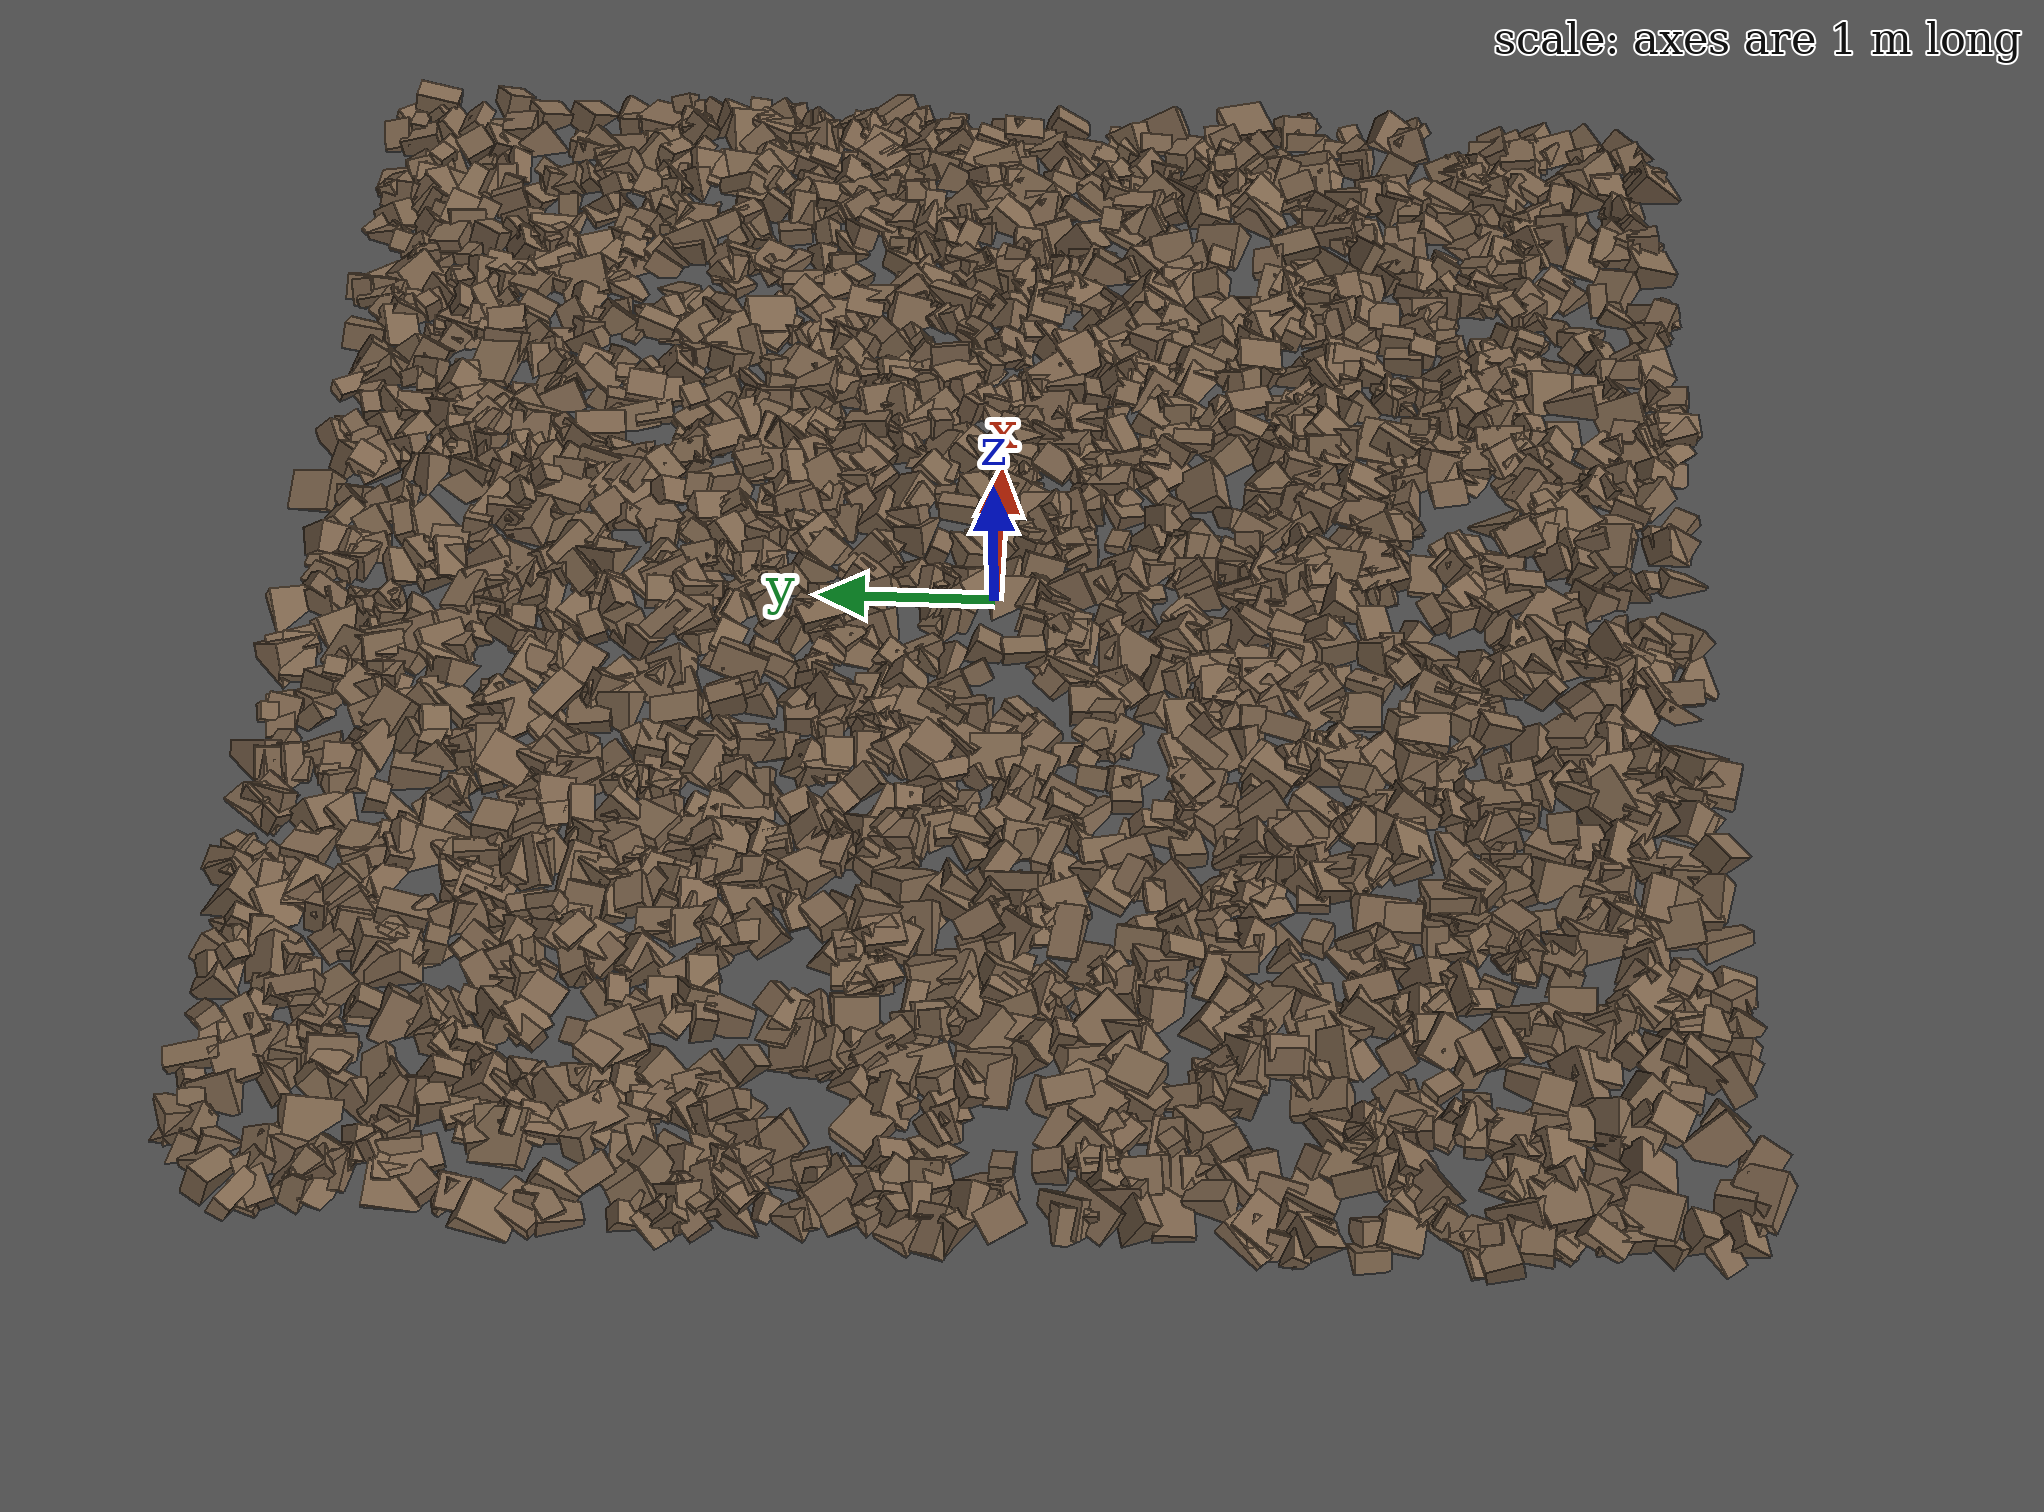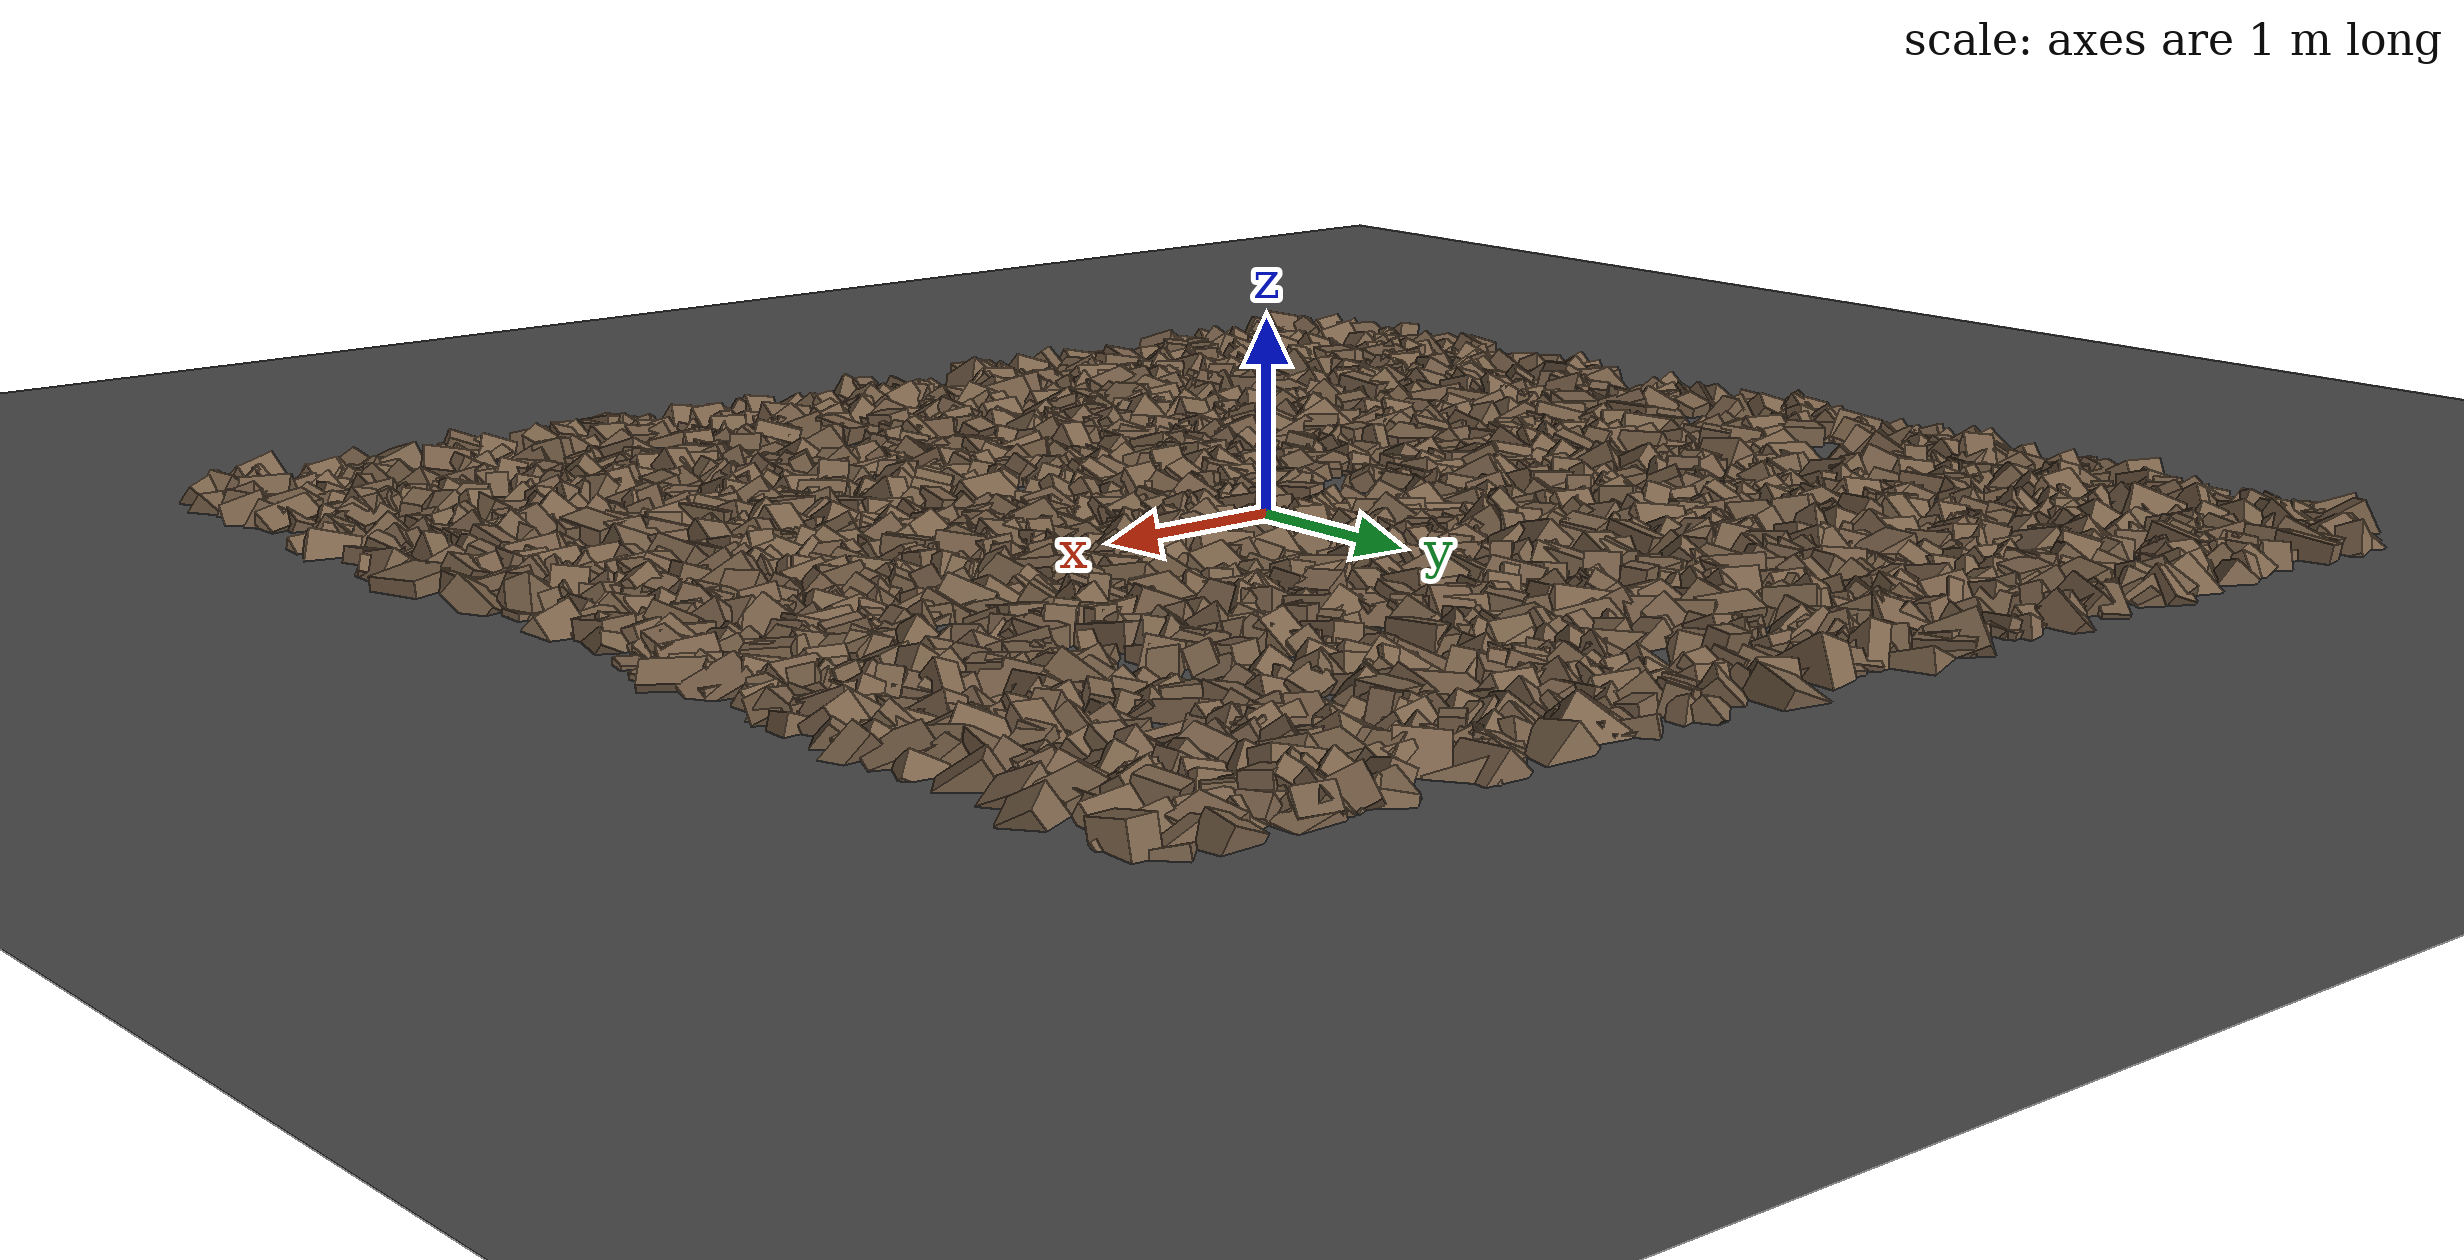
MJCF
<mujoco model="rocky_terrain_scene">
    <compiler angle="radian" inertiafromgeom="true" />
    <option timestep="0.002" gravity="0 0 -9.81" />

    <worldbody>
        <light name="sunlight" pos="5 5 5" dir="-1 -1 -1" diffuse="1 1 1" specular="0.5 0.5 0.5"
            ambient="0.5 0.5 0.5" />

        <geom name="ground_plane" type="plane" size="50 50 0.1" rgba="0.3 0.3 0.3 1" />

        <body name="rocky_terrain_body">

        </body>
        <body name="rock1" pos="3.6506110391389335 2.775671008048847 -0.047856639543872384">
            <joint type="free" limited="true" range="0 0 0 0 0 0" />
            <geom type="box" size="0.11182913833742755 0.07546968036430693 0.13024003089410377"
                quat="0.11379941972249516 0.3469229126741425 0.2975082354462407 0.24176943215712163"
                rgba="0.5 0.4 0.3 1" density="1000" />
        </body>
        <body name="rock2" pos="-0.4732955832481851 3.9071045246876315 -0.05375066201143085">
            <joint type="free" limited="true" range="0 0 0 0 0 0" />
            <geom type="box" size="0.05825949293329753 0.05198161361032905 0.12512924638302822"
                quat="0.3291931701651419 0.315935990243512 0.33108765018864206 0.023783189402704092"
                rgba="0.5 0.4 0.3 1" density="1000" />
        </body>
        <body name="rock3" pos="2.536988343333393 -2.6739260998189867 -0.037139626752778356">
            <joint type="free" limited="true" range="0 0 0 0 0 0" />
            <geom type="box" size="0.13951402268495317 0.0981946374921028 0.0796385065409573"
                quat="0.2107801746622077 0.4482362659595658 0.11410015818979247 0.22688340118843411"
                rgba="0.5 0.4 0.3 1" density="1000" />
        </body>
        <body name="rock4" pos="2.4307980169343537 2.7683121448591734 -0.03562921787812612">
            <joint type="free" limited="true" range="0 0 0 0 0 0" />
            <geom type="box" size="0.05944834559182186 0.0671157893206901 0.10527130521957948"
                quat="0.2563034892612546 0.3571583097932039 0.24848662911533204 0.13805157183020944"
                rgba="0.5 0.4 0.3 1" density="1000" />
        </body>
        <body name="rock5" pos="0.07819736310670322 0.16498978420780208 -0.014156815407575529">
            <joint type="free" limited="true" range="0 0 0 0 0 0" />
            <geom type="box" size="0.09318949083914 0.1349587726792641 0.05940479440497956"
                quat="0.16741597016413987 0.13689823660992392 0.2340474104545063 0.46163838277143004"
                rgba="0.5 0.4 0.3 1" density="1000" />
        </body>
        <body name="rock6" pos="-0.27361541876660667 -3.727902416051844 -0.03792379829720725">
            <joint type="free" limited="true" range="0 0 0 0 0 0" />
            <geom type="box" size="0.11215684912869849 0.10121110674557397 0.0950398251629516"
                quat="0.09470169141407134 0.14432115708854507 0.3036580997537583 0.4573190517436253"
                rgba="0.5 0.4 0.3 1" density="1000" />
        </body>
        <body name="rock7" pos="1.8349507261516464 -1.8696320270345872 -0.045538830085498666">
            <joint type="free" limited="true" range="0 0 0 0 0 0" />
            <geom type="box" size="0.05107667500196168 0.13642333876520757 0.11808043424658092"
                quat="0.3377237475625608 0.06164336865854516 0.40860259345852423 0.1920302903203698"
                rgba="0.5 0.4 0.3 1" density="1000" />
        </body>
        <body name="rock8" pos="2.4361382592251024 1.7078572909447987 -0.026204352588451628">
            <joint type="free" limited="true" range="0 0 0 0 0 0" />
            <geom type="box" size="0.07640767311682742 0.09105582015571592 0.05895902485460949"
                quat="0.28644078766329795 0.09030561213300121 0.02103302894867837 0.6022205712550226"
                rgba="0.5 0.4 0.3 1" density="1000" />
        </body>
        <body name="rock9" pos="-2.741930855319522 -2.3004165680415243 -0.04723679055376129">
            <joint type="free" limited="true" range="0 0 0 0 0 0" />
            <geom type="box" size="0.117766444062211 0.06727695481260122 0.09793814428566838"
                quat="0.49953391148386367 0.3832507422586967 0.09640025318916791 0.020815093068271638"
                rgba="0.5 0.4 0.3 1" density="1000" />
        </body>
        <body name="rock10" pos="2.5296087279062895 1.725241875080778 -0.045044090058107625">
            <joint type="free" limited="true" range="0 0 0 0 0 0" />
            <geom type="box" size="0.1423152496909953 0.05895949076922666 0.1205780150778059"
                quat="0.19462734710790763 0.46057936056028914 0.12858124570420146 0.21621204662760166"
                rgba="0.5 0.4 0.3 1" density="1000" />
        </body>
        <body name="rock11" pos="1.3834727232703186 -0.1251427684254356 -0.012070858362886148">
            <joint type="free" limited="true" range="0 0 0 0 0 0" />
            <geom type="box" size="0.06851410063869445 0.10786084767418677 0.05677246244590609"
                quat="0.2680659522089758 0.25379014618108914 0.1859028883128743 0.29224101329706076"
                rgba="0.5 0.4 0.3 1" density="1000" />
        </body>
        <body name="rock12" pos="-2.848720857140875 -0.0853662465587961 -0.063584684417766">
            <joint type="free" limited="true" range="0 0 0 0 0 0" />
            <geom type="box" size="0.13292549333244572 0.14581396894018994 0.1399015023598572"
                quat="0.2751567948976252 0.3741874964807166 0.004987239390136515 0.34566846923152167"
                rgba="0.5 0.4 0.3 1" density="1000" />
        </body>
        <body name="rock13" pos="0.1300622485067695 0.10159073721651701 -0.0602208826082053">
            <joint type="free" limited="true" range="0 0 0 0 0 0" />
            <geom type="box" size="0.13549019891118225 0.07688909419614441 0.13248101913928512"
                quat="0.2289628210248896 0.20063086736260471 0.0957333205025063 0.4746729911099994"
                rgba="0.5 0.4 0.3 1" density="1000" />
        </body>
        <body name="rock14" pos="2.550574719194989 -0.21145569120484087 -0.058316128932991824">
            <joint type="free" limited="true" range="0 0 0 0 0 0" />
            <geom type="box" size="0.10125311634100247 0.14061251857229665 0.13578690934793636"
                quat="0.33569941542478393 0.5472387800338708 0.0789714784950792 0.038090326046266054"
                rgba="0.5 0.4 0.3 1" density="1000" />
        </body>
        <body name="rock15" pos="-2.7425312723566915 -3.232961062951272 -0.05664237627878135">
            <joint type="free" limited="true" range="0 0 0 0 0 0" />
            <geom type="box" size="0.11682756747341806 0.09068027369025645 0.12944863234449744"
                quat="0.35658349702878134 0.211936936773181 0.28020416844281165 0.15127539775522605"
                rgba="0.5 0.4 0.3 1" density="1000" />
        </body>
        <body name="rock16" pos="-0.19231511045354122 -1.2008892429962659 -0.051252235608109584">
            <joint type="free" limited="true" range="0 0 0 0 0 0" />
            <geom type="box" size="0.09734907027878448 0.11253720722758072 0.12773624222068652"
                quat="0.04167726960602557 0.23959737520170735 0.43929929008678265 0.2794260651054844"
                rgba="0.5 0.4 0.3 1" density="1000" />
        </body>
        <body name="rock17" pos="2.797727024525063 -0.14217837072899808 -0.03503144580095601">
            <joint type="free" limited="true" range="0 0 0 0 0 0" />
            <geom type="box" size="0.07543423942447136 0.10648203022421504 0.0849853235214628"
                quat="0.2898795570636435 0.13414449060461997 0.22233778528959317 0.35363816704214335"
                rgba="0.5 0.4 0.3 1" density="1000" />
        </body>
        <body name="rock18" pos="-2.1634011341776196 -3.2334394700003664 -0.04116464452989978">
            <joint type="free" limited="true" range="0 0 0 0 0 0" />
            <geom type="box" size="0.1409559395508591 0.11063184531984391 0.11708040990196344"
                quat="0.3316993240449246 0.18007636931291454 0.07698817226676417 0.41123613437539663"
                rgba="0.5 0.4 0.3 1" density="1000" />
        </body>
        <body name="rock19" pos="-0.4575818610720326 -2.7677902271203374 -0.0202015476601572">
            <joint type="free" limited="true" range="0 0 0 0 0 0" />
            <geom type="box" size="0.09625635594975063 0.1233302256786353 0.061175427869317005"
                quat="0.07498092527154092 0.5030412825626422 0.2807892563815536 0.14118853578426327"
                rgba="0.5 0.4 0.3 1" density="1000" />
        </body>
        <body name="rock20" pos="1.655922473376327 2.4537443764835665 -0.03323834772015415">
            <joint type="free" limited="true" range="0 0 0 0 0 0" />
            <geom type="box" size="0.11809424379875014 0.10576560165728102 0.07172531722794331"
                quat="0.31791603272150876 0.319800559436301 0.0762373989964416 0.28604600884574866"
                rgba="0.5 0.4 0.3 1" density="1000" />
        </body>
        <body name="rock21" pos="-1.0031639085214055 -3.6129864075179476 -0.035917342537420766">
            <joint type="free" limited="true" range="0 0 0 0 0 0" />
            <geom type="box" size="0.1378654048341617 0.1062744260683503 0.09195222278559159"
                quat="0.19283794798565235 0.38956127689199216 0.04859851272237826 0.3690022623999773"
                rgba="0.5 0.4 0.3 1" density="1000" />
        </body>
        <body name="rock22" pos="-1.7277732089719633 -2.1218529543800617 -0.027017403606340078">
            <joint type="free" limited="true" range="0 0 0 0 0 0" />
            <geom type="box" size="0.1260914816406669 0.08680307723034161 0.09329465229785049"
                quat="0.22968308262136197 0.3284734163844953 0.05174511433907673 0.3900983866550661"
                rgba="0.5 0.4 0.3 1" density="1000" />
        </body>
        <body name="rock23" pos="-0.8936341245321291 -3.51436778781709 -0.05482011621389167">
            <joint type="free" limited="true" range="0 0 0 0 0 0" />
            <geom type="box" size="0.06700856000395514 0.1005953045375133 0.12437329512617064"
                quat="0.1491916513418871 0.28538680514899084 0.19284346054959423 0.37257808295952777"
                rgba="0.5 0.4 0.3 1" density="1000" />
        </body>
        <body name="rock24" pos="3.4074464781314164 -2.9385015375116277 -0.04124851500760202">
            <joint type="free" limited="true" range="0 0 0 0 0 0" />
            <geom type="box" size="0.11142193308987369 0.06200760260694685 0.11617590093633683"
                quat="0.14462406823924784 0.35293406822505585 0.09198948584108192 0.4104523776946143"
                rgba="0.5 0.4 0.3 1" density="1000" />
        </body>
        <body name="rock25" pos="-1.1382924776967833 0.814606512614878 -0.050044950713169084">
            <joint type="free" limited="true" range="0 0 0 0 0 0" />
            <geom type="box" size="0.09111304499926956 0.11410945172468696 0.12795360006714446"
                quat="0.4830507280091992 0.05178672823938244 0.31883959873928164 0.14632294501213672"
                rgba="0.5 0.4 0.3 1" density="1000" />
        </body>
        <body name="rock26" pos="-2.4349223579437416 -3.6991823263119015 -0.01981536406616196">
            <joint type="free" limited="true" range="0 0 0 0 0 0" />
            <geom type="box" size="0.06073776692638612 0.1436121439590326 0.07270440318015489"
                quat="0.3421632391009611 0.2882095184360521 0.18206647227990075 0.187560770183086"
                rgba="0.5 0.4 0.3 1" density="1000" />
        </body>
        <body name="rock27" pos="-3.8735219622169454 2.812018884757589 -0.030128559628586623">
            <joint type="free" limited="true" range="0 0 0 0 0 0" />
            <geom type="box" size="0.14909277487389083 0.11255277548328459 0.07575583069606101"
                quat="0.012682688359226462 0.4495826626360593 0.4357035957046325 0.10203105330008182"
                rgba="0.5 0.4 0.3 1" density="1000" />
        </body>
        <body name="rock28" pos="-2.6531929630476556 -3.3492802205166514 -0.04070139410073892">
            <joint type="free" limited="true" range="0 0 0 0 0 0" />
            <geom type="box" size="0.1022051406047137 0.08856499584980806 0.12059947273888101"
                quat="0.1521173992316815 0.47127933311142994 0.3472606950671684 0.029342572589720083"
                rgba="0.5 0.4 0.3 1" density="1000" />
        </body>
        <body name="rock29" pos="1.4691688263548635 -2.629027181710904 -0.05775168196209135">
            <joint type="free" limited="true" range="0 0 0 0 0 0" />
            <geom type="box" size="0.10892083222457266 0.13473028008260501 0.11873805055964316"
                quat="0.29082031394556257 0.35137533120084 0.34002668759811727 0.01777766725548016"
                rgba="0.5 0.4 0.3 1" density="1000" />
        </body>
        <body name="rock30" pos="3.7698941264254078 3.3502400329973128 -0.023035648499412524">
            <joint type="free" limited="true" range="0 0 0 0 0 0" />
            <geom type="box" size="0.07327668165337438 0.05866060330110767 0.07433615828179008"
                quat="0.09369574395917218 0.3956271285195651 0.42830761557591956 0.0823695119453431"
                rgba="0.5 0.4 0.3 1" density="1000" />
        </body>
        <body name="rock31" pos="-0.5800217342325578 1.7496588821571395 -0.058515958714369425">
            <joint type="free" limited="true" range="0 0 0 0 0 0" />
            <geom type="box" size="0.11586108127595526 0.14164738175351327 0.12157792179950863"
                quat="0.3367678312092949 0.13556728383522385 0.30483957989745925 0.22282530505802203"
                rgba="0.5 0.4 0.3 1" density="1000" />
        </body>
        <body name="rock32" pos="-3.212938094081027 -0.4155934157685506 -0.018204411404098786">
            <joint type="free" limited="true" range="0 0 0 0 0 0" />
            <geom type="box" size="0.07795779480462073 0.09462562507155275 0.05799102875725544"
                quat="0.16211842969920576 0.5014623234537358 0.3342761669016293 0.002143079945429132"
                rgba="0.5 0.4 0.3 1" density="1000" />
        </body>
        <body name="rock33" pos="2.566975611200455 0.1504255077802581 -0.06955311549481337">
            <joint type="free" limited="true" range="0 0 0 0 0 0" />
            <geom type="box" size="0.07086531715527708 0.14960488956968865 0.13948298515583774"
                quat="0.19600614160431043 0.267474680740186 0.36344501499941695 0.17307416265608672"
                rgba="0.5 0.4 0.3 1" density="1000" />
        </body>
        <body name="rock34" pos="-3.643024440639784 -3.8599056348642806 -0.02116107094300468">
            <joint type="free" limited="true" range="0 0 0 0 0 0" />
            <geom type="box" size="0.09881689934529489 0.10645133875664484 0.07753077898643532"
                quat="0.4482608383890683 0.09120585708676508 0.14407551441390198 0.3164577901102647"
                rgba="0.5 0.4 0.3 1" density="1000" />
        </body>
        <body name="rock35" pos="-0.16534384260611734 -1.4230630302359897 -0.04588034030392099">
            <joint type="free" limited="true" range="0 0 0 0 0 0" />
            <geom type="box" size="0.12384052287152991 0.10170925791241717 0.11030485238647988"
                quat="0.23953470071823543 0.5518342348367774 0.16870577843856915 0.03992528600641794"
                rgba="0.5 0.4 0.3 1" density="1000" />
        </body>
        <body name="rock36" pos="3.813976187133364 -1.3446101251310925 -0.03004896595091177">
            <joint type="free" limited="true" range="0 0 0 0 0 0" />
            <geom type="box" size="0.08743412763581657 0.1450486826460784 0.09748258749464671"
                quat="0.2996604147682223 0.1179951145471023 0.2889650236528152 0.2933794470318602"
                rgba="0.5 0.4 0.3 1" density="1000" />
        </body>
        <body name="rock37" pos="3.6007013840947586 2.83977438720874 -0.06277197128001168">
            <joint type="free" limited="true" range="0 0 0 0 0 0" />
            <geom type="box" size="0.0505119391768955 0.07710718060943092 0.14288692351244686"
                quat="0.4968964114310507 0.09815017659189751 0.03671970179737762 0.3682337101796741"
                rgba="0.5 0.4 0.3 1" density="1000" />
        </body>
        <body name="rock38" pos="3.201853497604068 -3.310591225795691 -0.026529591875560865">
            <joint type="free" limited="true" range="0 0 0 0 0 0" />
            <geom type="box" size="0.1450019677795245 0.08031916378177469 0.09156629096752941"
                quat="0.318852318459352 0.15631332057243122 0.2792606276932256 0.24557373327499116"
                rgba="0.5 0.4 0.3 1" density="1000" />
        </body>
        <body name="rock39" pos="-0.3259700185543757 2.6837190476887853 -0.02642613230336855">
            <joint type="free" limited="true" range="0 0 0 0 0 0" />
            <geom type="box" size="0.11927454443543366 0.147474801106527 0.05716511433387687"
                quat="0.48754456903823107 0.17394158484441316 0.13494724175185294 0.20356660436550283"
                rgba="0.5 0.4 0.3 1" density="1000" />
        </body>
        <body name="rock40" pos="0.6140342023120358 3.501797026748825 -0.02080140417877969">
            <joint type="free" limited="true" range="0 0 0 0 0 0" />
            <geom type="box" size="0.08208664436644966 0.08458256814867633 0.07073026127982239"
                quat="0.31108501397467875 0.1739077326280532 0.3350471178444282 0.17996013555283988"
                rgba="0.5 0.4 0.3 1" density="1000" />
        </body>
        <body name="rock41" pos="-3.8931344726407504 3.507192814476724 -0.07047346678147301">
            <joint type="free" limited="true" range="0 0 0 0 0 0" />
            <geom type="box" size="0.0705261484863011 0.13929818854103876 0.14430657620724247"
                quat="0.18983098532174747 0.1889310556703192 0.30544167206247474 0.3157962869454585"
                rgba="0.5 0.4 0.3 1" density="1000" />
        </body>
        <body name="rock42" pos="3.3894138965582936 -0.27036693440381665 -0.03029306734896609">
            <joint type="free" limited="true" range="0 0 0 0 0 0" />
            <geom type="box" size="0.1215481353509646 0.06822333538958865 0.0992989330633145"
                quat="0.26363588782828623 0.2440792467624123 0.09678027668438056 0.3955045887249209"
                rgba="0.5 0.4 0.3 1" density="1000" />
        </body>
        <body name="rock43" pos="-0.3467530325018764 -3.972885210589694 -0.07037516096145735">
            <joint type="free" limited="true" range="0 0 0 0 0 0" />
            <geom type="box" size="0.10913610414789732 0.0755007615830645 0.14558036483533648"
                quat="0.23852883171218728 0.36498121595284944 0.1739975349067278 0.22249241742823547"
                rgba="0.5 0.4 0.3 1" density="1000" />
        </body>
        <body name="rock44" pos="0.7597501102172561 -3.5856824086138674 -0.06605936665246993">
            <joint type="free" limited="true" range="0 0 0 0 0 0" />
            <geom type="box" size="0.05898414125018547 0.06624064704836527 0.1457038583039933"
                quat="0.48156592371599716 0.46315533260647374 0.007355226114907326 0.047923517562621816"
                rgba="0.5 0.4 0.3 1" density="1000" />
        </body>
        <body name="rock45" pos="-3.514157753474489 -1.307646658874475 -0.02842974343915247">
            <joint type="free" limited="true" range="0 0 0 0 0 0" />
            <geom type="box" size="0.1499193741958238 0.11158766277743201 0.06174289191195648"
                quat="0.24061120173498865 0.1401749281398133 0.3397349269255454 0.2794789431996527"
                rgba="0.5 0.4 0.3 1" density="1000" />
        </body>
        <body name="rock46" pos="0.6541694947503478 3.9872944051119426 -0.058830054739683425">
            <joint type="free" limited="true" range="0 0 0 0 0 0" />
            <geom type="box" size="0.12929246146233447 0.13771642082942134 0.11844158276104723"
                quat="0.35085747631704595 0.18158097664096193 0.22050180081999726 0.24705974622199478"
                rgba="0.5 0.4 0.3 1" density="1000" />
        </body>
        <body name="rock47" pos="-0.38227423474680755 2.0241370447056983 -0.05184439838268266">
            <joint type="free" limited="true" range="0 0 0 0 0 0" />
            <geom type="box" size="0.07872239685080687 0.12877380329388669 0.12400866989451716"
                quat="0.018412264921184945 0.25386655826944077 0.30925201079526626 0.41846916601410805"
                rgba="0.5 0.4 0.3 1" density="1000" />
        </body>
        <body name="rock48" pos="-2.13609492403147 -3.438552681730858 -0.01934449337219403">
            <joint type="free" limited="true" range="0 0 0 0 0 0" />
            <geom type="box" size="0.14406550055471196 0.05140711166194281 0.07148388378474056"
                quat="0.3458655789293879 0.3383518384718871 0.19139593812498737 0.12438664447373755"
                rgba="0.5 0.4 0.3 1" density="1000" />
        </body>
        <body name="rock49" pos="1.0031817817145745 0.01781991565283292 -0.010595073591892237">
            <joint type="free" limited="true" range="0 0 0 0 0 0" />
            <geom type="box" size="0.10312026790727784 0.09478920394135365 0.05647471970480984"
                quat="0.035691562556410004 0.27242080284662246 0.4581825885241963 0.2337050460727712"
                rgba="0.5 0.4 0.3 1" density="1000" />
        </body>
        <body name="rock50" pos="-3.2227117093026125 -2.935977791686237 -0.04800389113843495">
            <joint type="free" limited="true" range="0 0 0 0 0 0" />
            <geom type="box" size="0.11798453488360727 0.07388718532603249 0.13015609825491253"
                quat="0.22406903555610758 0.24715759799859627 0.34666234268470686 0.18211102376058938"
                rgba="0.5 0.4 0.3 1" density="1000" />
        </body>
        <body name="rock51" pos="2.9162744426061753 -1.7866738162853846 -0.031438742619860724">
            <joint type="free" limited="true" range="0 0 0 0 0 0" />
            <geom type="box" size="0.12735250470156217 0.06090234982638128 0.09917577589243298"
                quat="0.08002961263839811 0.4693822908371648 0.010779017116476768 0.4398090794079603"
                rgba="0.5 0.4 0.3 1" density="1000" />
        </body>
        <body name="rock52" pos="-0.7959874273586331 1.045417978359347 -0.02924378871613445">
            <joint type="free" limited="true" range="0 0 0 0 0 0" />
            <geom type="box" size="0.10984346538648397 0.07716463256615268 0.06018346341594849"
                quat="0.2865409152324543 0.37602021357402754 0.027597976455811225 0.30984089473770704"
                rgba="0.5 0.4 0.3 1" density="1000" />
        </body>
        <body name="rock53" pos="-3.5060564448250258 2.3647771522789895 -0.061384293827519976">
            <joint type="free" limited="true" range="0 0 0 0 0 0" />
            <geom type="box" size="0.12262561665501363 0.06338394242832845 0.12504661024825087"
                quat="0.018979630487899198 0.37545519874923905 0.06644668616875081 0.5391184845941108"
                rgba="0.5 0.4 0.3 1" density="1000" />
        </body>
        <body name="rock54" pos="-2.273052916526895 -2.868040845131836 -0.05015286159415895">
            <joint type="free" limited="true" range="0 0 0 0 0 0" />
            <geom type="box" size="0.057586000806673046 0.12549308532995948 0.13056007447503473"
                quat="0.2760408622251319 0.24900264853537157 0.18242250420455924 0.29253398503493727"
                rgba="0.5 0.4 0.3 1" density="1000" />
        </body>
        <body name="rock55" pos="-3.5196106229652253 -2.2172107715365703 -0.044486092691466146">
            <joint type="free" limited="true" range="0 0 0 0 0 0" />
            <geom type="box" size="0.11201185915086528 0.11313506865192462 0.1191602955987415"
                quat="0.11833127383950233 0.35094258382856286 0.22928196663156028 0.30144417570037446"
                rgba="0.5 0.4 0.3 1" density="1000" />
        </body>
        <body name="rock56" pos="0.6147133765588837 -3.923163496721031 -0.016041842539350728">
            <joint type="free" limited="true" range="0 0 0 0 0 0" />
            <geom type="box" size="0.10568361819183855 0.09941509188751654 0.07005072899567001"
                quat="0.3928885187846642 0.2471592973293541 0.09173010244452773 0.26822208144145404"
                rgba="0.5 0.4 0.3 1" density="1000" />
        </body>
        <body name="rock57" pos="-0.5320715220650465 -2.5952417475591982 -0.03884889180374839">
            <joint type="free" limited="true" range="0 0 0 0 0 0" />
            <geom type="box" size="0.1024527065811559 0.12421051204575762 0.11130524773507298"
                quat="0.11551829643119974 0.3548516805826486 0.272562570102844 0.25706745288330773"
                rgba="0.5 0.4 0.3 1" density="1000" />
        </body>
        <body name="rock58" pos="-3.3811213940640794 -1.8000741514635044 -0.06272268201592371">
            <joint type="free" limited="true" range="0 0 0 0 0 0" />
            <geom type="box" size="0.05224465157937766 0.11140632857697552 0.14924843388594994"
                quat="0.048604787657567386 0.290131580717817 0.2806156486641589 0.3806479829604567"
                rgba="0.5 0.4 0.3 1" density="1000" />
        </body>
        <body name="rock59" pos="-3.6690758038227473 3.4592121491404173 -0.03460942208304444">
            <joint type="free" limited="true" range="0 0 0 0 0 0" />
            <geom type="box" size="0.1397591981560899 0.08482372697746385 0.08274062236037617"
                quat="0.11366121909807508 0.3508372699011067 0.09205345046297501 0.44344806053784325"
                rgba="0.5 0.4 0.3 1" density="1000" />
        </body>
        <body name="rock60" pos="-2.9587559636702805 -2.5500487825295046 -0.03180750071001977">
            <joint type="free" limited="true" range="0 0 0 0 0 0" />
            <geom type="box" size="0.06391855312153029 0.0709903292881376 0.09067213726915821"
                quat="0.09358211174668483 0.43008670775871766 0.2833282401267636 0.1930029403678339"
                rgba="0.5 0.4 0.3 1" density="1000" />
        </body>
        <body name="rock61" pos="3.675118120820848 -3.6111212851104844 -0.06664001531663027">
            <joint type="free" limited="true" range="0 0 0 0 0 0" />
            <geom type="box" size="0.13367412242342425 0.13434585173113406 0.14018507009095127"
                quat="0.06590515540334776 0.1923674258143403 0.49871519706446804 0.24301222171784392"
                rgba="0.5 0.4 0.3 1" density="1000" />
        </body>
        <body name="rock62" pos="2.5239961347629434 -1.664313019769648 -0.022849488487836918">
            <joint type="free" limited="true" range="0 0 0 0 0 0" />
            <geom type="box" size="0.08270185329155752 0.11786157365615026 0.08484069040142048"
                quat="0.2867870617053048 0.31400664971757564 0.15831987692530716 0.24088641165181235"
                rgba="0.5 0.4 0.3 1" density="1000" />
        </body>
        <body name="rock63" pos="3.0768111410718495 -0.5836970780743158 -0.027989200577248814">
            <joint type="free" limited="true" range="0 0 0 0 0 0" />
            <geom type="box" size="0.0626813888946536 0.14124668926286194 0.07291068964180317"
                quat="0.3037236941168666 0.22735314269233062 0.17967008981585403 0.2892530733749488"
                rgba="0.5 0.4 0.3 1" density="1000" />
        </body>
        <body name="rock64" pos="-2.7745852092048615 2.5517249475943 -0.028984457936593846">
            <joint type="free" limited="true" range="0 0 0 0 0 0" />
            <geom type="box" size="0.08859937338887292 0.0790695687438573 0.06188157889923057"
                quat="0.3395320085129874 0.24260763336521274 0.148011580446579 0.2698487776752208"
                rgba="0.5 0.4 0.3 1" density="1000" />
        </body>
        <body name="rock65" pos="-0.18773865105802567 2.8269055708690134 -0.053843296161059775">
            <joint type="free" limited="true" range="0 0 0 0 0 0" />
            <geom type="box" size="0.0956150535796067 0.13526435907015139 0.11174656692742596"
                quat="0.22019893432930085 0.3567759456465354 0.282749308376072 0.14027581164809166"
                rgba="0.5 0.4 0.3 1" density="1000" />
        </body>
        <body name="rock66" pos="-3.3137895802847472 -3.789829600996131 -0.025086837825010505">
            <joint type="free" limited="true" range="0 0 0 0 0 0" />
            <geom type="box" size="0.10931023595970543 0.14386065018430017 0.08547867205120699"
                quat="0.09200924685188809 0.5517567801051149 0.1875038146807034 0.1687301583622937"
                rgba="0.5 0.4 0.3 1" density="1000" />
        </body>
        <body name="rock67" pos="-0.9189708381099706 -0.1253924277681513 -0.015679708257213543">
            <joint type="free" limited="true" range="0 0 0 0 0 0" />
            <geom type="box" size="0.11077968558684281 0.14028906621165121 0.06159267712094296"
                quat="0.1210306021918554 0.6069004415619421 0.25956429932558744 0.01250465692061498"
                rgba="0.5 0.4 0.3 1" density="1000" />
        </body>
        <body name="rock68" pos="0.9973318225850383 3.2614661878126014 -0.038827947895251874">
            <joint type="free" limited="true" range="0 0 0 0 0 0" />
            <geom type="box" size="0.08587329998352411 0.10465349194705134 0.10565569886022011"
                quat="0.4417582047013246 0.4309393124138751 0.049834881659559155 0.07746760122524116"
                rgba="0.5 0.4 0.3 1" density="1000" />
        </body>
        <body name="rock69" pos="-1.957708485806804 -2.5062367510258596 -0.0521099012528989">
            <joint type="free" limited="true" range="0 0 0 0 0 0" />
            <geom type="box" size="0.1444633531371725 0.117142957790964 0.131517989354701"
                quat="0.35860025878661067 0.11906865592610573 0.09672107640488137 0.42561000888240214"
                rgba="0.5 0.4 0.3 1" density="1000" />
        </body>
        <body name="rock70" pos="0.33826786507010276 -1.353048231435305 -0.03329008838920215">
            <joint type="free" limited="true" range="0 0 0 0 0 0" />
            <geom type="box" size="0.1029893840279629 0.1343150091712339 0.10153511169788226"
                quat="0.17539059443196947 0.3775847539969109 0.26546581205473263 0.18155883951638704"
                rgba="0.5 0.4 0.3 1" density="1000" />
        </body>
        <body name="rock71" pos="3.446246717926668 -2.879563285134754 -0.03880769942451291">
            <joint type="free" limited="true" range="0 0 0 0 0 0" />
            <geom type="box" size="0.12248883899578485 0.12971004625579463 0.08841173523700377"
                quat="0.035418357112151945 0.19607286520114717 0.3759419649272405 0.39256681275946037"
                rgba="0.5 0.4 0.3 1" density="1000" />
        </body>
        <body name="rock72" pos="2.645148699536243 1.5019337885276975 -0.04423337776764087">
            <joint type="free" limited="true" range="0 0 0 0 0 0" />
            <geom type="box" size="0.0961253360111877 0.1082615807525856 0.11129815438608961"
                quat="0.3132291497101043 0.30991779121102864 0.18457701268881732 0.19227604639004978"
                rgba="0.5 0.4 0.3 1" density="1000" />
        </body>
        <body name="rock73" pos="-2.1250259225194235 2.7019933680451826 -0.05091759738988482">
            <joint type="free" limited="true" range="0 0 0 0 0 0" />
            <geom type="box" size="0.1398331543896042 0.0911611372391973 0.1089881135560141"
                quat="0.468891619142974 0.10544731645395648 0.3939637887559375 0.031697275647131984"
                rgba="0.5 0.4 0.3 1" density="1000" />
        </body>
        <body name="rock74" pos="0.14765861654788903 3.1151210378716074 -0.05856538198130412">
            <joint type="free" limited="true" range="0 0 0 0 0 0" />
            <geom type="box" size="0.07741293941049901 0.11286863849246483 0.13139292407389747"
                quat="0.3183879816463205 0.15222646898043576 0.18742750088772167 0.341958048485522"
                rgba="0.5 0.4 0.3 1" density="1000" />
        </body>
        <body name="rock75" pos="2.4321835482283243 -0.4252280527241199 -0.03658386357302869">
            <joint type="free" limited="true" range="0 0 0 0 0 0" />
            <geom type="box" size="0.11788338126992674 0.08649596225206338 0.1106720871457461"
                quat="0.24943888868081499 0.2978903218676857 0.17996664324386802 0.2727041462076312"
                rgba="0.5 0.4 0.3 1" density="1000" />
        </body>
        <body name="rock76" pos="-3.2487967953002173 2.2448122499392857 -0.016584827999761655">
            <joint type="free" limited="true" range="0 0 0 0 0 0" />
            <geom type="box" size="0.09748817069258378 0.10563262540876264 0.058606146354130875"
                quat="0.4051805673450145 0.025258333647944903 0.22698525473463158 0.34257584427240895"
                rgba="0.5 0.4 0.3 1" density="1000" />
        </body>
        <body name="rock77" pos="0.85518921376317 -2.249758109812931 -0.05458316535557227">
            <joint type="free" limited="true" range="0 0 0 0 0 0" />
            <geom type="box" size="0.06539616443425803 0.09078014764963188 0.13327631101716106"
                quat="0.15885584848098916 0.5677216741233232 0.025958163277973893 0.24746431411771377"
                rgba="0.5 0.4 0.3 1" density="1000" />
        </body>
        <body name="rock78" pos="3.919838096878143 -3.299059043054708 -0.04189983045108647">
            <joint type="free" limited="true" range="0 0 0 0 0 0" />
            <geom type="box" size="0.12936500587520916 0.08847116458357604 0.11079914876528679"
                quat="0.1856515277667339 0.47202409959345487 0.055041271753458916 0.2872831008863523"
                rgba="0.5 0.4 0.3 1" density="1000" />
        </body>
        <body name="rock79" pos="-0.2603480576390833 1.845984237053032 -0.013407518209532242">
            <joint type="free" limited="true" range="0 0 0 0 0 0" />
            <geom type="box" size="0.1380212365902514 0.11346660061286672 0.05999481950710455"
                quat="0.20352639577490314 0.10609630620819308 0.3726605735916275 0.3177167244252763"
                rgba="0.5 0.4 0.3 1" density="1000" />
        </body>
        <body name="rock80" pos="-1.1126188096408756 3.2260572225405566 -0.05165244610150364">
            <joint type="free" limited="true" range="0 0 0 0 0 0" />
            <geom type="box" size="0.0584011666835108 0.13623338796990522 0.12898966511832582"
                quat="0.030942667345925 0.373696706610112 0.24634004200445314 0.3490205840395099"
                rgba="0.5 0.4 0.3 1" density="1000" />
        </body>
        <body name="rock81" pos="-2.6318133139727653 2.9903707337118215 -0.02729484473576337">
            <joint type="free" limited="true" range="0 0 0 0 0 0" />
            <geom type="box" size="0.11794145183299702 0.14380493100837646 0.063995046614331"
                quat="0.31899914946651753 0.1453573388601579 0.31155350860740433 0.22409000306592028"
                rgba="0.5 0.4 0.3 1" density="1000" />
        </body>
        <body name="rock82" pos="3.1058027351056925 -3.1452517533230884 -0.0163511965418068">
            <joint type="free" limited="true" range="0 0 0 0 0 0" />
            <geom type="box" size="0.07180643339008745 0.0901085969589152 0.05906550684092628"
                quat="0.21852172010021575 0.248237448828609 0.2240081500751201 0.30923268099605516"
                rgba="0.5 0.4 0.3 1" density="1000" />
        </body>
        <body name="rock83" pos="1.7580914317939689 1.432845880113951 -0.02484888125786303">
            <joint type="free" limited="true" range="0 0 0 0 0 0" />
            <geom type="box" size="0.058461121960539 0.08127079557266312 0.08648448801332441"
                quat="0.05950382600599426 0.2726720500441904 0.39528712359813084 0.2725370003516845"
                rgba="0.5 0.4 0.3 1" density="1000" />
        </body>
        <body name="rock84" pos="-1.3250439444929993 0.7405109077143885 -0.04788607250834873">
            <joint type="free" limited="true" range="0 0 0 0 0 0" />
            <geom type="box" size="0.0669999354257355 0.05137063765119432 0.11093025738899939"
                quat="0.11501534868298681 0.3197271656952776 0.24131448820299195 0.3239429974187437"
                rgba="0.5 0.4 0.3 1" density="1000" />
        </body>
        <body name="rock85" pos="-1.396957054009075 -1.332973617750545 -0.0543888660363597">
            <joint type="free" limited="true" range="0 0 0 0 0 0" />
            <geom type="box" size="0.07316474215892123 0.11819405345894736 0.13357345699436873"
                quat="0.429218411741666 0.018897733597277692 0.16072177069680016 0.3911620839642562"
                rgba="0.5 0.4 0.3 1" density="1000" />
        </body>
        <body name="rock86" pos="0.6523558389515012 0.004047056507494595 -0.015850539943662652">
            <joint type="free" limited="true" range="0 0 0 0 0 0" />
            <geom type="box" size="0.09537177532789919 0.1219124463968412 0.05764442313622129"
                quat="0.15827428079519784 0.32334128669366086 0.07183085951862991 0.4465535729925114"
                rgba="0.5 0.4 0.3 1" density="1000" />
        </body>
        <body name="rock87" pos="3.35838792846039 -0.9043802494626334 -0.053453850618042725">
            <joint type="free" limited="true" range="0 0 0 0 0 0" />
            <geom type="box" size="0.10294076136716934 0.12116002525281146 0.12100657227230219"
                quat="0.2451780459963369 0.0515957749170148 0.35850295003067295 0.3447232290559754"
                rgba="0.5 0.4 0.3 1" density="1000" />
        </body>
        <body name="rock88" pos="2.538360338289345 -2.5163941262490965 -0.06001312506750016">
            <joint type="free" limited="true" range="0 0 0 0 0 0" />
            <geom type="box" size="0.10879629691928858 0.08104941205670183 0.14546190298924777"
                quat="0.26096972705549865 0.4525061000443268 0.2570312191518677 0.029492953748306797"
                rgba="0.5 0.4 0.3 1" density="1000" />
        </body>
        <body name="rock89" pos="2.6029497440452936 -1.850691219866615 -0.04369052541006528">
            <joint type="free" limited="true" range="0 0 0 0 0 0" />
            <geom type="box" size="0.08717193006750278 0.07805330836974224 0.11385656285498404"
                quat="0.4161641186864911 0.38035148949044933 0.1986347244695897 0.004849667353469893"
                rgba="0.5 0.4 0.3 1" density="1000" />
        </body>
        <body name="rock90" pos="1.2767248894879506 -1.8710882890738523 -0.040667049316503">
            <joint type="free" limited="true" range="0 0 0 0 0 0" />
            <geom type="box" size="0.0950413173090342 0.13866280756729304 0.10215485845622435"
                quat="0.3289475644953988 0.1410930079956587 0.13719500734233334 0.3927644201666091"
                rgba="0.5 0.4 0.3 1" density="1000" />
        </body>
        <body name="rock91" pos="-2.725855571470313 2.220390132808941 -0.03059726760246643">
            <joint type="free" limited="true" range="0 0 0 0 0 0" />
            <geom type="box" size="0.09862015925047984 0.12301374710176464 0.08101524473163621"
                quat="0.31057912920595027 0.3129671020463676 0.11512243934022819 0.26133132940745396"
                rgba="0.5 0.4 0.3 1" density="1000" />
        </body>
        <body name="rock92" pos="-1.0728475904773482 -3.954300002290993 -0.03498878993399948">
            <joint type="free" limited="true" range="0 0 0 0 0 0" />
            <geom type="box" size="0.08365266365956071 0.09320787636454114 0.07515076269510633"
                quat="0.43780580772864813 0.19843742731706399 0.3512237278121747 0.012533037142113238"
                rgba="0.5 0.4 0.3 1" density="1000" />
        </body>
        <body name="rock93" pos="3.7931669425854153 1.556259846341522 -0.049188865271947185">
            <joint type="free" limited="true" range="0 0 0 0 0 0" />
            <geom type="box" size="0.10332546314958602 0.10092050873748842 0.12423364544404783"
                quat="0.31181530644224104 0.15244523227906773 0.19452009410938922 0.341219367169302"
                rgba="0.5 0.4 0.3 1" density="1000" />
        </body>
        <body name="rock94" pos="-0.3546950116014269 -2.2406283430918927 -0.025510531266304155">
            <joint type="free" limited="true" range="0 0 0 0 0 0" />
            <geom type="box" size="0.08851475919818957 0.09418150491225923 0.07574638513422977"
                quat="0.2780328555958412 0.4013936723320222 0.24236243701104518 0.07821103506109141"
                rgba="0.5 0.4 0.3 1" density="1000" />
        </body>
        <body name="rock95" pos="-0.1256522853120554 -1.6833037711065915 -0.03226864915414429">
            <joint type="free" limited="true" range="0 0 0 0 0 0" />
            <geom type="box" size="0.12152004503605852 0.06249257746585401 0.09786113220596812"
                quat="0.04933478858536971 0.5187710821092967 0.34274844841097474 0.08914568089435884"
                rgba="0.5 0.4 0.3 1" density="1000" />
        </body>
        <body name="rock96" pos="1.63773094859285 3.2027184350488396 -0.02217239769413948">
            <joint type="free" limited="true" range="0 0 0 0 0 0" />
            <geom type="box" size="0.14328533769494128 0.06311783592721078 0.05774251372255368"
                quat="0.1940878757883417 0.2540822487881322 0.23757074065938893 0.3142591347641371"
                rgba="0.5 0.4 0.3 1" density="1000" />
        </body>
        <body name="rock97" pos="-3.213766687964558 0.5567605256463786 -0.028657571709050585">
            <joint type="free" limited="true" range="0 0 0 0 0 0" />
            <geom type="box" size="0.11037875389310706 0.10943223639862112 0.05951592065137158"
                quat="0.3601805700359282 0.22596974644586748 0.35156733132633966 0.0622823521918647"
                rgba="0.5 0.4 0.3 1" density="1000" />
        </body>
        <body name="rock98" pos="1.6326360225881418 -0.8658017779338394 -0.024128316743838495">
            <joint type="free" limited="true" range="0 0 0 0 0 0" />
            <geom type="box" size="0.09470290818719812 0.14834994548183256 0.06393382613477615"
                quat="0.03392218763536121 0.41573075699297385 0.3018237545298492 0.24852330084181576"
                rgba="0.5 0.4 0.3 1" density="1000" />
        </body>
        <body name="rock99" pos="-0.8991841169058992 -1.2516124904643666 -0.034027036920929093">
            <joint type="free" limited="true" range="0 0 0 0 0 0" />
            <geom type="box" size="0.06604040405849798 0.14759271015051922 0.09132068652132619"
                quat="0.5473274794328606 0.2483499296622088 0.10585647300634768 0.09846611789858296"
                rgba="0.5 0.4 0.3 1" density="1000" />
        </body>
        <body name="rock100" pos="3.0882472600491946 1.557811866077511 -0.014956458473504238">
            <joint type="free" limited="true" range="0 0 0 0 0 0" />
            <geom type="box" size="0.12882818786485928 0.08551257404827264 0.06538728629884868"
                quat="0.2948592731258414 0.16674539475011238 0.486379964999547 0.052015367124499175"
                rgba="0.5 0.4 0.3 1" density="1000" />
        </body>
        <body name="rock101" pos="3.1643453876877903 3.660224737632059 -0.02745671618233154">
            <joint type="free" limited="true" range="0 0 0 0 0 0" />
            <geom type="box" size="0.12357081350736704 0.1397772469577671 0.072410763536291"
                quat="0.36600250641947796 0.4313351891104314 0.07882408807228582 0.12383821639780487"
                rgba="0.5 0.4 0.3 1" density="1000" />
        </body>
        <body name="rock102" pos="-2.8596311984046068 2.781510604499414 -0.05364736943329604">
            <joint type="free" limited="true" range="0 0 0 0 0 0" />
            <geom type="box" size="0.13272184396475833 0.09841759310919716 0.10934865519093767"
                quat="0.05939603272416686 0.35350747821905926 0.1931707657683334 0.39392572328844044"
                rgba="0.5 0.4 0.3 1" density="1000" />
        </body>
        <body name="rock103" pos="2.97431989321169 -2.2355992022870534 -0.05595327541218086">
            <joint type="free" limited="true" range="0 0 0 0 0 0" />
            <geom type="box" size="0.053355620288343925 0.09488793383958238 0.11866515161907494"
                quat="0.259208636113732 0.11070557594385326 0.4319141219536149 0.1981716659887998"
                rgba="0.5 0.4 0.3 1" density="1000" />
        </body>
        <body name="rock104" pos="-1.8690579359005035 -1.8749618856191512 -0.06534081138479422">
            <joint type="free" limited="true" range="0 0 0 0 0 0" />
            <geom type="box" size="0.10128583157512569 0.1404662702265813 0.14589655483031483"
                quat="0.7320552737405777 0.12067361279622217 0.04645779131273842 0.10081332215046175"
                rgba="0.5 0.4 0.3 1" density="1000" />
        </body>
        <body name="rock105" pos="3.962234097006119 -3.640966968943104 -0.050512852991869896">
            <joint type="free" limited="true" range="0 0 0 0 0 0" />
            <geom type="box" size="0.07764125284662801 0.09868589408528622 0.11192126590042265"
                quat="0.29568029253056727 0.085476807107828 0.3463749325337103 0.2724679678278944"
                rgba="0.5 0.4 0.3 1" density="1000" />
        </body>
        <body name="rock106" pos="3.0559997338812837 0.44432973988793467 -0.0576004956752984">
            <joint type="free" limited="true" range="0 0 0 0 0 0" />
            <geom type="box" size="0.05026126521861404 0.1314366902004788 0.13195953974349092"
                quat="0.38249182321188435 0.23263286161692498 0.32187529803378795 0.06300001713740273"
                rgba="0.5 0.4 0.3 1" density="1000" />
        </body>
        <body name="rock107" pos="2.313286085921934 -2.5559947143898807 -0.01752630310439132">
            <joint type="free" limited="true" range="0 0 0 0 0 0" />
            <geom type="box" size="0.09476520978119227 0.12344498331594735 0.06175617679911502"
                quat="0.09433859313235518 0.14303631383254978 0.40675551729447346 0.3558695757406216"
                rgba="0.5 0.4 0.3 1" density="1000" />
        </body>
        <body name="rock108" pos="2.6969786054936717 -0.5214413162329379 -0.05034365690528528">
            <joint type="free" limited="true" range="0 0 0 0 0 0" />
            <geom type="box" size="0.12661594032719853 0.1328416157760759 0.12654239445877835"
                quat="0.0834081684963207 0.45075871102239834 0.2797476993705994 0.18608542111068163"
                rgba="0.5 0.4 0.3 1" density="1000" />
        </body>
        <body name="rock109" pos="-3.0159870632413996 -1.3432206118818861 -0.028176527706468724">
            <joint type="free" limited="true" range="0 0 0 0 0 0" />
            <geom type="box" size="0.09667288434157895 0.14944088766769398 0.08756490701924881"
                quat="0.5278121764242799 0.03359487776604419 0.1710288733194142 0.2675640724902617"
                rgba="0.5 0.4 0.3 1" density="1000" />
        </body>
        <body name="rock110" pos="-1.4276324708234682 -0.13411203730384091 -0.04134942235265137">
            <joint type="free" limited="true" range="0 0 0 0 0 0" />
            <geom type="box" size="0.05886195866149603 0.08658328937353967 0.10867319229858824"
                quat="0.3694365184011698 0.26778117719253985 0.26057502276900024 0.10220728163729002"
                rgba="0.5 0.4 0.3 1" density="1000" />
        </body>
        <body name="rock111" pos="1.5750458147115314 -1.4451403036945543 -0.029831207425016812">
            <joint type="free" limited="true" range="0 0 0 0 0 0" />
            <geom type="box" size="0.1296469279545944 0.09976901990710052 0.07647019578421352"
                quat="0.20731195438297617 0.2073888266869011 0.2714793886796521 0.31381983025047067"
                rgba="0.5 0.4 0.3 1" density="1000" />
        </body>
        <body name="rock112" pos="-1.5200218611897398 -3.151456392181169 -0.041122713644723474">
            <joint type="free" limited="true" range="0 0 0 0 0 0" />
            <geom type="box" size="0.07977865531475226 0.14255303377902862 0.11712999011313126"
                quat="0.25455612932662236 0.24813970013143147 0.31263370498885734 0.18467046555308883"
                rgba="0.5 0.4 0.3 1" density="1000" />
        </body>
        <body name="rock113" pos="1.84550040303181 0.5589413910824197 -0.03375845918034163">
            <joint type="free" limited="true" range="0 0 0 0 0 0" />
            <geom type="box" size="0.12442067905314184 0.056666626867536096 0.0924663725948429"
                quat="0.1343682019335753 0.1195089785929279 0.30748287511864286 0.438639944354854"
                rgba="0.5 0.4 0.3 1" density="1000" />
        </body>
        <body name="rock114" pos="2.1379182079051837 -0.9284321819013845 -0.01798813032208918">
            <joint type="free" limited="true" range="0 0 0 0 0 0" />
            <geom type="box" size="0.10387708090527646 0.06107147515363486 0.06116552541030318"
                quat="0.3122838392853181 0.11421334698248368 0.20815451868537696 0.3653482950468212"
                rgba="0.5 0.4 0.3 1" density="1000" />
        </body>
        <body name="rock115" pos="-3.394083767559806 -1.0084551287558448 -0.02025215278956046">
            <joint type="free" limited="true" range="0 0 0 0 0 0" />
            <geom type="box" size="0.13685124694964773 0.07153039651262148 0.05855162944103962"
                quat="0.31797506078954607 0.18247806354701163 0.2730438119267833 0.226503063736659"
                rgba="0.5 0.4 0.3 1" density="1000" />
        </body>
        <body name="rock116" pos="-3.9628559218804016 1.9896281520058272 -0.04949839863826735">
            <joint type="free" limited="true" range="0 0 0 0 0 0" />
            <geom type="box" size="0.11757486559933873 0.06771806835916441 0.12284596527355936"
                quat="0.15226081679504638 0.28062017139718237 0.304000105114831 0.2631189066929402"
                rgba="0.5 0.4 0.3 1" density="1000" />
        </body>
        <body name="rock117" pos="-2.001753803183166 -1.3456120966560867 -0.010263768456468678">
            <joint type="free" limited="true" range="0 0 0 0 0 0" />
            <geom type="box" size="0.12874725176654367 0.06807301234222876 0.05839145239262472"
                quat="0.08569104376814955 0.35237849769368984 0.3358092236112582 0.2261212349269024"
                rgba="0.5 0.4 0.3 1" density="1000" />
        </body>
        <body name="rock118" pos="-0.11955094655738918 1.4682487444594328 -0.029773641991591014">
            <joint type="free" limited="true" range="0 0 0 0 0 0" />
            <geom type="box" size="0.1056677135713118 0.06960998745151396 0.0891607297632387"
                quat="0.3085694658439411 0.28703898733365046 0.07151143034290917 0.3328801164794992"
                rgba="0.5 0.4 0.3 1" density="1000" />
        </body>
        <body name="rock119" pos="-3.0974853377884504 3.3367594243840664 -0.007549215110459029">
            <joint type="free" limited="true" range="0 0 0 0 0 0" />
            <geom type="box" size="0.09747671632782579 0.1342977368892947 0.05425366903681558"
                quat="0.12350494958486065 0.4126260033830349 0.3403323469460343 0.12353670008607005"
                rgba="0.5 0.4 0.3 1" density="1000" />
        </body>
        <body name="rock120" pos="-1.536305534369066 2.1940018132534034 -0.05704712092658585">
            <joint type="free" limited="true" range="0 0 0 0 0 0" />
            <geom type="box" size="0.1445287527280415 0.06500825900719438 0.12256992670482793"
                quat="0.5027799122912927 0.03750936097214872 0.36972270401259133 0.08998802272396733"
                rgba="0.5 0.4 0.3 1" density="1000" />
        </body>
        <body name="rock121" pos="2.8166484290566203 -3.909860936823594 -0.05571830848167482">
            <joint type="free" limited="true" range="0 0 0 0 0 0" />
            <geom type="box" size="0.13518551345561539 0.13128972365331393 0.1448433237817866"
                quat="0.37339837414271604 0.0378805704825793 0.5009017973131383 0.08781925806156621"
                rgba="0.5 0.4 0.3 1" density="1000" />
        </body>
        <body name="rock122" pos="1.090873354643895 -2.7298434224133814 -0.06293858610023736">
            <joint type="free" limited="true" range="0 0 0 0 0 0" />
            <geom type="box" size="0.11352359998393756 0.08990407944195847 0.1370640885015736"
                quat="0.2815222097770677 0.3214352897822502 0.14852421889492787 0.24851828154575425"
                rgba="0.5 0.4 0.3 1" density="1000" />
        </body>
        <body name="rock123" pos="0.30667625922946407 0.7207243779086916 -0.029048594667813673">
            <joint type="free" limited="true" range="0 0 0 0 0 0" />
            <geom type="box" size="0.11162616760926167 0.12737742995665297 0.061669743298020864"
                quat="0.12733850555072793 0.4721612963700246 0.18862799337174496 0.21187220470750268"
                rgba="0.5 0.4 0.3 1" density="1000" />
        </body>
        <body name="rock124" pos="-0.6893251351381826 1.8262286906823384 -0.045406417476641564">
            <joint type="free" limited="true" range="0 0 0 0 0 0" />
            <geom type="box" size="0.11927874255955405 0.09096626287896926 0.12430612439809667"
                quat="0.46217173260817224 0.3401009391291356 0.01190306390506641 0.1858242643576257"
                rgba="0.5 0.4 0.3 1" density="1000" />
        </body>
        <body name="rock125" pos="3.521544630265751 0.8114963458841675 -0.02828531947775805">
            <joint type="free" limited="true" range="0 0 0 0 0 0" />
            <geom type="box" size="0.052895289783701505 0.14847904176261872 0.06695952358299664"
                quat="0.057594884295952886 0.22674446724533742 0.5221945767415178 0.19346607171719185"
                rgba="0.5 0.4 0.3 1" density="1000" />
        </body>
        <body name="rock126" pos="-3.8311553501258944 -1.463191855003295 -0.06780921938039756">
            <joint type="free" limited="true" range="0 0 0 0 0 0" />
            <geom type="box" size="0.06601290043229928 0.06616209294069654 0.14211360696643516"
                quat="0.4699041153632762 0.14420331222867183 0.2885546517092665 0.0973379206987854"
                rgba="0.5 0.4 0.3 1" density="1000" />
        </body>
        <body name="rock127" pos="-2.899345700423553 0.2643157279370767 -0.03838481987607791">
            <joint type="free" limited="true" range="0 0 0 0 0 0" />
            <geom type="box" size="0.11555629178562006 0.06369102223075956 0.08779765089690048"
                quat="0.26920411737727107 0.2918724237569472 0.2906458300832051 0.14827762878257655"
                rgba="0.5 0.4 0.3 1" density="1000" />
        </body>
        <body name="rock128" pos="1.956674163178663 -3.5775494812306645 -0.0286422622836898">
            <joint type="free" limited="true" range="0 0 0 0 0 0" />
            <geom type="box" size="0.05064851766766729 0.14116891293672446 0.06714753572790946"
                quat="0.2828975284983906 0.1737709142102407 0.18071367679594635 0.36261788049542243"
                rgba="0.5 0.4 0.3 1" density="1000" />
        </body>
        <body name="rock129" pos="3.164327781662296 2.5315034836248387 -0.041554130423282404">
            <joint type="free" limited="true" range="0 0 0 0 0 0" />
            <geom type="box" size="0.05976111558495707 0.05440198260584166 0.11914573041758769"
                quat="0.2546104154407354 0.08610074707135211 0.4178258787161108 0.2414629587718016"
                rgba="0.5 0.4 0.3 1" density="1000" />
        </body>
        <body name="rock130" pos="-1.0156860837820245 -3.868106731311462 -0.05191626351951199">
            <joint type="free" limited="true" range="0 0 0 0 0 0" />
            <geom type="box" size="0.13407545894843304 0.13680500349184443 0.11089386459500072"
                quat="0.27817348096419836 0.4523386015659455 0.2661779187144836 0.003309998755372609"
                rgba="0.5 0.4 0.3 1" density="1000" />
        </body>
        <body name="rock131" pos="0.6860672497840143 1.3616497381999748 -0.022833262807563683">
            <joint type="free" limited="true" range="0 0 0 0 0 0" />
            <geom type="box" size="0.051172915697985204 0.0995577950784362 0.05249485689257686"
                quat="0.006275467755863086 0.508840198469262 0.4847398462007776 0.00014448757409737202"
                rgba="0.5 0.4 0.3 1" density="1000" />
        </body>
        <body name="rock132" pos="-0.2405052710376756 0.9291505272594707 -0.04175481122724223">
            <joint type="free" limited="true" range="0 0 0 0 0 0" />
            <geom type="box" size="0.10431700642661237 0.08256389466929658 0.09718244118295846"
                quat="0.055448013771878885 0.4815558983205868 0.07331407934139683 0.38968200856613755"
                rgba="0.5 0.4 0.3 1" density="1000" />
        </body>
        <body name="rock133" pos="1.9408695715637228 -1.2887334258867646 -0.021625385315487418">
            <joint type="free" limited="true" range="0 0 0 0 0 0" />
            <geom type="box" size="0.10458195739566975 0.07583161838337439 0.06437399961712095"
                quat="0.2019452296681585 0.0023012107750583727 0.38188036786033985 0.4138731916964432"
                rgba="0.5 0.4 0.3 1" density="1000" />
        </body>
        <body name="rock134" pos="-0.46914737311811283 1.406881433535533 -0.027974179078954938">
            <joint type="free" limited="true" range="0 0 0 0 0 0" />
            <geom type="box" size="0.1467118287062155 0.14719720178646356 0.0828759753131436"
                quat="0.37756587093528343 0.20226307760311685 0.0795206811679445 0.34065037029365525"
                rgba="0.5 0.4 0.3 1" density="1000" />
        </body>
        <body name="rock135" pos="1.0012297437921474 -0.5085384671794735 -0.044237083316989834">
            <joint type="free" limited="true" range="0 0 0 0 0 0" />
            <geom type="box" size="0.0752933003524567 0.13180894194121717 0.10492423555851521"
                quat="0.36145696967561436 0.07651651766415603 0.129208348297277 0.43281816436295256"
                rgba="0.5 0.4 0.3 1" density="1000" />
        </body>
        <body name="rock136" pos="0.13043497959604178 1.8989910894130544 -0.02870321241923234">
            <joint type="free" limited="true" range="0 0 0 0 0 0" />
            <geom type="box" size="0.10408184577877402 0.08062462699236442 0.09709126209090728"
                quat="0.25479996076257977 0.334606704774231 0.04134854484544539 0.3692447896177439"
                rgba="0.5 0.4 0.3 1" density="1000" />
        </body>
        <body name="rock137" pos="-2.64912675092888 -0.6677377682255132 -0.0440158720704041">
            <joint type="free" limited="true" range="0 0 0 0 0 0" />
            <geom type="box" size="0.08528440084692573 0.11627094930581529 0.10226350350326074"
                quat="0.46376401435319176 0.4100954342391765 0.007286931809397517 0.11885361959823423"
                rgba="0.5 0.4 0.3 1" density="1000" />
        </body>
        <body name="rock138" pos="3.925031645652517 -0.9267762101665653 -0.026775121210242024">
            <joint type="free" limited="true" range="0 0 0 0 0 0" />
            <geom type="box" size="0.1424867172247521 0.1351366387919711 0.06560480901043408"
                quat="0.12995901467287113 0.5924995477245218 0.09259787648877472 0.1849435611138323"
                rgba="0.5 0.4 0.3 1" density="1000" />
        </body>
        <body name="rock139" pos="-0.6298914305041157 -3.317482584250625 -0.033528322840112285">
            <joint type="free" limited="true" range="0 0 0 0 0 0" />
            <geom type="box" size="0.13571548391799215 0.09091615448915594 0.08545499461340886"
                quat="0.0019041428759204587 0.5131875982838033 0.2018734030204274 0.2830348558198488"
                rgba="0.5 0.4 0.3 1" density="1000" />
        </body>
        <body name="rock140" pos="2.808898710154539 -2.314097227360432 -0.01957055975951731">
            <joint type="free" limited="true" range="0 0 0 0 0 0" />
            <geom type="box" size="0.05457679669731133 0.08959640836242351 0.061823654764370475"
                quat="0.21410540185566537 0.09491204602986095 0.3830265590100768 0.30795599310439675"
                rgba="0.5 0.4 0.3 1" density="1000" />
        </body>
        <body name="rock141" pos="3.639908172199277 0.2525825158102819 -0.05484832189153473">
            <joint type="free" limited="true" range="0 0 0 0 0 0" />
            <geom type="box" size="0.14917377280413152 0.0943422345467853 0.12940315305197372"
                quat="0.2786534902158242 0.3092929956500225 0.2431536523264395 0.16889986180771388"
                rgba="0.5 0.4 0.3 1" density="1000" />
        </body>
        <body name="rock142" pos="-2.64411988357448 3.976911190363989 -0.02557568882763317">
            <joint type="free" limited="true" range="0 0 0 0 0 0" />
            <geom type="box" size="0.06932716392319824 0.10955815889985437 0.08409488939246966"
                quat="0.18320884379909563 0.25655234631162327 0.1569457719333542 0.40329303795592686"
                rgba="0.5 0.4 0.3 1" density="1000" />
        </body>
        <body name="rock143" pos="3.4233849410807764 0.028177029602437287 -0.028014986379565676">
            <joint type="free" limited="true" range="0 0 0 0 0 0" />
            <geom type="box" size="0.06932707625706538 0.12722089361947025 0.06410013122514853"
                quat="0.1636612374200668 0.10492046776713958 0.15606305803388928 0.5753552367789043"
                rgba="0.5 0.4 0.3 1" density="1000" />
        </body>
        <body name="rock144" pos="-1.6691902037094613 -2.2757660896388066 -0.061886070396488885">
            <joint type="free" limited="true" range="0 0 0 0 0 0" />
            <geom type="box" size="0.10974393057808889 0.10561990472475094 0.1419006451622148"
                quat="0.20497084267842833 0.18994180009883097 0.3628986462669548 0.2421887109557858"
                rgba="0.5 0.4 0.3 1" density="1000" />
        </body>
        <body name="rock145" pos="-2.8037131747031205 -2.947412454865141 -0.012246122841056471">
            <joint type="free" limited="true" range="0 0 0 0 0 0" />
            <geom type="box" size="0.07434283082095533 0.07455765110407152 0.05215275425092175"
                quat="0.16824356397818135 0.3426265673546523 0.46812547000774013 0.021004398659426163"
                rgba="0.5 0.4 0.3 1" density="1000" />
        </body>
        <body name="rock146" pos="-1.625830099979094 3.8770072119907963 -0.014165292576054332">
            <joint type="free" limited="true" range="0 0 0 0 0 0" />
            <geom type="box" size="0.13368090918489162 0.1319074806610889 0.06508819212153634"
                quat="0.18973211513920846 0.4291928841270319 0.3114621759980909 0.06961282473566878"
                rgba="0.5 0.4 0.3 1" density="1000" />
        </body>
        <body name="rock147" pos="-2.7151601953475177 1.4580439599402322 -0.026192921003061885">
            <joint type="free" limited="true" range="0 0 0 0 0 0" />
            <geom type="box" size="0.08062841410943207 0.09687791361819806 0.08650837029511496"
                quat="0.020531435662446487 0.3528114586479441 0.32676351313243424 0.29989359255717507"
                rgba="0.5 0.4 0.3 1" density="1000" />
        </body>
        <body name="rock148" pos="-1.2256070693282952 -0.7999771937450069 -0.028223061859182653">
            <joint type="free" limited="true" range="0 0 0 0 0 0" />
            <geom type="box" size="0.05367524023541187 0.1317783365336903 0.07461010387718783"
                quat="0.5157115867700238 0.09634492049112003 0.3050597465104623 0.08288374622839383"
                rgba="0.5 0.4 0.3 1" density="1000" />
        </body>
        <body name="rock149" pos="-0.6907683336291388 -1.1947339992926942 -0.03305138374414889">
            <joint type="free" limited="true" range="0 0 0 0 0 0" />
            <geom type="box" size="0.07631237195740155 0.052528274400754506 0.09505992889948059"
                quat="0.17377383113797978 0.30795482664125123 0.20344892794527508 0.31482241427549396"
                rgba="0.5 0.4 0.3 1" density="1000" />
        </body>
        <body name="rock150" pos="0.4994961489738614 -0.22389803913308182 -0.051917614488861286">
            <joint type="free" limited="true" range="0 0 0 0 0 0" />
            <geom type="box" size="0.11591529770375443 0.1339168063163635 0.1260597890132507"
                quat="0.021951893770629026 0.36449279201129514 0.18226620949892364 0.4312891047191522"
                rgba="0.5 0.4 0.3 1" density="1000" />
        </body>
        <body name="rock151" pos="2.830494103164275 2.912717977138846 -0.05976140420374354">
            <joint type="free" limited="true" range="0 0 0 0 0 0" />
            <geom type="box" size="0.1494055675152702 0.09571822820470603 0.1379403209603359"
                quat="0.17980850521789676 0.24993309328992372 0.22843164508578054 0.341826756406399"
                rgba="0.5 0.4 0.3 1" density="1000" />
        </body>
        <body name="rock152" pos="0.8758156822982537 -1.194277426286554 -0.04731090767760868">
            <joint type="free" limited="true" range="0 0 0 0 0 0" />
            <geom type="box" size="0.14259149470780363 0.1225785675152365 0.12943514098651243"
                quat="0.6043912604820695 0.3301159665901417 0.029754055337684784 0.03573871759010398"
                rgba="0.5 0.4 0.3 1" density="1000" />
        </body>
        <body name="rock153" pos="-0.19573149716051574 -1.8593118501763044 -0.02232397932263111">
            <joint type="free" limited="true" range="0 0 0 0 0 0" />
            <geom type="box" size="0.14078913907603696 0.13170798822217689 0.06473487053681387"
                quat="0.36633183350686627 0.1641252305489667 0.33011827407039623 0.13942466187377087"
                rgba="0.5 0.4 0.3 1" density="1000" />
        </body>
        <body name="rock154" pos="1.1777860141461511 2.608751420277642 -0.014172771192777692">
            <joint type="free" limited="true" range="0 0 0 0 0 0" />
            <geom type="box" size="0.11265556096169277 0.08882176929114835 0.05304264744740204"
                quat="0.41309146221556436 0.38227875827687446 0.1964622030207695 0.008167576486791697"
                rgba="0.5 0.4 0.3 1" density="1000" />
        </body>
        <body name="rock155" pos="-0.7428491536004342 3.669658754490537 -0.02006334155118207">
            <joint type="free" limited="true" range="0 0 0 0 0 0" />
            <geom type="box" size="0.10660468313929616 0.13899776466546385 0.06794894343721829"
                quat="0.46262500405806684 0.14421664157548061 0.12725776054698734 0.2659005938194652"
                rgba="0.5 0.4 0.3 1" density="1000" />
        </body>
        <body name="rock156" pos="-1.3077700197385793 -0.24522665914787645 -0.01948126710362933">
            <joint type="free" limited="true" range="0 0 0 0 0 0" />
            <geom type="box" size="0.12297377152105611 0.08118322780752076 0.07137220599946784"
                quat="0.06126106779869513 0.017917177067366223 0.5497566602066386 0.37106509492729994"
                rgba="0.5 0.4 0.3 1" density="1000" />
        </body>
        <body name="rock157" pos="-2.7640984809978715 -1.41945116094129 -0.028258599364247242">
            <joint type="free" limited="true" range="0 0 0 0 0 0" />
            <geom type="box" size="0.1314900146435553 0.08794924782970305 0.07127631474157421"
                quat="0.3908806154491474 0.144027670576547 0.2022302330874921 0.26286148088681344"
                rgba="0.5 0.4 0.3 1" density="1000" />
        </body>
        <body name="rock158" pos="-3.09686652741728 3.7399737316473303 -0.05443931488330363">
            <joint type="free" limited="true" range="0 0 0 0 0 0" />
            <geom type="box" size="0.10883099736360145 0.062026948777409975 0.13856490411759254"
                quat="0.1820674625073908 0.2378138922588348 0.22998505718609213 0.3501335880476822"
                rgba="0.5 0.4 0.3 1" density="1000" />
        </body>
        <body name="rock159" pos="-0.03561501797044375 1.7080786424738594 -0.027040195811560853">
            <joint type="free" limited="true" range="0 0 0 0 0 0" />
            <geom type="box" size="0.14029141431743375 0.1376529788938673 0.08269651496376326"
                quat="0.1066229214527166 0.2800938887095516 0.3044255764182992 0.30885761341943246"
                rgba="0.5 0.4 0.3 1" density="1000" />
        </body>
        <body name="rock160" pos="-2.586185327287862 -0.9989098907660328 -0.050783605327555985">
            <joint type="free" limited="true" range="0 0 0 0 0 0" />
            <geom type="box" size="0.09990754320632755 0.0747862493974243 0.10757368341458082"
                quat="0.3274374928521244 0.23963804948883033 0.18567109081295188 0.24725336684609336"
                rgba="0.5 0.4 0.3 1" density="1000" />
        </body>
        <body name="rock161" pos="0.3187830520135133 -3.3914041256074254 -0.026782363324998063">
            <joint type="free" limited="true" range="0 0 0 0 0 0" />
            <geom type="box" size="0.08574833374148814 0.13391000740088593 0.05440996640689064"
                quat="0.04422288945031114 0.3085950005210212 0.6339940320338643 0.013188077994803444"
                rgba="0.5 0.4 0.3 1" density="1000" />
        </body>
        <body name="rock162" pos="1.3298494917325892 -0.1627237817812306 -0.022246168485699835">
            <joint type="free" limited="true" range="0 0 0 0 0 0" />
            <geom type="box" size="0.08526987915069281 0.1493574828112577 0.05752224196667441"
                quat="0.36673030206004265 0.25280508383461053 0.2753604456226476 0.1051041684826992"
                rgba="0.5 0.4 0.3 1" density="1000" />
        </body>
        <body name="rock163" pos="0.4494620469452819 1.2201136356329565 -0.033356459231919586">
            <joint type="free" limited="true" range="0 0 0 0 0 0" />
            <geom type="box" size="0.08332695406253737 0.09837672798066799 0.09562468192880713"
                quat="0.07074200762403361 0.25969913249593646 0.34684246832462257 0.32271639155540743"
                rgba="0.5 0.4 0.3 1" density="1000" />
        </body>
        <body name="rock164" pos="-0.02678959795131508 2.232432491443861 -0.035631726700565663">
            <joint type="free" limited="true" range="0 0 0 0 0 0" />
            <geom type="box" size="0.10162473036653319 0.082771499013532 0.11123537853662105"
                quat="0.2479323375060627 0.25300331464159836 0.09179913271243653 0.40726521513990244"
                rgba="0.5 0.4 0.3 1" density="1000" />
        </body>
        <body name="rock165" pos="-3.4959550483007247 -1.0650064701778792 -0.010016785475835708">
            <joint type="free" limited="true" range="0 0 0 0 0 0" />
            <geom type="box" size="0.053461575088277306 0.11135012183316742 0.051322348995225545"
                quat="0.16128251832703494 0.1822944282833584 0.3828062774070031 0.2736167759826036"
                rgba="0.5 0.4 0.3 1" density="1000" />
        </body>
        <body name="rock166" pos="-2.643511592347898 0.12756382794369703 -0.04307374646161098">
            <joint type="free" limited="true" range="0 0 0 0 0 0" />
            <geom type="box" size="0.14823417954231352 0.09432766456881361 0.10576251358102766"
                quat="0.31135049723279506 0.25685808228419693 0.3281503446561763 0.10364107582683171"
                rgba="0.5 0.4 0.3 1" density="1000" />
        </body>
        <body name="rock167" pos="3.160769883684181 -1.8893331211860493 -0.06863357348587809">
            <joint type="free" limited="true" range="0 0 0 0 0 0" />
            <geom type="box" size="0.10636361909357715 0.08974835653333027 0.13843163292136682"
                quat="0.38491690468174244 0.11545577109954243 0.12111824804148318 0.3785090761772319"
                rgba="0.5 0.4 0.3 1" density="1000" />
        </body>
        <body name="rock168" pos="3.4446190510146426 2.172964398954486 -0.0402160431264143">
            <joint type="free" limited="true" range="0 0 0 0 0 0" />
            <geom type="box" size="0.1371246106332089 0.06166366107743737 0.10799073677355853"
                quat="0.3048310055342404 0.23693915107624502 0.2538483403498149 0.20438150303969974"
                rgba="0.5 0.4 0.3 1" density="1000" />
        </body>
        <body name="rock169" pos="-0.9821942259163707 0.1175455054280361 -0.04958045472587803">
            <joint type="free" limited="true" range="0 0 0 0 0 0" />
            <geom type="box" size="0.14945353240683096 0.10559770699891086 0.11460682597705432"
                quat="0.27872601776285844 0.4299199734644691 0.18291207345406085 0.10844193531861163"
                rgba="0.5 0.4 0.3 1" density="1000" />
        </body>
        <body name="rock170" pos="-2.2778341022639275 -2.1335259227488192 -0.04923267971549625">
            <joint type="free" limited="true" range="0 0 0 0 0 0" />
            <geom type="box" size="0.06834769016708168 0.09984058935171336 0.13726528340394759"
                quat="0.00254412216105435 0.15901892355645397 0.42473627525705254 0.4137006790254391"
                rgba="0.5 0.4 0.3 1" density="1000" />
        </body>
        <body name="rock171" pos="0.8082741043504429 3.4610572349505357 -0.05536600189676913">
            <joint type="free" limited="true" range="0 0 0 0 0 0" />
            <geom type="box" size="0.08131691271750625 0.05689455255560865 0.1433582324688431"
                quat="0.2894429531061852 0.27154332899696954 0.04355640746509746 0.3954573104317478"
                rgba="0.5 0.4 0.3 1" density="1000" />
        </body>
        <body name="rock172" pos="1.7102862594763808 -3.995353045215788 -0.02483193427591448">
            <joint type="free" limited="true" range="0 0 0 0 0 0" />
            <geom type="box" size="0.09933577585733835 0.08688868989468915 0.06899881454327518"
                quat="0.08809070148689574 0.4246972299237745 0.02998804961708977 0.45722401897224"
                rgba="0.5 0.4 0.3 1" density="1000" />
        </body>
        <body name="rock173" pos="-2.647219756130986 -2.850546829366711 -0.0304607196575216">
            <joint type="free" limited="true" range="0 0 0 0 0 0" />
            <geom type="box" size="0.10312565060915993 0.14948708861741888 0.08465936988134086"
                quat="0.4284606831278806 0.08952857712024392 0.21359686100960745 0.26841387874226813"
                rgba="0.5 0.4 0.3 1" density="1000" />
        </body>
        <body name="rock174" pos="1.116743146207873 -2.4269556496577955 -0.050247120242799724">
            <joint type="free" limited="true" range="0 0 0 0 0 0" />
            <geom type="box" size="0.11291730095021466 0.08645966109957604 0.11294311945658318"
                quat="0.21428853586590324 0.1591765126763275 0.2789257065496903 0.3476092449080789"
                rgba="0.5 0.4 0.3 1" density="1000" />
        </body>
        <body name="rock175" pos="-1.2108733489251584 -0.15840738675706056 -0.058202166357185774">
            <joint type="free" limited="true" range="0 0 0 0 0 0" />
            <geom type="box" size="0.09885482918759395 0.1202475342931984 0.11852268649973892"
                quat="0.016172512209573445 0.33165772895194956 0.4817517269208988 0.17041803191757823"
                rgba="0.5 0.4 0.3 1" density="1000" />
        </body>
        <body name="rock176" pos="1.134663703952671 -1.6569203960519614 -0.05513265747994226">
            <joint type="free" limited="true" range="0 0 0 0 0 0" />
            <geom type="box" size="0.07132989824945156 0.07053378718656701 0.11084996524085011"
                quat="0.26471671012436654 0.09497323489306002 0.27123994952443775 0.3690701054581356"
                rgba="0.5 0.4 0.3 1" density="1000" />
        </body>
        <body name="rock177" pos="1.4874528353663505 0.14894190221044035 -0.051572558198329226">
            <joint type="free" limited="true" range="0 0 0 0 0 0" />
            <geom type="box" size="0.06316225301847403 0.12907694144438017 0.13078734599219083"
                quat="0.15981711229479145 0.1658176710176266 0.21197551694578526 0.46238969974179667"
                rgba="0.5 0.4 0.3 1" density="1000" />
        </body>
        <body name="rock178" pos="-0.016405689371107535 -0.7236644424072312 -0.05770980690748898">
            <joint type="free" limited="true" range="0 0 0 0 0 0" />
            <geom type="box" size="0.10382864780768838 0.06730111752732108 0.14984536646849145"
                quat="0.12462741159537016 0.036651775144651455 0.5555828061873688 0.2831380070726096"
                rgba="0.5 0.4 0.3 1" density="1000" />
        </body>
        <body name="rock179" pos="3.5585838309956612 2.2493456158485428 -0.03523565044849804">
            <joint type="free" limited="true" range="0 0 0 0 0 0" />
            <geom type="box" size="0.087569429498934 0.08885655310227897 0.08408545914675376"
                quat="0.21830473970604275 0.13661470563726047 0.514292200864536 0.13078835379216078"
                rgba="0.5 0.4 0.3 1" density="1000" />
        </body>
        <body name="rock180" pos="1.056941457548107 -3.4823177257500886 -0.0629439361375997">
            <joint type="free" limited="true" range="0 0 0 0 0 0" />
            <geom type="box" size="0.12968107279702357 0.06406074948883055 0.13670715510105308"
                quat="0.022646937038059815 0.3710615964879732 0.3550644957136406 0.2512269707603263"
                rgba="0.5 0.4 0.3 1" density="1000" />
        </body>
        <body name="rock181" pos="1.5758878118807766 -0.05727963854097862 -0.05058607330293036">
            <joint type="free" limited="true" range="0 0 0 0 0 0" />
            <geom type="box" size="0.10504011189441739 0.07660439918523285 0.1263586330408083"
                quat="0.10746668239178261 0.1492892657313946 0.3374382594773676 0.40580579239945525"
                rgba="0.5 0.4 0.3 1" density="1000" />
        </body>
        <body name="rock182" pos="-0.6531484530078346 0.25031003560357856 -0.02013289096007319">
            <joint type="free" limited="true" range="0 0 0 0 0 0" />
            <geom type="box" size="0.13820615006595788 0.0725608952883097 0.06773905734419333"
                quat="0.19820549015488315 0.24161697827368064 0.4132011346999355 0.1469763968715006"
                rgba="0.5 0.4 0.3 1" density="1000" />
        </body>
        <body name="rock183" pos="1.2776066349786035 -1.2687446086908905 -0.04129947621834215">
            <joint type="free" limited="true" range="0 0 0 0 0 0" />
            <geom type="box" size="0.06260767180526318 0.08139385187764159 0.11892443798200954"
                quat="0.3488687967977795 0.011349950408705402 0.14309515291071273 0.4966860998828024"
                rgba="0.5 0.4 0.3 1" density="1000" />
        </body>
        <body name="rock184" pos="2.454720920808679 -2.50108451430419 -0.007907654387376818">
            <joint type="free" limited="true" range="0 0 0 0 0 0" />
            <geom type="box" size="0.11635719172231003 0.14025958470461802 0.055050466125951526"
                quat="0.29313357491808323 0.1625729209017062 0.13187706869627713 0.4124164354839334"
                rgba="0.5 0.4 0.3 1" density="1000" />
        </body>
        <body name="rock185" pos="-1.4502203924526826 2.4729900803816998 -0.011941843789043814">
            <joint type="free" limited="true" range="0 0 0 0 0 0" />
            <geom type="box" size="0.08322548078964923 0.1392194951604857 0.0590632248588568"
                quat="0.0779717473825494 0.12066565783599455 0.17906950447500286 0.6222930903064532"
                rgba="0.5 0.4 0.3 1" density="1000" />
        </body>
        <body name="rock186" pos="-2.8211879312519503 3.6120956268806514 -0.014778178721168952">
            <joint type="free" limited="true" range="0 0 0 0 0 0" />
            <geom type="box" size="0.07428973580951613 0.08068563716294855 0.05310019750956674"
                quat="0.0908056423577116 0.3568483973350164 0.2086511787145093 0.3436947815927628"
                rgba="0.5 0.4 0.3 1" density="1000" />
        </body>
        <body name="rock187" pos="-3.4372151287397372 -1.0130175482251271 -0.04706373934733016">
            <joint type="free" limited="true" range="0 0 0 0 0 0" />
            <geom type="box" size="0.0847690747439887 0.07107054283578232 0.12327556398036511"
                quat="0.27539892981611613 0.2531523669919879 0.1788381995260514 0.29261050366584457"
                rgba="0.5 0.4 0.3 1" density="1000" />
        </body>
        <body name="rock188" pos="-3.877547605253146 1.5761863167204702 -0.04273982341655537">
            <joint type="free" limited="true" range="0 0 0 0 0 0" />
            <geom type="box" size="0.10554941535373812 0.11206485373383895 0.1123493447727549"
                quat="0.28709176175001594 0.08812086748374898 0.3296247895124397 0.29516258125379535"
                rgba="0.5 0.4 0.3 1" density="1000" />
        </body>
        <body name="rock189" pos="0.07557181580096906 2.3411546684639255 -0.015313277347218959">
            <joint type="free" limited="true" range="0 0 0 0 0 0" />
            <geom type="box" size="0.13660514680685795 0.12332267848861934 0.06925272665184277"
                quat="0.47663726287706154 0.2744290830578685 0.096513828714465 0.15241982535060491"
                rgba="0.5 0.4 0.3 1" density="1000" />
        </body>
        <body name="rock190" pos="-1.088427255087038 0.5300583058359729 -0.05337226360282407">
            <joint type="free" limited="true" range="0 0 0 0 0 0" />
            <geom type="box" size="0.095927500149998 0.148345137786067 0.12127587275952709"
                quat="0.13984560190802203 0.16262593127870212 0.185777963414249 0.5117505033990268"
                rgba="0.5 0.4 0.3 1" density="1000" />
        </body>
        <body name="rock191" pos="1.334182320559382 2.0928465897054505 -0.016282863889165784">
            <joint type="free" limited="true" range="0 0 0 0 0 0" />
            <geom type="box" size="0.11292391209037257 0.0618342658177937 0.06697193518772891"
                quat="0.2385363183114826 0.20789904684212412 0.2765859543746696 0.2769786804717237"
                rgba="0.5 0.4 0.3 1" density="1000" />
        </body>
        <body name="rock192" pos="-2.7680635185056905 0.12166907371735913 -0.030767407924972644">
            <joint type="free" limited="true" range="0 0 0 0 0 0" />
            <geom type="box" size="0.11455139351370026 0.06532881445350205 0.08883508619672444"
                quat="0.09060408789574304 0.14193528633818928 0.50298055111532 0.2644800746507477"
                rgba="0.5 0.4 0.3 1" density="1000" />
        </body>
        <body name="rock193" pos="-0.6772050752713508 -1.1902708058301465 -0.055790944899910745">
            <joint type="free" limited="true" range="0 0 0 0 0 0" />
            <geom type="box" size="0.07435842546129266 0.08800587126222953 0.13311598039504324"
                quat="0.17800972416842956 0.04698264077689833 0.521831779258769 0.2531758557959032"
                rgba="0.5 0.4 0.3 1" density="1000" />
        </body>
        <body name="rock194" pos="-2.9266296476099667 -3.916000418425016 -0.04092164513215578">
            <joint type="free" limited="true" range="0 0 0 0 0 0" />
            <geom type="box" size="0.061510855249820966 0.14712706142189 0.12168081586148898"
                quat="0.3177514926253192 0.055479839334952256 0.29159819768527384 0.33517047035445474"
                rgba="0.5 0.4 0.3 1" density="1000" />
        </body>
        <body name="rock195" pos="-3.759872683373402 3.7891222001676255 -0.019838706119048477">
            <joint type="free" limited="true" range="0 0 0 0 0 0" />
            <geom type="box" size="0.08896485314204602 0.08096894459753956 0.05500873880364973"
                quat="0.12026807263092668 0.1582154995883178 0.1332506221575822 0.5882658056231733"
                rgba="0.5 0.4 0.3 1" density="1000" />
        </body>
        <body name="rock196" pos="1.7143544681573006 0.8052342518016449 -0.02881984008247434">
            <joint type="free" limited="true" range="0 0 0 0 0 0" />
            <geom type="box" size="0.10368601433229127 0.10099626847789042 0.06341781080406378"
                quat="0.19010971633702917 0.22438024527309544 0.30006793125728054 0.2854421071325949"
                rgba="0.5 0.4 0.3 1" density="1000" />
        </body>
        <body name="rock197" pos="2.5691766747805262 -2.86811441396551 -0.047731602222523185">
            <joint type="free" limited="true" range="0 0 0 0 0 0" />
            <geom type="box" size="0.10189225017131234 0.11828662735538158 0.12835074951769765"
                quat="0.026558156364385414 0.28860852597973696 0.34945383415179804 0.3353794835040795"
                rgba="0.5 0.4 0.3 1" density="1000" />
        </body>
        <body name="rock198" pos="-2.2088650524064297 3.3520791541375425 -0.04077512536608738">
            <joint type="free" limited="true" range="0 0 0 0 0 0" />
            <geom type="box" size="0.14370378120519145 0.14696716798195664 0.10389909228271688"
                quat="0.16323009216788226 0.14627442637405172 0.47820844148545516 0.21228703997261092"
                rgba="0.5 0.4 0.3 1" density="1000" />
        </body>
        <body name="rock199" pos="0.3494003536175061 0.35768919983985903 -0.04579420603477436">
            <joint type="free" limited="true" range="0 0 0 0 0 0" />
            <geom type="box" size="0.055494946524620885 0.11747252256174645 0.12061203498989574"
                quat="0.46141699179817836 0.15694251286015468 0.0015696450619300877 0.3800708502797368"
                rgba="0.5 0.4 0.3 1" density="1000" />
        </body>
        <body name="rock200" pos="-1.0391519444925308 -2.4044020807401507 -0.023116998212942948">
            <joint type="free" limited="true" range="0 0 0 0 0 0" />
            <geom type="box" size="0.06091974493597192 0.11703741541119152 0.06618087973047873"
                quat="0.4757536740797658 0.3218235837454378 0.19878787257720745 0.0036348695975888684"
                rgba="0.5 0.4 0.3 1" density="1000" />
        </body>
        <body name="rock201" pos="3.884796912386962 1.3200653375754516 -0.03639685861344427">
            <joint type="free" limited="true" range="0 0 0 0 0 0" />
            <geom type="box" size="0.09452744852709971 0.06307236047530418 0.08297580158739605"
                quat="0.3428228375106455 0.1192055884716269 0.2973739127428668 0.24059766127486065"
                rgba="0.5 0.4 0.3 1" density="1000" />
        </body>
        <body name="rock202" pos="-1.8632987380598998 3.2999051018971777 -0.03267440102041301">
            <joint type="free" limited="true" range="0 0 0 0 0 0" />
            <geom type="box" size="0.13054336393092936 0.11812336430073252 0.08746762610036443"
                quat="0.32895534216345496 0.06903110112468365 0.10417532619224637 0.497838230519615"
                rgba="0.5 0.4 0.3 1" density="1000" />
        </body>
        <body name="rock203" pos="3.5313567949486178 0.5177086419809704 -0.05788015580878688">
            <joint type="free" limited="true" range="0 0 0 0 0 0" />
            <geom type="box" size="0.09683799555238995 0.08981487123548018 0.13433864988315974"
                quat="0.36510879236848187 0.1925170152110402 0.08775220804329402 0.35462198437718395"
                rgba="0.5 0.4 0.3 1" density="1000" />
        </body>
        <body name="rock204" pos="-2.413121078743851 -3.9470883369713974 -0.04386633493787217">
            <joint type="free" limited="true" range="0 0 0 0 0 0" />
            <geom type="box" size="0.10307482407557603 0.0843294838830252 0.09498811057232412"
                quat="0.2112050649782672 0.30307133452406415 0.1889601397240328 0.29676346077363586"
                rgba="0.5 0.4 0.3 1" density="1000" />
        </body>
        <body name="rock205" pos="1.0354413211259468 0.5100852737140711 -0.04991224007881808">
            <joint type="free" limited="true" range="0 0 0 0 0 0" />
            <geom type="box" size="0.056102606243154746 0.05048016630303657 0.10564565124258152"
                quat="0.3582625764399699 0.2277250419144198 0.10732837337113703 0.3066840082744733"
                rgba="0.5 0.4 0.3 1" density="1000" />
        </body>
        <body name="rock206" pos="0.4965306201179507 3.4454913633420627 -0.022955506348530774">
            <joint type="free" limited="true" range="0 0 0 0 0 0" />
            <geom type="box" size="0.05473112709995658 0.060570910366042174 0.05484641073565364"
                quat="0.23853470452744285 0.24219536558777355 0.4884853150697707 0.03078461481501289"
                rgba="0.5 0.4 0.3 1" density="1000" />
        </body>
        <body name="rock207" pos="-3.130700024166689 3.2343206052311375 -0.058703236968790096">
            <joint type="free" limited="true" range="0 0 0 0 0 0" />
            <geom type="box" size="0.07546279437389555 0.05756906158784673 0.13446766349525585"
                quat="0.3628136918694058 0.24097559524331819 0.041345931146784524 0.3548647817404916"
                rgba="0.5 0.4 0.3 1" density="1000" />
        </body>
        <body name="rock208" pos="3.4304794167458175 -2.8216231801694347 -0.02401689489267887">
            <joint type="free" limited="true" range="0 0 0 0 0 0" />
            <geom type="box" size="0.14247599152367635 0.0770689967602323 0.05955859691863639"
                quat="0.2189751101019308 0.05471544060213395 0.33759896281283186 0.3887104864831034"
                rgba="0.5 0.4 0.3 1" density="1000" />
        </body>
        <body name="rock209" pos="2.893922788685476 -0.970971044972397 -0.03708676623785283">
            <joint type="free" limited="true" range="0 0 0 0 0 0" />
            <geom type="box" size="0.12445095445527894 0.14641105055230053 0.10390989045513818"
                quat="0.3163552079801427 0.11997902869114291 0.19447049244230644 0.3691952708864079"
                rgba="0.5 0.4 0.3 1" density="1000" />
        </body>
        <body name="rock210" pos="-0.451079392607447 -1.504670783594876 -0.02682045338719889">
            <joint type="free" limited="true" range="0 0 0 0 0 0" />
            <geom type="box" size="0.1075976106747597 0.06888552905174519 0.07466044468609197"
                quat="0.09219002989242449 0.3604556148474182 0.36483032277469013 0.18252403248546722"
                rgba="0.5 0.4 0.3 1" density="1000" />
        </body>
        <body name="rock211" pos="0.7182572602605255 -3.2195870921581307 -0.044277692118904914">
            <joint type="free" limited="true" range="0 0 0 0 0 0" />
            <geom type="box" size="0.05456224817453762 0.09655019415727205 0.10139914188273302"
                quat="0.05717295981239281 0.40667522601915246 0.4304501639040931 0.10570165026436158"
                rgba="0.5 0.4 0.3 1" density="1000" />
        </body>
        <body name="rock212" pos="-3.8758205720718584 -2.9097437086511446 -0.06491291113256437">
            <joint type="free" limited="true" range="0 0 0 0 0 0" />
            <geom type="box" size="0.12615233384767338 0.07534543953874138 0.14070826159712652"
                quat="0.017994517539228056 0.008815422020438998 0.4765979358146509 0.49659212462568203"
                rgba="0.5 0.4 0.3 1" density="1000" />
        </body>
        <body name="rock213" pos="2.0614821929469924 1.0286195775997733 -0.05186329378347947">
            <joint type="free" limited="true" range="0 0 0 0 0 0" />
            <geom type="box" size="0.07916809816298649 0.10784205264305724 0.13793804014302977"
                quat="0.40890547754616796 0.35970871598053267 0.0986403454218046 0.1327454610514947"
                rgba="0.5 0.4 0.3 1" density="1000" />
        </body>
        <body name="rock214" pos="-3.7928335013741235 3.368595820292783 -0.05388146973190462">
            <joint type="free" limited="true" range="0 0 0 0 0 0" />
            <geom type="box" size="0.11498197615808381 0.05495862767066473 0.1334955528846063"
                quat="0.28039430120883296 0.16734815596376176 0.40341300860432644 0.14884453422307894"
                rgba="0.5 0.4 0.3 1" density="1000" />
        </body>
        <body name="rock215" pos="-1.727160100948761 0.6307830863279174 -0.0560607961835146">
            <joint type="free" limited="true" range="0 0 0 0 0 0" />
            <geom type="box" size="0.10190392159758924 0.07258830297695854 0.1439565308195957"
                quat="0.2803531807404513 0.15162918978515105 0.45304655510212205 0.11497107437227558"
                rgba="0.5 0.4 0.3 1" density="1000" />
        </body>
        <body name="rock216" pos="-3.7380817494139196 0.6102403016586475 -0.05417417714002806">
            <joint type="free" limited="true" range="0 0 0 0 0 0" />
            <geom type="box" size="0.05730176702200044 0.10473738203636879 0.12164258254355828"
                quat="0.1199309543177259 0.42132435899674764 0.21052659293256756 0.24821809375295892"
                rgba="0.5 0.4 0.3 1" density="1000" />
        </body>
        <body name="rock217" pos="-1.9259302889551373 1.7561065532954006 -0.03275144360545015">
            <joint type="free" limited="true" range="0 0 0 0 0 0" />
            <geom type="box" size="0.11470945784805575 0.09847523701683386 0.08112939647265047"
                quat="0.2704069662604297 0.2897971590545228 0.1999190678601761 0.23987680682487136"
                rgba="0.5 0.4 0.3 1" density="1000" />
        </body>
        <body name="rock218" pos="-0.26383992055902716 0.7337487968870366 -0.06430154874598004">
            <joint type="free" limited="true" range="0 0 0 0 0 0" />
            <geom type="box" size="0.06239263068838884 0.07391275272368017 0.1323345690614392"
                quat="0.019362428249928638 0.6355725612902836 0.2410466879361648 0.10401832252362302"
                rgba="0.5 0.4 0.3 1" density="1000" />
        </body>
        <body name="rock219" pos="-3.2873775644048404 1.3948594680457989 -0.04507775317072359">
            <joint type="free" limited="true" range="0 0 0 0 0 0" />
            <geom type="box" size="0.10057916955964744 0.055732962189618096 0.10637517696496795"
                quat="0.17445269543032885 0.03449352493473792 0.5289268787949761 0.2621269008399572"
                rgba="0.5 0.4 0.3 1" density="1000" />
        </body>
        <body name="rock220" pos="-3.680660938726759 3.4145904312979667 -0.0646098214181777">
            <joint type="free" limited="true" range="0 0 0 0 0 0" />
            <geom type="box" size="0.10672009353518451 0.11637916989873161 0.13513524425743195"
                quat="0.16117973221537385 0.43892977976307207 0.2662031639131107 0.13368732410844344"
                rgba="0.5 0.4 0.3 1" density="1000" />
        </body>
        <body name="rock221" pos="1.7304340356256365 1.1709372336902701 -0.034620274992750076">
            <joint type="free" limited="true" range="0 0 0 0 0 0" />
            <geom type="box" size="0.14251538166659766 0.13746006784301784 0.09774374764228563"
                quat="0.35858838461402526 0.27302290373489985 0.1253613132744458 0.24302739837662912"
                rgba="0.5 0.4 0.3 1" density="1000" />
        </body>
        <body name="rock222" pos="0.9128308663509097 2.689529618531875 -0.04652850793316239">
            <joint type="free" limited="true" range="0 0 0 0 0 0" />
            <geom type="box" size="0.12209580803652736 0.13288935327670826 0.09575210849085185"
                quat="0.3486998697561835 0.24953586798244637 0.31842775536129364 0.0833365069000764"
                rgba="0.5 0.4 0.3 1" density="1000" />
        </body>
        <body name="rock223" pos="0.6467230415114358 -0.27338126413610997 -0.03646802171073084">
            <joint type="free" limited="true" range="0 0 0 0 0 0" />
            <geom type="box" size="0.13123267784859627 0.11841198767697152 0.08436541598977884"
                quat="0.28835533416183384 0.22586619536681127 0.38168568503864325 0.10409278543271162"
                rgba="0.5 0.4 0.3 1" density="1000" />
        </body>
        <body name="rock224" pos="-2.750710787646357 -1.2331973190281866 -0.02330841984340675">
            <joint type="free" limited="true" range="0 0 0 0 0 0" />
            <geom type="box" size="0.12089685155825793 0.09192280461404603 0.08543848308850294"
                quat="0.06312690928733192 0.15387390885631616 0.2680795648976705 0.5149196169586814"
                rgba="0.5 0.4 0.3 1" density="1000" />
        </body>
        <body name="rock225" pos="3.885214979498187 1.3473751562534027 -0.047172270816237705">
            <joint type="free" limited="true" range="0 0 0 0 0 0" />
            <geom type="box" size="0.10528376338325245 0.07795380072603489 0.1045212244076485"
                quat="0.3296210716123457 0.1493465084424995 0.36350796866198576 0.15752445128316897"
                rgba="0.5 0.4 0.3 1" density="1000" />
        </body>
        <body name="rock226" pos="2.667468811716205 -0.13880118279844034 -0.049651108154436456">
            <joint type="free" limited="true" range="0 0 0 0 0 0" />
            <geom type="box" size="0.14046657349004482 0.11973953829232477 0.12465903896438647"
                quat="0.06631671343309789 0.4199430280255108 0.12655538457764048 0.3871848739637508"
                rgba="0.5 0.4 0.3 1" density="1000" />
        </body>
        <body name="rock227" pos="-2.7108502390359197 0.12029557550476078 -0.06412672110374178">
            <joint type="free" limited="true" range="0 0 0 0 0 0" />
            <geom type="box" size="0.052145659395454784 0.11105996702899917 0.13568249916175631"
                quat="0.2097844813207323 0.2992449393053767 0.1772514173200869 0.3137191620538041"
                rgba="0.5 0.4 0.3 1" density="1000" />
        </body>
        <body name="rock228" pos="-0.5634227334283866 2.395443453460846 -0.05020975284492147">
            <joint type="free" limited="true" range="0 0 0 0 0 0" />
            <geom type="box" size="0.14952965672411278 0.0680469214165901 0.11511691865669778"
                quat="0.06961270836707377 0.044763474424000235 0.2854308748884609 0.600192942320465"
                rgba="0.5 0.4 0.3 1" density="1000" />
        </body>
        <body name="rock229" pos="3.6877974268458935 1.2537089353990467 -0.02626427399466405">
            <joint type="free" limited="true" range="0 0 0 0 0 0" />
            <geom type="box" size="0.12296929030457354 0.14464544357935155 0.08504091129877248"
                quat="0.60850279938616 0.36232136452835983 0.010949413305154289 0.018226422780325796"
                rgba="0.5 0.4 0.3 1" density="1000" />
        </body>
        <body name="rock230" pos="-3.7172145562378365 3.119482116361299 -0.03958648967714894">
            <joint type="free" limited="true" range="0 0 0 0 0 0" />
            <geom type="box" size="0.05844555579596045 0.08461309708807567 0.0988498729961147"
                quat="0.0617651218673698 0.6294501686014153 0.09881198830516398 0.20997272122605082"
                rgba="0.5 0.4 0.3 1" density="1000" />
        </body>
        <body name="rock231" pos="-2.5601576753985933 -2.618996043451503 -0.011969810596767397">
            <joint type="free" limited="true" range="0 0 0 0 0 0" />
            <geom type="box" size="0.07184672621503077 0.0673239317950362 0.059733395099146824"
                quat="0.18524558774129155 0.2622205578782744 0.22867900440165323 0.32385484997878083"
                rgba="0.5 0.4 0.3 1" density="1000" />
        </body>
        <body name="rock232" pos="0.49688217858485295 2.725417824043733 -0.028037854390575864">
            <joint type="free" limited="true" range="0 0 0 0 0 0" />
            <geom type="box" size="0.12916769248171484 0.08534231665202174 0.07748377810305376"
                quat="0.097405404876547 0.143761400919125 0.3831143273966423 0.3757188668076856"
                rgba="0.5 0.4 0.3 1" density="1000" />
        </body>
        <body name="rock233" pos="-3.731729089434026 3.872910215260702 -0.04973306123287651">
            <joint type="free" limited="true" range="0 0 0 0 0 0" />
            <geom type="box" size="0.09781621844873421 0.05424870799644055 0.13299815751668084"
                quat="0.3476978029821649 0.2355014870220177 0.07990530717869232 0.33689540281712504"
                rgba="0.5 0.4 0.3 1" density="1000" />
        </body>
        <body name="rock234" pos="0.8861416792246652 -3.180721209912549 -0.035622387594305645">
            <joint type="free" limited="true" range="0 0 0 0 0 0" />
            <geom type="box" size="0.06912688612042081 0.09659618321877332 0.09189819055028024"
                quat="0.38276945067190715 0.42660983964426447 0.05319351487410373 0.13742719480972465"
                rgba="0.5 0.4 0.3 1" density="1000" />
        </body>
        <body name="rock235" pos="3.6123683902172816 -2.879173803387557 -0.07167158227824316">
            <joint type="free" limited="true" range="0 0 0 0 0 0" />
            <geom type="box" size="0.08195165539976093 0.10319959419262317 0.1472310316748009"
                quat="0.24213006615427443 0.21412766487309542 0.26911701789524894 0.2746252510773811"
                rgba="0.5 0.4 0.3 1" density="1000" />
        </body>
        <body name="rock236" pos="-0.5061744392942158 -1.914414973295976 -0.044643270191483016">
            <joint type="free" limited="true" range="0 0 0 0 0 0" />
            <geom type="box" size="0.05384749023788471 0.10920134496557943 0.11489035642256122"
                quat="0.5256729140425022 0.01635091090259027 0.2864128210913712 0.17156335396353636"
                rgba="0.5 0.4 0.3 1" density="1000" />
        </body>
        <body name="rock237" pos="-2.908275484907384 -0.45111013462499905 -0.021596930357196738">
            <joint type="free" limited="true" range="0 0 0 0 0 0" />
            <geom type="box" size="0.055280263553366266 0.14437250655820852 0.060968638832862826"
                quat="0.13980825285413534 0.3224604316213427 0.2556626386648771 0.28206867685964493"
                rgba="0.5 0.4 0.3 1" density="1000" />
        </body>
        <body name="rock238" pos="-1.352580316640693 -2.423782218014659 -0.025292633376403393">
            <joint type="free" limited="true" range="0 0 0 0 0 0" />
            <geom type="box" size="0.1295696276952628 0.054371356958551054 0.06662634652476387"
                quat="0.2487142997027006 0.20994814298305234 0.3142490007317468 0.22708855658250027"
                rgba="0.5 0.4 0.3 1" density="1000" />
        </body>
        <body name="rock239" pos="0.1147989337771147 -0.4053530938147727 -0.0507813609217306">
            <joint type="free" limited="true" range="0 0 0 0 0 0" />
            <geom type="box" size="0.14979909068407538 0.12289672515122033 0.10692626185361595"
                quat="0.3546155304886519 0.039843735065443635 0.22953368802967075 0.37600704641623367"
                rgba="0.5 0.4 0.3 1" density="1000" />
        </body>
        <body name="rock240" pos="-3.546828067311135 -2.08280092794152 -0.04114439126471603">
            <joint type="free" limited="true" range="0 0 0 0 0 0" />
            <geom type="box" size="0.074697280614447 0.13205267918221575 0.11447689156361139"
                quat="0.21008738246058403 0.18605595685889217 0.14027993415136153 0.4635767265291622"
                rgba="0.5 0.4 0.3 1" density="1000" />
        </body>
        <body name="rock241" pos="-0.3186894906740516 -2.340758145818782 -0.030293301800748414">
            <joint type="free" limited="true" range="0 0 0 0 0 0" />
            <geom type="box" size="0.09734158383114365 0.06450736835904367 0.07193219688238653"
                quat="0.5558839583694073 0.1393225782481431 0.0700320564196571 0.2347614069627925"
                rgba="0.5 0.4 0.3 1" density="1000" />
        </body>
        <body name="rock242" pos="-1.1963591057579421 0.9668077085606166 -0.043890047248394404">
            <joint type="free" limited="true" range="0 0 0 0 0 0" />
            <geom type="box" size="0.10012607733760925 0.11419011308174722 0.11827405815094892"
                quat="0.07627289096978072 0.029908363316372432 0.26709010886429213 0.6267286368495547"
                rgba="0.5 0.4 0.3 1" density="1000" />
        </body>
        <body name="rock243" pos="0.002418186317380666 3.865645072750177 -0.01730507960538953">
            <joint type="free" limited="true" range="0 0 0 0 0 0" />
            <geom type="box" size="0.06967996780045858 0.06245214291013319 0.0720377431626769"
                quat="0.37471111681917807 0.2643539525945372 0.21545613690353224 0.1454787936827525"
                rgba="0.5 0.4 0.3 1" density="1000" />
        </body>
        <body name="rock244" pos="0.13394861944811698 -2.626234754784556 -0.022626063493597633">
            <joint type="free" limited="true" range="0 0 0 0 0 0" />
            <geom type="box" size="0.09545717561784986 0.13052253583639084 0.0762533661683956"
                quat="0.14501453533298264 0.1421649170321338 0.2853122572053142 0.4275082904295693"
                rgba="0.5 0.4 0.3 1" density="1000" />
        </body>
        <body name="rock245" pos="1.4810748486851795 1.274323967590071 -0.04461888213379937">
            <joint type="free" limited="true" range="0 0 0 0 0 0" />
            <geom type="box" size="0.12108787228035325 0.08624028636583406 0.10343592438200955"
                quat="0.27100445169577464 0.2311046528179508 0.2709028087693778 0.22698808671689677"
                rgba="0.5 0.4 0.3 1" density="1000" />
        </body>
        <body name="rock246" pos="3.641678433891969 2.059568553431289 -0.02221490206984037">
            <joint type="free" limited="true" range="0 0 0 0 0 0" />
            <geom type="box" size="0.05348141591736061 0.07629410843010682 0.07524398876694906"
                quat="0.30081817606377775 0.3237288920040496 0.04831401039805276 0.3271389215341199"
                rgba="0.5 0.4 0.3 1" density="1000" />
        </body>
        <body name="rock247" pos="-1.813453249785959 3.126096129192063 -0.04622224567398394">
            <joint type="free" limited="true" range="0 0 0 0 0 0" />
            <geom type="box" size="0.1246690395704635 0.10357604090692807 0.10631799063393199"
                quat="0.35520042482824066 0.13587629743533297 0.3293211364945755 0.1796021412418508"
                rgba="0.5 0.4 0.3 1" density="1000" />
        </body>
        <body name="rock248" pos="2.175274398762414 2.197976002979723 -0.02354357848749723">
            <joint type="free" limited="true" range="0 0 0 0 0 0" />
            <geom type="box" size="0.07573324376265951 0.08822249895325884 0.06194060069964327"
                quat="0.5660821164350333 0.06278294820491248 0.16842083238864025 0.20271410297141396"
                rgba="0.5 0.4 0.3 1" density="1000" />
        </body>
        <body name="rock249" pos="-3.208460006150273 3.26119309532322 -0.04484902861321217">
            <joint type="free" limited="true" range="0 0 0 0 0 0" />
            <geom type="box" size="0.0835146007233541 0.07102131153126223 0.11907197218710308"
                quat="0.533831076789216 0.10290975608119562 0.0012447929121168577 0.3620143742174715"
                rgba="0.5 0.4 0.3 1" density="1000" />
        </body>
        <body name="rock250" pos="3.9966532401939814 1.7158769106668403 -0.02267238849543811">
            <joint type="free" limited="true" range="0 0 0 0 0 0" />
            <geom type="box" size="0.06705133307512315 0.09008014239819621 0.07125399588100834"
                quat="0.04076190215569275 0.42500672027089026 0.4213653196411838 0.1128660579322332"
                rgba="0.5 0.4 0.3 1" density="1000" />
        </body>
        <body name="rock251" pos="0.225638764826936 -0.25440805653922904 -0.008403849505920932">
            <joint type="free" limited="true" range="0 0 0 0 0 0" />
            <geom type="box" size="0.11436298091782225 0.10540699764988792 0.05659965329288912"
                quat="0.08311546313390453 0.37594528356490015 0.32725014342960207 0.21368910987159326"
                rgba="0.5 0.4 0.3 1" density="1000" />
        </body>
        <body name="rock252" pos="-0.3615437631541738 -0.8054851469864976 -0.04499020447877593">
            <joint type="free" limited="true" range="0 0 0 0 0 0" />
            <geom type="box" size="0.10730257938667592 0.13240316437611702 0.12207966319397773"
                quat="0.1698436370747497 0.06498485833933695 0.381712569633739 0.38345893495217426"
                rgba="0.5 0.4 0.3 1" density="1000" />
        </body>
        <body name="rock253" pos="-1.0428694381224215 -1.7879366605381941 -0.059410454411672975">
            <joint type="free" limited="true" range="0 0 0 0 0 0" />
            <geom type="box" size="0.10686476130670423 0.12237299389207781 0.13382793143737326"
                quat="0.140473711246028 0.042182567739209746 0.7065459341717563 0.11079778684300604"
                rgba="0.5 0.4 0.3 1" density="1000" />
        </body>
        <body name="rock254" pos="1.9237049805477078 0.5529090344015444 -0.06172884946956464">
            <joint type="free" limited="true" range="0 0 0 0 0 0" />
            <geom type="box" size="0.08112317469608357 0.13382572027162254 0.12647443260499025"
                quat="0.07485307524585531 0.4273539146113025 0.22391493136783502 0.27387807877500714"
                rgba="0.5 0.4 0.3 1" density="1000" />
        </body>
        <body name="rock255" pos="1.571228297942536 -3.678164129223684 -0.0403912444906661">
            <joint type="free" limited="true" range="0 0 0 0 0 0" />
            <geom type="box" size="0.14501694423172648 0.09586687538499136 0.11542627422377828"
                quat="0.3033025159718761 0.16958969431833326 0.3036250214577621 0.22348276825202856"
                rgba="0.5 0.4 0.3 1" density="1000" />
        </body>
        <body name="rock256" pos="-1.571265782003243 2.2501511941844816 -0.024678036303286233">
            <joint type="free" limited="true" range="0 0 0 0 0 0" />
            <geom type="box" size="0.13779600717433615 0.06514152108591892 0.05676050167391833"
                quat="0.0036781605014426393 0.3636912183604801 0.5009960149952701 0.13163460614280728"
                rgba="0.5 0.4 0.3 1" density="1000" />
        </body>
        <body name="rock257" pos="1.5332440349143184 1.7224786907301004 -0.01895473437172134">
            <joint type="free" limited="true" range="0 0 0 0 0 0" />
            <geom type="box" size="0.1291996789801957 0.06393319925760424 0.07616505533700443"
                quat="0.3071013290322655 0.08771586766051484 0.22661015118669275 0.378572652120527"
                rgba="0.5 0.4 0.3 1" density="1000" />
        </body>
        <body name="rock258" pos="-2.6927751323827955 3.9173007418959944 -0.046782567552483986">
            <joint type="free" limited="true" range="0 0 0 0 0 0" />
            <geom type="box" size="0.08679424020540638 0.10176032290295715 0.13143950828638434"
                quat="0.27382372855220044 0.18325655479462646 0.40302928556211254 0.13989043109106056"
                rgba="0.5 0.4 0.3 1" density="1000" />
        </body>
        <body name="rock259" pos="-0.9887594387941787 3.9026823738414462 -0.058718551672514184">
            <joint type="free" limited="true" range="0 0 0 0 0 0" />
            <geom type="box" size="0.08154796235989702 0.08436650849618188 0.14361151238152287"
                quat="0.2521291107263544 0.20272010698406387 0.27967064027116556 0.26548014201841624"
                rgba="0.5 0.4 0.3 1" density="1000" />
        </body>
        <body name="rock260" pos="-3.2183844166397604 -0.9381817660645586 -0.02166852361978938">
            <joint type="free" limited="true" range="0 0 0 0 0 0" />
            <geom type="box" size="0.09169115762352606 0.11751439499423236 0.07327093173861207"
                quat="0.5373168191725435 0.11042272350582705 0.08225477918548128 0.27000567813614823"
                rgba="0.5 0.4 0.3 1" density="1000" />
        </body>
        <body name="rock261" pos="-1.389882727059109 3.579642465103843 -0.06163681703205735">
            <joint type="free" limited="true" range="0 0 0 0 0 0" />
            <geom type="box" size="0.056981557295125586 0.05168056534826168 0.12857054888960195"
                quat="0.8773299883754805 0.05620571189164852 0.05902611265114738 0.007438187081723644"
                rgba="0.5 0.4 0.3 1" density="1000" />
        </body>
        <body name="rock262" pos="-1.165420698190606 1.7454937763792593 -0.0615879754070474">
            <joint type="free" limited="true" range="0 0 0 0 0 0" />
            <geom type="box" size="0.0871535708799719 0.14700453856431495 0.13990456142375368"
                quat="0.14845518346006606 0.33408222749080435 0.1917779999234358 0.3256845891256939"
                rgba="0.5 0.4 0.3 1" density="1000" />
        </body>
        <body name="rock263" pos="0.3193164399596151 -1.4525120713674635 -0.046451389377162484">
            <joint type="free" limited="true" range="0 0 0 0 0 0" />
            <geom type="box" size="0.14840966048590243 0.06387668369469578 0.10911748355315481"
                quat="0.40158216778258987 0.20530198319752346 0.3304845934703153 0.06263125554957147"
                rgba="0.5 0.4 0.3 1" density="1000" />
        </body>
        <body name="rock264" pos="-1.11910386091364 -3.2395822353206363 -0.006846521688348633">
            <joint type="free" limited="true" range="0 0 0 0 0 0" />
            <geom type="box" size="0.0603196294486995 0.07872110789358268 0.05185003068513292"
                quat="0.24870330501221327 0.36327532366324294 0.31011846981097924 0.07790290151356456"
                rgba="0.5 0.4 0.3 1" density="1000" />
        </body>
        <body name="rock265" pos="-1.9816541277529307 -3.4516528714745522 -0.05581243086676315">
            <joint type="free" limited="true" range="0 0 0 0 0 0" />
            <geom type="box" size="0.12870402000105274 0.06955914157719063 0.1239197363422025"
                quat="0.3794262950400319 0.5596023546852396 0.052226070924695035 0.00874527935003341"
                rgba="0.5 0.4 0.3 1" density="1000" />
        </body>
        <body name="rock266" pos="-1.072058052145458 0.33668208590333837 -0.03846415399714602">
            <joint type="free" limited="true" range="0 0 0 0 0 0" />
            <geom type="box" size="0.1470699085020265 0.07694719321645704 0.09951889012639017"
                quat="0.3353654694804248 0.20504588800674867 0.1658837344116225 0.29370490810120403"
                rgba="0.5 0.4 0.3 1" density="1000" />
        </body>
        <body name="rock267" pos="3.544503324736744 1.460295168161183 -0.019927476411832123">
            <joint type="free" limited="true" range="0 0 0 0 0 0" />
            <geom type="box" size="0.08647789246301979 0.06610831144454352 0.059014096845705515"
                quat="0.077884054826932 0.439608990136432 0.3951861018195485 0.08732085321708759"
                rgba="0.5 0.4 0.3 1" density="1000" />
        </body>
        <body name="rock268" pos="-3.7221071874255003 2.739595851560936 -0.0538085618206383">
            <joint type="free" limited="true" range="0 0 0 0 0 0" />
            <geom type="box" size="0.09209952659061757 0.11163429692847712 0.1402559983239142"
                quat="0.3974746370540157 0.4407874607332392 0.07798041513640011 0.08375748707634494"
                rgba="0.5 0.4 0.3 1" density="1000" />
        </body>
        <body name="rock269" pos="-2.923963879508314 -1.9244248972621198 -0.017744651986085817">
            <joint type="free" limited="true" range="0 0 0 0 0 0" />
            <geom type="box" size="0.06884198323433757 0.08278407313847154 0.05760426642038124"
                quat="0.38882318660315635 0.052915644897047344 0.29928106002228894 0.25898010847750746"
                rgba="0.5 0.4 0.3 1" density="1000" />
        </body>
        <body name="rock270" pos="-1.6539206696400548 -3.332067325613706 -0.052156520930808255">
            <joint type="free" limited="true" range="0 0 0 0 0 0" />
            <geom type="box" size="0.09596971170144568 0.08424641411520722 0.13306345722736226"
                quat="0.11250571515146296 0.38887865942001404 0.2946545775673312 0.20396104786119168"
                rgba="0.5 0.4 0.3 1" density="1000" />
        </body>
        <body name="rock271" pos="-2.326111304629787 0.46652837444561346 -0.044869024276867196">
            <joint type="free" limited="true" range="0 0 0 0 0 0" />
            <geom type="box" size="0.14409556286117586 0.058527086345387724 0.11009192954631758"
                quat="0.13684210462194235 0.2712471940908625 0.2762590957906296 0.3156516054965655"
                rgba="0.5 0.4 0.3 1" density="1000" />
        </body>
        <body name="rock272" pos="-3.4543727288101307 2.536492876302181 -0.04754177979309735">
            <joint type="free" limited="true" range="0 0 0 0 0 0" />
            <geom type="box" size="0.05041786417852895 0.10440239155480321 0.0986432430859023"
                quat="0.3879798013491116 0.4408113739945867 0.06320357235603324 0.10800525230026854"
                rgba="0.5 0.4 0.3 1" density="1000" />
        </body>
        <body name="rock273" pos="-0.16341094100030418 -1.123057579846308 -0.03011844980907309">
            <joint type="free" limited="true" range="0 0 0 0 0 0" />
            <geom type="box" size="0.09991584190071964 0.12434162428068636 0.06329465072978052"
                quat="0.35707039388803763 0.3561585067580291 0.17560799465047044 0.11116310470346279"
                rgba="0.5 0.4 0.3 1" density="1000" />
        </body>
        <body name="rock274" pos="2.8965361415430957 1.006412093798386 -0.04709339273474253">
            <joint type="free" limited="true" range="0 0 0 0 0 0" />
            <geom type="box" size="0.14165268854581656 0.06654899880662019 0.11476014639118322"
                quat="0.5694464254948349 0.13880280078408286 0.19672822854565974 0.09502254517542244"
                rgba="0.5 0.4 0.3 1" density="1000" />
        </body>
        <body name="rock275" pos="-2.3875141296573723 0.6520081789601493 -0.03135866232985948">
            <joint type="free" limited="true" range="0 0 0 0 0 0" />
            <geom type="box" size="0.05890906136796843 0.10740173569449935 0.06636236798420855"
                quat="0.08116302625493363 0.06511925379142369 0.378727618318139 0.4749901016355037"
                rgba="0.5 0.4 0.3 1" density="1000" />
        </body>
        <body name="rock276" pos="-0.9425055714769579 3.897801771285451 -0.03557343501728529">
            <joint type="free" limited="true" range="0 0 0 0 0 0" />
            <geom type="box" size="0.09500315805539017 0.08664387366562966 0.08441286982155616"
                quat="0.3215425008139235 0.22367636103492403 0.16229093474813133 0.29249020340302107"
                rgba="0.5 0.4 0.3 1" density="1000" />
        </body>
        <body name="rock277" pos="-1.5610278154640067 -3.291381357931102 -0.07375004614852985">
            <joint type="free" limited="true" range="0 0 0 0 0 0" />
            <geom type="box" size="0.12083050214767146 0.1340670415474226 0.14941097053074254"
                quat="0.4445398288344637 0.49781437905338705 0.03327499051571047 0.024370801596438802"
                rgba="0.5 0.4 0.3 1" density="1000" />
        </body>
        <body name="rock278" pos="3.882655607394014 1.5537433402441145 -0.06859424006087608">
            <joint type="free" limited="true" range="0 0 0 0 0 0" />
            <geom type="box" size="0.11710949688416565 0.14428965442023298 0.148746627038028"
                quat="0.011162567064349097 0.331576440453461 0.1779232569565127 0.47933773552567727"
                rgba="0.5 0.4 0.3 1" density="1000" />
        </body>
        <body name="rock279" pos="-2.145899220846566 0.9863448538038826 -0.052792596196951196">
            <joint type="free" limited="true" range="0 0 0 0 0 0" />
            <geom type="box" size="0.05210178105951544 0.10498389681844608 0.12679073046193623"
                quat="0.029192852786272684 0.33633872915988594 0.5120683007969888 0.12240011725685249"
                rgba="0.5 0.4 0.3 1" density="1000" />
        </body>
        <body name="rock280" pos="0.9610214951658218 -0.6840751079214717 -0.022799053472032926">
            <joint type="free" limited="true" range="0 0 0 0 0 0" />
            <geom type="box" size="0.12769029908738458 0.051146729771137184 0.08133326221016265"
                quat="0.17308143930336287 0.10876581723131513 0.34895110263127227 0.36920164083404966"
                rgba="0.5 0.4 0.3 1" density="1000" />
        </body>
        <body name="rock281" pos="3.5468228798275456 1.0203900263002712 -0.02373652471991636">
            <joint type="free" limited="true" range="0 0 0 0 0 0" />
            <geom type="box" size="0.11298485255943215 0.06746945332476798 0.08285621168895127"
                quat="0.19004139203977294 0.27063466687112175 0.2978490590251639 0.24147488206394127"
                rgba="0.5 0.4 0.3 1" density="1000" />
        </body>
        <body name="rock282" pos="1.1949713620787028 1.3868462204789962 -0.06118878802067398">
            <joint type="free" limited="true" range="0 0 0 0 0 0" />
            <geom type="box" size="0.11816755434442357 0.0776897881802152 0.14844924605052512"
                quat="0.2545350215126768 0.28755367476549987 0.10447849241408513 0.3534328113077382"
                rgba="0.5 0.4 0.3 1" density="1000" />
        </body>
        <body name="rock283" pos="-0.4100146001673668 0.6285875465853961 -0.06999114078209676">
            <joint type="free" limited="true" range="0 0 0 0 0 0" />
            <geom type="box" size="0.12549988769568482 0.07679221645443049 0.14029386887475265"
                quat="0.22194179080942164 0.1260240091125876 0.4284212136065912 0.2236129864713996"
                rgba="0.5 0.4 0.3 1" density="1000" />
        </body>
        <body name="rock284" pos="-1.062419812269277 -3.304627775775403 -0.056195706596167516">
            <joint type="free" limited="true" range="0 0 0 0 0 0" />
            <geom type="box" size="0.11020647305633999 0.0636366106159422 0.14845333124042717"
                quat="0.21138021271900356 0.32820711986580764 0.03723042470584185 0.42318224270934696"
                rgba="0.5 0.4 0.3 1" density="1000" />
        </body>
        <body name="rock285" pos="-3.4159695332368756 1.656938166019395 -0.06262432446525511">
            <joint type="free" limited="true" range="0 0 0 0 0 0" />
            <geom type="box" size="0.08284833440201751 0.07159700443405245 0.12980775970036407"
                quat="0.11085718376412115 0.46040647422958725 0.3371310468208132 0.09160529518547839"
                rgba="0.5 0.4 0.3 1" density="1000" />
        </body>
        <body name="rock286" pos="-2.022475413067081 -3.4021285221124877 -0.042364733118684626">
            <joint type="free" limited="true" range="0 0 0 0 0 0" />
            <geom type="box" size="0.09912001738200814 0.14288230234593965 0.08594841798709776"
                quat="0.2586742367001996 0.0422992645770593 0.49043551414196535 0.20859098458077574"
                rgba="0.5 0.4 0.3 1" density="1000" />
        </body>
        <body name="rock287" pos="1.3090401509155303 -3.165818348243568 -0.03047869880763559">
            <joint type="free" limited="true" range="0 0 0 0 0 0" />
            <geom type="box" size="0.05106707928833847 0.0864780577849641 0.09393605520442332"
                quat="0.3315215635682184 0.23423890090620259 0.20577058068777615 0.22846895483780297"
                rgba="0.5 0.4 0.3 1" density="1000" />
        </body>
        <body name="rock288" pos="-2.2965411946461245 0.44179274953180325 -0.03046987168883094">
            <joint type="free" limited="true" range="0 0 0 0 0 0" />
            <geom type="box" size="0.1465649620423456 0.06032422127907083 0.06954960142244357"
                quat="0.05194703373230198 0.42048237203809913 0.4149408860611783 0.11262970816842069"
                rgba="0.5 0.4 0.3 1" density="1000" />
        </body>
        <body name="rock289" pos="2.0903028941576105 -3.437804761945431 -0.01727275761239879">
            <joint type="free" limited="true" range="0 0 0 0 0 0" />
            <geom type="box" size="0.08496971222024643 0.14329678860554412 0.0675738273544334"
                quat="0.13008749753825036 0.19378320816154512 0.27255316657176654 0.403576127728438"
                rgba="0.5 0.4 0.3 1" density="1000" />
        </body>
        <body name="rock290" pos="3.4667470003477865 1.2929151184877519 -0.024099633419604992">
            <joint type="free" limited="true" range="0 0 0 0 0 0" />
            <geom type="box" size="0.1474641314687036 0.11353605769425765 0.055531193689023574"
                quat="0.21928794254579057 0.3436046713666245 0.2176065898106855 0.21950079627689936"
                rgba="0.5 0.4 0.3 1" density="1000" />
        </body>
        <body name="rock291" pos="2.6537009246242445 0.6933900388277472 -0.055858114069575644">
            <joint type="free" limited="true" range="0 0 0 0 0 0" />
            <geom type="box" size="0.1075127406276083 0.09078133526792272 0.1134880430734987"
                quat="0.514526131256833 0.13869168625817113 0.09054723851210242 0.2562349439728935"
                rgba="0.5 0.4 0.3 1" density="1000" />
        </body>
        <body name="rock292" pos="2.3466334759477077 -0.1889630830964979 -0.05776155922470176">
            <joint type="free" limited="true" range="0 0 0 0 0 0" />
            <geom type="box" size="0.10561931428489323 0.14038800172186733 0.1207366985435735"
                quat="0.2534433431146928 0.27238171707661835 0.161549633024074 0.3126253067846149"
                rgba="0.5 0.4 0.3 1" density="1000" />
        </body>
        <body name="rock293" pos="-1.7465122956655756 1.1376895968822573 -0.0376605099595024">
            <joint type="free" limited="true" range="0 0 0 0 0 0" />
            <geom type="box" size="0.12673713426796313 0.09503706635298889 0.07814558904892097"
                quat="0.4302076918756049 0.0047223601184440975 0.11608666319995196 0.4489832848059991"
                rgba="0.5 0.4 0.3 1" density="1000" />
        </body>
        <body name="rock294" pos="-2.7669162379033505 -1.3987764769543896 -0.03128947042168294">
            <joint type="free" limited="true" range="0 0 0 0 0 0" />
            <geom type="box" size="0.13874036636192733 0.11546373684679724 0.08749215859371103"
                quat="0.21589500741886455 0.11716568506151671 0.28238248807299626 0.3845568194466225"
                rgba="0.5 0.4 0.3 1" density="1000" />
        </body>
        <body name="rock295" pos="-3.9906929473307278 0.103678992945623 -0.012428263711449773">
            <joint type="free" limited="true" range="0 0 0 0 0 0" />
            <geom type="box" size="0.08778370850777686 0.0673425813629766 0.05996698407568975"
                quat="0.6427460920796106 0.0628936241635903 0.007450110214225134 0.28691017354257387"
                rgba="0.5 0.4 0.3 1" density="1000" />
        </body>
        <body name="rock296" pos="1.7346036771499431 3.5108819023097055 -0.03944079799894362">
            <joint type="free" limited="true" range="0 0 0 0 0 0" />
            <geom type="box" size="0.09499671542791115 0.13374502745934091 0.09209869399405538"
                quat="0.12307888899117898 0.4469863967178216 0.2647024930651028 0.16523222122589667"
                rgba="0.5 0.4 0.3 1" density="1000" />
        </body>
        <body name="rock297" pos="2.5285192246319452 1.103297082410167 -0.03859524336448268">
            <joint type="free" limited="true" range="0 0 0 0 0 0" />
            <geom type="box" size="0.08558229194804844 0.05287201205232172 0.11368617070347228"
                quat="0.05411303480032003 0.4097219030235716 0.24386393272509366 0.29230112945101483"
                rgba="0.5 0.4 0.3 1" density="1000" />
        </body>
        <body name="rock298" pos="-3.0546940186571527 3.6067499644041963 -0.04333699286672574">
            <joint type="free" limited="true" range="0 0 0 0 0 0" />
            <geom type="box" size="0.05896813680621186 0.0668395346499672 0.10078974510119715"
                quat="0.3360977596001591 0.031656683755329006 0.15256396791076468 0.4796815887337472"
                rgba="0.5 0.4 0.3 1" density="1000" />
        </body>
        <body name="rock299" pos="-0.8018002493273562 3.4902139770644887 -0.06327271591315614">
            <joint type="free" limited="true" range="0 0 0 0 0 0" />
            <geom type="box" size="0.1005821655572921 0.1220777977148123 0.14365033972379537"
                quat="0.08970340188444392 0.2292497266813554 0.6276186811202379 0.05342819031396282"
                rgba="0.5 0.4 0.3 1" density="1000" />
        </body>
        <body name="rock300" pos="0.07609148945368727 2.9305048861897838 -0.04462691311361693">
            <joint type="free" limited="true" range="0 0 0 0 0 0" />
            <geom type="box" size="0.13612526496067073 0.13370039273494672 0.08995182098143675"
                quat="0.24720695267547307 0.12778177389657147 0.1812834617581916 0.44372781166976394"
                rgba="0.5 0.4 0.3 1" density="1000" />
        </body>
        <body name="rock301" pos="0.0674262991343868 1.8683804716352075 -0.06614777343912447">
            <joint type="free" limited="true" range="0 0 0 0 0 0" />
            <geom type="box" size="0.06709355845320068 0.07617722267750467 0.1414683147996375"
                quat="0.23437680136883793 0.23527940313909995 0.3379830150723399 0.19236078041972215"
                rgba="0.5 0.4 0.3 1" density="1000" />
        </body>
        <body name="rock302" pos="-3.4426870804148795 -1.358350761006072 -0.06640228155445511">
            <joint type="free" limited="true" range="0 0 0 0 0 0" />
            <geom type="box" size="0.056144328160912575 0.05948319437501551 0.1437838296545933"
                quat="0.30908931885609264 0.3311245745856499 0.3003003149846598 0.05948579157359748"
                rgba="0.5 0.4 0.3 1" density="1000" />
        </body>
        <body name="rock303" pos="1.879193557633542 0.6393799605291965 -0.060080617989757">
            <joint type="free" limited="true" range="0 0 0 0 0 0" />
            <geom type="box" size="0.13289760108740784 0.06785645263241832 0.1264929792425093"
                quat="0.4902170509708443 0.44535697160960636 0.046503108362526496 0.01792286905702285"
                rgba="0.5 0.4 0.3 1" density="1000" />
        </body>
        <body name="rock304" pos="-0.9029882459610326 -3.6498715778360005 -0.013821553941440256">
            <joint type="free" limited="true" range="0 0 0 0 0 0" />
            <geom type="box" size="0.134563589114752 0.06676731867778524 0.06397856159561782"
                quat="0.02067518542201584 0.3078828478678544 0.2724488712008763 0.3989930955092535"
                rgba="0.5 0.4 0.3 1" density="1000" />
        </body>
        <body name="rock305" pos="3.9110990921405087 2.241171215525285 -0.055741981265088926">
            <joint type="free" limited="true" range="0 0 0 0 0 0" />
            <geom type="box" size="0.13944052993654235 0.05150457818518464 0.12914212564641267"
                quat="0.2728237774620656 0.31421023173330037 0.28735530206852383 0.1256106887361103"
                rgba="0.5 0.4 0.3 1" density="1000" />
        </body>
        <body name="rock306" pos="2.8153245076501543 2.9636299883675257 -0.038485193497166774">
            <joint type="free" limited="true" range="0 0 0 0 0 0" />
            <geom type="box" size="0.13070235820702802 0.10344409133767243 0.10499020236907516"
                quat="0.2789925657709091 0.4642835519388989 0.20991479143404293 0.046809090856149024"
                rgba="0.5 0.4 0.3 1" density="1000" />
        </body>
        <body name="rock307" pos="-0.4677435297854151 -1.679709377163463 -0.03423842956632783">
            <joint type="free" limited="true" range="0 0 0 0 0 0" />
            <geom type="box" size="0.14573398622398864 0.05642819167287573 0.10237602436043618"
                quat="0.27387928302642833 0.3596801677780839 0.0726753579689891 0.2937651912264987"
                rgba="0.5 0.4 0.3 1" density="1000" />
        </body>
        <body name="rock308" pos="-0.597764580821484 -2.579960391058152 -0.049397593564583495">
            <joint type="free" limited="true" range="0 0 0 0 0 0" />
            <geom type="box" size="0.12595250873858693 0.05869040045326232 0.13871160382736325"
                quat="0.5132351974940423 0.0904888543021121 0.01824660756521779 0.3780293406386277"
                rgba="0.5 0.4 0.3 1" density="1000" />
        </body>
        <body name="rock309" pos="-2.4396511940716765 -1.2303976525181222 -0.040136513784611916">
            <joint type="free" limited="true" range="0 0 0 0 0 0" />
            <geom type="box" size="0.058191519341748 0.14206672968783812 0.11204419815837358"
                quat="0.030079731234825508 0.4791850477218693 0.36902594282215057 0.12170927822115452"
                rgba="0.5 0.4 0.3 1" density="1000" />
        </body>
        <body name="rock310" pos="-1.3071996650078113 -0.7719135819499297 -0.03412284347230487">
            <joint type="free" limited="true" range="0 0 0 0 0 0" />
            <geom type="box" size="0.1269930059238628 0.08309948583687492 0.0706566198660921"
                quat="0.8322614983051109 0.016720682477075786 0.12205534116347808 0.0289624780543353"
                rgba="0.5 0.4 0.3 1" density="1000" />
        </body>
        <body name="rock311" pos="2.3363341340517234 0.7956113208108597 -0.034039000038852095">
            <joint type="free" limited="true" range="0 0 0 0 0 0" />
            <geom type="box" size="0.09433898913787839 0.10213324179819949 0.07998181442925344"
                quat="0.2321932797961629 0.2679129682231623 0.28172454885130754 0.21816920312936716"
                rgba="0.5 0.4 0.3 1" density="1000" />
        </body>
        <body name="rock312" pos="2.1692173393685676 0.37819085955875664 -0.0562334238508575">
            <joint type="free" limited="true" range="0 0 0 0 0 0" />
            <geom type="box" size="0.10775150573607811 0.07393977866504926 0.12991986719536"
                quat="0.4602969709379719 0.007635801269168077 0.18846693893324024 0.34360028885961974"
                rgba="0.5 0.4 0.3 1" density="1000" />
        </body>
        <body name="rock313" pos="2.1060309989669346 -1.278933767401007 -0.03635146139703627">
            <joint type="free" limited="true" range="0 0 0 0 0 0" />
            <geom type="box" size="0.10737114404249413 0.14465073893771802 0.07928771327839239"
                quat="0.3395640683213448 0.15409404629966522 0.32312498730020744 0.18321689807878258"
                rgba="0.5 0.4 0.3 1" density="1000" />
        </body>
        <body name="rock314" pos="3.49992353415876 1.7757986202999927 -0.044740523042234547">
            <joint type="free" limited="true" range="0 0 0 0 0 0" />
            <geom type="box" size="0.1359937238796196 0.07176472477269842 0.10112586179558089"
                quat="0.30396194515866987 0.24340878866145907 0.206964931999863 0.2456643341800081"
                rgba="0.5 0.4 0.3 1" density="1000" />
        </body>
        <body name="rock315" pos="3.9821781908342464 -2.471676691387538 -0.038649299043736665">
            <joint type="free" limited="true" range="0 0 0 0 0 0" />
            <geom type="box" size="0.09982063614764833 0.05862231765348733 0.10976239385760082"
                quat="0.3176747108857486 0.20118901084161206 0.32678581172794263 0.15435046654469664"
                rgba="0.5 0.4 0.3 1" density="1000" />
        </body>
        <body name="rock316" pos="1.5233716019870513 -1.7658671626479512 -0.03142931219670257">
            <joint type="free" limited="true" range="0 0 0 0 0 0" />
            <geom type="box" size="0.10685889352143912 0.07154493237354329 0.08023456011389918"
                quat="0.29278514051738536 0.6110087207883328 0.03547856800007662 0.06072757069420517"
                rgba="0.5 0.4 0.3 1" density="1000" />
        </body>
        <body name="rock317" pos="2.920238673504633 3.9019514226291783 -0.07214124981704198">
            <joint type="free" limited="true" range="0 0 0 0 0 0" />
            <geom type="box" size="0.09537849038393528 0.06933863547709282 0.14727312360775252"
                quat="0.0676659413635629 0.3053860340755356 0.30767428041115064 0.31927374414975085"
                rgba="0.5 0.4 0.3 1" density="1000" />
        </body>
        <body name="rock318" pos="1.885741987707747 -1.1635774310632847 -0.048149999286613406">
            <joint type="free" limited="true" range="0 0 0 0 0 0" />
            <geom type="box" size="0.09418815159164753 0.10457200313379822 0.11530327974394601"
                quat="0.20322684098246357 0.28271539203033197 0.20764282155110253 0.3064149454361019"
                rgba="0.5 0.4 0.3 1" density="1000" />
        </body>
        <body name="rock319" pos="-0.5790833192002331 -2.4757908317930113 -0.03865308070803633">
            <joint type="free" limited="true" range="0 0 0 0 0 0" />
            <geom type="box" size="0.11946507073484075 0.12060478517040184 0.11644463557473117"
                quat="0.10356449283751329 0.5339601309126106 0.2999315702759783 0.06254380597389766"
                rgba="0.5 0.4 0.3 1" density="1000" />
        </body>
        <body name="rock320" pos="-2.974754116964804 0.3530006295524055 -0.037475120487349654">
            <joint type="free" limited="true" range="0 0 0 0 0 0" />
            <geom type="box" size="0.07926679571391469 0.07878779380234505 0.08477920837837569"
                quat="0.2707951124015321 0.10307917204094866 0.5379797060082963 0.08814600954922291"
                rgba="0.5 0.4 0.3 1" density="1000" />
        </body>
        <body name="rock321" pos="-2.2496177176360836 3.290394015843783 -0.04089325389053715">
            <joint type="free" limited="true" range="0 0 0 0 0 0" />
            <geom type="box" size="0.09999531344271621 0.14668918214243057 0.09743057082739406"
                quat="0.16441476680968092 0.18734622997491615 0.4233013009040292 0.22493770231137378"
                rgba="0.5 0.4 0.3 1" density="1000" />
        </body>
        <body name="rock322" pos="3.51704165400115 0.0997422227526803 -0.06523398440936024">
            <joint type="free" limited="true" range="0 0 0 0 0 0" />
            <geom type="box" size="0.054242422946761765 0.13760056768420958 0.13334982668259918"
                quat="0.12368259605001905 0.2452615132026616 0.3640553852518831 0.26700050549543636"
                rgba="0.5 0.4 0.3 1" density="1000" />
        </body>
        <body name="rock323" pos="1.4090086676692835 2.897357623340831 -0.05014996911222833">
            <joint type="free" limited="true" range="0 0 0 0 0 0" />
            <geom type="box" size="0.07884725943137585 0.06601683351227142 0.13668780261825197"
                quat="0.2057318608120745 0.2696522744933073 0.24176801589315713 0.282847848801461"
                rgba="0.5 0.4 0.3 1" density="1000" />
        </body>
        <body name="rock324" pos="1.5895902148608858 -0.684597361916758 -0.04028534820316529">
            <joint type="free" limited="true" range="0 0 0 0 0 0" />
            <geom type="box" size="0.06106069007802422 0.05484747184662847 0.09973788197582711"
                quat="0.01668402172901471 0.39631780137086314 0.5192313382305463 0.06776683866957577"
                rgba="0.5 0.4 0.3 1" density="1000" />
        </body>
        <body name="rock325" pos="3.4030091777156555 -1.1773244185180847 -0.06534309775967645">
            <joint type="free" limited="true" range="0 0 0 0 0 0" />
            <geom type="box" size="0.14023948169229367 0.1285833740879312 0.13530541352159625"
                quat="0.34175433047652237 0.1831273596000792 0.35271810955813093 0.12240020036526753"
                rgba="0.5 0.4 0.3 1" density="1000" />
        </body>
        <body name="rock326" pos="3.742788572385014 1.2165344489560868 -0.04176286031666334">
            <joint type="free" limited="true" range="0 0 0 0 0 0" />
            <geom type="box" size="0.06853223192938869 0.10951626254607741 0.08578857249650353"
                quat="0.4073379796959778 0.28689969974486346 0.27003794382937973 0.03572437672977905"
                rgba="0.5 0.4 0.3 1" density="1000" />
        </body>
        <body name="rock327" pos="-3.96107262954882 1.483430117621153 -0.03523482055263458">
            <joint type="free" limited="true" range="0 0 0 0 0 0" />
            <geom type="box" size="0.05278070607982538 0.1426982594263031 0.08368610778573063"
                quat="0.16244824082580053 0.21764609053043402 0.5864868718733883 0.0334187967703772"
                rgba="0.5 0.4 0.3 1" density="1000" />
        </body>
        <body name="rock328" pos="-1.325174505279036 1.7630365750596733 -0.0551433903456687">
            <joint type="free" limited="true" range="0 0 0 0 0 0" />
            <geom type="box" size="0.10619749249507097 0.11943336766651648 0.120173996534108"
                quat="0.22756392734133496 0.27122055137293066 0.2419377465895101 0.25927777469622426"
                rgba="0.5 0.4 0.3 1" density="1000" />
        </body>
        <body name="rock329" pos="-2.4218238769504374 3.2382782618442443 -0.06392104927498103">
            <joint type="free" limited="true" range="0 0 0 0 0 0" />
            <geom type="box" size="0.0786640872238451 0.06472063233376202 0.14723662268155185"
                quat="0.21364289779331197 0.28140388604755806 0.31013830796656566 0.1948149081925643"
                rgba="0.5 0.4 0.3 1" density="1000" />
        </body>
        <body name="rock330" pos="-1.2593200339697628 0.23977570523793812 -0.009973052180422062">
            <joint type="free" limited="true" range="0 0 0 0 0 0" />
            <geom type="box" size="0.1341296884825845 0.13917034172189124 0.05297068957239103"
                quat="0.10604242522643659 0.23096709710916813 0.23714991405490624 0.425840563609489"
                rgba="0.5 0.4 0.3 1" density="1000" />
        </body>
        <body name="rock331" pos="1.9310940588085526 2.5942138722535537 -0.03672695228361236">
            <joint type="free" limited="true" range="0 0 0 0 0 0" />
            <geom type="box" size="0.1448232280743013 0.06112928150190916 0.10566478651750633"
                quat="0.254844394442301 0.2863561985927156 0.3837685422493464 0.07503086471563694"
                rgba="0.5 0.4 0.3 1" density="1000" />
        </body>
        <body name="rock332" pos="1.854792806445018 1.3085848162157543 -0.04914610141856808">
            <joint type="free" limited="true" range="0 0 0 0 0 0" />
            <geom type="box" size="0.06210116967278741 0.06251454429855265 0.10048921724367296"
                quat="0.36536133231714735 0.2910671142760763 0.2451469313743294 0.09842462203244684"
                rgba="0.5 0.4 0.3 1" density="1000" />
        </body>
        <body name="rock333" pos="0.9550301718900291 0.368864092967061 -0.025128114907165017">
            <joint type="free" limited="true" range="0 0 0 0 0 0" />
            <geom type="box" size="0.06865255324524548 0.14011287641761488 0.06968987533662957"
                quat="0.43736085290073046 0.22248534554369898 0.3345420105650948 0.005611790990475696"
                rgba="0.5 0.4 0.3 1" density="1000" />
        </body>
        <body name="rock334" pos="1.2024983617225482 -0.4716497453321864 -0.023077408081112628">
            <joint type="free" limited="true" range="0 0 0 0 0 0" />
            <geom type="box" size="0.0668898740131006 0.09399388671824482 0.05977141466568353"
                quat="0.34947684181698324 0.1754169344047078 0.3020283521922131 0.17307787158609592"
                rgba="0.5 0.4 0.3 1" density="1000" />
        </body>
        <body name="rock335" pos="0.3389386955509863 0.9191529676120886 -0.03337241720440454">
            <joint type="free" limited="true" range="0 0 0 0 0 0" />
            <geom type="box" size="0.12295209289667561 0.0854119047835801 0.07690235693287831"
                quat="0.36466504278996026 0.30466781273143817 5.268107037136889e-05 0.33061446340823025"
                rgba="0.5 0.4 0.3 1" density="1000" />
        </body>
        <body name="rock336" pos="3.6860486139209367 -1.612561676343323 -0.029788708087087015">
            <joint type="free" limited="true" range="0 0 0 0 0 0" />
            <geom type="box" size="0.09740743561884846 0.06165020924820083 0.08091439405532228"
                quat="0.3090837390775926 0.10158619715171063 0.0736467340756616 0.515683329695035"
                rgba="0.5 0.4 0.3 1" density="1000" />
        </body>
        <body name="rock337" pos="0.9266810067632241 1.4601285435352898 -0.02899986824858669">
            <joint type="free" limited="true" range="0 0 0 0 0 0" />
            <geom type="box" size="0.09026241872178653 0.12264042140385063 0.09163147053870685"
                quat="0.16004092609064985 0.23476279353214702 0.3443992720582612 0.2607970083189419"
                rgba="0.5 0.4 0.3 1" density="1000" />
        </body>
        <body name="rock338" pos="-0.15046655356072058 -3.737002448840629 -0.04856754215843405">
            <joint type="free" limited="true" range="0 0 0 0 0 0" />
            <geom type="box" size="0.06636085321903382 0.14108364292851616 0.13072456221299583"
                quat="0.08394939856782202 0.24162995638614837 0.32762647414414925 0.34679417090188047"
                rgba="0.5 0.4 0.3 1" density="1000" />
        </body>
        <body name="rock339" pos="1.006356628601452 -2.354328254554355 -0.053870457171371684">
            <joint type="free" limited="true" range="0 0 0 0 0 0" />
            <geom type="box" size="0.10321655163398216 0.12477097819908368 0.11232159936265212"
                quat="0.12886945011893738 0.2541489648684853 0.3694045066017713 0.2475770784108059"
                rgba="0.5 0.4 0.3 1" density="1000" />
        </body>
        <body name="rock340" pos="-3.1185872173062146 -2.2463571093015773 -0.06253944178930536">
            <joint type="free" limited="true" range="0 0 0 0 0 0" />
            <geom type="box" size="0.05754946045712298 0.09489296455798343 0.1299148908727814"
                quat="0.17379364755783738 0.30208274083961767 0.3683760780408243 0.15574753356172077"
                rgba="0.5 0.4 0.3 1" density="1000" />
        </body>
        <body name="rock341" pos="-1.1930420429171056 -1.4929439918851521 -0.03707008418542082">
            <joint type="free" limited="true" range="0 0 0 0 0 0" />
            <geom type="box" size="0.06742388050627163 0.08416427107507055 0.1025484339252399"
                quat="0.3612412279848841 0.12158954808890109 0.43180413827630204 0.08536508564991278"
                rgba="0.5 0.4 0.3 1" density="1000" />
        </body>
        <body name="rock342" pos="-1.83262546376318 3.324434788397709 -0.03790105132623054">
            <joint type="free" limited="true" range="0 0 0 0 0 0" />
            <geom type="box" size="0.08788434866259717 0.0955921725344333 0.10319777235151537"
                quat="0.5259133140648616 0.020644270175252194 0.04811696465768596 0.4053254511022002"
                rgba="0.5 0.4 0.3 1" density="1000" />
        </body>
        <body name="rock343" pos="-2.8586404433900157 -3.59291495040447 -0.04613589572722328">
            <joint type="free" limited="true" range="0 0 0 0 0 0" />
            <geom type="box" size="0.14209764942511463 0.11693894369143155 0.12574008122980945"
                quat="0.3706095478628224 0.31743687372734164 0.04862315412952288 0.26333042428031306"
                rgba="0.5 0.4 0.3 1" density="1000" />
        </body>
        <body name="rock344" pos="-3.3346740727975215 1.8593266548790393 -0.04146605198084474">
            <joint type="free" limited="true" range="0 0 0 0 0 0" />
            <geom type="box" size="0.06622515914851217 0.07871545954683028 0.09739235062375359"
                quat="0.11799457500842829 0.41069091400296776 0.02165243704911806 0.4496620739394858"
                rgba="0.5 0.4 0.3 1" density="1000" />
        </body>
        <body name="rock345" pos="-1.4248901438277368 -1.0685314538072808 -0.026070507503578623">
            <joint type="free" limited="true" range="0 0 0 0 0 0" />
            <geom type="box" size="0.09717176437369104 0.10194521499900988 0.05432808190208818"
                quat="0.2251335771867594 0.15528298151868591 0.37487078935427126 0.2447126519402834"
                rgba="0.5 0.4 0.3 1" density="1000" />
        </body>
        <body name="rock346" pos="1.0887257730261783 2.845446370443696 -0.031114707119691776">
            <joint type="free" limited="true" range="0 0 0 0 0 0" />
            <geom type="box" size="0.05722850577150151 0.0925934272050059 0.0802409140997122"
                quat="0.33429376220886176 0.4890312776123915 0.04640670774743803 0.1302682524313087"
                rgba="0.5 0.4 0.3 1" density="1000" />
        </body>
        <body name="rock347" pos="-2.759067687244631 3.4914752142249306 -0.007107003444947968">
            <joint type="free" limited="true" range="0 0 0 0 0 0" />
            <geom type="box" size="0.13734836174460424 0.1202201268704308 0.05241969459297329"
                quat="0.28589618866390726 0.1808917199607952 0.26882278893714306 0.26438930243815445"
                rgba="0.5 0.4 0.3 1" density="1000" />
        </body>
        <body name="rock348" pos="0.22931539992603955 1.421853607096116 -0.04935426072641595">
            <joint type="free" limited="true" range="0 0 0 0 0 0" />
            <geom type="box" size="0.14982877894598579 0.08944537147455522 0.1311983138257172"
                quat="0.36718386885806764 0.15522129352039093 0.2787244938184687 0.1988703438030727"
                rgba="0.5 0.4 0.3 1" density="1000" />
        </body>
        <body name="rock349" pos="-3.308013621053541 -2.554809921175921 -0.03714596595277375">
            <joint type="free" limited="true" range="0 0 0 0 0 0" />
            <geom type="box" size="0.09911517891679389 0.10925481621633468 0.10599218690217958"
                quat="0.08971708066335857 0.051220384826742536 0.3177622770748751 0.5413002574350239"
                rgba="0.5 0.4 0.3 1" density="1000" />
        </body>
        <body name="rock350" pos="1.5213085891031497 -2.549311635534253 -0.022378063138288898">
            <joint type="free" limited="true" range="0 0 0 0 0 0" />
            <geom type="box" size="0.14810542585560899 0.08169607880835056 0.06459437381379689"
                quat="0.0073591974721762266 0.09545816960644943 0.5199826171889843 0.37720001573239004"
                rgba="0.5 0.4 0.3 1" density="1000" />
        </body>
        <body name="rock351" pos="1.3512956315087337 3.538258040437947 -0.014813226361899405">
            <joint type="free" limited="true" range="0 0 0 0 0 0" />
            <geom type="box" size="0.09970293539924471 0.0949412785163885 0.05883304252508967"
                quat="0.2890719315104404 0.21951675429772458 0.192794320892376 0.298616993299459"
                rgba="0.5 0.4 0.3 1" density="1000" />
        </body>
        <body name="rock352" pos="3.02723003282295 1.3282067811241811 -0.03501773006466701">
            <joint type="free" limited="true" range="0 0 0 0 0 0" />
            <geom type="box" size="0.09326911929414766 0.06953656192058384 0.10779339774880442"
                quat="0.3337220031322603 0.1553155222332295 0.2924554615498847 0.21850701308462558"
                rgba="0.5 0.4 0.3 1" density="1000" />
        </body>
        <body name="rock353" pos="-1.724046022602578 1.097850196930601 -0.05464460331017988">
            <joint type="free" limited="true" range="0 0 0 0 0 0" />
            <geom type="box" size="0.10193903610652841 0.05590761830460289 0.11096161965923644"
                quat="0.13109646423483243 0.3617694218701971 0.4509964984542472 0.05613761544072323"
                rgba="0.5 0.4 0.3 1" density="1000" />
        </body>
        <body name="rock354" pos="0.5063975915854524 1.8074572654980452 -0.03333204828958292">
            <joint type="free" limited="true" range="0 0 0 0 0 0" />
            <geom type="box" size="0.11762570615701747 0.0898914360210259 0.06761740875394211"
                quat="0.1762277415195544 0.09296471839865292 0.15889431992266637 0.5719132201591265"
                rgba="0.5 0.4 0.3 1" density="1000" />
        </body>
        <body name="rock355" pos="-0.22802000011621892 0.6839968232487372 -0.03032746908262272">
            <joint type="free" limited="true" range="0 0 0 0 0 0" />
            <geom type="box" size="0.14300982311206856 0.1482038912695171 0.09468970124868858"
                quat="0.35560603396834095 0.0783997170606045 0.23369318830048494 0.3323010606705695"
                rgba="0.5 0.4 0.3 1" density="1000" />
        </body>
        <body name="rock356" pos="-3.7324363359375745 3.142717740834751 -0.03244038548934093">
            <joint type="free" limited="true" range="0 0 0 0 0 0" />
            <geom type="box" size="0.11409100914026091 0.060884915667619194 0.09668483600449565"
                quat="0.37179056485827044 0.2585883512333976 0.1136727749575169 0.2559483089508151"
                rgba="0.5 0.4 0.3 1" density="1000" />
        </body>
        <body name="rock357" pos="2.0850190229773196 -3.1659339651705656 -0.023494904402309055">
            <joint type="free" limited="true" range="0 0 0 0 0 0" />
            <geom type="box" size="0.09293774372766389 0.07940232443867856 0.05456506550623994"
                quat="0.11351552977642362 0.15546605168173092 0.3599036697272405 0.3711147488146049"
                rgba="0.5 0.4 0.3 1" density="1000" />
        </body>
        <body name="rock358" pos="3.552984291167239 2.241665389509894 -0.05480634214503058">
            <joint type="free" limited="true" range="0 0 0 0 0 0" />
            <geom type="box" size="0.05860188503559293 0.11938207717546008 0.14334093495034145"
                quat="0.5465980706771789 0.14227043653719643 0.021803949832140776 0.28932754295348384"
                rgba="0.5 0.4 0.3 1" density="1000" />
        </body>
        <body name="rock359" pos="2.1560311389208078 3.803245166031062 -0.0357475881410879">
            <joint type="free" limited="true" range="0 0 0 0 0 0" />
            <geom type="box" size="0.05966427807369162 0.12181562196190503 0.10629226871431208"
                quat="0.4009784076187906 0.2733874661161333 0.13579383808989332 0.18984028817518273"
                rgba="0.5 0.4 0.3 1" density="1000" />
        </body>
        <body name="rock360" pos="-0.38859552053850077 2.525286757038386 -0.05763355805676833">
            <joint type="free" limited="true" range="0 0 0 0 0 0" />
            <geom type="box" size="0.10277685166058914 0.0798387777266727 0.1324630842558837"
                quat="0.2082712803251734 0.4616239520008303 0.3184360088089081 0.011668758865088173"
                rgba="0.5 0.4 0.3 1" density="1000" />
        </body>
        <body name="rock361" pos="-2.214367109729114 -0.9357330200238234 -0.04418933978755788">
            <joint type="free" limited="true" range="0 0 0 0 0 0" />
            <geom type="box" size="0.06221516411832091 0.10814216927235275 0.12115210579006037"
                quat="0.4364172350929017 0.008446463008673157 0.3601399795507225 0.19499632234770262"
                rgba="0.5 0.4 0.3 1" density="1000" />
        </body>
        <body name="rock362" pos="0.43116562408755943 3.029170088560301 -0.026352964342352195">
            <joint type="free" limited="true" range="0 0 0 0 0 0" />
            <geom type="box" size="0.07354310271239631 0.11015918257965318 0.09208256061853637"
                quat="0.3989198803402913 0.14330355121873056 0.07161170388011928 0.3861648645608589"
                rgba="0.5 0.4 0.3 1" density="1000" />
        </body>
        <body name="rock363" pos="-2.5710646901208243 2.495692102264277 -0.03208535870988912">
            <joint type="free" limited="true" range="0 0 0 0 0 0" />
            <geom type="box" size="0.1367568124483976 0.12191515629202467 0.08796412542721535"
                quat="0.16011740686500006 0.2779656997364946 0.4311004177848155 0.13081647561368992"
                rgba="0.5 0.4 0.3 1" density="1000" />
        </body>
        <body name="rock364" pos="-1.1601740060195782 -2.309706559163219 -0.046465711773638466">
            <joint type="free" limited="true" range="0 0 0 0 0 0" />
            <geom type="box" size="0.08048207343151192 0.07681503639889788 0.1108468965582674"
                quat="0.1508535327587993 0.14609223753747005 0.3976778553173706 0.30537637438636006"
                rgba="0.5 0.4 0.3 1" density="1000" />
        </body>
        <body name="rock365" pos="-2.4989892582567075 -3.9186979712628904 -0.03380571784850747">
            <joint type="free" limited="true" range="0 0 0 0 0 0" />
            <geom type="box" size="0.07660192335708667 0.10965545337614563 0.06927526118403773"
                quat="0.06369561046424471 0.46883826937859224 0.12212346965808331 0.3453426504990797"
                rgba="0.5 0.4 0.3 1" density="1000" />
        </body>
        <body name="rock366" pos="0.18114275670427915 1.676817399911819 -0.025371518357986997">
            <joint type="free" limited="true" range="0 0 0 0 0 0" />
            <geom type="box" size="0.062454987787871646 0.10686563187659257 0.054544311483776114"
                quat="0.034951277404510664 0.3178367312585926 0.3057562590653114 0.3414557322715853"
                rgba="0.5 0.4 0.3 1" density="1000" />
        </body>
        <body name="rock367" pos="3.9633731802048677 1.937891924918424 -0.052831446120411116">
            <joint type="free" limited="true" range="0 0 0 0 0 0" />
            <geom type="box" size="0.08791392666674291 0.11439746654799067 0.12657302792723857"
                quat="0.26228555304067375 0.003660703585046054 0.41306810110889325 0.32098564226538706"
                rgba="0.5 0.4 0.3 1" density="1000" />
        </body>
        <body name="rock368" pos="-2.971325307035028 3.707995588706522 -0.05460455174590747">
            <joint type="free" limited="true" range="0 0 0 0 0 0" />
            <geom type="box" size="0.07346869742899645 0.1381086115190367 0.1263793043263892"
                quat="0.19976455368055276 0.14949926014233314 0.3288816740951425 0.32185451208197163"
                rgba="0.5 0.4 0.3 1" density="1000" />
        </body>
        <body name="rock369" pos="1.889904128357479 -2.172134553310226 -0.0665729950488773">
            <joint type="free" limited="true" range="0 0 0 0 0 0" />
            <geom type="box" size="0.10478979921640279 0.10640340830198505 0.13809865287933126"
                quat="0.1515618541954059 0.35287390837995125 0.23270659986334138 0.2628576375613015"
                rgba="0.5 0.4 0.3 1" density="1000" />
        </body>
        <body name="rock370" pos="-0.5701772302573591 -3.439417111698165 -0.05367815583477921">
            <joint type="free" limited="true" range="0 0 0 0 0 0" />
            <geom type="box" size="0.08569084158778278 0.12191059671249678 0.12071659803290813"
                quat="0.315372210200789 0.1904236734279561 0.2399067527162874 0.25429736365496747"
                rgba="0.5 0.4 0.3 1" density="1000" />
        </body>
        <body name="rock371" pos="-1.1451825677755876 2.7255738049662366 -0.06464506124435158">
            <joint type="free" limited="true" range="0 0 0 0 0 0" />
            <geom type="box" size="0.06415159602632904 0.14822844835632393 0.13540790517648393"
                quat="0.10923922062929775 0.39231516227545016 0.3969986936292477 0.10144692346600442"
                rgba="0.5 0.4 0.3 1" density="1000" />
        </body>
        <body name="rock372" pos="-1.108415668846475 -3.162574170024368 -0.03193352646236922">
            <joint type="free" limited="true" range="0 0 0 0 0 0" />
            <geom type="box" size="0.08630288432121029 0.075069930234001 0.07932266412850973"
                quat="0.07674303543248065 0.2032258885619365 0.5758057618656381 0.14422531413994472"
                rgba="0.5 0.4 0.3 1" density="1000" />
        </body>
        <body name="rock373" pos="2.064513630862839 -2.679845126789206 -0.016864325405001872">
            <joint type="free" limited="true" range="0 0 0 0 0 0" />
            <geom type="box" size="0.07788972866284853 0.10026990187673133 0.050599452522636694"
                quat="0.29478356146100093 0.2983658264082795 0.31424110310794584 0.09260950902277382"
                rgba="0.5 0.4 0.3 1" density="1000" />
        </body>
        <body name="rock374" pos="-0.5468392850663406 -2.121502623823333 -0.04146243418464179">
            <joint type="free" limited="true" range="0 0 0 0 0 0" />
            <geom type="box" size="0.050939731335783195 0.054929928939270595 0.08731751231797691"
                quat="0.3023384288192735 0.30582275130568876 0.07429832459203142 0.3175404952830062"
                rgba="0.5 0.4 0.3 1" density="1000" />
        </body>
        <body name="rock375" pos="-1.146661726185389 0.5567682876095219 -0.052687771897183884">
            <joint type="free" limited="true" range="0 0 0 0 0 0" />
            <geom type="box" size="0.050661238664602426 0.08987065862963797 0.10884433337519583"
                quat="0.25155063922660137 0.04417965036766185 0.025050581730128495 0.6792191286756084"
                rgba="0.5 0.4 0.3 1" density="1000" />
        </body>
        <body name="rock376" pos="-3.0068196623466674 1.7424811136021487 -0.03917644129463957">
            <joint type="free" limited="true" range="0 0 0 0 0 0" />
            <geom type="box" size="0.11405115663205995 0.08652200987965511 0.08274004528991276"
                quat="0.18013413038111095 0.2876167068122093 0.44990260768890106 0.08234655511777862"
                rgba="0.5 0.4 0.3 1" density="1000" />
        </body>
        <body name="rock377" pos="-1.9691028680553355 -0.9546578792745466 -0.021945783854739265">
            <joint type="free" limited="true" range="0 0 0 0 0 0" />
            <geom type="box" size="0.07719024786695486 0.05253821541043677 0.08313058437703214"
                quat="0.22983714932567306 0.21700047921721627 0.20400024512218007 0.3491621263349306"
                rgba="0.5 0.4 0.3 1" density="1000" />
        </body>
        <body name="rock378" pos="2.834549944155289 2.415165799375841 -0.04086412550358065">
            <joint type="free" limited="true" range="0 0 0 0 0 0" />
            <geom type="box" size="0.06997343695935646 0.10396245832850837 0.10872703560941925"
                quat="0.05016592911867775 0.4737708560936428 0.3475740585748472 0.12848915621283233"
                rgba="0.5 0.4 0.3 1" density="1000" />
        </body>
        <body name="rock379" pos="3.183490068536022 -1.1676016813983434 -0.04285740359221412">
            <joint type="free" limited="true" range="0 0 0 0 0 0" />
            <geom type="box" size="0.10985430152162004 0.1354656774510952 0.09770538309741882"
                quat="0.16808822441287996 0.2919772426833584 0.21068429274270128 0.32925024016106036"
                rgba="0.5 0.4 0.3 1" density="1000" />
        </body>
        <body name="rock380" pos="3.4498292249055 1.9703305118640433 -0.03156501610024">
            <joint type="free" limited="true" range="0 0 0 0 0 0" />
            <geom type="box" size="0.12263395484069231 0.06927119591847361 0.06770883812492351"
                quat="0.03947026106607399 0.06279384007363972 0.7929234592696922 0.10481243959059391"
                rgba="0.5 0.4 0.3 1" density="1000" />
        </body>
        <body name="rock381" pos="-3.6061781333453826 -2.673572181749054 -0.026847574432300656">
            <joint type="free" limited="true" range="0 0 0 0 0 0" />
            <geom type="box" size="0.05875665465980136 0.14582790674599833 0.06658484865619453"
                quat="0.2019439885290022 0.4024822051593222 0.08427163679801784 0.31130216951365774"
                rgba="0.5 0.4 0.3 1" density="1000" />
        </body>
        <body name="rock382" pos="2.108179398010811 0.2734074057961342 -0.020161438818738057">
            <joint type="free" limited="true" range="0 0 0 0 0 0" />
            <geom type="box" size="0.14979624847736 0.0740017216397299 0.06455101988014222"
                quat="0.3123477103824915 0.4101978784515677 0.22123264483478405 0.05622176633115674"
                rgba="0.5 0.4 0.3 1" density="1000" />
        </body>
        <body name="rock383" pos="1.0369902452034587 -0.8137820881275903 -0.05156270673279424">
            <joint type="free" limited="true" range="0 0 0 0 0 0" />
            <geom type="box" size="0.07790067603389675 0.05289480307473744 0.12003089603290674"
                quat="0.1070898233189171 0.3222202134535319 0.009342009193604922 0.5613479540339461"
                rgba="0.5 0.4 0.3 1" density="1000" />
        </body>
        <body name="rock384" pos="1.6435284849478968 -3.980271376383608 -0.06842377127086643">
            <joint type="free" limited="true" range="0 0 0 0 0 0" />
            <geom type="box" size="0.0821746908706446 0.06281020861346724 0.13791120689955005"
                quat="0.0032552480949239898 0.49539201079361855 0.1616217625755562 0.33973097853590134"
                rgba="0.5 0.4 0.3 1" density="1000" />
        </body>
        <body name="rock385" pos="1.0052198528260732 -3.517509026936774 -0.05920107316681905">
            <joint type="free" limited="true" range="0 0 0 0 0 0" />
            <geom type="box" size="0.07851812698947214 0.07319593582380021 0.12100577048754092"
                quat="0.06807125457569664 0.1448076722999 0.4184141843434568 0.3687068887809465"
                rgba="0.5 0.4 0.3 1" density="1000" />
        </body>
        <body name="rock386" pos="2.2723485614980365 -1.8803504732760548 -0.015074431886089503">
            <joint type="free" limited="true" range="0 0 0 0 0 0" />
            <geom type="box" size="0.05131994897723884 0.1155776073165503 0.05498251713743582"
                quat="0.06946878040837831 0.5940199953221319 0.029327482476953527 0.3071837417925363"
                rgba="0.5 0.4 0.3 1" density="1000" />
        </body>
        <body name="rock387" pos="0.8958031709480636 1.0618697970353796 -0.05615508490949578">
            <joint type="free" limited="true" range="0 0 0 0 0 0" />
            <geom type="box" size="0.12678170568078717 0.13214079374134985 0.12135402961289397"
                quat="0.04416218626988291 0.614572330634697 0.1764009169443952 0.16486456615102493"
                rgba="0.5 0.4 0.3 1" density="1000" />
        </body>
        <body name="rock388" pos="-1.5410579252706817 1.4149178774397129 -0.030689257102659503">
            <joint type="free" limited="true" range="0 0 0 0 0 0" />
            <geom type="box" size="0.09582784822451598 0.10845473053277394 0.0888026293959687"
                quat="0.08918594982156264 0.0020149540707774284 0.4103010462433213 0.4984980498643386"
                rgba="0.5 0.4 0.3 1" density="1000" />
        </body>
        <body name="rock389" pos="0.762793988709304 0.31509863206721445 -0.018278671151318808">
            <joint type="free" limited="true" range="0 0 0 0 0 0" />
            <geom type="box" size="0.06224030038949191 0.07028190240718105 0.06895963645486433"
                quat="0.19601949803355073 0.2908421691438585 0.3355913804097422 0.1775469524128486"
                rgba="0.5 0.4 0.3 1" density="1000" />
        </body>
        <body name="rock390" pos="0.6335523341479776 3.4708625474977293 -0.03063273432098312">
            <joint type="free" limited="true" range="0 0 0 0 0 0" />
            <geom type="box" size="0.06934404999246643 0.07139384269302097 0.06547152004029697"
                quat="0.19488460035836996 0.3589073364993299 0.3935479819191151 0.052660081223185155"
                rgba="0.5 0.4 0.3 1" density="1000" />
        </body>
        <body name="rock391" pos="0.653291670769736 -2.076372392811413 -0.05923780234904677">
            <joint type="free" limited="true" range="0 0 0 0 0 0" />
            <geom type="box" size="0.061386041257088166 0.09594975407780373 0.14834754253487603"
                quat="0.14129477333595905 0.2942606069807408 0.28609354370332873 0.27835107597997144"
                rgba="0.5 0.4 0.3 1" density="1000" />
        </body>
        <body name="rock392" pos="0.2764797340111027 -2.6825339366790537 -0.017055022525482025">
            <joint type="free" limited="true" range="0 0 0 0 0 0" />
            <geom type="box" size="0.09520979185753867 0.1360409192299699 0.06571009773112968"
                quat="0.13143573297163308 0.31230848101365266 0.41624789678192925 0.140007889232785"
                rgba="0.5 0.4 0.3 1" density="1000" />
        </body>
        <body name="rock393" pos="-2.4821202674536726 1.9018984023016126 -0.03425641174871999">
            <joint type="free" limited="true" range="0 0 0 0 0 0" />
            <geom type="box" size="0.07171374855365256 0.10451444086655526 0.0983481017629694"
                quat="0.0928889073408432 0.5910265946523606 0.26356508376569887 0.05251941424109727"
                rgba="0.5 0.4 0.3 1" density="1000" />
        </body>
        <body name="rock394" pos="0.9585124031868224 -3.093527793080039 -0.051931127525090055">
            <joint type="free" limited="true" range="0 0 0 0 0 0" />
            <geom type="box" size="0.10624704052442535 0.09849836181450783 0.11168884388832415"
                quat="0.2915884639212534 0.35477300693415575 0.11184122764721963 0.2417973014973712"
                rgba="0.5 0.4 0.3 1" density="1000" />
        </body>
        <body name="rock395" pos="0.9052766388578277 1.9976518891828787 -0.03761953394466228">
            <joint type="free" limited="true" range="0 0 0 0 0 0" />
            <geom type="box" size="0.07214346668544032 0.13283147087812186 0.11087828989402074"
                quat="0.17383681335693515 0.12242531948895567 0.2981437514940164 0.4055941156600928"
                rgba="0.5 0.4 0.3 1" density="1000" />
        </body>
        <body name="rock396" pos="-3.0020782337655163 0.627530337151212 -0.0424915860849327">
            <joint type="free" limited="true" range="0 0 0 0 0 0" />
            <geom type="box" size="0.07206724969687678 0.10073078230638427 0.09246211584539962"
                quat="0.3003205115722939 0.10303688275082427 0.10269623572416713 0.49394636995271474"
                rgba="0.5 0.4 0.3 1" density="1000" />
        </body>
        <body name="rock397" pos="-0.3311581434262223 -1.0299076851534927 -0.05177999656031229">
            <joint type="free" limited="true" range="0 0 0 0 0 0" />
            <geom type="box" size="0.11820210143782141 0.06209828991852365 0.11666104033713445"
                quat="0.27840852990340736 0.4897435150748846 0.21012823743523373 0.02171971758647427"
                rgba="0.5 0.4 0.3 1" density="1000" />
        </body>
        <body name="rock398" pos="1.6610563619703393 -2.3410941877373093 -0.04234390973770198">
            <joint type="free" limited="true" range="0 0 0 0 0 0" />
            <geom type="box" size="0.06916118460222762 0.14462286348795683 0.12205681006656598"
                quat="0.31907195172380814 0.1551240977754516 0.4367120112417157 0.08909193925902453"
                rgba="0.5 0.4 0.3 1" density="1000" />
        </body>
        <body name="rock399" pos="1.476308970170642 3.9473306484067363 -0.015785692764958874">
            <joint type="free" limited="true" range="0 0 0 0 0 0" />
            <geom type="box" size="0.10531254056612935 0.0668936739455237 0.058657401160552236"
                quat="0.14830295389195844 0.1827203998686087 0.2728638905854901 0.39611275565394277"
                rgba="0.5 0.4 0.3 1" density="1000" />
        </body>
        <body name="rock400" pos="-0.3734457896548484 -3.7240320940577796 -0.044192094707092545">
            <joint type="free" limited="true" range="0 0 0 0 0 0" />
            <geom type="box" size="0.08918404191512791 0.09460028602130527 0.08902692163338824"
                quat="0.09421880843242886 0.527265594426959 0.35808682489073085 0.02042877224988134"
                rgba="0.5 0.4 0.3 1" density="1000" />
        </body>
        <body name="rock401" pos="-3.094372088454035 -0.8735721986547924 -0.04441491441194515">
            <joint type="free" limited="true" range="0 0 0 0 0 0" />
            <geom type="box" size="0.12046412259696963 0.14992277447049301 0.10228314422321816"
                quat="0.3184003872558305 0.303258642161248 0.19579123228059495 0.1825497383023266"
                rgba="0.5 0.4 0.3 1" density="1000" />
        </body>
        <body name="rock402" pos="-0.22606261823292595 2.293180889104354 -0.05183539502850473">
            <joint type="free" limited="true" range="0 0 0 0 0 0" />
            <geom type="box" size="0.13590950561360562 0.052001123396842555 0.1401568562915671"
                quat="0.08362734585246528 0.1488674901524631 0.37675314749317546 0.3907520165018962"
                rgba="0.5 0.4 0.3 1" density="1000" />
        </body>
        <body name="rock403" pos="-2.568625271423115 -0.870971561687762 -0.023423161587039238">
            <joint type="free" limited="true" range="0 0 0 0 0 0" />
            <geom type="box" size="0.11358530952202411 0.05077172279134318 0.062241463815720204"
                quat="0.23817725016400648 0.21479053747401386 0.2153810695875415 0.33165114277443813"
                rgba="0.5 0.4 0.3 1" density="1000" />
        </body>
        <body name="rock404" pos="3.9695318351626527 3.8084384235656836 -0.020930343510361667">
            <joint type="free" limited="true" range="0 0 0 0 0 0" />
            <geom type="box" size="0.1346915607610804 0.14602276301997164 0.06958354762719302"
                quat="0.23034906673056954 0.2871065439923907 0.21801576405479267 0.264528625222247"
                rgba="0.5 0.4 0.3 1" density="1000" />
        </body>
        <body name="rock405" pos="-2.8512008065790395 1.5124766657205981 -0.03744599051823623">
            <joint type="free" limited="true" range="0 0 0 0 0 0" />
            <geom type="box" size="0.08589371928284638 0.0583135578087278 0.08849022410905369"
                quat="0.02611823025512248 0.17710399509923302 0.6810068376154066 0.11577093703023791"
                rgba="0.5 0.4 0.3 1" density="1000" />
        </body>
        <body name="rock406" pos="0.4125847291757152 -3.1883787102040833 -0.036428377506797185">
            <joint type="free" limited="true" range="0 0 0 0 0 0" />
            <geom type="box" size="0.12442804375322593 0.06946819757299132 0.09227353919480578"
                quat="0.3548216662190595 0.10113451972230612 0.34344286123518303 0.20060095282345142"
                rgba="0.5 0.4 0.3 1" density="1000" />
        </body>
        <body name="rock407" pos="1.5454755947642154 -2.5772583686534585 -0.04525585723311501">
            <joint type="free" limited="true" range="0 0 0 0 0 0" />
            <geom type="box" size="0.08006375708045974 0.07150657786555423 0.09776175994020045"
                quat="0.11791871477858647 0.40927722494886015 0.1325528373993136 0.3402512228732397"
                rgba="0.5 0.4 0.3 1" density="1000" />
        </body>
        <body name="rock408" pos="-2.012779332728525 -2.96214726063291 -0.04052769809579095">
            <joint type="free" limited="true" range="0 0 0 0 0 0" />
            <geom type="box" size="0.055424647543003996 0.09216082065558015 0.10969972674960507"
                quat="0.022090501172818466 0.7149535321127456 0.05797780979229346 0.2049781569221425"
                rgba="0.5 0.4 0.3 1" density="1000" />
        </body>
        <body name="rock409" pos="-3.9951929267306916 0.08131819676484309 -0.0547494609067847">
            <joint type="free" limited="true" range="0 0 0 0 0 0" />
            <geom type="box" size="0.09258666869736745 0.1488010027077743 0.12659427209062668"
                quat="0.3841017091471689 0.1987575754644786 0.24119529625163436 0.17594541913671824"
                rgba="0.5 0.4 0.3 1" density="1000" />
        </body>
        <body name="rock410" pos="2.5352035344030073 3.15788131683765 -0.021684321411514523">
            <joint type="free" limited="true" range="0 0 0 0 0 0" />
            <geom type="box" size="0.062272426422080474 0.13199320022900674 0.08049619229812591"
                quat="0.4450925008382543 0.06402630755237966 0.4449128187037198 0.04596837290564619"
                rgba="0.5 0.4 0.3 1" density="1000" />
        </body>
        <body name="rock411" pos="2.466619281876718 -0.9017134675550897 -0.01527623399553122">
            <joint type="free" limited="true" range="0 0 0 0 0 0" />
            <geom type="box" size="0.10862790479309781 0.1357899107446292 0.06097573040781219"
                quat="0.40726238679781174 0.15315875151849417 0.38465137244725883 0.05492748923643534"
                rgba="0.5 0.4 0.3 1" density="1000" />
        </body>
        <body name="rock412" pos="-2.8918900563018957 2.312614610885398 -0.0343237439522046">
            <joint type="free" limited="true" range="0 0 0 0 0 0" />
            <geom type="box" size="0.10397292267102223 0.11281223958541317 0.0995275009535701"
                quat="0.2881992879163362 0.4466213018920128 0.09391792387170933 0.1712614863199416"
                rgba="0.5 0.4 0.3 1" density="1000" />
        </body>
        <body name="rock413" pos="-0.46841619929820766 3.1022135597163105 -0.060325083422713005">
            <joint type="free" limited="true" range="0 0 0 0 0 0" />
            <geom type="box" size="0.12523787070045558 0.14662628714445425 0.14991676369901613"
                quat="0.03960721859223082 0.3008720490713135 0.4978028018237487 0.16171793051270703"
                rgba="0.5 0.4 0.3 1" density="1000" />
        </body>
        <body name="rock414" pos="-0.1983381183299091 0.7779753463096517 -0.023058675622214628">
            <joint type="free" limited="true" range="0 0 0 0 0 0" />
            <geom type="box" size="0.06065246961216586 0.1476121533193597 0.08110298180080004"
                quat="0.012274558825193497 0.3743991889587452 0.14191746576259928 0.47140878645346196"
                rgba="0.5 0.4 0.3 1" density="1000" />
        </body>
        <body name="rock415" pos="2.996365706871461 -3.902015772898796 -0.04571826090108104">
            <joint type="free" limited="true" range="0 0 0 0 0 0" />
            <geom type="box" size="0.092635321920991 0.06786368324216581 0.10782221578607862"
                quat="0.3410181265811784 0.3343457965920131 0.1815250535388526 0.14311102328795597"
                rgba="0.5 0.4 0.3 1" density="1000" />
        </body>
        <body name="rock416" pos="-3.6987201447212863 -0.20733235914224046 -0.060168317978171404">
            <joint type="free" limited="true" range="0 0 0 0 0 0" />
            <geom type="box" size="0.05980448372451204 0.1032979322293037 0.14459786285283488"
                quat="0.3861873613278652 0.1254776517949348 0.12870330644030437 0.35963168043689553"
                rgba="0.5 0.4 0.3 1" density="1000" />
        </body>
        <body name="rock417" pos="-1.35039409621971 -2.52192103320232 -0.04054345750181069">
            <joint type="free" limited="true" range="0 0 0 0 0 0" />
            <geom type="box" size="0.08437287752524418 0.11180177373022879 0.0848304089819719"
                quat="0.150255894470627 0.31254481416801194 0.19511005582901733 0.3420892355323437"
                rgba="0.5 0.4 0.3 1" density="1000" />
        </body>
        <body name="rock418" pos="1.050494336255781 2.7643624902868904 -0.040355525470108546">
            <joint type="free" limited="true" range="0 0 0 0 0 0" />
            <geom type="box" size="0.1463203358674829 0.0713879998026737 0.08267065992704976"
                quat="0.04616369995210932 0.23441676397247083 0.5924998692609064 0.12691966681451347"
                rgba="0.5 0.4 0.3 1" density="1000" />
        </body>
        <body name="rock419" pos="1.63198789038519 -0.6939626570224489 -0.026900130202359634">
            <joint type="free" limited="true" range="0 0 0 0 0 0" />
            <geom type="box" size="0.0682764079562429 0.14002832575226337 0.07090033551328748"
                quat="0.2906491388298101 0.23965781566462402 0.14735812137555676 0.322334924130009"
                rgba="0.5 0.4 0.3 1" density="1000" />
        </body>
        <body name="rock420" pos="-3.2387815983243415 -2.6108769693988467 -0.013775067826118922">
            <joint type="free" limited="true" range="0 0 0 0 0 0" />
            <geom type="box" size="0.07081369143372916 0.11023933770058636 0.06649345729030902"
                quat="0.42173922321828505 0.29330454012730567 0.11804998669443349 0.1669062499599758"
                rgba="0.5 0.4 0.3 1" density="1000" />
        </body>
        <body name="rock421" pos="-2.0464479697118447 -0.24803402021105647 -0.06818885960809469">
            <joint type="free" limited="true" range="0 0 0 0 0 0" />
            <geom type="box" size="0.10233560909239828 0.13605345534441393 0.1470503288952128"
                quat="0.17795051515688248 0.1980802565877619 0.40885591273493016 0.21511331552042542"
                rgba="0.5 0.4 0.3 1" density="1000" />
        </body>
        <body name="rock422" pos="-1.641401700935888 -3.04760964223314 -0.03839858308875245">
            <joint type="free" limited="true" range="0 0 0 0 0 0" />
            <geom type="box" size="0.11736646598768159 0.1458134824540816 0.08367413557032402"
                quat="0.290759398446473 0.34353405700788836 0.22723151912926298 0.13847502541637552"
                rgba="0.5 0.4 0.3 1" density="1000" />
        </body>
        <body name="rock423" pos="-1.5040976507326977 -0.9792328997110147 -0.02832173514408583">
            <joint type="free" limited="true" range="0 0 0 0 0 0" />
            <geom type="box" size="0.06162326039709695 0.1497593323259403 0.06449746470074341"
                quat="0.2545858707574043 0.2649602882568475 0.2525526346269051 0.2279012063588432"
                rgba="0.5 0.4 0.3 1" density="1000" />
        </body>
        <body name="rock424" pos="2.368346227528451 0.6115998567294909 -0.05334594528828933">
            <joint type="free" limited="true" range="0 0 0 0 0 0" />
            <geom type="box" size="0.12525609538222704 0.14901157364317308 0.14645260461239012"
                quat="0.2774540827823963 0.029891943437316312 0.24944185115626663 0.44321212262402077"
                rgba="0.5 0.4 0.3 1" density="1000" />
        </body>
        <body name="rock425" pos="2.6695569349372397 2.145087466307192 -0.016600460329638175">
            <joint type="free" limited="true" range="0 0 0 0 0 0" />
            <geom type="box" size="0.06849433546945802 0.11065170616646806 0.06319799153006275"
                quat="0.26539768983530754 0.1822076223965114 0.4517467900159928 0.1006478977521882"
                rgba="0.5 0.4 0.3 1" density="1000" />
        </body>
        <body name="rock426" pos="2.7901163735543015 1.0566387497224126 -0.05753531161856408">
            <joint type="free" limited="true" range="0 0 0 0 0 0" />
            <geom type="box" size="0.054889787678947616 0.09200005338579292 0.13491012507618946"
                quat="0.0799674830921205 0.2804246593347295 0.28789085728749736 0.35171700028565256"
                rgba="0.5 0.4 0.3 1" density="1000" />
        </body>
        <body name="rock427" pos="1.0615094328694124 1.947099478094275 -0.038255578551056976">
            <joint type="free" limited="true" range="0 0 0 0 0 0" />
            <geom type="box" size="0.0667221487872966 0.08655675339581148 0.10471773851666796"
                quat="0.26092192070347753 0.46459447791910263 0.0158995987791859 0.25858400259823394"
                rgba="0.5 0.4 0.3 1" density="1000" />
        </body>
        <body name="rock428" pos="-3.6356323906057657 2.974746767145179 -0.02719358396485189">
            <joint type="free" limited="true" range="0 0 0 0 0 0" />
            <geom type="box" size="0.12058910862318405 0.10620755685080518 0.08871642041131939"
                quat="0.21745936048179654 0.26427171862490595 0.12985654397501709 0.3884123769182805"
                rgba="0.5 0.4 0.3 1" density="1000" />
        </body>
        <body name="rock429" pos="-2.61161858401742 2.5429259784672293 -0.027649519067149617">
            <joint type="free" limited="true" range="0 0 0 0 0 0" />
            <geom type="box" size="0.10152931105939558 0.12190930503517851 0.06990512921625462"
                quat="0.4011736489262555 0.3541469850544255 0.046261797833925325 0.1984175681853937"
                rgba="0.5 0.4 0.3 1" density="1000" />
        </body>
        <body name="rock430" pos="2.089095206401053 2.6332444802842554 -0.057657622251335666">
            <joint type="free" limited="true" range="0 0 0 0 0 0" />
            <geom type="box" size="0.07651096227303134 0.13565318937436158 0.121361417308876"
                quat="0.2563743200626775 0.13761752018967127 0.363395461218656 0.24261269852899517"
                rgba="0.5 0.4 0.3 1" density="1000" />
        </body>
        <body name="rock431" pos="-1.6855701566574401 -0.6530940600012958 -0.013791099618637632">
            <joint type="free" limited="true" range="0 0 0 0 0 0" />
            <geom type="box" size="0.12378005873378141 0.07643452448161295 0.06586876876592715"
                quat="0.24724296819446984 0.19175031551833746 0.21477766381850685 0.34622905246868585"
                rgba="0.5 0.4 0.3 1" density="1000" />
        </body>
        <body name="rock432" pos="3.8317304620379264 0.7648502835221782 -0.03845905446845026">
            <joint type="free" limited="true" range="0 0 0 0 0 0" />
            <geom type="box" size="0.10150795636681137 0.08473933615900467 0.10869189178206992"
                quat="0.12349517050373254 0.48207233740091304 0.2349406192076716 0.15949187288768277"
                rgba="0.5 0.4 0.3 1" density="1000" />
        </body>
        <body name="rock433" pos="-2.3104277507277615 -0.8645402242021882 -0.02499493726072674">
            <joint type="free" limited="true" range="0 0 0 0 0 0" />
            <geom type="box" size="0.12375246861126964 0.1337937528954107 0.05540229632631301"
                quat="0.15610508696056022 0.40173882637195474 0.34522043351478177 0.09693565315270326"
                rgba="0.5 0.4 0.3 1" density="1000" />
        </body>
        <body name="rock434" pos="1.434576563677636 2.666319671086848 -0.027863892297535987">
            <joint type="free" limited="true" range="0 0 0 0 0 0" />
            <geom type="box" size="0.13125340809596622 0.09196656376529411 0.06930910045425864"
                quat="0.16381925068368014 0.27770331493943246 0.4442733107542018 0.1142041236226857"
                rgba="0.5 0.4 0.3 1" density="1000" />
        </body>
        <body name="rock435" pos="-1.127404011350304 -2.403202479774465 -0.04077280848732789">
            <joint type="free" limited="true" range="0 0 0 0 0 0" />
            <geom type="box" size="0.09002999105256053 0.10678478118621819 0.11812797676175239"
                quat="0.29285062416870916 0.21555114576271836 0.2831575858757764 0.20844064419279604"
                rgba="0.5 0.4 0.3 1" density="1000" />
        </body>
        <body name="rock436" pos="2.303871999917507 -3.2522272791259255 -0.06568130062909651">
            <joint type="free" limited="true" range="0 0 0 0 0 0" />
            <geom type="box" size="0.0930390143854268 0.054201218424952805 0.14303248603421326"
                quat="0.17469808641168633 0.014278687623364619 0.4925502362990125 0.3184729896659365"
                rgba="0.5 0.4 0.3 1" density="1000" />
        </body>
        <body name="rock437" pos="-0.9900137106413593 1.6161560246976396 -0.040333232932536926">
            <joint type="free" limited="true" range="0 0 0 0 0 0" />
            <geom type="box" size="0.06458380922219438 0.10989891943601257 0.09195052686840124"
                quat="0.35013217279440473 0.27272462467602865 0.04072372964034415 0.3364194728892224"
                rgba="0.5 0.4 0.3 1" density="1000" />
        </body>
        <body name="rock438" pos="-1.5000596098508128 -2.0860706289832205 -0.06075975906968373">
            <joint type="free" limited="true" range="0 0 0 0 0 0" />
            <geom type="box" size="0.10862886198694625 0.13670097188293795 0.12368965318102483"
                quat="0.18370990101228823 0.024576324966558444 0.3541941389257894 0.43751963509536396"
                rgba="0.5 0.4 0.3 1" density="1000" />
        </body>
        <body name="rock439" pos="-0.20698292885383118 -3.721578569973363 -0.015952437802165022">
            <joint type="free" limited="true" range="0 0 0 0 0 0" />
            <geom type="box" size="0.14744421751793296 0.10160140756296712 0.05971136770841143"
                quat="0.13438771308515474 0.4722458907137814 0.21640054935284608 0.17696584684821776"
                rgba="0.5 0.4 0.3 1" density="1000" />
        </body>
        <body name="rock440" pos="-0.7518407656305497 -0.937734053219776 -0.030354134504800612">
            <joint type="free" limited="true" range="0 0 0 0 0 0" />
            <geom type="box" size="0.07444392477604034 0.08977308680381965 0.0866511104177511"
                quat="0.3351868471311067 0.22851663738721759 0.33223084556987953 0.1040656699117963"
                rgba="0.5 0.4 0.3 1" density="1000" />
        </body>
        <body name="rock441" pos="2.8743017945896314 -2.4117038669519566 -0.03959584884107954">
            <joint type="free" limited="true" range="0 0 0 0 0 0" />
            <geom type="box" size="0.14402805974706 0.07719558834513204 0.08433538143716465"
                quat="0.12583462848082333 0.23853297743576876 0.2688106006845712 0.3668217933988366"
                rgba="0.5 0.4 0.3 1" density="1000" />
        </body>
        <body name="rock442" pos="-0.5774490629946412 -1.8478377299111335 -0.03427362795287432">
            <joint type="free" limited="true" range="0 0 0 0 0 0" />
            <geom type="box" size="0.11511888592933056 0.11951799045859986 0.10671512779447605"
                quat="0.21501517420638716 0.1538319038150705 0.3575949422394526 0.27355797973908985"
                rgba="0.5 0.4 0.3 1" density="1000" />
        </body>
        <body name="rock443" pos="3.3135701381646685 -1.511234467390068 -0.05189319638205682">
            <joint type="free" limited="true" range="0 0 0 0 0 0" />
            <geom type="box" size="0.12618520813841538 0.13764723088361897 0.12749892380079886"
                quat="0.37157478017275347 0.20743149693777418 0.3987282731318149 0.022265449757657447"
                rgba="0.5 0.4 0.3 1" density="1000" />
        </body>
        <body name="rock444" pos="3.2777182497865534 3.2428713632766746 -0.06353273053424233">
            <joint type="free" limited="true" range="0 0 0 0 0 0" />
            <geom type="box" size="0.06161891620849949 0.1470403738842705 0.1284735854867411"
                quat="0.2984328136483603 0.17199232822899627 0.19838415836051135 0.33119069976213217"
                rgba="0.5 0.4 0.3 1" density="1000" />
        </body>
        <body name="rock445" pos="-3.3250655063815113 -2.7111849316801164 -0.03264908919170347">
            <joint type="free" limited="true" range="0 0 0 0 0 0" />
            <geom type="box" size="0.08593373290026468 0.10453018490427943 0.06567587758940306"
                quat="0.049203306091774146 0.36759729916110084 0.38090627806831273 0.2022931166788123"
                rgba="0.5 0.4 0.3 1" density="1000" />
        </body>
        <body name="rock446" pos="-2.1980476865495007 -0.28845805761725885 -0.042993004041184016">
            <joint type="free" limited="true" range="0 0 0 0 0 0" />
            <geom type="box" size="0.058013894269664794 0.1322989554131832 0.10421393286757061"
                quat="0.19768072903692177 0.24230056264449248 0.18125482273929602 0.37876388557928975"
                rgba="0.5 0.4 0.3 1" density="1000" />
        </body>
        <body name="rock447" pos="3.255692973163268 3.4510042100963725 -0.051041021989395356">
            <joint type="free" limited="true" range="0 0 0 0 0 0" />
            <geom type="box" size="0.10145691411456928 0.10342515483720138 0.11382628774345477"
                quat="0.47921373136181106 0.15777437587570478 0.3560887004214443 0.006923192341039847"
                rgba="0.5 0.4 0.3 1" density="1000" />
        </body>
        <body name="rock448" pos="-0.25938965281907844 3.5494728501690807 -0.045930841898005045">
            <joint type="free" limited="true" range="0 0 0 0 0 0" />
            <geom type="box" size="0.12098870216431767 0.11415622087158957 0.09441699660385094"
                quat="0.1292754616819347 0.5240431851808726 0.21351695778467544 0.13316439535251726"
                rgba="0.5 0.4 0.3 1" density="1000" />
        </body>
        <body name="rock449" pos="3.9010616856266873 1.0356906032059676 -0.03187727583417374">
            <joint type="free" limited="true" range="0 0 0 0 0 0" />
            <geom type="box" size="0.10035646150618868 0.14211680716356123 0.09675288574863404"
                quat="0.4347833400711304 0.028086336466575587 0.17706106614272712 0.3600692573195669"
                rgba="0.5 0.4 0.3 1" density="1000" />
        </body>
        <body name="rock450" pos="3.1408482372544277 -2.0684024936896943 -0.0613394842184283">
            <joint type="free" limited="true" range="0 0 0 0 0 0" />
            <geom type="box" size="0.05816534112212962 0.0670940540438241 0.142020083065944"
                quat="0.37623511942838367 0.21620676942983422 0.045507809403407574 0.36205030173837444"
                rgba="0.5 0.4 0.3 1" density="1000" />
        </body>
        <body name="rock451" pos="-1.0681417333279004 -1.8555089553834359 -0.05745922116117795">
            <joint type="free" limited="true" range="0 0 0 0 0 0" />
            <geom type="box" size="0.09976531071664968 0.1313133815639424 0.14333799005649922"
                quat="0.3324130530099968 0.13563111153363086 0.40684709457918977 0.12510874087718268"
                rgba="0.5 0.4 0.3 1" density="1000" />
        </body>
        <body name="rock452" pos="0.7666286444290202 -0.45956629665984394 -0.038145488571410494">
            <joint type="free" limited="true" range="0 0 0 0 0 0" />
            <geom type="box" size="0.12106592122222538 0.07805459465244036 0.11281911862835466"
                quat="0.480448408086496 0.2128484796358796 0.2642416203282612 0.04246149194936313"
                rgba="0.5 0.4 0.3 1" density="1000" />
        </body>
        <body name="rock453" pos="-3.014961926856314 -1.3403209631588524 -0.024035087281898994">
            <joint type="free" limited="true" range="0 0 0 0 0 0" />
            <geom type="box" size="0.0713042073525423 0.11584856353640853 0.0582385726788136"
                quat="0.2374616903143849 0.17114331805412636 0.40337556804293734 0.1880194235885514"
                rgba="0.5 0.4 0.3 1" density="1000" />
        </body>
        <body name="rock454" pos="1.7838592141384924 0.1578656372404188 -0.04905762925705637">
            <joint type="free" limited="true" range="0 0 0 0 0 0" />
            <geom type="box" size="0.05380203737633482 0.13372614685777665 0.11510327143677487"
                quat="0.07442439491378164 0.27040789645812313 0.3290005793277548 0.3261671293003405"
                rgba="0.5 0.4 0.3 1" density="1000" />
        </body>
        <body name="rock455" pos="-3.4966641961209888 2.912048668763191 -0.028754941290781353">
            <joint type="free" limited="true" range="0 0 0 0 0 0" />
            <geom type="box" size="0.14217484883730935 0.05987805276121214 0.09220443369632025"
                quat="0.4747206556084669 0.1555631014311506 0.1690737837011029 0.20064245925927965"
                rgba="0.5 0.4 0.3 1" density="1000" />
        </body>
        <body name="rock456" pos="-0.294614374009444 3.4166107324097963 -0.05357418310148859">
            <joint type="free" limited="true" range="0 0 0 0 0 0" />
            <geom type="box" size="0.07209256834153224 0.12229736764725975 0.12007309554299059"
                quat="0.3152210650973141 0.4691722702945117 0.1992140588144356 0.016392605793738517"
                rgba="0.5 0.4 0.3 1" density="1000" />
        </body>
        <body name="rock457" pos="3.936164616162401 1.0295694693903243 -0.02272551852186492">
            <joint type="free" limited="true" range="0 0 0 0 0 0" />
            <geom type="box" size="0.07672430900623727 0.051084833250534846 0.07172294922896555"
                quat="0.23467194516638434 0.2972025449006141 0.2270806440689833 0.24104486586401824"
                rgba="0.5 0.4 0.3 1" density="1000" />
        </body>
        <body name="rock458" pos="1.216190270619502 3.0643846230547975 -0.03498142637223307">
            <joint type="free" limited="true" range="0 0 0 0 0 0" />
            <geom type="box" size="0.09768850464606216 0.12537858433710092 0.07761377448524785"
                quat="0.38697192387543183 0.262979681290304 0.1950204390523853 0.1550279557818787"
                rgba="0.5 0.4 0.3 1" density="1000" />
        </body>
        <body name="rock459" pos="0.4368398789129273 -2.6611171856200615 -0.058745099665571655">
            <joint type="free" limited="true" range="0 0 0 0 0 0" />
            <geom type="box" size="0.13402222606769998 0.11360434363460244 0.12400705047690502"
                quat="0.3903726661441219 0.03125724412355085 0.41315177641221124 0.165218313320116"
                rgba="0.5 0.4 0.3 1" density="1000" />
        </body>
        <body name="rock460" pos="-2.120347139460865 2.0637239417912907 -0.036770775513967346">
            <joint type="free" limited="true" range="0 0 0 0 0 0" />
            <geom type="box" size="0.10458558062706323 0.14166102244577855 0.10471315789402239"
                quat="0.353153094716279 0.19406035829968563 0.14435830279836676 0.30842824418566855"
                rgba="0.5 0.4 0.3 1" density="1000" />
        </body>
        <body name="rock461" pos="2.4526481500985398 0.6149404009810882 -0.016586117902714213">
            <joint type="free" limited="true" range="0 0 0 0 0 0" />
            <geom type="box" size="0.11357876100021522 0.1307713517037961 0.05705408947904628"
                quat="0.44205161964674444 0.07251526920240084 0.05209111924722557 0.4333419919036291"
                rgba="0.5 0.4 0.3 1" density="1000" />
        </body>
        <body name="rock462" pos="-0.16330441555737085 1.0311499787894336 -0.05907979845543405">
            <joint type="free" limited="true" range="0 0 0 0 0 0" />
            <geom type="box" size="0.0911073129809071 0.091091206969618 0.13208258408794732"
                quat="0.5407836240189865 0.07551932319984711 0.27913080103043053 0.10456625175073588"
                rgba="0.5 0.4 0.3 1" density="1000" />
        </body>
        <body name="rock463" pos="-0.769255528834786 -1.2083420021538718 -0.038284273574261445">
            <joint type="free" limited="true" range="0 0 0 0 0 0" />
            <geom type="box" size="0.08539071768895806 0.10510014460555261 0.08577598304388363"
                quat="0.5799650199863888 0.14536786240278443 0.06232072984352348 0.21234638776730325"
                rgba="0.5 0.4 0.3 1" density="1000" />
        </body>
        <body name="rock464" pos="1.279254880862311 -1.76707333909963 -0.03356966776408451">
            <joint type="free" limited="true" range="0 0 0 0 0 0" />
            <geom type="box" size="0.09120762168837274 0.07728784108447502 0.06767636351739018"
                quat="0.06789412504363117 0.2952933530644702 0.35145146883391637 0.28536105305798226"
                rgba="0.5 0.4 0.3 1" density="1000" />
        </body>
        <body name="rock465" pos="-2.479145704941314 -1.2828790953037172 -0.04154327517510951">
            <joint type="free" limited="true" range="0 0 0 0 0 0" />
            <geom type="box" size="0.08019280418783135 0.06082998156734503 0.08851812386745364"
                quat="0.2684832878749161 0.01929417771900675 0.36769381515443555 0.3445287192516415"
                rgba="0.5 0.4 0.3 1" density="1000" />
        </body>
        <body name="rock466" pos="-1.3086385143626638 1.3026403876797605 -0.015280723629093712">
            <joint type="free" limited="true" range="0 0 0 0 0 0" />
            <geom type="box" size="0.1353060461857727 0.07842631151201261 0.05929309523926918"
                quat="0.058672288888004166 0.38743936094006926 0.12273032328437625 0.4311580268875503"
                rgba="0.5 0.4 0.3 1" density="1000" />
        </body>
        <body name="rock467" pos="2.98729604444045 -2.8699609672329194 -0.040263985476703915">
            <joint type="free" limited="true" range="0 0 0 0 0 0" />
            <geom type="box" size="0.14640842699203999 0.11331186331917238 0.10469262946858218"
                quat="0.23241195377060975 0.0563155349304668 0.16033833086413904 0.5509341804347845"
                rgba="0.5 0.4 0.3 1" density="1000" />
        </body>
        <body name="rock468" pos="3.1585961810117276 -0.9969767427165328 -0.006610198463584294">
            <joint type="free" limited="true" range="0 0 0 0 0 0" />
            <geom type="box" size="0.05245202480536485 0.14929094341499127 0.0503979490227385"
                quat="0.301848302671325 0.12202684959951537 0.3033887370499974 0.2727361106791622"
                rgba="0.5 0.4 0.3 1" density="1000" />
        </body>
        <body name="rock469" pos="-2.198127027360031 -1.3832118107299154 -0.022091362837831776">
            <joint type="free" limited="true" range="0 0 0 0 0 0" />
            <geom type="box" size="0.12163396324608595 0.05285714378437903 0.07400698802464409"
                quat="0.19592696705209445 0.2991862494006647 0.2682706390135009 0.23661614453374002"
                rgba="0.5 0.4 0.3 1" density="1000" />
        </body>
        <body name="rock470" pos="-3.625175324278233 -1.031233001223062 -0.054471823198989834">
            <joint type="free" limited="true" range="0 0 0 0 0 0" />
            <geom type="box" size="0.12608329542305474 0.06675988100304256 0.1234965703574159"
                quat="0.2631084756174318 0.1693715062927048 0.2769220587180953 0.2905979593717682"
                rgba="0.5 0.4 0.3 1" density="1000" />
        </body>
        <body name="rock471" pos="-3.2491199915919085 0.4474422574752923 -0.030267641825113514">
            <joint type="free" limited="true" range="0 0 0 0 0 0" />
            <geom type="box" size="0.05679550963957625 0.1217065830276817 0.06375464621843535"
                quat="0.002388371829924745 0.2803182656512197 0.35517813178266594 0.3621152307361897"
                rgba="0.5 0.4 0.3 1" density="1000" />
        </body>
        <body name="rock472" pos="0.02364800826409663 2.8710338500661283 -0.04751495991237529">
            <joint type="free" limited="true" range="0 0 0 0 0 0" />
            <geom type="box" size="0.09413775946882566 0.09172417818729382 0.10739638368991627"
                quat="0.16793349514291495 0.30601641432381216 0.30338292611515777 0.22266716441811513"
                rgba="0.5 0.4 0.3 1" density="1000" />
        </body>
        <body name="rock473" pos="1.0798622876355104 1.1840026227733826 -0.05790544027873022">
            <joint type="free" limited="true" range="0 0 0 0 0 0" />
            <geom type="box" size="0.07605271836132496 0.12631854664253497 0.12378571251760524"
                quat="0.47179195633593923 0.1671820123473476 0.34730396443341716 0.013722066883295917"
                rgba="0.5 0.4 0.3 1" density="1000" />
        </body>
        <body name="rock474" pos="-1.0089764057561768 -0.12445497145026252 -0.03888590716309043">
            <joint type="free" limited="true" range="0 0 0 0 0 0" />
            <geom type="box" size="0.074347280176157 0.14578967040010093 0.11358802537961077"
                quat="0.4953922083876462 0.07173184015889258 0.3552978859661417 0.07757806548731946"
                rgba="0.5 0.4 0.3 1" density="1000" />
        </body>
        <body name="rock475" pos="2.0608029464866853 -2.146743729733929 -0.051445135743796735">
            <joint type="free" limited="true" range="0 0 0 0 0 0" />
            <geom type="box" size="0.07091758470960594 0.08097064186778509 0.11710372628427404"
                quat="0.44169469395999716 0.20331739940129276 0.3031085592722177 0.0518793473664923"
                rgba="0.5 0.4 0.3 1" density="1000" />
        </body>
        <body name="rock476" pos="3.27634403387785 0.19463862326333814 -0.03399487223945659">
            <joint type="free" limited="true" range="0 0 0 0 0 0" />
            <geom type="box" size="0.10933989987657694 0.12711018902672472 0.09621006020872977"
                quat="0.09459505846270727 0.2777655699373347 0.3630645051855032 0.2645748664144548"
                rgba="0.5 0.4 0.3 1" density="1000" />
        </body>
        <body name="rock477" pos="-0.8679776662747329 2.9221719441147282 -0.06835736665168482">
            <joint type="free" limited="true" range="0 0 0 0 0 0" />
            <geom type="box" size="0.11767263254649511 0.08691130468962763 0.13983023720409682"
                quat="0.08127750060289027 0.21618936371018288 0.33027937933700047 0.3722537563499263"
                rgba="0.5 0.4 0.3 1" density="1000" />
        </body>
        <body name="rock478" pos="-1.9046521445695692 2.8193652010415224 -0.048562023793323514">
            <joint type="free" limited="true" range="0 0 0 0 0 0" />
            <geom type="box" size="0.06239090706543307 0.10169115504882613 0.11992335859415572"
                quat="0.06920773061001562 0.20177012294110397 0.3515181726960009 0.37750397375287953"
                rgba="0.5 0.4 0.3 1" density="1000" />
        </body>
        <body name="rock479" pos="2.2382745669128523 -3.8657544071798577 -0.04163581152623942">
            <joint type="free" limited="true" range="0 0 0 0 0 0" />
            <geom type="box" size="0.09688420351757901 0.0832658347728145 0.12207304931818012"
                quat="0.15026560133693587 0.07104832183153895 0.5254541028603631 0.25323197397116215"
                rgba="0.5 0.4 0.3 1" density="1000" />
        </body>
        <body name="rock480" pos="1.5321236561306497 3.314173031064608 -0.05077618722752433">
            <joint type="free" limited="true" range="0 0 0 0 0 0" />
            <geom type="box" size="0.11063502784971391 0.14326473960982977 0.10291622501815037"
                quat="0.1905788730361722 0.3621250409216923 0.11898166314477099 0.32831442289736446"
                rgba="0.5 0.4 0.3 1" density="1000" />
        </body>
        <body name="rock481" pos="0.9132247144580115 1.2610346318108476 -0.02814188310675643">
            <joint type="free" limited="true" range="0 0 0 0 0 0" />
            <geom type="box" size="0.10512245468673392 0.1459486976552427 0.05649843312870481"
                quat="0.3497074071412269 0.5254190054670101 0.015359973226277808 0.1095136141654851"
                rgba="0.5 0.4 0.3 1" density="1000" />
        </body>
        <body name="rock482" pos="-1.1539544123041763 3.0572461498794317 -0.051147244456646986">
            <joint type="free" limited="true" range="0 0 0 0 0 0" />
            <geom type="box" size="0.06115979769055722 0.13137479260614163 0.10878223489521671"
                quat="0.20294723624125025 0.3316435190950972 0.24177867185138827 0.2236305728122642"
                rgba="0.5 0.4 0.3 1" density="1000" />
        </body>
        <body name="rock483" pos="0.5889639760370864 -3.1532005227797093 -0.05679311440809655">
            <joint type="free" limited="true" range="0 0 0 0 0 0" />
            <geom type="box" size="0.10269746680749646 0.056189306049696436 0.1324851987679876"
                quat="0.10390839969181838 0.05038482158321461 0.8232142332220607 0.022492545502906337"
                rgba="0.5 0.4 0.3 1" density="1000" />
        </body>
        <body name="rock484" pos="-3.3673039704084777 -2.5749129958230954 -0.04525183918424869">
            <joint type="free" limited="true" range="0 0 0 0 0 0" />
            <geom type="box" size="0.05267540598969761 0.117523922027808 0.10047865451514203"
                quat="0.25070722544509694 0.2691157035242632 0.261490522227483 0.2186865488031568"
                rgba="0.5 0.4 0.3 1" density="1000" />
        </body>
        <body name="rock485" pos="1.6912124692949781 -1.9158078142776684 -0.04729956044269579">
            <joint type="free" limited="true" range="0 0 0 0 0 0" />
            <geom type="box" size="0.07683861472124223 0.07194051876201944 0.09799784331084507"
                quat="0.24880186830510836 0.39186733697620246 0.22476142471685578 0.13456937000183333"
                rgba="0.5 0.4 0.3 1" density="1000" />
        </body>
        <body name="rock486" pos="-3.6581040918744065 -1.337282368161282 -0.07268481058184732">
            <joint type="free" limited="true" range="0 0 0 0 0 0" />
            <geom type="box" size="0.05379027028218425 0.1405649874696226 0.1470621773962203"
                quat="0.09075799442842779 0.21166755138562346 0.3156224577647302 0.3819519964212186"
                rgba="0.5 0.4 0.3 1" density="1000" />
        </body>
        <body name="rock487" pos="-2.8050979450320312 1.4965322215257109 -0.015209752022163216">
            <joint type="free" limited="true" range="0 0 0 0 0 0" />
            <geom type="box" size="0.08570770865940583 0.05330216522018916 0.05181288118040838"
                quat="0.2922593985535411 0.024205920932498574 0.5242740448933213 0.15926063562063905"
                rgba="0.5 0.4 0.3 1" density="1000" />
        </body>
        <body name="rock488" pos="2.076818010190097 -1.5000912861791988 -0.028560328719398193">
            <joint type="free" limited="true" range="0 0 0 0 0 0" />
            <geom type="box" size="0.12499585555163173 0.08995239277638892 0.09210424125435505"
                quat="0.0798857554799952 0.357818228464552 0.3023811172273954 0.2599148988280573"
                rgba="0.5 0.4 0.3 1" density="1000" />
        </body>
        <body name="rock489" pos="2.120058432363897 -1.934447437132932 -0.031323931322893614">
            <joint type="free" limited="true" range="0 0 0 0 0 0" />
            <geom type="box" size="0.05287220777143963 0.09426803695090824 0.07740746495402201"
                quat="0.18039988553188474 0.2836704201262311 0.22862179293134793 0.3073079014105362"
                rgba="0.5 0.4 0.3 1" density="1000" />
        </body>
        <body name="rock490" pos="1.1966224510251067 3.8766720850978134 -0.06842410940099854">
            <joint type="free" limited="true" range="0 0 0 0 0 0" />
            <geom type="box" size="0.05431202605903551 0.08393572171087102 0.14978926687327732"
                quat="0.11342555824697546 0.4830936856565219 0.0398376453341027 0.3636431107623999"
                rgba="0.5 0.4 0.3 1" density="1000" />
        </body>
        <body name="rock491" pos="1.9368419622496127 0.537381003667945 -0.0331008190896582">
            <joint type="free" limited="true" range="0 0 0 0 0 0" />
            <geom type="box" size="0.08800565858871096 0.09542503223292911 0.0710176179588116"
                quat="0.025448109842663727 0.34656995424390047 0.20510121771154785 0.4228807182018879"
                rgba="0.5 0.4 0.3 1" density="1000" />
        </body>
        <body name="rock492" pos="0.7288622889736356 1.5906043961938634 -0.05192939414598984">
            <joint type="free" limited="true" range="0 0 0 0 0 0" />
            <geom type="box" size="0.08496583591721993 0.09539804055356005 0.12597117582738449"
                quat="0.34155193596095246 0.3130673297177295 0.26120053768456714 0.08418019663675094"
                rgba="0.5 0.4 0.3 1" density="1000" />
        </body>
        <body name="rock493" pos="-2.998996490839515 2.645738178509845 -0.02081451035036349">
            <joint type="free" limited="true" range="0 0 0 0 0 0" />
            <geom type="box" size="0.07260556536105951 0.11927245264031358 0.05944006490655475"
                quat="0.29194802142663995 0.06731788414192161 0.27709360751029705 0.3636404869211415"
                rgba="0.5 0.4 0.3 1" density="1000" />
        </body>
        <body name="rock494" pos="3.901135683730625 3.924098418227458 -0.05214655747114154">
            <joint type="free" limited="true" range="0 0 0 0 0 0" />
            <geom type="box" size="0.07744104143774018 0.06360341907187612 0.1260551348343692"
                quat="0.3049411305461093 0.41224004227113353 0.1070488039568326 0.17577002322592467"
                rgba="0.5 0.4 0.3 1" density="1000" />
        </body>
        <body name="rock495" pos="1.8952434646787193 2.8922457501604137 -0.026980273166108914">
            <joint type="free" limited="true" range="0 0 0 0 0 0" />
            <geom type="box" size="0.13592404216614615 0.07658766349730671 0.08643720406114763"
                quat="0.23893223149315626 0.0646628077285517 0.4071574329373615 0.28924752784093055"
                rgba="0.5 0.4 0.3 1" density="1000" />
        </body>
        <body name="rock496" pos="-2.221805510639923 3.9023541433801405 -0.05051183307681869">
            <joint type="free" limited="true" range="0 0 0 0 0 0" />
            <geom type="box" size="0.1425284768314496 0.12278460031975265 0.10626960272925007"
                quat="0.13526471695865888 0.417030051930057 0.1713603421600513 0.2763448889512328"
                rgba="0.5 0.4 0.3 1" density="1000" />
        </body>
        <body name="rock497" pos="2.040133228136603 -0.8549144976270249 -0.04027614915379505">
            <joint type="free" limited="true" range="0 0 0 0 0 0" />
            <geom type="box" size="0.14633728679492275 0.13198442911942143 0.09527714217785768"
                quat="0.004176802376985404 0.19348171867422426 0.3959391197026082 0.4064023592461822"
                rgba="0.5 0.4 0.3 1" density="1000" />
        </body>
        <body name="rock498" pos="-3.770680996637841 -0.7969791774868744 -0.043912728087441205">
            <joint type="free" limited="true" range="0 0 0 0 0 0" />
            <geom type="box" size="0.14898622824896857 0.09957929884822964 0.09355257470109477"
                quat="0.21809159687967172 0.338514373797974 0.3543465960112598 0.08904743331109449"
                rgba="0.5 0.4 0.3 1" density="1000" />
        </body>
        <body name="rock499" pos="1.167438851191851 1.09890864563455 -0.045085558364171954">
            <joint type="free" limited="true" range="0 0 0 0 0 0" />
            <geom type="box" size="0.07405072333196261 0.13876470780895908 0.10822718411954751"
                quat="0.026955286824983708 0.16759451104518516 0.30947564406764083 0.4959745580621903"
                rgba="0.5 0.4 0.3 1" density="1000" />
        </body>
        <body name="rock500" pos="-1.0544871190918892 0.1185940682776625 -0.037994200808159066">
            <joint type="free" limited="true" range="0 0 0 0 0 0" />
            <geom type="box" size="0.07838429828719917 0.08098110611439607 0.09730633672794514"
                quat="0.0765808575391746 0.21312256954023953 0.3078835434015472 0.4024130295190386"
                rgba="0.5 0.4 0.3 1" density="1000" />
        </body>
        <body name="rock501" pos="1.4166214769739005 2.9405962728290866 -0.05989178759624769">
            <joint type="free" limited="true" range="0 0 0 0 0 0" />
            <geom type="box" size="0.08985078736570981 0.07189723418348108 0.14932516896328246"
                quat="0.057042336628102326 0.40250908047681694 0.24977548193290347 0.29067310096217724"
                rgba="0.5 0.4 0.3 1" density="1000" />
        </body>
        <body name="rock502" pos="-2.542486039548142 0.543830363874422 -0.050218138486819254">
            <joint type="free" limited="true" range="0 0 0 0 0 0" />
            <geom type="box" size="0.11979191766349276 0.05097466788388856 0.11980845341463199"
                quat="0.13999604128018725 0.29939138729603837 0.37073608224087157 0.18987648918290279"
                rgba="0.5 0.4 0.3 1" density="1000" />
        </body>
        <body name="rock503" pos="-2.7329348991598295 1.8889210938290928 -0.053674053476228306">
            <joint type="free" limited="true" range="0 0 0 0 0 0" />
            <geom type="box" size="0.05159913407017907 0.09919932987685265 0.10899747143987952"
                quat="0.2687027629514288 0.06863523897986926 0.34217739090347155 0.3204846071652304"
                rgba="0.5 0.4 0.3 1" density="1000" />
        </body>
        <body name="rock504" pos="0.5064344468833797 2.1593144022507484 -0.012482652126677405">
            <joint type="free" limited="true" range="0 0 0 0 0 0" />
            <geom type="box" size="0.0881067562867158 0.11012244650190711 0.05927844417006818"
                quat="0.3684576316578605 0.14368034952851547 0.29749223940959824 0.19036977940402572"
                rgba="0.5 0.4 0.3 1" density="1000" />
        </body>
        <body name="rock505" pos="-1.7637086862399975 1.4563000924417722 -0.022432364924372436">
            <joint type="free" limited="true" range="0 0 0 0 0 0" />
            <geom type="box" size="0.12298439139057593 0.14057603885799186 0.0601821679043202"
                quat="0.2695706396587179 0.15616479344987305 0.36132511567634873 0.2129394512150602"
                rgba="0.5 0.4 0.3 1" density="1000" />
        </body>
        <body name="rock506" pos="0.20582907382798865 1.326352949175921 -0.016048007392194526">
            <joint type="free" limited="true" range="0 0 0 0 0 0" />
            <geom type="box" size="0.10804412394070222 0.09864502420956404 0.060643583056389484"
                quat="0.06710915475178411 0.15669249375989167 0.04472755192607063 0.7314707995622536"
                rgba="0.5 0.4 0.3 1" density="1000" />
        </body>
        <body name="rock507" pos="0.12940726969068184 2.898279557207112 -0.020620396941720784">
            <joint type="free" limited="true" range="0 0 0 0 0 0" />
            <geom type="box" size="0.1292507584450429 0.1383476042628953 0.07049384156436225"
                quat="0.24831398935201485 0.2554540872487791 0.43954281196680406 0.056689111432402066"
                rgba="0.5 0.4 0.3 1" density="1000" />
        </body>
        <body name="rock508" pos="-1.5890423125107942 -0.13242568724304338 -0.024860216388790532">
            <joint type="free" limited="true" range="0 0 0 0 0 0" />
            <geom type="box" size="0.1401464718519257 0.06127068103703244 0.07467982169099915"
                quat="0.09576635553514536 0.26857690678550467 0.223713086327686 0.41194365135166405"
                rgba="0.5 0.4 0.3 1" density="1000" />
        </body>
        <body name="rock509" pos="1.2000160782081082 -2.8851052454784947 -0.033957230649932627">
            <joint type="free" limited="true" range="0 0 0 0 0 0" />
            <geom type="box" size="0.07441778300781186 0.06674727982237895 0.09564568559290723"
                quat="0.18445764649973975 0.25910705545778595 0.21956757019289622 0.3368677278495781"
                rgba="0.5 0.4 0.3 1" density="1000" />
        </body>
        <body name="rock510" pos="1.317087837533693 3.3749314210735006 -0.06101665946045761">
            <joint type="free" limited="true" range="0 0 0 0 0 0" />
            <geom type="box" size="0.06071234692623141 0.0729564029791257 0.12252222750632225"
                quat="0.3514640626734906 0.08943263132246301 0.36040263008835455 0.1987006759156919"
                rgba="0.5 0.4 0.3 1" density="1000" />
        </body>
        <body name="rock511" pos="-3.628966447262906 2.974228598533582 -0.012680999976148013">
            <joint type="free" limited="true" range="0 0 0 0 0 0" />
            <geom type="box" size="0.13564402592049823 0.12919768820723995 0.05631780433051525"
                quat="0.4313781190857494 0.016426109263090686 0.2416425545761836 0.31055321707497635"
                rgba="0.5 0.4 0.3 1" density="1000" />
        </body>
        <body name="rock512" pos="1.5530753873516687 3.494592948949621 -0.014730553969267849">
            <joint type="free" limited="true" range="0 0 0 0 0 0" />
            <geom type="box" size="0.09524749840074886 0.1462295444890887 0.054074869772810154"
                quat="0.21558002026544074 0.44114861602555017 0.31637332530268203 0.026898038406326985"
                rgba="0.5 0.4 0.3 1" density="1000" />
        </body>
        <body name="rock513" pos="3.4800508623432336 -2.252314367332076 -0.033421776724451555">
            <joint type="free" limited="true" range="0 0 0 0 0 0" />
            <geom type="box" size="0.0657342069405146 0.09840777409771781 0.09156884884002639"
                quat="0.11970150154747246 0.23335065307110786 0.10970977992807082 0.5372380654533487"
                rgba="0.5 0.4 0.3 1" density="1000" />
        </body>
        <body name="rock514" pos="2.44115175971078 -0.21539578053750397 -0.05195354833846349">
            <joint type="free" limited="true" range="0 0 0 0 0 0" />
            <geom type="box" size="0.11716118790034503 0.11534030712728854 0.1216271760949156"
                quat="0.39539540423932773 0.3907731811425112 0.18625597887265868 0.027575435745502388"
                rgba="0.5 0.4 0.3 1" density="1000" />
        </body>
        <body name="rock515" pos="-1.933692809227467 2.4197240466697663 -0.0420373668233721">
            <joint type="free" limited="true" range="0 0 0 0 0 0" />
            <geom type="box" size="0.0981822382719651 0.13543003662073796 0.11443557927598326"
                quat="0.385130534448697 0.16468073613497625 0.33611097668249346 0.1140777527338333"
                rgba="0.5 0.4 0.3 1" density="1000" />
        </body>
        <body name="rock516" pos="1.682103092859066 -3.5067061085638045 -0.044190715933126415">
            <joint type="free" limited="true" range="0 0 0 0 0 0" />
            <geom type="box" size="0.09830492433970094 0.054000269709610985 0.1236128069279684"
                quat="0.2400132889099625 0.18081863272721208 0.23450766253973057 0.34466041582309487"
                rgba="0.5 0.4 0.3 1" density="1000" />
        </body>
        <body name="rock517" pos="-2.5480503527624103 -2.081020021164382 -0.02267998039296051">
            <joint type="free" limited="true" range="0 0 0 0 0 0" />
            <geom type="box" size="0.13101664431661775 0.1323229828271297 0.07554884327178538"
                quat="0.24231687395525406 0.19499438584462217 0.2947099646881145 0.2679787755120092"
                rgba="0.5 0.4 0.3 1" density="1000" />
        </body>
        <body name="rock518" pos="-2.6479651603508625 -1.3995759381366986 -0.05800249469457236">
            <joint type="free" limited="true" range="0 0 0 0 0 0" />
            <geom type="box" size="0.05459847148436092 0.10344160150464823 0.1419863730739023"
                quat="0.20136272712525577 0.3746236505254169 0.10261492710156978 0.32139869524775755"
                rgba="0.5 0.4 0.3 1" density="1000" />
        </body>
        <body name="rock519" pos="-1.5843628757535528 -3.95558443511754 -0.03800969539504904">
            <joint type="free" limited="true" range="0 0 0 0 0 0" />
            <geom type="box" size="0.13893236823568644 0.11791143958383349 0.09521185671637428"
                quat="0.045272966872212744 0.28398761130506367 0.2766917394725733 0.3940476823501503"
                rgba="0.5 0.4 0.3 1" density="1000" />
        </body>
        <body name="rock520" pos="-2.778014209842965 -2.942395379228868 -0.016434693553915507">
            <joint type="free" limited="true" range="0 0 0 0 0 0" />
            <geom type="box" size="0.12665528696605705 0.1234438030163515 0.056491238229686214"
                quat="0.3808758870720696 0.2175436070068407 0.24755695373305814 0.15402355218803165"
                rgba="0.5 0.4 0.3 1" density="1000" />
        </body>
        <body name="rock521" pos="-2.6512243614096125 -3.2184358339308314 -0.007008554162476338">
            <joint type="free" limited="true" range="0 0 0 0 0 0" />
            <geom type="box" size="0.14258302977414353 0.05884219964116603 0.05359142073314151"
                quat="0.25570449088537833 0.25394540866415866 0.3904260366942822 0.09992406375618086"
                rgba="0.5 0.4 0.3 1" density="1000" />
        </body>
        <body name="rock522" pos="0.13657263480899928 -3.4012989488914878 -0.06468924606866061">
            <joint type="free" limited="true" range="0 0 0 0 0 0" />
            <geom type="box" size="0.11444858689709289 0.1078635304009812 0.1313040791593641"
                quat="0.30741133471747434 0.2281631692957507 0.012797756086499476 0.4516277399002755"
                rgba="0.5 0.4 0.3 1" density="1000" />
        </body>
        <body name="rock523" pos="0.9784703676373976 -0.5649545898201813 -0.021660369648133202">
            <joint type="free" limited="true" range="0 0 0 0 0 0" />
            <geom type="box" size="0.07131276328470545 0.1484411460418461 0.05203074839360257"
                quat="0.32908794690803517 0.3079787171589833 0.29482669630553954 0.06810663962744207"
                rgba="0.5 0.4 0.3 1" density="1000" />
        </body>
        <body name="rock524" pos="0.6918932748839666 -2.2685465089666117 -0.025680206704397867">
            <joint type="free" limited="true" range="0 0 0 0 0 0" />
            <geom type="box" size="0.06831489046515445 0.05501622729242092 0.08359506726382333"
                quat="0.22891611473137904 0.17700552297388444 0.2031718509394536 0.39090651135528287"
                rgba="0.5 0.4 0.3 1" density="1000" />
        </body>
        <body name="rock525" pos="-3.5778244425706998 -2.9651883071438894 -0.05309776811934448">
            <joint type="free" limited="true" range="0 0 0 0 0 0" />
            <geom type="box" size="0.07133769718158192 0.09219888152427713 0.14127930803591077"
                quat="0.20729815133355295 0.32085514914936397 0.14870909995177206 0.3231375995653111"
                rgba="0.5 0.4 0.3 1" density="1000" />
        </body>
        <body name="rock526" pos="2.176194711153113 1.4221012330741916 -0.042326627560991384">
            <joint type="free" limited="true" range="0 0 0 0 0 0" />
            <geom type="box" size="0.14720650669748495 0.05856673609432392 0.12055375484696963"
                quat="0.09855834627127909 0.0640136201779889 0.29555400372533486 0.5418740298253972"
                rgba="0.5 0.4 0.3 1" density="1000" />
        </body>
        <body name="rock527" pos="-2.4832177137880125 3.035871005307765 -0.05420159146164345">
            <joint type="free" limited="true" range="0 0 0 0 0 0" />
            <geom type="box" size="0.11298543837414078 0.0961100176028302 0.11878648333566841"
                quat="0.10542326569962117 0.24524893626340155 0.5445031268781027 0.10482467115887467"
                rgba="0.5 0.4 0.3 1" density="1000" />
        </body>
        <body name="rock528" pos="3.988270769455063 0.811998821669663 -0.0587737664241272">
            <joint type="free" limited="true" range="0 0 0 0 0 0" />
            <geom type="box" size="0.14227538525939604 0.07923381112893332 0.14564288681095944"
                quat="0.20982505505388632 0.06572463773287053 0.1450250807992393 0.579425226414004"
                rgba="0.5 0.4 0.3 1" density="1000" />
        </body>
        <body name="rock529" pos="-3.5257219137138964 -3.3798576729971463 -0.03737413066719397">
            <joint type="free" limited="true" range="0 0 0 0 0 0" />
            <geom type="box" size="0.14651972921897383 0.12407742472058834 0.11239349811145255"
                quat="0.3440899849271361 0.1564675634115511 0.40413844105128244 0.09530401061003044"
                rgba="0.5 0.4 0.3 1" density="1000" />
        </body>
        <body name="rock530" pos="-3.0335314080938085 -3.5529966257953554 -0.04074182200080637">
            <joint type="free" limited="true" range="0 0 0 0 0 0" />
            <geom type="box" size="0.05288619376914962 0.11728536239545588 0.09541258402428249"
                quat="0.2588377533813209 0.31629152588893267 0.1634356567982726 0.2614350639314737"
                rgba="0.5 0.4 0.3 1" density="1000" />
        </body>
        <body name="rock531" pos="3.5500002322046935 -0.8203363576380216 -0.03875365948790158">
            <joint type="free" limited="true" range="0 0 0 0 0 0" />
            <geom type="box" size="0.14785223681903337 0.11670359389796721 0.08863990376601302"
                quat="0.26915212022898866 0.3654310364059715 0.04925556165420356 0.3161612817108363"
                rgba="0.5 0.4 0.3 1" density="1000" />
        </body>
        <body name="rock532" pos="2.6611331721536233 1.183411748290598 -0.04748312223845761">
            <joint type="free" limited="true" range="0 0 0 0 0 0" />
            <geom type="box" size="0.0570275912366097 0.07857224898515901 0.1342661568898768"
                quat="0.41031045538915495 0.08940576236678631 0.2834095858906119 0.21687419635344687"
                rgba="0.5 0.4 0.3 1" density="1000" />
        </body>
        <body name="rock533" pos="2.7360810465520213 -1.2435289848499274 -0.013330441699030034">
            <joint type="free" limited="true" range="0 0 0 0 0 0" />
            <geom type="box" size="0.0796403239439183 0.1122202088986684 0.06445107238646616"
                quat="0.03194822775125833 0.03565355407267025 0.4029827098146374 0.5294155083614341"
                rgba="0.5 0.4 0.3 1" density="1000" />
        </body>
        <body name="rock534" pos="-3.86124233348516 3.1865405728409995 -0.05285495586751052">
            <joint type="free" limited="true" range="0 0 0 0 0 0" />
            <geom type="box" size="0.08029595155996148 0.08654374153177441 0.12847794601045487"
                quat="0.26465193201698484 0.3068472362903388 0.13988752823008035 0.288613303462596"
                rgba="0.5 0.4 0.3 1" density="1000" />
        </body>
        <body name="rock535" pos="2.6348792127528613 -1.0476319175385083 -0.03623709402130176">
            <joint type="free" limited="true" range="0 0 0 0 0 0" />
            <geom type="box" size="0.08181712962328977 0.09279786106782673 0.10973290552719038"
                quat="0.23845216145169434 0.1643926344801487 0.2711976004609467 0.3259576036072102"
                rgba="0.5 0.4 0.3 1" density="1000" />
        </body>
        <body name="rock536" pos="-1.8773588243488826 1.7898680928366293 -0.04443536970763321">
            <joint type="free" limited="true" range="0 0 0 0 0 0" />
            <geom type="box" size="0.054732645151430885 0.10318818062500254 0.11944597731283359"
                quat="0.24305908764224596 0.33346917018433114 0.31016082129440736 0.11331092087901548"
                rgba="0.5 0.4 0.3 1" density="1000" />
        </body>
        <body name="rock537" pos="2.547642137352226 -3.5945911422848704 -0.04009166473306182">
            <joint type="free" limited="true" range="0 0 0 0 0 0" />
            <geom type="box" size="0.05128355565896686 0.10717880104084986 0.10446255545092098"
                quat="0.31174266392174727 0.16745840861988692 0.20575123499237494 0.3150476924659908"
                rgba="0.5 0.4 0.3 1" density="1000" />
        </body>
        <body name="rock538" pos="-1.978442975406142 1.9827420389339503 -0.041012594520482504">
            <joint type="free" limited="true" range="0 0 0 0 0 0" />
            <geom type="box" size="0.10789034343019252 0.07698696099715469 0.09484632988209438"
                quat="0.5912683695692028 0.11152208417474146 0.18967259376121726 0.10753695249483834"
                rgba="0.5 0.4 0.3 1" density="1000" />
        </body>
        <body name="rock539" pos="-1.1097636591002038 -2.910790970539555 -0.01874619807069227">
            <joint type="free" limited="true" range="0 0 0 0 0 0" />
            <geom type="box" size="0.09094123310685728 0.09416431208921036 0.07092125352352294"
                quat="0.26805659516170727 0.19289195518042387 0.2697120714288722 0.26933937822899673"
                rgba="0.5 0.4 0.3 1" density="1000" />
        </body>
        <body name="rock540" pos="3.725625694495677 2.2961538885722863 -0.05763232941180396">
            <joint type="free" limited="true" range="0 0 0 0 0 0" />
            <geom type="box" size="0.08253663261153452 0.09110207783493247 0.11825779394814596"
                quat="0.44069837829865177 0.06251018955141799 0.4594562240037349 0.037335208146195384"
                rgba="0.5 0.4 0.3 1" density="1000" />
        </body>
        <body name="rock541" pos="2.020330605353352 3.3411360120631226 -0.0440751064239934">
            <joint type="free" limited="true" range="0 0 0 0 0 0" />
            <geom type="box" size="0.14364890115912435 0.09830191121472508 0.09783946786513852"
                quat="0.5171349898021181 0.08160191094429237 0.0848544081430323 0.3164086911105572"
                rgba="0.5 0.4 0.3 1" density="1000" />
        </body>
        <body name="rock542" pos="-3.0095413555462134 -2.8598876686651815 -0.030818041744738765">
            <joint type="free" limited="true" range="0 0 0 0 0 0" />
            <geom type="box" size="0.08519971065295112 0.10223099769640087 0.07733588390815797"
                quat="0.13654507111690806 0.2210029207462201 0.01204979828190499 0.6304022098549669"
                rgba="0.5 0.4 0.3 1" density="1000" />
        </body>
        <body name="rock543" pos="1.6406289865840709 -1.8604686029719124 -0.03545859206604085">
            <joint type="free" limited="true" range="0 0 0 0 0 0" />
            <geom type="box" size="0.08264400760644931 0.062857648259942 0.08633237104551028"
                quat="0.05016014404831539 0.6098929393333807 0.21444582332207784 0.12550109329622608"
                rgba="0.5 0.4 0.3 1" density="1000" />
        </body>
        <body name="rock544" pos="-3.649148223651385 1.462671055819352 -0.04512395735055156">
            <joint type="free" limited="true" range="0 0 0 0 0 0" />
            <geom type="box" size="0.11256668666912822 0.05621041776426736 0.12101749623826705"
                quat="0.38111532586326763 0.27449263788434186 0.2059984653103138 0.1383935709420766"
                rgba="0.5 0.4 0.3 1" density="1000" />
        </body>
        <body name="rock545" pos="-0.1861340290858271 0.2978955846682716 -0.0362467822062852">
            <joint type="free" limited="true" range="0 0 0 0 0 0" />
            <geom type="box" size="0.06537995719512257 0.09536960561512042 0.0783092301146138"
                quat="0.3554199543571264 0.2605665491839755 0.2777184880522127 0.10629500840668536"
                rgba="0.5 0.4 0.3 1" density="1000" />
        </body>
        <body name="rock546" pos="2.80007883561089 2.0033889334796866 -0.04987765733232353">
            <joint type="free" limited="true" range="0 0 0 0 0 0" />
            <geom type="box" size="0.13986918312942198 0.1449097458002846 0.12718283793299767"
                quat="0.34440679467839885 0.07293948316413532 0.23736474430122684 0.345288977856239"
                rgba="0.5 0.4 0.3 1" density="1000" />
        </body>
        <body name="rock547" pos="3.2123165560125546 -1.94061267089854 -0.03769255764951784">
            <joint type="free" limited="true" range="0 0 0 0 0 0" />
            <geom type="box" size="0.12950709965090212 0.11518260253833394 0.10178942581700084"
                quat="0.2699660010342003 0.021497318524870683 0.4508664562458916 0.2576702241950374"
                rgba="0.5 0.4 0.3 1" density="1000" />
        </body>
        <body name="rock548" pos="2.5777229753292534 -2.048706790086487 -0.0363635861308467">
            <joint type="free" limited="true" range="0 0 0 0 0 0" />
            <geom type="box" size="0.07550160989148584 0.09206198222935943 0.10835419064283647"
                quat="0.2560096819164773 0.16283310288669398 0.20333413744207124 0.3778230777547575"
                rgba="0.5 0.4 0.3 1" density="1000" />
        </body>
        <body name="rock549" pos="-2.809273941837252 1.7354854997419285 -0.018219294483315725">
            <joint type="free" limited="true" range="0 0 0 0 0 0" />
            <geom type="box" size="0.06719926242324394 0.0741501338077651 0.06102868331446433"
                quat="0.31367596348629656 0.2680364898089445 0.15870396315210542 0.2595835835526536"
                rgba="0.5 0.4 0.3 1" density="1000" />
        </body>
        <body name="rock550" pos="1.080870369990393 3.240380289042532 -0.02938413520315468">
            <joint type="free" limited="true" range="0 0 0 0 0 0" />
            <geom type="box" size="0.1201300066576107 0.08279161687819966 0.0750149862652106"
                quat="0.1437390965925607 0.12937372172877926 0.4304620402457521 0.29642514143290793"
                rgba="0.5 0.4 0.3 1" density="1000" />
        </body>
        <body name="rock551" pos="1.4393576836023456 -2.8138421763349752 -0.03461770216825115">
            <joint type="free" limited="true" range="0 0 0 0 0 0" />
            <geom type="box" size="0.05097292562512561 0.12051415877459005 0.08726750052843368"
                quat="0.23023773078100285 0.5970064555384349 0.09420883998925449 0.07854697369130785"
                rgba="0.5 0.4 0.3 1" density="1000" />
        </body>
        <body name="rock552" pos="3.6301048037997923 2.5048550104837455 -0.028689105505798923">
            <joint type="free" limited="true" range="0 0 0 0 0 0" />
            <geom type="box" size="0.13014224830136295 0.08050439371305482 0.08445115845510694"
                quat="0.3352134524099627 0.1815929004070008 0.22600853926513745 0.257185107917899"
                rgba="0.5 0.4 0.3 1" density="1000" />
        </body>
        <body name="rock553" pos="-3.4799694266992294 -2.0396291846378354 -0.013053307150485575">
            <joint type="free" limited="true" range="0 0 0 0 0 0" />
            <geom type="box" size="0.09763330416027992 0.09918415389838946 0.06319085013571098"
                quat="0.022085414986949554 0.1537006480230098 0.22034084902317488 0.6038730879668658"
                rgba="0.5 0.4 0.3 1" density="1000" />
        </body>
        <body name="rock554" pos="-2.5802662947836605 2.2689419176583137 -0.032769306032793794">
            <joint type="free" limited="true" range="0 0 0 0 0 0" />
            <geom type="box" size="0.07974596251275148 0.06698350693513876 0.07904883919271696"
                quat="0.3500446622480675 0.23579001658724963 0.03939380457762565 0.37477151658705726"
                rgba="0.5 0.4 0.3 1" density="1000" />
        </body>
        <body name="rock555" pos="1.8010736680426493 -2.0356256336801 -0.00882722104187749">
            <joint type="free" limited="true" range="0 0 0 0 0 0" />
            <geom type="box" size="0.05346969260662852 0.061876525812769756 0.05565970384151349"
                quat="0.3673673339066927 0.013470217234387693 0.5115129258649669 0.1076495229939528"
                rgba="0.5 0.4 0.3 1" density="1000" />
        </body>
        <body name="rock556" pos="-0.02774897606024851 1.0379566425592106 -0.0600837545242938">
            <joint type="free" limited="true" range="0 0 0 0 0 0" />
            <geom type="box" size="0.05986503906136607 0.06486582323816956 0.13446098667169976"
                quat="0.00024970231299937715 0.3012171490903304 0.3482024743169823 0.3503306742796879"
                rgba="0.5 0.4 0.3 1" density="1000" />
        </body>
        <body name="rock557" pos="2.568038951313249 0.09615849236862939 -0.021788692292133968">
            <joint type="free" limited="true" range="0 0 0 0 0 0" />
            <geom type="box" size="0.09755082514013175 0.07160026256578172 0.06367253503074644"
                quat="0.19988586119790547 0.14358227613129024 0.38727131361542694 0.26926054905537744"
                rgba="0.5 0.4 0.3 1" density="1000" />
        </body>
        <body name="rock558" pos="2.036170489404907 -0.2518603644504198 -0.05219751158404471">
            <joint type="free" limited="true" range="0 0 0 0 0 0" />
            <geom type="box" size="0.09505293929798161 0.12654746024523145 0.13463214146412691"
                quat="0.34108108343865057 0.01139723093789416 0.3757195400418982 0.27180214558155696"
                rgba="0.5 0.4 0.3 1" density="1000" />
        </body>
        <body name="rock559" pos="-3.9280261071643174 1.504091918757581 -0.048690916302684545">
            <joint type="free" limited="true" range="0 0 0 0 0 0" />
            <geom type="box" size="0.13327874587061622 0.06633685479021942 0.11482170754697876"
                quat="0.261390265608888 0.2581923277550518 0.42366031459736075 0.056757092038699365"
                rgba="0.5 0.4 0.3 1" density="1000" />
        </body>
        <body name="rock560" pos="-1.4017097709987212 2.827324169430062 -0.018205939949509236">
            <joint type="free" limited="true" range="0 0 0 0 0 0" />
            <geom type="box" size="0.06478145020520655 0.05763185912268384 0.07394489893598168"
                quat="0.290741629645755 0.050975697807165626 0.3031775885166115 0.35510508403046787"
                rgba="0.5 0.4 0.3 1" density="1000" />
        </body>
        <body name="rock561" pos="1.1967926517961 -3.0875057955563596 -0.015531688155364012">
            <joint type="free" limited="true" range="0 0 0 0 0 0" />
            <geom type="box" size="0.12668070656019115 0.08381807710526507 0.070404403089274"
                quat="0.3588013380781697 0.3897264511428627 0.1208026986396236 0.13066951213934405"
                rgba="0.5 0.4 0.3 1" density="1000" />
        </body>
        <body name="rock562" pos="1.4386479381875699 -0.27775708082286865 -0.05903038989074395">
            <joint type="free" limited="true" range="0 0 0 0 0 0" />
            <geom type="box" size="0.14218250093127383 0.1390870066730698 0.1327462223975684"
                quat="0.09467046230105763 0.39059519979497453 0.040361428831900754 0.4743729090720671"
                rgba="0.5 0.4 0.3 1" density="1000" />
        </body>
        <body name="rock563" pos="-1.2801228778767477 -3.7762957296989637 -0.02408004741330272">
            <joint type="free" limited="true" range="0 0 0 0 0 0" />
            <geom type="box" size="0.13156368343100663 0.06550896022798072 0.08086034577892087"
                quat="0.49477124721266175 0.10843113808645313 0.08663212102031927 0.31016549368056584"
                rgba="0.5 0.4 0.3 1" density="1000" />
        </body>
        <body name="rock564" pos="2.5565131816060642 -3.4057300984198697 -0.03250109942199217">
            <joint type="free" limited="true" range="0 0 0 0 0 0" />
            <geom type="box" size="0.10047412985901874 0.06037011249743678 0.09871806084417677"
                quat="0.18996436750947615 0.12129013290829485 0.40143594940255917 0.2873095501796699"
                rgba="0.5 0.4 0.3 1" density="1000" />
        </body>
        <body name="rock565" pos="-2.3032574767419653 -2.915393691371035 -0.037907214754594895">
            <joint type="free" limited="true" range="0 0 0 0 0 0" />
            <geom type="box" size="0.06620988931280505 0.09664241011905145 0.1007185718206253"
                quat="0.16438297368892563 0.4372948526845916 0.33884883902676544 0.05947333459971731"
                rgba="0.5 0.4 0.3 1" density="1000" />
        </body>
        <body name="rock566" pos="-2.9213135566411976 -1.9944879369638615 -0.027138289597128877">
            <joint type="free" limited="true" range="0 0 0 0 0 0" />
            <geom type="box" size="0.0843964414483501 0.07005529873165833 0.06771793077157613"
                quat="0.3124080120345952 0.4005598981150407 0.04395658792781005 0.24307550192255395"
                rgba="0.5 0.4 0.3 1" density="1000" />
        </body>
        <body name="rock567" pos="0.48286100519304576 -1.12321271591341 -0.03253148514073153">
            <joint type="free" limited="true" range="0 0 0 0 0 0" />
            <geom type="box" size="0.12266102657597892 0.10804598835693935 0.08515344856549767"
                quat="0.5452377208327631 0.09415791042998051 0.23753524590720418 0.1230691228300522"
                rgba="0.5 0.4 0.3 1" density="1000" />
        </body>
        <body name="rock568" pos="-0.6161081747391783 -3.608838777200627 -0.0655203072413989">
            <joint type="free" limited="true" range="0 0 0 0 0 0" />
            <geom type="box" size="0.11847165008952404 0.10530618746270029 0.13877973950071715"
                quat="0.2639124907401377 0.35636536231171007 0.1114460208973782 0.268276126050774"
                rgba="0.5 0.4 0.3 1" density="1000" />
        </body>
        <body name="rock569" pos="-2.1794178696113686 -2.3958624946376714 -0.046709855623362405">
            <joint type="free" limited="true" range="0 0 0 0 0 0" />
            <geom type="box" size="0.06041261853826129 0.11459631373162434 0.1294237266132766"
                quat="0.3108128180038961 0.14760499303954874 0.13193047631716337 0.4096517126393919"
                rgba="0.5 0.4 0.3 1" density="1000" />
        </body>
        <body name="rock570" pos="2.916661219553098 0.32453603924441854 -0.02904541417590615">
            <joint type="free" limited="true" range="0 0 0 0 0 0" />
            <geom type="box" size="0.060327915985195615 0.13944733162835077 0.08869923530603617"
                quat="0.2969193918588754 0.28348953355619944 0.10762277703096049 0.3119682975539647"
                rgba="0.5 0.4 0.3 1" density="1000" />
        </body>
        <body name="rock571" pos="-2.710589116533181 1.8493917825359016 -0.023273533595603732">
            <joint type="free" limited="true" range="0 0 0 0 0 0" />
            <geom type="box" size="0.09275521584429922 0.05689659939084249 0.08248377750480214"
                quat="0.41757795442375717 0.06088452697662002 0.43387885792711683 0.08765866067250594"
                rgba="0.5 0.4 0.3 1" density="1000" />
        </body>
        <body name="rock572" pos="-1.7720348765827723 2.759661373790806 -0.03647828633834002">
            <joint type="free" limited="true" range="0 0 0 0 0 0" />
            <geom type="box" size="0.14653531104655232 0.0565814181499461 0.07902381036421238"
                quat="0.37998827068550545 0.28089740201631935 0.031053122664028023 0.30806120463414716"
                rgba="0.5 0.4 0.3 1" density="1000" />
        </body>
        <body name="rock573" pos="2.094856609874495 -3.121795100897998 -0.023319371408451313">
            <joint type="free" limited="true" range="0 0 0 0 0 0" />
            <geom type="box" size="0.0839923271593704 0.13258525264949672 0.057922239208619435"
                quat="0.22518977980483817 0.3324265980547212 0.22246341849591608 0.21992020364452458"
                rgba="0.5 0.4 0.3 1" density="1000" />
        </body>
        <body name="rock574" pos="-0.1505965409017067 1.7768862901709337 -0.027866259297655547">
            <joint type="free" limited="true" range="0 0 0 0 0 0" />
            <geom type="box" size="0.09903569967582104 0.13995869606519235 0.09324261541120801"
                quat="0.3383950741857881 0.27708023540803145 0.07309501821293171 0.31142967219324863"
                rgba="0.5 0.4 0.3 1" density="1000" />
        </body>
        <body name="rock575" pos="3.260987056706493 -2.119021728335122 -0.04164144144685189">
            <joint type="free" limited="true" range="0 0 0 0 0 0" />
            <geom type="box" size="0.07373154793717979 0.05697956344404809 0.11257346281797097"
                quat="0.072580074729382 0.5066085683056938 0.28482998889482813 0.13598136807009606"
                rgba="0.5 0.4 0.3 1" density="1000" />
        </body>
        <body name="rock576" pos="-3.4416215856908066 -2.8044283236475636 -0.04807244593176392">
            <joint type="free" limited="true" range="0 0 0 0 0 0" />
            <geom type="box" size="0.06357981849229719 0.13919801592321607 0.1345470032018593"
                quat="0.2629169335196421 0.5401995752667943 0.11726447577126159 0.07961901544230196"
                rgba="0.5 0.4 0.3 1" density="1000" />
        </body>
        <body name="rock577" pos="0.4267730884498837 -0.3865222166338791 -0.04718407327954053">
            <joint type="free" limited="true" range="0 0 0 0 0 0" />
            <geom type="box" size="0.135394523466732 0.09953543225853981 0.10252215262734815"
                quat="0.666210236428961 0.06359982038287644 0.11398975001070824 0.15620019317745415"
                rgba="0.5 0.4 0.3 1" density="1000" />
        </body>
        <body name="rock578" pos="1.4074268710160664 -3.867797412363073 -0.07108310186693405">
            <joint type="free" limited="true" range="0 0 0 0 0 0" />
            <geom type="box" size="0.07723809256960565 0.12728464513036408 0.14721627086590253"
                quat="0.017334131156869922 0.3268364614636721 0.4566868610462014 0.1991425463332566"
                rgba="0.5 0.4 0.3 1" density="1000" />
        </body>
        <body name="rock579" pos="2.7406011663356455 2.8358456057847414 -0.02631005246932107">
            <joint type="free" limited="true" range="0 0 0 0 0 0" />
            <geom type="box" size="0.08351480643843207 0.11189239595157865 0.06386678728503192"
                quat="0.11993650829427528 0.3714911263954783 0.11100260592501811 0.39756975938522826"
                rgba="0.5 0.4 0.3 1" density="1000" />
        </body>
        <body name="rock580" pos="-2.8169719187384894 0.8841038249147912 -0.04186176845431465">
            <joint type="free" limited="true" range="0 0 0 0 0 0" />
            <geom type="box" size="0.12515495524313622 0.08578990184280097 0.11779063130316426"
                quat="0.24839561184750572 0.3550099835287034 0.17114831241213455 0.22544609221165646"
                rgba="0.5 0.4 0.3 1" density="1000" />
        </body>
        <body name="rock581" pos="1.3659945944151008 0.47872223659157953 -0.03835792347191364">
            <joint type="free" limited="true" range="0 0 0 0 0 0" />
            <geom type="box" size="0.10480481935559105 0.0874065952896528 0.10554584169315699"
                quat="0.319081777180344 0.39553012431352214 0.02201081542679567 0.2633772830793382"
                rgba="0.5 0.4 0.3 1" density="1000" />
        </body>
        <body name="rock582" pos="1.2824283232486806 -0.12676757382042947 -0.047708342302296244">
            <joint type="free" limited="true" range="0 0 0 0 0 0" />
            <geom type="box" size="0.08438300762344993 0.12402642817620065 0.11823509010689172"
                quat="0.3885228078815807 0.01020212321950599 0.03314436756647338 0.5681307013324398"
                rgba="0.5 0.4 0.3 1" density="1000" />
        </body>
        <body name="rock583" pos="2.176782021549889 3.56410249457892 -0.01895323132210096">
            <joint type="free" limited="true" range="0 0 0 0 0 0" />
            <geom type="box" size="0.09147101221614069 0.08074905478469901 0.06298700790566274"
                quat="0.11319220563924375 0.32789872558177213 0.5329361777478 0.025972891031184116"
                rgba="0.5 0.4 0.3 1" density="1000" />
        </body>
        <body name="rock584" pos="1.2484336876915965 -1.5988905858261724 -0.03715906202003841">
            <joint type="free" limited="true" range="0 0 0 0 0 0" />
            <geom type="box" size="0.06361421875914003 0.10126047043024358 0.10694567250983388"
                quat="0.05164325320733178 0.37098976676631834 0.22828643414764202 0.34908054587870785"
                rgba="0.5 0.4 0.3 1" density="1000" />
        </body>
        <body name="rock585" pos="0.3196023589795569 -2.895617500614713 -0.06261991001504609">
            <joint type="free" limited="true" range="0 0 0 0 0 0" />
            <geom type="box" size="0.12700992825348018 0.08585886322537326 0.1377624490177587"
                quat="0.32314736304807007 0.22339960678255405 0.22427241213272228 0.22918061803665352"
                rgba="0.5 0.4 0.3 1" density="1000" />
        </body>
        <body name="rock586" pos="3.528244510100871 -3.3696218842490335 -0.01758515131266536">
            <joint type="free" limited="true" range="0 0 0 0 0 0" />
            <geom type="box" size="0.10438589945858331 0.07346356773434162 0.06025698964582879"
                quat="0.32305833002920425 0.032960164230633124 0.22910178092967617 0.4148797248104865"
                rgba="0.5 0.4 0.3 1" density="1000" />
        </body>
        <body name="rock587" pos="-1.450373183803503 -1.7489410294027623 -0.07283427259474158">
            <joint type="free" limited="true" range="0 0 0 0 0 0" />
            <geom type="box" size="0.1427621842612411 0.0715622885346551 0.14611687983803345"
                quat="0.11463995859785958 0.42988779744131667 0.400076680914236 0.05539556304658788"
                rgba="0.5 0.4 0.3 1" density="1000" />
        </body>
        <body name="rock588" pos="0.6124776075605229 -2.9447014077670133 -0.03463095358594427">
            <joint type="free" limited="true" range="0 0 0 0 0 0" />
            <geom type="box" size="0.06410708140345836 0.10056398367783881 0.09663256098998088"
                quat="0.18091529268535025 0.13305629098186034 0.20303154827928954 0.48299686805349995"
                rgba="0.5 0.4 0.3 1" density="1000" />
        </body>
        <body name="rock589" pos="3.18918558996657 -1.5414845997538924 -0.050372651935941495">
            <joint type="free" limited="true" range="0 0 0 0 0 0" />
            <geom type="box" size="0.14443614090101875 0.10734825458201361 0.10995810329492539"
                quat="0.21702940735300308 0.45561666383843996 0.1443863859438655 0.18296754286469144"
                rgba="0.5 0.4 0.3 1" density="1000" />
        </body>
        <body name="rock590" pos="-2.6446767479806956 -1.8067869902963416 -0.04700542482776629">
            <joint type="free" limited="true" range="0 0 0 0 0 0" />
            <geom type="box" size="0.08076130340307322 0.10583277650033655 0.13180821600695125"
                quat="0.23735335926563947 0.227616577286429 0.268216195589619 0.2668138678583125"
                rgba="0.5 0.4 0.3 1" density="1000" />
        </body>
        <body name="rock591" pos="-3.601581232997729 -2.185723578139461 -0.04098122135996953">
            <joint type="free" limited="true" range="0 0 0 0 0 0" />
            <geom type="box" size="0.07370360547079922 0.10467282508494391 0.08587919767156255"
                quat="0.18232462905650154 0.3388481841266661 0.05989163070338866 0.4189355561134438"
                rgba="0.5 0.4 0.3 1" density="1000" />
        </body>
        <body name="rock592" pos="1.130958518475751 -0.8784365606757873 -0.06210719318611963">
            <joint type="free" limited="true" range="0 0 0 0 0 0" />
            <geom type="box" size="0.08297535880078284 0.11425690709745938 0.1271609191097987"
                quat="0.44851628137223704 0.043830768180392075 0.16866962647552622 0.33898332397184455"
                rgba="0.5 0.4 0.3 1" density="1000" />
        </body>
        <body name="rock593" pos="1.5979694127403308 2.658070317329029 -0.04679456840597414">
            <joint type="free" limited="true" range="0 0 0 0 0 0" />
            <geom type="box" size="0.11864479841322981 0.0938775888827542 0.11098777733952461"
                quat="0.4483975583925678 0.1435599956142356 0.29320478166355934 0.11483766432963721"
                rgba="0.5 0.4 0.3 1" density="1000" />
        </body>
        <body name="rock594" pos="-3.108910076948172 3.3535556284196213 -0.028753392463090895">
            <joint type="free" limited="true" range="0 0 0 0 0 0" />
            <geom type="box" size="0.09561602516128401 0.0682415130945184 0.0652161588729429"
                quat="0.006806016965092079 0.33966710706227027 0.3501633503546972 0.30336352561794044"
                rgba="0.5 0.4 0.3 1" density="1000" />
        </body>
        <body name="rock595" pos="-2.761983776232838 3.6504656409039518 -0.042838920815665225">
            <joint type="free" limited="true" range="0 0 0 0 0 0" />
            <geom type="box" size="0.08196504697656967 0.06028683275172763 0.0948329365860837"
                quat="0.1307787232054582 0.3220798919641219 0.058875906556373085 0.4882654782740468"
                rgba="0.5 0.4 0.3 1" density="1000" />
        </body>
        <body name="rock596" pos="3.732020424319063 -1.0488348041409497 -0.021510656922801">
            <joint type="free" limited="true" range="0 0 0 0 0 0" />
            <geom type="box" size="0.1365648615644552 0.08852266823584284 0.07404538507097905"
                quat="0.027584566874339484 0.14491045431007638 0.45451229290159034 0.37299268591399376"
                rgba="0.5 0.4 0.3 1" density="1000" />
        </body>
        <body name="rock597" pos="-1.072323004014267 0.5656405199779071 -0.023839710050455664">
            <joint type="free" limited="true" range="0 0 0 0 0 0" />
            <geom type="box" size="0.052754521857033276 0.13835666442932965 0.06613948462660052"
                quat="0.01872419886607447 0.36791007494838557 0.3611761397948231 0.2521895863907168"
                rgba="0.5 0.4 0.3 1" density="1000" />
        </body>
        <body name="rock598" pos="-3.807531098618596 0.5021099334459258 -0.011281312890283376">
            <joint type="free" limited="true" range="0 0 0 0 0 0" />
            <geom type="box" size="0.059228115966025924 0.14494711934627516 0.05532035910789173"
                quat="0.0693944355776857 0.3061828898116989 0.20065835310844424 0.4237643215021711"
                rgba="0.5 0.4 0.3 1" density="1000" />
        </body>
        <body name="rock599" pos="-0.43191908105613663 -1.4287118403007302 -0.05589917815191287">
            <joint type="free" limited="true" range="0 0 0 0 0 0" />
            <geom type="box" size="0.09480654464222174 0.13073737343928205 0.1397418958791215"
                quat="0.48236777302603195 0.09119747191342513 0.045964669126850745 0.3804700859336922"
                rgba="0.5 0.4 0.3 1" density="1000" />
        </body>
        <body name="rock600" pos="-1.8655687498784141 2.9076273330814537 -0.06164113281305929">
            <joint type="free" limited="true" range="0 0 0 0 0 0" />
            <geom type="box" size="0.1469956490041574 0.07629773186245184 0.1429283782287887"
                quat="0.29908128888392493 0.2420695542815982 0.15073746404009986 0.30811169279437695"
                rgba="0.5 0.4 0.3 1" density="1000" />
        </body>
        <body name="rock601" pos="-2.484959650748924 3.739000736374914 -0.05735618088524069">
            <joint type="free" limited="true" range="0 0 0 0 0 0" />
            <geom type="box" size="0.10570656579484625 0.0561742001057548 0.14276467831522682"
                quat="0.2419181239440151 0.10625714027966633 0.40361119658774786 0.24821353918857067"
                rgba="0.5 0.4 0.3 1" density="1000" />
        </body>
        <body name="rock602" pos="2.523199946122692 3.638150290090419 -0.035011442082260244">
            <joint type="free" limited="true" range="0 0 0 0 0 0" />
            <geom type="box" size="0.07279569063183326 0.14545123735665022 0.07190703261061022"
                quat="0.15407847513623227 0.2515668535539987 0.3513949764328406 0.24295969487692848"
                rgba="0.5 0.4 0.3 1" density="1000" />
        </body>
        <body name="rock603" pos="0.9746870168367723 1.4642220129673431 -0.012517483126007017">
            <joint type="free" limited="true" range="0 0 0 0 0 0" />
            <geom type="box" size="0.1492797835310461 0.0584820806859969 0.050768212931273385"
                quat="0.4716683364147175 0.44790510008971557 0.011851510662868311 0.06857505283269859"
                rgba="0.5 0.4 0.3 1" density="1000" />
        </body>
        <body name="rock604" pos="-3.0357253796827903 0.17861382245777246 -0.04844961048209861">
            <joint type="free" limited="true" range="0 0 0 0 0 0" />
            <geom type="box" size="0.10903180043280003 0.07708448508679921 0.12222692663259273"
                quat="0.08158898393247191 0.3519367141123829 0.5042172995298133 0.06225700242533181"
                rgba="0.5 0.4 0.3 1" density="1000" />
        </body>
        <body name="rock605" pos="1.9522218979682702 -2.041252830579861 -0.03919623882113468">
            <joint type="free" limited="true" range="0 0 0 0 0 0" />
            <geom type="box" size="0.13868226198101508 0.12283208019612829 0.0929764916437305"
                quat="0.26868475201569153 0.24432278229925514 0.13651536216564505 0.3504771035194082"
                rgba="0.5 0.4 0.3 1" density="1000" />
        </body>
        <body name="rock606" pos="3.741327248892018 0.41773761676557974 -0.04392768364111439">
            <joint type="free" limited="true" range="0 0 0 0 0 0" />
            <geom type="box" size="0.12034405763383861 0.1465983678627105 0.11516619629742957"
                quat="0.0860469274826739 0.4680609720316866 0.16368446470090287 0.28220763578473657"
                rgba="0.5 0.4 0.3 1" density="1000" />
        </body>
        <body name="rock607" pos="2.5612313916218135 -1.0929584023015737 -0.04489228092289871">
            <joint type="free" limited="true" range="0 0 0 0 0 0" />
            <geom type="box" size="0.13700762957422785 0.052199514214865045 0.12655048809610814"
                quat="0.1748818591578909 0.1091472994066177 0.18567763689877975 0.5302932045367117"
                rgba="0.5 0.4 0.3 1" density="1000" />
        </body>
        <body name="rock608" pos="-3.5279122102549234 2.429431287137864 -0.013005183598076947">
            <joint type="free" limited="true" range="0 0 0 0 0 0" />
            <geom type="box" size="0.09055723277336952 0.1155835672327899 0.05191488294269669"
                quat="0.3834934114632887 0.062093787102352076 0.022490956983120484 0.5319218444512388"
                rgba="0.5 0.4 0.3 1" density="1000" />
        </body>
        <body name="rock609" pos="1.3130789712213584 -3.2378844736056536 -0.04777372642697291">
            <joint type="free" limited="true" range="0 0 0 0 0 0" />
            <geom type="box" size="0.07582190635364534 0.11589952452760915 0.11783820917385006"
                quat="0.10126657844726793 0.0657215308450005 0.2593353156134714 0.5736765750942602"
                rgba="0.5 0.4 0.3 1" density="1000" />
        </body>
        <body name="rock610" pos="-3.392173201603704 0.10312628524894052 -0.038966705491734">
            <joint type="free" limited="true" range="0 0 0 0 0 0" />
            <geom type="box" size="0.05082373825745426 0.1324077956347193 0.09024012028534721"
                quat="0.36934130666223003 0.016938761756749982 0.3342330085762804 0.27948692300473954"
                rgba="0.5 0.4 0.3 1" density="1000" />
        </body>
        <body name="rock611" pos="0.8558900386869155 2.0814320328816196 -0.012938223959871663">
            <joint type="free" limited="true" range="0 0 0 0 0 0" />
            <geom type="box" size="0.1074908103947492 0.10487607062569818 0.05821877608175842"
                quat="0.22973204615184564 0.20125491825764258 0.21529447987942205 0.3537185557110898"
                rgba="0.5 0.4 0.3 1" density="1000" />
        </body>
        <body name="rock612" pos="-2.628335344863209 -0.11753772467304024 -0.021752088347656608">
            <joint type="free" limited="true" range="0 0 0 0 0 0" />
            <geom type="box" size="0.1261691614367364 0.07898817470243166 0.06532381420656823"
                quat="0.35825611990666534 0.13125923554140043 0.4686057215132739 0.0418789230386603"
                rgba="0.5 0.4 0.3 1" density="1000" />
        </body>
        <body name="rock613" pos="-3.305540883731461 0.3392549434634402 -0.034819304403439943">
            <joint type="free" limited="true" range="0 0 0 0 0 0" />
            <geom type="box" size="0.060896079768417516 0.08014009441216263 0.09694803507860333"
                quat="0.03734892376231976 0.26542543355406906 0.38232327312459574 0.31490236955901546"
                rgba="0.5 0.4 0.3 1" density="1000" />
        </body>
        <body name="rock614" pos="-1.6781611819799638 -3.577563479832625 -0.04121652248180543">
            <joint type="free" limited="true" range="0 0 0 0 0 0" />
            <geom type="box" size="0.14987085738330244 0.09809394742068142 0.09028485877533782"
                quat="0.2616367993119929 0.36343152482898833 0.27831992909882247 0.09661174676019628"
                rgba="0.5 0.4 0.3 1" density="1000" />
        </body>
        <body name="rock615" pos="-0.6538886791556724 0.6079429761961546 -0.024418257897972792">
            <joint type="free" limited="true" range="0 0 0 0 0 0" />
            <geom type="box" size="0.06965288162469248 0.13617458773966346 0.08064972049468164"
                quat="0.013426469653297309 0.4686681664546548 0.02605087389890427 0.49185448999314363"
                rgba="0.5 0.4 0.3 1" density="1000" />
        </body>
        <body name="rock616" pos="-2.732242625435264 3.346988679723645 -0.05473780520972676">
            <joint type="free" limited="true" range="0 0 0 0 0 0" />
            <geom type="box" size="0.14542573198129982 0.07204494195329413 0.13512675277647296"
                quat="0.39129782229537535 0.33744312385338543 0.20504106574427106 0.06621798810696827"
                rgba="0.5 0.4 0.3 1" density="1000" />
        </body>
        <body name="rock617" pos="2.314379164961826 0.5695235083506596 -0.02346521530530258">
            <joint type="free" limited="true" range="0 0 0 0 0 0" />
            <geom type="box" size="0.07626886059599006 0.11140148272374026 0.08139679212756167"
                quat="0.21964364633550942 0.2647151616908119 0.3610291942899393 0.15461199768373937"
                rgba="0.5 0.4 0.3 1" density="1000" />
        </body>
        <body name="rock618" pos="2.2014806412483496 -1.3720851837426755 -0.021689350287793077">
            <joint type="free" limited="true" range="0 0 0 0 0 0" />
            <geom type="box" size="0.055521558759001166 0.06115483435152019 0.08265681875309269"
                quat="0.290369417972625 0.330897252461441 0.09215437435174455 0.28657895521418947"
                rgba="0.5 0.4 0.3 1" density="1000" />
        </body>
        <body name="rock619" pos="-3.862750404195917 -1.5769421925220461 -0.05539469176692605">
            <joint type="free" limited="true" range="0 0 0 0 0 0" />
            <geom type="box" size="0.05354957918858055 0.07897932866875398 0.1198956546609727"
                quat="0.27717981997686403 0.28197653937366374 0.1244905956975533 0.31635304495191885"
                rgba="0.5 0.4 0.3 1" density="1000" />
        </body>
        <body name="rock620" pos="-0.3387064847753427 1.4815840976775503 -0.05006827087717433">
            <joint type="free" limited="true" range="0 0 0 0 0 0" />
            <geom type="box" size="0.1104187775587026 0.06545524449887793 0.1057483579578117"
                quat="0.23665393806903026 0.3216330702484207 0.15949559355399487 0.2822173981285541"
                rgba="0.5 0.4 0.3 1" density="1000" />
        </body>
        <body name="rock621" pos="-0.8098990502671715 -1.652472629924425 -0.029506889166639662">
            <joint type="free" limited="true" range="0 0 0 0 0 0" />
            <geom type="box" size="0.11765586087300059 0.10217791286300273 0.06295412896089823"
                quat="0.3806748742098068 0.20280758208765196 0.159750698499861 0.2567668452026802"
                rgba="0.5 0.4 0.3 1" density="1000" />
        </body>
        <body name="rock622" pos="0.2846437581657977 -1.716011662753699 -0.026410348108046225">
            <joint type="free" limited="true" range="0 0 0 0 0 0" />
            <geom type="box" size="0.05824835008328358 0.09007690511686216 0.07790539264016456"
                quat="0.42319991386012823 0.35529037103769656 0.02874491849196512 0.19276479661021012"
                rgba="0.5 0.4 0.3 1" density="1000" />
        </body>
        <body name="rock623" pos="1.9884158101352671 0.03290820825060159 -0.06900303907223693">
            <joint type="free" limited="true" range="0 0 0 0 0 0" />
            <geom type="box" size="0.05077897523596543 0.1299399117399334 0.14137475066900318"
                quat="0.2381329609925244 0.3079895126060778 0.3539601103015119 0.09991741609988579"
                rgba="0.5 0.4 0.3 1" density="1000" />
        </body>
        <body name="rock624" pos="-2.7478181713943464 1.0369267061532552 -0.05937709525813272">
            <joint type="free" limited="true" range="0 0 0 0 0 0" />
            <geom type="box" size="0.0835554075719942 0.06082512612136364 0.14502114617976875"
                quat="0.4545753355831928 0.24719128729079906 0.09162872870366658 0.20660464842234152"
                rgba="0.5 0.4 0.3 1" density="1000" />
        </body>
        <body name="rock625" pos="3.624008696647654 0.6703048441450044 -0.027226263184996526">
            <joint type="free" limited="true" range="0 0 0 0 0 0" />
            <geom type="box" size="0.09795560437892653 0.0952292012250798 0.07315295914341112"
                quat="0.4708003502166682 0.027524805551202063 0.1643917642891239 0.3372830799430059"
                rgba="0.5 0.4 0.3 1" density="1000" />
        </body>
        <body name="rock626" pos="0.4540273956460812 -0.7006567956840568 -0.03137738024911281">
            <joint type="free" limited="true" range="0 0 0 0 0 0" />
            <geom type="box" size="0.05686057174292979 0.07828086230094294 0.07044534407242933"
                quat="0.2961604885293064 0.27999772374075926 0.2520738761184909 0.17176791161144342"
                rgba="0.5 0.4 0.3 1" density="1000" />
        </body>
        <body name="rock627" pos="3.712175897151143 0.2778079460544891 -0.024114497584991162">
            <joint type="free" limited="true" range="0 0 0 0 0 0" />
            <geom type="box" size="0.14770472538415497 0.05154161508437784 0.06728527930977747"
                quat="0.21879650049120594 0.2838842755165594 0.1790614993552885 0.3182577246369461"
                rgba="0.5 0.4 0.3 1" density="1000" />
        </body>
        <body name="rock628" pos="-3.027995169033411 3.6758131790982365 -0.04794841619791703">
            <joint type="free" limited="true" range="0 0 0 0 0 0" />
            <geom type="box" size="0.08405193558605915 0.10057406958498397 0.10379499655066582"
                quat="0.3676405388033847 0.09906221436720353 0.30049013822363335 0.2328071086057785"
                rgba="0.5 0.4 0.3 1" density="1000" />
        </body>
        <body name="rock629" pos="-3.642822024213843 -0.8653577303644688 -0.03663340874041637">
            <joint type="free" limited="true" range="0 0 0 0 0 0" />
            <geom type="box" size="0.14811657878237994 0.09778454659672269 0.0792357618712724"
                quat="0.09269607061850443 0.4172649605732168 0.4495097247868636 0.040529244021415244"
                rgba="0.5 0.4 0.3 1" density="1000" />
        </body>
        <body name="rock630" pos="-1.6522536355932322 1.1761472266478572 -0.013439407022376938">
            <joint type="free" limited="true" range="0 0 0 0 0 0" />
            <geom type="box" size="0.06835170583819757 0.06451837712691276 0.05375620351646363"
                quat="0.2512251521179319 0.16491212523907997 0.04646451056470304 0.5373982120782852"
                rgba="0.5 0.4 0.3 1" density="1000" />
        </body>
        <body name="rock631" pos="-3.302759620941816 3.5339490467653736 -0.06333148041950953">
            <joint type="free" limited="true" range="0 0 0 0 0 0" />
            <geom type="box" size="0.08448170193128461 0.07654682554899024 0.14159050963537678"
                quat="0.32038920184626707 0.03861388438441641 0.3897250772956434 0.2512718364736732"
                rgba="0.5 0.4 0.3 1" density="1000" />
        </body>
        <body name="rock632" pos="-3.870380314516554 -2.8999409075965996 -0.031746267980476334">
            <joint type="free" limited="true" range="0 0 0 0 0 0" />
            <geom type="box" size="0.058816628138070384 0.06689751470712943 0.09469440474445351"
                quat="0.3891133865813931 0.35384590856817155 0.14428853939462985 0.1127521654558055"
                rgba="0.5 0.4 0.3 1" density="1000" />
        </body>
        <body name="rock633" pos="0.08137279229059935 -0.8903507745802761 -0.028226922834285025">
            <joint type="free" limited="true" range="0 0 0 0 0 0" />
            <geom type="box" size="0.056701712650584685 0.052396053320781344 0.0746798706816997"
                quat="0.43504902452919636 0.467778558606213 0.06888175163560648 0.028290665228984154"
                rgba="0.5 0.4 0.3 1" density="1000" />
        </body>
        <body name="rock634" pos="3.2888998141571903 2.5227311467376596 -0.013182715786378287">
            <joint type="free" limited="true" range="0 0 0 0 0 0" />
            <geom type="box" size="0.07259542103720056 0.14744639198787504 0.06046492614874865"
                quat="0.37641717073949965 0.05847457179948627 0.2704186051290924 0.2946896523319217"
                rgba="0.5 0.4 0.3 1" density="1000" />
        </body>
        <body name="rock635" pos="2.560513409949688 -0.25901265855767 -0.06456087362860234">
            <joint type="free" limited="true" range="0 0 0 0 0 0" />
            <geom type="box" size="0.13286293558998818 0.12145628093186928 0.14688522588900427"
                quat="0.2387158894776603 0.34923650144974655 0.03763838507627647 0.3744092239963166"
                rgba="0.5 0.4 0.3 1" density="1000" />
        </body>
        <body name="rock636" pos="0.7474213782270196 0.5310983793276192 -0.0576293034469286">
            <joint type="free" limited="true" range="0 0 0 0 0 0" />
            <geom type="box" size="0.1385440587815317 0.12395082185576721 0.1284836821292254"
                quat="0.14269200602646362 0.007908309310903553 0.23366033640183795 0.6157393482607949"
                rgba="0.5 0.4 0.3 1" density="1000" />
        </body>
        <body name="rock637" pos="-2.6864033764181627 2.4092093916465913 -0.07010366093875722">
            <joint type="free" limited="true" range="0 0 0 0 0 0" />
            <geom type="box" size="0.08519148506660981 0.06643702662609849 0.14076993550807776"
                quat="0.4134229773032725 0.09776808702315361 0.09213110593060028 0.39667782974297355"
                rgba="0.5 0.4 0.3 1" density="1000" />
        </body>
        <body name="rock638" pos="-3.755305053320593 1.1213917306265984 -0.05362766128842168">
            <joint type="free" limited="true" range="0 0 0 0 0 0" />
            <geom type="box" size="0.12074230187120966 0.1336749287380179 0.13809603985129643"
                quat="0.3267169860746081 0.39677287908177056 0.19902707120813967 0.07748306363548166"
                rgba="0.5 0.4 0.3 1" density="1000" />
        </body>
        <body name="rock639" pos="3.004890187573812 -3.8174929282608208 -0.025680236069941575">
            <joint type="free" limited="true" range="0 0 0 0 0 0" />
            <geom type="box" size="0.05496712679747021 0.11089201156697301 0.07707295127216177"
                quat="0.334859677779209 0.37102579372251826 0.21407115305187965 0.08004337544639308"
                rgba="0.5 0.4 0.3 1" density="1000" />
        </body>
        <body name="rock640" pos="-2.849301951045147 -2.757194937829399 -0.04129116920273869">
            <joint type="free" limited="true" range="0 0 0 0 0 0" />
            <geom type="box" size="0.07694483330201349 0.07720510012278771 0.08581389154648318"
                quat="0.15715582272273942 0.15315247509538707 0.197033566225624 0.4926581359562495"
                rgba="0.5 0.4 0.3 1" density="1000" />
        </body>
        <body name="rock641" pos="3.790679502722944 -1.9155472772042943 -0.0508471630761766">
            <joint type="free" limited="true" range="0 0 0 0 0 0" />
            <geom type="box" size="0.08492360353128763 0.05083401116868343 0.11391219972784611"
                quat="0.36804240784985875 0.3336354838070065 0.026351375520837515 0.2719707328222972"
                rgba="0.5 0.4 0.3 1" density="1000" />
        </body>
        <body name="rock642" pos="-2.5253464527224025 -0.37862021567824033 -0.055825454257370774">
            <joint type="free" limited="true" range="0 0 0 0 0 0" />
            <geom type="box" size="0.07011110754146883 0.08750979252051048 0.11885242655025037"
                quat="0.42252541851640646 0.24792150311228378 0.06350217847353432 0.26605089989777553"
                rgba="0.5 0.4 0.3 1" density="1000" />
        </body>
        <body name="rock643" pos="0.7326853529163815 1.9130875116981647 -0.029322755806384153">
            <joint type="free" limited="true" range="0 0 0 0 0 0" />
            <geom type="box" size="0.0742367746523382 0.13330885186111435 0.08120007412693606"
                quat="0.4074117287938597 0.07369573063956256 0.32891223761185184 0.189980302954726"
                rgba="0.5 0.4 0.3 1" density="1000" />
        </body>
        <body name="rock644" pos="-3.368641738309213 3.7861127740664804 -0.04089152437445293">
            <joint type="free" limited="true" range="0 0 0 0 0 0" />
            <geom type="box" size="0.12269521029193904 0.11154998740689334 0.09904365439828541"
                quat="0.19242899860592017 0.31402934491973217 0.40714032974329656 0.0864013267310511"
                rgba="0.5 0.4 0.3 1" density="1000" />
        </body>
        <body name="rock645" pos="3.832741844780446 -3.066032274586018 -0.0534918863282863">
            <joint type="free" limited="true" range="0 0 0 0 0 0" />
            <geom type="box" size="0.0841814891406992 0.1429012824343871 0.1430293267093744"
                quat="0.2823473228857733 0.2012204660847805 0.35132167241538753 0.16511053861405864"
                rgba="0.5 0.4 0.3 1" density="1000" />
        </body>
        <body name="rock646" pos="1.5907099198014674 0.2322496198040005 -0.031401660452058146">
            <joint type="free" limited="true" range="0 0 0 0 0 0" />
            <geom type="box" size="0.05023056593951846 0.14234405611117706 0.09296663055794471"
                quat="0.3006543270266502 0.33864444528368254 0.30978870437681205 0.050912523312855215"
                rgba="0.5 0.4 0.3 1" density="1000" />
        </body>
        <body name="rock647" pos="-1.097051668864803 -1.620932755709366 -0.049115823145233266">
            <joint type="free" limited="true" range="0 0 0 0 0 0" />
            <geom type="box" size="0.06870539487291488 0.12722562928373188 0.11690353442348643"
                quat="0.08862141646251513 0.25349331783609275 0.19982433199072427 0.45806093371066786"
                rgba="0.5 0.4 0.3 1" density="1000" />
        </body>
        <body name="rock648" pos="1.046860731235359 -0.8121056157858231 -0.035367828454254686">
            <joint type="free" limited="true" range="0 0 0 0 0 0" />
            <geom type="box" size="0.08460718606569105 0.07250309571501963 0.08348942365986034"
                quat="0.403748664915412 0.29983339512400137 0.2734955753817859 0.022922364578800727"
                rgba="0.5 0.4 0.3 1" density="1000" />
        </body>
        <body name="rock649" pos="-2.4094838350820895 0.6761503464007452 -0.03496425141706594">
            <joint type="free" limited="true" range="0 0 0 0 0 0" />
            <geom type="box" size="0.053056323581429636 0.12340931067919879 0.08686181862839432"
                quat="0.16553304002933902 0.280227675995714 0.33043286552688883 0.22380641844805807"
                rgba="0.5 0.4 0.3 1" density="1000" />
        </body>
        <body name="rock650" pos="3.241469148884028 -1.7983627374515958 -0.030412740443873765">
            <joint type="free" limited="true" range="0 0 0 0 0 0" />
            <geom type="box" size="0.07156533596778386 0.05135345845667886 0.0864697460557451"
                quat="0.18138515495039012 0.19436492687707135 0.35887327026333876 0.2653766479091998"
                rgba="0.5 0.4 0.3 1" density="1000" />
        </body>
        <body name="rock651" pos="1.2855671626341572 1.6705322621141478 -0.03058235111982764">
            <joint type="free" limited="true" range="0 0 0 0 0 0" />
            <geom type="box" size="0.1465081233253186 0.05617462971754851 0.09008462322849967"
                quat="0.6271300015506577 0.10289840241353766 0.010932006703781768 0.259039589332023"
                rgba="0.5 0.4 0.3 1" density="1000" />
        </body>
        <body name="rock652" pos="-1.2445219768401206 2.228002621026927 -0.030901485385991665">
            <joint type="free" limited="true" range="0 0 0 0 0 0" />
            <geom type="box" size="0.11915544346281233 0.10599063938405848 0.09601207814662083"
                quat="0.15292085843249453 0.31700609146010456 0.3119753527984619 0.21809769730893902"
                rgba="0.5 0.4 0.3 1" density="1000" />
        </body>
        <body name="rock653" pos="-1.693655924152182 0.026874270209257922 -0.046142730827237084">
            <joint type="free" limited="true" range="0 0 0 0 0 0" />
            <geom type="box" size="0.11751420302053743 0.08065047556453667 0.11231872847112234"
                quat="0.3257561586023819 0.484299518677824 0.11053344734289479 0.07941087537689938"
                rgba="0.5 0.4 0.3 1" density="1000" />
        </body>
        <body name="rock654" pos="-1.9692780284175946 0.16355359676369652 -0.06723607339309884">
            <joint type="free" limited="true" range="0 0 0 0 0 0" />
            <geom type="box" size="0.08883224583903945 0.1439961501898035 0.14310234376173042"
                quat="0.3813440742897195 0.258418400561035 0.005267192144573909 0.3549703330046716"
                rgba="0.5 0.4 0.3 1" density="1000" />
        </body>
        <body name="rock655" pos="-3.91544374051701 -2.169127885589784 -0.029012060337085848">
            <joint type="free" limited="true" range="0 0 0 0 0 0" />
            <geom type="box" size="0.10695083958419527 0.09907261644184348 0.09143966759519732"
                quat="0.24687166766739707 0.29339796811657015 0.17919910290582988 0.2805312613102029"
                rgba="0.5 0.4 0.3 1" density="1000" />
        </body>
        <body name="rock656" pos="2.379433377192628 -3.0630645209498706 -0.02443178755495998">
            <joint type="free" limited="true" range="0 0 0 0 0 0" />
            <geom type="box" size="0.054261576996834385 0.12072450199584286 0.08112426506536705"
                quat="0.19696446748011448 0.17387447027639683 0.329546682472411 0.2996143797710778"
                rgba="0.5 0.4 0.3 1" density="1000" />
        </body>
        <body name="rock657" pos="-1.567303352929481 -0.07791702313146054 -0.016776200513212942">
            <joint type="free" limited="true" range="0 0 0 0 0 0" />
            <geom type="box" size="0.1376812612485838 0.12459531614121172 0.06963126943084301"
                quat="0.07456604519084023 0.22626291022930253 0.2997355270374065 0.3994355175424507"
                rgba="0.5 0.4 0.3 1" density="1000" />
        </body>
        <body name="rock658" pos="-1.6396909276595943 3.433551758171892 -0.03938845310763735">
            <joint type="free" limited="true" range="0 0 0 0 0 0" />
            <geom type="box" size="0.11092494546585467 0.053831427976152396 0.10577891230228263"
                quat="0.044192813440226075 0.18552567373154183 0.2795341216835435 0.4907473911446886"
                rgba="0.5 0.4 0.3 1" density="1000" />
        </body>
        <body name="rock659" pos="-3.8556644749117073 -0.5419154305908895 -0.04159593386291888">
            <joint type="free" limited="true" range="0 0 0 0 0 0" />
            <geom type="box" size="0.12984218054045554 0.09070983532397146 0.10354834292011805"
                quat="0.4332570869518376 0.14643541036579227 0.20678068303018912 0.213526819652181"
                rgba="0.5 0.4 0.3 1" density="1000" />
        </body>
        <body name="rock660" pos="0.9617231550180669 -0.7807312097753707 -0.05958726497075744">
            <joint type="free" limited="true" range="0 0 0 0 0 0" />
            <geom type="box" size="0.14280445481744936 0.06316924983202984 0.12121494589031616"
                quat="0.448760046534294 0.13777340976012883 0.07681433349169837 0.3366522102138787"
                rgba="0.5 0.4 0.3 1" density="1000" />
        </body>
        <body name="rock661" pos="-0.11384184803969788 1.461748371564175 -0.036841601786851266">
            <joint type="free" limited="true" range="0 0 0 0 0 0" />
            <geom type="box" size="0.10484170025976718 0.08073322013393165 0.08307774703546288"
                quat="0.24961004484205304 0.32594896774612264 0.07659438462297528 0.347846602788849"
                rgba="0.5 0.4 0.3 1" density="1000" />
        </body>
        <body name="rock662" pos="2.6321832732205364 -0.5480110689625768 -0.05270426546141507">
            <joint type="free" limited="true" range="0 0 0 0 0 0" />
            <geom type="box" size="0.09622827098009089 0.14220397088596096 0.12536259602922384"
                quat="0.6160109761325531 0.1802790943378827 0.2035899788529498 0.00011995067661442115"
                rgba="0.5 0.4 0.3 1" density="1000" />
        </body>
        <body name="rock663" pos="0.20304912580634848 -1.1439391810806647 -0.01785577147228798">
            <joint type="free" limited="true" range="0 0 0 0 0 0" />
            <geom type="box" size="0.10932401147086855 0.10573508820123123 0.061153510661335786"
                quat="0.03851961817319671 0.44257117763782544 0.18890606794568682 0.3300031362432911"
                rgba="0.5 0.4 0.3 1" density="1000" />
        </body>
        <body name="rock664" pos="-1.4357851088917641 0.785596850418008 -0.02100207388872534">
            <joint type="free" limited="true" range="0 0 0 0 0 0" />
            <geom type="box" size="0.07663519028039194 0.13943353418568932 0.05937941890558246"
                quat="0.3160267447091081 0.38087943522854856 0.07904625386473049 0.22404756619761287"
                rgba="0.5 0.4 0.3 1" density="1000" />
        </body>
        <body name="rock665" pos="2.6633178936302633 -2.3326827028206116 -0.03519530156862776">
            <joint type="free" limited="true" range="0 0 0 0 0 0" />
            <geom type="box" size="0.0946709244544157 0.06753089905223214 0.09319528216083175"
                quat="0.2679602966078943 0.5241344118295913 0.19421066761473327 0.013694623947781176"
                rgba="0.5 0.4 0.3 1" density="1000" />
        </body>
        <body name="rock666" pos="-3.6339216772291527 2.866917161236141 -0.03655498358838264">
            <joint type="free" limited="true" range="0 0 0 0 0 0" />
            <geom type="box" size="0.054516525962280564 0.14935269583785193 0.07660441680558526"
                quat="0.2883029087197714 0.3852998231613463 0.2377411548372048 0.08865611328167755"
                rgba="0.5 0.4 0.3 1" density="1000" />
        </body>
        <body name="rock667" pos="3.079148043852677 2.825976207610233 -0.044563609834597694">
            <joint type="free" limited="true" range="0 0 0 0 0 0" />
            <geom type="box" size="0.06761390188631426 0.06043800323317338 0.1037887695841998"
                quat="0.0396127469937982 0.32240142213436107 0.04097513297949983 0.5970106978923408"
                rgba="0.5 0.4 0.3 1" density="1000" />
        </body>
        <body name="rock668" pos="-3.998154277283242 0.25519002061518936 -0.0445715909454345">
            <joint type="free" limited="true" range="0 0 0 0 0 0" />
            <geom type="box" size="0.11556462213797343 0.08967657774104258 0.09317158402397349"
                quat="0.06378405812745057 0.14913535821488427 0.4595179539569978 0.3275626297006674"
                rgba="0.5 0.4 0.3 1" density="1000" />
        </body>
        <body name="rock669" pos="-0.12059668888529274 -3.8854689802075217 -0.04957379789482372">
            <joint type="free" limited="true" range="0 0 0 0 0 0" />
            <geom type="box" size="0.145130523243312 0.13277786314785034 0.11563074200312685"
                quat="0.4414360550846256 0.2262543048391604 0.1701570027914536 0.1621526372847604"
                rgba="0.5 0.4 0.3 1" density="1000" />
        </body>
        <body name="rock670" pos="-2.294380283373301 2.101252393709843 -0.04494981371475405">
            <joint type="free" limited="true" range="0 0 0 0 0 0" />
            <geom type="box" size="0.06210148946732089 0.1094314495313492 0.10709983757282818"
                quat="0.26997171399641584 0.24294317167375787 0.19904132380004838 0.2880437905297779"
                rgba="0.5 0.4 0.3 1" density="1000" />
        </body>
        <body name="rock671" pos="-1.8636918973858103 -1.7715968388152499 -0.053461159581227984">
            <joint type="free" limited="true" range="0 0 0 0 0 0" />
            <geom type="box" size="0.10983608210216071 0.12163743128363735 0.10817028346635886"
                quat="0.24604606957550165 0.4710361328965314 0.11874593751167664 0.1641718600162903"
                rgba="0.5 0.4 0.3 1" density="1000" />
        </body>
        <body name="rock672" pos="-1.8939399222753677 3.940288114905825 -0.012966966599597365">
            <joint type="free" limited="true" range="0 0 0 0 0 0" />
            <geom type="box" size="0.11595472291209995 0.05008967900990202 0.062106825444333935"
                quat="0.26057978105273005 0.3798559308368129 0.2320664731462746 0.12749781496418258"
                rgba="0.5 0.4 0.3 1" density="1000" />
        </body>
        <body name="rock673" pos="0.8563941440629197 2.8714678752609846 -0.05566803443882948">
            <joint type="free" limited="true" range="0 0 0 0 0 0" />
            <geom type="box" size="0.11138953761204143 0.0684970061381745 0.13554778848072302"
                quat="0.5259314054540855 0.1632738703373392 0.1656159526729482 0.14517877153562714"
                rgba="0.5 0.4 0.3 1" density="1000" />
        </body>
        <body name="rock674" pos="0.667224568016648 -1.0063522919390673 -0.0372898049919927">
            <joint type="free" limited="true" range="0 0 0 0 0 0" />
            <geom type="box" size="0.07695535994138902 0.1130798841235193 0.09203914139501473"
                quat="0.44743458257603486 0.2943868199710356 0.20510636484634087 0.05307223260658874"
                rgba="0.5 0.4 0.3 1" density="1000" />
        </body>
        <body name="rock675" pos="2.553027981834086 -1.0673588344541027 -0.04785604661399161">
            <joint type="free" limited="true" range="0 0 0 0 0 0" />
            <geom type="box" size="0.059421927145136326 0.07788526875136031 0.09988597604334823"
                quat="0.20889608853235664 0.033830519718925686 0.4181914837382586 0.3390819080104591"
                rgba="0.5 0.4 0.3 1" density="1000" />
        </body>
        <body name="rock676" pos="-2.64382097628857 -2.341651165456857 -0.055877373468468716">
            <joint type="free" limited="true" range="0 0 0 0 0 0" />
            <geom type="box" size="0.13700157830866042 0.10191700002609999 0.14703006195701018"
                quat="0.40203776071145875 0.4533556322421758 0.02708465733203565 0.11752194971432992"
                rgba="0.5 0.4 0.3 1" density="1000" />
        </body>
        <body name="rock677" pos="-3.0740708442733693 -0.07826118937857185 -0.02516690915417855">
            <joint type="free" limited="true" range="0 0 0 0 0 0" />
            <geom type="box" size="0.14321175399863834 0.1280338771886882 0.05367283482955976"
                quat="0.14823279335493408 0.3469209854221227 0.3338857645238306 0.1709604566991126"
                rgba="0.5 0.4 0.3 1" density="1000" />
        </body>
        <body name="rock678" pos="-0.016818288969556505 0.3406126259944413 -0.06316855016319264">
            <joint type="free" limited="true" range="0 0 0 0 0 0" />
            <geom type="box" size="0.12407474409944502 0.10399373431694703 0.13595275552243957"
                quat="0.23027206819562435 0.0506977736132464 0.5243918750959792 0.19463828309515005"
                rgba="0.5 0.4 0.3 1" density="1000" />
        </body>
        <body name="rock679" pos="2.25974968315408 -3.9033865931272578 -0.04980964500470125">
            <joint type="free" limited="true" range="0 0 0 0 0 0" />
            <geom type="box" size="0.09057788448028843 0.10819104656879523 0.10504063054816071"
                quat="0.5417980096243102 0.3489872293807582 0.09183650833189488 0.017378252663036657"
                rgba="0.5 0.4 0.3 1" density="1000" />
        </body>
        <body name="rock680" pos="-0.033458706451818365 1.4304974640467352 -0.026631856446509637">
            <joint type="free" limited="true" range="0 0 0 0 0 0" />
            <geom type="box" size="0.06653853409500778 0.11052023652634821 0.06677303983791844"
                quat="0.10987196361899827 0.21501984220285916 0.420522316422931 0.25458587775521163"
                rgba="0.5 0.4 0.3 1" density="1000" />
        </body>
        <body name="rock681" pos="2.1239531707231256 -2.451840157446771 -0.048545371153957774">
            <joint type="free" limited="true" range="0 0 0 0 0 0" />
            <geom type="box" size="0.08286195085008499 0.06965027661028894 0.10245442683197403"
                quat="0.22211959518136382 0.1714533594264749 0.4723339472499034 0.13409309814225787"
                rgba="0.5 0.4 0.3 1" density="1000" />
        </body>
        <body name="rock682" pos="2.8583529024890746 3.643235044099643 -0.034113616512987166">
            <joint type="free" limited="true" range="0 0 0 0 0 0" />
            <geom type="box" size="0.09503915240815239 0.11129564970875927 0.08510456141023334"
                quat="0.5398910022085216 0.21393066900463467 0.12998010794066264 0.11619822084618109"
                rgba="0.5 0.4 0.3 1" density="1000" />
        </body>
        <body name="rock683" pos="1.1178171648318722 -0.570126045420924 -0.023049251291496292">
            <joint type="free" limited="true" range="0 0 0 0 0 0" />
            <geom type="box" size="0.053424318157871346 0.10382520124064992 0.06174969831744125"
                quat="0.11624121100584633 0.29112216295440907 0.3015100795339653 0.2911265465057792"
                rgba="0.5 0.4 0.3 1" density="1000" />
        </body>
        <body name="rock684" pos="3.3138630472599138 2.750356758255461 -0.027936357185404555">
            <joint type="free" limited="true" range="0 0 0 0 0 0" />
            <geom type="box" size="0.09887451613665299 0.08995738108916546 0.08441648465172993"
                quat="0.5743533234875863 0.29174711698543043 0.07632843438846239 0.05757112513852086"
                rgba="0.5 0.4 0.3 1" density="1000" />
        </body>
        <body name="rock685" pos="0.13515109068019537 3.710618016845924 -0.039763434650789034">
            <joint type="free" limited="true" range="0 0 0 0 0 0" />
            <geom type="box" size="0.14221586566377498 0.10724558436018089 0.10907069014772684"
                quat="0.1927702482459657 0.07606045147760546 0.026142432301099132 0.7050268679753298"
                rgba="0.5 0.4 0.3 1" density="1000" />
        </body>
        <body name="rock686" pos="-1.3749950791918346 -2.948675123820924 -0.05395416179120268">
            <joint type="free" limited="true" range="0 0 0 0 0 0" />
            <geom type="box" size="0.07044831090193077 0.0806018738849873 0.12656078567488033"
                quat="0.40612287040252304 0.12058702120214791 0.15711941130317517 0.3161706970921539"
                rgba="0.5 0.4 0.3 1" density="1000" />
        </body>
        <body name="rock687" pos="0.4788298978804093 2.785623046195317 -0.039980976872601666">
            <joint type="free" limited="true" range="0 0 0 0 0 0" />
            <geom type="box" size="0.06353336382156659 0.11554416806946168 0.09751166064589706"
                quat="0.2637909811311511 0.012710404040351474 0.461143790848796 0.2623548239797014"
                rgba="0.5 0.4 0.3 1" density="1000" />
        </body>
        <body name="rock688" pos="1.8531015366645658 -0.3084524869479317 -0.01926732227480408">
            <joint type="free" limited="true" range="0 0 0 0 0 0" />
            <geom type="box" size="0.07044553829435447 0.0802345433187301 0.05489556367690243"
                quat="0.17639023160186 0.2082626062148263 0.2111919603946394 0.40415520178867437"
                rgba="0.5 0.4 0.3 1" density="1000" />
        </body>
        <body name="rock689" pos="-2.1474668424274297 1.650000073040716 -0.03498456183850761">
            <joint type="free" limited="true" range="0 0 0 0 0 0" />
            <geom type="box" size="0.0938051060341113 0.06876130273827971 0.08691535475104416"
                quat="0.246832138780548 0.1087249580155472 0.5442555292981032 0.10018737390580161"
                rgba="0.5 0.4 0.3 1" density="1000" />
        </body>
        <body name="rock690" pos="0.7211240613769965 3.1276019305341336 -0.04918895463819824">
            <joint type="free" limited="true" range="0 0 0 0 0 0" />
            <geom type="box" size="0.14212912302509445 0.069460588040417 0.10587514947576353"
                quat="0.27444864228060933 0.13467721730653742 0.30052290077864535 0.29035123963420784"
                rgba="0.5 0.4 0.3 1" density="1000" />
        </body>
        <body name="rock691" pos="3.148675386815607 -2.7966266674060423 -0.03963979398038587">
            <joint type="free" limited="true" range="0 0 0 0 0 0" />
            <geom type="box" size="0.09296976089088896 0.12178753790107145 0.08481517821589216"
                quat="0.32997572228261546 0.049394435072302706 0.24426713847457374 0.3763627041705081"
                rgba="0.5 0.4 0.3 1" density="1000" />
        </body>
        <body name="rock692" pos="2.9928727041781986 1.6850069124911613 -0.022894214865676343">
            <joint type="free" limited="true" range="0 0 0 0 0 0" />
            <geom type="box" size="0.0649870047790665 0.1376844995960242 0.07894238987826149"
                quat="0.36383038216293334 0.38058710584260375 0.14848667535556323 0.10709583663889972"
                rgba="0.5 0.4 0.3 1" density="1000" />
        </body>
        <body name="rock693" pos="-2.5439505448608273 -3.936862497738053 -0.021426227521951294">
            <joint type="free" limited="true" range="0 0 0 0 0 0" />
            <geom type="box" size="0.10374604421061964 0.13783179880135227 0.06592165774699171"
                quat="0.06105445116053638 0.24227871523979824 0.39187084048779675 0.30479599311186867"
                rgba="0.5 0.4 0.3 1" density="1000" />
        </body>
        <body name="rock694" pos="-3.1628033840573124 0.12565927899764162 -0.05289910576444121">
            <joint type="free" limited="true" range="0 0 0 0 0 0" />
            <geom type="box" size="0.09515785237907992 0.11818291341772057 0.11528323056932037"
                quat="0.29692475650322175 0.33640865937270525 0.3167183845693097 0.049948199554763296"
                rgba="0.5 0.4 0.3 1" density="1000" />
        </body>
        <body name="rock695" pos="-0.6957877872861475 -2.062298353529223 -0.04943253560726449">
            <joint type="free" limited="true" range="0 0 0 0 0 0" />
            <geom type="box" size="0.0739777043991862 0.12420883986408886 0.12028469584978793"
                quat="0.041824904251903335 0.4637569646736899 0.030301555827220064 0.4641165752471867"
                rgba="0.5 0.4 0.3 1" density="1000" />
        </body>
        <body name="rock696" pos="0.36106061740103623 -2.1437738965197264 -0.058944352748744766">
            <joint type="free" limited="true" range="0 0 0 0 0 0" />
            <geom type="box" size="0.1481291768699458 0.1325817864771305 0.12531283585435243"
                quat="0.4397855842683661 0.4228860052266754 0.1013744700122624 0.03595394049269599"
                rgba="0.5 0.4 0.3 1" density="1000" />
        </body>
        <body name="rock697" pos="2.257217610160157 2.6290077002784615 -0.03187092606749043">
            <joint type="free" limited="true" range="0 0 0 0 0 0" />
            <geom type="box" size="0.10735093782695063 0.09041978131051909 0.08164347055644781"
                quat="0.11699203165516499 0.002378871139672052 0.645169992368237 0.23545910483692606"
                rgba="0.5 0.4 0.3 1" density="1000" />
        </body>
        <body name="rock698" pos="-0.47196850763280374 -0.37522350200781673 -0.041733369899127945">
            <joint type="free" limited="true" range="0 0 0 0 0 0" />
            <geom type="box" size="0.08383932442665146 0.12351265748931152 0.11679727704155506"
                quat="0.42709441172546136 0.29416197546758366 0.2787303535580061 1.3259248948820793e-05"
                rgba="0.5 0.4 0.3 1" density="1000" />
        </body>
        <body name="rock699" pos="3.5255017091208476 -3.918837150252366 -0.025115620932606064">
            <joint type="free" limited="true" range="0 0 0 0 0 0" />
            <geom type="box" size="0.12858046204527593 0.09480007313605232 0.056785095556324654"
                quat="0.29295794880081194 0.07405115478551245 0.43095411903921504 0.20203677737446055"
                rgba="0.5 0.4 0.3 1" density="1000" />
        </body>
        <body name="rock700" pos="-3.0418400865603967 0.7229623854627123 -0.05245271444451357">
            <joint type="free" limited="true" range="0 0 0 0 0 0" />
            <geom type="box" size="0.12206644908486823 0.12896114073077275 0.12061231817329142"
                quat="0.2930752951933666 0.20497044900502087 0.34520545872353703 0.15674879707807546"
                rgba="0.5 0.4 0.3 1" density="1000" />
        </body>
        <body name="rock701" pos="-2.212326900726599 0.7958426043155153 -0.02720922400822195">
            <joint type="free" limited="true" range="0 0 0 0 0 0" />
            <geom type="box" size="0.09941934506541186 0.12696688418448276 0.08199068857530764"
                quat="0.37340922463059795 0.3594890450991599 0.15789395110301682 0.10920777916722532"
                rgba="0.5 0.4 0.3 1" density="1000" />
        </body>
        <body name="rock702" pos="-3.856042564115243 -3.8633406292188655 -0.03969900113871187">
            <joint type="free" limited="true" range="0 0 0 0 0 0" />
            <geom type="box" size="0.10006573711547782 0.11012336035406275 0.09467951384846454"
                quat="0.3457484300476811 0.13112434368038856 0.3816669547179901 0.14146027155394028"
                rgba="0.5 0.4 0.3 1" density="1000" />
        </body>
        <body name="rock703" pos="0.7679525422948954 1.0091337183991502 -0.036533459224155164">
            <joint type="free" limited="true" range="0 0 0 0 0 0" />
            <geom type="box" size="0.07179497691039474 0.061716564670167 0.09126865130481458"
                quat="0.34503112318576795 0.18968053142905403 0.42477026482302477 0.04051808056215314"
                rgba="0.5 0.4 0.3 1" density="1000" />
        </body>
        <body name="rock704" pos="3.0362635645467755 0.7000608747152901 -0.04753350501602578">
            <joint type="free" limited="true" range="0 0 0 0 0 0" />
            <geom type="box" size="0.08819881264185989 0.1259995478370817 0.10008742650495388"
                quat="0.27163069215613095 0.2524165864369887 0.28296440604162165 0.19298831536525873"
                rgba="0.5 0.4 0.3 1" density="1000" />
        </body>
        <body name="rock705" pos="-0.8200748723579361 0.36378029804527223 -0.06183087475464995">
            <joint type="free" limited="true" range="0 0 0 0 0 0" />
            <geom type="box" size="0.11353203243697636 0.1351518824690411 0.14551274322934651"
                quat="0.0374091832709476 0.08309070877778357 0.43160877636064277 0.447891331590626"
                rgba="0.5 0.4 0.3 1" density="1000" />
        </body>
        <body name="rock706" pos="1.081914315572683 -1.7587582036230875 -0.036649046787202884">
            <joint type="free" limited="true" range="0 0 0 0 0 0" />
            <geom type="box" size="0.13413409598921433 0.12599569234531827 0.11053630016985105"
                quat="0.38914599442341147 0.1657316596443899 0.044353723453161575 0.400768622479037"
                rgba="0.5 0.4 0.3 1" density="1000" />
        </body>
        <body name="rock707" pos="-2.1355945004710266 -0.2426610186435605 -0.05534311696127822">
            <joint type="free" limited="true" range="0 0 0 0 0 0" />
            <geom type="box" size="0.13378897394886846 0.09921639887235886 0.14675637801020133"
                quat="0.1834063063494629 0.3036784036210439 0.082540692149799 0.4303745978796941"
                rgba="0.5 0.4 0.3 1" density="1000" />
        </body>
        <body name="rock708" pos="-3.778650453605903 3.5053183314452117 -0.023861695537708113">
            <joint type="free" limited="true" range="0 0 0 0 0 0" />
            <geom type="box" size="0.07976134219462058 0.09719104490770086 0.07616132164042681"
                quat="0.20150900994887652 0.10311859824573251 0.4561312355998432 0.23924115620554767"
                rgba="0.5 0.4 0.3 1" density="1000" />
        </body>
        <body name="rock709" pos="-3.749049076513989 -3.8642887941126247 -0.061510343646466306">
            <joint type="free" limited="true" range="0 0 0 0 0 0" />
            <geom type="box" size="0.1471544953191945 0.050630314884220706 0.13892970647248234"
                quat="0.4425694354919332 0.18598766803106342 0.21433864726353535 0.1571042492134679"
                rgba="0.5 0.4 0.3 1" density="1000" />
        </body>
        <body name="rock710" pos="-3.8004961894913647 -1.7566973593729518 -0.03303419208929101">
            <joint type="free" limited="true" range="0 0 0 0 0 0" />
            <geom type="box" size="0.09281051557230795 0.07046409157872671 0.09020197391085191"
                quat="0.20169306140425547 0.329327180626539 0.26433699151763207 0.2046427664515735"
                rgba="0.5 0.4 0.3 1" density="1000" />
        </body>
        <body name="rock711" pos="3.1489881972573768 0.9855309897359747 -0.009127464646018792">
            <joint type="free" limited="true" range="0 0 0 0 0 0" />
            <geom type="box" size="0.09017396553884949 0.1197340621251723 0.05802511354401833"
                quat="0.24892397197769425 0.08445366863597598 0.28116643768057525 0.38545592170575455"
                rgba="0.5 0.4 0.3 1" density="1000" />
        </body>
        <body name="rock712" pos="0.9085620572183535 -2.0749751969363297 -0.059347376820634304">
            <joint type="free" limited="true" range="0 0 0 0 0 0" />
            <geom type="box" size="0.1061831130458684 0.13606945091875047 0.12898399988558407"
                quat="0.35990755051477796 0.1438408749275382 0.42485239660405233 0.07139917795363153"
                rgba="0.5 0.4 0.3 1" density="1000" />
        </body>
        <body name="rock713" pos="1.4546623380337635 2.2962749399998765 -0.033340370369477165">
            <joint type="free" limited="true" range="0 0 0 0 0 0" />
            <geom type="box" size="0.11129783555511955 0.06015145979007071 0.08933469520174975"
                quat="0.150109059467933 0.3301028366877932 0.2861591992182596 0.23362890462601427"
                rgba="0.5 0.4 0.3 1" density="1000" />
        </body>
        <body name="rock714" pos="-1.9442991518506627 1.465527182216798 -0.045211251542634834">
            <joint type="free" limited="true" range="0 0 0 0 0 0" />
            <geom type="box" size="0.12169763451475568 0.08490031864042878 0.11814022634285341"
                quat="0.5090513575673691 0.10394640077819511 0.2677253080057732 0.11927693364866264"
                rgba="0.5 0.4 0.3 1" density="1000" />
        </body>
        <body name="rock715" pos="2.4444636537756956 2.832738650103807 -0.061599228044955844">
            <joint type="free" limited="true" range="0 0 0 0 0 0" />
            <geom type="box" size="0.1079965425916303 0.06373028782047872 0.12734939708332965"
                quat="0.17540709170552488 0.17122032032099901 0.10044708205178554 0.5529255059216905"
                rgba="0.5 0.4 0.3 1" density="1000" />
        </body>
        <body name="rock716" pos="1.950146588892478 0.9582085224830452 -0.025538092303552216">
            <joint type="free" limited="true" range="0 0 0 0 0 0" />
            <geom type="box" size="0.10553177097268567 0.14313948722749537 0.07497016362439092"
                quat="0.32559533767086196 0.07752014299568266 0.48551268337112763 0.11137183596232776"
                rgba="0.5 0.4 0.3 1" density="1000" />
        </body>
        <body name="rock717" pos="-0.8709601523946793 3.118614823982976 -0.035915883097980585">
            <joint type="free" limited="true" range="0 0 0 0 0 0" />
            <geom type="box" size="0.08690059679221665 0.10462738988655479 0.09393749997983142"
                quat="0.4803065286513539 0.25736628139750806 0.06294586658485697 0.1993813233662811"
                rgba="0.5 0.4 0.3 1" density="1000" />
        </body>
        <body name="rock718" pos="-1.482737075418168 2.356372073530914 -0.04642210267470287">
            <joint type="free" limited="true" range="0 0 0 0 0 0" />
            <geom type="box" size="0.1022345025993962 0.13688595040883197 0.11507752159898961"
                quat="0.0010300120580500247 0.38461455984762094 0.4203831614858687 0.19397226660846034"
                rgba="0.5 0.4 0.3 1" density="1000" />
        </body>
        <body name="rock719" pos="2.3166237823782128 3.230425010868032 -0.05746985077487553">
            <joint type="free" limited="true" range="0 0 0 0 0 0" />
            <geom type="box" size="0.08627770506861612 0.05802113509274248 0.13525593136982061"
                quat="0.3232826605357515 0.30282168215078115 0.025766993568177576 0.3481286637452897"
                rgba="0.5 0.4 0.3 1" density="1000" />
        </body>
        <body name="rock720" pos="-3.397759954424207 2.2456751021703605 -0.05957713512143896">
            <joint type="free" limited="true" range="0 0 0 0 0 0" />
            <geom type="box" size="0.10862705007363144 0.09882817764382401 0.13880338032168124"
                quat="0.25670384695466675 0.33287108610374017 0.14737044783787517 0.26305461910371797"
                rgba="0.5 0.4 0.3 1" density="1000" />
        </body>
        <body name="rock721" pos="0.5425682276256154 0.5820029108386882 -0.047753138958166116">
            <joint type="free" limited="true" range="0 0 0 0 0 0" />
            <geom type="box" size="0.08640173534572065 0.11385677126790754 0.09941101142634817"
                quat="0.2898319059095459 0.373418774530355 0.19114989434019095 0.14559942521990812"
                rgba="0.5 0.4 0.3 1" density="1000" />
        </body>
        <body name="rock722" pos="3.5229054579112713 2.6427550914791125 -0.03461168359829919">
            <joint type="free" limited="true" range="0 0 0 0 0 0" />
            <geom type="box" size="0.07167484449793281 0.13374787547755507 0.10740690270960561"
                quat="0.34889412140723086 0.06614447726166693 0.11618093617801777 0.46878046515308447"
                rgba="0.5 0.4 0.3 1" density="1000" />
        </body>
        <body name="rock723" pos="-0.3927332239613106 -0.987489846342223 -0.03316402699669402">
            <joint type="free" limited="true" range="0 0 0 0 0 0" />
            <geom type="box" size="0.12972601743828313 0.08147568208115066 0.07992889510914258"
                quat="0.3021030564719701 0.033461935293001635 0.5579878716688832 0.1064471365661451"
                rgba="0.5 0.4 0.3 1" density="1000" />
        </body>
        <body name="rock724" pos="-0.7592713908741642 0.27454425230367985 -0.04164412914779955">
            <joint type="free" limited="true" range="0 0 0 0 0 0" />
            <geom type="box" size="0.05008311596405967 0.10544154234559386 0.11180583256060064"
                quat="0.22899916903246148 0.30936210462461594 0.21148684346224988 0.2501518828806727"
                rgba="0.5 0.4 0.3 1" density="1000" />
        </body>
        <body name="rock725" pos="-0.41417356009757356 -2.3103902090308743 -0.015481186331646735">
            <joint type="free" limited="true" range="0 0 0 0 0 0" />
            <geom type="box" size="0.06739601472137147 0.10730566100868502 0.06896623626918172"
                quat="0.3825639196123879 0.3546800917818341 0.07251448181310505 0.190241506792673"
                rgba="0.5 0.4 0.3 1" density="1000" />
        </body>
        <body name="rock726" pos="-1.4754291638163606 -0.6093405818136821 -0.04823332883304474">
            <joint type="free" limited="true" range="0 0 0 0 0 0" />
            <geom type="box" size="0.06649419413663801 0.09773887559313885 0.13372370935340977"
                quat="0.3412622468113784 0.3407002013291666 0.2739459663373396 0.04409158552211534"
                rgba="0.5 0.4 0.3 1" density="1000" />
        </body>
        <body name="rock727" pos="1.7094465600907078 0.2992771542140735 -0.05540262443777097">
            <joint type="free" limited="true" range="0 0 0 0 0 0" />
            <geom type="box" size="0.08357638861495977 0.12939792101479575 0.14951055576977984"
                quat="0.37089764484206583 0.41658788168087435 0.1398986202695775 0.07261585320748234"
                rgba="0.5 0.4 0.3 1" density="1000" />
        </body>
        <body name="rock728" pos="3.331123516793478 -2.0814470432744097 -0.05205573149083873">
            <joint type="free" limited="true" range="0 0 0 0 0 0" />
            <geom type="box" size="0.11425514458226302 0.11735502559174872 0.12726955524903966"
                quat="0.10054322554524063 0.21439784926543945 0.05750519491067294 0.6275537302786469"
                rgba="0.5 0.4 0.3 1" density="1000" />
        </body>
        <body name="rock729" pos="-0.4357856056141305 -1.197978657903601 -0.014786429144989595">
            <joint type="free" limited="true" range="0 0 0 0 0 0" />
            <geom type="box" size="0.1283064482601186 0.124610673302109 0.059979610754246376"
                quat="0.21768167864891813 0.19880701793152222 0.2166238202501165 0.3668874831694431"
                rgba="0.5 0.4 0.3 1" density="1000" />
        </body>
        <body name="rock730" pos="1.4933317172904985 1.4156930176961415 -0.04077870494788837">
            <joint type="free" limited="true" range="0 0 0 0 0 0" />
            <geom type="box" size="0.13428373357664503 0.1452689381410866 0.10315180539735672"
                quat="0.3591994556531086 0.1276860892407836 0.14201812841433334 0.3710963266917744"
                rgba="0.5 0.4 0.3 1" density="1000" />
        </body>
        <body name="rock731" pos="0.4519837775697635 2.681649247591981 -0.06277883924091861">
            <joint type="free" limited="true" range="0 0 0 0 0 0" />
            <geom type="box" size="0.1461388568239989 0.09987323324314504 0.14712187860017767"
                quat="0.13761455702869507 0.44716613007573386 0.038196339329748134 0.3770229735658229"
                rgba="0.5 0.4 0.3 1" density="1000" />
        </body>
        <body name="rock732" pos="0.7386845837448464 2.083677681637278 -0.05492912814507431">
            <joint type="free" limited="true" range="0 0 0 0 0 0" />
            <geom type="box" size="0.09262275617294867 0.059226562439363584 0.13532696286200008"
                quat="0.23557806181065957 0.25251945031949247 0.19533889209259658 0.3165635957772515"
                rgba="0.5 0.4 0.3 1" density="1000" />
        </body>
        <body name="rock733" pos="3.910998170111629 1.6699962146885312 -0.02526809267955713">
            <joint type="free" limited="true" range="0 0 0 0 0 0" />
            <geom type="box" size="0.06944647262547644 0.09088867468041968 0.05952630946712241"
                quat="0.1599572640840619 0.4207634776097353 0.00964174928806319 0.4096375090181395"
                rgba="0.5 0.4 0.3 1" density="1000" />
        </body>
        <body name="rock734" pos="3.9911610020251738 2.172030064421044 -0.05585628457773427">
            <joint type="free" limited="true" range="0 0 0 0 0 0" />
            <geom type="box" size="0.061888235692110466 0.11330899224152403 0.1439589353638091"
                quat="0.3613630211627246 0.0949720832246438 0.2036624842927427 0.3400024113198889"
                rgba="0.5 0.4 0.3 1" density="1000" />
        </body>
        <body name="rock735" pos="-2.8707020840353676 2.6314473610567726 -0.04778745609386541">
            <joint type="free" limited="true" range="0 0 0 0 0 0" />
            <geom type="box" size="0.13600651916581163 0.06199776346941086 0.11635891730155958"
                quat="0.16829795812054654 0.6465507404583603 0.1629991474642314 0.022152153956861712"
                rgba="0.5 0.4 0.3 1" density="1000" />
        </body>
        <body name="rock736" pos="3.1844907956027555 1.0429446670819047 -0.04989736109113971">
            <joint type="free" limited="true" range="0 0 0 0 0 0" />
            <geom type="box" size="0.09924095392076257 0.11126459764908446 0.12635676574617716"
                quat="0.2758141219450971 0.033651120346367476 0.15628746805968124 0.5342472896488542"
                rgba="0.5 0.4 0.3 1" density="1000" />
        </body>
        <body name="rock737" pos="0.26833684297133953 3.8414984387811932 -0.02981446334186139">
            <joint type="free" limited="true" range="0 0 0 0 0 0" />
            <geom type="box" size="0.1422980479691297 0.14791722671092036 0.09189021225555097"
                quat="0.4579457291890486 0.11193395516700884 0.2904492574434536 0.13967105820048897"
                rgba="0.5 0.4 0.3 1" density="1000" />
        </body>
        <body name="rock738" pos="0.4991658272092687 3.846112611763658 -0.03441832387614993">
            <joint type="free" limited="true" range="0 0 0 0 0 0" />
            <geom type="box" size="0.050297431552907224 0.13859204706163228 0.09069083831826798"
                quat="0.2522137363196674 0.3772303471490433 0.05177111767611763 0.31878479885517164"
                rgba="0.5 0.4 0.3 1" density="1000" />
        </body>
        <body name="rock739" pos="3.3724505848937456 0.39254459929242014 -0.057532632998307714">
            <joint type="free" limited="true" range="0 0 0 0 0 0" />
            <geom type="box" size="0.12427532759068037 0.05938553106310808 0.14929387776224867"
                quat="0.40238937361511345 0.2205023148150716 0.08521828771415654 0.29189002385565843"
                rgba="0.5 0.4 0.3 1" density="1000" />
        </body>
        <body name="rock740" pos="-0.13028545279168746 -3.668520901904113 -0.06045707527477129">
            <joint type="free" limited="true" range="0 0 0 0 0 0" />
            <geom type="box" size="0.08389097891777277 0.089663096893143 0.14158260315780713"
                quat="0.22719178073540272 0.2618218071162693 0.1533365631529366 0.35764984899539143"
                rgba="0.5 0.4 0.3 1" density="1000" />
        </body>
        <body name="rock741" pos="-0.26478080916927116 2.843554035262689 -0.0158570835267695">
            <joint type="free" limited="true" range="0 0 0 0 0 0" />
            <geom type="box" size="0.05556476362156115 0.1157388576403421 0.05563942195864882"
                quat="0.005202990079759737 0.08572811273344016 0.46165314951439307 0.4474157476724071"
                rgba="0.5 0.4 0.3 1" density="1000" />
        </body>
        <body name="rock742" pos="1.3591965806967643 -0.3772717220024395 -0.027497938557849974">
            <joint type="free" limited="true" range="0 0 0 0 0 0" />
            <geom type="box" size="0.09151412882554706 0.1318049949149553 0.06446909429521486"
                quat="0.3273908243690078 0.16104549660479556 0.4516629183441331 0.05990076068206352"
                rgba="0.5 0.4 0.3 1" density="1000" />
        </body>
        <body name="rock743" pos="0.7599450194016155 2.704769033539751 -0.00935146442128925">
            <joint type="free" limited="true" range="0 0 0 0 0 0" />
            <geom type="box" size="0.1372266532500408 0.084125347544127 0.054871284794765475"
                quat="0.36685953664501 0.057210219827976264 0.34400468358873293 0.23192555993828076"
                rgba="0.5 0.4 0.3 1" density="1000" />
        </body>
        <body name="rock744" pos="-0.4965160724878519 2.98367215608707 -0.021850176990849002">
            <joint type="free" limited="true" range="0 0 0 0 0 0" />
            <geom type="box" size="0.07569185267411063 0.1102336927325581 0.07001295461336135"
                quat="0.26389592442044724 0.28947549745552176 0.28300213676265573 0.16362644136137533"
                rgba="0.5 0.4 0.3 1" density="1000" />
        </body>
        <body name="rock745" pos="0.7569148180195544 -0.47330756056204226 -0.038181787016486834">
            <joint type="free" limited="true" range="0 0 0 0 0 0" />
            <geom type="box" size="0.0742591471909261 0.0528164072836413 0.11552657875860241"
                quat="0.5207918324385596 0.21538023858518612 0.24381139538294316 0.020016533593311108"
                rgba="0.5 0.4 0.3 1" density="1000" />
        </body>
        <body name="rock746" pos="2.4935520661911372 -3.014941109469234 -0.007692401035489096">
            <joint type="free" limited="true" range="0 0 0 0 0 0" />
            <geom type="box" size="0.10545175599873907 0.09576835957347221 0.05414308861179177"
                quat="0.2555613293325291 0.17209873655130242 0.22877657803503063 0.34356335608113786"
                rgba="0.5 0.4 0.3 1" density="1000" />
        </body>
        <body name="rock747" pos="1.1446817449770395 -0.9857708914017671 -0.0559138125055672">
            <joint type="free" limited="true" range="0 0 0 0 0 0" />
            <geom type="box" size="0.10340498752322533 0.10002832975446288 0.14104600430895892"
                quat="0.45987342004502374 0.19941209359568404 0.06963233940325013 0.271082146956042"
                rgba="0.5 0.4 0.3 1" density="1000" />
        </body>
        <body name="rock748" pos="-1.791303392906621 2.6102601534138365 -0.017971964004586748">
            <joint type="free" limited="true" range="0 0 0 0 0 0" />
            <geom type="box" size="0.09027669703915212 0.06818260371377391 0.0519140090201541"
                quat="0.3489947470624813 0.20798210476244391 0.3056140698275588 0.13740907834751606"
                rgba="0.5 0.4 0.3 1" density="1000" />
        </body>
        <body name="rock749" pos="-0.9889516924851236 -3.603693021255654 -0.033843818302510056">
            <joint type="free" limited="true" range="0 0 0 0 0 0" />
            <geom type="box" size="0.11410545564457392 0.07744284894862 0.09924263279817079"
                quat="0.3475838678208375 0.3154912924408505 0.14326789679110458 0.1936569429472073"
                rgba="0.5 0.4 0.3 1" density="1000" />
        </body>
        <body name="rock750" pos="1.3468855343555184 -3.650859954690503 -0.057179104472190004">
            <joint type="free" limited="true" range="0 0 0 0 0 0" />
            <geom type="box" size="0.05736203042064869 0.12112767155450313 0.11734805948378511"
                quat="0.4395980522588728 0.01859697639876351 0.2177531494183516 0.3240518219240121"
                rgba="0.5 0.4 0.3 1" density="1000" />
        </body>
        <body name="rock751" pos="0.39096858834536174 2.4070681930813684 -0.04330198247615276">
            <joint type="free" limited="true" range="0 0 0 0 0 0" />
            <geom type="box" size="0.05813703752941769 0.06880061705291779 0.10444491464513891"
                quat="0.40468350420134613 0.18601482302486516 0.3947107995995733 0.014590873174215464"
                rgba="0.5 0.4 0.3 1" density="1000" />
        </body>
        <body name="rock752" pos="-3.1106151289580994 3.2883356078538597 -0.04067852371224895">
            <joint type="free" limited="true" range="0 0 0 0 0 0" />
            <geom type="box" size="0.08992862435857149 0.051571396852474305 0.11905267615955352"
                quat="0.49970113606047006 0.19857850093576648 0.29788064132702186 0.0038397216767416236"
                rgba="0.5 0.4 0.3 1" density="1000" />
        </body>
        <body name="rock753" pos="-3.894751347251633 -0.20176068966382488 -0.04115314686356639">
            <joint type="free" limited="true" range="0 0 0 0 0 0" />
            <geom type="box" size="0.08638224102506657 0.1413052972550998 0.1086373018356504"
                quat="0.40505564860215476 0.3745784932741288 0.019331085420599022 0.20103477270311743"
                rgba="0.5 0.4 0.3 1" density="1000" />
        </body>
        <body name="rock754" pos="3.827146142957867 0.7091724275043205 -0.05525619330911796">
            <joint type="free" limited="true" range="0 0 0 0 0 0" />
            <geom type="box" size="0.13597771793819025 0.0625950511291633 0.11728638469423708"
                quat="0.21513774414959105 0.38786201396993375 0.05442079782327284 0.3425794440572023"
                rgba="0.5 0.4 0.3 1" density="1000" />
        </body>
        <body name="rock755" pos="-3.3999583851051343 -2.8525963205013554 -0.024639601543522432">
            <joint type="free" limited="true" range="0 0 0 0 0 0" />
            <geom type="box" size="0.06680134254131523 0.11835179025541265 0.07756291325684589"
                quat="0.3432519695117998 0.08149243554937119 0.20257503369077975 0.3726805612480492"
                rgba="0.5 0.4 0.3 1" density="1000" />
        </body>
        <body name="rock756" pos="-2.350189426298594 2.2530972630072563 -0.016912778121611904">
            <joint type="free" limited="true" range="0 0 0 0 0 0" />
            <geom type="box" size="0.06815715610179257 0.1226208740948911 0.05765602930641144"
                quat="0.22682123718359307 0.353906867979032 0.04691940799310016 0.37235248684427485"
                rgba="0.5 0.4 0.3 1" density="1000" />
        </body>
        <body name="rock757" pos="2.3339792912851083 0.5559584213045188 -0.04145506516941784">
            <joint type="free" limited="true" range="0 0 0 0 0 0" />
            <geom type="box" size="0.13555748653343613 0.06953090949217347 0.11137094452806384"
                quat="0.3135269578110435 0.07299137372726575 0.3893325754693108 0.22414909299237984"
                rgba="0.5 0.4 0.3 1" density="1000" />
        </body>
        <body name="rock758" pos="2.9274575786361794 1.1513454703022123 -0.052514015535675695">
            <joint type="free" limited="true" range="0 0 0 0 0 0" />
            <geom type="box" size="0.08802740990949362 0.05592834868397482 0.1207950996633707"
                quat="0.1891946000216252 0.6425059945789001 0.038251534817265745 0.1300478705822089"
                rgba="0.5 0.4 0.3 1" density="1000" />
        </body>
        <body name="rock759" pos="2.3123355007751005 0.36893248309619153 -0.028456788772061623">
            <joint type="free" limited="true" range="0 0 0 0 0 0" />
            <geom type="box" size="0.14704558869696294 0.14674749605445375 0.05826461379770459"
                quat="0.2566856936397317 0.35645247463398194 0.2418905920633127 0.14497123966297376"
                rgba="0.5 0.4 0.3 1" density="1000" />
        </body>
        <body name="rock760" pos="-1.8719762679147856 -2.823855744645458 -0.01987338041775851">
            <joint type="free" limited="true" range="0 0 0 0 0 0" />
            <geom type="box" size="0.1398580858823375 0.05742310700742198 0.06426472057152326"
                quat="0.2315175127151608 0.002019243089071747 0.39185890509245647 0.37460433910331103"
                rgba="0.5 0.4 0.3 1" density="1000" />
        </body>
        <body name="rock761" pos="1.4819757494758177 -3.962722262892637 -0.021216947898846792">
            <joint type="free" limited="true" range="0 0 0 0 0 0" />
            <geom type="box" size="0.13330484816358262 0.11620392889533789 0.07755811666009452"
                quat="0.2286219370517233 0.24146502457527425 0.2099930473117334 0.319919991061269"
                rgba="0.5 0.4 0.3 1" density="1000" />
        </body>
        <body name="rock762" pos="-2.1692932170699972 -0.43814693352477896 -0.038831856063294715">
            <joint type="free" limited="true" range="0 0 0 0 0 0" />
            <geom type="box" size="0.11062513134429247 0.08326355735795618 0.0823544468937684"
                quat="0.32133586678779164 0.40859461376773676 0.02243027269368615 0.2476392467507854"
                rgba="0.5 0.4 0.3 1" density="1000" />
        </body>
        <body name="rock763" pos="0.2638677377047891 3.6202617094073295 -0.035141618385448076">
            <joint type="free" limited="true" range="0 0 0 0 0 0" />
            <geom type="box" size="0.05850203003280572 0.06311705222646966 0.10199836078209001"
                quat="0.37914136397942766 0.5402413127738277 0.045591730692479335 0.03502559255426534"
                rgba="0.5 0.4 0.3 1" density="1000" />
        </body>
        <body name="rock764" pos="3.467687444352415 0.838176779539439 -0.06348203358098542">
            <joint type="free" limited="true" range="0 0 0 0 0 0" />
            <geom type="box" size="0.08988347956291166 0.12426220844728726 0.1365285748333651"
                quat="0.20070352584239265 0.434578455262392 0.07042073524104572 0.2942972836541696"
                rgba="0.5 0.4 0.3 1" density="1000" />
        </body>
        <body name="rock765" pos="0.7147958124483846 0.980083913188178 -0.04880429139234828">
            <joint type="free" limited="true" range="0 0 0 0 0 0" />
            <geom type="box" size="0.07101516160427239 0.08630075510247179 0.12296363264808681"
                quat="0.2862996225370111 0.24294924875550616 0.28196362378672923 0.18878750492075352"
                rgba="0.5 0.4 0.3 1" density="1000" />
        </body>
        <body name="rock766" pos="3.3386053194349037 0.6473077829555809 -0.022336405331790585">
            <joint type="free" limited="true" range="0 0 0 0 0 0" />
            <geom type="box" size="0.09649126163370574 0.1359434716229591 0.06010749980226391"
                quat="0.2981348728860851 0.15948102102090572 0.15136460494489737 0.39101950114811185"
                rgba="0.5 0.4 0.3 1" density="1000" />
        </body>
        <body name="rock767" pos="-2.788834455014161 -2.425591501329481 -0.040502612950563635">
            <joint type="free" limited="true" range="0 0 0 0 0 0" />
            <geom type="box" size="0.12577549664542406 0.11552853145327559 0.11904046016240091"
                quat="0.13891229002048658 0.12040556483333512 0.5901416918669821 0.15054045327919632"
                rgba="0.5 0.4 0.3 1" density="1000" />
        </body>
        <body name="rock768" pos="0.6908918821682271 -0.710016558363618 -0.05148616585388377">
            <joint type="free" limited="true" range="0 0 0 0 0 0" />
            <geom type="box" size="0.08850450751754066 0.10241541893885864 0.11063687865130967"
                quat="0.13340634214427435 0.2567217863245269 0.2961196930703946 0.31375217846080405"
                rgba="0.5 0.4 0.3 1" density="1000" />
        </body>
        <body name="rock769" pos="2.323105970095181 0.5173834882018538 -0.03914963166480111">
            <joint type="free" limited="true" range="0 0 0 0 0 0" />
            <geom type="box" size="0.06134018112899725 0.08396956066758327 0.08403566416230056"
                quat="0.15073241090940126 0.5403164153685518 0.1807189486336522 0.12823222508839474"
                rgba="0.5 0.4 0.3 1" density="1000" />
        </body>
        <body name="rock770" pos="-3.611774100080866 3.7553437148750026 -0.06566347944008345">
            <joint type="free" limited="true" range="0 0 0 0 0 0" />
            <geom type="box" size="0.11940255098598836 0.06369375710133063 0.13613152814842366"
                quat="0.05779855705962305 0.3656318724391092 0.30906658145000077 0.26750298905126696"
                rgba="0.5 0.4 0.3 1" density="1000" />
        </body>
        <body name="rock771" pos="2.9638548205694573 3.5032461643003323 -0.041967581735259614">
            <joint type="free" limited="true" range="0 0 0 0 0 0" />
            <geom type="box" size="0.12747087335161278 0.14451670188381238 0.1219255209993385"
                quat="0.267579426388317 0.2860691544156195 0.14282670720252416 0.30352471199353936"
                rgba="0.5 0.4 0.3 1" density="1000" />
        </body>
        <body name="rock772" pos="0.16944333233383446 -0.07983782732510303 -0.06109349275828461">
            <joint type="free" limited="true" range="0 0 0 0 0 0" />
            <geom type="box" size="0.07930902119754493 0.08992771129864977 0.13217410990091216"
                quat="0.16806344635038437 0.3807235570645315 0.0897101561818165 0.3615028404032677"
                rgba="0.5 0.4 0.3 1" density="1000" />
        </body>
        <body name="rock773" pos="3.533401004792151 -0.8284811210738798 -0.06245449152817484">
            <joint type="free" limited="true" range="0 0 0 0 0 0" />
            <geom type="box" size="0.14248134292403744 0.10000352717454011 0.14227032462713585"
                quat="0.48342971846966154 0.1469716647883328 0.13942221695272938 0.23017639978927637"
                rgba="0.5 0.4 0.3 1" density="1000" />
        </body>
        <body name="rock774" pos="-0.3421612521971653 0.04660906850751001 -0.03992840172723268">
            <joint type="free" limited="true" range="0 0 0 0 0 0" />
            <geom type="box" size="0.09052592093568176 0.10122574367982998 0.0937416719397988"
                quat="0.15773321544781865 0.3754315069322344 0.21835016762674173 0.2484851099932051"
                rgba="0.5 0.4 0.3 1" density="1000" />
        </body>
        <body name="rock775" pos="3.899703397467378 2.7894924103037013 -0.052770712247034696">
            <joint type="free" limited="true" range="0 0 0 0 0 0" />
            <geom type="box" size="0.10064010711099669 0.13390709942463708 0.11772878700071167"
                quat="0.5294921000825046 0.15781595179101418 0.07511003588706933 0.2375819122394118"
                rgba="0.5 0.4 0.3 1" density="1000" />
        </body>
        <body name="rock776" pos="3.6802297845208374 -2.152564749048002 -0.015070424537147922">
            <joint type="free" limited="true" range="0 0 0 0 0 0" />
            <geom type="box" size="0.08640849568172815 0.1018126974827091 0.0693633559269112"
                quat="0.22701637808804592 0.35577684688875305 0.35566242285197 0.06154435217123106"
                rgba="0.5 0.4 0.3 1" density="1000" />
        </body>
        <body name="rock777" pos="-1.6252841334654597 3.8705080216011236 -0.03583665450611046">
            <joint type="free" limited="true" range="0 0 0 0 0 0" />
            <geom type="box" size="0.1387524032511073 0.09689773862368722 0.10469279920620153"
                quat="0.5377178674191174 0.17575142459978574 0.05097249549577417 0.23555821248532263"
                rgba="0.5 0.4 0.3 1" density="1000" />
        </body>
        <body name="rock778" pos="-2.086611751313419 1.2291517913068626 -0.058388391863032685">
            <joint type="free" limited="true" range="0 0 0 0 0 0" />
            <geom type="box" size="0.12785297208343982 0.11093250981650751 0.1211665571118717"
                quat="0.7881654207181766 0.02092825113658041 0.028101783680924728 0.16280454446431822"
                rgba="0.5 0.4 0.3 1" density="1000" />
        </body>
        <body name="rock779" pos="2.733211701722677 3.293459844047625 -0.03630784542325754">
            <joint type="free" limited="true" range="0 0 0 0 0 0" />
            <geom type="box" size="0.08493701555780221 0.1448931457390804 0.10073476487475261"
                quat="0.0018355655826122284 0.23200514299941613 0.3530014629883151 0.4131578284296565"
                rgba="0.5 0.4 0.3 1" density="1000" />
        </body>
        <body name="rock780" pos="-1.4194499235724853 -0.12291711264671346 -0.05752599638595264">
            <joint type="free" limited="true" range="0 0 0 0 0 0" />
            <geom type="box" size="0.11490756952735078 0.07017343274547383 0.14252045998887702"
                quat="0.4174401400107362 0.13637698108577007 0.3893557512384343 0.056827127665059374"
                rgba="0.5 0.4 0.3 1" density="1000" />
        </body>
        <body name="rock781" pos="1.6726558638757334 -0.3353624255103229 -0.029630962828639168">
            <joint type="free" limited="true" range="0 0 0 0 0 0" />
            <geom type="box" size="0.1372862978815916 0.11085199162935389 0.09044579937778285"
                quat="0.41950451031328007 0.0516418531155422 0.10513908881587412 0.42371454775530354"
                rgba="0.5 0.4 0.3 1" density="1000" />
        </body>
        <body name="rock782" pos="1.854954817213275 -0.7464628160419409 -0.02026271695408535">
            <joint type="free" limited="true" range="0 0 0 0 0 0" />
            <geom type="box" size="0.07594827075368688 0.1433172801532771 0.08017745058051307"
                quat="0.3933679408977722 0.010199357089471731 0.2391733661266849 0.357259335886071"
                rgba="0.5 0.4 0.3 1" density="1000" />
        </body>
        <body name="rock783" pos="3.3905023004109083 -2.3228229368924067 -0.05462529440769528">
            <joint type="free" limited="true" range="0 0 0 0 0 0" />
            <geom type="box" size="0.1499170700036505 0.11224922603378429 0.12530174811521771"
                quat="0.2707814709916124 0.18963215977408798 0.2576592797103904 0.2819270895239092"
                rgba="0.5 0.4 0.3 1" density="1000" />
        </body>
        <body name="rock784" pos="-2.66814063670659 0.007101070269213139 -0.07444489562667159">
            <joint type="free" limited="true" range="0 0 0 0 0 0" />
            <geom type="box" size="0.07784992299435756 0.1338928423625892 0.14981515285440658"
                quat="0.2089001126882161 0.3996554831145119 0.17009682175009033 0.22134758244718164"
                rgba="0.5 0.4 0.3 1" density="1000" />
        </body>
        <body name="rock785" pos="2.9895138666596006 -0.23994922408665342 -0.026788987951371333">
            <joint type="free" limited="true" range="0 0 0 0 0 0" />
            <geom type="box" size="0.07724304643969425 0.07662412134759071 0.0758873433096975"
                quat="0.25592618753578955 0.07241516136564195 0.09734736858619206 0.5743112825123765"
                rgba="0.5 0.4 0.3 1" density="1000" />
        </body>
        <body name="rock786" pos="-3.509018036215423 2.1542305225773024 -0.03845949285647189">
            <joint type="free" limited="true" range="0 0 0 0 0 0" />
            <geom type="box" size="0.10405039527401622 0.12033753296751622 0.0936538494953079"
                quat="0.17624256464442084 0.3024938421231155 0.22975951240367323 0.2915040808287905"
                rgba="0.5 0.4 0.3 1" density="1000" />
        </body>
        <body name="rock787" pos="2.573591636010099 -1.5730349769141645 -0.06610412874599318">
            <joint type="free" limited="true" range="0 0 0 0 0 0" />
            <geom type="box" size="0.060308462040741195 0.13964084751400746 0.13478757468774966"
                quat="0.3098145754816177 0.24215626697074144 0.179959724165037 0.26806943338260386"
                rgba="0.5 0.4 0.3 1" density="1000" />
        </body>
        <body name="rock788" pos="-1.2295215846370366 -3.3996546845276603 -0.05728295678770039">
            <joint type="free" limited="true" range="0 0 0 0 0 0" />
            <geom type="box" size="0.13609000778939517 0.1310115261109207 0.14519360275911752"
                quat="0.2853610443168373 0.09926366595792645 0.3348257568525569 0.2805495328726793"
                rgba="0.5 0.4 0.3 1" density="1000" />
        </body>
        <body name="rock789" pos="2.9144545829496433 1.9992248670755313 -0.038178251375609616">
            <joint type="free" limited="true" range="0 0 0 0 0 0" />
            <geom type="box" size="0.14869836903120986 0.08820445641733951 0.08625851956795082"
                quat="0.1553787972478877 0.14341547455887046 0.3029539380573972 0.3982517901358446"
                rgba="0.5 0.4 0.3 1" density="1000" />
        </body>
        <body name="rock790" pos="2.3038485747839497 -0.5608510022530488 -0.04024098303689626">
            <joint type="free" limited="true" range="0 0 0 0 0 0" />
            <geom type="box" size="0.08246106965249145 0.1165650641833853 0.09780952089223585"
                quat="0.3455523980851955 0.34169954400163344 0.22365034811714865 0.0890977097960224"
                rgba="0.5 0.4 0.3 1" density="1000" />
        </body>
        <body name="rock791" pos="-3.2292260113808293 1.849326042948963 -0.04951628689902534">
            <joint type="free" limited="true" range="0 0 0 0 0 0" />
            <geom type="box" size="0.051975858618950134 0.13968471237556962 0.10494756593834507"
                quat="0.513556782292999 0.019642319538833216 0.3290190221895173 0.1377818759786506"
                rgba="0.5 0.4 0.3 1" density="1000" />
        </body>
        <body name="rock792" pos="-3.6563769008523437 -0.7008254053487137 -0.06247286249426895">
            <joint type="free" limited="true" range="0 0 0 0 0 0" />
            <geom type="box" size="0.09971028928178177 0.1424172971147809 0.12689187544535502"
                quat="0.15518379801862087 0.3655631584381918 0.18561192290052492 0.2936411206426624"
                rgba="0.5 0.4 0.3 1" density="1000" />
        </body>
        <body name="rock793" pos="-1.2635626980763632 -1.2024963121931656 -0.05549766775585481">
            <joint type="free" limited="true" range="0 0 0 0 0 0" />
            <geom type="box" size="0.11309378569568519 0.08266110444394723 0.12728786508159745"
                quat="0.2967657664160015 0.2603141739941125 0.26730717082769534 0.17561288876219067"
                rgba="0.5 0.4 0.3 1" density="1000" />
        </body>
        <body name="rock794" pos="2.986041726294995 -2.1748252450085497 -0.05566080913243238">
            <joint type="free" limited="true" range="0 0 0 0 0 0" />
            <geom type="box" size="0.09241723078578765 0.10252165968358509 0.1121207637929725"
                quat="0.32906964413038237 0.1566875669641028 0.24961401892908636 0.2646287699764285"
                rgba="0.5 0.4 0.3 1" density="1000" />
        </body>
        <body name="rock795" pos="2.478042996003679 0.9914896830427811 -0.05653430332721524">
            <joint type="free" limited="true" range="0 0 0 0 0 0" />
            <geom type="box" size="0.07239805422929652 0.07940963007345535 0.13547476038579265"
                quat="0.5694288704175489 0.10094409244345237 0.044292497928549 0.28533453921044977"
                rgba="0.5 0.4 0.3 1" density="1000" />
        </body>
        <body name="rock796" pos="-2.2979543500973465 1.2155289180284425 -0.02606833733054636">
            <joint type="free" limited="true" range="0 0 0 0 0 0" />
            <geom type="box" size="0.1333181198367268 0.12344218279307678 0.05755054729485203"
                quat="0.15294632438195646 0.2370825810612918 0.17524655890824142 0.4347245356485104"
                rgba="0.5 0.4 0.3 1" density="1000" />
        </body>
        <body name="rock797" pos="-2.2189668704678773 2.2576783731541115 -0.01846239357898804">
            <joint type="free" limited="true" range="0 0 0 0 0 0" />
            <geom type="box" size="0.1353055505594435 0.11708181243158844 0.05311515215531431"
                quat="0.334322740751795 0.22440349917756 0.30338898209846993 0.137884777972175"
                rgba="0.5 0.4 0.3 1" density="1000" />
        </body>
        <body name="rock798" pos="-1.5118782681769778 -1.2774407722606256 -0.021804000358560446">
            <joint type="free" limited="true" range="0 0 0 0 0 0" />
            <geom type="box" size="0.0920275875664866 0.13845050544525864 0.07668405277778018"
                quat="0.11804359496792147 0.17048430938788636 0.3968305281043748 0.31464156753981737"
                rgba="0.5 0.4 0.3 1" density="1000" />
        </body>
        <body name="rock799" pos="2.00668796069436 -2.909387885610827 -0.057539249817988046">
            <joint type="free" limited="true" range="0 0 0 0 0 0" />
            <geom type="box" size="0.12184329636731471 0.1208026080287747 0.12225011345119426"
                quat="0.40794821377991997 0.00946180504171307 0.506616213693683 0.07597376748468389"
                rgba="0.5 0.4 0.3 1" density="1000" />
        </body>
        <body name="rock800" pos="1.9813761002875587 2.9566789807114606 -0.015907649476438187">
            <joint type="free" limited="true" range="0 0 0 0 0 0" />
            <geom type="box" size="0.07999035149947333 0.14280910311014555 0.06381323003782362"
                quat="0.0800588801963537 0.37962719495265307 0.2584123294198114 0.2819015954311818"
                rgba="0.5 0.4 0.3 1" density="1000" />
        </body>
        <body name="rock801" pos="2.8413426208496633 -2.234659887643181 -0.0393382200849372">
            <joint type="free" limited="true" range="0 0 0 0 0 0" />
            <geom type="box" size="0.13939179118051215 0.10822228354308669 0.10747554722772022"
                quat="0.047330612574856615 0.3733015786557371 0.29192954430952683 0.2874382644598794"
                rgba="0.5 0.4 0.3 1" density="1000" />
        </body>
        <body name="rock802" pos="-1.3964342278537183 3.5233346079428145 -0.014963507823304262">
            <joint type="free" limited="true" range="0 0 0 0 0 0" />
            <geom type="box" size="0.09491119484792057 0.09946127937728788 0.06431413954359194"
                quat="0.2532353730456063 0.1644505527264639 0.08375290567372405 0.49856116855420574"
                rgba="0.5 0.4 0.3 1" density="1000" />
        </body>
        <body name="rock803" pos="-3.7102481649442094 0.8502461413647167 -0.030600322692581457">
            <joint type="free" limited="true" range="0 0 0 0 0 0" />
            <geom type="box" size="0.0736179002309034 0.06754623781923577 0.08336891100092247"
                quat="0.29967173464405095 0.22719172288425027 0.31876975328601936 0.15436678918567948"
                rgba="0.5 0.4 0.3 1" density="1000" />
        </body>
        <body name="rock804" pos="3.262136152996538 2.214918214786744 -0.012387144986554823">
            <joint type="free" limited="true" range="0 0 0 0 0 0" />
            <geom type="box" size="0.07024065307461336 0.10130712347317722 0.05273705243904922"
                quat="0.15075981237969804 0.337425179918089 0.05198619037039657 0.45982881733181646"
                rgba="0.5 0.4 0.3 1" density="1000" />
        </body>
        <body name="rock805" pos="0.24169048221272682 2.256816092881202 -0.036421726262456475">
            <joint type="free" limited="true" range="0 0 0 0 0 0" />
            <geom type="box" size="0.1332550046322874 0.14836053673255672 0.07696700539387416"
                quat="0.1497221648288847 0.2208011049011744 0.045491636607385116 0.5839850936625559"
                rgba="0.5 0.4 0.3 1" density="1000" />
        </body>
        <body name="rock806" pos="1.5416845268336754 -1.890587150466919 -0.033272827067162364">
            <joint type="free" limited="true" range="0 0 0 0 0 0" />
            <geom type="box" size="0.07487700025239397 0.06273081726302303 0.10037970522739217"
                quat="0.32206478218575857 0.0813224670376693 0.5317429335760554 0.06486981720051678"
                rgba="0.5 0.4 0.3 1" density="1000" />
        </body>
        <body name="rock807" pos="-3.904147616244294 0.964623823636356 -0.03349094418689934">
            <joint type="free" limited="true" range="0 0 0 0 0 0" />
            <geom type="box" size="0.051551762884224486 0.05989761531262544 0.07115357870089078"
                quat="0.21569065482532143 0.33074906019446665 0.0998888517784657 0.3536714332017463"
                rgba="0.5 0.4 0.3 1" density="1000" />
        </body>
        <body name="rock808" pos="2.923795776891402 -2.3983676017264566 -0.060929865216387574">
            <joint type="free" limited="true" range="0 0 0 0 0 0" />
            <geom type="box" size="0.12403708700817911 0.09462526226990685 0.14982825773820624"
                quat="0.06862502374846291 0.44649076558207323 0.006924717844505391 0.4779594928249584"
                rgba="0.5 0.4 0.3 1" density="1000" />
        </body>
        <body name="rock809" pos="-3.279990828513416 -2.6011699255250074 -0.05081119262229926">
            <joint type="free" limited="true" range="0 0 0 0 0 0" />
            <geom type="box" size="0.07281452450588033 0.10194332140963269 0.13202127927415502"
                quat="0.0076309972106338945 0.28228726630408313 0.3910991238472713 0.3189826126380116"
                rgba="0.5 0.4 0.3 1" density="1000" />
        </body>
        <body name="rock810" pos="0.035164504943575814 3.162053038314924 -0.022274068029577314">
            <joint type="free" limited="true" range="0 0 0 0 0 0" />
            <geom type="box" size="0.1483567569178703 0.07305712314911635 0.05021426218652439"
                quat="0.13399597941048078 0.22889969706121174 0.29876871107920305 0.33833561244910443"
                rgba="0.5 0.4 0.3 1" density="1000" />
        </body>
        <body name="rock811" pos="-2.0460279055002824 1.205332128674752 -0.05497036833933444">
            <joint type="free" limited="true" range="0 0 0 0 0 0" />
            <geom type="box" size="0.07187812343583388 0.07350531652087347 0.12573544420870186"
                quat="0.3608807186148198 0.12864117847171208 0.3726742894415473 0.1378038134719207"
                rgba="0.5 0.4 0.3 1" density="1000" />
        </body>
        <body name="rock812" pos="-0.8386119581822218 -0.14591197840555825 -0.020666192754850165">
            <joint type="free" limited="true" range="0 0 0 0 0 0" />
            <geom type="box" size="0.07966480447284695 0.11475388806221311 0.05756471396553066"
                quat="0.2634807604916752 0.44487109726751595 0.18673318430553829 0.10491495793527057"
                rgba="0.5 0.4 0.3 1" density="1000" />
        </body>
        <body name="rock813" pos="-0.5448319262748367 -3.0771561440205444 -0.017340396700710276">
            <joint type="free" limited="true" range="0 0 0 0 0 0" />
            <geom type="box" size="0.0676679389749718 0.12971905674980172 0.05568585145289139"
                quat="0.0451426513482135 0.215179177509116 0.27560915433459976 0.46406901680807083"
                rgba="0.5 0.4 0.3 1" density="1000" />
        </body>
        <body name="rock814" pos="-1.9928088164115279 3.954374512158191 -0.06390498596943886">
            <joint type="free" limited="true" range="0 0 0 0 0 0" />
            <geom type="box" size="0.09298450444808043 0.14969574742960456 0.13217735584058243"
                quat="0.41047724420660875 0.004647837594169224 0.1967360008361023 0.38813891736311984"
                rgba="0.5 0.4 0.3 1" density="1000" />
        </body>
        <body name="rock815" pos="1.4276672205074181 0.20106017832160727 -0.039078066306149836">
            <joint type="free" limited="true" range="0 0 0 0 0 0" />
            <geom type="box" size="0.059567801325050275 0.14580514838741837 0.09482665276573854"
                quat="0.24652361932982503 0.4314414703717687 0.20808022866984657 0.11395468162855965"
                rgba="0.5 0.4 0.3 1" density="1000" />
        </body>
        <body name="rock816" pos="0.20268443080252752 -2.994552312644177 -0.022215594127580875">
            <joint type="free" limited="true" range="0 0 0 0 0 0" />
            <geom type="box" size="0.13803394266291963 0.10878596363557494 0.06397818409472511"
                quat="0.43819177598365905 0.02296871767724609 0.4927151539743383 0.04612435236475662"
                rgba="0.5 0.4 0.3 1" density="1000" />
        </body>
        <body name="rock817" pos="-1.281289998814506 2.4097109525058844 -0.02680050468490742">
            <joint type="free" limited="true" range="0 0 0 0 0 0" />
            <geom type="box" size="0.10896544507308167 0.14697894181088855 0.08161201223915901"
                quat="0.10792953480695176 0.5561782271802905 0.22993799253424899 0.10595424547850882"
                rgba="0.5 0.4 0.3 1" density="1000" />
        </body>
        <body name="rock818" pos="3.62108983956188 3.0645511866331896 -0.012407087829943049">
            <joint type="free" limited="true" range="0 0 0 0 0 0" />
            <geom type="box" size="0.10919201839267517 0.12763251872882353 0.05356485362744356"
                quat="0.194457233960379 0.19513961261048732 0.46551711102219606 0.1448860424069376"
                rgba="0.5 0.4 0.3 1" density="1000" />
        </body>
        <body name="rock819" pos="-3.1405917346283916 1.5785551658134143 -0.03576716698354859">
            <joint type="free" limited="true" range="0 0 0 0 0 0" />
            <geom type="box" size="0.09996648687963916 0.104044641353392 0.09513313755589484"
                quat="0.2769982059916354 0.3761065247150615 0.023888648073260577 0.32300662122004264"
                rgba="0.5 0.4 0.3 1" density="1000" />
        </body>
        <body name="rock820" pos="1.3322610560000907 3.1566371984702704 -0.03864692007014102">
            <joint type="free" limited="true" range="0 0 0 0 0 0" />
            <geom type="box" size="0.14117593882128568 0.09550268601989256 0.10671716107784818"
                quat="0.48392648199619814 0.07280241319209088 0.0033337419467222183 0.43993736286498863"
                rgba="0.5 0.4 0.3 1" density="1000" />
        </body>
        <body name="rock821" pos="-2.2404128872711944 1.345813138757861 -0.03345854849206091">
            <joint type="free" limited="true" range="0 0 0 0 0 0" />
            <geom type="box" size="0.060187241067119736 0.1263464179241852 0.07387180716070932"
                quat="0.31026406398953066 0.20519413979704887 0.35081473285341885 0.13372706336000162"
                rgba="0.5 0.4 0.3 1" density="1000" />
        </body>
        <body name="rock822" pos="3.698457914229941 -1.2886375919028579 -0.041025893934999294">
            <joint type="free" limited="true" range="0 0 0 0 0 0" />
            <geom type="box" size="0.11011747228967375 0.08557817829547408 0.11288147842349301"
                quat="0.19737979347306997 0.271561412449943 0.27694666166634496 0.2541121324106421"
                rgba="0.5 0.4 0.3 1" density="1000" />
        </body>
        <body name="rock823" pos="-2.4339790935259327 -0.9645281277242885 -0.052546007381363447">
            <joint type="free" limited="true" range="0 0 0 0 0 0" />
            <geom type="box" size="0.1181354442507725 0.09875211940570137 0.14300679467349212"
                quat="0.32209399096433483 0.14888058422156897 0.067753601908518 0.4612718229055783"
                rgba="0.5 0.4 0.3 1" density="1000" />
        </body>
        <body name="rock824" pos="-3.4182709982078965 2.556057670949915 -0.05729109488040415">
            <joint type="free" limited="true" range="0 0 0 0 0 0" />
            <geom type="box" size="0.10071631302804573 0.09270876843035383 0.13257089899519608"
                quat="0.05761460538493772 0.1606196927778469 0.4081138433192706 0.37365185851794475"
                rgba="0.5 0.4 0.3 1" density="1000" />
        </body>
        <body name="rock825" pos="1.8404848216044387 -1.0622570808051952 -0.030158472810118256">
            <joint type="free" limited="true" range="0 0 0 0 0 0" />
            <geom type="box" size="0.07156055138011354 0.10776341812627338 0.08391549475963314"
                quat="0.016475815906295488 0.5274045174862814 0.25039026751826293 0.20572939908916021"
                rgba="0.5 0.4 0.3 1" density="1000" />
        </body>
        <body name="rock826" pos="-1.2491642870349215 2.6351910160608067 -0.057168526192803534">
            <joint type="free" limited="true" range="0 0 0 0 0 0" />
            <geom type="box" size="0.11811329491993029 0.13774426647760962 0.14447116561007345"
                quat="0.0669563659014571 0.13049320961699498 0.6924250006775181 0.1101254238040299"
                rgba="0.5 0.4 0.3 1" density="1000" />
        </body>
        <body name="rock827" pos="-0.8314345174625153 -3.4186204875049073 -0.040014598216743524">
            <joint type="free" limited="true" range="0 0 0 0 0 0" />
            <geom type="box" size="0.1223844157642037 0.11687766089750905 0.09084668791235627"
                quat="0.18533404755022445 0.26785060006589023 0.1420300843531741 0.4047852680307112"
                rgba="0.5 0.4 0.3 1" density="1000" />
        </body>
        <body name="rock828" pos="0.6749799108149741 -2.321021059373108 -0.05908467936541037">
            <joint type="free" limited="true" range="0 0 0 0 0 0" />
            <geom type="box" size="0.08240102342271574 0.09186804418588365 0.12235567435770844"
                quat="0.39206142112496345 0.003197133275770323 0.43416938229141105 0.1705720633078551"
                rgba="0.5 0.4 0.3 1" density="1000" />
        </body>
        <body name="rock829" pos="0.4961799181190072 -0.3284905547173542 -0.026007915809026137">
            <joint type="free" limited="true" range="0 0 0 0 0 0" />
            <geom type="box" size="0.07765184534724408 0.08092437808792649 0.06607565268454758"
                quat="0.40741971980948816 0.16443314760594951 0.3009697390298462 0.12717739355471616"
                rgba="0.5 0.4 0.3 1" density="1000" />
        </body>
        <body name="rock830" pos="-3.2030030431282004 -1.8225650041062496 -0.03110015886498113">
            <joint type="free" limited="true" range="0 0 0 0 0 0" />
            <geom type="box" size="0.10335487205241345 0.1491926950512405 0.10185091258380449"
                quat="0.08259162325636832 0.4584011495914424 0.07448205212130071 0.38452517503088857"
                rgba="0.5 0.4 0.3 1" density="1000" />
        </body>
        <body name="rock831" pos="-2.3745935513859724 0.5524704869609698 -0.0703405046791064">
            <joint type="free" limited="true" range="0 0 0 0 0 0" />
            <geom type="box" size="0.10763086528459963 0.09587417765238412 0.1487956881891267"
                quat="0.36233052572774727 0.25951602138365665 0.1339926485981749 0.24416080429042128"
                rgba="0.5 0.4 0.3 1" density="1000" />
        </body>
        <body name="rock832" pos="-2.4863878400382893 -2.048988098180339 -0.02503193042211896">
            <joint type="free" limited="true" range="0 0 0 0 0 0" />
            <geom type="box" size="0.09111529185347322 0.06582649916074011 0.06831546689585188"
                quat="0.5045566455295843 0.15540740092479993 0.10875541534465215 0.2312805382009636"
                rgba="0.5 0.4 0.3 1" density="1000" />
        </body>
        <body name="rock833" pos="1.0170071389344049 1.0832685841623624 -0.02470164021708819">
            <joint type="free" limited="true" range="0 0 0 0 0 0" />
            <geom type="box" size="0.14381158984610984 0.09544577007429533 0.0722476385590992"
                quat="0.41746337756980767 0.40123426220572034 0.07125682992548951 0.11004553029898248"
                rgba="0.5 0.4 0.3 1" density="1000" />
        </body>
        <body name="rock834" pos="2.943125217896715 1.6694769651497747 -0.06585580253259554">
            <joint type="free" limited="true" range="0 0 0 0 0 0" />
            <geom type="box" size="0.12832117061861173 0.12578741926124598 0.1334220564340493"
                quat="0.49220572328576434 0.3829100009894999 0.02176848721295733 0.10311578851177844"
                rgba="0.5 0.4 0.3 1" density="1000" />
        </body>
        <body name="rock835" pos="0.8707514431532095 3.778295678239787 -0.022262499424567313">
            <joint type="free" limited="true" range="0 0 0 0 0 0" />
            <geom type="box" size="0.09127205658288022 0.1385084847637836 0.07858163989314096"
                quat="0.24280404419862295 0.33622385056093257 0.13314681590796457 0.2878252893324798"
                rgba="0.5 0.4 0.3 1" density="1000" />
        </body>
        <body name="rock836" pos="-3.4729013045414865 1.949151364248615 -0.02788271437060445">
            <joint type="free" limited="true" range="0 0 0 0 0 0" />
            <geom type="box" size="0.1420401629066465 0.08302131340278449 0.05793988333743403"
                quat="0.32387380273987554 0.29368975239394673 0.0898994873326428 0.2925369575335349"
                rgba="0.5 0.4 0.3 1" density="1000" />
        </body>
        <body name="rock837" pos="1.1027577876008987 0.8552048463341082 -0.050103214722548486">
            <joint type="free" limited="true" range="0 0 0 0 0 0" />
            <geom type="box" size="0.060836043927399476 0.06056003802979879 0.10270363214089259"
                quat="0.2622068723076726 0.4154748320540471 0.011131555662146015 0.31118673997613433"
                rgba="0.5 0.4 0.3 1" density="1000" />
        </body>
        <body name="rock838" pos="1.7299298308292528 -2.6782846518235806 -0.020835831531754875">
            <joint type="free" limited="true" range="0 0 0 0 0 0" />
            <geom type="box" size="0.09518445684431497 0.11513857931097089 0.06107143165885895"
                quat="0.18816674516942877 0.6785769098989441 0.10188853158112406 0.0313678133505029"
                rgba="0.5 0.4 0.3 1" density="1000" />
        </body>
        <body name="rock839" pos="-0.9244646102127936 0.4966994323941698 -0.060519565004145126">
            <joint type="free" limited="true" range="0 0 0 0 0 0" />
            <geom type="box" size="0.06552977186202062 0.06414612889356693 0.13936131327951357"
                quat="0.41143211127023 0.07599524817611772 0.21384528901282682 0.29872735154082547"
                rgba="0.5 0.4 0.3 1" density="1000" />
        </body>
        <body name="rock840" pos="-0.04568509746129834 1.7255467329961114 -0.031056271144288692">
            <joint type="free" limited="true" range="0 0 0 0 0 0" />
            <geom type="box" size="0.06240792362166875 0.11387519633317907 0.07741762216195952"
                quat="0.4145699918148129 0.4280118782659615 0.0225784701572369 0.13483965976198875"
                rgba="0.5 0.4 0.3 1" density="1000" />
        </body>
        <body name="rock841" pos="-0.8296424468100643 -3.237040450344054 -0.05542375506102199">
            <joint type="free" limited="true" range="0 0 0 0 0 0" />
            <geom type="box" size="0.12495859394772312 0.13033042131189626 0.14426338237225148"
                quat="0.007972981592646582 0.15659914212272 0.510083809627557 0.3253440666570765"
                rgba="0.5 0.4 0.3 1" density="1000" />
        </body>
        <body name="rock842" pos="-1.6873439936248502 2.6188656213880384 -0.04025275901395943">
            <joint type="free" limited="true" range="0 0 0 0 0 0" />
            <geom type="box" size="0.10356312131511872 0.12354323494309907 0.11848035030472409"
                quat="0.2253655634499825 0.3102299323291351 0.2607995641631222 0.2036049400577601"
                rgba="0.5 0.4 0.3 1" density="1000" />
        </body>
        <body name="rock843" pos="0.881041369210295 3.836550376326339 -0.01819629804819074">
            <joint type="free" limited="true" range="0 0 0 0 0 0" />
            <geom type="box" size="0.10081802942458781 0.11657699689160812 0.07298484189714538"
                quat="0.00020216373922750882 0.30000501504516214 0.3314464844394624 0.368346336776148"
                rgba="0.5 0.4 0.3 1" density="1000" />
        </body>
        <body name="rock844" pos="2.905801856122105 1.3873889851951837 -0.03350953113798601">
            <joint type="free" limited="true" range="0 0 0 0 0 0" />
            <geom type="box" size="0.10149489642107176 0.0799345044597384 0.09173756808826483"
                quat="0.1765181972155448 0.2819623982275964 0.32962907261756436 0.2118903319392944"
                rgba="0.5 0.4 0.3 1" density="1000" />
        </body>
        <body name="rock845" pos="-1.8289348758692912 -2.6606545510104116 -0.0206860786468649">
            <joint type="free" limited="true" range="0 0 0 0 0 0" />
            <geom type="box" size="0.13398335130350716 0.14278361170337084 0.07300358144881935"
                quat="0.38768880276645046 0.3223196403765863 0.14234700556487168 0.14764455129209156"
                rgba="0.5 0.4 0.3 1" density="1000" />
        </body>
        <body name="rock846" pos="-0.3394176143692924 3.6977879511553198 -0.03613861992854847">
            <joint type="free" limited="true" range="0 0 0 0 0 0" />
            <geom type="box" size="0.13136642071951293 0.08278966592572591 0.10163196648358006"
                quat="0.2089799791583705 0.14031600998956675 0.19707020904716985 0.45363380180489293"
                rgba="0.5 0.4 0.3 1" density="1000" />
        </body>
        <body name="rock847" pos="-2.192518205107051 2.374765867094264 -0.03105109733338906">
            <joint type="free" limited="true" range="0 0 0 0 0 0" />
            <geom type="box" size="0.1202334861909578 0.0686962078869211 0.07536595409568764"
                quat="0.12821070702714185 0.2591494479618997 0.32537455780246827 0.2872652872084902"
                rgba="0.5 0.4 0.3 1" density="1000" />
        </body>
        <body name="rock848" pos="-1.1932404129944052 2.8145154209849297 -0.05490428531492368">
            <joint type="free" limited="true" range="0 0 0 0 0 0" />
            <geom type="box" size="0.05873443891384975 0.08979890413790083 0.13998664701242958"
                quat="0.36279976270342745 0.059739461695038514 0.2527650013034641 0.3246957742980699"
                rgba="0.5 0.4 0.3 1" density="1000" />
        </body>
        <body name="rock849" pos="-0.38842478676578995 3.4211806935724347 -0.03354214089833368">
            <joint type="free" limited="true" range="0 0 0 0 0 0" />
            <geom type="box" size="0.14217740316142624 0.08693156046547827 0.09887533686894294"
                quat="0.1276493269468218 0.28542163105240204 0.3891559464228747 0.19777309557790146"
                rgba="0.5 0.4 0.3 1" density="1000" />
        </body>
        <body name="rock850" pos="-0.796585999248344 0.24370808012797784 -0.059018947577896164">
            <joint type="free" limited="true" range="0 0 0 0 0 0" />
            <geom type="box" size="0.13543681592284465 0.14425559854792783 0.11991891504023743"
                quat="0.4561632886951811 0.2123617097888787 0.07866358362369298 0.25281141789224715"
                rgba="0.5 0.4 0.3 1" density="1000" />
        </body>
        <body name="rock851" pos="-3.9308604180302913 0.33399523473553394 -0.023120431451987576">
            <joint type="free" limited="true" range="0 0 0 0 0 0" />
            <geom type="box" size="0.06651197673857473 0.12128647859360668 0.05974443737300446"
                quat="0.05811642546832631 0.28778992263286024 0.2917120854779403 0.3623815664208731"
                rgba="0.5 0.4 0.3 1" density="1000" />
        </body>
        <body name="rock852" pos="2.6064144874598503 -1.8646763377786115 -0.031069600741629993">
            <joint type="free" limited="true" range="0 0 0 0 0 0" />
            <geom type="box" size="0.07662104306234585 0.1463402344521999 0.06292603435841511"
                quat="0.11225208694626769 0.2768138461290141 0.5058549730267964 0.1050790938979218"
                rgba="0.5 0.4 0.3 1" density="1000" />
        </body>
        <body name="rock853" pos="2.324016671308912 -1.1939609830270221 -0.04109675732602283">
            <joint type="free" limited="true" range="0 0 0 0 0 0" />
            <geom type="box" size="0.10018450913585045 0.137512260237318 0.08931463783912952"
                quat="0.38594966019971655 0.006138083431204361 0.3552084994303403 0.25270375693873887"
                rgba="0.5 0.4 0.3 1" density="1000" />
        </body>
        <body name="rock854" pos="0.8257114466769897 -0.9327318093746113 -0.05061875499284721">
            <joint type="free" limited="true" range="0 0 0 0 0 0" />
            <geom type="box" size="0.052741838159812586 0.07609089269361465 0.1351560420467091"
                quat="0.2210155758885913 0.0758630639007928 0.22986494688238965 0.4732564133282262"
                rgba="0.5 0.4 0.3 1" density="1000" />
        </body>
        <body name="rock855" pos="-2.1136865697594276 1.7874153647953106 -0.04460458224384914">
            <joint type="free" limited="true" range="0 0 0 0 0 0" />
            <geom type="box" size="0.08117620403834988 0.1480334015763709 0.10459676051899852"
                quat="0.27975590175261233 0.18537239712577178 0.3110379331529666 0.22383376796864934"
                rgba="0.5 0.4 0.3 1" density="1000" />
        </body>
        <body name="rock856" pos="-3.0620895644705044 -1.747303149308098 -0.054046157459911454">
            <joint type="free" limited="true" range="0 0 0 0 0 0" />
            <geom type="box" size="0.07175885054910393 0.1271779012813497 0.11678580373450027"
                quat="0.20145926526575877 0.13338143099769195 0.32782082582762123 0.33733847790892807"
                rgba="0.5 0.4 0.3 1" density="1000" />
        </body>
        <body name="rock857" pos="0.4317865633599789 3.3137643353499406 -0.06336956731615709">
            <joint type="free" limited="true" range="0 0 0 0 0 0" />
            <geom type="box" size="0.12338111151313315 0.12887353946174457 0.1377848090332269"
                quat="0.20867013920237523 0.061688293705638934 0.2988631415539701 0.4307784255380158"
                rgba="0.5 0.4 0.3 1" density="1000" />
        </body>
        <body name="rock858" pos="2.8055653848258766 0.7569884017203057 -0.059390712713977306">
            <joint type="free" limited="true" range="0 0 0 0 0 0" />
            <geom type="box" size="0.0995773454449192 0.054933232503801555 0.11916678988730807"
                quat="0.7901181010307888 0.006356641506382117 0.07612601796195416 0.12739923950087487"
                rgba="0.5 0.4 0.3 1" density="1000" />
        </body>
        <body name="rock859" pos="-1.6435879732052063 0.7608292696906842 -0.04275456444639523">
            <joint type="free" limited="true" range="0 0 0 0 0 0" />
            <geom type="box" size="0.11774590505237091 0.08604073104638624 0.09877247600510677"
                quat="0.07760398624252622 0.3605740850980643 0.2149199747960762 0.3469019538633333"
                rgba="0.5 0.4 0.3 1" density="1000" />
        </body>
        <body name="rock860" pos="3.9264509541227275 -2.1011925580637287 -0.036014055236322715">
            <joint type="free" limited="true" range="0 0 0 0 0 0" />
            <geom type="box" size="0.05989973315184077 0.08883110389410376 0.07465032788131734"
                quat="0.22462223771057466 0.17800296798320098 0.26278193506972536 0.33459285923649895"
                rgba="0.5 0.4 0.3 1" density="1000" />
        </body>
        <body name="rock861" pos="-2.8926487546955704 -1.898741330600993 -0.06083275997259718">
            <joint type="free" limited="true" range="0 0 0 0 0 0" />
            <geom type="box" size="0.12237527984043912 0.1465715858812751 0.14177631067566487"
                quat="0.368004878046644 0.12133854136647647 0.2870698764120097 0.22358670417486984"
                rgba="0.5 0.4 0.3 1" density="1000" />
        </body>
        <body name="rock862" pos="1.134282567483993 -3.902660768015596 -0.021603866978601307">
            <joint type="free" limited="true" range="0 0 0 0 0 0" />
            <geom type="box" size="0.10951820960098152 0.0546881694728573 0.07938035354258918"
                quat="0.26518995993813776 0.23393964400122536 0.18481217864886906 0.3160582174117678"
                rgba="0.5 0.4 0.3 1" density="1000" />
        </body>
        <body name="rock863" pos="-0.8693378908964791 1.7094301957079496 -0.031027896872804963">
            <joint type="free" limited="true" range="0 0 0 0 0 0" />
            <geom type="box" size="0.1288443037426747 0.13659045914852663 0.07992080142312019"
                quat="0.014017797141433508 0.4042691911048903 0.0654461694080566 0.5162668423456196"
                rgba="0.5 0.4 0.3 1" density="1000" />
        </body>
        <body name="rock864" pos="3.3093534376959557 -1.4342060375125198 -0.05013078397542695">
            <joint type="free" limited="true" range="0 0 0 0 0 0" />
            <geom type="box" size="0.05139600480889603 0.08059690701006343 0.11809923087427386"
                quat="0.3660311442827823 0.19519564640380005 0.24513098732962466 0.193642221983793"
                rgba="0.5 0.4 0.3 1" density="1000" />
        </body>
        <body name="rock865" pos="-3.549725413578072 2.248445915597144 -0.028537652330030437">
            <joint type="free" limited="true" range="0 0 0 0 0 0" />
            <geom type="box" size="0.053415620264746666 0.12201755848533154 0.07655993883409169"
                quat="0.3275821848233594 0.33195311603094685 0.3276610532681126 0.012803645877581149"
                rgba="0.5 0.4 0.3 1" density="1000" />
        </body>
        <body name="rock866" pos="3.6550565575082707 -0.3251918716982738 -0.006141413330432902">
            <joint type="free" limited="true" range="0 0 0 0 0 0" />
            <geom type="box" size="0.06473755373826184 0.10869511658042236 0.05184336051436428"
                quat="0.24752738204296926 0.09563749261559898 0.4680563338337002 0.1887787915077315"
                rgba="0.5 0.4 0.3 1" density="1000" />
        </body>
        <body name="rock867" pos="-1.3726112091547442 0.30515433691510907 -0.028165928621450037">
            <joint type="free" limited="true" range="0 0 0 0 0 0" />
            <geom type="box" size="0.14786025537957825 0.08436191544383631 0.09623823878532488"
                quat="0.37735011248386335 0.11336069997780884 0.29391423107872366 0.21537495645960425"
                rgba="0.5 0.4 0.3 1" density="1000" />
        </body>
        <body name="rock868" pos="-0.6638423801174902 1.0264799360695944 -0.055934794825630546">
            <joint type="free" limited="true" range="0 0 0 0 0 0" />
            <geom type="box" size="0.12350482378086033 0.0607409358331526 0.1278684608493575"
                quat="0.4274344917317554 0.05475676039979836 0.2306731943925831 0.28713555347586317"
                rgba="0.5 0.4 0.3 1" density="1000" />
        </body>
        <body name="rock869" pos="3.457948913430913 -3.061008912072098 -0.027043030233987922">
            <joint type="free" limited="true" range="0 0 0 0 0 0" />
            <geom type="box" size="0.13866397430391003 0.06570049407479749 0.07493592785130268"
                quat="0.07376970729931977 0.3378255133255169 0.12915387628637937 0.45925090308878397"
                rgba="0.5 0.4 0.3 1" density="1000" />
        </body>
        <body name="rock870" pos="3.9428575546704803 -1.7491748104254423 -0.04395487287139288">
            <joint type="free" limited="true" range="0 0 0 0 0 0" />
            <geom type="box" size="0.11241205138362226 0.14024623192717156 0.09379308718155908"
                quat="0.07465646214127898 0.3506752785128121 0.3894921321476234 0.18517612719828547"
                rgba="0.5 0.4 0.3 1" density="1000" />
        </body>
        <body name="rock871" pos="0.7801793736427598 -1.6814374440830822 -0.02342104477021343">
            <joint type="free" limited="true" range="0 0 0 0 0 0" />
            <geom type="box" size="0.14043838645722417 0.102210593101965 0.06744298323247215"
                quat="0.11463425234268164 0.02138247582882948 0.19173763964638033 0.6722456321821086"
                rgba="0.5 0.4 0.3 1" density="1000" />
        </body>
        <body name="rock872" pos="-3.0960637421318786 3.3542614614223307 -0.032341506650584814">
            <joint type="free" limited="true" range="0 0 0 0 0 0" />
            <geom type="box" size="0.09344863328762643 0.12782865862233017 0.0912994075939687"
                quat="0.487536061574603 0.009558137706994716 0.4907880341792205 0.01211776653918175"
                rgba="0.5 0.4 0.3 1" density="1000" />
        </body>
        <body name="rock873" pos="-0.8199171148960813 -3.3503360714634356 -0.03126648604825552">
            <joint type="free" limited="true" range="0 0 0 0 0 0" />
            <geom type="box" size="0.1309297062097599 0.07759094734192931 0.07250113204596012"
                quat="0.019689837700196954 0.5065315681978444 0.42771152294954373 0.04606707115241497"
                rgba="0.5 0.4 0.3 1" density="1000" />
        </body>
        <body name="rock874" pos="1.1082501069160937 -0.06294315067985234 -0.048309811472601605">
            <joint type="free" limited="true" range="0 0 0 0 0 0" />
            <geom type="box" size="0.06917481652517328 0.12079007562256729 0.13520086794118719"
                quat="0.04015057787268566 0.1176623566297357 0.4173240880642361 0.4248629774333426"
                rgba="0.5 0.4 0.3 1" density="1000" />
        </body>
        <body name="rock875" pos="-1.235289767971194 3.658992680052137 -0.03888790919174366">
            <joint type="free" limited="true" range="0 0 0 0 0 0" />
            <geom type="box" size="0.14151764459185498 0.09045364477650629 0.07862451299574189"
                quat="0.34832194506838976 0.0647385074418134 0.14367962894029804 0.44325991854949864"
                rgba="0.5 0.4 0.3 1" density="1000" />
        </body>
        <body name="rock876" pos="-0.9841134065813026 -2.16093797827602 -0.05011911445005035">
            <joint type="free" limited="true" range="0 0 0 0 0 0" />
            <geom type="box" size="0.10080717150296586 0.07703940879871553 0.11720441719948245"
                quat="0.19795500326641993 0.09770289046207081 0.25150698248898934 0.45283512378251994"
                rgba="0.5 0.4 0.3 1" density="1000" />
        </body>
        <body name="rock877" pos="3.8180268190645883 0.0059783798389592135 -0.05031542296978667">
            <joint type="free" limited="true" range="0 0 0 0 0 0" />
            <geom type="box" size="0.07408678758728314 0.08884634391765951 0.10248390403198054"
                quat="0.06693353078109003 0.3890278580888817 0.4834067027136005 0.06063190841642791"
                rgba="0.5 0.4 0.3 1" density="1000" />
        </body>
        <body name="rock878" pos="1.9840148538246654 2.552695380973229 -0.012588019086546762">
            <joint type="free" limited="true" range="0 0 0 0 0 0" />
            <geom type="box" size="0.1168537727180096 0.1030244729446128 0.05994318248500846"
                quat="0.04071510140675063 0.2868802851296415 0.35723317500425866 0.31517143845934925"
                rgba="0.5 0.4 0.3 1" density="1000" />
        </body>
        <body name="rock879" pos="-0.019912789620804894 2.85667604787169 -0.05339479563965813">
            <joint type="free" limited="true" range="0 0 0 0 0 0" />
            <geom type="box" size="0.13093185122239137 0.0817768264022664 0.14216545894658505"
                quat="0.08305270236654536 0.06704818721555149 0.5072356215472151 0.342663488870688"
                rgba="0.5 0.4 0.3 1" density="1000" />
        </body>
        <body name="rock880" pos="-0.5394186547493387 1.93160192948514 -0.05012747230844642">
            <joint type="free" limited="true" range="0 0 0 0 0 0" />
            <geom type="box" size="0.09325163422808828 0.05642730577812886 0.1164813624382148"
                quat="0.11039132224470859 0.2419750844706995 0.37435556701445 0.2732780262701419"
                rgba="0.5 0.4 0.3 1" density="1000" />
        </body>
        <body name="rock881" pos="-0.4699091536374924 -1.454681220002672 -0.051723243027028645">
            <joint type="free" limited="true" range="0 0 0 0 0 0" />
            <geom type="box" size="0.11613390755048122 0.1339908184658637 0.12506055701539148"
                quat="0.2527254176777036 0.2009483184808193 0.14849882775591913 0.39782743608555804"
                rgba="0.5 0.4 0.3 1" density="1000" />
        </body>
        <body name="rock882" pos="3.843221222163262 -3.2134269440397114 -0.023586954296338242">
            <joint type="free" limited="true" range="0 0 0 0 0 0" />
            <geom type="box" size="0.057897727255016275 0.0880119485894024 0.07432115457135449"
                quat="0.49088105540346444 0.15375170920845982 0.0689389960673552 0.28642823932072053"
                rgba="0.5 0.4 0.3 1" density="1000" />
        </body>
        <body name="rock883" pos="-1.5827454436184665 -2.591456550054633 -0.055437673619906105">
            <joint type="free" limited="true" range="0 0 0 0 0 0" />
            <geom type="box" size="0.05154205433074136 0.08073000168863871 0.14192938503277192"
                quat="0.32199543235480543 0.17686667243016907 0.3090534120080647 0.19208448320696073"
                rgba="0.5 0.4 0.3 1" density="1000" />
        </body>
        <body name="rock884" pos="0.14693068738921333 -2.150556206250398 -0.04990377831044945">
            <joint type="free" limited="true" range="0 0 0 0 0 0" />
            <geom type="box" size="0.06709921536161337 0.0682250013896818 0.12528763069186363"
                quat="0.11154020216757382 0.10254937593559309 0.1237689394347376 0.6621414824620955"
                rgba="0.5 0.4 0.3 1" density="1000" />
        </body>
        <body name="rock885" pos="3.283179728389621 2.8735450771981625 -0.03809470583718218">
            <joint type="free" limited="true" range="0 0 0 0 0 0" />
            <geom type="box" size="0.12759035669408933 0.1212906791956962 0.07841748241229282"
                quat="0.31359726513902597 0.1891153198262083 0.2892474989563317 0.208039916078434"
                rgba="0.5 0.4 0.3 1" density="1000" />
        </body>
        <body name="rock886" pos="-1.3549076978485344 -2.30472573534455 -0.04318819084371084">
            <joint type="free" limited="true" range="0 0 0 0 0 0" />
            <geom type="box" size="0.14173792618917763 0.11388976140302565 0.11117279847928424"
                quat="0.38687124165402864 0.26075878816849724 0.014594456586034877 0.3377755135914393"
                rgba="0.5 0.4 0.3 1" density="1000" />
        </body>
        <body name="rock887" pos="-1.2029561119640508 1.554180072257255 -0.04647014543949381">
            <joint type="free" limited="true" range="0 0 0 0 0 0" />
            <geom type="box" size="0.13206475977295157 0.1426659737188013 0.11913156063420685"
                quat="0.1510242604055795 0.005455517320079736 0.22074993274577168 0.622770289528569"
                rgba="0.5 0.4 0.3 1" density="1000" />
        </body>
        <body name="rock888" pos="-1.2905746655193555 1.9250850915089561 -0.013004468789895907">
            <joint type="free" limited="true" range="0 0 0 0 0 0" />
            <geom type="box" size="0.12546177816944737 0.06457521344676961 0.052209565476262355"
                quat="0.18904445039720896 0.35572296719933116 0.3321607814858255 0.12307180091763449"
                rgba="0.5 0.4 0.3 1" density="1000" />
        </body>
        <body name="rock889" pos="-1.5583021908826273 2.4833066573503206 -0.04006761814569181">
            <joint type="free" limited="true" range="0 0 0 0 0 0" />
            <geom type="box" size="0.09538003047002916 0.14737966352180992 0.08892545039889879"
                quat="0.35582087431229054 0.00354404213575046 0.09309762903719664 0.5475374545147623"
                rgba="0.5 0.4 0.3 1" density="1000" />
        </body>
        <body name="rock890" pos="-0.2549870182286602 1.6655998498031535 -0.027608721891566695">
            <joint type="free" limited="true" range="0 0 0 0 0 0" />
            <geom type="box" size="0.11656647704266423 0.0883273589602178 0.05763602209158029"
                quat="0.24741165209884403 0.16466190023386562 0.34403447694371164 0.2438919707235787"
                rgba="0.5 0.4 0.3 1" density="1000" />
        </body>
        <body name="rock891" pos="-2.006166173411404 -3.346737467287351 -0.021176693471638728">
            <joint type="free" limited="true" range="0 0 0 0 0 0" />
            <geom type="box" size="0.12055053422465908 0.09946391732844888 0.07715753949417582"
                quat="0.2960034645612288 0.25284184883282623 0.21049644341956308 0.2406582431863819"
                rgba="0.5 0.4 0.3 1" density="1000" />
        </body>
        <body name="rock892" pos="-1.861990566117754 -0.4547198969047317 -0.05800885058812158">
            <joint type="free" limited="true" range="0 0 0 0 0 0" />
            <geom type="box" size="0.12035735701422763 0.09396819249421784 0.11622249026392406"
                quat="0.15220210263604111 0.3257586388604918 0.21843689342646705 0.303602365077"
                rgba="0.5 0.4 0.3 1" density="1000" />
        </body>
        <body name="rock893" pos="-3.319402206540654 0.09575132008906095 -0.025920781708945257">
            <joint type="free" limited="true" range="0 0 0 0 0 0" />
            <geom type="box" size="0.09634173270254426 0.07503165167713474 0.09184121589189868"
                quat="0.29330209825933606 0.5053551727091652 0.11504725635245527 0.08629547267904347"
                rgba="0.5 0.4 0.3 1" density="1000" />
        </body>
        <body name="rock894" pos="-2.17043708485655 2.1528259549408464 -0.04017880449773121">
            <joint type="free" limited="true" range="0 0 0 0 0 0" />
            <geom type="box" size="0.09174050358128365 0.0592300400762431 0.09941752510058552"
                quat="0.488835750993042 0.28454437512563563 0.15008593275179039 0.07653394112953199"
                rgba="0.5 0.4 0.3 1" density="1000" />
        </body>
        <body name="rock895" pos="-2.0482907170299205 -3.711262530053615 -0.03958240528746915">
            <joint type="free" limited="true" range="0 0 0 0 0 0" />
            <geom type="box" size="0.13500291585645224 0.12257796157653368 0.11132744207193845"
                quat="0.30786758619375837 0.16361411215306068 0.26822269551763084 0.2602956061355501"
                rgba="0.5 0.4 0.3 1" density="1000" />
        </body>
        <body name="rock896" pos="3.192631078585383 -3.3932411442120065 -0.041382070019504676">
            <joint type="free" limited="true" range="0 0 0 0 0 0" />
            <geom type="box" size="0.13719809228807256 0.12344783913580239 0.10341085601699473"
                quat="0.0482691126615533 0.24307326224634088 0.057677343995579215 0.6509802810965265"
                rgba="0.5 0.4 0.3 1" density="1000" />
        </body>
        <body name="rock897" pos="3.163822896283956 -3.0860277731242967 -0.05198001995867588">
            <joint type="free" limited="true" range="0 0 0 0 0 0" />
            <geom type="box" size="0.0581279553517572 0.10627244300839127 0.10770816313883211"
                quat="0.005192970939796995 0.29728445123729924 0.36497977566197454 0.33254280216092935"
                rgba="0.5 0.4 0.3 1" density="1000" />
        </body>
        <body name="rock898" pos="-1.5155649097427295 2.947169249405672 -0.0486180701525631">
            <joint type="free" limited="true" range="0 0 0 0 0 0" />
            <geom type="box" size="0.054113795540424926 0.1003260622273304 0.13073755647630886"
                quat="0.41742452316500767 0.3692837413558966 0.012717625429669373 0.20057411004942638"
                rgba="0.5 0.4 0.3 1" density="1000" />
        </body>
        <body name="rock899" pos="1.5718927186665521 2.6820595895101125 -0.065771174345405">
            <joint type="free" limited="true" range="0 0 0 0 0 0" />
            <geom type="box" size="0.09768539825181703 0.10995219736803813 0.13839364291155387"
                quat="0.5232409732856801 0.3542148865751824 0.09589265510978615 0.02665148502935139"
                rgba="0.5 0.4 0.3 1" density="1000" />
        </body>
        <body name="rock900" pos="-2.9764552089872263 -1.6302589178068354 -0.01948177495920115">
            <joint type="free" limited="true" range="0 0 0 0 0 0" />
            <geom type="box" size="0.13691263039274276 0.14209560769455035 0.07058980328284496"
                quat="0.10796049794738416 0.35472589352247436 0.05495180687242028 0.4823618016577212"
                rgba="0.5 0.4 0.3 1" density="1000" />
        </body>
        <body name="rock901" pos="2.3282079835779 -2.182439190887684 -0.06896698034528535">
            <joint type="free" limited="true" range="0 0 0 0 0 0" />
            <geom type="box" size="0.0949115243127985 0.05629586654547275 0.14116803936929911"
                quat="0.3481402055326149 0.24687493368391394 0.22806055731633545 0.17692430346713575"
                rgba="0.5 0.4 0.3 1" density="1000" />
        </body>
        <body name="rock902" pos="-1.1756036120376452 -0.29322509142014574 -0.03137896870932786">
            <joint type="free" limited="true" range="0 0 0 0 0 0" />
            <geom type="box" size="0.08286353668173416 0.1253746524554622 0.090691490425143"
                quat="0.10740905225392094 0.0382586130680915 0.421456523932971 0.4328758107450165"
                rgba="0.5 0.4 0.3 1" density="1000" />
        </body>
        <body name="rock903" pos="-1.5316324406090525 3.2952977577383677 -0.03373766248965218">
            <joint type="free" limited="true" range="0 0 0 0 0 0" />
            <geom type="box" size="0.05882189604748487 0.09052285698825688 0.08222482747538175"
                quat="0.18460009757510762 0.32206197967482886 0.23899254291140262 0.2543453798386608"
                rgba="0.5 0.4 0.3 1" density="1000" />
        </body>
        <body name="rock904" pos="-1.151325045494752 3.371527291291268 -0.047898219184678306">
            <joint type="free" limited="true" range="0 0 0 0 0 0" />
            <geom type="box" size="0.05600654371197166 0.08490656189971145 0.11634534437485619"
                quat="0.3045155672347598 0.3160279915536266 0.24169260268611578 0.13776383852549776"
                rgba="0.5 0.4 0.3 1" density="1000" />
        </body>
        <body name="rock905" pos="0.7195714953257992 -2.8889767050908963 -0.05317919530639575">
            <joint type="free" limited="true" range="0 0 0 0 0 0" />
            <geom type="box" size="0.12876377122788069 0.06486979055229168 0.11318842249258605"
                quat="0.2604486474399267 0.30525838566770985 0.33588646805052375 0.09840649884183979"
                rgba="0.5 0.4 0.3 1" density="1000" />
        </body>
        <body name="rock906" pos="-1.9075708521660664 -1.7834257802708846 -0.055432428471691025">
            <joint type="free" limited="true" range="0 0 0 0 0 0" />
            <geom type="box" size="0.08488999526872172 0.09969028749209566 0.1283504473384573"
                quat="0.24245728182202628 0.2595984254204848 0.2670526385799071 0.23089165417758178"
                rgba="0.5 0.4 0.3 1" density="1000" />
        </body>
        <body name="rock907" pos="-0.8889934790995797 1.03323189389541 -0.04286636877874167">
            <joint type="free" limited="true" range="0 0 0 0 0 0" />
            <geom type="box" size="0.09317054626413371 0.10871467529740494 0.10884501367178712"
                quat="0.18035221948915617 0.2810917241415337 0.30588171847954143 0.23267433788976866"
                rgba="0.5 0.4 0.3 1" density="1000" />
        </body>
        <body name="rock908" pos="2.3601712695377826 -0.6511295268274484 -0.035556453049520535">
            <joint type="free" limited="true" range="0 0 0 0 0 0" />
            <geom type="box" size="0.12337063108635998 0.07850853758416955 0.08851438343750095"
                quat="0.037145183433640885 0.36104727322098024 0.275426558550768 0.326380984794611"
                rgba="0.5 0.4 0.3 1" density="1000" />
        </body>
        <body name="rock909" pos="-2.975050951663751 0.59410617715033 -0.02309318645696666">
            <joint type="free" limited="true" range="0 0 0 0 0 0" />
            <geom type="box" size="0.06360166782678149 0.07618608012580107 0.08513215440535726"
                quat="0.1438479336157743 0.32016950543182443 0.17400274990667094 0.3619798110457302"
                rgba="0.5 0.4 0.3 1" density="1000" />
        </body>
        <body name="rock910" pos="3.3977607603275084 -3.0933546628938897 -0.044255540869219">
            <joint type="free" limited="true" range="0 0 0 0 0 0" />
            <geom type="box" size="0.08303025562061622 0.05574675787761912 0.11803026147638813"
                quat="0.026045576968196645 0.5452133235982958 0.2855192480236729 0.14322185140983462"
                rgba="0.5 0.4 0.3 1" density="1000" />
        </body>
        <body name="rock911" pos="-1.5366832238152854 2.4063790405976944 -0.026833718823716986">
            <joint type="free" limited="true" range="0 0 0 0 0 0" />
            <geom type="box" size="0.10666885888927549 0.05012164082825215 0.055042454600017936"
                quat="0.08983800785398964 0.2141704523813748 0.30785512116875824 0.38813641859587733"
                rgba="0.5 0.4 0.3 1" density="1000" />
        </body>
        <body name="rock912" pos="1.9454113582498884 -1.009075290279024 -0.05701960352280753">
            <joint type="free" limited="true" range="0 0 0 0 0 0" />
            <geom type="box" size="0.11801277195081893 0.07562003487703178 0.11544513965218829"
                quat="0.3193758830487476 0.2313174853393015 0.09905902862825598 0.35024760298369495"
                rgba="0.5 0.4 0.3 1" density="1000" />
        </body>
        <body name="rock913" pos="2.2627591195844854 -2.2666452603142035 -0.05670423933044652">
            <joint type="free" limited="true" range="0 0 0 0 0 0" />
            <geom type="box" size="0.09340460799655737 0.12998265615650112 0.1459009421053119"
                quat="0.22587712232564375 0.29145978275623446 0.2635742387801512 0.21908885613797058"
                rgba="0.5 0.4 0.3 1" density="1000" />
        </body>
        <body name="rock914" pos="2.999210381050343 1.8297401491557697 -0.014930392844646107">
            <joint type="free" limited="true" range="0 0 0 0 0 0" />
            <geom type="box" size="0.14520192272645527 0.12779383086730262 0.06288502209041852"
                quat="0.2874549182574072 0.07858367887644846 0.18918434998199882 0.4447770528841455"
                rgba="0.5 0.4 0.3 1" density="1000" />
        </body>
        <body name="rock915" pos="-0.18892637970488924 3.471123278961019 -0.05139325022244001">
            <joint type="free" limited="true" range="0 0 0 0 0 0" />
            <geom type="box" size="0.11239164193396925 0.12148776871241075 0.12079692877530941"
                quat="0.13008524654819748 0.45913851201895534 0.16364712525776987 0.24712911617507727"
                rgba="0.5 0.4 0.3 1" density="1000" />
        </body>
        <body name="rock916" pos="0.6191852498480568 -2.3498443585001993 -0.016962086567302324">
            <joint type="free" limited="true" range="0 0 0 0 0 0" />
            <geom type="box" size="0.10335647708457346 0.06706542858733591 0.05924909017896281"
                quat="0.22355275659335413 0.08928996198044074 0.3837400868371867 0.3034171945890184"
                rgba="0.5 0.4 0.3 1" density="1000" />
        </body>
        <body name="rock917" pos="-0.12435484515943429 3.784322731299695 -0.05780263923055126">
            <joint type="free" limited="true" range="0 0 0 0 0 0" />
            <geom type="box" size="0.09978694446066058 0.07853460422756021 0.14377283210430625"
                quat="0.12589169777233636 0.5901661761347732 0.020404805798708698 0.26353732029418186"
                rgba="0.5 0.4 0.3 1" density="1000" />
        </body>
        <body name="rock918" pos="-2.3016305265142263 -3.449108604896047 -0.041562476082712296">
            <joint type="free" limited="true" range="0 0 0 0 0 0" />
            <geom type="box" size="0.14386469381246397 0.07270867451694811 0.11463196848188019"
                quat="0.3378064551728803 0.1895013221163504 0.3600943709217745 0.11259785178899481"
                rgba="0.5 0.4 0.3 1" density="1000" />
        </body>
        <body name="rock919" pos="0.347532087754189 -1.3889128594098663 -0.05550829215858258">
            <joint type="free" limited="true" range="0 0 0 0 0 0" />
            <geom type="box" size="0.11286601642131523 0.10658685052735425 0.1307350326009047"
                quat="0.5019576144627561 0.3106749311186126 0.1451698545438599 0.04219759987477137"
                rgba="0.5 0.4 0.3 1" density="1000" />
        </body>
        <body name="rock920" pos="-1.92185235895262 1.363151080239307 -0.03183007317346839">
            <joint type="free" limited="true" range="0 0 0 0 0 0" />
            <geom type="box" size="0.12354734305409888 0.06245362245491888 0.09585497515309013"
                quat="0.21480487063965342 0.24748837499978651 0.3597074698151141 0.17799928454544603"
                rgba="0.5 0.4 0.3 1" density="1000" />
        </body>
        <body name="rock921" pos="-2.3218101222053207 -2.2230906934204278 -0.027132163404390452">
            <joint type="free" limited="true" range="0 0 0 0 0 0" />
            <geom type="box" size="0.08284999041190412 0.1044185267906893 0.05806382780120566"
                quat="0.41148706910750105 0.09243710591424169 0.049508539108229374 0.4465672858700278"
                rgba="0.5 0.4 0.3 1" density="1000" />
        </body>
        <body name="rock922" pos="-0.5202775660641539 0.08649514689723059 -0.020501679518814566">
            <joint type="free" limited="true" range="0 0 0 0 0 0" />
            <geom type="box" size="0.0628513456114045 0.08858555094934514 0.06004125664746564"
                quat="0.06276581957849633 0.5619629430012087 0.14960526534289773 0.22566597207739716"
                rgba="0.5 0.4 0.3 1" density="1000" />
        </body>
        <body name="rock923" pos="-0.682148771327598 -1.9184675788942567 -0.03679329929251038">
            <joint type="free" limited="true" range="0 0 0 0 0 0" />
            <geom type="box" size="0.07393753055303423 0.07345695005044955 0.08196519226666243"
                quat="0.29472526625487594 0.2684587189512973 0.2947397613226022 0.14207625347122466"
                rgba="0.5 0.4 0.3 1" density="1000" />
        </body>
        <body name="rock924" pos="3.6131157504236935 -3.640270279225536 -0.036058922839177">
            <joint type="free" limited="true" range="0 0 0 0 0 0" />
            <geom type="box" size="0.07842721158746982 0.08445614573949292 0.07629474587010036"
                quat="0.3053605185710649 0.15151328069131464 0.09654317883637573 0.44658302190124477"
                rgba="0.5 0.4 0.3 1" density="1000" />
        </body>
        <body name="rock925" pos="0.9581847759407669 3.3059528805966707 -0.009239146533584215">
            <joint type="free" limited="true" range="0 0 0 0 0 0" />
            <geom type="box" size="0.11370378442045856 0.06209021674781994 0.05606285075921957"
                quat="0.19796518202495883 0.3691027092217959 0.1357496406053819 0.29718246814786325"
                rgba="0.5 0.4 0.3 1" density="1000" />
        </body>
        <body name="rock926" pos="1.7802635421165327 -3.08421725330927 -0.05300280917337041">
            <joint type="free" limited="true" range="0 0 0 0 0 0" />
            <geom type="box" size="0.08068472177030578 0.057036157073230925 0.1324161340680674"
                quat="0.20555201226317316 0.22488076151751515 0.2506206013698785 0.31894662484943315"
                rgba="0.5 0.4 0.3 1" density="1000" />
        </body>
        <body name="rock927" pos="3.8786371186588067 1.865789654650455 -0.04223920773796304">
            <joint type="free" limited="true" range="0 0 0 0 0 0" />
            <geom type="box" size="0.12458592052663674 0.14677760055101205 0.08594535422634621"
                quat="0.10422662835489212 0.32926136702246595 0.2486017511975661 0.3179102534250758"
                rgba="0.5 0.4 0.3 1" density="1000" />
        </body>
        <body name="rock928" pos="3.1548094150422354 2.2804828089385865 -0.030132785003894463">
            <joint type="free" limited="true" range="0 0 0 0 0 0" />
            <geom type="box" size="0.06049312524601022 0.11853399291087889 0.09556142322438259"
                quat="0.27540986455531347 0.11191716863405192 0.1694969358461557 0.44317603096447894"
                rgba="0.5 0.4 0.3 1" density="1000" />
        </body>
        <body name="rock929" pos="2.5842557765241647 -0.012178569086417568 -0.05416218771605708">
            <joint type="free" limited="true" range="0 0 0 0 0 0" />
            <geom type="box" size="0.07178999911729292 0.14300808933776188 0.11818242342196801"
                quat="0.3480249427958515 0.33211022901508264 0.2752921007650439 0.04457272742402198"
                rgba="0.5 0.4 0.3 1" density="1000" />
        </body>
        <body name="rock930" pos="0.13082336537098893 1.0693580872084691 -0.01502507145629537">
            <joint type="free" limited="true" range="0 0 0 0 0 0" />
            <geom type="box" size="0.11855431771145818 0.1108792994846646 0.05673992919902653"
                quat="0.05914438410796725 0.3913034700001004 0.27804141855743103 0.27151072733450143"
                rgba="0.5 0.4 0.3 1" density="1000" />
        </body>
        <body name="rock931" pos="-2.330252441791301 -1.9944242766420377 -0.036476965179964474">
            <joint type="free" limited="true" range="0 0 0 0 0 0" />
            <geom type="box" size="0.11917212648752046 0.06761078322134434 0.0955977662960357"
                quat="0.3862350676962991 0.36155655685694743 0.1517295210203365 0.10047885442641688"
                rgba="0.5 0.4 0.3 1" density="1000" />
        </body>
        <body name="rock932" pos="1.8885768927270599 1.1776513610549006 -0.02138455342929795">
            <joint type="free" limited="true" range="0 0 0 0 0 0" />
            <geom type="box" size="0.14358579225215465 0.08787428579478777 0.05844577191539227"
                quat="0.03132863743455626 0.07648200363804111 0.3349370998805996 0.557252259046803"
                rgba="0.5 0.4 0.3 1" density="1000" />
        </body>
        <body name="rock933" pos="-1.0590253050815654 1.4209804390446283 -0.04850476734894233">
            <joint type="free" limited="true" range="0 0 0 0 0 0" />
            <geom type="box" size="0.1263961972666689 0.09965760138863922 0.11930450634706115"
                quat="0.29113680385585045 0.36827918077101585 0.21736222224468874 0.12322179312844496"
                rgba="0.5 0.4 0.3 1" density="1000" />
        </body>
        <body name="rock934" pos="-2.6164059112151756 -2.266120080938861 -0.04930164791490681">
            <joint type="free" limited="true" range="0 0 0 0 0 0" />
            <geom type="box" size="0.08729231661849333 0.14900853568489048 0.10175405636870496"
                quat="0.1608610284618951 0.3400000474254264 0.1450276301255551 0.35411129398712354"
                rgba="0.5 0.4 0.3 1" density="1000" />
        </body>
        <body name="rock935" pos="-1.875390587476745 3.5881187896721256 -0.030055596882671894">
            <joint type="free" limited="true" range="0 0 0 0 0 0" />
            <geom type="box" size="0.11331899752579624 0.12927353778984835 0.09376656679125261"
                quat="0.48696722457815167 0.07365114037098862 0.07355474484059277 0.3658268902102669"
                rgba="0.5 0.4 0.3 1" density="1000" />
        </body>
        <body name="rock936" pos="0.9761418445692875 -2.2567142962829 -0.020462799899098993">
            <joint type="free" limited="true" range="0 0 0 0 0 0" />
            <geom type="box" size="0.12930285860298713 0.07845818056933526 0.06970145743448833"
                quat="0.23676126336643197 0.3064539933954991 0.3975193758333261 0.059265367404742836"
                rgba="0.5 0.4 0.3 1" density="1000" />
        </body>
        <body name="rock937" pos="-3.4594528474679356 -3.9563495675718983 -0.022337905374663236">
            <joint type="free" limited="true" range="0 0 0 0 0 0" />
            <geom type="box" size="0.07177521975171361 0.052064002313755714 0.08002799224283544"
                quat="0.19296500246372114 0.3409363007558194 0.18867273509447877 0.2774259616859807"
                rgba="0.5 0.4 0.3 1" density="1000" />
        </body>
        <body name="rock938" pos="-3.7377480773776313 1.3395194268343174 -0.024157124796177445">
            <joint type="free" limited="true" range="0 0 0 0 0 0" />
            <geom type="box" size="0.07057002298130602 0.07044099456965629 0.056568921525660044"
                quat="0.39059242146224943 0.37725479550390323 0.15297420150950214 0.07917858152434519"
                rgba="0.5 0.4 0.3 1" density="1000" />
        </body>
        <body name="rock939" pos="-1.784777834184963 -1.563528232364023 -0.00885965392117202">
            <joint type="free" limited="true" range="0 0 0 0 0 0" />
            <geom type="box" size="0.14527960931505002 0.1313899994241136 0.05645230612236989"
                quat="0.24694492541712906 0.3037649417920866 0.31106011891322716 0.13823001387755718"
                rgba="0.5 0.4 0.3 1" density="1000" />
        </body>
        <body name="rock940" pos="3.9145373622740953 -0.2619821460072007 -0.04071963641535828">
            <joint type="free" limited="true" range="0 0 0 0 0 0" />
            <geom type="box" size="0.11794270670025521 0.1308284587337572 0.09538340194064576"
                quat="0.1481770449301479 0.3699996016460229 0.2152490889865821 0.26657426443724713"
                rgba="0.5 0.4 0.3 1" density="1000" />
        </body>
        <body name="rock941" pos="-2.1025314286924246 -2.851308524928381 -0.02101211305695637">
            <joint type="free" limited="true" range="0 0 0 0 0 0" />
            <geom type="box" size="0.10343483181439658 0.12460978905086142 0.07446632560010906"
                quat="0.38019426265572 0.35489723664445555 0.18727365081660155 0.07763484988322289"
                rgba="0.5 0.4 0.3 1" density="1000" />
        </body>
        <body name="rock942" pos="-2.2848441708437477 -2.8061896696027224 -0.010709264466140438">
            <joint type="free" limited="true" range="0 0 0 0 0 0" />
            <geom type="box" size="0.11589160119829099 0.0572611750525486 0.054753332845902426"
                quat="0.35037436103681946 0.05769454089637641 0.35072454806947245 0.2412065499973317"
                rgba="0.5 0.4 0.3 1" density="1000" />
        </body>
        <body name="rock943" pos="1.3282275227049878 -2.4733158089547658 -0.0516111845285611">
            <joint type="free" limited="true" range="0 0 0 0 0 0" />
            <geom type="box" size="0.08573424555921186 0.10103570881144794 0.14211236188492074"
                quat="0.3230345259563837 0.26263147176482565 0.2246997879483105 0.1896342143304801"
                rgba="0.5 0.4 0.3 1" density="1000" />
        </body>
        <body name="rock944" pos="0.14207706371386308 -2.894643112325589 -0.057399062727494614">
            <joint type="free" limited="true" range="0 0 0 0 0 0" />
            <geom type="box" size="0.11779611958524462 0.12192658102638304 0.14736704653778665"
                quat="0.45012274699684973 0.370317903741162 0.10718670305253798 0.0723726462094503"
                rgba="0.5 0.4 0.3 1" density="1000" />
        </body>
        <body name="rock945" pos="2.571480882411861 1.7255270156325615 -0.043123564764118695">
            <joint type="free" limited="true" range="0 0 0 0 0 0" />
            <geom type="box" size="0.07072123604767191 0.06375960335657585 0.09260780705942301"
                quat="0.3050269421190567 0.23469100955564556 0.260245980744413 0.20003606758088485"
                rgba="0.5 0.4 0.3 1" density="1000" />
        </body>
        <body name="rock946" pos="-0.196359144532682 0.9837080646480949 -0.02718182297159031">
            <joint type="free" limited="true" range="0 0 0 0 0 0" />
            <geom type="box" size="0.13091678470387982 0.13662234364815196 0.07215635010667294"
                quat="0.17599317472979795 0.21051107507802758 0.29508621941224505 0.31840953077992945"
                rgba="0.5 0.4 0.3 1" density="1000" />
        </body>
        <body name="rock947" pos="-0.3047545478636664 0.8285878832467306 -0.05828639141437295">
            <joint type="free" limited="true" range="0 0 0 0 0 0" />
            <geom type="box" size="0.08150743234955499 0.14837696295082925 0.12580682409629942"
                quat="0.15340324041043576 0.1542523935094672 0.36115587603484706 0.33118849004525003"
                rgba="0.5 0.4 0.3 1" density="1000" />
        </body>
        <body name="rock948" pos="-3.1248920285286212 -1.7902999112989049 -0.029780697454207843">
            <joint type="free" limited="true" range="0 0 0 0 0 0" />
            <geom type="box" size="0.08687599370922097 0.10024181400119056 0.06379587159913716"
                quat="0.178706287605073 0.03460571128187439 0.4793373760681612 0.3073506250448914"
                rgba="0.5 0.4 0.3 1" density="1000" />
        </body>
        <body name="rock949" pos="0.28561825933497254 -1.7232729742784079 -0.051156963885061975">
            <joint type="free" limited="true" range="0 0 0 0 0 0" />
            <geom type="box" size="0.07444040448231291 0.12291517833690539 0.14069795356356923"
                quat="0.3699008681357334 0.041315254895465836 0.25740474268367436 0.33137913428512644"
                rgba="0.5 0.4 0.3 1" density="1000" />
        </body>
        <body name="rock950" pos="3.5240949713294016 1.3512472412514196 -0.01174848651450133">
            <joint type="free" limited="true" range="0 0 0 0 0 0" />
            <geom type="box" size="0.056704272359850455 0.1424657855516699 0.055996539541161364"
                quat="0.11654309408918855 0.4165770765229053 0.27720075485898615 0.18967907452892002"
                rgba="0.5 0.4 0.3 1" density="1000" />
        </body>
        <body name="rock951" pos="1.4287327579801437 -0.6602288544825798 -0.04219125870080549">
            <joint type="free" limited="true" range="0 0 0 0 0 0" />
            <geom type="box" size="0.05743810207678244 0.09868414857144683 0.09516512049223386"
                quat="0.2757490537484423 0.355164940455439 0.3504179303115137 0.018668075484605"
                rgba="0.5 0.4 0.3 1" density="1000" />
        </body>
        <body name="rock952" pos="2.339594666519057 3.1855030250684306 -0.02862277470994557">
            <joint type="free" limited="true" range="0 0 0 0 0 0" />
            <geom type="box" size="0.14899472462188013 0.052045171234063485 0.09550503692787335"
                quat="0.19081796555276753 0.07646032108325698 0.31766803989089576 0.41505367347307975"
                rgba="0.5 0.4 0.3 1" density="1000" />
        </body>
        <body name="rock953" pos="-1.9553490456061668 -0.8498783539316559 -0.05358436131515197">
            <joint type="free" limited="true" range="0 0 0 0 0 0" />
            <geom type="box" size="0.12778237734509146 0.056317066052787 0.12572265928856668"
                quat="0.3601730181301385 0.17731961758752166 0.14060969061268072 0.32189767366965905"
                rgba="0.5 0.4 0.3 1" density="1000" />
        </body>
        <body name="rock954" pos="1.0567260556572053 0.08721119304733804 -0.05192553613520429">
            <joint type="free" limited="true" range="0 0 0 0 0 0" />
            <geom type="box" size="0.14886633054791126 0.13071804316611682 0.13193658405199876"
                quat="0.027130895244109762 0.2853104887702525 0.29886930773401155 0.3886893082516261"
                rgba="0.5 0.4 0.3 1" density="1000" />
        </body>
        <body name="rock955" pos="-1.9266803086615747 1.2398804418319287 -0.06653072285856784">
            <joint type="free" limited="true" range="0 0 0 0 0 0" />
            <geom type="box" size="0.12307514318086556 0.12333127275349784 0.14361226319443382"
                quat="0.24695982700669353 0.2584949495439042 0.3019813850708744 0.19256383837852795"
                rgba="0.5 0.4 0.3 1" density="1000" />
        </body>
        <body name="rock956" pos="-2.076669817667181 3.794289354601589 -0.05421275615823541">
            <joint type="free" limited="true" range="0 0 0 0 0 0" />
            <geom type="box" size="0.05797637522495487 0.11213079234632148 0.14195909400745646"
                quat="0.01249240404236707 0.4172271460738365 0.4046909136103157 0.16558953627348072"
                rgba="0.5 0.4 0.3 1" density="1000" />
        </body>
        <body name="rock957" pos="-3.726715727749874 -2.971795209074431 -0.05545943916819432">
            <joint type="free" limited="true" range="0 0 0 0 0 0" />
            <geom type="box" size="0.13386531006884167 0.1299319954276308 0.14937761629051982"
                quat="0.17219968129084126 0.24168688599862767 0.30032337592832425 0.28579005678220687"
                rgba="0.5 0.4 0.3 1" density="1000" />
        </body>
        <body name="rock958" pos="-3.5240973161992066 0.9389873318200639 -0.044698119842761654">
            <joint type="free" limited="true" range="0 0 0 0 0 0" />
            <geom type="box" size="0.142186116414457 0.11456077782523395 0.0985473836697573"
                quat="0.30021451396145143 0.02406877915108 0.29279437051796237 0.3829223363695061"
                rgba="0.5 0.4 0.3 1" density="1000" />
        </body>
        <body name="rock959" pos="-3.097991021253507 3.6425674179400387 -0.04463997405070433">
            <joint type="free" limited="true" range="0 0 0 0 0 0" />
            <geom type="box" size="0.1334711757362026 0.1090465859975117 0.1184049440083996"
                quat="0.2892625432217135 0.2842948630269065 0.2624554393186928 0.16398715443268724"
                rgba="0.5 0.4 0.3 1" density="1000" />
        </body>
        <body name="rock960" pos="-3.881228439577132 0.12421374814926445 -0.044847549430473324">
            <joint type="free" limited="true" range="0 0 0 0 0 0" />
            <geom type="box" size="0.08899054405231174 0.08585076186505833 0.12908658552739644"
                quat="0.29233042257017344 0.2999633952627259 0.3083530989087227 0.09935308325837802"
                rgba="0.5 0.4 0.3 1" density="1000" />
        </body>
        <body name="rock961" pos="-3.786958780874383 -2.2183563546160574 -0.034321146058830625">
            <joint type="free" limited="true" range="0 0 0 0 0 0" />
            <geom type="box" size="0.06759576975860168 0.08738165269667533 0.10028474250627958"
                quat="0.06476942437007173 0.1914761036370063 0.30176675511563517 0.4419877168772868"
                rgba="0.5 0.4 0.3 1" density="1000" />
        </body>
        <body name="rock962" pos="-0.7745745103802726 2.1560586644841004 -0.021243531543364134">
            <joint type="free" limited="true" range="0 0 0 0 0 0" />
            <geom type="box" size="0.10073075430121975 0.14243649894757088 0.054627588152189654"
                quat="0.015245608407429022 0.3527323812430351 0.3119932270505314 0.3200287832990045"
                rgba="0.5 0.4 0.3 1" density="1000" />
        </body>
        <body name="rock963" pos="2.113519069138122 -1.6993489880236865 -0.023072327415335683">
            <joint type="free" limited="true" range="0 0 0 0 0 0" />
            <geom type="box" size="0.059259381573995774 0.1426801163615471 0.06541419630625658"
                quat="0.2371600063582751 0.33640928430864303 0.1998578413320255 0.2265728680010563"
                rgba="0.5 0.4 0.3 1" density="1000" />
        </body>
        <body name="rock964" pos="2.8043077893906654 -3.13813568291728 -0.04044404797071067">
            <joint type="free" limited="true" range="0 0 0 0 0 0" />
            <geom type="box" size="0.09439910804804377 0.10208213578456991 0.11134742197646505"
                quat="0.03645448008846285 0.21970751878804098 0.44494777632661475 0.2988902247968815"
                rgba="0.5 0.4 0.3 1" density="1000" />
        </body>
        <body name="rock965" pos="3.000755711733169 2.018966446301058 -0.04026817532874086">
            <joint type="free" limited="true" range="0 0 0 0 0 0" />
            <geom type="box" size="0.12563551158927377 0.12277844343745589 0.10453495357290751"
                quat="0.31704005401134183 0.20263849898967864 0.15958265868315993 0.32073878831581953"
                rgba="0.5 0.4 0.3 1" density="1000" />
        </body>
        <body name="rock966" pos="-0.8300054681170161 -2.7869817991166146 -0.03417495806426543">
            <joint type="free" limited="true" range="0 0 0 0 0 0" />
            <geom type="box" size="0.12894054230088592 0.1376121918081939 0.06954779767263287"
                quat="0.11332814940821884 0.317259428019771 0.2703794975712582 0.29903292500075207"
                rgba="0.5 0.4 0.3 1" density="1000" />
        </body>
        <body name="rock967" pos="-0.1539001284321877 -1.8835532583465122 -0.0472653300741883">
            <joint type="free" limited="true" range="0 0 0 0 0 0" />
            <geom type="box" size="0.05381485066950861 0.05634180328756366 0.12937093999888505"
                quat="0.2609081325535899 0.43443041969136026 0.07322115438177945 0.23144029337327043"
                rgba="0.5 0.4 0.3 1" density="1000" />
        </body>
        <body name="rock968" pos="1.7293165369824637 2.8324831352513886 -0.0550788658982479">
            <joint type="free" limited="true" range="0 0 0 0 0 0" />
            <geom type="box" size="0.08011296378176078 0.07527241763102444 0.14748257167378964"
                quat="0.23900001227262097 0.19647289472094398 0.1626170074434939 0.4019100855629413"
                rgba="0.5 0.4 0.3 1" density="1000" />
        </body>
        <body name="rock969" pos="1.018819180913467 1.8340282662906056 -0.02298286237912049">
            <joint type="free" limited="true" range="0 0 0 0 0 0" />
            <geom type="box" size="0.09733356351357964 0.10820092385180172 0.08575259224332804"
                quat="0.29436713810205895 0.19764399425490425 0.2636265049186126 0.24436236272442424"
                rgba="0.5 0.4 0.3 1" density="1000" />
        </body>
        <body name="rock970" pos="-3.883005338366604 -1.4769775479623863 -0.07247656912563065">
            <joint type="free" limited="true" range="0 0 0 0 0 0" />
            <geom type="box" size="0.13469368105379248 0.12100537751191986 0.14948518672760544"
                quat="0.009829142657168307 0.2017490884564289 0.6873781149990219 0.10104365388738099"
                rgba="0.5 0.4 0.3 1" density="1000" />
        </body>
        <body name="rock971" pos="-3.0239893217085143 3.8855605539810876 -0.04014021346970831">
            <joint type="free" limited="true" range="0 0 0 0 0 0" />
            <geom type="box" size="0.07102498213848588 0.08087268130754295 0.09175803366157606"
                quat="0.23202711128286002 0.24448486720600393 0.23072489562440227 0.2927631258867338"
                rgba="0.5 0.4 0.3 1" density="1000" />
        </body>
        <body name="rock972" pos="1.2263240442218164 -3.751475520271711 -0.042761598825476504">
            <joint type="free" limited="true" range="0 0 0 0 0 0" />
            <geom type="box" size="0.07877934767274311 0.10415678814727386 0.1249877779368979"
                quat="0.24555562332452632 0.1567107765761223 0.3319424835666379 0.2657911165327133"
                rgba="0.5 0.4 0.3 1" density="1000" />
        </body>
        <body name="rock973" pos="-1.617232295886316 -3.309484787164446 -0.057367562165091514">
            <joint type="free" limited="true" range="0 0 0 0 0 0" />
            <geom type="box" size="0.08865577308420743 0.0933787522711772 0.11587962130476932"
                quat="0.07786441425586703 0.09333700967539506 0.5731557104226739 0.255642865646064"
                rgba="0.5 0.4 0.3 1" density="1000" />
        </body>
        <body name="rock974" pos="-1.508645477429316 -0.9870194440474211 -0.02706489609284879">
            <joint type="free" limited="true" range="0 0 0 0 0 0" />
            <geom type="box" size="0.08454890183419111 0.08104934374683578 0.06608078921000986"
                quat="0.4209749287263867 0.016808488126575996 0.2400551978833982 0.3221613852636391"
                rgba="0.5 0.4 0.3 1" density="1000" />
        </body>
        <body name="rock975" pos="-1.745142983284457 -2.107571626397265 -0.03215300952498756">
            <joint type="free" limited="true" range="0 0 0 0 0 0" />
            <geom type="box" size="0.08491368799228652 0.08681718666885944 0.08880679955084882"
                quat="0.3934424850703892 0.31108707368860805 0.14619993528879344 0.14927050595220928"
                rgba="0.5 0.4 0.3 1" density="1000" />
        </body>
        <body name="rock976" pos="2.6608440123445245 0.2831281230155662 -0.04903876866674174">
            <joint type="free" limited="true" range="0 0 0 0 0 0" />
            <geom type="box" size="0.1299275962429296 0.09280221468913101 0.13700484518162054"
                quat="0.2810781271787888 0.4322536206818738 0.25556655733398986 0.03110169480534758"
                rgba="0.5 0.4 0.3 1" density="1000" />
        </body>
        <body name="rock977" pos="1.021850385153372 0.8124723177766482 -0.05532055490746873">
            <joint type="free" limited="true" range="0 0 0 0 0 0" />
            <geom type="box" size="0.13237432365562152 0.12767594309696 0.1442025310111255"
                quat="0.0454728134697869 0.22900485751428085 0.6793345299170146 0.04618779909891768"
                rgba="0.5 0.4 0.3 1" density="1000" />
        </body>
        <body name="rock978" pos="-0.999254119758346 -3.1106765606594013 -0.04153950523243169">
            <joint type="free" limited="true" range="0 0 0 0 0 0" />
            <geom type="box" size="0.08654541238211541 0.0708701518279404 0.12015602204131814"
                quat="0.12961099867056017 0.5010801756963934 0.13793225925872651 0.2313765663743198"
                rgba="0.5 0.4 0.3 1" density="1000" />
        </body>
        <body name="rock979" pos="-0.8701303245007628 0.32308407180729937 -0.0457250356908443">
            <joint type="free" limited="true" range="0 0 0 0 0 0" />
            <geom type="box" size="0.10585300051367519 0.0950741870064186 0.10996620096928306"
                quat="0.24892734702992875 0.23181791135198174 0.27991886236424096 0.23933587925384855"
                rgba="0.5 0.4 0.3 1" density="1000" />
        </body>
        <body name="rock980" pos="-1.5485847384245375 -0.48744922098963706 -0.059708658418151025">
            <joint type="free" limited="true" range="0 0 0 0 0 0" />
            <geom type="box" size="0.09200482598187446 0.09701031058230647 0.14538449790303076"
                quat="0.0707557451937714 0.2853924186567172 0.230933116426479 0.41291871972303235"
                rgba="0.5 0.4 0.3 1" density="1000" />
        </body>
        <body name="rock981" pos="3.4908999284866606 -1.6152544579030783 -0.059188252667366416">
            <joint type="free" limited="true" range="0 0 0 0 0 0" />
            <geom type="box" size="0.062252547899889536 0.07330991271917581 0.12611214492863007"
                quat="0.19324154693159357 0.155324471328772 0.3354647485503127 0.31596923318932174"
                rgba="0.5 0.4 0.3 1" density="1000" />
        </body>
        <body name="rock982" pos="1.0427855073405583 -3.5882705117250886 -0.03518348931960485">
            <joint type="free" limited="true" range="0 0 0 0 0 0" />
            <geom type="box" size="0.10930759333787846 0.07917291902291099 0.07773034677557478"
                quat="0.1969276038881195 0.4269527866833582 0.25995779918894146 0.11616181023958079"
                rgba="0.5 0.4 0.3 1" density="1000" />
        </body>
        <body name="rock983" pos="-3.9454647141913224 2.05240241890377 -0.04522043661143795">
            <joint type="free" limited="true" range="0 0 0 0 0 0" />
            <geom type="box" size="0.06217321593333121 0.11019895966847729 0.11182777414909226"
                quat="0.1520548058152815 0.1926319688435896 0.32301649760754314 0.3322967277335857"
                rgba="0.5 0.4 0.3 1" density="1000" />
        </body>
        <body name="rock984" pos="-1.6360520533637875 -1.1006424874693295 -0.060631152220825796">
            <joint type="free" limited="true" range="0 0 0 0 0 0" />
            <geom type="box" size="0.08917172419539578 0.09461054932981808 0.1476667224204445"
                quat="0.17773482709957264 0.2732939473748635 0.3091726906424591 0.23979853488310474"
                rgba="0.5 0.4 0.3 1" density="1000" />
        </body>
        <body name="rock985" pos="3.6434779882834265 -1.3815490381743318 -0.014645521374561002">
            <joint type="free" limited="true" range="0 0 0 0 0 0" />
            <geom type="box" size="0.1344816719203044 0.06727807891858681 0.05737322414917208"
                quat="0.2450095449411481 0.4195733380422738 0.06153915967312408 0.2738779573434539"
                rgba="0.5 0.4 0.3 1" density="1000" />
        </body>
        <body name="rock986" pos="-0.14392887845660596 -3.2811313660758437 -0.04646153906188343">
            <joint type="free" limited="true" range="0 0 0 0 0 0" />
            <geom type="box" size="0.09728601265388195 0.06416134046326157 0.09832647139301035"
                quat="0.12731851239614225 0.006839485150555944 0.31673621454737766 0.5491057879059241"
                rgba="0.5 0.4 0.3 1" density="1000" />
        </body>
        <body name="rock987" pos="-2.1359353173456634 3.3775784942609794 -0.028373483103382793">
            <joint type="free" limited="true" range="0 0 0 0 0 0" />
            <geom type="box" size="0.14325092956717617 0.08873458063487298 0.07873693077431895"
                quat="0.2741643144482054 0.0022596475745135284 0.37605512270417396 0.34752091527310713"
                rgba="0.5 0.4 0.3 1" density="1000" />
        </body>
        <body name="rock988" pos="-1.2450792841537037 2.4276604139222497 -0.04709487306195895">
            <joint type="free" limited="true" range="0 0 0 0 0 0" />
            <geom type="box" size="0.0945509557097213 0.12182004408633434 0.1081537405166351"
                quat="0.49882002419919436 0.111534451272862 0.09730624011311852 0.29233928441482515"
                rgba="0.5 0.4 0.3 1" density="1000" />
        </body>
        <body name="rock989" pos="2.7926644228659008 2.4653874626179437 -0.014564342999771687">
            <joint type="free" limited="true" range="0 0 0 0 0 0" />
            <geom type="box" size="0.08705725636713449 0.07225562156343263 0.06358717834355727"
                quat="0.013512341687896038 0.3028940198307503 0.3397244253020306 0.343869213179323"
                rgba="0.5 0.4 0.3 1" density="1000" />
        </body>
        <body name="rock990" pos="-1.988811948536731 3.9645786499447455 -0.03885230017975899">
            <joint type="free" limited="true" range="0 0 0 0 0 0" />
            <geom type="box" size="0.06626597308643888 0.13985004654738437 0.11253248445625046"
                quat="0.1352465865000685 0.020968537972862435 0.5472426198973365 0.2965422556297326"
                rgba="0.5 0.4 0.3 1" density="1000" />
        </body>
        <body name="rock991" pos="0.10044253712113971 3.160329381859798 -0.05181405837232712">
            <joint type="free" limited="true" range="0 0 0 0 0 0" />
            <geom type="box" size="0.05068756172948294 0.10140578643707819 0.12956455218019325"
                quat="0.2639954916542405 0.5144138812663084 0.04543156505051231 0.17615906202893883"
                rgba="0.5 0.4 0.3 1" density="1000" />
        </body>
        <body name="rock992" pos="-2.853888283170635 0.9268123857329726 -0.05574875142540604">
            <joint type="free" limited="true" range="0 0 0 0 0 0" />
            <geom type="box" size="0.09762165024377627 0.09036786404540145 0.14501900015162072"
                quat="0.345177910339998 0.26048733148509207 0.2609843581815227 0.13335039999338724"
                rgba="0.5 0.4 0.3 1" density="1000" />
        </body>
        <body name="rock993" pos="-2.425008379980172 -3.4549261046081288 -0.02886198943529839">
            <joint type="free" limited="true" range="0 0 0 0 0 0" />
            <geom type="box" size="0.07411180108859418 0.1446249052147221 0.07649904726226163"
                quat="0.19827701243325674 0.5179842309482433 0.22756985777083316 0.056168898847666786"
                rgba="0.5 0.4 0.3 1" density="1000" />
        </body>
        <body name="rock994" pos="2.688118641401193 3.039035922198167 -0.03188475644308253">
            <joint type="free" limited="true" range="0 0 0 0 0 0" />
            <geom type="box" size="0.11105491253590666 0.11901998154680193 0.09769062603573325"
                quat="0.3312073993227989 0.08537491059443542 0.4046254982045198 0.17879219187824585"
                rgba="0.5 0.4 0.3 1" density="1000" />
        </body>
        <body name="rock995" pos="-1.3874520018260341 1.7069911339766701 -0.06885967462429342">
            <joint type="free" limited="true" range="0 0 0 0 0 0" />
            <geom type="box" size="0.061980996521977694 0.12470620941133989 0.13984459913018887"
                quat="0.2792182707270043 0.37200367205143875 0.241543131482417 0.10723492573913998"
                rgba="0.5 0.4 0.3 1" density="1000" />
        </body>
        <body name="rock996" pos="0.844821248334414 -0.04597471542779186 -0.06519970841657691">
            <joint type="free" limited="true" range="0 0 0 0 0 0" />
            <geom type="box" size="0.14515197658168622 0.10181485660033998 0.1464923746554471"
                quat="0.1418960526517256 0.5579326007533418 0.29352064075395873 0.0066507058409737245"
                rgba="0.5 0.4 0.3 1" density="1000" />
        </body>
        <body name="rock997" pos="-0.5737056341967781 -0.3678774912812868 -0.02049962646657973">
            <joint type="free" limited="true" range="0 0 0 0 0 0" />
            <geom type="box" size="0.06690392927086533 0.09499909384989691 0.07792706101285593"
                quat="0.24448364828625618 0.06184812660962223 0.3939569126751476 0.299711312428974"
                rgba="0.5 0.4 0.3 1" density="1000" />
        </body>
        <body name="rock998" pos="3.58537624147119 0.009431902799058811 -0.0571882396760348">
            <joint type="free" limited="true" range="0 0 0 0 0 0" />
            <geom type="box" size="0.1247401840129065 0.06309197021992322 0.11456580962658018"
                quat="0.13030468583660124 0.36074018778777833 0.41747298720575626 0.09148213916986417"
                rgba="0.5 0.4 0.3 1" density="1000" />
        </body>
        <body name="rock999" pos="1.470452530112703 -1.2697678350355126 -0.02715659118351459">
            <joint type="free" limited="true" range="0 0 0 0 0 0" />
            <geom type="box" size="0.12068201860145071 0.06638375923271018 0.0821962250138158"
                quat="0.09317178509601161 0.04259853018543597 0.6987614445227942 0.16546824019575823"
                rgba="0.5 0.4 0.3 1" density="1000" />
        </body>
        <body name="rock1000" pos="1.0715223580809452 -3.129699915037527 -0.03843353781202627">
            <joint type="free" limited="true" range="0 0 0 0 0 0" />
            <geom type="box" size="0.11620578063826652 0.11990906132523217 0.11338012426776498"
                quat="0.27722176876854765 0.007116205668302273 0.37782067235534905 0.33784135320780095"
                rgba="0.5 0.4 0.3 1" density="1000" />
        </body>
        <body name="rock1001" pos="3.5870569505768186 3.3330858898949556 -0.04322909106113122">
            <joint type="free" limited="true" range="0 0 0 0 0 0" />
            <geom type="box" size="0.13357982422071496 0.13330574012586985 0.1144728209839825"
                quat="0.10874721722699959 0.29986781507702465 0.2530498751469035 0.33833509254907224"
                rgba="0.5 0.4 0.3 1" density="1000" />
        </body>
        <body name="rock1002" pos="1.4514175044736906 -3.168989477842514 -0.05854843376618352">
            <joint type="free" limited="true" range="0 0 0 0 0 0" />
            <geom type="box" size="0.07039612016707175 0.1324567268761256 0.11946786376214624"
                quat="0.3804954422912083 0.02775643595766885 0.36467996789840906 0.22706815385271373"
                rgba="0.5 0.4 0.3 1" density="1000" />
        </body>
        <body name="rock1003" pos="-3.233296033376565 1.977168364451546 -0.044876610895953656">
            <joint type="free" limited="true" range="0 0 0 0 0 0" />
            <geom type="box" size="0.07045216406073983 0.09187365248369922 0.09411232484601181"
                quat="0.10646658169064392 0.05791715589260748 0.14139626400110517 0.6942199984156435"
                rgba="0.5 0.4 0.3 1" density="1000" />
        </body>
        <body name="rock1004" pos="2.2374540115911774 -2.516615168770003 -0.009971801588123278">
            <joint type="free" limited="true" range="0 0 0 0 0 0" />
            <geom type="box" size="0.12685987863996318 0.09270743446557905 0.05672153318342449"
                quat="0.1716088437275084 0.4121411071893554 0.08784824526954813 0.3284018038135881"
                rgba="0.5 0.4 0.3 1" density="1000" />
        </body>
        <body name="rock1005" pos="0.6105433941778324 1.4997809233812118 -0.02403974965939397">
            <joint type="free" limited="true" range="0 0 0 0 0 0" />
            <geom type="box" size="0.06038090600348042 0.14050310780111092 0.07965264442280762"
                quat="0.5742184942682202 0.32643756887994485 0.03478391711682089 0.06456001973501407"
                rgba="0.5 0.4 0.3 1" density="1000" />
        </body>
        <body name="rock1006" pos="1.922339539813926 3.3881612235890284 -0.03569332958994564">
            <joint type="free" limited="true" range="0 0 0 0 0 0" />
            <geom type="box" size="0.10907454696220278 0.11306955558663402 0.07518254743792811"
                quat="0.48927626550154424 0.21309244132897723 0.22930127844069687 0.06833001472878159"
                rgba="0.5 0.4 0.3 1" density="1000" />
        </body>
        <body name="rock1007" pos="-2.4340282754129143 -3.5947357389706607 -0.035169801295766676">
            <joint type="free" limited="true" range="0 0 0 0 0 0" />
            <geom type="box" size="0.08858451608170166 0.05330692651468512 0.1006678854625542"
                quat="0.2906793358809674 0.16140431457606935 0.25273422060945583 0.2951821289335075"
                rgba="0.5 0.4 0.3 1" density="1000" />
        </body>
        <body name="rock1008" pos="-3.948562611553144 -3.757967620922039 -0.01715979761005313">
            <joint type="free" limited="true" range="0 0 0 0 0 0" />
            <geom type="box" size="0.0875387299977928 0.06384466865799616 0.06414952661459825"
                quat="0.34420106061444555 0.4112782402039892 0.02360929951608184 0.22091139966548332"
                rgba="0.5 0.4 0.3 1" density="1000" />
        </body>
        <body name="rock1009" pos="-2.8179346155463696 -2.6979036085485006 -0.022357284391516224">
            <joint type="free" limited="true" range="0 0 0 0 0 0" />
            <geom type="box" size="0.11858598653101213 0.12536114023561773 0.057643202469410904"
                quat="0.29361751921203766 0.5386144619556335 0.08281549285847474 0.0849525259738541"
                rgba="0.5 0.4 0.3 1" density="1000" />
        </body>
        <body name="rock1010" pos="-2.9752603022107964 3.359431128492261 -0.020912532353791168">
            <joint type="free" limited="true" range="0 0 0 0 0 0" />
            <geom type="box" size="0.10827119816304914 0.11128518992854629 0.05125656666993833"
                quat="0.13008505459284103 0.4837188407428459 0.1744986831333039 0.21169742153100923"
                rgba="0.5 0.4 0.3 1" density="1000" />
        </body>
        <body name="rock1011" pos="-3.576829548074593 -2.929964997788394 -0.020441590064647665">
            <joint type="free" limited="true" range="0 0 0 0 0 0" />
            <geom type="box" size="0.05305773063095076 0.11519352125717203 0.07682984070154758"
                quat="0.555428902118444 0.05041261640942139 0.142897414415885 0.2512610670562495"
                rgba="0.5 0.4 0.3 1" density="1000" />
        </body>
        <body name="rock1012" pos="2.0691213187259816 1.333569663428877 -0.02731318096484547">
            <joint type="free" limited="true" range="0 0 0 0 0 0" />
            <geom type="box" size="0.06594959471030495 0.05571603470468709 0.08262591794994587"
                quat="0.03049462765025568 0.28694134648333564 0.3865428059954008 0.296021219871008"
                rgba="0.5 0.4 0.3 1" density="1000" />
        </body>
        <body name="rock1013" pos="3.843700415451921 -2.096094338787789 -0.04593544389843608">
            <joint type="free" limited="true" range="0 0 0 0 0 0" />
            <geom type="box" size="0.07849393428115638 0.05110616337057072 0.11841859141757596"
                quat="0.08261752713642063 0.2694046812612345 0.3405936683058366 0.30738412329650827"
                rgba="0.5 0.4 0.3 1" density="1000" />
        </body>
        <body name="rock1014" pos="0.7256333923042169 -0.5162203802681908 -0.03121146620719109">
            <joint type="free" limited="true" range="0 0 0 0 0 0" />
            <geom type="box" size="0.08641179805597564 0.1253219007729528 0.09540667655074389"
                quat="0.43413758904313804 0.015595273252354118 0.09582563340723046 0.4544415042972773"
                rgba="0.5 0.4 0.3 1" density="1000" />
        </body>
        <body name="rock1015" pos="3.3991048076999677 1.7022285282599725 -0.062313965433846645">
            <joint type="free" limited="true" range="0 0 0 0 0 0" />
            <geom type="box" size="0.05755332666424101 0.05694277421136915 0.14528929584336536"
                quat="0.22888733694254568 0.18976105173676283 0.488128124149089 0.09322348717160256"
                rgba="0.5 0.4 0.3 1" density="1000" />
        </body>
        <body name="rock1016" pos="-2.3730091831215843 -0.9930628997631779 -0.03280555239786212">
            <joint type="free" limited="true" range="0 0 0 0 0 0" />
            <geom type="box" size="0.14824133828969077 0.08242182054600385 0.07696037321700774"
                quat="0.40540190819963046 0.006297666358646506 0.047917419467666346 0.5403830059740566"
                rgba="0.5 0.4 0.3 1" density="1000" />
        </body>
        <body name="rock1017" pos="1.8167474545204527 -0.26983561214150953 -0.04805008103707386">
            <joint type="free" limited="true" range="0 0 0 0 0 0" />
            <geom type="box" size="0.08303979652056966 0.0887329383564 0.13043865744968175"
                quat="0.05642797911096099 0.4840426970063477 0.16402606518421964 0.2955032586984716"
                rgba="0.5 0.4 0.3 1" density="1000" />
        </body>
        <body name="rock1018" pos="-0.7078027764912198 -3.3195657599827006 -0.03291161404433195">
            <joint type="free" limited="true" range="0 0 0 0 0 0" />
            <geom type="box" size="0.1397146897117985 0.05498101471660119 0.10453602280564345"
                quat="0.3286387164664829 0.35258398038412186 0.22973938037693117 0.0890379227724641"
                rgba="0.5 0.4 0.3 1" density="1000" />
        </body>
        <body name="rock1019" pos="-2.6355188509614242 -2.042599109775714 -0.05222073033068034">
            <joint type="free" limited="true" range="0 0 0 0 0 0" />
            <geom type="box" size="0.1349632215458884 0.12757556168449968 0.13157699244706414"
                quat="0.15586191324817802 0.4298878431083521 0.1943132841406186 0.21993695950285128"
                rgba="0.5 0.4 0.3 1" density="1000" />
        </body>
        <body name="rock1020" pos="-1.5753581928808753 -2.2707709809518875 -0.03484854682022885">
            <joint type="free" limited="true" range="0 0 0 0 0 0" />
            <geom type="box" size="0.1019268302849404 0.09058022972992909 0.08292888520275701"
                quat="0.07008778107781356 0.043249750554235356 0.7108879096798163 0.17577455868813474"
                rgba="0.5 0.4 0.3 1" density="1000" />
        </body>
        <body name="rock1021" pos="-0.39663108611374653 2.922761110986981 -0.025272372697921514">
            <joint type="free" limited="true" range="0 0 0 0 0 0" />
            <geom type="box" size="0.06026433669190299 0.07924081745909282 0.06495498537491254"
                quat="0.2877147234846356 0.5908742606445021 0.09028516868829918 0.031125847182563088"
                rgba="0.5 0.4 0.3 1" density="1000" />
        </body>
        <body name="rock1022" pos="-3.213854965046628 1.7159627550118852 -0.02531636666709259">
            <joint type="free" limited="true" range="0 0 0 0 0 0" />
            <geom type="box" size="0.09317403364533919 0.059218717459739216 0.08157841031863036"
                quat="0.23726914576358005 0.26862947028142964 0.12164453518385084 0.37245684877113955"
                rgba="0.5 0.4 0.3 1" density="1000" />
        </body>
        <body name="rock1023" pos="1.3678153809099287 -1.3815096567077907 -0.025867809650331423">
            <joint type="free" limited="true" range="0 0 0 0 0 0" />
            <geom type="box" size="0.1356307607206429 0.13829919191598267 0.06042155382480006"
                quat="0.1800261969584927 0.2986846798848572 0.1520411963418342 0.36924792681481583"
                rgba="0.5 0.4 0.3 1" density="1000" />
        </body>
        <body name="rock1024" pos="0.15031030516274146 2.6710368652595546 -0.024114202259993913">
            <joint type="free" limited="true" range="0 0 0 0 0 0" />
            <geom type="box" size="0.08731962428423905 0.07756702453136818 0.053636989719269085"
                quat="0.3275502967020726 0.01673436382018315 0.19884017859639908 0.4568751608813451"
                rgba="0.5 0.4 0.3 1" density="1000" />
        </body>
        <body name="rock1025" pos="-3.360743155894837 -3.263656721929463 -0.027793130380589746">
            <joint type="free" limited="true" range="0 0 0 0 0 0" />
            <geom type="box" size="0.08534875807295042 0.07141157025467325 0.06828087175942875"
                quat="0.45021544672129743 0.12648735892357335 0.2242066605167259 0.19909053383840344"
                rgba="0.5 0.4 0.3 1" density="1000" />
        </body>
        <body name="rock1026" pos="2.4375023647644127 1.1158762009683274 -0.05430879105184322">
            <joint type="free" limited="true" range="0 0 0 0 0 0" />
            <geom type="box" size="0.10133961554953899 0.08443684312822078 0.13772869285778377"
                quat="0.04833848080760925 0.3252504029491454 0.5427859958377377 0.08362512040550779"
                rgba="0.5 0.4 0.3 1" density="1000" />
        </body>
        <body name="rock1027" pos="-0.4196613563450651 0.3792058705036583 -0.05068182561778457">
            <joint type="free" limited="true" range="0 0 0 0 0 0" />
            <geom type="box" size="0.11184301281967221 0.05506195289468289 0.12659744297989017"
                quat="0.28634210474207816 0.07982813359406941 0.10287542021838446 0.5309543414454679"
                rgba="0.5 0.4 0.3 1" density="1000" />
        </body>
        <body name="rock1028" pos="3.8651893068525442 -1.2496538048385641 -0.03305483353904198">
            <joint type="free" limited="true" range="0 0 0 0 0 0" />
            <geom type="box" size="0.07053917536541057 0.10052558960470903 0.08489730163008001"
                quat="0.275917702918233 0.19659069126720344 0.24394447948725156 0.28354712632731205"
                rgba="0.5 0.4 0.3 1" density="1000" />
        </body>
        <body name="rock1029" pos="-3.403144581788702 -0.7588694951008934 -0.0211615392645445">
            <joint type="free" limited="true" range="0 0 0 0 0 0" />
            <geom type="box" size="0.12523260588548524 0.10098698614955491 0.07536874958886534"
                quat="0.6239713368451757 0.043066978739277985 0.033242766955587456 0.2997189174599589"
                rgba="0.5 0.4 0.3 1" density="1000" />
        </body>
        <body name="rock1030" pos="1.4719893755031315 0.7228251731955204 -0.021210464192043754">
            <joint type="free" limited="true" range="0 0 0 0 0 0" />
            <geom type="box" size="0.14912035251699912 0.14552362605158922 0.06157229893062293"
                quat="0.0549141647216403 0.3056889915401652 0.45146276372677746 0.18793408001141707"
                rgba="0.5 0.4 0.3 1" density="1000" />
        </body>
        <body name="rock1031" pos="-2.099922402867654 1.860434296260018 -0.03452555965354284">
            <joint type="free" limited="true" range="0 0 0 0 0 0" />
            <geom type="box" size="0.10461423014855908 0.10179482184841893 0.08382622145050381"
                quat="0.26037802958395667 0.1319830599256523 0.33778545332252824 0.26985345716786285"
                rgba="0.5 0.4 0.3 1" density="1000" />
        </body>
        <body name="rock1032" pos="2.7142318479470946 -0.4821184718315026 -0.05789787321582017">
            <joint type="free" limited="true" range="0 0 0 0 0 0" />
            <geom type="box" size="0.10429586563578686 0.12567369180625437 0.13239129682317477"
                quat="0.22862725449716004 0.4090820035016064 0.3287839958736279 0.033506746127605694"
                rgba="0.5 0.4 0.3 1" density="1000" />
        </body>
        <body name="rock1033" pos="-1.2538496964045152 -2.6290402984463848 -0.02005599204071283">
            <joint type="free" limited="true" range="0 0 0 0 0 0" />
            <geom type="box" size="0.07175395950782447 0.10061305359977955 0.05812701281923726"
                quat="0.3152816441582301 0.16401328940300933 0.42350138284205235 0.09720368359670821"
                rgba="0.5 0.4 0.3 1" density="1000" />
        </body>
        <body name="rock1034" pos="-1.269472251740158 2.990705497294101 -0.05354690012704281">
            <joint type="free" limited="true" range="0 0 0 0 0 0" />
            <geom type="box" size="0.09557052196730687 0.06550122624814106 0.13262479602775062"
                quat="0.3097165460197343 0.006055191993712476 0.25576709341467885 0.42846116857187433"
                rgba="0.5 0.4 0.3 1" density="1000" />
        </body>
        <body name="rock1035" pos="-1.2773286630115148 3.9820087839379186 -0.044655588549195505">
            <joint type="free" limited="true" range="0 0 0 0 0 0" />
            <geom type="box" size="0.12716175679067368 0.11674347811535402 0.10056111711525853"
                quat="0.22427894019660968 0.40819149823023715 0.3486114882103463 0.018918073362806778"
                rgba="0.5 0.4 0.3 1" density="1000" />
        </body>
        <body name="rock1036" pos="0.5724333382990565 -2.1558695810722783 -0.03623085281752794">
            <joint type="free" limited="true" range="0 0 0 0 0 0" />
            <geom type="box" size="0.11153678620446844 0.0654089423628129 0.07941231018131935"
                quat="0.3019545602133231 0.19417380787759836 0.08696304716402194 0.4169085847450567"
                rgba="0.5 0.4 0.3 1" density="1000" />
        </body>
        <body name="rock1037" pos="-2.651218173227913 -3.904896599801906 -0.02318647447620648">
            <joint type="free" limited="true" range="0 0 0 0 0 0" />
            <geom type="box" size="0.07626054989838003 0.10016036372282608 0.06096355553659188"
                quat="0.32273039139877335 0.18614412562016278 0.2950050033553231 0.19612047962574086"
                rgba="0.5 0.4 0.3 1" density="1000" />
        </body>
        <body name="rock1038" pos="1.4923450205375808 1.7267168496549115 -0.05858774643819516">
            <joint type="free" limited="true" range="0 0 0 0 0 0" />
            <geom type="box" size="0.05823912408344798 0.07163027676223473 0.12053816708454006"
                quat="0.12896959390477813 0.05918127086342774 0.48393754753564167 0.3279115876961525"
                rgba="0.5 0.4 0.3 1" density="1000" />
        </body>
        <body name="rock1039" pos="1.7742632075462987 2.3754709770656772 -0.03378481128805025">
            <joint type="free" limited="true" range="0 0 0 0 0 0" />
            <geom type="box" size="0.06365455715809465 0.11187721311870233 0.09253991644010062"
                quat="0.28735603425979966 0.30867950113913684 0.014624199885394335 0.3893402647156691"
                rgba="0.5 0.4 0.3 1" density="1000" />
        </body>
        <body name="rock1040" pos="1.12117205729355 -3.283044617559648 -0.05050768280840563">
            <joint type="free" limited="true" range="0 0 0 0 0 0" />
            <geom type="box" size="0.13905319708035063 0.0695878519484551 0.1131122997749919"
                quat="0.4229686108684183 0.2207267684375257 0.08618576134684387 0.2701188593472122"
                rgba="0.5 0.4 0.3 1" density="1000" />
        </body>
        <body name="rock1041" pos="-2.7604122910303373 0.06909852480224554 -0.05442391042729096">
            <joint type="free" limited="true" range="0 0 0 0 0 0" />
            <geom type="box" size="0.07864880127091015 0.06360036543907018 0.12463370796835904"
                quat="0.26518928468518554 0.31363648393433896 0.2948399175904506 0.12633431379002494"
                rgba="0.5 0.4 0.3 1" density="1000" />
        </body>
        <body name="rock1042" pos="0.4392692929433375 1.7250956919239684 -0.013131141217651405">
            <joint type="free" limited="true" range="0 0 0 0 0 0" />
            <geom type="box" size="0.09315600426353553 0.13594296657805116 0.05729121421562006"
                quat="0.38264757377074265 0.2605146437911966 0.042934325698787704 0.31390345673927306"
                rgba="0.5 0.4 0.3 1" density="1000" />
        </body>
        <body name="rock1043" pos="0.39736617432809496 1.9160061149615348 -0.037487802984547805">
            <joint type="free" limited="true" range="0 0 0 0 0 0" />
            <geom type="box" size="0.0679235738033059 0.10323810582453194 0.09215127404808668"
                quat="0.32612024473919177 0.20826701642092568 0.18859794710562292 0.27701479173425964"
                rgba="0.5 0.4 0.3 1" density="1000" />
        </body>
        <body name="rock1044" pos="2.2009182634924986 -1.7882013648759099 -0.021498643653997927">
            <joint type="free" limited="true" range="0 0 0 0 0 0" />
            <geom type="box" size="0.10731863578332461 0.10250663913344985 0.08187009951611386"
                quat="0.17818453188995204 0.3734129071899113 0.11176067136039328 0.3366418895597434"
                rgba="0.5 0.4 0.3 1" density="1000" />
        </body>
        <body name="rock1045" pos="-0.2659131952389968 3.6214969429190704 -0.057808395308009894">
            <joint type="free" limited="true" range="0 0 0 0 0 0" />
            <geom type="box" size="0.0713979994681753 0.1411121602740102 0.13252320364543124"
                quat="0.03318847772490678 0.31444646673680265 0.26049404478615373 0.3918710107521367"
                rgba="0.5 0.4 0.3 1" density="1000" />
        </body>
        <body name="rock1046" pos="-0.2219924961492259 3.9731656359232286 -0.0627652989056922">
            <joint type="free" limited="true" range="0 0 0 0 0 0" />
            <geom type="box" size="0.14951648682456276 0.0798085650342915 0.1416985567922879"
                quat="0.2086951707972115 0.2040646480378138 0.2035742194388625 0.3836659617261121"
                rgba="0.5 0.4 0.3 1" density="1000" />
        </body>
        <body name="rock1047" pos="0.37008909880067264 -2.2654013438908045 -0.04754205418957029">
            <joint type="free" limited="true" range="0 0 0 0 0 0" />
            <geom type="box" size="0.06984837834066701 0.06854059188963119 0.11929117696131246"
                quat="0.5832276931324641 0.2374420417043432 0.08642811715926307 0.09290214800392958"
                rgba="0.5 0.4 0.3 1" density="1000" />
        </body>
        <body name="rock1048" pos="1.6737260122343907 1.9953293743357898 -0.031505309709937784">
            <joint type="free" limited="true" range="0 0 0 0 0 0" />
            <geom type="box" size="0.1301152041515906 0.13432296857652387 0.08706532365514384"
                quat="0.10083333305026226 0.36920246719839567 0.19023509018642643 0.33972910956491564"
                rgba="0.5 0.4 0.3 1" density="1000" />
        </body>
        <body name="rock1049" pos="2.3313251419568717 -1.5846127614111287 -0.022958509743698625">
            <joint type="free" limited="true" range="0 0 0 0 0 0" />
            <geom type="box" size="0.1325466207474199 0.13203527007635985 0.05625486553658665"
                quat="0.22155224229226764 0.16378893366203942 0.28759377623755317 0.32706504780813983"
                rgba="0.5 0.4 0.3 1" density="1000" />
        </body>
        <body name="rock1050" pos="1.1202936755829302 1.7940568592046748 -0.04406430548799382">
            <joint type="free" limited="true" range="0 0 0 0 0 0" />
            <geom type="box" size="0.11714498356367394 0.0781758490279999 0.1035777025746068"
                quat="0.1455290289556855 0.35226249390057135 0.22177759821404816 0.280430878929695"
                rgba="0.5 0.4 0.3 1" density="1000" />
        </body>
        <body name="rock1051" pos="2.888438691459097 -0.40357521262085694 -0.03965086930623189">
            <joint type="free" limited="true" range="0 0 0 0 0 0" />
            <geom type="box" size="0.14183064680468244 0.14836466269923793 0.09487783285847044"
                quat="0.053639673888734585 0.22873755158772677 0.23630472108065065 0.4813180534428879"
                rgba="0.5 0.4 0.3 1" density="1000" />
        </body>
        <body name="rock1052" pos="0.2135323343532889 3.5572792867803233 -0.06002844087887089">
            <joint type="free" limited="true" range="0 0 0 0 0 0" />
            <geom type="box" size="0.0649654160993235 0.07970499116214853 0.12605246713144075"
                quat="0.27992873691874387 0.137242500962474 0.2407441272249961 0.3420846348937859"
                rgba="0.5 0.4 0.3 1" density="1000" />
        </body>
        <body name="rock1053" pos="3.607633403635228 3.841789374515299 -0.0471590071299615">
            <joint type="free" limited="true" range="0 0 0 0 0 0" />
            <geom type="box" size="0.11930556771338181 0.09754861595383434 0.13126876416123295"
                quat="0.4078133693655372 0.019371676161895408 0.10475337261389382 0.4680615818586736"
                rgba="0.5 0.4 0.3 1" density="1000" />
        </body>
        <body name="rock1054" pos="2.430359569803568 1.2920558574091565 -0.013007168918723618">
            <joint type="free" limited="true" range="0 0 0 0 0 0" />
            <geom type="box" size="0.1268177467465989 0.11133361812003442 0.05788865572519734"
                quat="0.24532435668629585 0.24125776561874265 0.2635504564779918 0.24986742121696978"
                rgba="0.5 0.4 0.3 1" density="1000" />
        </body>
        <body name="rock1055" pos="-1.613595782470755 3.9501632670657054 -0.02847187597636427">
            <joint type="free" limited="true" range="0 0 0 0 0 0" />
            <geom type="box" size="0.13160616704181027 0.09040112175069495 0.06624409073870172"
                quat="0.37498169866589376 0.30194477078564025 0.21661114179293012 0.10646238875553576"
                rgba="0.5 0.4 0.3 1" density="1000" />
        </body>
        <body name="rock1056" pos="2.375745256249454 -2.0929906879157905 -0.03651636728180853">
            <joint type="free" limited="true" range="0 0 0 0 0 0" />
            <geom type="box" size="0.06167457301887355 0.13531752393323715 0.07618816090453183"
                quat="0.20885522483597566 0.3042847003344219 0.1207925838440626 0.36606749098553976"
                rgba="0.5 0.4 0.3 1" density="1000" />
        </body>
        <body name="rock1057" pos="-2.860704262179585 1.694600524390812 -0.059949236852607196">
            <joint type="free" limited="true" range="0 0 0 0 0 0" />
            <geom type="box" size="0.1442786178230797 0.09018361188153139 0.12516754591530393"
                quat="0.32772939521127986 0.0799380722595315 0.17840294697433465 0.413929585554854"
                rgba="0.5 0.4 0.3 1" density="1000" />
        </body>
        <body name="rock1058" pos="-2.926726062675015 3.409245742552301 -0.024440896369863168">
            <joint type="free" limited="true" range="0 0 0 0 0 0" />
            <geom type="box" size="0.12893024120306534 0.061087644120795585 0.0549954584235562"
                quat="0.05360457190347643 0.5651771079707234 0.0358032745556487 0.34541504557015146"
                rgba="0.5 0.4 0.3 1" density="1000" />
        </body>
        <body name="rock1059" pos="0.3505327024042737 0.14904997401150322 -0.05480989479290953">
            <joint type="free" limited="true" range="0 0 0 0 0 0" />
            <geom type="box" size="0.11706133241267398 0.10268263958205681 0.13051173185978676"
                quat="0.09840636465268204 0.2998308865873192 0.30082541209946556 0.3009373366605332"
                rgba="0.5 0.4 0.3 1" density="1000" />
        </body>
        <body name="rock1060" pos="3.9265200386610557 3.7624295679471462 -0.03992401805620392">
            <joint type="free" limited="true" range="0 0 0 0 0 0" />
            <geom type="box" size="0.06520765994362349 0.08023702025088514 0.11217561466091183"
                quat="0.1609109252400648 0.44867982354496694 0.11599273857123832 0.27441651264372985"
                rgba="0.5 0.4 0.3 1" density="1000" />
        </body>
        <body name="rock1061" pos="2.445883273696545 3.7097770725704624 -0.053278184943143056">
            <joint type="free" limited="true" range="0 0 0 0 0 0" />
            <geom type="box" size="0.1407072433781743 0.1354956974261961 0.11862339701616192"
                quat="0.2759120620724779 0.3881453144227109 0.004720908442000885 0.3312217150628103"
                rgba="0.5 0.4 0.3 1" density="1000" />
        </body>
        <body name="rock1062" pos="0.44038643739738514 -1.468667178574659 -0.0475749553768562">
            <joint type="free" limited="true" range="0 0 0 0 0 0" />
            <geom type="box" size="0.07151783787387031 0.13639923436609047 0.13257671379710775"
                quat="0.36414809361256056 0.13958012232644446 0.20261361974417452 0.29365816431682046"
                rgba="0.5 0.4 0.3 1" density="1000" />
        </body>
        <body name="rock1063" pos="0.11796209782732614 -1.4054845289586533 -0.029265797770140798">
            <joint type="free" limited="true" range="0 0 0 0 0 0" />
            <geom type="box" size="0.10202212885285941 0.1061936546109981 0.06196637632476131"
                quat="0.1152721644541743 0.5505500372707739 0.07668004932943587 0.257497748945616"
                rgba="0.5 0.4 0.3 1" density="1000" />
        </body>
        <body name="rock1064" pos="-2.9406298996667344 -1.4080493264930007 -0.03984128364805571">
            <joint type="free" limited="true" range="0 0 0 0 0 0" />
            <geom type="box" size="0.14053012586845345 0.12952994647539479 0.1122167705156171"
                quat="0.47320244386774074 0.1620865655148009 0.22972935605927208 0.1349816345581862"
                rgba="0.5 0.4 0.3 1" density="1000" />
        </body>
        <body name="rock1065" pos="-3.9958139912624695 -1.6073500927464304 -0.02351625403723506">
            <joint type="free" limited="true" range="0 0 0 0 0 0" />
            <geom type="box" size="0.10263250261163001 0.07699887058086628 0.06045223013424355"
                quat="0.10838615191068553 0.3970434008903753 0.3181675730451654 0.17640287415377365"
                rgba="0.5 0.4 0.3 1" density="1000" />
        </body>
        <body name="rock1066" pos="-3.8371160503985537 2.0209824282553566 -0.016477600891920335">
            <joint type="free" limited="true" range="0 0 0 0 0 0" />
            <geom type="box" size="0.12434377121806488 0.11625110441055665 0.05109640120621215"
                quat="0.19888573222994912 0.359695996013541 0.17389842937043287 0.26751984238607696"
                rgba="0.5 0.4 0.3 1" density="1000" />
        </body>
        <body name="rock1067" pos="-2.481101462278989 -2.5822874921520578 -0.05240924616416473">
            <joint type="free" limited="true" range="0 0 0 0 0 0" />
            <geom type="box" size="0.08409926106986661 0.10876737316440854 0.14015230970286674"
                quat="0.3318159205068439 0.10963691151296315 0.39007935624295703 0.16846781173723588"
                rgba="0.5 0.4 0.3 1" density="1000" />
        </body>
        <body name="rock1068" pos="2.5475070004747815 -1.2451755084212088 -0.0274214262960726">
            <joint type="free" limited="true" range="0 0 0 0 0 0" />
            <geom type="box" size="0.13577346623572675 0.08399726809907022 0.08776193982839846"
                quat="0.10492005127577021 0.3355995160394228 0.10616667986262042 0.4533137528221866"
                rgba="0.5 0.4 0.3 1" density="1000" />
        </body>
        <body name="rock1069" pos="-2.0946467253924546 -1.289372222804956 -0.04755283541480759">
            <joint type="free" limited="true" range="0 0 0 0 0 0" />
            <geom type="box" size="0.06380538898400788 0.10132286100160018 0.12290498424343806"
                quat="0.3123293772883496 0.28534331173259403 0.32730264236375634 0.07502466861529998"
                rgba="0.5 0.4 0.3 1" density="1000" />
        </body>
        <body name="rock1070" pos="-0.7100644541777914 3.356665262586855 -0.06146182684376548">
            <joint type="free" limited="true" range="0 0 0 0 0 0" />
            <geom type="box" size="0.05620415959466435 0.14809386821148046 0.1351506168492867"
                quat="0.40409882182097884 0.12322251065455846 0.20510372579339056 0.2675749417310721"
                rgba="0.5 0.4 0.3 1" density="1000" />
        </body>
        <body name="rock1071" pos="-2.1688810573986244 0.5483574314479531 -0.034513500631922205">
            <joint type="free" limited="true" range="0 0 0 0 0 0" />
            <geom type="box" size="0.12816637233686506 0.14950788957726624 0.07938113498326652"
                quat="0.09572251622513946 0.34272743149760326 0.2894892905768453 0.27206076170041193"
                rgba="0.5 0.4 0.3 1" density="1000" />
        </body>
        <body name="rock1072" pos="-2.2565641603473487 1.674141824416619 -0.022996691085453432">
            <joint type="free" limited="true" range="0 0 0 0 0 0" />
            <geom type="box" size="0.1160131299344498 0.09295423644738354 0.06497551095475794"
                quat="0.031401479705256356 0.4024278950580251 0.020532463859655015 0.5456381613770636"
                rgba="0.5 0.4 0.3 1" density="1000" />
        </body>
        <body name="rock1073" pos="3.415878793523066 2.1614637797564162 -0.06426382910867748">
            <joint type="free" limited="true" range="0 0 0 0 0 0" />
            <geom type="box" size="0.09932780057771123 0.11902416452765034 0.13430809018872694"
                quat="0.34087928453254446 0.36540366576637767 0.05778700888155544 0.23593004081952243"
                rgba="0.5 0.4 0.3 1" density="1000" />
        </body>
        <body name="rock1074" pos="2.4061867807557578 -0.250445575492968 -0.04781470574375368">
            <joint type="free" limited="true" range="0 0 0 0 0 0" />
            <geom type="box" size="0.08152618927242393 0.12489586520286582 0.13554231216761237"
                quat="0.34974828648424616 0.0770630596739518 0.15094799105385656 0.4222406627879454"
                rgba="0.5 0.4 0.3 1" density="1000" />
        </body>
        <body name="rock1075" pos="3.5945156541022483 -1.8835797848431302 -0.05552150516441291">
            <joint type="free" limited="true" range="0 0 0 0 0 0" />
            <geom type="box" size="0.0856295767838573 0.08571294848721027 0.14650238076135186"
                quat="0.04299208573941047 0.16205947897011264 0.5377011766050748 0.25724725868540216"
                rgba="0.5 0.4 0.3 1" density="1000" />
        </body>
        <body name="rock1076" pos="3.1114308566702578 -3.5523741939078946 -0.03945211406689487">
            <joint type="free" limited="true" range="0 0 0 0 0 0" />
            <geom type="box" size="0.08945224746293895 0.07807821539398735 0.09039461829220957"
                quat="0.26030926824939643 0.09957563136041726 0.37097939686248743 0.2691357035276989"
                rgba="0.5 0.4 0.3 1" density="1000" />
        </body>
        <body name="rock1077" pos="2.799552741155943 -2.6413997797614295 -0.03681663540431539">
            <joint type="free" limited="true" range="0 0 0 0 0 0" />
            <geom type="box" size="0.09347347363687328 0.05425228046308468 0.07536492403781951"
                quat="0.11612801800230052 0.06432744567376178 0.3810394302108269 0.4385051061131108"
                rgba="0.5 0.4 0.3 1" density="1000" />
        </body>
        <body name="rock1078" pos="1.6553533000469765 -2.3325128326846576 -0.03784679493108885">
            <joint type="free" limited="true" range="0 0 0 0 0 0" />
            <geom type="box" size="0.08841831488908619 0.11462046695859279 0.10309393694449964"
                quat="0.32058417495674696 0.3816036577653454 0.19738046705945206 0.10043170021845557"
                rgba="0.5 0.4 0.3 1" density="1000" />
        </body>
        <body name="rock1079" pos="1.9468854695615683 3.937293535662257 -0.03434368885789697">
            <joint type="free" limited="true" range="0 0 0 0 0 0" />
            <geom type="box" size="0.11922416473752126 0.1468185363692464 0.07821770065804932"
                quat="0.3722114242185629 0.16021459482693376 0.09081298233941575 0.3767609986150876"
                rgba="0.5 0.4 0.3 1" density="1000" />
        </body>
        <body name="rock1080" pos="2.319129694734542 0.20670476940604576 -0.028827487730969912">
            <joint type="free" limited="true" range="0 0 0 0 0 0" />
            <geom type="box" size="0.0713507899661929 0.1481595644030693 0.09224479893203225"
                quat="0.12106965471056072 0.5404236895761189 0.28498681859977587 0.05351983711354451"
                rgba="0.5 0.4 0.3 1" density="1000" />
        </body>
        <body name="rock1081" pos="-0.033600101207716726 1.8977797360381228 -0.03346405480218101">
            <joint type="free" limited="true" range="0 0 0 0 0 0" />
            <geom type="box" size="0.09983606896457173 0.11959343401920319 0.08166647268814368"
                quat="0.24113213426047733 0.23905011123263353 0.21706040613404795 0.30275734837284124"
                rgba="0.5 0.4 0.3 1" density="1000" />
        </body>
        <body name="rock1082" pos="-1.5271936425408796 1.9467506585540821 -0.03996098303269745">
            <joint type="free" limited="true" range="0 0 0 0 0 0" />
            <geom type="box" size="0.05999606304632267 0.08892518520186922 0.10780458724794872"
                quat="0.3177242696956066 0.23559994185188407 0.3273065797949687 0.11936920865754075"
                rgba="0.5 0.4 0.3 1" density="1000" />
        </body>
        <body name="rock1083" pos="-1.0618011678821082 -1.7218826904737465 -0.034535238531342764">
            <joint type="free" limited="true" range="0 0 0 0 0 0" />
            <geom type="box" size="0.12651083166220123 0.0771487191215378 0.09745414152808812"
                quat="0.19570559112740574 0.23967820926822894 0.564128679974559 0.00048751962980627"
                rgba="0.5 0.4 0.3 1" density="1000" />
        </body>
        <body name="rock1084" pos="3.2101486052873405 -3.895531100700449 -0.03346297840080841">
            <joint type="free" limited="true" range="0 0 0 0 0 0" />
            <geom type="box" size="0.06236979293508162 0.14331719433614137 0.06819279140707585"
                quat="0.2973970408966619 0.08991729921795336 0.42848823331556013 0.18419742656982457"
                rgba="0.5 0.4 0.3 1" density="1000" />
        </body>
        <body name="rock1085" pos="1.3116378767623775 3.676157979744846 -0.04518317719986444">
            <joint type="free" limited="true" range="0 0 0 0 0 0" />
            <geom type="box" size="0.05018852566468836 0.12831773671003166 0.12004085204674804"
                quat="0.06502906299054154 0.2624774689940189 0.2872533984142867 0.38524006960115276"
                rgba="0.5 0.4 0.3 1" density="1000" />
        </body>
        <body name="rock1086" pos="-2.656698745943703 -3.716921592047563 -0.015416113472018912">
            <joint type="free" limited="true" range="0 0 0 0 0 0" />
            <geom type="box" size="0.11259374542359468 0.07822258400893706 0.06128431638503107"
                quat="0.2063708871413372 0.2583957519058069 0.24724066524835317 0.28799269570450275"
                rgba="0.5 0.4 0.3 1" density="1000" />
        </body>
        <body name="rock1087" pos="3.492409757717028 1.580441405611162 -0.01296865980344489">
            <joint type="free" limited="true" range="0 0 0 0 0 0" />
            <geom type="box" size="0.10792742341645917 0.1331050476209822 0.056583745295852673"
                quat="0.035284007144960404 0.4483862619292145 0.3311167930117813 0.18521293791404375"
                rgba="0.5 0.4 0.3 1" density="1000" />
        </body>
        <body name="rock1088" pos="-2.9934192625483034 0.47516263166088546 -0.06509581118140625">
            <joint type="free" limited="true" range="0 0 0 0 0 0" />
            <geom type="box" size="0.11345805810578259 0.13504924381499395 0.1434779811342481"
                quat="0.14354020602833617 0.2334555825232305 0.4230127463662992 0.199991465082134"
                rgba="0.5 0.4 0.3 1" density="1000" />
        </body>
        <body name="rock1089" pos="-2.304548806988727 -3.5128738006863136 -0.018480065448324548">
            <joint type="free" limited="true" range="0 0 0 0 0 0" />
            <geom type="box" size="0.06873656066967278 0.06062752464168945 0.050810475690324645"
                quat="0.09186613653089762 0.019367278594378475 0.6120677446777276 0.27669884019699614"
                rgba="0.5 0.4 0.3 1" density="1000" />
        </body>
        <body name="rock1090" pos="-2.8527227345508805 2.724988717879566 -0.043623417073068715">
            <joint type="free" limited="true" range="0 0 0 0 0 0" />
            <geom type="box" size="0.10798138135557328 0.06899383593987195 0.11832462321762345"
                quat="0.08148752073875656 0.2153065555787477 0.3608588152391859 0.34234710844330984"
                rgba="0.5 0.4 0.3 1" density="1000" />
        </body>
        <body name="rock1091" pos="2.144196363483573 -0.9319530242648728 -0.0624994502395935">
            <joint type="free" limited="true" range="0 0 0 0 0 0" />
            <geom type="box" size="0.06630717304738205 0.0589885404514314 0.14642687888769948"
                quat="0.3538860543993637 0.2253723823219606 0.18496628620655717 0.23577527707211857"
                rgba="0.5 0.4 0.3 1" density="1000" />
        </body>
        <body name="rock1092" pos="1.7507670428239006 3.6287624586640774 -0.03346383846386143">
            <joint type="free" limited="true" range="0 0 0 0 0 0" />
            <geom type="box" size="0.13017153918753216 0.05100521153932757 0.10159050463589697"
                quat="0.3453930027450403 0.06433849278946335 0.3071596819845171 0.28310882248097924"
                rgba="0.5 0.4 0.3 1" density="1000" />
        </body>
        <body name="rock1093" pos="1.0453802110849706 2.2691500339844053 -0.03604471814891871">
            <joint type="free" limited="true" range="0 0 0 0 0 0" />
            <geom type="box" size="0.051921067448413696 0.10565533579060159 0.07240622337605479"
                quat="0.6387600269063304 0.19802571817479533 0.06745004898200387 0.09576420593687049"
                rgba="0.5 0.4 0.3 1" density="1000" />
        </body>
        <body name="rock1094" pos="-3.946501074180806 0.7917482786240679 -0.028019730561272133">
            <joint type="free" limited="true" range="0 0 0 0 0 0" />
            <geom type="box" size="0.08130317978638715 0.09298800647570563 0.07245651469931058"
                quat="0.48719779165166205 0.008611973679474623 0.20135791193382482 0.3028323227350385"
                rgba="0.5 0.4 0.3 1" density="1000" />
        </body>
        <body name="rock1095" pos="-1.3977381548569126 -1.1211986816218769 -0.03890225738148911">
            <joint type="free" limited="true" range="0 0 0 0 0 0" />
            <geom type="box" size="0.1338262921755074 0.08384973125855882 0.08076115482052144"
                quat="0.08518067971711754 0.2951621301523332 0.2856441677591348 0.3340130223714144"
                rgba="0.5 0.4 0.3 1" density="1000" />
        </body>
        <body name="rock1096" pos="-1.668070825510613 -1.3773427582914666 -0.019730690515510203">
            <joint type="free" limited="true" range="0 0 0 0 0 0" />
            <geom type="box" size="0.09541174458276605 0.07356174687592507 0.05903371543848608"
                quat="0.39008033068553744 0.21652017936208723 0.21945601130566386 0.17394347864671147"
                rgba="0.5 0.4 0.3 1" density="1000" />
        </body>
        <body name="rock1097" pos="-1.5306306732923805 -1.7039971780202263 -0.06486474149200626">
            <joint type="free" limited="true" range="0 0 0 0 0 0" />
            <geom type="box" size="0.07629245143724774 0.12309960738505388 0.13929908857558115"
                quat="0.26678657882016077 0.058051442278507975 0.27990563737020835 0.3952563415311228"
                rgba="0.5 0.4 0.3 1" density="1000" />
        </body>
        <body name="rock1098" pos="0.8517012475419419 -0.07617123364408052 -0.055370187198012843">
            <joint type="free" limited="true" range="0 0 0 0 0 0" />
            <geom type="box" size="0.1315724626985576 0.05319675837264475 0.13762471882154292"
                quat="0.31116357037173903 0.21213945275463622 0.294101711113192 0.18259526576043267"
                rgba="0.5 0.4 0.3 1" density="1000" />
        </body>
        <body name="rock1099" pos="3.6339933934633875 -2.1122797687021215 -0.021691284741958958">
            <joint type="free" limited="true" range="0 0 0 0 0 0" />
            <geom type="box" size="0.07859809659515739 0.06326031866171988 0.08311566836529756"
                quat="0.4632045806436928 0.027319386448522033 0.1587436137905317 0.35073241911725345"
                rgba="0.5 0.4 0.3 1" density="1000" />
        </body>
        <body name="rock1100" pos="1.9567826670186994 -0.7317984891876437 -0.04900550971318423">
            <joint type="free" limited="true" range="0 0 0 0 0 0" />
            <geom type="box" size="0.11611597854210089 0.09387422988477784 0.10227632615222537"
                quat="0.32116847808376703 0.17431844293582105 0.22077255076811372 0.2837405282122982"
                rgba="0.5 0.4 0.3 1" density="1000" />
        </body>
        <body name="rock1101" pos="2.5245184986595044 2.735766034833018 -0.029832342519631426">
            <joint type="free" limited="true" range="0 0 0 0 0 0" />
            <geom type="box" size="0.053632195379771874 0.10739241671626974 0.09178927631795378"
                quat="0.16974778615345243 0.32550108371736913 0.4204750144493149 0.08427611567986353"
                rgba="0.5 0.4 0.3 1" density="1000" />
        </body>
        <body name="rock1102" pos="0.11450148113604186 -2.6904039541858644 -0.04368760898706755">
            <joint type="free" limited="true" range="0 0 0 0 0 0" />
            <geom type="box" size="0.05444228251995421 0.09586822988630021 0.11821635862276288"
                quat="0.25029722266364396 0.28383689010020396 0.21357048765631775 0.2522953995798344"
                rgba="0.5 0.4 0.3 1" density="1000" />
        </body>
        <body name="rock1103" pos="-3.7610328591372193 -2.331076444733121 -0.05690663443594371">
            <joint type="free" limited="true" range="0 0 0 0 0 0" />
            <geom type="box" size="0.06742432512792758 0.09024101780150473 0.1462207708163046"
                quat="0.2184612795980194 0.0356056259199706 0.36031110285040624 0.38562199163160377"
                rgba="0.5 0.4 0.3 1" density="1000" />
        </body>
        <body name="rock1104" pos="-2.5356606568716638 3.0199768066332275 -0.011565990416538587">
            <joint type="free" limited="true" range="0 0 0 0 0 0" />
            <geom type="box" size="0.14320008413540353 0.12526192789656096 0.05830862797719022"
                quat="0.06517486238619068 0.4887935363686479 0.3303683917367092 0.11566320950845232"
                rgba="0.5 0.4 0.3 1" density="1000" />
        </body>
        <body name="rock1105" pos="-3.5228475047838463 -1.778895602064214 -0.01707286618250776">
            <joint type="free" limited="true" range="0 0 0 0 0 0" />
            <geom type="box" size="0.07519640132890214 0.09094137796977711 0.054966922829831344"
                quat="0.21201601457092503 0.005031548656444519 0.48650626289493804 0.2964461738776924"
                rgba="0.5 0.4 0.3 1" density="1000" />
        </body>
        <body name="rock1106" pos="3.8349321832991388 2.152387851188335 -0.0631775006638898">
            <joint type="free" limited="true" range="0 0 0 0 0 0" />
            <geom type="box" size="0.11850709920839012 0.09621817394132948 0.12878825354192408"
                quat="0.12977636878528498 0.027752963783217205 0.4557323698439294 0.3867382975875683"
                rgba="0.5 0.4 0.3 1" density="1000" />
        </body>
        <body name="rock1107" pos="3.6493852365781727 -2.387277909299245 -0.060255408991339784">
            <joint type="free" limited="true" range="0 0 0 0 0 0" />
            <geom type="box" size="0.0979220567982326 0.14988006290839218 0.13008273786862729"
                quat="0.4240801199845801 0.2087758524009185 0.06276362772752828 0.3043803998869732"
                rgba="0.5 0.4 0.3 1" density="1000" />
        </body>
        <body name="rock1108" pos="2.0122035607894464 -2.463319034159996 -0.03723697797949521">
            <joint type="free" limited="true" range="0 0 0 0 0 0" />
            <geom type="box" size="0.07949823159690886 0.14054742260095576 0.07888152596851386"
                quat="0.21522330082361146 0.3060504325060849 0.22014003519088915 0.2585862314794145"
                rgba="0.5 0.4 0.3 1" density="1000" />
        </body>
        <body name="rock1109" pos="0.44439399549828007 1.3183564416689366 -0.04101571949119936">
            <joint type="free" limited="true" range="0 0 0 0 0 0" />
            <geom type="box" size="0.1411560229367002 0.10677839161823836 0.08589142117191931"
                quat="0.009856304816439003 0.2044294381382165 0.4173827490696236 0.3683315079757209"
                rgba="0.5 0.4 0.3 1" density="1000" />
        </body>
        <body name="rock1110" pos="3.3235253446543123 -1.0223530134811316 -0.0722558468456966">
            <joint type="free" limited="true" range="0 0 0 0 0 0" />
            <geom type="box" size="0.06959235763409123 0.14339355932943765 0.14573810736855525"
                quat="0.025348024785757425 0.30553548553978827 0.3246622307105958 0.3444542589638585"
                rgba="0.5 0.4 0.3 1" density="1000" />
        </body>
        <body name="rock1111" pos="-1.0643093509735833 1.1322705471383419 -0.04244970110302812">
            <joint type="free" limited="true" range="0 0 0 0 0 0" />
            <geom type="box" size="0.10154782078243269 0.07131469442071978 0.11565574559342766"
                quat="0.21082995928053794 0.38528423156611324 0.40016133577579444 0.003724473377554434"
                rgba="0.5 0.4 0.3 1" density="1000" />
        </body>
        <body name="rock1112" pos="2.9504086305062076 -0.24618082836603072 -0.05385053059618597">
            <joint type="free" limited="true" range="0 0 0 0 0 0" />
            <geom type="box" size="0.09035534841857362 0.11788358931744843 0.1428864016995961"
                quat="0.2599086220519275 0.11203645373732223 0.1643765435361013 0.463678380674649"
                rgba="0.5 0.4 0.3 1" density="1000" />
        </body>
        <body name="rock1113" pos="1.0395445879976846 -0.7444268179462963 -0.01465919924291808">
            <joint type="free" limited="true" range="0 0 0 0 0 0" />
            <geom type="box" size="0.11289278651603946 0.11627504894707152 0.05200008371273046"
                quat="0.18824703940896176 0.32854274045830467 0.37598548589085085 0.10722473424188282"
                rgba="0.5 0.4 0.3 1" density="1000" />
        </body>
        <body name="rock1114" pos="-0.2830888150589619 -0.4981734593851366 -0.06956736729367079">
            <joint type="free" limited="true" range="0 0 0 0 0 0" />
            <geom type="box" size="0.06970679832088085 0.1084986486649914 0.14263838855924743"
                quat="0.1624743649807129 0.3483508554162474 0.12061877326247997 0.3685560063405598"
                rgba="0.5 0.4 0.3 1" density="1000" />
        </body>
        <body name="rock1115" pos="3.034151205609265 0.8538514537118873 -0.03736539416351714">
            <joint type="free" limited="true" range="0 0 0 0 0 0" />
            <geom type="box" size="0.1291882878533207 0.0954391993699246 0.10715809840099458"
                quat="0.257573526610894 0.3363766577136156 0.18229108972132352 0.22375872595416693"
                rgba="0.5 0.4 0.3 1" density="1000" />
        </body>
        <body name="rock1116" pos="3.2012629729878173 -0.39508814825287963 -0.039641922313839215">
            <joint type="free" limited="true" range="0 0 0 0 0 0" />
            <geom type="box" size="0.05178559209817926 0.13420475906756635 0.09252619650957264"
                quat="0.21144335004340095 0.12507190917323074 0.5386908607120939 0.12479388007127441"
                rgba="0.5 0.4 0.3 1" density="1000" />
        </body>
        <body name="rock1117" pos="-3.8134026076848606 -3.8162627274927354 -0.03179917631829427">
            <joint type="free" limited="true" range="0 0 0 0 0 0" />
            <geom type="box" size="0.05265066413380013 0.05473219728796556 0.06676843175643916"
                quat="0.2881757577206097 0.3047550524212377 0.31203391370918904 0.09503527614896358"
                rgba="0.5 0.4 0.3 1" density="1000" />
        </body>
        <body name="rock1118" pos="-1.5172118809713853 -2.701124935923745 -0.05374549876482179">
            <joint type="free" limited="true" range="0 0 0 0 0 0" />
            <geom type="box" size="0.10213375538728289 0.1111461025670129 0.11125479409159514"
                quat="0.3529125716210346 0.22253996309629698 0.3554805168902004 0.06906694839246794"
                rgba="0.5 0.4 0.3 1" density="1000" />
        </body>
        <body name="rock1119" pos="2.665829050428739 1.792346226292663 -0.04202997494194704">
            <joint type="free" limited="true" range="0 0 0 0 0 0" />
            <geom type="box" size="0.07418392668602394 0.10634967423520578 0.08627088368849872"
                quat="0.3462189135099048 0.1082619486374514 0.28291172483585936 0.2626074130167845"
                rgba="0.5 0.4 0.3 1" density="1000" />
        </body>
        <body name="rock1120" pos="0.7784771398792252 3.123468488860902 -0.04931578921365143">
            <joint type="free" limited="true" range="0 0 0 0 0 0" />
            <geom type="box" size="0.14463480158543524 0.0603183000712789 0.13265971324314502"
                quat="0.46849393684813234 0.1526989711496389 0.1432239660416653 0.23558312596056338"
                rgba="0.5 0.4 0.3 1" density="1000" />
        </body>
        <body name="rock1121" pos="-0.24196983628790836 -1.8971999943715252 -0.051227062324248986">
            <joint type="free" limited="true" range="0 0 0 0 0 0" />
            <geom type="box" size="0.14040403739328436 0.13756205542906513 0.11047361358587005"
                quat="0.41049601304109745 0.4241262056307535 0.1523608215701895 0.013016959757959629"
                rgba="0.5 0.4 0.3 1" density="1000" />
        </body>
        <body name="rock1122" pos="3.9696486905583983 0.7286864152125263 -0.06578929802842524">
            <joint type="free" limited="true" range="0 0 0 0 0 0" />
            <geom type="box" size="0.08175138730744154 0.08373926819510914 0.14952390770906704"
                quat="0.46252402532201997 0.41239458138461144 0.08572926294313704 0.03935213035023151"
                rgba="0.5 0.4 0.3 1" density="1000" />
        </body>
        <body name="rock1123" pos="1.4076875950560535 3.8263229267814847 -0.036356311319341514">
            <joint type="free" limited="true" range="0 0 0 0 0 0" />
            <geom type="box" size="0.05256029618245616 0.06026224789999211 0.08736368106802825"
                quat="0.22908448860987843 0.01595990944399989 0.4490031505715272 0.3059524513745945"
                rgba="0.5 0.4 0.3 1" density="1000" />
        </body>
        <body name="rock1124" pos="3.7587874898231632 -0.72230743712724 -0.04615277130549705">
            <joint type="free" limited="true" range="0 0 0 0 0 0" />
            <geom type="box" size="0.11661348062113859 0.09120245259052208 0.10792749573306751"
                quat="0.04603191719509626 0.12546654216206551 0.3352430229451658 0.4932585176976725"
                rgba="0.5 0.4 0.3 1" density="1000" />
        </body>
        <body name="rock1125" pos="-2.128037613881176 -3.9335696780461307 -0.0309312103875546">
            <joint type="free" limited="true" range="0 0 0 0 0 0" />
            <geom type="box" size="0.14497990568193297 0.0739077487515947 0.06779353510376618"
                quat="0.1124518302881984 0.2739740823841879 0.38646206729764315 0.22711202002997052"
                rgba="0.5 0.4 0.3 1" density="1000" />
        </body>
        <body name="rock1126" pos="2.0635157983386314 0.16490082811188334 -0.041491390947127324">
            <joint type="free" limited="true" range="0 0 0 0 0 0" />
            <geom type="box" size="0.06665487914271796 0.13825009016196577 0.08945194707440324"
                quat="0.17243912721082358 0.12751662350784834 0.43686382237500543 0.2631804269063226"
                rgba="0.5 0.4 0.3 1" density="1000" />
        </body>
        <body name="rock1127" pos="2.058539115094362 -0.12068889545421335 -0.01938678647101448">
            <joint type="free" limited="true" range="0 0 0 0 0 0" />
            <geom type="box" size="0.06524098761708479 0.12228443843621191 0.061376083087960324"
                quat="0.20218998715204783 0.24015483765536796 0.24633113043064594 0.31132404476193826"
                rgba="0.5 0.4 0.3 1" density="1000" />
        </body>
        <body name="rock1128" pos="-0.917636335904592 -1.4415956015359885 -0.04408875717993489">
            <joint type="free" limited="true" range="0 0 0 0 0 0" />
            <geom type="box" size="0.05762765059409643 0.10657207594009291 0.12585165153305866"
                quat="0.26252812143740817 0.3697740158822518 0.3388163737444957 0.02888148893584442"
                rgba="0.5 0.4 0.3 1" density="1000" />
        </body>
        <body name="rock1129" pos="-2.0692629472674655 3.1859673103271238 -0.03837299841798935">
            <joint type="free" limited="true" range="0 0 0 0 0 0" />
            <geom type="box" size="0.1442143096824623 0.08923838777841328 0.07707584950603871"
                quat="0.03925622243469237 0.18765979482354514 0.5702358311236861 0.20284815161807634"
                rgba="0.5 0.4 0.3 1" density="1000" />
        </body>
        <body name="rock1130" pos="-0.053106028438706154 2.583581211617335 -0.03573220396856751">
            <joint type="free" limited="true" range="0 0 0 0 0 0" />
            <geom type="box" size="0.13348569046073683 0.07648104290992838 0.09670786934931405"
                quat="0.005935697480051215 0.09221521314351128 0.1565777629725303 0.7452713264039073"
                rgba="0.5 0.4 0.3 1" density="1000" />
        </body>
        <body name="rock1131" pos="-2.197194536727954 -3.0917066362976424 -0.04519297095626845">
            <joint type="free" limited="true" range="0 0 0 0 0 0" />
            <geom type="box" size="0.0692679039586191 0.07783162332616358 0.1036680230362303"
                quat="0.21519487508831373 0.28433198665241377 0.29632018691098455 0.20415295134828795"
                rgba="0.5 0.4 0.3 1" density="1000" />
        </body>
        <body name="rock1132" pos="-3.9264569698224214 0.6448367313702352 -0.06147275149590012">
            <joint type="free" limited="true" range="0 0 0 0 0 0" />
            <geom type="box" size="0.11286080863771754 0.05980428823587469 0.14151646390378747"
                quat="0.46744826965975855 0.3547524209174949 0.07276581244650185 0.10503349697624476"
                rgba="0.5 0.4 0.3 1" density="1000" />
        </body>
        <body name="rock1133" pos="-2.342773060879521 -1.0616664750142881 -0.01734107109014963">
            <joint type="free" limited="true" range="0 0 0 0 0 0" />
            <geom type="box" size="0.10823721083774193 0.11901400244958368 0.06086094123110093"
                quat="0.17160704409192493 0.30410859502504106 0.21023814140794084 0.3140462194750932"
                rgba="0.5 0.4 0.3 1" density="1000" />
        </body>
        <body name="rock1134" pos="-3.9938803049818477 -2.659478325443202 -0.03480194816968295">
            <joint type="free" limited="true" range="0 0 0 0 0 0" />
            <geom type="box" size="0.09673685024603756 0.14359749571352282 0.09409626403506924"
                quat="0.4008458707177792 0.0034246950504542508 0.08891121962419092 0.5068182146075757"
                rgba="0.5 0.4 0.3 1" density="1000" />
        </body>
        <body name="rock1135" pos="1.5125750689655888 -1.9795188436147901 -0.060883173449920946">
            <joint type="free" limited="true" range="0 0 0 0 0 0" />
            <geom type="box" size="0.11348271007380831 0.06194829000573582 0.14916017930665987"
                quat="0.4935376807086898 0.18144992922194006 0.20051174941392924 0.12450064065544093"
                rgba="0.5 0.4 0.3 1" density="1000" />
        </body>
        <body name="rock1136" pos="0.2580056334613907 -1.859191145258837 -0.0119778193956027">
            <joint type="free" limited="true" range="0 0 0 0 0 0" />
            <geom type="box" size="0.10504371187817765 0.08772047371846817 0.061978650305985664"
                quat="0.2257118792669003 0.2114604695220474 0.2012471185045275 0.36158053270652474"
                rgba="0.5 0.4 0.3 1" density="1000" />
        </body>
        <body name="rock1137" pos="3.289189125066316 -1.485021583657506 -0.015073931331489543">
            <joint type="free" limited="true" range="0 0 0 0 0 0" />
            <geom type="box" size="0.05905720755170049 0.06697864527381554 0.057971681028085045"
                quat="0.2174530547602686 0.2093743088724669 0.21317322069074093 0.3599994156765236"
                rgba="0.5 0.4 0.3 1" density="1000" />
        </body>
        <body name="rock1138" pos="2.912404232176436 3.089159154619103 -0.04864298715221322">
            <joint type="free" limited="true" range="0 0 0 0 0 0" />
            <geom type="box" size="0.100463054993334 0.11471768724681354 0.10652394826824765"
                quat="0.22645059358298736 0.3520466538662683 0.38896123753793116 0.03254151501281306"
                rgba="0.5 0.4 0.3 1" density="1000" />
        </body>
        <body name="rock1139" pos="2.732306837840711 2.0345050037011694 -0.06026523702954086">
            <joint type="free" limited="true" range="0 0 0 0 0 0" />
            <geom type="box" size="0.12199657096828612 0.12009681504588338 0.12278077493080451"
                quat="0.23147765049627717 0.26942533777696714 0.32688765830374017 0.17220935342301552"
                rgba="0.5 0.4 0.3 1" density="1000" />
        </body>
        <body name="rock1140" pos="-3.547749530501199 2.454275532888838 -0.03295509637992207">
            <joint type="free" limited="true" range="0 0 0 0 0 0" />
            <geom type="box" size="0.1015208484357297 0.06155031865651002 0.06724129081589221"
                quat="0.23893486927922578 0.29240697949795685 0.18537790270784374 0.28328024851497363"
                rgba="0.5 0.4 0.3 1" density="1000" />
        </body>
        <body name="rock1141" pos="-3.9664620286733756 1.4210215016993928 -0.027499463684809967">
            <joint type="free" limited="true" range="0 0 0 0 0 0" />
            <geom type="box" size="0.12584586153232252 0.09044340691571652 0.08758200003093689"
                quat="0.3213523031402405 0.1517155243299761 0.39061106270047197 0.13632110982931153"
                rgba="0.5 0.4 0.3 1" density="1000" />
        </body>
        <body name="rock1142" pos="3.1796770893894974 -1.261214087219801 -0.06412888898779685">
            <joint type="free" limited="true" range="0 0 0 0 0 0" />
            <geom type="box" size="0.0858654977643097 0.09287797127304497 0.1414361486061836"
                quat="0.4145774480487975 0.14384434635735185 0.29821603624986304 0.14336216934398757"
                rgba="0.5 0.4 0.3 1" density="1000" />
        </body>
        <body name="rock1143" pos="-1.2443174807531703 0.9001211960309607 -0.029698210135905127">
            <joint type="free" limited="true" range="0 0 0 0 0 0" />
            <geom type="box" size="0.13250799626317722 0.09120124393772217 0.06307091327788948"
                quat="0.10527300743768006 0.3026097941368702 0.2864657942806328 0.305651404144817"
                rgba="0.5 0.4 0.3 1" density="1000" />
        </body>
        <body name="rock1144" pos="-1.5935942754954215 0.9421859714090708 -0.06199759083097435">
            <joint type="free" limited="true" range="0 0 0 0 0 0" />
            <geom type="box" size="0.09723872038538314 0.1485011471272605 0.13364800572333166"
                quat="0.057022907153479865 0.346569839222905 0.20116766337060668 0.3952395902530084"
                rgba="0.5 0.4 0.3 1" density="1000" />
        </body>
        <body name="rock1145" pos="3.8596968700334626 0.07034062647985095 -0.04180678247550748">
            <joint type="free" limited="true" range="0 0 0 0 0 0" />
            <geom type="box" size="0.11466643425055913 0.10680041658915418 0.10353542222608883"
                quat="0.4173604792725492 0.17897100307107705 0.22706251663901167 0.17660600101736215"
                rgba="0.5 0.4 0.3 1" density="1000" />
        </body>
        <body name="rock1146" pos="-2.2657755818344425 3.4505015576710676 -0.05044306833415928">
            <joint type="free" limited="true" range="0 0 0 0 0 0" />
            <geom type="box" size="0.05521533449854649 0.13663118906611157 0.1292191962391416"
                quat="0.21101413894781645 0.352938632659027 0.27862437842814414 0.15742284996501246"
                rgba="0.5 0.4 0.3 1" density="1000" />
        </body>
        <body name="rock1147" pos="0.8912774369521621 3.699782838336626 -0.028533244008384185">
            <joint type="free" limited="true" range="0 0 0 0 0 0" />
            <geom type="box" size="0.12932185659578832 0.11294651471595761 0.090853385812262"
                quat="0.03288835737368559 0.6790858447862955 0.1877234011880039 0.1003023966520149"
                rgba="0.5 0.4 0.3 1" density="1000" />
        </body>
        <body name="rock1148" pos="-0.7776801831822793 2.7613813158045692 -0.021957910833904942">
            <joint type="free" limited="true" range="0 0 0 0 0 0" />
            <geom type="box" size="0.06097599351507115 0.06966181350513198 0.07834608702277861"
                quat="0.3349504281204412 0.12352269007276478 0.13728585668691454 0.40424102511987947"
                rgba="0.5 0.4 0.3 1" density="1000" />
        </body>
        <body name="rock1149" pos="3.563968596789315 1.5641750198862967 -0.0636574086177336">
            <joint type="free" limited="true" range="0 0 0 0 0 0" />
            <geom type="box" size="0.09212826266569168 0.06910534501711318 0.14497406054458195"
                quat="0.034572544150937065 0.016357561434224357 0.2025278454786986 0.74654204893614"
                rgba="0.5 0.4 0.3 1" density="1000" />
        </body>
        <body name="rock1150" pos="1.568035473664379 -1.606755608310765 -0.03182505506966485">
            <joint type="free" limited="true" range="0 0 0 0 0 0" />
            <geom type="box" size="0.07567576928162374 0.07439889559990796 0.07319928799297082"
                quat="0.1279943432159611 0.29058035462129833 0.35135753577473294 0.2300677663880076"
                rgba="0.5 0.4 0.3 1" density="1000" />
        </body>
        <body name="rock1151" pos="-1.6020557568358385 -2.8175482738713757 -0.04487023948686876">
            <joint type="free" limited="true" range="0 0 0 0 0 0" />
            <geom type="box" size="0.06426846027172653 0.09536561517233666 0.1038384911168788"
                quat="0.2486909544404881 0.282366177436985 0.3061199765897836 0.16282289153274337"
                rgba="0.5 0.4 0.3 1" density="1000" />
        </body>
        <body name="rock1152" pos="2.9500427259978244 2.454969009334616 -0.05955611495738077">
            <joint type="free" limited="true" range="0 0 0 0 0 0" />
            <geom type="box" size="0.06342735239183662 0.08857026709499462 0.12946390249725742"
                quat="0.35830325548614766 0.2268709327610751 0.13474486638137195 0.2800809453714054"
                rgba="0.5 0.4 0.3 1" density="1000" />
        </body>
        <body name="rock1153" pos="-1.9894272649914315 -2.5155130690961363 -0.060518278862613906">
            <joint type="free" limited="true" range="0 0 0 0 0 0" />
            <geom type="box" size="0.13945333816101563 0.08194526380549819 0.1316987870498565"
                quat="0.3112041714633256 0.40636142233853245 0.20799572289059476 0.07443868330754709"
                rgba="0.5 0.4 0.3 1" density="1000" />
        </body>
        <body name="rock1154" pos="-2.283287590500537 1.4826304959625975 -0.0529837383479245">
            <joint type="free" limited="true" range="0 0 0 0 0 0" />
            <geom type="box" size="0.06749163016001346 0.14328113931323028 0.1449300705857145"
                quat="0.5904512476621917 0.001422785381535663 0.3107940675915436 0.09733189936472897"
                rgba="0.5 0.4 0.3 1" density="1000" />
        </body>
        <body name="rock1155" pos="2.217489658696432 3.1350129792204315 -0.03164687567285271">
            <joint type="free" limited="true" range="0 0 0 0 0 0" />
            <geom type="box" size="0.11215801272422588 0.05196214628308691 0.09426443059583056"
                quat="0.48382711559471736 0.3057812621406203 0.15323972382801015 0.05715189843665213"
                rgba="0.5 0.4 0.3 1" density="1000" />
        </body>
        <body name="rock1156" pos="-1.3258573660462654 2.1644029637796596 -0.03898575226154717">
            <joint type="free" limited="true" range="0 0 0 0 0 0" />
            <geom type="box" size="0.05486281557841212 0.09336362381305988 0.11777446300345686"
                quat="0.4963743270525123 0.3478141456066883 0.02677633371657606 0.1290351936242234"
                rgba="0.5 0.4 0.3 1" density="1000" />
        </body>
        <body name="rock1157" pos="1.6059087985106384 -1.812768744138789 -0.031222820218123094">
            <joint type="free" limited="true" range="0 0 0 0 0 0" />
            <geom type="box" size="0.10483676974220385 0.11312081014759445 0.0828028709911504"
                quat="0.026320418109095717 0.28289425412432884 0.6502622475061962 0.04052308026037921"
                rgba="0.5 0.4 0.3 1" density="1000" />
        </body>
        <body name="rock1158" pos="3.339755135551326 1.3559402358078847 -0.012680000544272763">
            <joint type="free" limited="true" range="0 0 0 0 0 0" />
            <geom type="box" size="0.14691354411979402 0.06008498111981214 0.05819913847622208"
                quat="0.12546386511378244 0.15872496395152264 0.5037746287346431 0.21203654220005186"
                rgba="0.5 0.4 0.3 1" density="1000" />
        </body>
        <body name="rock1159" pos="-2.45503651935139 1.4003735936806834 -0.02549239771401146">
            <joint type="free" limited="true" range="0 0 0 0 0 0" />
            <geom type="box" size="0.13022729324705007 0.06930553865602809 0.05390382047297489"
                quat="0.24816803151544012 0.24819467963272904 0.40580803920730646 0.0978292496445244"
                rgba="0.5 0.4 0.3 1" density="1000" />
        </body>
        <body name="rock1160" pos="2.8539999820104303 3.468379435235547 -0.021268635582958176">
            <joint type="free" limited="true" range="0 0 0 0 0 0" />
            <geom type="box" size="0.11067898604240933 0.1426042017522084 0.06997894320654136"
                quat="0.08228473641821164 0.300003200804124 0.37269912246333076 0.2450129403143337"
                rgba="0.5 0.4 0.3 1" density="1000" />
        </body>
        <body name="rock1161" pos="-1.0006742393485943 -1.9162854451176425 -0.0399378671706556">
            <joint type="free" limited="true" range="0 0 0 0 0 0" />
            <geom type="box" size="0.13577259803752978 0.11199893930971017 0.10156009534471269"
                quat="0.47869594224216006 0.040604808920885756 0.04312196324151131 0.43757728559544284"
                rgba="0.5 0.4 0.3 1" density="1000" />
        </body>
        <body name="rock1162" pos="-2.5128851279567197 0.0635957713304185 -0.041581101236018145">
            <joint type="free" limited="true" range="0 0 0 0 0 0" />
            <geom type="box" size="0.13869179382288072 0.10623095484041473 0.09790686719216085"
                quat="0.14765646756122575 0.4181710250758949 0.04501687505664548 0.38915563230623396"
                rgba="0.5 0.4 0.3 1" density="1000" />
        </body>
        <body name="rock1163" pos="3.4297627485069997 -1.3628551739170094 -0.034312057357807034">
            <joint type="free" limited="true" range="0 0 0 0 0 0" />
            <geom type="box" size="0.09111569430484708 0.0934216615839709 0.09292511801070785"
                quat="0.33645967465535176 0.16405278911959065 0.33622710935792555 0.163260426867132"
                rgba="0.5 0.4 0.3 1" density="1000" />
        </body>
        <body name="rock1164" pos="-2.3761174824223996 3.8803141257311387 -0.03262652848304255">
            <joint type="free" limited="true" range="0 0 0 0 0 0" />
            <geom type="box" size="0.11266671503698923 0.061479499965321066 0.10444925900478311"
                quat="0.3091821616924403 0.3752894640099152 0.2893809846741271 0.026147389623517318"
                rgba="0.5 0.4 0.3 1" density="1000" />
        </body>
        <body name="rock1165" pos="-0.9867325242178646 3.722060956746718 -0.020917422166258824">
            <joint type="free" limited="true" range="0 0 0 0 0 0" />
            <geom type="box" size="0.0912742397571276 0.07850234044293816 0.05403730730997528"
                quat="0.3496168649785102 0.01452214751684168 0.3131910746026604 0.32266991290198777"
                rgba="0.5 0.4 0.3 1" density="1000" />
        </body>
        <body name="rock1166" pos="2.521634937970499 -0.0971937477950604 -0.04995291723000616">
            <joint type="free" limited="true" range="0 0 0 0 0 0" />
            <geom type="box" size="0.10076524602144718 0.1479555434195517 0.12577337417546264"
                quat="0.0774340285055253 0.24009373128179515 0.5707315859629446 0.1117406542497349"
                rgba="0.5 0.4 0.3 1" density="1000" />
        </body>
        <body name="rock1167" pos="1.201184294908118 1.253583410944608 -0.054354865244604124">
            <joint type="free" limited="true" range="0 0 0 0 0 0" />
            <geom type="box" size="0.14678101101733088 0.11108190738695894 0.11528527931675998"
                quat="0.18262936764264118 0.44604783534124187 0.16320545263496103 0.20811734438115595"
                rgba="0.5 0.4 0.3 1" density="1000" />
        </body>
        <body name="rock1168" pos="3.2275023827882228 0.9933015087282469 -0.0516505449782229">
            <joint type="free" limited="true" range="0 0 0 0 0 0" />
            <geom type="box" size="0.1103265771380628 0.13602245777636607 0.10418252318867965"
                quat="0.13794560048583424 0.22353089625049652 0.3400422072117237 0.2984812960519455"
                rgba="0.5 0.4 0.3 1" density="1000" />
        </body>
        <body name="rock1169" pos="0.470463475697648 -2.056273789777216 -0.024843706678551868">
            <joint type="free" limited="true" range="0 0 0 0 0 0" />
            <geom type="box" size="0.13221872859719364 0.060535308856965675 0.0824689210261388"
                quat="0.12255211576931367 0.026193849868607025 0.1150759645903215 0.7361780697717577"
                rgba="0.5 0.4 0.3 1" density="1000" />
        </body>
        <body name="rock1170" pos="1.595644882181296 3.835209389358395 -0.01976227187153957">
            <joint type="free" limited="true" range="0 0 0 0 0 0" />
            <geom type="box" size="0.10660017463221459 0.05529107289743697 0.07591176343727278"
                quat="0.22039762574592142 0.1581053158470925 0.3322687057971169 0.28922835260986923"
                rgba="0.5 0.4 0.3 1" density="1000" />
        </body>
        <body name="rock1171" pos="2.0470049490408826 0.7586581781547173 -0.036170029438910914">
            <joint type="free" limited="true" range="0 0 0 0 0 0" />
            <geom type="box" size="0.09949995306961555 0.11952337320918698 0.07376474677829929"
                quat="0.25867805425389206 0.04565024161482116 0.3687740925088586 0.32689761162242803"
                rgba="0.5 0.4 0.3 1" density="1000" />
        </body>
        <body name="rock1172" pos="-3.0879223976675565 -3.6214915427816434 -0.02568021697718941">
            <joint type="free" limited="true" range="0 0 0 0 0 0" />
            <geom type="box" size="0.11849562617030066 0.10828684904068944 0.05148712851286172"
                quat="0.28652533934983443 0.26732360625161494 0.2351076284947043 0.2110434259038464"
                rgba="0.5 0.4 0.3 1" density="1000" />
        </body>
        <body name="rock1173" pos="3.4204689826057146 2.5690493565342134 -0.055346789573445944">
            <joint type="free" limited="true" range="0 0 0 0 0 0" />
            <geom type="box" size="0.07303471650779501 0.14005082203587932 0.1338229118563531"
                quat="0.24823563590171888 0.1337540898385314 0.2852976341119847 0.3327126401477649"
                rgba="0.5 0.4 0.3 1" density="1000" />
        </body>
        <body name="rock1174" pos="-2.3302943422511673 1.2966865513062658 -0.06526302133724789">
            <joint type="free" limited="true" range="0 0 0 0 0 0" />
            <geom type="box" size="0.12123001102670564 0.11372151332589513 0.1386359866705566"
                quat="0.34432770219365455 0.46744403255808736 0.13971979518088273 0.048508470067375346"
                rgba="0.5 0.4 0.3 1" density="1000" />
        </body>
        <body name="rock1175" pos="3.6823137609873697 -2.7795573582807362 -0.037604212175293486">
            <joint type="free" limited="true" range="0 0 0 0 0 0" />
            <geom type="box" size="0.08875545359025169 0.08242373048897324 0.10407373259970507"
                quat="0.2939441913419058 0.5072100521097913 0.05917659937650004 0.1396691571718028"
                rgba="0.5 0.4 0.3 1" density="1000" />
        </body>
        <body name="rock1176" pos="1.2856325450835993 0.8039704988211387 -0.03563562821510527">
            <joint type="free" limited="true" range="0 0 0 0 0 0" />
            <geom type="box" size="0.08572044148700189 0.1272735715348926 0.10879520730930411"
                quat="0.04642559181862337 0.1714405723205118 0.05715843596802041 0.7249753998928444"
                rgba="0.5 0.4 0.3 1" density="1000" />
        </body>
        <body name="rock1177" pos="3.721570572701493 1.6698096320432665 -0.04078644233860942">
            <joint type="free" limited="true" range="0 0 0 0 0 0" />
            <geom type="box" size="0.11451059660731602 0.10388449777660902 0.10003723489541093"
                quat="0.05159724190309112 0.515236079279096 0.21995974323565767 0.21320693558215523"
                rgba="0.5 0.4 0.3 1" density="1000" />
        </body>
        <body name="rock1178" pos="3.5326638166510165 3.282854712940722 -0.0664113821899286">
            <joint type="free" limited="true" range="0 0 0 0 0 0" />
            <geom type="box" size="0.07973499339011295 0.1347869770909263 0.1377481495476437"
                quat="0.2709247260970639 0.06838908317490723 0.30710967551152996 0.35357651521649897"
                rgba="0.5 0.4 0.3 1" density="1000" />
        </body>
        <body name="rock1179" pos="0.15132778064092278 -2.192542290287129 -0.03334634472156713">
            <joint type="free" limited="true" range="0 0 0 0 0 0" />
            <geom type="box" size="0.06485817232598119 0.09884224120994012 0.07321115010385529"
                quat="0.055871095920114903 0.2910540250652999 0.13297313449467513 0.5201017445199101"
                rgba="0.5 0.4 0.3 1" density="1000" />
        </body>
        <body name="rock1180" pos="1.2789821418940281 -1.5197435179408272 -0.05442572410411984">
            <joint type="free" limited="true" range="0 0 0 0 0 0" />
            <geom type="box" size="0.11786249523772552 0.07389398877802704 0.13733500449892458"
                quat="0.2200722075278562 0.2073880440880047 0.40539110978073084 0.16714863860340828"
                rgba="0.5 0.4 0.3 1" density="1000" />
        </body>
        <body name="rock1181" pos="-2.2304913871518774 -1.4427848629940039 -0.040131437399741066">
            <joint type="free" limited="true" range="0 0 0 0 0 0" />
            <geom type="box" size="0.09584367438978102 0.10403656359888852 0.1139000232999488"
                quat="0.2413843533629781 0.3228145162178471 0.0846787980267055 0.3511223323924693"
                rgba="0.5 0.4 0.3 1" density="1000" />
        </body>
        <body name="rock1182" pos="-3.4819855485639035 -1.960227632783118 -0.020220612531273673">
            <joint type="free" limited="true" range="0 0 0 0 0 0" />
            <geom type="box" size="0.05595805136960535 0.08039965697437008 0.051888562187215416"
                quat="0.14025432192462778 0.4132918681938149 0.3522956658991397 0.0941581439824176"
                rgba="0.5 0.4 0.3 1" density="1000" />
        </body>
        <body name="rock1183" pos="3.62275105578121 -0.3271545465570336 -0.0529735316393774">
            <joint type="free" limited="true" range="0 0 0 0 0 0" />
            <geom type="box" size="0.08632771781699264 0.14133262011093012 0.1457757640724287"
                quat="0.33130877427925703 0.007390280855597516 0.34234360558740834 0.31895733927773706"
                rgba="0.5 0.4 0.3 1" density="1000" />
        </body>
        <body name="rock1184" pos="-3.4207774601879333 -0.5394855280401787 -0.059990644199194414">
            <joint type="free" limited="true" range="0 0 0 0 0 0" />
            <geom type="box" size="0.11542512756796566 0.10380389743185131 0.13304101265474788"
                quat="0.3562003704756702 0.2757068428318291 0.19265005900996796 0.17544272768253263"
                rgba="0.5 0.4 0.3 1" density="1000" />
        </body>
        <body name="rock1185" pos="0.026950802193110412 1.5892883142427152 -0.018950731493756187">
            <joint type="free" limited="true" range="0 0 0 0 0 0" />
            <geom type="box" size="0.05932094188727647 0.11473245107814818 0.05010567995731732"
                quat="0.3559795475271897 0.15292522271518985 0.1801848198649385 0.31091040989268187"
                rgba="0.5 0.4 0.3 1" density="1000" />
        </body>
        <body name="rock1186" pos="1.785314987603754 1.1316644374332192 -0.041610142094892374">
            <joint type="free" limited="true" range="0 0 0 0 0 0" />
            <geom type="box" size="0.08453346116157653 0.06687234371206974 0.11996907249961093"
                quat="0.36435067477198824 0.3546947904667769 0.26711528138465535 0.013839253376579567"
                rgba="0.5 0.4 0.3 1" density="1000" />
        </body>
        <body name="rock1187" pos="-2.9561546359066204 1.9881444162133945 -0.013637877117462564">
            <joint type="free" limited="true" range="0 0 0 0 0 0" />
            <geom type="box" size="0.06198789203365549 0.09160189318335346 0.0646974626869181"
                quat="0.37864421131222453 0.20692784942081754 0.21663107610577373 0.19779686316118428"
                rgba="0.5 0.4 0.3 1" density="1000" />
        </body>
        <body name="rock1188" pos="-2.115526951108662 -1.1003096128700376 -0.04498421877293912">
            <joint type="free" limited="true" range="0 0 0 0 0 0" />
            <geom type="box" size="0.06282976380786251 0.06509848985836438 0.09487302340239406"
                quat="0.19859029620128565 0.29993778199713717 0.22450231891508826 0.2769696028864889"
                rgba="0.5 0.4 0.3 1" density="1000" />
        </body>
        <body name="rock1189" pos="-0.6195914769455815 0.5154153529086702 -0.031522525380958386">
            <joint type="free" limited="true" range="0 0 0 0 0 0" />
            <geom type="box" size="0.11109456456183103 0.14320109327778324 0.07824953290996943"
                quat="0.12895011728028807 0.40431587821971443 0.14878900318707333 0.31794500131292414"
                rgba="0.5 0.4 0.3 1" density="1000" />
        </body>
        <body name="rock1190" pos="-2.6537321398205895 -0.2044694427377305 -0.04164068924491088">
            <joint type="free" limited="true" range="0 0 0 0 0 0" />
            <geom type="box" size="0.12608715741178983 0.10582584407895221 0.08405001285381568"
                quat="0.04994189517137502 0.5429352702235629 0.2804083690020351 0.12671446560302704"
                rgba="0.5 0.4 0.3 1" density="1000" />
        </body>
        <body name="rock1191" pos="2.033758743913271 3.197940172780674 -0.07267422821698867">
            <joint type="free" limited="true" range="0 0 0 0 0 0" />
            <geom type="box" size="0.06781553143418217 0.1383707037721018 0.1475379531925733"
                quat="0.21008474886698109 0.31028378755225544 0.22080601019852342 0.25882545338224"
                rgba="0.5 0.4 0.3 1" density="1000" />
        </body>
        <body name="rock1192" pos="-2.1219356659594126 -1.0390557012704624 -0.03423443712625894">
            <joint type="free" limited="true" range="0 0 0 0 0 0" />
            <geom type="box" size="0.11541348559621713 0.06908597564712286 0.08685754196425757"
                quat="0.38494904827666226 0.00221131047212353 0.26630887249342555 0.34653076875778877"
                rgba="0.5 0.4 0.3 1" density="1000" />
        </body>
        <body name="rock1193" pos="2.164324702128626 3.357411294038104 -0.05105550234750884">
            <joint type="free" limited="true" range="0 0 0 0 0 0" />
            <geom type="box" size="0.12361828762937753 0.12225510433551731 0.10432608487941201"
                quat="0.34372545542647787 0.1015674798718736 0.4009862737234085 0.15372079097823999"
                rgba="0.5 0.4 0.3 1" density="1000" />
        </body>
        <body name="rock1194" pos="-1.8058133841879123 1.59996756375502 -0.07058796851476064">
            <joint type="free" limited="true" range="0 0 0 0 0 0" />
            <geom type="box" size="0.09389190275134805 0.0967515512597008 0.14375249934028567"
                quat="0.06245332241573049 0.061150856113894383 0.43830506715116774 0.4380907543192073"
                rgba="0.5 0.4 0.3 1" density="1000" />
        </body>
        <body name="rock1195" pos="0.4510787744571516 0.4647955151182863 -0.06393732606931442">
            <joint type="free" limited="true" range="0 0 0 0 0 0" />
            <geom type="box" size="0.08980513154869724 0.1280333696899972 0.1363998464161082"
                quat="0.4426758148562604 0.07727480730674105 0.16929918355409093 0.3107501942829077"
                rgba="0.5 0.4 0.3 1" density="1000" />
        </body>
        <body name="rock1196" pos="-1.1079404172215082 -2.5156715538285077 -0.02793966769889418">
            <joint type="free" limited="true" range="0 0 0 0 0 0" />
            <geom type="box" size="0.07919923342719674 0.10100222838316668 0.07565406582603182"
                quat="0.10588506098809689 0.18497540540540994 0.4697393167143211 0.23940021689217203"
                rgba="0.5 0.4 0.3 1" density="1000" />
        </body>
        <body name="rock1197" pos="3.0641251604717175 -0.8782987732981802 -0.04174577084439622">
            <joint type="free" limited="true" range="0 0 0 0 0 0" />
            <geom type="box" size="0.0759333629144831 0.14696840554865082 0.0967633270156219"
                quat="0.31831547511963465 0.08532466737427162 0.326913220228474 0.2694466372776198"
                rgba="0.5 0.4 0.3 1" density="1000" />
        </body>
        <body name="rock1198" pos="0.3998361885591555 2.37846263691584 -0.04836339727974945">
            <joint type="free" limited="true" range="0 0 0 0 0 0" />
            <geom type="box" size="0.10629785376499032 0.10005057331373987 0.11420315835314965"
                quat="0.29683127176309837 0.28090522281754465 0.24085852417793455 0.18140498124142243"
                rgba="0.5 0.4 0.3 1" density="1000" />
        </body>
        <body name="rock1199" pos="-1.6187315942145997 0.22077367304703976 -0.034198995552497134">
            <joint type="free" limited="true" range="0 0 0 0 0 0" />
            <geom type="box" size="0.09204495822123285 0.13842894409385342 0.07165749231139694"
                quat="0.07773770056700123 0.3099877115457879 0.4276105001391011 0.1846640877481098"
                rgba="0.5 0.4 0.3 1" density="1000" />
        </body>
        <body name="rock1200" pos="1.8523795512644856 -1.0961990772206018 -0.04082547386625887">
            <joint type="free" limited="true" range="0 0 0 0 0 0" />
            <geom type="box" size="0.08285197725737134 0.09018631822744146 0.12068572287064305"
                quat="0.37098820693895945 0.330625524476271 0.2595175414118278 0.0388687271729416"
                rgba="0.5 0.4 0.3 1" density="1000" />
        </body>
        <body name="rock1201" pos="-2.916867258833255 -0.38604071861978895 -0.02814258627406625">
            <joint type="free" limited="true" range="0 0 0 0 0 0" />
            <geom type="box" size="0.07806181905141293 0.13482837042815748 0.07605029532640623"
                quat="0.08209588883138873 0.16289419775486047 0.5235045121067018 0.231505401307049"
                rgba="0.5 0.4 0.3 1" density="1000" />
        </body>
        <body name="rock1202" pos="-0.48197530284863976 -3.8598912310379356 -0.02905625827761615">
            <joint type="free" limited="true" range="0 0 0 0 0 0" />
            <geom type="box" size="0.11536402469418187 0.10498636142937204 0.06765419133805592"
                quat="0.31914399494391926 0.16548003787933654 0.21726436514595593 0.29811160203078824"
                rgba="0.5 0.4 0.3 1" density="1000" />
        </body>
        <body name="rock1203" pos="0.6317699829206367 3.8005837923163552 -0.016133826722024378">
            <joint type="free" limited="true" range="0 0 0 0 0 0" />
            <geom type="box" size="0.10122129428719692 0.06530299351577831 0.06213212687112536"
                quat="0.18205529311488555 0.3975796457970875 0.3281741820525517 0.09219087903547521"
                rgba="0.5 0.4 0.3 1" density="1000" />
        </body>
        <body name="rock1204" pos="-1.6759130962463233 3.107730197264596 -0.05206917386402407">
            <joint type="free" limited="true" range="0 0 0 0 0 0" />
            <geom type="box" size="0.058258237172937516 0.0757506153846551 0.10959879909691003"
                quat="0.14985952313531029 0.10282017358482998 0.5482613123666895 0.19905899091317028"
                rgba="0.5 0.4 0.3 1" density="1000" />
        </body>
        <body name="rock1205" pos="1.6906374515694376 -2.700162442766187 -0.05240277094417016">
            <joint type="free" limited="true" range="0 0 0 0 0 0" />
            <geom type="box" size="0.13014788323740756 0.1288276766483845 0.12955176570804106"
                quat="0.24222403055684605 0.38834874189814445 0.05816890142366324 0.31125832612134624"
                rgba="0.5 0.4 0.3 1" density="1000" />
        </body>
        <body name="rock1206" pos="-2.8968641398835624 2.9426983454912277 -0.03125420857707164">
            <joint type="free" limited="true" range="0 0 0 0 0 0" />
            <geom type="box" size="0.12202124594095726 0.13693368128279332 0.10023478303097644"
                quat="0.04346994399221549 0.42989697742398886 0.3053239788846921 0.2213090996991035"
                rgba="0.5 0.4 0.3 1" density="1000" />
        </body>
        <body name="rock1207" pos="3.8368189407170927 0.9551930619728681 -0.03916188877582248">
            <joint type="free" limited="true" range="0 0 0 0 0 0" />
            <geom type="box" size="0.10089621305657992 0.11584870024801275 0.0886858589911084"
                quat="0.05686702604732604 0.08091230263573995 0.6457212237622163 0.2164994475547176"
                rgba="0.5 0.4 0.3 1" density="1000" />
        </body>
        <body name="rock1208" pos="3.137923556225843 2.6296525841720824 -0.06290350757364242">
            <joint type="free" limited="true" range="0 0 0 0 0 0" />
            <geom type="box" size="0.14315517080149126 0.054741049973219914 0.13154037431537388"
                quat="0.2707109816746696 0.2808357271563626 0.3948522546910761 0.05360103647789157"
                rgba="0.5 0.4 0.3 1" density="1000" />
        </body>
        <body name="rock1209" pos="2.422172369463561 3.9551234478702835 -0.06956431688431824">
            <joint type="free" limited="true" range="0 0 0 0 0 0" />
            <geom type="box" size="0.08279753994376948 0.07913275853271956 0.14471049004610298"
                quat="0.33566381187186217 0.30837862866824883 0.32968763874507806 0.026269920714810897"
                rgba="0.5 0.4 0.3 1" density="1000" />
        </body>
        <body name="rock1210" pos="-1.7601312063219128 1.396717591419498 -0.051957410419359036">
            <joint type="free" limited="true" range="0 0 0 0 0 0" />
            <geom type="box" size="0.120199692755031 0.1382111691434617 0.11678077240357068"
                quat="0.13909995327688487 0.3119093717600979 0.23551014673628418 0.31348052822673295"
                rgba="0.5 0.4 0.3 1" density="1000" />
        </body>
        <body name="rock1211" pos="-1.304384748663983 -2.7653228222683834 -0.05721480905464764">
            <joint type="free" limited="true" range="0 0 0 0 0 0" />
            <geom type="box" size="0.1186276206506391 0.13381891605143753 0.13108979807000942"
                quat="0.16287514122040944 0.27746797828132974 0.3323142052532058 0.22734267524505508"
                rgba="0.5 0.4 0.3 1" density="1000" />
        </body>
        <body name="rock1212" pos="-2.5710993043291452 2.0328219699858874 -0.02756250019478902">
            <joint type="free" limited="true" range="0 0 0 0 0 0" />
            <geom type="box" size="0.07959926499531815 0.051673583512743426 0.08867031845304912"
                quat="0.2556018077708712 0.34349708984384203 0.3495863388809952 0.05131476350429156"
                rgba="0.5 0.4 0.3 1" density="1000" />
        </body>
        <body name="rock1213" pos="0.48290327948118694 1.3735113079622092 -0.01964058135800831">
            <joint type="free" limited="true" range="0 0 0 0 0 0" />
            <geom type="box" size="0.14292218968729123 0.06389912007777711 0.060833664060861874"
                quat="0.4246245667963403 0.2556229522207449 0.2164437782696945 0.10330870271322028"
                rgba="0.5 0.4 0.3 1" density="1000" />
        </body>
        <body name="rock1214" pos="0.7754709430736852 -3.317540045308725 -0.043238799374124934">
            <joint type="free" limited="true" range="0 0 0 0 0 0" />
            <geom type="box" size="0.13110269243899264 0.08573963210716248 0.12474486555844454"
                quat="0.33761457128391265 0.3444674470193602 0.09695951366157844 0.22095846803514874"
                rgba="0.5 0.4 0.3 1" density="1000" />
        </body>
        <body name="rock1215" pos="0.1905421308631574 -2.838242026790808 -0.009227742600083324">
            <joint type="free" limited="true" range="0 0 0 0 0 0" />
            <geom type="box" size="0.08509128587909486 0.061143933105540796 0.05732010120609942"
                quat="0.3192856145509039 0.24442679164527392 0.20540911708060106 0.23087847672322104"
                rgba="0.5 0.4 0.3 1" density="1000" />
        </body>
        <body name="rock1216" pos="0.9379176017254895 -3.174708513971039 -0.03652324181625441">
            <joint type="free" limited="true" range="0 0 0 0 0 0" />
            <geom type="box" size="0.08577624288811994 0.07298549459892652 0.10316459109670395"
                quat="0.08191737774878567 0.46412621788706837 0.38170559625540024 0.07225080810874575"
                rgba="0.5 0.4 0.3 1" density="1000" />
        </body>
        <body name="rock1217" pos="-1.8280992579451247 -2.680727479476153 -0.04427966237381539">
            <joint type="free" limited="true" range="0 0 0 0 0 0" />
            <geom type="box" size="0.12851840654831595 0.09560202778317636 0.10867475943408558"
                quat="0.2201989904967282 0.36057928529684286 0.07528864046548267 0.3439330837409463"
                rgba="0.5 0.4 0.3 1" density="1000" />
        </body>
        <body name="rock1218" pos="0.5632898399601727 -3.014481196121971 -0.03645488907577627">
            <joint type="free" limited="true" range="0 0 0 0 0 0" />
            <geom type="box" size="0.11287494970382336 0.14434919811685593 0.09410364124856088"
                quat="0.2417838642796162 0.15588250930078637 0.30623613277925 0.29609749364034743"
                rgba="0.5 0.4 0.3 1" density="1000" />
        </body>
        <body name="rock1219" pos="3.4250699991991613 1.1001044257895733 -0.03429874526301343">
            <joint type="free" limited="true" range="0 0 0 0 0 0" />
            <geom type="box" size="0.0865694951255134 0.12327819070520614 0.09547107006017268"
                quat="0.18315466655229695 0.34215754182374725 0.14177242713294094 0.332915364491015"
                rgba="0.5 0.4 0.3 1" density="1000" />
        </body>
        <body name="rock1220" pos="0.8709948369583351 2.050612791289323 -0.06310629763928835">
            <joint type="free" limited="true" range="0 0 0 0 0 0" />
            <geom type="box" size="0.13120388504772595 0.09381814182988713 0.1396294958363275"
                quat="0.21944107835483576 0.360418247234159 0.09289353968591697 0.3272471347250883"
                rgba="0.5 0.4 0.3 1" density="1000" />
        </body>
        <body name="rock1221" pos="1.6304022586092985 3.8246067952138514 -0.03225843635619037">
            <joint type="free" limited="true" range="0 0 0 0 0 0" />
            <geom type="box" size="0.07798248624247468 0.10452525922585885 0.0692395320402571"
                quat="0.18129102607861797 0.17049794581011046 0.3410064429213845 0.307204585189887"
                rgba="0.5 0.4 0.3 1" density="1000" />
        </body>
        <body name="rock1222" pos="3.121380632086046 -1.4976836637030226 -0.04092914145339853">
            <joint type="free" limited="true" range="0 0 0 0 0 0" />
            <geom type="box" size="0.07626286394942577 0.06303913453069118 0.11963286123630297"
                quat="0.34144078027852376 0.0367377023229832 0.30809292746161 0.313728589936883"
                rgba="0.5 0.4 0.3 1" density="1000" />
        </body>
        <body name="rock1223" pos="-3.2015032146759896 -1.0883134628455258 -0.015286301560206855">
            <joint type="free" limited="true" range="0 0 0 0 0 0" />
            <geom type="box" size="0.11733997754793665 0.05778778772707969 0.06354191188103722"
                quat="0.3099415562262764 0.19499797804778335 0.2901418981970706 0.2049185675288697"
                rgba="0.5 0.4 0.3 1" density="1000" />
        </body>
        <body name="rock1224" pos="-0.2130576313046424 -0.20435613305584077 -0.03511368003060078">
            <joint type="free" limited="true" range="0 0 0 0 0 0" />
            <geom type="box" size="0.11214030353416904 0.06248764956680643 0.08965344334296368"
                quat="0.26684680790720255 0.07411074040576758 0.6104029808320317 0.04863947085499814"
                rgba="0.5 0.4 0.3 1" density="1000" />
        </body>
        <body name="rock1225" pos="3.3684921353442556 -0.6600921320826814 -0.060507189921305986">
            <joint type="free" limited="true" range="0 0 0 0 0 0" />
            <geom type="box" size="0.11881191744611162 0.060222251466136315 0.13224824865293017"
                quat="0.464557797314097 0.10094865871477873 0.23713485232522322 0.197358691645901"
                rgba="0.5 0.4 0.3 1" density="1000" />
        </body>
        <body name="rock1226" pos="-1.3568539048088395 3.393575556042731 -0.05347969948834604">
            <joint type="free" limited="true" range="0 0 0 0 0 0" />
            <geom type="box" size="0.0815775189128423 0.10578986602217948 0.11961955669413918"
                quat="0.3681324031647673 0.15191077571602798 0.30289416659807644 0.17706265452112824"
                rgba="0.5 0.4 0.3 1" density="1000" />
        </body>
        <body name="rock1227" pos="3.3205383706709846 0.6599543727357693 -0.050591526951599936">
            <joint type="free" limited="true" range="0 0 0 0 0 0" />
            <geom type="box" size="0.08806511335377436 0.11126006334743746 0.12543365415879693"
                quat="0.16605207454620802 0.32198900453416995 0.3466135059417379 0.1653454149778841"
                rgba="0.5 0.4 0.3 1" density="1000" />
        </body>
        <body name="rock1228" pos="-1.8748658796374826 2.4586087293791037 -0.054657936016456216">
            <joint type="free" limited="true" range="0 0 0 0 0 0" />
            <geom type="box" size="0.057307257811520566 0.06438886353429919 0.14294691309438"
                quat="0.15334128355266755 0.054909395437070914 0.3539011427480836 0.43784817826217787"
                rgba="0.5 0.4 0.3 1" density="1000" />
        </body>
        <body name="rock1229" pos="0.48895769209299633 -0.2094280403291222 -0.05263775839607443">
            <joint type="free" limited="true" range="0 0 0 0 0 0" />
            <geom type="box" size="0.14859365438828404 0.10431332845372854 0.1257311267582275"
                quat="0.051165290963686515 0.2897081891611521 0.3703104028912423 0.28881611698391907"
                rgba="0.5 0.4 0.3 1" density="1000" />
        </body>
        <body name="rock1230" pos="-0.24247513696978107 -3.6940633247395533 -0.041253690932302224">
            <joint type="free" limited="true" range="0 0 0 0 0 0" />
            <geom type="box" size="0.12909927817667577 0.0968085576798606 0.08272655499659343"
                quat="0.24792467567938067 0.06178292676678231 0.5788457438008293 0.11144665375300775"
                rgba="0.5 0.4 0.3 1" density="1000" />
        </body>
        <body name="rock1231" pos="-3.800307653685241 -2.3733362820334323 -0.021827017551158602">
            <joint type="free" limited="true" range="0 0 0 0 0 0" />
            <geom type="box" size="0.06558369705935384 0.10268371260043223 0.059367479781122445"
                quat="0.1832812873485382 0.40197804499516915 0.39972110130655214 0.015019566349740554"
                rgba="0.5 0.4 0.3 1" density="1000" />
        </body>
        <body name="rock1232" pos="-2.848814059569376 -3.6389909563956158 -0.038809603882167844">
            <joint type="free" limited="true" range="0 0 0 0 0 0" />
            <geom type="box" size="0.056578370734210674 0.08349084199094572 0.08030665510863441"
                quat="0.4049678914786841 0.01648573084263588 0.5546825823515574 0.023863795327122603"
                rgba="0.5 0.4 0.3 1" density="1000" />
        </body>
        <body name="rock1233" pos="-0.6247739894948365 -3.8227959134579024 -0.024330220713665224">
            <joint type="free" limited="true" range="0 0 0 0 0 0" />
            <geom type="box" size="0.12995044026451902 0.057598183913865855 0.05086917059865792"
                quat="0.35550862396633476 0.2538019443276048 0.03612354404479347 0.354565887661267"
                rgba="0.5 0.4 0.3 1" density="1000" />
        </body>
        <body name="rock1234" pos="0.03498200471188184 0.654007250161742 -0.05491747556515058">
            <joint type="free" limited="true" range="0 0 0 0 0 0" />
            <geom type="box" size="0.06867955901316229 0.13541876377395173 0.1391521662872337"
                quat="0.1495681573644635 0.6764879342715663 0.04505273834464542 0.12889117001932468"
                rgba="0.5 0.4 0.3 1" density="1000" />
        </body>
        <body name="rock1235" pos="-2.324199303885746 -3.4885285167802964 -0.02160738580910716">
            <joint type="free" limited="true" range="0 0 0 0 0 0" />
            <geom type="box" size="0.06866933441971138 0.051126667247238744 0.055686971112377505"
                quat="0.2574199005440876 0.40928587423054247 0.1544773150583043 0.17881691016706563"
                rgba="0.5 0.4 0.3 1" density="1000" />
        </body>
        <body name="rock1236" pos="-0.863379495584506 3.2118401681343025 -0.032139262744953746">
            <joint type="free" limited="true" range="0 0 0 0 0 0" />
            <geom type="box" size="0.0591699850300398 0.05287256739423507 0.08565948077247351"
                quat="0.20893444662103494 0.19761634444780507 0.22138216984346432 0.37206703908769573"
                rgba="0.5 0.4 0.3 1" density="1000" />
        </body>
        <body name="rock1237" pos="1.264751714944163 3.029626755511736 -0.052469551198026265">
            <joint type="free" limited="true" range="0 0 0 0 0 0" />
            <geom type="box" size="0.09635996421319802 0.13819171246485182 0.12402222868528469"
                quat="0.44088507216600886 0.26523220164121963 0.27218289138416957 0.02169983480860202"
                rgba="0.5 0.4 0.3 1" density="1000" />
        </body>
        <body name="rock1238" pos="3.3610109834346025 3.8101029278906786 -0.038280656360378626">
            <joint type="free" limited="true" range="0 0 0 0 0 0" />
            <geom type="box" size="0.12031716857619229 0.0910977682643811 0.0765833329268831"
                quat="0.2151725930881657 0.6869702540677406 0.0365643586911273 0.06129279415296637"
                rgba="0.5 0.4 0.3 1" density="1000" />
        </body>
        <body name="rock1239" pos="2.7464879778072264 -2.0009191284919954 -0.056144455874671664">
            <joint type="free" limited="true" range="0 0 0 0 0 0" />
            <geom type="box" size="0.10117549363462314 0.1421415111261034 0.14938376475776688"
                quat="0.25754175292408954 0.03705400757695437 0.4511900100998319 0.2542142293991241"
                rgba="0.5 0.4 0.3 1" density="1000" />
        </body>
        <body name="rock1240" pos="-3.5672067551337774 2.275085247506606 -0.06187060597441237">
            <joint type="free" limited="true" range="0 0 0 0 0 0" />
            <geom type="box" size="0.1380228656961678 0.1452599867750004 0.14823940870284547"
                quat="0.33914898252871284 0.2010058828967 0.2378632204875933 0.2219819140869938"
                rgba="0.5 0.4 0.3 1" density="1000" />
        </body>
        <body name="rock1241" pos="1.146668121213068 -1.8965264711003211 -0.031786066693808075">
            <joint type="free" limited="true" range="0 0 0 0 0 0" />
            <geom type="box" size="0.052387625711289076 0.062016288148901304 0.0756231191309045"
                quat="0.3797391115543074 0.10723847153761391 0.3011933779421194 0.21182903896595928"
                rgba="0.5 0.4 0.3 1" density="1000" />
        </body>
        <body name="rock1242" pos="0.4099012547904781 3.6233791730205827 -0.030606604776662907">
            <joint type="free" limited="true" range="0 0 0 0 0 0" />
            <geom type="box" size="0.0832858339109623 0.09852130656437058 0.09552613315212005"
                quat="0.15125254511537264 0.27682635552704465 0.49782005296137993 0.07410104639620273"
                rgba="0.5 0.4 0.3 1" density="1000" />
        </body>
        <body name="rock1243" pos="0.16737916245856432 -3.5214434819887632 -0.045393269897899616">
            <joint type="free" limited="true" range="0 0 0 0 0 0" />
            <geom type="box" size="0.07677433069031511 0.06845602691625352 0.1190082508995075"
                quat="0.3966149885067738 0.14936269407806044 0.09931806934987975 0.35470424806528605"
                rgba="0.5 0.4 0.3 1" density="1000" />
        </body>
        <body name="rock1244" pos="2.146487749278199 -2.652614958135376 -0.01970787109958437">
            <joint type="free" limited="true" range="0 0 0 0 0 0" />
            <geom type="box" size="0.08714264342148571 0.0646551107757097 0.06297915879141171"
                quat="0.03518546466796806 0.39307880210122526 0.045284894452453914 0.5264508387783527"
                rgba="0.5 0.4 0.3 1" density="1000" />
        </body>
        <body name="rock1245" pos="-1.682416049623229 0.6284075044973285 -0.025807079102091908">
            <joint type="free" limited="true" range="0 0 0 0 0 0" />
            <geom type="box" size="0.07894635104271201 0.057863734977051606 0.07596356573913014"
                quat="0.19216754609022405 0.4881359949488585 0.0927889837397904 0.226907475221127"
                rgba="0.5 0.4 0.3 1" density="1000" />
        </body>
        <body name="rock1246" pos="-0.24780562695740826 0.8298031894456468 -0.051782338409929476">
            <joint type="free" limited="true" range="0 0 0 0 0 0" />
            <geom type="box" size="0.13014573772134275 0.06469188055317737 0.11807698935624172"
                quat="0.10882386193306404 0.5072927048466043 0.1299631538493432 0.2539202793709885"
                rgba="0.5 0.4 0.3 1" density="1000" />
        </body>
        <body name="rock1247" pos="0.27781763911887314 -0.878578643580032 -0.04970038857794071">
            <joint type="free" limited="true" range="0 0 0 0 0 0" />
            <geom type="box" size="0.10588415235214221 0.09206114702618337 0.10906984860991335"
                quat="0.0400996708984909 0.28766684121978414 0.37109605251096744 0.3011374353707575"
                rgba="0.5 0.4 0.3 1" density="1000" />
        </body>
        <body name="rock1248" pos="-2.488588519778003 -3.518906094507261 -0.04433885093547704">
            <joint type="free" limited="true" range="0 0 0 0 0 0" />
            <geom type="box" size="0.13026265536246567 0.1285601543748849 0.1190439582512798"
                quat="0.14475763382670181 0.14476270836815677 0.3070630261636629 0.4034166316414786"
                rgba="0.5 0.4 0.3 1" density="1000" />
        </body>
        <body name="rock1249" pos="-2.321810107440413 0.5487070636780871 -0.0338810023973575">
            <joint type="free" limited="true" range="0 0 0 0 0 0" />
            <geom type="box" size="0.09842638030050435 0.10970745983351851 0.10380406335227685"
                quat="0.3948904569800166 0.041457883953314234 0.2581109227766067 0.3055407362900625"
                rgba="0.5 0.4 0.3 1" density="1000" />
        </body>
        <body name="rock1250" pos="1.3983299201812347 -1.7619463363948595 -0.03878964721567829">
            <joint type="free" limited="true" range="0 0 0 0 0 0" />
            <geom type="box" size="0.07723282258210314 0.09649563108943374 0.10905761137022477"
                quat="0.061272249981271176 0.3573830398445678 0.4177790050712801 0.16356570510288101"
                rgba="0.5 0.4 0.3 1" density="1000" />
        </body>
        <body name="rock1251" pos="-2.935698874404058 -0.8468899497183653 -0.04499245621148397">
            <joint type="free" limited="true" range="0 0 0 0 0 0" />
            <geom type="box" size="0.14433499054012253 0.1291791197262246 0.09116351397056405"
                quat="0.07732369024463275 0.2090455130846443 0.5529149623269993 0.16071583434372366"
                rgba="0.5 0.4 0.3 1" density="1000" />
        </body>
        <body name="rock1252" pos="-2.647132237759477 -3.0576845815340397 -0.036801886155516356">
            <joint type="free" limited="true" range="0 0 0 0 0 0" />
            <geom type="box" size="0.11953424456123792 0.09552902955143619 0.07697316878745766"
                quat="0.32766241342116054 0.1353328124995389 0.02433583679721183 0.5126689372820887"
                rgba="0.5 0.4 0.3 1" density="1000" />
        </body>
        <body name="rock1253" pos="3.0190884797947675 2.621042083784901 -0.03497795507638138">
            <joint type="free" limited="true" range="0 0 0 0 0 0" />
            <geom type="box" size="0.08803746951913981 0.054487758479255834 0.0864750770361852"
                quat="0.14555082035150044 0.20613712946837998 0.31698231147796985 0.33132973870214966"
                rgba="0.5 0.4 0.3 1" density="1000" />
        </body>
        <body name="rock1254" pos="0.747937034457081 0.5607085466002939 -0.023663829473888384">
            <joint type="free" limited="true" range="0 0 0 0 0 0" />
            <geom type="box" size="0.08656374352757953 0.14691063797859055 0.07510590760899381"
                quat="0.15376197999811056 0.01955996298660531 0.19089104359938336 0.6357870134159007"
                rgba="0.5 0.4 0.3 1" density="1000" />
        </body>
        <body name="rock1255" pos="-2.071922411397895 0.9972653024719511 -0.04680227730669424">
            <joint type="free" limited="true" range="0 0 0 0 0 0" />
            <geom type="box" size="0.05372922268520406 0.1256286063851414 0.11008833419433654"
                quat="0.18722299447297605 0.024263561336452414 0.5069229646395933 0.2815904795509782"
                rgba="0.5 0.4 0.3 1" density="1000" />
        </body>
        <body name="rock1256" pos="0.9916899949287323 -1.5395723927551153 -0.029249245607670425">
            <joint type="free" limited="true" range="0 0 0 0 0 0" />
            <geom type="box" size="0.07052887971374237 0.1258672688329069 0.09775413597300808"
                quat="0.33334806608675505 0.35543718646189804 0.0165879021871099 0.2946268452642371"
                rgba="0.5 0.4 0.3 1" density="1000" />
        </body>
        <body name="rock1257" pos="2.1514734811300915 -3.0073556610215784 -0.014987057699393404">
            <joint type="free" limited="true" range="0 0 0 0 0 0" />
            <geom type="box" size="0.07993500980455731 0.11573528681955311 0.059910380681140143"
                quat="0.03624071170401377 0.33053339254217 0.32241884010897187 0.31080705564484445"
                rgba="0.5 0.4 0.3 1" density="1000" />
        </body>
        <body name="rock1258" pos="2.724854709547155 3.8141398543709775 -0.048092498161916464">
            <joint type="free" limited="true" range="0 0 0 0 0 0" />
            <geom type="box" size="0.09201909353693158 0.06412978548255704 0.12930261510501861"
                quat="0.06164537542538134 0.4348416556993477 0.3528544516678625 0.15065851720740853"
                rgba="0.5 0.4 0.3 1" density="1000" />
        </body>
        <body name="rock1259" pos="0.12854567394833616 -0.7244233872003782 -0.04747174135011473">
            <joint type="free" limited="true" range="0 0 0 0 0 0" />
            <geom type="box" size="0.09592851975568448 0.09087572078518646 0.11179158217072026"
                quat="0.5767298058905531 0.19240203251210428 0.22256102089345742 0.008307140703885274"
                rgba="0.5 0.4 0.3 1" density="1000" />
        </body>
        <body name="rock1260" pos="-2.7072328874100364 -3.694145308704358 -0.04866047134020782">
            <joint type="free" limited="true" range="0 0 0 0 0 0" />
            <geom type="box" size="0.07796568080109303 0.06982142215082796 0.1353462126515253"
                quat="0.2793824171843912 0.15620260700247315 0.14834990282516322 0.4160650729879724"
                rgba="0.5 0.4 0.3 1" density="1000" />
        </body>
        <body name="rock1261" pos="-0.007554473366607972 -0.36887311300634984 -0.052877981921510386">
            <joint type="free" limited="true" range="0 0 0 0 0 0" />
            <geom type="box" size="0.14632998399200542 0.0674079516307866 0.12587831431353286"
                quat="0.13674464114294482 0.3847144238809597 0.26091168511255514 0.21762924986354035"
                rgba="0.5 0.4 0.3 1" density="1000" />
        </body>
        <body name="rock1262" pos="2.6161369471168667 -3.718344624617897 -0.05068728300202154">
            <joint type="free" limited="true" range="0 0 0 0 0 0" />
            <geom type="box" size="0.11500388271495052 0.12788955154597775 0.12457211796404606"
                quat="0.3718336148838377 0.24289331447128792 0.233402664884183 0.1518704057606915"
                rgba="0.5 0.4 0.3 1" density="1000" />
        </body>
        <body name="rock1263" pos="-2.055477010177597 -0.44746764489125557 -0.04859984876224065">
            <joint type="free" limited="true" range="0 0 0 0 0 0" />
            <geom type="box" size="0.12728103720967188 0.14059985661530694 0.11750218002516336"
                quat="0.2295680529677209 0.17634432309577558 0.27324838965806336 0.32083923427844013"
                rgba="0.5 0.4 0.3 1" density="1000" />
        </body>
        <body name="rock1264" pos="-2.212071126545215 -2.6158524570828208 -0.032299233167119294">
            <joint type="free" limited="true" range="0 0 0 0 0 0" />
            <geom type="box" size="0.08165374017812849 0.1213744082242391 0.07705629321938907"
                quat="0.3515623010315213 0.32579680132720296 0.31001389403923907 0.0126270036020366"
                rgba="0.5 0.4 0.3 1" density="1000" />
        </body>
        <body name="rock1265" pos="3.8426694196022293 2.2040054999732117 -0.05306742025880824">
            <joint type="free" limited="true" range="0 0 0 0 0 0" />
            <geom type="box" size="0.10999230110436645 0.05369789929516732 0.10711079678910759"
                quat="0.3171644854915018 0.38107120527667404 0.13929121700491048 0.16247309222691364"
                rgba="0.5 0.4 0.3 1" density="1000" />
        </body>
        <body name="rock1266" pos="1.6438955704547205 2.300132089384207 -0.017514608387191717">
            <joint type="free" limited="true" range="0 0 0 0 0 0" />
            <geom type="box" size="0.06300006661700265 0.07840241558625408 0.05143008911067374"
                quat="0.2523872143898669 0.25209141143602926 0.2236786095865871 0.27184276458751677"
                rgba="0.5 0.4 0.3 1" density="1000" />
        </body>
        <body name="rock1267" pos="0.7307993760241089 2.8411661963844894 -0.03521032218308131">
            <joint type="free" limited="true" range="0 0 0 0 0 0" />
            <geom type="box" size="0.12031517123935986 0.10523098816893633 0.07149946731136628"
                quat="0.24539465648156353 0.2335769636638032 0.34490260289664504 0.17612577695798817"
                rgba="0.5 0.4 0.3 1" density="1000" />
        </body>
        <body name="rock1268" pos="1.234121349949758 -1.6648189632177512 -0.055078562967290474">
            <joint type="free" limited="true" range="0 0 0 0 0 0" />
            <geom type="box" size="0.13767698484085936 0.07466454787333403 0.1237027918946046"
                quat="0.33217063894852017 0.29163614013358213 0.06510054311369902 0.3110926778041987"
                rgba="0.5 0.4 0.3 1" density="1000" />
        </body>
        <body name="rock1269" pos="2.53578354399777 2.394510908553701 -0.068061150814686">
            <joint type="free" limited="true" range="0 0 0 0 0 0" />
            <geom type="box" size="0.13377276216791906 0.0786547197401822 0.1377060093567493"
                quat="0.3294610956006916 0.28091446673792797 0.04340814430233207 0.3462162933590484"
                rgba="0.5 0.4 0.3 1" density="1000" />
        </body>
        <body name="rock1270" pos="0.5789188477585068 -3.6090507380262613 -0.060765774538892106">
            <joint type="free" limited="true" range="0 0 0 0 0 0" />
            <geom type="box" size="0.0687819751186269 0.06884076402841624 0.12587072646271497"
                quat="0.13105273335259038 0.4483906869433703 0.337135640660345 0.08342093904369428"
                rgba="0.5 0.4 0.3 1" density="1000" />
        </body>
        <body name="rock1271" pos="2.877321001887265 1.6655449392516264 -0.04724929018283561">
            <joint type="free" limited="true" range="0 0 0 0 0 0" />
            <geom type="box" size="0.10260719031935 0.08150552332830738 0.1184173345140675"
                quat="0.36376904549699957 0.0001416653729423444 0.4201904613844367 0.2158988277456214"
                rgba="0.5 0.4 0.3 1" density="1000" />
        </body>
        <body name="rock1272" pos="-0.9512454304247244 -1.189485997959748 -0.05295075763969428">
            <joint type="free" limited="true" range="0 0 0 0 0 0" />
            <geom type="box" size="0.054874229791895435 0.14294432472225338 0.13495944683031813"
                quat="0.23592133370664217 0.015467650677744275 0.3431596079726853 0.40545140764292825"
                rgba="0.5 0.4 0.3 1" density="1000" />
        </body>
        <body name="rock1273" pos="3.0293418140747663 -2.0154039775346506 -0.04659308695622647">
            <joint type="free" limited="true" range="0 0 0 0 0 0" />
            <geom type="box" size="0.12597762894285763 0.1249003725895228 0.10171589755198443"
                quat="0.09874901135528774 0.5108200944628754 0.04628417720902333 0.34414671697281357"
                rgba="0.5 0.4 0.3 1" density="1000" />
        </body>
        <body name="rock1274" pos="-1.4795721596366134 1.2745344231723603 -0.027914872323037947">
            <joint type="free" limited="true" range="0 0 0 0 0 0" />
            <geom type="box" size="0.1307103306764854 0.05475679175753084 0.08722255846854418"
                quat="0.36304719678876585 0.15379177676607475 0.15259638344082951 0.3305646430043299"
                rgba="0.5 0.4 0.3 1" density="1000" />
        </body>
        <body name="rock1275" pos="-2.006457718056592 2.7884554642769546 -0.03933863994985725">
            <joint type="free" limited="true" range="0 0 0 0 0 0" />
            <geom type="box" size="0.08164614785560899 0.07927814159014485 0.08118739204251528"
                quat="0.16529545503219162 0.2576013486165508 0.2861075448921516 0.29099565145910594"
                rgba="0.5 0.4 0.3 1" density="1000" />
        </body>
        <body name="rock1276" pos="0.8214483209299752 -1.5383767464045413 -0.05632659969390068">
            <joint type="free" limited="true" range="0 0 0 0 0 0" />
            <geom type="box" size="0.10887856885746255 0.07395429416516182 0.12102162473332496"
                quat="0.43100874330725364 0.10294266860686577 0.11940721433579406 0.34664137375008663"
                rgba="0.5 0.4 0.3 1" density="1000" />
        </body>
        <body name="rock1277" pos="2.3712832300341775 0.9077796438782997 -0.043909967964058966">
            <joint type="free" limited="true" range="0 0 0 0 0 0" />
            <geom type="box" size="0.05428756295823839 0.056651249036890776 0.11919692621749826"
                quat="0.2986408710342385 0.06393186688560301 0.34335756152514546 0.294069700555013"
                rgba="0.5 0.4 0.3 1" density="1000" />
        </body>
        <body name="rock1278" pos="-2.581981522789876 3.690736103186574 -0.05450713698965431">
            <joint type="free" limited="true" range="0 0 0 0 0 0" />
            <geom type="box" size="0.10445174949696856 0.14311652282961762 0.12491113608768377"
                quat="0.11618611750250792 0.35102056318079217 0.13498856902912762 0.39780475028757234"
                rgba="0.5 0.4 0.3 1" density="1000" />
        </body>
        <body name="rock1279" pos="-0.45435907494024796 0.5479989887472394 -0.021198603334638653">
            <joint type="free" limited="true" range="0 0 0 0 0 0" />
            <geom type="box" size="0.10887335427502735 0.1068454239737666 0.06935630202814949"
                quat="0.2687191005901231 0.34798950484373353 0.1141014773898567 0.2691899171762866"
                rgba="0.5 0.4 0.3 1" density="1000" />
        </body>
        <body name="rock1280" pos="3.650872643464524 -2.791814112479364 -0.05048502981034322">
            <joint type="free" limited="true" range="0 0 0 0 0 0" />
            <geom type="box" size="0.0705737438471743 0.12303004719195294 0.13851639453669976"
                quat="0.21220817673056902 0.24613945918603253 0.38778279255702247 0.15386957152637598"
                rgba="0.5 0.4 0.3 1" density="1000" />
        </body>
        <body name="rock1281" pos="-1.2299816728274076 3.8529720441859006 -0.042466611878937695">
            <joint type="free" limited="true" range="0 0 0 0 0 0" />
            <geom type="box" size="0.05965733433330022 0.0898144195535226 0.1144295229390398"
                quat="0.33957105713466607 0.2374940754718125 0.2755921107414083 0.14734275665211305"
                rgba="0.5 0.4 0.3 1" density="1000" />
        </body>
        <body name="rock1282" pos="1.3131335079373612 -3.8302418810387593 -0.0632354330147187">
            <joint type="free" limited="true" range="0 0 0 0 0 0" />
            <geom type="box" size="0.14647753028734078 0.0834178002902597 0.1379435345602099"
                quat="0.25953786680495666 0.5685819353812231 0.07455210001027003 0.09732809780355015"
                rgba="0.5 0.4 0.3 1" density="1000" />
        </body>
        <body name="rock1283" pos="-0.9073548720073816 3.715076665865154 -0.045178212322651436">
            <joint type="free" limited="true" range="0 0 0 0 0 0" />
            <geom type="box" size="0.09342691433060278 0.11172511802259276 0.09149465463526883"
                quat="0.04734490211097851 0.25086827982339716 0.39481485051587367 0.3069719675497507"
                rgba="0.5 0.4 0.3 1" density="1000" />
        </body>
        <body name="rock1284" pos="3.5209881549661226 -3.706712202894927 -0.04138557387669639">
            <joint type="free" limited="true" range="0 0 0 0 0 0" />
            <geom type="box" size="0.1330725014175808 0.11622815853109122 0.09393209830785504"
                quat="0.7652623022334504 0.11062338082812184 0.05872746636682183 0.065386850571606"
                rgba="0.5 0.4 0.3 1" density="1000" />
        </body>
        <body name="rock1285" pos="-2.600561465096604 3.5144915841183844 -0.018370380779032244">
            <joint type="free" limited="true" range="0 0 0 0 0 0" />
            <geom type="box" size="0.06453643526453604 0.08616741302305327 0.06914882480648597"
                quat="0.19974471258238297 0.0070174993991483255 0.49694258399223823 0.29629520402623055"
                rgba="0.5 0.4 0.3 1" density="1000" />
        </body>
        <body name="rock1286" pos="-3.831086256810875 1.2430638560899308 -0.05688107432953721">
            <joint type="free" limited="true" range="0 0 0 0 0 0" />
            <geom type="box" size="0.11921710472785348 0.09598620952142803 0.144240991507814"
                quat="0.05967577812435294 0.3515864294538037 0.13892452925078216 0.4498132631710612"
                rgba="0.5 0.4 0.3 1" density="1000" />
        </body>
        <body name="rock1287" pos="0.9328222387854233 2.49636724925956 -0.030830120041560456">
            <joint type="free" limited="true" range="0 0 0 0 0 0" />
            <geom type="box" size="0.13858694521944678 0.05020535739558355 0.09375229290050999"
                quat="0.32530672669076677 0.2842653677803671 0.035900262661174576 0.3545276428676915"
                rgba="0.5 0.4 0.3 1" density="1000" />
        </body>
        <body name="rock1288" pos="3.2263404558261035 0.32857705657239933 -0.04093304295564437">
            <joint type="free" limited="true" range="0 0 0 0 0 0" />
            <geom type="box" size="0.1231597011699156 0.14525585742897673 0.10440575872095761"
                quat="0.32311838847857965 0.0008739828637589344 0.2795085340764905 0.3964990945811709"
                rgba="0.5 0.4 0.3 1" density="1000" />
        </body>
        <body name="rock1289" pos="-2.6485029180302124 3.8491007023190553 -0.04281397610019404">
            <joint type="free" limited="true" range="0 0 0 0 0 0" />
            <geom type="box" size="0.05172825382352073 0.0737572013669733 0.10352918173250636"
                quat="0.3864079653686582 0.1052126910605375 0.3655756377833684 0.14280370578743598"
                rgba="0.5 0.4 0.3 1" density="1000" />
        </body>
        <body name="rock1290" pos="-2.5689891403936382 -2.129039972330636 -0.013497421608710754">
            <joint type="free" limited="true" range="0 0 0 0 0 0" />
            <geom type="box" size="0.07250234472728997 0.09841360746693384 0.06381386385405438"
                quat="0.4199539446639887 0.16193934580302746 0.12730223843895352 0.2908044710940303"
                rgba="0.5 0.4 0.3 1" density="1000" />
        </body>
        <body name="rock1291" pos="0.5229470713873425 3.6480192250734333 -0.05322542824864285">
            <joint type="free" limited="true" range="0 0 0 0 0 0" />
            <geom type="box" size="0.11680453378047324 0.06753081156121565 0.12934922920758551"
                quat="0.4757075094483536 0.32847193325424084 0.04764434322128069 0.14817621407612488"
                rgba="0.5 0.4 0.3 1" density="1000" />
        </body>
        <body name="rock1292" pos="-3.8626782573717913 2.6677381892194045 -0.03159229798286029">
            <joint type="free" limited="true" range="0 0 0 0 0 0" />
            <geom type="box" size="0.07406774225474813 0.0979142969874647 0.08772542277087331"
                quat="0.1489561495175324 0.15478803707900282 0.3717281569332939 0.3245276564701709"
                rgba="0.5 0.4 0.3 1" density="1000" />
        </body>
        <body name="rock1293" pos="1.6825103504858543 -2.483071063515019 -0.05329920365623211">
            <joint type="free" limited="true" range="0 0 0 0 0 0" />
            <geom type="box" size="0.0584065181651216 0.12660931272122772 0.1165429483290075"
                quat="0.11704721441486751 0.282792910619972 0.3298204108956099 0.2703394640695506"
                rgba="0.5 0.4 0.3 1" density="1000" />
        </body>
        <body name="rock1294" pos="1.0009871358532383 3.558003932836331 -0.0417290814529721">
            <joint type="free" limited="true" range="0 0 0 0 0 0" />
            <geom type="box" size="0.13943403578277697 0.07448703921680981 0.09445055184743467"
                quat="0.4345686771324572 0.05697619390702489 0.2294293907524094 0.27902573820810844"
                rgba="0.5 0.4 0.3 1" density="1000" />
        </body>
        <body name="rock1295" pos="-2.52358488284448 2.877009281086437 -0.05683266362250303">
            <joint type="free" limited="true" range="0 0 0 0 0 0" />
            <geom type="box" size="0.0699257073728344 0.058527275358009105 0.1471649602551927"
                quat="0.3797095172611978 0.37300705892350683 0.07683865769732777 0.17044476611796774"
                rgba="0.5 0.4 0.3 1" density="1000" />
        </body>
        <body name="rock1296" pos="1.5971314427171208 0.47872460678408313 -0.06832980778186364">
            <joint type="free" limited="true" range="0 0 0 0 0 0" />
            <geom type="box" size="0.06086968304259045 0.1303715935974188 0.14521799461482987"
                quat="0.3208776991901246 0.09791013220735063 0.14179013373199234 0.43942203487053244"
                rgba="0.5 0.4 0.3 1" density="1000" />
        </body>
        <body name="rock1297" pos="1.8889609272830103 0.008550834589427403 -0.016710833048317303">
            <joint type="free" limited="true" range="0 0 0 0 0 0" />
            <geom type="box" size="0.10095618504578158 0.0561218672200411 0.06825985730935863"
                quat="0.23749527594320574 0.21111173510840242 0.30007971852230203 0.25131327042608975"
                rgba="0.5 0.4 0.3 1" density="1000" />
        </body>
        <body name="rock1298" pos="-1.2344586619765208 2.8169933443230484 -0.03203756867273862">
            <joint type="free" limited="true" range="0 0 0 0 0 0" />
            <geom type="box" size="0.08907179514135873 0.05097722204875732 0.06813552091456507"
                quat="0.0755787979596654 0.2445885089644708 0.09677195364798466 0.5830607394278792"
                rgba="0.5 0.4 0.3 1" density="1000" />
        </body>
        <body name="rock1299" pos="-2.484286191977267 1.792989677376032 -0.04972097644843506">
            <joint type="free" limited="true" range="0 0 0 0 0 0" />
            <geom type="box" size="0.08356761038133717 0.08295825326675957 0.11995008551656802"
                quat="0.1638000717263 0.22605891915845105 0.2818523581364324 0.3282886509788166"
                rgba="0.5 0.4 0.3 1" density="1000" />
        </body>
        <body name="rock1300" pos="1.7661448757452733 -3.213160087261378 -0.05185704283773608">
            <joint type="free" limited="true" range="0 0 0 0 0 0" />
            <geom type="box" size="0.1416127335584308 0.11621682396018394 0.13656791642556831"
                quat="0.24077714598682942 0.21360572736985756 0.15308427833413227 0.39253284830918067"
                rgba="0.5 0.4 0.3 1" density="1000" />
        </body>
        <body name="rock1301" pos="3.825662301545824 -2.019126104629283 -0.0280919694452674">
            <joint type="free" limited="true" range="0 0 0 0 0 0" />
            <geom type="box" size="0.08995543608675241 0.05277707276541487 0.05707155413659142"
                quat="0.3087162754152471 0.2070575842244584 0.1699340695807825 0.31429207077951193"
                rgba="0.5 0.4 0.3 1" density="1000" />
        </body>
        <body name="rock1302" pos="-1.8500802111967518 -2.0386506162090834 -0.04553079918114223">
            <joint type="free" limited="true" range="0 0 0 0 0 0" />
            <geom type="box" size="0.14841221433745094 0.07238757802386922 0.1131810561490564"
                quat="0.19922210741970375 0.4465351100933647 0.005949867173778841 0.3482929153131527"
                rgba="0.5 0.4 0.3 1" density="1000" />
        </body>
        <body name="rock1303" pos="-2.1046614509941985 -2.261552270434332 -0.02967267937255213">
            <joint type="free" limited="true" range="0 0 0 0 0 0" />
            <geom type="box" size="0.09948120112305041 0.12582339199029835 0.09170450350581724"
                quat="0.2810021414800061 0.24319270708792 0.2517433755261374 0.22406177590593646"
                rgba="0.5 0.4 0.3 1" density="1000" />
        </body>
        <body name="rock1304" pos="1.2830070057952678 -0.675077317311227 -0.04099040315609032">
            <joint type="free" limited="true" range="0 0 0 0 0 0" />
            <geom type="box" size="0.06082273068863462 0.11940184370955773 0.11706902227717074"
                quat="0.19263695429950972 0.17817873071411933 0.2583260212217837 0.37085829376458723"
                rgba="0.5 0.4 0.3 1" density="1000" />
        </body>
        <body name="rock1305" pos="1.6761500562392202 1.3731535249920217 -0.05311645066699815">
            <joint type="free" limited="true" range="0 0 0 0 0 0" />
            <geom type="box" size="0.09701384931511811 0.05330306896785358 0.13065754475101743"
                quat="0.0846613551628234 0.3561701109228166 0.34805569274995984 0.2111128411644002"
                rgba="0.5 0.4 0.3 1" density="1000" />
        </body>
        <body name="rock1306" pos="-3.477405481512176 1.0488648730187737 -0.04009500971574758">
            <joint type="free" limited="true" range="0 0 0 0 0 0" />
            <geom type="box" size="0.07763409769626037 0.09393516159631576 0.11088380260808722"
                quat="0.1725570546417797 0.6284443153550184 0.017025387883939848 0.181973242119262"
                rgba="0.5 0.4 0.3 1" density="1000" />
        </body>
        <body name="rock1307" pos="-1.5892062982300352 -1.830371877877365 -0.04162959232886207">
            <joint type="free" limited="true" range="0 0 0 0 0 0" />
            <geom type="box" size="0.054351550956830114 0.08249519018560618 0.10707633511712555"
                quat="0.3411454453472646 0.3207614385543526 0.15705671592940634 0.18103640016897646"
                rgba="0.5 0.4 0.3 1" density="1000" />
        </body>
        <body name="rock1308" pos="-2.330063685851602 -0.14929279805393492 -0.027901127806808264">
            <joint type="free" limited="true" range="0 0 0 0 0 0" />
            <geom type="box" size="0.10679048712469573 0.10174822622374524 0.08695018750898474"
                quat="0.15739401407973472 0.16844280938897283 0.15448384357364708 0.5196793329576453"
                rgba="0.5 0.4 0.3 1" density="1000" />
        </body>
        <body name="rock1309" pos="-1.7694350433411428 -0.8070408849198474 -0.06035582349085992">
            <joint type="free" limited="true" range="0 0 0 0 0 0" />
            <geom type="box" size="0.08792735876192291 0.14647932177415796 0.12554651380740356"
                quat="0.45962799430549284 0.40525620596003076 0.12341065111766995 0.011705148616806542"
                rgba="0.5 0.4 0.3 1" density="1000" />
        </body>
        <body name="rock1310" pos="0.8666173665793862 0.8568976718726846 -0.01954160674658141">
            <joint type="free" limited="true" range="0 0 0 0 0 0" />
            <geom type="box" size="0.14323468334229822 0.0958718904262765 0.07602340366400828"
                quat="0.2953237959980356 0.3096871676383505 0.2897637239573135 0.10522531240630045"
                rgba="0.5 0.4 0.3 1" density="1000" />
        </body>
        <body name="rock1311" pos="-3.3322081755571613 1.5229721557648563 -0.025263025813977193">
            <joint type="free" limited="true" range="0 0 0 0 0 0" />
            <geom type="box" size="0.0870824161554665 0.06531584309924279 0.09040177268006969"
                quat="0.31365745029567366 0.2953474246294356 0.2160923517099535 0.17490277336493734"
                rgba="0.5 0.4 0.3 1" density="1000" />
        </body>
        <body name="rock1312" pos="-2.118905333569061 1.5098636821926528 -0.041168648234301046">
            <joint type="free" limited="true" range="0 0 0 0 0 0" />
            <geom type="box" size="0.10303824180168442 0.10413859048600442 0.11896132512847674"
                quat="0.21301960574830928 0.2637489870031565 0.175864714744314 0.3473666925042202"
                rgba="0.5 0.4 0.3 1" density="1000" />
        </body>
        <body name="rock1313" pos="-3.5129859653600137 -0.6350014705474081 -0.04099193661954828">
            <joint type="free" limited="true" range="0 0 0 0 0 0" />
            <geom type="box" size="0.1016063816494192 0.10505940680022044 0.11210849298345074"
                quat="0.22759423377357127 0.30531878120467393 0.12746362848377188 0.339623356537983"
                rgba="0.5 0.4 0.3 1" density="1000" />
        </body>
        <body name="rock1314" pos="-2.8744356778328815 -1.5960066439328804 -0.02142121939321405">
            <joint type="free" limited="true" range="0 0 0 0 0 0" />
            <geom type="box" size="0.14244129749496998 0.10668303819823036 0.06728734008376729"
                quat="0.5276573007622255 0.04996992036592336 0.337035635212889 0.08533714365896218"
                rgba="0.5 0.4 0.3 1" density="1000" />
        </body>
        <body name="rock1315" pos="2.1706935753681114 1.8520528398889677 -0.07177943207402002">
            <joint type="free" limited="true" range="0 0 0 0 0 0" />
            <geom type="box" size="0.09854447503909933 0.0724686529365023 0.14541722762426373"
                quat="0.09442083529007561 0.0644608026850915 0.39764172867390557 0.4434766333509273"
                rgba="0.5 0.4 0.3 1" density="1000" />
        </body>
        <body name="rock1316" pos="-3.393545138559668 2.712036889178677 -0.03379227565173613">
            <joint type="free" limited="true" range="0 0 0 0 0 0" />
            <geom type="box" size="0.10658530788857934 0.11771559749320851 0.07883183318693204"
                quat="0.37981960858151087 0.46630988507018034 0.13982748798786204 0.014043018360446642"
                rgba="0.5 0.4 0.3 1" density="1000" />
        </body>
        <body name="rock1317" pos="-1.513134617520711 -0.9478068787698399 -0.011053035000223475">
            <joint type="free" limited="true" range="0 0 0 0 0 0" />
            <geom type="box" size="0.09812538935951519 0.14306773354531283 0.05179752144600008"
                quat="0.43723248597107056 0.0465848746871877 0.3757458589130642 0.14043678042867752"
                rgba="0.5 0.4 0.3 1" density="1000" />
        </body>
        <body name="rock1318" pos="-0.970082023887862 3.39822771492854 -0.02760500755014581">
            <joint type="free" limited="true" range="0 0 0 0 0 0" />
            <geom type="box" size="0.10729544312309118 0.11066000241559096 0.05581328247891404"
                quat="0.1521668958571053 0.3086803400875268 0.4595935833703399 0.07955918068502799"
                rgba="0.5 0.4 0.3 1" density="1000" />
        </body>
        <body name="rock1319" pos="-1.8585983785259241 -0.6051807413995709 -0.03377997631497632">
            <joint type="free" limited="true" range="0 0 0 0 0 0" />
            <geom type="box" size="0.09096756380105417 0.07604482262767917 0.08915609849278573"
                quat="0.4551949230854616 0.07385660269705874 0.17272930108774648 0.2982191731297332"
                rgba="0.5 0.4 0.3 1" density="1000" />
        </body>
        <body name="rock1320" pos="-3.244899588948744 -3.4743988961262318 -0.021197624510407423">
            <joint type="free" limited="true" range="0 0 0 0 0 0" />
            <geom type="box" size="0.07275581692180735 0.13411495337321547 0.057907949806510754"
                quat="0.2725037299547109 0.1640545416310714 0.4195687523668673 0.14387297604735036"
                rgba="0.5 0.4 0.3 1" density="1000" />
        </body>
        <body name="rock1321" pos="-0.0711173441719799 -0.7330552865868523 -0.059167473952195">
            <joint type="free" limited="true" range="0 0 0 0 0 0" />
            <geom type="box" size="0.13235987673801797 0.09584071206621733 0.12299329884863024"
                quat="0.19850012671759154 0.39902118728925867 0.25812600297757465 0.14435268301557522"
                rgba="0.5 0.4 0.3 1" density="1000" />
        </body>
        <body name="rock1322" pos="2.0145198427391566 -0.01690278009108681 -0.027977075362725812">
            <joint type="free" limited="true" range="0 0 0 0 0 0" />
            <geom type="box" size="0.11442874554633177 0.11628388264000919 0.057386099217893706"
                quat="0.28338041911515327 0.28386479052643726 0.1273666727019459 0.3053881176564635"
                rgba="0.5 0.4 0.3 1" density="1000" />
        </body>
        <body name="rock1323" pos="-0.5101241500184663 -3.662708553569801 -0.0631384061670336">
            <joint type="free" limited="true" range="0 0 0 0 0 0" />
            <geom type="box" size="0.1476128250720867 0.09263185201739821 0.1430591958487688"
                quat="0.36886611083335147 0.008310951773891977 0.3549461242720333 0.2678768131207233"
                rgba="0.5 0.4 0.3 1" density="1000" />
        </body>
        <body name="rock1324" pos="-0.1477189591394401 -2.357800595430626 -0.03432000642914438">
            <joint type="free" limited="true" range="0 0 0 0 0 0" />
            <geom type="box" size="0.08085767032352974 0.06530154008886559 0.09070881002018064"
                quat="0.46004068842948304 0.22853011239521087 0.2674968622997136 0.04393233687559261"
                rgba="0.5 0.4 0.3 1" density="1000" />
        </body>
        <body name="rock1325" pos="0.06643029502042896 2.3837438994794793 -0.042369004981474154">
            <joint type="free" limited="true" range="0 0 0 0 0 0" />
            <geom type="box" size="0.05890303499913895 0.08222501160142541 0.10214641135829172"
                quat="0.018739614299546688 0.14184895021012395 0.5196386886254841 0.31977274686484525"
                rgba="0.5 0.4 0.3 1" density="1000" />
        </body>
        <body name="rock1326" pos="-2.7865664898412525 -0.8142661389627559 -0.05609521262651335">
            <joint type="free" limited="true" range="0 0 0 0 0 0" />
            <geom type="box" size="0.13871380311864914 0.09289939584325677 0.14445031894597282"
                quat="0.2243622740179276 0.3795391812212277 0.31737560065322784 0.07872294410761671"
                rgba="0.5 0.4 0.3 1" density="1000" />
        </body>
        <body name="rock1327" pos="2.532008156292579 0.03991368577108556 -0.03963561532167043">
            <joint type="free" limited="true" range="0 0 0 0 0 0" />
            <geom type="box" size="0.11488445557139815 0.12353692639976502 0.0800936557338898"
                quat="0.24934582603363634 0.3481414061532658 0.22218545205597778 0.18032731575712013"
                rgba="0.5 0.4 0.3 1" density="1000" />
        </body>
        <body name="rock1328" pos="3.0810131442284243 2.1868426144342026 -0.0600827694735357">
            <joint type="free" limited="true" range="0 0 0 0 0 0" />
            <geom type="box" size="0.12043415482294789 0.1117415132729147 0.1353029104924683"
                quat="0.3459029004612962 0.09839330680231875 0.47780661691010157 0.07789717582628349"
                rgba="0.5 0.4 0.3 1" density="1000" />
        </body>
        <body name="rock1329" pos="1.3022760598254264 -2.44633435473001 -0.022948546948866787">
            <joint type="free" limited="true" range="0 0 0 0 0 0" />
            <geom type="box" size="0.06163921419370029 0.05743184944670887 0.05553976232292879"
                quat="0.4123909567644815 0.08581450019076761 0.20984209171743107 0.29195245132731984"
                rgba="0.5 0.4 0.3 1" density="1000" />
        </body>
        <body name="rock1330" pos="2.6260446681320966 2.3613953536971524 -0.03873046089928833">
            <joint type="free" limited="true" range="0 0 0 0 0 0" />
            <geom type="box" size="0.06870342827729724 0.0656320288909871 0.08804158298855541"
                quat="0.2854877337568388 0.3573675237525152 0.2642515646617509 0.09289317782889504"
                rgba="0.5 0.4 0.3 1" density="1000" />
        </body>
        <body name="rock1331" pos="-0.8274586764041594 3.4301363909283555 -0.05728236781307426">
            <joint type="free" limited="true" range="0 0 0 0 0 0" />
            <geom type="box" size="0.12232634887564633 0.114789533168787 0.11643131651015422"
                quat="0.13085523272257196 0.5810561995295587 0.05915074382744505 0.22893782392042436"
                rgba="0.5 0.4 0.3 1" density="1000" />
        </body>
        <body name="rock1332" pos="1.0525982132239333 3.9288912123295177 -0.06732377256829475">
            <joint type="free" limited="true" range="0 0 0 0 0 0" />
            <geom type="box" size="0.0681893352863039 0.11423230788662148 0.14618064025318506"
                quat="0.356847607378805 0.06481853124921991 0.3212900332740064 0.25704382809796866"
                rgba="0.5 0.4 0.3 1" density="1000" />
        </body>
        <body name="rock1333" pos="0.08300008895832978 -0.14751762764291865 -0.04281394876896659">
            <joint type="free" limited="true" range="0 0 0 0 0 0" />
            <geom type="box" size="0.05569328575449143 0.12235582938543374 0.09842436403870174"
                quat="0.225168067636733 0.3440445906062444 0.02810907845856577 0.4026782632984569"
                rgba="0.5 0.4 0.3 1" density="1000" />
        </body>
        <body name="rock1334" pos="-2.9133060726236666 -3.6987800780077302 -0.028499889354134132">
            <joint type="free" limited="true" range="0 0 0 0 0 0" />
            <geom type="box" size="0.14181419905590142 0.13538438625961846 0.07756583933318828"
                quat="0.18747540520915318 0.4409245225523681 0.1778606959191108 0.193739376319368"
                rgba="0.5 0.4 0.3 1" density="1000" />
        </body>
        <body name="rock1335" pos="-0.008454335159575166 -2.5178469704635287 -0.01752623309491362">
            <joint type="free" limited="true" range="0 0 0 0 0 0" />
            <geom type="box" size="0.09872270082492494 0.12230260418873035 0.05563995497036102"
                quat="0.5017310435344748 0.3227935524950781 0.06770110358885417 0.10777430038159284"
                rgba="0.5 0.4 0.3 1" density="1000" />
        </body>
        <body name="rock1336" pos="2.909560604220059 2.2533049884855094 -0.012912204734054482">
            <joint type="free" limited="true" range="0 0 0 0 0 0" />
            <geom type="box" size="0.11961563400945686 0.0504179066932117 0.056370544011854255"
                quat="0.33783080580772573 0.11982029177840213 0.047940114794618356 0.4944087876192539"
                rgba="0.5 0.4 0.3 1" density="1000" />
        </body>
        <body name="rock1337" pos="2.490470893769789 0.5163385039986066 -0.03017254521934328">
            <joint type="free" limited="true" range="0 0 0 0 0 0" />
            <geom type="box" size="0.09376889736670821 0.12310245689294994 0.08327343063106307"
                quat="0.255973135650993 0.2896419499648803 0.1613745816695861 0.2930103327145406"
                rgba="0.5 0.4 0.3 1" density="1000" />
        </body>
        <body name="rock1338" pos="0.2283020732597567 3.797119117905046 -0.035870632921794626">
            <joint type="free" limited="true" range="0 0 0 0 0 0" />
            <geom type="box" size="0.08226875754222038 0.14076510992320113 0.0820866803729277"
                quat="0.145645832415176 0.36502736235967675 0.08477949096068607 0.40454731426446117"
                rgba="0.5 0.4 0.3 1" density="1000" />
        </body>
        <body name="rock1339" pos="0.916823550766015 -0.8450996108865549 -0.060324321743176174">
            <joint type="free" limited="true" range="0 0 0 0 0 0" />
            <geom type="box" size="0.07146669292431916 0.05375482434347415 0.13671515076339646"
                quat="0.46639348391876007 0.3521766389226495 0.008836267764572569 0.17259360939401777"
                rgba="0.5 0.4 0.3 1" density="1000" />
        </body>
        <body name="rock1340" pos="1.906753890124138 -3.729909110696182 -0.013550903222298703">
            <joint type="free" limited="true" range="0 0 0 0 0 0" />
            <geom type="box" size="0.1313931337169978 0.09754513747395946 0.06455171684040246"
                quat="0.10188553656233908 0.36199946901490143 0.043841999478127135 0.49227299494463234"
                rgba="0.5 0.4 0.3 1" density="1000" />
        </body>
        <body name="rock1341" pos="-1.0882869213108366 1.2925842348814731 -0.04767864588440278">
            <joint type="free" limited="true" range="0 0 0 0 0 0" />
            <geom type="box" size="0.09653396033448525 0.10879442631966471 0.12621502196485526"
                quat="0.3461999373442178 0.14442274810199612 0.06543788477462521 0.4439394297791608"
                rgba="0.5 0.4 0.3 1" density="1000" />
        </body>
        <body name="rock1342" pos="-0.8054629111487266 1.443620461444218 -0.028186608299469527">
            <joint type="free" limited="true" range="0 0 0 0 0 0" />
            <geom type="box" size="0.10137896764340204 0.13728675117531727 0.07009933899666197"
                quat="0.20806997453184398 0.21746298659237248 0.3237550507046079 0.2507119881711755"
                rgba="0.5 0.4 0.3 1" density="1000" />
        </body>
        <body name="rock1343" pos="2.513781319372967 0.614719991288867 -0.024059205197027058">
            <joint type="free" limited="true" range="0 0 0 0 0 0" />
            <geom type="box" size="0.09769280109280375 0.07927306277875915 0.08689587832653087"
                quat="0.10695714342750684 0.14361219481444032 0.33261967201726295 0.4168109897407899"
                rgba="0.5 0.4 0.3 1" density="1000" />
        </body>
        <body name="rock1344" pos="3.632867392869178 -1.4110277260418949 -0.019837567768354124">
            <joint type="free" limited="true" range="0 0 0 0 0 0" />
            <geom type="box" size="0.12124912869618469 0.1430426733075264 0.07027890629077731"
                quat="0.22816689764643494 0.10078332938747452 0.3602127636432756 0.310837009322815"
                rgba="0.5 0.4 0.3 1" density="1000" />
        </body>
        <body name="rock1345" pos="3.4902453185373394 1.2060106266170116 -0.04195783611320262">
            <joint type="free" limited="true" range="0 0 0 0 0 0" />
            <geom type="box" size="0.05160987639816508 0.05407749823084606 0.1187858437734758"
                quat="0.35291372932238463 0.1565314407485662 0.22047650137898014 0.27007832855006914"
                rgba="0.5 0.4 0.3 1" density="1000" />
        </body>
        <body name="rock1346" pos="0.8521037400825717 1.2772670212201938 -0.04836892782748254">
            <joint type="free" limited="true" range="0 0 0 0 0 0" />
            <geom type="box" size="0.058611244273166135 0.06538491326807462 0.12762215176698127"
                quat="0.2686750235798169 0.1962884487094086 0.3463630074396313 0.18867352027114334"
                rgba="0.5 0.4 0.3 1" density="1000" />
        </body>
        <body name="rock1347" pos="-2.4898472782332703 2.4303899856367135 -0.05374634425238506">
            <joint type="free" limited="true" range="0 0 0 0 0 0" />
            <geom type="box" size="0.08403718709541545 0.13124271376119734 0.11137300501329737"
                quat="0.14209067796620686 0.14825010344574585 0.3402308140977401 0.3694284044903073"
                rgba="0.5 0.4 0.3 1" density="1000" />
        </body>
        <body name="rock1348" pos="1.8075126966677963 1.14018474925334 -0.046390007037426254">
            <joint type="free" limited="true" range="0 0 0 0 0 0" />
            <geom type="box" size="0.05112802926019627 0.06782760285980209 0.10742615752639383"
                quat="0.1271852394058804 0.617311350994596 0.15452012979839289 0.10098327980113073"
                rgba="0.5 0.4 0.3 1" density="1000" />
        </body>
        <body name="rock1349" pos="-0.23645855483866463 3.5190084499793715 -0.052363650925987354">
            <joint type="free" limited="true" range="0 0 0 0 0 0" />
            <geom type="box" size="0.09588336875899464 0.14618846761587317 0.11340971498685051"
                quat="0.33426822625700897 0.38145921369488345 0.2833184751617361 0.0009540848863714567"
                rgba="0.5 0.4 0.3 1" density="1000" />
        </body>
        <body name="rock1350" pos="-2.4005873595251765 -0.01006271207518683 -0.03681010372278151">
            <joint type="free" limited="true" range="0 0 0 0 0 0" />
            <geom type="box" size="0.06831327451486989 0.13505537835914821 0.1111420478826122"
                quat="0.14788795598526017 0.28996502425124393 0.40662297278647525 0.15552404697702066"
                rgba="0.5 0.4 0.3 1" density="1000" />
        </body>
        <body name="rock1351" pos="-3.851379888107367 -2.228513520205502 -0.017040632507065376">
            <joint type="free" limited="true" range="0 0 0 0 0 0" />
            <geom type="box" size="0.134253354557266 0.06064845744230355 0.06504138614043428"
                quat="0.15408478380657925 0.15508227158505897 0.37696271532663067 0.31387022928173114"
                rgba="0.5 0.4 0.3 1" density="1000" />
        </body>
        <body name="rock1352" pos="2.0673034586575874 2.3421747756722286 -0.050923092976656606">
            <joint type="free" limited="true" range="0 0 0 0 0 0" />
            <geom type="box" size="0.0898037498476776 0.05130196821553366 0.14180350818714746"
                quat="0.13820330985625812 0.07988553226094955 0.4620898561672698 0.31982130171552264"
                rgba="0.5 0.4 0.3 1" density="1000" />
        </body>
        <body name="rock1353" pos="-0.0073327088954675546 -1.1237667980872708 -0.07195903028136724">
            <joint type="free" limited="true" range="0 0 0 0 0 0" />
            <geom type="box" size="0.06531038770309198 0.10833322477388008 0.14785209330727578"
                quat="0.31334545422192966 0.1655637213592019 0.3879992813655465 0.13309154305332194"
                rgba="0.5 0.4 0.3 1" density="1000" />
        </body>
        <body name="rock1354" pos="-0.3659879075940875 0.908795447405887 -0.0507546087228426">
            <joint type="free" limited="true" range="0 0 0 0 0 0" />
            <geom type="box" size="0.09694784142484734 0.058967488195921715 0.11128711927685614"
                quat="0.2208028599800066 0.35550467894342175 0.20444612899762585 0.21924633207894587"
                rgba="0.5 0.4 0.3 1" density="1000" />
        </body>
        <body name="rock1355" pos="0.943376897870909 -3.310499630364208 -0.04794167338381159">
            <joint type="free" limited="true" range="0 0 0 0 0 0" />
            <geom type="box" size="0.12295945334109669 0.05038731494874252 0.10279841827376263"
                quat="0.3954205701288478 0.4711501372983375 0.09991109646471572 0.03351819610809894"
                rgba="0.5 0.4 0.3 1" density="1000" />
        </body>
        <body name="rock1356" pos="-3.9722249218593637 0.1552496596788595 -0.061608218353662585">
            <joint type="free" limited="true" range="0 0 0 0 0 0" />
            <geom type="box" size="0.05328422496844507 0.07294647650199312 0.1280915556735432"
                quat="0.3456956992567548 0.2554389013548687 0.3631054689561956 0.03575993043218097"
                rgba="0.5 0.4 0.3 1" density="1000" />
        </body>
        <body name="rock1357" pos="-1.8031423748287008 0.5977526995895062 -0.024269982940026812">
            <joint type="free" limited="true" range="0 0 0 0 0 0" />
            <geom type="box" size="0.09834192829045289 0.14141591842351195 0.06671183801602029"
                quat="0.24198605326051523 0.1468568699787249 0.028315433050333304 0.5828416437104266"
                rgba="0.5 0.4 0.3 1" density="1000" />
        </body>
        <body name="rock1358" pos="-2.9086477093812215 3.401387135345079 -0.04672635641234054">
            <joint type="free" limited="true" range="0 0 0 0 0 0" />
            <geom type="box" size="0.0556052572903619 0.06476123811092475 0.09937530293383583"
                quat="0.4516847870556533 0.13607049790246445 0.10192601847140745 0.3103186965704748"
                rgba="0.5 0.4 0.3 1" density="1000" />
        </body>
        <body name="rock1359" pos="-3.0150571263875365 -0.27248263875718504 -0.060819959356831474">
            <joint type="free" limited="true" range="0 0 0 0 0 0" />
            <geom type="box" size="0.0829203317623321 0.08127866888187749 0.12713408634272427"
                quat="0.5194866034672455 0.25917960776098575 0.09895444429794736 0.12237934447382147"
                rgba="0.5 0.4 0.3 1" density="1000" />
        </body>
        <body name="rock1360" pos="0.5167068973236901 0.5309973921403657 -0.02738954199136964">
            <joint type="free" limited="true" range="0 0 0 0 0 0" />
            <geom type="box" size="0.11994033863529202 0.1403310081845322 0.08097160153107084"
                quat="0.2214862878947312 0.34484723505940884 0.36606435469065496 0.06760212235520491"
                rgba="0.5 0.4 0.3 1" density="1000" />
        </body>
        <body name="rock1361" pos="2.4574483605859045 -3.755488081155878 -0.0703978588674255">
            <joint type="free" limited="true" range="0 0 0 0 0 0" />
            <geom type="box" size="0.14787305827752473 0.05280223441506256 0.1452206794048551"
                quat="0.1748910860509302 0.39097949075104227 0.21451735272206873 0.21961207047595888"
                rgba="0.5 0.4 0.3 1" density="1000" />
        </body>
        <body name="rock1362" pos="1.09812375385179 3.274086710951658 -0.05286270497154863">
            <joint type="free" limited="true" range="0 0 0 0 0 0" />
            <geom type="box" size="0.13416139457828824 0.06176716421138459 0.12307094375453058"
                quat="0.44428578583237777 0.04127774694555404 0.4093282030656074 0.10510826415646071"
                rgba="0.5 0.4 0.3 1" density="1000" />
        </body>
        <body name="rock1363" pos="2.7628825010785043 0.5648107378864191 -0.07314402783682714">
            <joint type="free" limited="true" range="0 0 0 0 0 0" />
            <geom type="box" size="0.08514486108243083 0.09818107174522792 0.1472495170199854"
                quat="0.43537863193067533 0.08058664412738803 0.36501818358788335 0.11901654035405329"
                rgba="0.5 0.4 0.3 1" density="1000" />
        </body>
        <body name="rock1364" pos="-3.972024154269766 -0.0012533174747328957 -0.025367896438175115">
            <joint type="free" limited="true" range="0 0 0 0 0 0" />
            <geom type="box" size="0.14615698549726125 0.10340430027700684 0.056797102625225304"
                quat="0.008271789181544028 0.24614165901544766 0.3284954525243413 0.417091099278667"
                rgba="0.5 0.4 0.3 1" density="1000" />
        </body>
        <body name="rock1365" pos="2.515760086525022 -2.141891434209472 -0.055752384750240816">
            <joint type="free" limited="true" range="0 0 0 0 0 0" />
            <geom type="box" size="0.11498976426444828 0.06215166779102654 0.11869809907860485"
                quat="0.27324787159799147 0.2766581993399282 0.17883646555565114 0.27125746350642926"
                rgba="0.5 0.4 0.3 1" density="1000" />
        </body>
        <body name="rock1366" pos="0.4164810475873546 -0.45045548327612206 -0.03547327513869334">
            <joint type="free" limited="true" range="0 0 0 0 0 0" />
            <geom type="box" size="0.08701004967672146 0.1436975236640168 0.07235570454055482"
                quat="0.45761267409425543 0.36439346590884103 0.019449770239875822 0.1585440897570278"
                rgba="0.5 0.4 0.3 1" density="1000" />
        </body>
        <body name="rock1367" pos="-1.8582307371910476 2.698250707189753 -0.04887413196647388">
            <joint type="free" limited="true" range="0 0 0 0 0 0" />
            <geom type="box" size="0.1217092953115062 0.10897202121687553 0.1121717621618457"
                quat="0.16611369900226658 0.2897099174489967 0.32366663565108084 0.2205097478976559"
                rgba="0.5 0.4 0.3 1" density="1000" />
        </body>
        <body name="rock1368" pos="-0.9119036593817178 2.6274300289916335 -0.06853099661847681">
            <joint type="free" limited="true" range="0 0 0 0 0 0" />
            <geom type="box" size="0.13215595706014166 0.11674428095995196 0.1476240773907865"
                quat="0.17322078626169107 0.16866223638950442 0.28679234916451996 0.3713246281842846"
                rgba="0.5 0.4 0.3 1" density="1000" />
        </body>
        <body name="rock1369" pos="0.7804880546980408 -3.164879699178118 -0.016019095366042353">
            <joint type="free" limited="true" range="0 0 0 0 0 0" />
            <geom type="box" size="0.05889099956152341 0.09575405782488802 0.062336841546568295"
                quat="0.39567868407832435 0.3810882798551423 0.04170904823968172 0.1815239878268517"
                rgba="0.5 0.4 0.3 1" density="1000" />
        </body>
        <body name="rock1370" pos="0.17983281694617048 2.6162255323952417 -0.04452959179185343">
            <joint type="free" limited="true" range="0 0 0 0 0 0" />
            <geom type="box" size="0.11386137385856923 0.10006322238485021 0.09967839607264009"
                quat="0.45233774305270946 0.017690842937948533 0.23462591669487923 0.29534549731446286"
                rgba="0.5 0.4 0.3 1" density="1000" />
        </body>
        <body name="rock1371" pos="-1.1432251933839641 0.9109947550588302 -0.054758609778447605">
            <joint type="free" limited="true" range="0 0 0 0 0 0" />
            <geom type="box" size="0.11319135920971446 0.06031839121753466 0.13652406361124708"
                quat="0.11244829943125892 0.28485820654121763 0.293473667985566 0.3092198260419575"
                rgba="0.5 0.4 0.3 1" density="1000" />
        </body>
        <body name="rock1372" pos="-1.1237944232198904 -3.9332071960240693 -0.03042830501030462">
            <joint type="free" limited="true" range="0 0 0 0 0 0" />
            <geom type="box" size="0.085660027885777 0.1229389727324916 0.07049469846523981"
                quat="0.2780950623673736 0.025485682264299724 0.2913202314539995 0.4050990239143272"
                rgba="0.5 0.4 0.3 1" density="1000" />
        </body>
        <body name="rock1373" pos="-2.622610637440059 -0.3753691711574785 -0.036316118930291755">
            <joint type="free" limited="true" range="0 0 0 0 0 0" />
            <geom type="box" size="0.08435490136056271 0.07276572318943564 0.08015591347105565"
                quat="0.29287427069940325 0.3424058852890176 0.2288635309234107 0.13585631308816842"
                rgba="0.5 0.4 0.3 1" density="1000" />
        </body>
        <body name="rock1374" pos="-2.651932384945775 -2.2841741202537627 -0.04244412344983831">
            <joint type="free" limited="true" range="0 0 0 0 0 0" />
            <geom type="box" size="0.08506666613585359 0.0968480365981847 0.09819743117659518"
                quat="0.17150476582229013 0.21202685144758593 0.4253875663914354 0.19108081633868856"
                rgba="0.5 0.4 0.3 1" density="1000" />
        </body>
        <body name="rock1375" pos="0.20201165798259613 -2.1417379942649992 -0.05130828153032902">
            <joint type="free" limited="true" range="0 0 0 0 0 0" />
            <geom type="box" size="0.08517841322158529 0.06212430679200215 0.1422011904657428"
                quat="0.4794444920859401 0.058371846229757794 0.24405258966306947 0.21813107202123252"
                rgba="0.5 0.4 0.3 1" density="1000" />
        </body>
        <body name="rock1376" pos="3.036039808339112 -3.3429665420851595 -0.06172532036099322">
            <joint type="free" limited="true" range="0 0 0 0 0 0" />
            <geom type="box" size="0.10677298940164384 0.14884787867600874 0.14227491556652286"
                quat="0.36724493873461794 0.10012393322888465 0.2110474332232783 0.3215836948132191"
                rgba="0.5 0.4 0.3 1" density="1000" />
        </body>
        <body name="rock1377" pos="-3.40848772866375 3.030975127020814 -0.057936892633448235">
            <joint type="free" limited="true" range="0 0 0 0 0 0" />
            <geom type="box" size="0.07511825304153788 0.09537440578862558 0.1455675737150539"
                quat="0.3237986339477891 0.033346849724990746 0.3454554054282792 0.29739911089894094"
                rgba="0.5 0.4 0.3 1" density="1000" />
        </body>
        <body name="rock1378" pos="2.4041598176082166 -3.1422886754342656 -0.07003311128786788">
            <joint type="free" limited="true" range="0 0 0 0 0 0" />
            <geom type="box" size="0.0886531029650874 0.12152074959865307 0.14272243219639408"
                quat="0.09057468832067754 0.380086798730754 0.16285114364978445 0.366487369298784"
                rgba="0.5 0.4 0.3 1" density="1000" />
        </body>
        <body name="rock1379" pos="-0.247969712811968 2.663867933119959 -0.048493646304244346">
            <joint type="free" limited="true" range="0 0 0 0 0 0" />
            <geom type="box" size="0.06933162921297951 0.08478405922112381 0.10380340250545914"
                quat="0.06090841900651559 0.41803253102256416 0.41935636480443356 0.10170268516648681"
                rgba="0.5 0.4 0.3 1" density="1000" />
        </body>
        <body name="rock1380" pos="-0.3257153866225426 -3.0393698550234767 -0.05250866657582643">
            <joint type="free" limited="true" range="0 0 0 0 0 0" />
            <geom type="box" size="0.11422722253255228 0.08183135344019206 0.10865106664500371"
                quat="0.3219050945838503 0.14482472250699574 0.472517660729294 0.06075252217985994"
                rgba="0.5 0.4 0.3 1" density="1000" />
        </body>
        <body name="rock1381" pos="1.3992724317203962 -2.4457476698781635 -0.025443364839975856">
            <joint type="free" limited="true" range="0 0 0 0 0 0" />
            <geom type="box" size="0.08300633792375536 0.10337550712315882 0.08396444266218005"
                quat="0.1808736403909822 0.38857024009374896 0.3413203856678183 0.08923573384745047"
                rgba="0.5 0.4 0.3 1" density="1000" />
        </body>
        <body name="rock1382" pos="-2.2177455581914396 -0.05147095478922292 -0.030652595717729214">
            <joint type="free" limited="true" range="0 0 0 0 0 0" />
            <geom type="box" size="0.10910933079786539 0.13422598112694475 0.08101275146545742"
                quat="0.24348365069921812 0.13885596389304128 0.3451902008588925 0.27247018454884825"
                rgba="0.5 0.4 0.3 1" density="1000" />
        </body>
        <body name="rock1383" pos="0.3614103029396363 0.9998353181720203 -0.03613335917882059">
            <joint type="free" limited="true" range="0 0 0 0 0 0" />
            <geom type="box" size="0.08582571690749206 0.1473985340110399 0.08611540083228683"
                quat="0.21846169002710272 0.012835471504661564 0.31323250000670977 0.45547033846152596"
                rgba="0.5 0.4 0.3 1" density="1000" />
        </body>
        <body name="rock1384" pos="-3.3461792611564674 1.2169402964484197 -0.017604093742855337">
            <joint type="free" limited="true" range="0 0 0 0 0 0" />
            <geom type="box" size="0.13390936964860128 0.1391782407744167 0.055997017401575935"
                quat="0.3202181212016468 0.10472156544263798 0.2889325524902696 0.2861277608654457"
                rgba="0.5 0.4 0.3 1" density="1000" />
        </body>
        <body name="rock1385" pos="0.184884365567612 2.2399578897399746 -0.045210546275811794">
            <joint type="free" limited="true" range="0 0 0 0 0 0" />
            <geom type="box" size="0.08038292684606253 0.14504378592890455 0.09745546606175835"
                quat="0.07629957684352155 0.4557820135282602 0.3737122717151682 0.09420613791305014"
                rgba="0.5 0.4 0.3 1" density="1000" />
        </body>
        <body name="rock1386" pos="-3.597414979133866 -1.0016839179267354 -0.029993962227787996">
            <joint type="free" limited="true" range="0 0 0 0 0 0" />
            <geom type="box" size="0.08187069891969725 0.053644826378878345 0.08064627692837302"
                quat="0.02936586226135079 0.34137878751703177 0.05244986291857487 0.5768054873030425"
                rgba="0.5 0.4 0.3 1" density="1000" />
        </body>
        <body name="rock1387" pos="3.9751111900476923 2.5381261723213697 -0.026057847975557828">
            <joint type="free" limited="true" range="0 0 0 0 0 0" />
            <geom type="box" size="0.07777400041259248 0.08769698123075104 0.06539728771152566"
                quat="0.008314603732567961 0.4427905424903438 0.3242975513206065 0.22459730245648168"
                rgba="0.5 0.4 0.3 1" density="1000" />
        </body>
        <body name="rock1388" pos="1.1420269524322153 0.33470169054482035 -0.04000044140967361">
            <joint type="free" limited="true" range="0 0 0 0 0 0" />
            <geom type="box" size="0.11561995060445664 0.09848624793755562 0.10560342936373185"
                quat="0.3957370019284928 0.24454446338469757 0.25279387290775596 0.10692466177905366"
                rgba="0.5 0.4 0.3 1" density="1000" />
        </body>
        <body name="rock1389" pos="-2.794948599626788 -1.7694669820636726 -0.04818179347175811">
            <joint type="free" limited="true" range="0 0 0 0 0 0" />
            <geom type="box" size="0.07210067429577668 0.12304051379591555 0.09914967796334771"
                quat="0.2765391505610785 0.1596572089696137 0.23934213036357285 0.3244615101057349"
                rgba="0.5 0.4 0.3 1" density="1000" />
        </body>
        <body name="rock1390" pos="-2.083726729289193 -2.552576706992917 -0.03678178202227546">
            <joint type="free" limited="true" range="0 0 0 0 0 0" />
            <geom type="box" size="0.14123440897963002 0.10404778936797747 0.09370717897804656"
                quat="0.4709199221560531 0.09622354121753098 0.15508173315298368 0.2777748034734322"
                rgba="0.5 0.4 0.3 1" density="1000" />
        </body>
        <body name="rock1391" pos="-3.9525708315120447 1.341456555055907 -0.027359713684527193">
            <joint type="free" limited="true" range="0 0 0 0 0 0" />
            <geom type="box" size="0.14542061668531597 0.06548999990346688 0.09323506455760944"
                quat="0.07024611900375856 0.6655616365094007 0.2350822683933429 0.029109976093497785"
                rgba="0.5 0.4 0.3 1" density="1000" />
        </body>
        <body name="rock1392" pos="-1.743871785920743 1.1207476346719236 -0.023221104306801837">
            <joint type="free" limited="true" range="0 0 0 0 0 0" />
            <geom type="box" size="0.1142548138640067 0.12432082224765474 0.055564005046608626"
                quat="0.005679316342766376 0.0685596779452781 0.7199996653374892 0.20576134037446633"
                rgba="0.5 0.4 0.3 1" density="1000" />
        </body>
        <body name="rock1393" pos="3.522342112573753 3.7538837528669244 -0.04510411998203921">
            <joint type="free" limited="true" range="0 0 0 0 0 0" />
            <geom type="box" size="0.1431777771591422 0.05765124211094063 0.11224936284349546"
                quat="0.36472107589578917 0.21896800205113207 0.3579552241047663 0.058355697948312434"
                rgba="0.5 0.4 0.3 1" density="1000" />
        </body>
        <body name="rock1394" pos="-2.2460716923821984 3.7031059490792124 -0.061671856874992756">
            <joint type="free" limited="true" range="0 0 0 0 0 0" />
            <geom type="box" size="0.128704280374758 0.11572544826786567 0.13375439695957675"
                quat="0.29863537287089387 0.47945672581629367 0.06445810172770211 0.15744979958511038"
                rgba="0.5 0.4 0.3 1" density="1000" />
        </body>
        <body name="rock1395" pos="-0.1201108340186563 1.0397644470948597 -0.025275257786408552">
            <joint type="free" limited="true" range="0 0 0 0 0 0" />
            <geom type="box" size="0.09770429059140394 0.07320909923278777 0.07718229587896373"
                quat="0.37924107387693307 0.26370600247229115 0.17934013903927692 0.17771278461149884"
                rgba="0.5 0.4 0.3 1" density="1000" />
        </body>
        <body name="rock1396" pos="3.077016780888993 -3.9140551245472164 -0.03529865358040463">
            <joint type="free" limited="true" range="0 0 0 0 0 0" />
            <geom type="box" size="0.09450880636893186 0.14671081908407424 0.09272430371815735"
                quat="0.4034287737856327 0.08477491103368155 0.1353711967670629 0.37642511841362286"
                rgba="0.5 0.4 0.3 1" density="1000" />
        </body>
        <body name="rock1397" pos="-1.1282343931592562 1.7807375096853315 -0.047193282392493714">
            <joint type="free" limited="true" range="0 0 0 0 0 0" />
            <geom type="box" size="0.14361492451364816 0.12244179825466489 0.12448779549268174"
                quat="0.44633545122379903 0.10828578115441853 0.02217617212764284 0.4232025954941397"
                rgba="0.5 0.4 0.3 1" density="1000" />
        </body>
        <body name="rock1398" pos="-2.0874908568903647 -0.2607735104062163 -0.05205597498525133">
            <joint type="free" limited="true" range="0 0 0 0 0 0" />
            <geom type="box" size="0.09456047232199281 0.10054055940749018 0.12122429204675435"
                quat="0.30280939029611426 0.3878964248140843 0.2064383401654469 0.10285584472435454"
                rgba="0.5 0.4 0.3 1" density="1000" />
        </body>
        <body name="rock1399" pos="0.3496001444711059 1.5595567468875258 -0.053607584369612084">
            <joint type="free" limited="true" range="0 0 0 0 0 0" />
            <geom type="box" size="0.05621121819983928 0.05654707386055735 0.1462666524795001"
                quat="0.29350895379636116 0.238863061420462 0.2172031680372288 0.250424816745948"
                rgba="0.5 0.4 0.3 1" density="1000" />
        </body>
        <body name="rock1400" pos="0.1408938831493538 2.7555986479656402 -0.06890394493064593">
            <joint type="free" limited="true" range="0 0 0 0 0 0" />
            <geom type="box" size="0.1002900137925857 0.12729220382123796 0.14339298977765752"
                quat="0.10490723651084966 0.13607378172548332 0.42940866774764536 0.3296103140160217"
                rgba="0.5 0.4 0.3 1" density="1000" />
        </body>
        <body name="rock1401" pos="-2.489341237334089 -3.38382730288766 -0.03485958052444059">
            <joint type="free" limited="true" range="0 0 0 0 0 0" />
            <geom type="box" size="0.07196217500283954 0.05938775605066881 0.10337273854888006"
                quat="0.22087473373744318 0.23491080260483183 0.43949128264690224 0.10472318101082269"
                rgba="0.5 0.4 0.3 1" density="1000" />
        </body>
        <body name="rock1402" pos="-2.6696719233749526 -0.24113267243232617 -0.04539392146108808">
            <joint type="free" limited="true" range="0 0 0 0 0 0" />
            <geom type="box" size="0.06339248179104216 0.12281906552411749 0.12154053182415032"
                quat="0.07779129960656621 0.6192124373678204 0.11227102750609387 0.19072523551951948"
                rgba="0.5 0.4 0.3 1" density="1000" />
        </body>
        <body name="rock1403" pos="-3.0398116511192734 2.5649362866975682 -0.023373634104913183">
            <joint type="free" limited="true" range="0 0 0 0 0 0" />
            <geom type="box" size="0.11348377490521253 0.0875658233868659 0.06306850776388849"
                quat="0.12058972723108832 0.3403454599658553 0.2246586269717855 0.31440618583127083"
                rgba="0.5 0.4 0.3 1" density="1000" />
        </body>
        <body name="rock1404" pos="-3.7144024774086697 2.8289617445088 -0.031649933817887596">
            <joint type="free" limited="true" range="0 0 0 0 0 0" />
            <geom type="box" size="0.13202079499070368 0.13030220283326455 0.08515391740408931"
                quat="0.09611498583678053 0.3318887482535154 0.3977855807703977 0.17421068513930646"
                rgba="0.5 0.4 0.3 1" density="1000" />
        </body>
        <body name="rock1405" pos="-3.7909693817241257 2.86569070147147 -0.017792564249615034">
            <joint type="free" limited="true" range="0 0 0 0 0 0" />
            <geom type="box" size="0.08836805205733325 0.08745053506767403 0.07304275514550132"
                quat="0.4255111151574024 0.0658809010010335 0.4036791216676728 0.10492886217389136"
                rgba="0.5 0.4 0.3 1" density="1000" />
        </body>
        <body name="rock1406" pos="-3.1295669905880095 -0.8023558055611355 -0.02033223368235131">
            <joint type="free" limited="true" range="0 0 0 0 0 0" />
            <geom type="box" size="0.06389506511651515 0.07648697009886465 0.07680989047743302"
                quat="0.23843200019009067 0.051585255304589 0.3751861180888868 0.33479662641643343"
                rgba="0.5 0.4 0.3 1" density="1000" />
        </body>
        <body name="rock1407" pos="0.7165060508057319 0.8032140392754128 -0.030793121319352603">
            <joint type="free" limited="true" range="0 0 0 0 0 0" />
            <geom type="box" size="0.07123227606648169 0.1041465224570759 0.10049968208877166"
                quat="0.1522920283458035 0.23737384428067496 0.46937221468660345 0.1409619126869182"
                rgba="0.5 0.4 0.3 1" density="1000" />
        </body>
        <body name="rock1408" pos="-1.596375985140675 0.6012982945602339 -0.045823554012503244">
            <joint type="free" limited="true" range="0 0 0 0 0 0" />
            <geom type="box" size="0.05851017038255882 0.12503486311637607 0.10616304524643343"
                quat="0.006340247626850643 0.49127723075165 0.2582946445060985 0.24408787711540086"
                rgba="0.5 0.4 0.3 1" density="1000" />
        </body>
        <body name="rock1409" pos="-0.6398324141162721 3.006744663251742 -0.017979721560063205">
            <joint type="free" limited="true" range="0 0 0 0 0 0" />
            <geom type="box" size="0.11250582089010476 0.09584313843752676 0.0700751613589666"
                quat="0.19604955369939248 0.2794543724909358 0.05418667172775753 0.4703094020819142"
                rgba="0.5 0.4 0.3 1" density="1000" />
        </body>
        <body name="rock1410" pos="-0.6539742013543206 -1.279701671302723 -0.01890633457471945">
            <joint type="free" limited="true" range="0 0 0 0 0 0" />
            <geom type="box" size="0.10504400975736483 0.08897698028498685 0.060276972266254614"
                quat="0.2520145011964253 0.2624486257579746 0.24010030557795803 0.24543656746764203"
                rgba="0.5 0.4 0.3 1" density="1000" />
        </body>
        <body name="rock1411" pos="-2.413061382976043 2.431779008532386 -0.039167096671237994">
            <joint type="free" limited="true" range="0 0 0 0 0 0" />
            <geom type="box" size="0.12313695859243191 0.11297475220366415 0.10457897312796191"
                quat="0.11234142251335363 0.0827604016266172 0.5592892875952139 0.24560888826481525"
                rgba="0.5 0.4 0.3 1" density="1000" />
        </body>
        <body name="rock1412" pos="3.0515539536094956 -0.8060212280954966 -0.03531287608060125">
            <joint type="free" limited="true" range="0 0 0 0 0 0" />
            <geom type="box" size="0.10110426048443358 0.1360996462280822 0.08516585670727109"
                quat="0.15435743558251658 0.21096981895525685 0.49364744468995164 0.1410253007722749"
                rgba="0.5 0.4 0.3 1" density="1000" />
        </body>
        <body name="rock1413" pos="-1.5192216575558586 -1.6078051288091224 -0.034320421980530674">
            <joint type="free" limited="true" range="0 0 0 0 0 0" />
            <geom type="box" size="0.0667317893297534 0.07164037240902214 0.09357751244653281"
                quat="0.09993767051414582 0.4285188902325727 0.38767091288156247 0.083872526371719"
                rgba="0.5 0.4 0.3 1" density="1000" />
        </body>
        <body name="rock1414" pos="-3.14436847806392 3.438604267603764 -0.07217958976033408">
            <joint type="free" limited="true" range="0 0 0 0 0 0" />
            <geom type="box" size="0.09019338948321134 0.11533454646086085 0.14809560853752946"
                quat="0.19577688666473755 0.36288299216584874 0.3077724349833364 0.13356768618607726"
                rgba="0.5 0.4 0.3 1" density="1000" />
        </body>
        <body name="rock1415" pos="0.6541781061135978 1.0699862182202642 -0.05592264517756691">
            <joint type="free" limited="true" range="0 0 0 0 0 0" />
            <geom type="box" size="0.05024388581801292 0.10742017474716467 0.1291722828169755"
                quat="0.29841402583348164 0.11842235520904676 0.2514539893383653 0.33170962961910616"
                rgba="0.5 0.4 0.3 1" density="1000" />
        </body>
        <body name="rock1416" pos="-2.424055911702543 -2.7481490361484786 -0.0623780437698684">
            <joint type="free" limited="true" range="0 0 0 0 0 0" />
            <geom type="box" size="0.0930961052091282 0.05261456610423059 0.12692621990513106"
                quat="0.18398726768885812 0.4083963795585876 0.27682840925911 0.1307879434934443"
                rgba="0.5 0.4 0.3 1" density="1000" />
        </body>
        <body name="rock1417" pos="0.9294898242960539 2.059191789345812 -0.031890062873865074">
            <joint type="free" limited="true" range="0 0 0 0 0 0" />
            <geom type="box" size="0.11466681073906543 0.09031541926359607 0.08189423557638961"
                quat="0.28286660470526126 0.15475243029279007 0.3068819915798389 0.25549897342210987"
                rgba="0.5 0.4 0.3 1" density="1000" />
        </body>
        <body name="rock1418" pos="1.5269003750236978 2.1822832856333285 -0.02475613439445116">
            <joint type="free" limited="true" range="0 0 0 0 0 0" />
            <geom type="box" size="0.11159805283843979 0.13565102246949476 0.08670004511528613"
                quat="0.2565853147634611 0.2497373681609485 0.19051274537709076 0.30316457169849964"
                rgba="0.5 0.4 0.3 1" density="1000" />
        </body>
        <body name="rock1419" pos="-1.049249051713388 2.374026261628452 -0.05195473386598794">
            <joint type="free" limited="true" range="0 0 0 0 0 0" />
            <geom type="box" size="0.10258852344348682 0.08320155676418878 0.14080459987538374"
                quat="0.15731024977365193 0.1299715476233754 0.3025177543358012 0.4102004482671714"
                rgba="0.5 0.4 0.3 1" density="1000" />
        </body>
        <body name="rock1420" pos="-2.9398335156769333 2.3058404779229003 -0.007813885084099595">
            <joint type="free" limited="true" range="0 0 0 0 0 0" />
            <geom type="box" size="0.1399666439270523 0.08327233828141077 0.05519150354900163"
                quat="0.3599781009227791 0.30766339525010794 0.15664028663220622 0.17571821719490685"
                rgba="0.5 0.4 0.3 1" density="1000" />
        </body>
        <body name="rock1421" pos="-1.0384595372100742 0.3249229914995091 -0.04462711529759998">
            <joint type="free" limited="true" range="0 0 0 0 0 0" />
            <geom type="box" size="0.11196864989080008 0.1342683270136683 0.11266990625223362"
                quat="0.3249398629793604 0.3225523030487349 0.10014776446494578 0.252360069506959"
                rgba="0.5 0.4 0.3 1" density="1000" />
        </body>
        <body name="rock1422" pos="2.2017025508501256 -1.9065548219848543 -0.04218272446094493">
            <joint type="free" limited="true" range="0 0 0 0 0 0" />
            <geom type="box" size="0.10918834407799516 0.13251613415559935 0.09861567469641025"
                quat="0.030759307931622938 0.4018142874794927 0.10546041867669527 0.461965985912189"
                rgba="0.5 0.4 0.3 1" density="1000" />
        </body>
        <body name="rock1423" pos="-2.719068426248377 -2.350759539034825 -0.029700163003046644">
            <joint type="free" limited="true" range="0 0 0 0 0 0" />
            <geom type="box" size="0.09102097247802472 0.1308916546118137 0.06925917631208002"
                quat="0.2567081371990062 0.20898362071986187 0.19223278808907873 0.34207545399205314"
                rgba="0.5 0.4 0.3 1" density="1000" />
        </body>
        <body name="rock1424" pos="-1.9805402626623465 1.6377675763910604 -0.023449186048040513">
            <joint type="free" limited="true" range="0 0 0 0 0 0" />
            <geom type="box" size="0.09611199333035425 0.1302742390003161 0.07549201031500254"
                quat="0.18469728315109243 0.32264007765189107 0.04150492714207864 0.4511577120549379"
                rgba="0.5 0.4 0.3 1" density="1000" />
        </body>
        <body name="rock1425" pos="-0.9791521248069879 2.4309850926671963 -0.03770827561017333">
            <joint type="free" limited="true" range="0 0 0 0 0 0" />
            <geom type="box" size="0.10205435594208936 0.05357963923017717 0.10089811421478692"
                quat="0.303466300693823 0.10323841131465972 0.34126537717008615 0.2520299108214311"
                rgba="0.5 0.4 0.3 1" density="1000" />
        </body>
        <body name="rock1426" pos="1.8238059844173247 2.8264237730580506 -0.014480020210023491">
            <joint type="free" limited="true" range="0 0 0 0 0 0" />
            <geom type="box" size="0.1133484961334066 0.07911569487434937 0.050896856877332544"
                quat="0.20754398666560883 0.35699918738995623 0.393726902246631 0.041729923697803976"
                rgba="0.5 0.4 0.3 1" density="1000" />
        </body>
        <body name="rock1427" pos="2.5896142657090975 0.5447540213114292 -0.06516384254627026">
            <joint type="free" limited="true" range="0 0 0 0 0 0" />
            <geom type="box" size="0.1264940405714352 0.0763914713084584 0.13066514742424043"
                quat="0.04823816060449201 0.15306267323383008 0.20272142010993288 0.595977746051745"
                rgba="0.5 0.4 0.3 1" density="1000" />
        </body>
        <body name="rock1428" pos="3.3209616931751382 -3.748634763357713 -0.05828042086335855">
            <joint type="free" limited="true" range="0 0 0 0 0 0" />
            <geom type="box" size="0.08992063510336178 0.0860660812605047 0.12893579605477956"
                quat="0.22504537025324112 0.29754627836819064 0.1307378418544707 0.3466705095240975"
                rgba="0.5 0.4 0.3 1" density="1000" />
        </body>
        <body name="rock1429" pos="-1.8833544707623755 2.7565376437520754 -0.028411901704634535">
            <joint type="free" limited="true" range="0 0 0 0 0 0" />
            <geom type="box" size="0.10349980245077098 0.07867929294748621 0.08801989880023285"
                quat="0.5171376788401585 0.04022159959084427 0.049711630070534744 0.3929290914984624"
                rgba="0.5 0.4 0.3 1" density="1000" />
        </body>
        <body name="rock1430" pos="0.6205118289549247 -1.4890931217140055 -0.0549502372408841">
            <joint type="free" limited="true" range="0 0 0 0 0 0" />
            <geom type="box" size="0.12598675640233237 0.06532621132216385 0.14221056366820417"
                quat="0.08652331353867199 0.4815999722125743 0.2890702537893328 0.14280646045942091"
                rgba="0.5 0.4 0.3 1" density="1000" />
        </body>
        <body name="rock1431" pos="2.5786992422103143 3.70179786907078 -0.040631667597509705">
            <joint type="free" limited="true" range="0 0 0 0 0 0" />
            <geom type="box" size="0.0939459950996395 0.10545907392450227 0.11127094763652771"
                quat="0.18850983016467282 0.37048781225956956 0.14173761646029476 0.29926474111546286"
                rgba="0.5 0.4 0.3 1" density="1000" />
        </body>
        <body name="rock1432" pos="-2.7500912819892465 -2.3483184835048663 -0.04167420218707725">
            <joint type="free" limited="true" range="0 0 0 0 0 0" />
            <geom type="box" size="0.13353094769287502 0.06297780651426335 0.11861942617271612"
                quat="0.30870787931920535 0.24317698396631168 0.2628522208934264 0.18526291582105647"
                rgba="0.5 0.4 0.3 1" density="1000" />
        </body>
        <body name="rock1433" pos="-0.8853552409781145 0.5912662703478704 -0.057716041276502976">
            <joint type="free" limited="true" range="0 0 0 0 0 0" />
            <geom type="box" size="0.08887296148351512 0.13077901896167624 0.12901575686419853"
                quat="0.1432173708216338 0.22233072975366205 0.22801068061607985 0.4064412188086242"
                rgba="0.5 0.4 0.3 1" density="1000" />
        </body>
        <body name="rock1434" pos="3.1321898021184476 0.17277854818664462 -0.034452141805269024">
            <joint type="free" limited="true" range="0 0 0 0 0 0" />
            <geom type="box" size="0.09876900391324775 0.11885857504206881 0.10085669774086234"
                quat="0.37414205675488577 0.007760307141769432 0.06039856351548335 0.5576990725878614"
                rgba="0.5 0.4 0.3 1" density="1000" />
        </body>
        <body name="rock1435" pos="-0.3016156426672598 -3.356620182357698 -0.02482129530979063">
            <joint type="free" limited="true" range="0 0 0 0 0 0" />
            <geom type="box" size="0.06943769836904093 0.05208004652564402 0.05651849393514361"
                quat="0.22043814419627375 0.3383067591398831 0.11398033565080834 0.3272747610130348"
                rgba="0.5 0.4 0.3 1" density="1000" />
        </body>
        <body name="rock1436" pos="-3.890265067170559 -0.5238983351332163 -0.04652834486413682">
            <joint type="free" limited="true" range="0 0 0 0 0 0" />
            <geom type="box" size="0.08290488517635618 0.09632627644341799 0.1265650221481993"
                quat="0.05645444684896933 0.3668376811345859 0.37100572723181585 0.20570214478462884"
                rgba="0.5 0.4 0.3 1" density="1000" />
        </body>
        <body name="rock1437" pos="0.2683324337702908 3.2815812844712156 -0.013343143341146415">
            <joint type="free" limited="true" range="0 0 0 0 0 0" />
            <geom type="box" size="0.05882491174115645 0.05294963408425172 0.06185645036386004"
                quat="0.03481436523776132 0.3757417759938315 0.3402497190333171 0.24919413973509008"
                rgba="0.5 0.4 0.3 1" density="1000" />
        </body>
        <body name="rock1438" pos="-1.0668198700191107 -3.393931737240198 -0.045467506091549786">
            <joint type="free" limited="true" range="0 0 0 0 0 0" />
            <geom type="box" size="0.1474437812370385 0.12165909623937116 0.11483460177571557"
                quat="0.2391855980835827 0.1840769620529289 0.2259221112155759 0.3508153286479126"
                rgba="0.5 0.4 0.3 1" density="1000" />
        </body>
        <body name="rock1439" pos="1.741124564819022 2.511521342871858 -0.02875509455821614">
            <joint type="free" limited="true" range="0 0 0 0 0 0" />
            <geom type="box" size="0.11252155400645465 0.09790900005457462 0.07252737015030881"
                quat="0.25335644796330575 0.29030389388528866 0.1621398070514748 0.29419985109993085"
                rgba="0.5 0.4 0.3 1" density="1000" />
        </body>
        <body name="rock1440" pos="1.1447535512836007 1.0341168054942775 -0.05615510014611464">
            <joint type="free" limited="true" range="0 0 0 0 0 0" />
            <geom type="box" size="0.10148732596614057 0.08169627304971931 0.11889315656399305"
                quat="0.496305171838419 0.09056351270480906 0.26034162595787724 0.15278968949889468"
                rgba="0.5 0.4 0.3 1" density="1000" />
        </body>
        <body name="rock1441" pos="1.9165722009797772 -1.49253777053248 -0.03833394546844897">
            <joint type="free" limited="true" range="0 0 0 0 0 0" />
            <geom type="box" size="0.12593946163507802 0.1451223990893541 0.10898221034794756"
                quat="0.2292434127679065 0.2603433248787868 0.23045816847919906 0.27995509387410766"
                rgba="0.5 0.4 0.3 1" density="1000" />
        </body>
        <body name="rock1442" pos="0.10274527921518661 3.6781600300383923 -0.04684019156601094">
            <joint type="free" limited="true" range="0 0 0 0 0 0" />
            <geom type="box" size="0.09076366444387673 0.10027062878188162 0.11833567978512037"
                quat="0.11237276510171305 0.18549169422494685 0.03833140692615546 0.6638041337471846"
                rgba="0.5 0.4 0.3 1" density="1000" />
        </body>
        <body name="rock1443" pos="-0.13156493267482006 0.7354495697983712 -0.056471882247722316">
            <joint type="free" limited="true" range="0 0 0 0 0 0" />
            <geom type="box" size="0.10489595566937163 0.08399341801311616 0.13621588230353954"
                quat="0.2615778649578019 0.14274949050709293 0.3278721506070578 0.2678004939280473"
                rgba="0.5 0.4 0.3 1" density="1000" />
        </body>
        <body name="rock1444" pos="-2.557400038635479 2.047037233179185 -0.035146413789171604">
            <joint type="free" limited="true" range="0 0 0 0 0 0" />
            <geom type="box" size="0.09971985950067586 0.12020631118377366 0.07032331843616857"
                quat="0.505466053310983 0.36482425427786636 0.109040816238875 0.02066887617227565"
                rgba="0.5 0.4 0.3 1" density="1000" />
        </body>
        <body name="rock1445" pos="0.6664444834073153 -3.1488534633828618 -0.04807256497563863">
            <joint type="free" limited="true" range="0 0 0 0 0 0" />
            <geom type="box" size="0.14387565976387567 0.14034007364184814 0.09616482278975402"
                quat="0.004028167679510336 0.2522708721740602 0.4781552108927724 0.2655457492536571"
                rgba="0.5 0.4 0.3 1" density="1000" />
        </body>
        <body name="rock1446" pos="1.2602894901251291 1.1114498932374302 -0.0334230712937499">
            <joint type="free" limited="true" range="0 0 0 0 0 0" />
            <geom type="box" size="0.14291607077034052 0.0992626392313225 0.1064201856639227"
                quat="0.10657169408402424 0.12189455504150025 0.3314407759466361 0.4400929749278394"
                rgba="0.5 0.4 0.3 1" density="1000" />
        </body>
        <body name="rock1447" pos="-1.9715797520819054 -1.3788131720396821 -0.058313819740289916">
            <joint type="free" limited="true" range="0 0 0 0 0 0" />
            <geom type="box" size="0.08266599787858753 0.09695631334865526 0.131022285949632"
                quat="0.40667981082426047 0.38535267687811803 0.15675833183717475 0.0512091804604467"
                rgba="0.5 0.4 0.3 1" density="1000" />
        </body>
        <body name="rock1448" pos="3.888468554973433 -3.897336922053082 -0.061347212822007724">
            <joint type="free" limited="true" range="0 0 0 0 0 0" />
            <geom type="box" size="0.09328239967073959 0.1388709745704904 0.1322355653389699"
                quat="0.27206772112054445 0.067670465933486 0.4158370707806445 0.2444247421653251"
                rgba="0.5 0.4 0.3 1" density="1000" />
        </body>
        <body name="rock1449" pos="1.6573030445159684 1.5611333773345324 -0.04738470826329473">
            <joint type="free" limited="true" range="0 0 0 0 0 0" />
            <geom type="box" size="0.055200236444118006 0.06063271915494999 0.10065411787016351"
                quat="0.03158172538443234 0.2815230493073015 0.294645543887944 0.3922496814203222"
                rgba="0.5 0.4 0.3 1" density="1000" />
        </body>
        <body name="rock1450" pos="2.7648567106112623 0.4469957724970728 -0.0587148726397516">
            <joint type="free" limited="true" range="0 0 0 0 0 0" />
            <geom type="box" size="0.06562086868364346 0.06741514230316054 0.1252719253748263"
                quat="0.3216975711917055 0.15155881496448048 0.26442786104468097 0.26231575279913305"
                rgba="0.5 0.4 0.3 1" density="1000" />
        </body>
        <body name="rock1451" pos="2.8929909518599155 2.0929860291505813 -0.0245530115202043">
            <joint type="free" limited="true" range="0 0 0 0 0 0" />
            <geom type="box" size="0.058184104802853145 0.0643717497084181 0.05262048749300938"
                quat="0.029966415137001424 0.5776650333956254 0.30384369134067996 0.08852486012669318"
                rgba="0.5 0.4 0.3 1" density="1000" />
        </body>
        <body name="rock1452" pos="0.628489982031442 -3.8047207416833126 -0.018353978840457023">
            <joint type="free" limited="true" range="0 0 0 0 0 0" />
            <geom type="box" size="0.06559391754408112 0.05283416760993847 0.07493015984582727"
                quat="0.20941039014755053 0.2594221378493327 0.19255158815021886 0.3386158838528978"
                rgba="0.5 0.4 0.3 1" density="1000" />
        </body>
        <body name="rock1453" pos="3.2442469393098907 3.9741628317569138 -0.04985928810551402">
            <joint type="free" limited="true" range="0 0 0 0 0 0" />
            <geom type="box" size="0.08529363948597718 0.07650910611897369 0.12331507924269279"
                quat="0.22978383387996001 0.260464735351827 0.29919270732921743 0.2105587234389955"
                rgba="0.5 0.4 0.3 1" density="1000" />
        </body>
        <body name="rock1454" pos="1.4720455135428931 -1.0579157154121015 -0.05822049306237402">
            <joint type="free" limited="true" range="0 0 0 0 0 0" />
            <geom type="box" size="0.08374430083875412 0.08131868528559355 0.13218241626114213"
                quat="0.16994019360732 0.4011659036262625 0.38256403254712024 0.04632987021929732"
                rgba="0.5 0.4 0.3 1" density="1000" />
        </body>
        <body name="rock1455" pos="-3.693229879823847 1.0612693253679497 -0.06113747091310223">
            <joint type="free" limited="true" range="0 0 0 0 0 0" />
            <geom type="box" size="0.07929782583880443 0.12614130996505143 0.14323234355019326"
                quat="0.5244214868474372 0.09184040186233881 0.1161680520608843 0.26757005922933963"
                rgba="0.5 0.4 0.3 1" density="1000" />
        </body>
        <body name="rock1456" pos="-0.47376919798367023 -0.4390041612944362 -0.024150219889374176">
            <joint type="free" limited="true" range="0 0 0 0 0 0" />
            <geom type="box" size="0.1439519155728105 0.10282410268458231 0.08053950474323097"
                quat="0.44442305349711786 0.17263339077559603 0.04981512625114689 0.3331284294761391"
                rgba="0.5 0.4 0.3 1" density="1000" />
        </body>
        <body name="rock1457" pos="-3.257866295153523 -1.8387603977656806 -0.0445087844627332">
            <joint type="free" limited="true" range="0 0 0 0 0 0" />
            <geom type="box" size="0.07364395176559327 0.0981241477044108 0.09164414355589576"
                quat="0.01070806515091295 0.18390178085121392 0.7367092759893769 0.06868087800849632"
                rgba="0.5 0.4 0.3 1" density="1000" />
        </body>
        <body name="rock1458" pos="-3.6490124895135994 1.6490019142186956 -0.04028426895233933">
            <joint type="free" limited="true" range="0 0 0 0 0 0" />
            <geom type="box" size="0.10739583468950459 0.0732787303155116 0.11771306916027809"
                quat="0.26041336408749416 0.23488961637521963 0.23759080099805602 0.2671062185392302"
                rgba="0.5 0.4 0.3 1" density="1000" />
        </body>
        <body name="rock1459" pos="3.25953573614762 0.04754721555907171 -0.024296614409563873">
            <joint type="free" limited="true" range="0 0 0 0 0 0" />
            <geom type="box" size="0.05670010220977424 0.11660315807058884 0.06062699904827871"
                quat="0.6241781483272311 0.026029045209272968 0.24495140574331886 0.10484140072017709"
                rgba="0.5 0.4 0.3 1" density="1000" />
        </body>
        <body name="rock1460" pos="2.745846167996664 0.02735478941765379 -0.016755807686600958">
            <joint type="free" limited="true" range="0 0 0 0 0 0" />
            <geom type="box" size="0.07833008359732148 0.06921896694399331 0.06545212845732726"
                quat="0.5746163033240353 0.0101143555758347 0.009453123162266756 0.4058162179378631"
                rgba="0.5 0.4 0.3 1" density="1000" />
        </body>
        <body name="rock1461" pos="-2.7395814545486994 3.5438478978978383 -0.0404090635047584">
            <joint type="free" limited="true" range="0 0 0 0 0 0" />
            <geom type="box" size="0.07570027899106363 0.06042713652108766 0.11531315572067853"
                quat="0.07600284145811591 0.18437734993057978 0.4635089623528517 0.27611084625845267"
                rgba="0.5 0.4 0.3 1" density="1000" />
        </body>
        <body name="rock1462" pos="-3.224094317777591 -3.265681779005642 -0.045849699224973624">
            <joint type="free" limited="true" range="0 0 0 0 0 0" />
            <geom type="box" size="0.11606230811406772 0.122686696390131 0.11990221261058924"
                quat="0.4003821097346239 0.13927945979765716 0.2734323600833196 0.18690607038439924"
                rgba="0.5 0.4 0.3 1" density="1000" />
        </body>
        <body name="rock1463" pos="3.7360918843845274 -1.4904767425890038 -0.044146913870554874">
            <joint type="free" limited="true" range="0 0 0 0 0 0" />
            <geom type="box" size="0.1399829012430161 0.10901288534018569 0.1108450804911836"
                quat="0.23284867650853538 0.14830590419307338 0.3654462637834849 0.2533991555149063"
                rgba="0.5 0.4 0.3 1" density="1000" />
        </body>
        <body name="rock1464" pos="-1.0928691407987774 2.9417209887016043 -0.05141002730457263">
            <joint type="free" limited="true" range="0 0 0 0 0 0" />
            <geom type="box" size="0.09219927599207473 0.056776771255240215 0.12013037442884618"
                quat="0.2528172716331069 0.2972023452238116 0.2917738069228176 0.15820657622026393"
                rgba="0.5 0.4 0.3 1" density="1000" />
        </body>
        <body name="rock1465" pos="2.6468407173578896 0.2731703871061075 -0.04629378018996744">
            <joint type="free" limited="true" range="0 0 0 0 0 0" />
            <geom type="box" size="0.1337630857471987 0.1326028846774273 0.10186771383681925"
                quat="0.34617659508176457 0.07519722493716482 0.22032337602711397 0.3583028039539566"
                rgba="0.5 0.4 0.3 1" density="1000" />
        </body>
        <body name="rock1466" pos="-3.592041201708448 -1.4868067901168898 -0.05465977389421508">
            <joint type="free" limited="true" range="0 0 0 0 0 0" />
            <geom type="box" size="0.08714975925549012 0.10984014973012798 0.12734217228689743"
                quat="0.2678141264835433 0.1581239795537235 0.18067289434789202 0.39338899961484114"
                rgba="0.5 0.4 0.3 1" density="1000" />
        </body>
        <body name="rock1467" pos="2.9503677139057585 0.41541227018065463 -0.05770643044871299">
            <joint type="free" limited="true" range="0 0 0 0 0 0" />
            <geom type="box" size="0.0781992932078395 0.10415615771731779 0.1374483318701643"
                quat="0.18206945381204193 0.1493895474454341 0.3106522572939407 0.35788874144858324"
                rgba="0.5 0.4 0.3 1" density="1000" />
        </body>
        <body name="rock1468" pos="3.2058186788371072 -0.1743670088364544 -0.06969711997676023">
            <joint type="free" limited="true" range="0 0 0 0 0 0" />
            <geom type="box" size="0.07367188535014114 0.08701548327247509 0.14477398053223645"
                quat="0.2037767439281445 0.07216018362681141 0.13571362694360706 0.5883494455014371"
                rgba="0.5 0.4 0.3 1" density="1000" />
        </body>
        <body name="rock1469" pos="-1.8532712796339696 -3.930853814537847 -0.06298319481128037">
            <joint type="free" limited="true" range="0 0 0 0 0 0" />
            <geom type="box" size="0.1351830284178907 0.08558425955910519 0.12732195089775716"
                quat="0.14828152464026956 0.3555893525267054 0.06826690642258937 0.42786221641043554"
                rgba="0.5 0.4 0.3 1" density="1000" />
        </body>
        <body name="rock1470" pos="2.4350016383609647 -0.8420858658937602 -0.0313996945867771">
            <joint type="free" limited="true" range="0 0 0 0 0 0" />
            <geom type="box" size="0.14956358743146697 0.12360629328512172 0.08269253884345244"
                quat="0.17967193203498621 0.15561881372513517 0.47139928470656084 0.19330996953331778"
                rgba="0.5 0.4 0.3 1" density="1000" />
        </body>
        <body name="rock1471" pos="-2.480229431885876 -1.7290842315980468 -0.02938702717200778">
            <joint type="free" limited="true" range="0 0 0 0 0 0" />
            <geom type="box" size="0.10739357084806078 0.12583726369090303 0.07945890192992797"
                quat="0.5258589394111749 0.23799859788871672 0.013119495825924716 0.22302296687418363"
                rgba="0.5 0.4 0.3 1" density="1000" />
        </body>
        <body name="rock1472" pos="-1.4303759638480473 -0.4317157017276134 -0.04759056380468303">
            <joint type="free" limited="true" range="0 0 0 0 0 0" />
            <geom type="box" size="0.12004006486124504 0.1258692365783332 0.12476301766539295"
                quat="0.3376151349228494 0.09928749658649942 0.4638687401795548 0.09922862831109641"
                rgba="0.5 0.4 0.3 1" density="1000" />
        </body>
        <body name="rock1473" pos="0.6257551400631725 2.8189023129289295 -0.027300242284905032">
            <joint type="free" limited="true" range="0 0 0 0 0 0" />
            <geom type="box" size="0.09135093099783757 0.13388881339443842 0.08626344457697574"
                quat="0.0769039009032863 0.3250881407590946 0.1966264553439616 0.40138150299365755"
                rgba="0.5 0.4 0.3 1" density="1000" />
        </body>
        <body name="rock1474" pos="1.731979302940732 -0.7761261392103957 -0.05314910004505555">
            <joint type="free" limited="true" range="0 0 0 0 0 0" />
            <geom type="box" size="0.058979606563830944 0.12929085852889527 0.11362679651070905"
                quat="0.3026275339877657 0.2200902994700521 0.1945163784306548 0.2827657881115273"
                rgba="0.5 0.4 0.3 1" density="1000" />
        </body>
        <body name="rock1475" pos="-2.257905620704898 1.634294224096358 -0.03293298859539191">
            <joint type="free" limited="true" range="0 0 0 0 0 0" />
            <geom type="box" size="0.09711631998185857 0.08045286352392966 0.0971894774635939"
                quat="0.29255822893273803 0.29828899415661586 0.30780705158828914 0.1013457253223569"
                rgba="0.5 0.4 0.3 1" density="1000" />
        </body>
        <body name="rock1476" pos="-1.5732512560463263 0.13778540461181077 -0.044338274501568534">
            <joint type="free" limited="true" range="0 0 0 0 0 0" />
            <geom type="box" size="0.13414538805268683 0.10367162825886833 0.10668780482240187"
                quat="0.20892050954293598 0.23688564863080713 0.2678766755500472 0.2863171662762098"
                rgba="0.5 0.4 0.3 1" density="1000" />
        </body>
        <body name="rock1477" pos="-3.63003988382241 0.17662934515849749 -0.024326959177972788">
            <joint type="free" limited="true" range="0 0 0 0 0 0" />
            <geom type="box" size="0.054884644256712856 0.08727618236295875 0.07446222194602077"
                quat="0.45772592474796625 0.23010679087916996 0.0857643192015234 0.22640296517134037"
                rgba="0.5 0.4 0.3 1" density="1000" />
        </body>
        <body name="rock1478" pos="2.7741808809643818 2.8925603570798017 -0.049538221281586664">
            <joint type="free" limited="true" range="0 0 0 0 0 0" />
            <geom type="box" size="0.10829007990443107 0.11529617080621357 0.11081666012702027"
                quat="0.09912778055342958 0.21199696907912213 0.35722463636302004 0.3316506140044283"
                rgba="0.5 0.4 0.3 1" density="1000" />
        </body>
        <body name="rock1479" pos="3.7712643368963477 0.5948284862746887 -0.0469521154318397">
            <joint type="free" limited="true" range="0 0 0 0 0 0" />
            <geom type="box" size="0.11403025594952258 0.10744101066501205 0.13144502055151866"
                quat="0.3443343980627961 0.2399689898795016 0.33111360029395737 0.08458301176374501"
                rgba="0.5 0.4 0.3 1" density="1000" />
        </body>
        <body name="rock1480" pos="-1.7066340765166217 0.8844501913213403 -0.00981588504024375">
            <joint type="free" limited="true" range="0 0 0 0 0 0" />
            <geom type="box" size="0.08238977993559951 0.0603035603210648 0.056700910500580015"
                quat="0.2518065084884282 0.03570282603665174 0.3194518803687108 0.3930387851062092"
                rgba="0.5 0.4 0.3 1" density="1000" />
        </body>
        <body name="rock1481" pos="-0.8174114481459078 1.2704287979898625 -0.06251540165896531">
            <joint type="free" limited="true" range="0 0 0 0 0 0" />
            <geom type="box" size="0.05933782410631366 0.11092772255521353 0.14821672867510116"
                quat="0.0351929943391222 0.1268154960866271 0.1685023669694272 0.6694891426048234"
                rgba="0.5 0.4 0.3 1" density="1000" />
        </body>
        <body name="rock1482" pos="-3.2634195183679813 -2.222679129434032 -0.0562534641764383">
            <joint type="free" limited="true" range="0 0 0 0 0 0" />
            <geom type="box" size="0.11536662658241396 0.13318636582942833 0.14260873030817184"
                quat="0.3764862569142507 0.2411949463126965 0.11221209173440189 0.2701067050386509"
                rgba="0.5 0.4 0.3 1" density="1000" />
        </body>
        <body name="rock1483" pos="0.7881127641232215 -0.7056495403264806 -0.018661383947701823">
            <joint type="free" limited="true" range="0 0 0 0 0 0" />
            <geom type="box" size="0.06354071944325532 0.09380582845759106 0.06804033354980328"
                quat="0.15877695782443613 0.010015123835499611 0.26535928606006165 0.5658486322800027"
                rgba="0.5 0.4 0.3 1" density="1000" />
        </body>
        <body name="rock1484" pos="1.2410580862224379 -2.375999318771841 -0.06916247642797704">
            <joint type="free" limited="true" range="0 0 0 0 0 0" />
            <geom type="box" size="0.11714566142866753 0.0961025978092303 0.1432312204664782"
                quat="0.37933539912704217 0.12474555231233236 0.11813156926113083 0.37778747929949463"
                rgba="0.5 0.4 0.3 1" density="1000" />
        </body>
        <body name="rock1485" pos="1.313421404499488 -1.0131237115287437 -0.02495926242200548">
            <joint type="free" limited="true" range="0 0 0 0 0 0" />
            <geom type="box" size="0.14377174792045938 0.0754396222021174 0.05118789479423245"
                quat="0.2041649544834315 0.20848212618345635 0.2671469994404516 0.32020591989266045"
                rgba="0.5 0.4 0.3 1" density="1000" />
        </body>
        <body name="rock1486" pos="-3.3603701559691466 1.6176701997726344 -0.03663955527210734">
            <joint type="free" limited="true" range="0 0 0 0 0 0" />
            <geom type="box" size="0.06958252699954173 0.06995514129499307 0.10924437074199458"
                quat="0.19401961077980837 0.25500819115761253 0.26981452476008366 0.2811576733024954"
                rgba="0.5 0.4 0.3 1" density="1000" />
        </body>
        <body name="rock1487" pos="2.9719935637542143 -0.9736090135719415 -0.027369473424913165">
            <joint type="free" limited="true" range="0 0 0 0 0 0" />
            <geom type="box" size="0.06999234385862271 0.11462948574400353 0.05650566154245854"
                quat="0.3273729672812977 0.28125570984544057 0.07290060319780103 0.3184707196754607"
                rgba="0.5 0.4 0.3 1" density="1000" />
        </body>
        <body name="rock1488" pos="-0.6124623147976846 3.6083915942929643 -0.043246148377605244">
            <joint type="free" limited="true" range="0 0 0 0 0 0" />
            <geom type="box" size="0.07487232786430728 0.12079617965208232 0.11229131530032696"
                quat="0.1625090625558548 0.4451800579952661 0.20400223400583925 0.18830864544303982"
                rgba="0.5 0.4 0.3 1" density="1000" />
        </body>
        <body name="rock1489" pos="2.6146383838414 2.477544884215508 -0.025440836683086755">
            <joint type="free" limited="true" range="0 0 0 0 0 0" />
            <geom type="box" size="0.0863588014409526 0.11809773679094354 0.07359604235004555"
                quat="0.10518828915258024 0.11453224228123075 0.3608100526764231 0.419469415889766"
                rgba="0.5 0.4 0.3 1" density="1000" />
        </body>
        <body name="rock1490" pos="2.423206142108378 3.414789156201384 -0.026593435503975915">
            <joint type="free" limited="true" range="0 0 0 0 0 0" />
            <geom type="box" size="0.07102702628862383 0.08472735703009503 0.06225248501096207"
                quat="0.38769761762576493 0.028877204019675834 0.05518809087617061 0.5282370874783886"
                rgba="0.5 0.4 0.3 1" density="1000" />
        </body>
        <body name="rock1491" pos="1.577849800196332 2.619196494095557 -0.036212963662315474">
            <joint type="free" limited="true" range="0 0 0 0 0 0" />
            <geom type="box" size="0.12711316244348592 0.12403756703805252 0.07770229458855317"
                quat="0.22071432801774873 0.16305382661838405 0.4439922950552141 0.17223955030865312"
                rgba="0.5 0.4 0.3 1" density="1000" />
        </body>
        <body name="rock1492" pos="2.345382234234683 3.953121819034325 -0.036401992287097014">
            <joint type="free" limited="true" range="0 0 0 0 0 0" />
            <geom type="box" size="0.1469963863081643 0.1275353996769155 0.07744676750517945"
                quat="0.359495516733252 0.16098998295579056 0.12602779221178917 0.3534867080991682"
                rgba="0.5 0.4 0.3 1" density="1000" />
        </body>
        <body name="rock1493" pos="-0.9907382086726244 0.8766423777233809 -0.02835082697718116">
            <joint type="free" limited="true" range="0 0 0 0 0 0" />
            <geom type="box" size="0.05890381432354787 0.11016151637236118 0.07423053797005592"
                quat="0.08004936934716327 0.25360411616041245 0.3780086691256753 0.288337845366749"
                rgba="0.5 0.4 0.3 1" density="1000" />
        </body>
        <body name="rock1494" pos="-0.01921006359551658 0.9280312155505452 -0.021369807921451496">
            <joint type="free" limited="true" range="0 0 0 0 0 0" />
            <geom type="box" size="0.13131776476150736 0.09602907249124823 0.0613486996936286"
                quat="0.017188606335552754 0.3265863257138827 0.40305601361500587 0.25316905433555853"
                rgba="0.5 0.4 0.3 1" density="1000" />
        </body>
        <body name="rock1495" pos="-2.741532480989224 0.22998064355538883 -0.025159728016659492">
            <joint type="free" limited="true" range="0 0 0 0 0 0" />
            <geom type="box" size="0.11697710492476023 0.09194765256732844 0.07056212590933032"
                quat="0.5507959933939393 0.03393209860739566 0.3065272780506349 0.10874462994803019"
                rgba="0.5 0.4 0.3 1" density="1000" />
        </body>
        <body name="rock1496" pos="1.4134119763603872 -3.68017221746359 -0.023489898351337555">
            <joint type="free" limited="true" range="0 0 0 0 0 0" />
            <geom type="box" size="0.0751194617463148 0.09414651602960752 0.08281664654874821"
                quat="0.3104663704432745 0.2586208147309486 0.23791701359869763 0.19299580122707918"
                rgba="0.5 0.4 0.3 1" density="1000" />
        </body>
        <body name="rock1497" pos="1.164666627406393 -1.6285195331193023 -0.03369245747587493">
            <joint type="free" limited="true" range="0 0 0 0 0 0" />
            <geom type="box" size="0.14580927922130898 0.09649489665297217 0.07006891729671502"
                quat="0.0337588874234943 0.322615603057617 0.3267399512857616 0.3168855582331272"
                rgba="0.5 0.4 0.3 1" density="1000" />
        </body>
        <body name="rock1498" pos="-1.2719278650775028 3.8683270691773437 -0.026355503246146408">
            <joint type="free" limited="true" range="0 0 0 0 0 0" />
            <geom type="box" size="0.10330714180348952 0.14439697208636823 0.08823030956596956"
                quat="0.6025972969556306 0.044822059859562384 0.2503247320850523 0.10225591109975472"
                rgba="0.5 0.4 0.3 1" density="1000" />
        </body>
        <body name="rock1499" pos="1.615227225205941 -0.13935517548733767 -0.04787201429207188">
            <joint type="free" limited="true" range="0 0 0 0 0 0" />
            <geom type="box" size="0.05108777688229698 0.1440869453893392 0.11274808616653986"
                quat="0.18065179944564416 0.24679071910979905 0.25304341353625115 0.3195140679083057"
                rgba="0.5 0.4 0.3 1" density="1000" />
        </body>
        <body name="rock1500" pos="-1.0471937906180546 1.4728129578934812 -0.04390709322262568">
            <joint type="free" limited="true" range="0 0 0 0 0 0" />
            <geom type="box" size="0.060398316884660234 0.1266234820770239 0.09098186822809527"
                quat="0.019364733466987673 0.32770184503736427 0.26470499537150155 0.38822842612414654"
                rgba="0.5 0.4 0.3 1" density="1000" />
        </body>
        <body name="rock1501" pos="-1.6216776902199115 -1.440609373719389 -0.027896539543188617">
            <joint type="free" limited="true" range="0 0 0 0 0 0" />
            <geom type="box" size="0.13283135991239822 0.0668052251452744 0.08576394245650419"
                quat="0.27015536628671866 0.22265966003985635 0.23055989819306902 0.276625075480356"
                rgba="0.5 0.4 0.3 1" density="1000" />
        </body>
        <body name="rock1502" pos="0.12660500024634747 -1.5336711266171683 -0.03832508092229507">
            <joint type="free" limited="true" range="0 0 0 0 0 0" />
            <geom type="box" size="0.12532017575196594 0.13274622701077318 0.08710370938662373"
                quat="0.02625489914975121 0.26364451984293047 0.12318566128666801 0.5869149197206502"
                rgba="0.5 0.4 0.3 1" density="1000" />
        </body>
        <body name="rock1503" pos="-2.2075451275781433 2.635000418765851 -0.024037642682596134">
            <joint type="free" limited="true" range="0 0 0 0 0 0" />
            <geom type="box" size="0.10533230016683959 0.06479820014216482 0.06733942471380358"
                quat="0.27388304627891097 0.10645673236341388 0.3127386833220788 0.3069215380355964"
                rgba="0.5 0.4 0.3 1" density="1000" />
        </body>
        <body name="rock1504" pos="2.677731126377066 -0.07931609382350313 -0.06926187801656934">
            <joint type="free" limited="true" range="0 0 0 0 0 0" />
            <geom type="box" size="0.06441395508475409 0.08289513790934971 0.14598484939056441"
                quat="0.2669817077835208 0.2842510418100673 0.20132516097973496 0.247442089426677"
                rgba="0.5 0.4 0.3 1" density="1000" />
        </body>
        <body name="rock1505" pos="-1.0327826466681032 -3.6052751016908218 -0.05287752893991247">
            <joint type="free" limited="true" range="0 0 0 0 0 0" />
            <geom type="box" size="0.10754799034135074 0.08967055966866876 0.12782149987267982"
                quat="0.09957703820331507 0.5236427540174571 0.022430852510558822 0.354349355268669"
                rgba="0.5 0.4 0.3 1" density="1000" />
        </body>
        <body name="rock1506" pos="3.2541404907677336 1.7064726159358958 -0.056726444363341115">
            <joint type="free" limited="true" range="0 0 0 0 0 0" />
            <geom type="box" size="0.09238565390416398 0.09580683507194597 0.14810724986871415"
                quat="0.1848984545626496 0.3072874796705739 0.2573546054245521 0.25045946034222444"
                rgba="0.5 0.4 0.3 1" density="1000" />
        </body>
        <body name="rock1507" pos="-3.0022064431853988 -1.439417646242588 -0.04922508430489983">
            <joint type="free" limited="true" range="0 0 0 0 0 0" />
            <geom type="box" size="0.146803043199165 0.12003449219494389 0.12930053182576634"
                quat="0.11732594668734833 0.40179733590005345 0.06813628477457243 0.41274043263802573"
                rgba="0.5 0.4 0.3 1" density="1000" />
        </body>
        <body name="rock1508" pos="1.153986120057569 1.6747410205601625 -0.059451078764460784">
            <joint type="free" limited="true" range="0 0 0 0 0 0" />
            <geom type="box" size="0.08629264088381294 0.1389198527321862 0.12740542764778295"
                quat="0.3659578803934787 0.4323073061463429 0.0632875983673545 0.1384472150928239"
                rgba="0.5 0.4 0.3 1" density="1000" />
        </body>
        <body name="rock1509" pos="-3.722724409908774 0.37694545817152125 -0.057835743429068845">
            <joint type="free" limited="true" range="0 0 0 0 0 0" />
            <geom type="box" size="0.09266243352843156 0.10362537827561835 0.1479279635426346"
                quat="0.28280869119474367 0.330715774096906 0.047625433145923865 0.3388501015624265"
                rgba="0.5 0.4 0.3 1" density="1000" />
        </body>
        <body name="rock1510" pos="0.9601681546823739 -0.08424069687035107 -0.061723984643793584">
            <joint type="free" limited="true" range="0 0 0 0 0 0" />
            <geom type="box" size="0.09234109880118516 0.05611283486823896 0.12787319331422164"
                quat="0.4103712975721766 0.3581785208938356 0.08851672528405716 0.14293345624993076"
                rgba="0.5 0.4 0.3 1" density="1000" />
        </body>
        <body name="rock1511" pos="3.2068196023824385 1.199956131449916 -0.037870506159838196">
            <joint type="free" limited="true" range="0 0 0 0 0 0" />
            <geom type="box" size="0.10630681947308111 0.12176466318225204 0.09784748574819646"
                quat="0.3911552821200273 0.01775433641926637 0.4577002382080941 0.13339014325261217"
                rgba="0.5 0.4 0.3 1" density="1000" />
        </body>
        <body name="rock1512" pos="0.25610954510357153 -1.860282240383098 -0.048016837627393165">
            <joint type="free" limited="true" range="0 0 0 0 0 0" />
            <geom type="box" size="0.06626020116418921 0.06711807747969536 0.11260064787649547"
                quat="0.34159056754151323 0.08541744123356976 0.21421043196573822 0.3587815592591789"
                rgba="0.5 0.4 0.3 1" density="1000" />
        </body>
        <body name="rock1513" pos="-1.532979100834826 1.5264683212720955 -0.02216564082052106">
            <joint type="free" limited="true" range="0 0 0 0 0 0" />
            <geom type="box" size="0.0725877758422346 0.08791952493587232 0.07204112106554642"
                quat="0.4227442348443184 0.1503895326776093 0.38675903515761745 0.04010719732045484"
                rgba="0.5 0.4 0.3 1" density="1000" />
        </body>
        <body name="rock1514" pos="2.166683017631849 -1.5354587694393302 -0.04875898469928672">
            <joint type="free" limited="true" range="0 0 0 0 0 0" />
            <geom type="box" size="0.10420760151021252 0.13079637232982613 0.13321167943128703"
                quat="0.16726506064138713 0.22134429909803466 0.20889689004751713 0.40249375021306116"
                rgba="0.5 0.4 0.3 1" density="1000" />
        </body>
        <body name="rock1515" pos="-2.0224425765815015 3.6507563184462803 -0.027771656167030725">
            <joint type="free" limited="true" range="0 0 0 0 0 0" />
            <geom type="box" size="0.09086828686052453 0.05617159791782063 0.09308548016518073"
                quat="0.25822290456646946 0.24196831809431707 0.22323239597820374 0.27657638136100965"
                rgba="0.5 0.4 0.3 1" density="1000" />
        </body>
        <body name="rock1516" pos="3.6215228080053254 1.340565017143856 -0.05253497320240353">
            <joint type="free" limited="true" range="0 0 0 0 0 0" />
            <geom type="box" size="0.08079321019162737 0.12416948835511545 0.11981058758791951"
                quat="0.07297769805719374 0.24210274498128176 0.39063206920167154 0.2942874877598529"
                rgba="0.5 0.4 0.3 1" density="1000" />
        </body>
        <body name="rock1517" pos="1.0310426975818157 -2.9497231987681793 -0.03192011481230548">
            <joint type="free" limited="true" range="0 0 0 0 0 0" />
            <geom type="box" size="0.07082761143809009 0.05326593140627616 0.08891594174135346"
                quat="0.18907972837698775 0.21090528579036386 0.4153291775029051 0.1846858083297433"
                rgba="0.5 0.4 0.3 1" density="1000" />
        </body>
        <body name="rock1518" pos="0.47080225371237994 2.6495085317308975 -0.03088617696293245">
            <joint type="free" limited="true" range="0 0 0 0 0 0" />
            <geom type="box" size="0.05258971047222262 0.08733885749056622 0.09791406655973076"
                quat="0.30639653533844885 0.23396954311793589 0.30244030511108433 0.15719361643253094"
                rgba="0.5 0.4 0.3 1" density="1000" />
        </body>
        <body name="rock1519" pos="1.1993217224577553 -2.9999106093990298 -0.039040325406008186">
            <joint type="free" limited="true" range="0 0 0 0 0 0" />
            <geom type="box" size="0.078838046421879 0.0891796477724847 0.11354289822425961"
                quat="0.3821928271801386 0.2908703621821098 0.2783516837921071 0.04858512684564449"
                rgba="0.5 0.4 0.3 1" density="1000" />
        </body>
        <body name="rock1520" pos="-3.4818542593093786 1.6083136031923422 -0.04479180928762564">
            <joint type="free" limited="true" range="0 0 0 0 0 0" />
            <geom type="box" size="0.057566596311698415 0.07595179084535691 0.10757607095531099"
                quat="0.3648824382057 0.13106816374179187 0.43260594403012825 0.07144345402237985"
                rgba="0.5 0.4 0.3 1" density="1000" />
        </body>
        <body name="rock1521" pos="-2.0941850303858995 -0.14222633111638672 -0.02334051077141595">
            <joint type="free" limited="true" range="0 0 0 0 0 0" />
            <geom type="box" size="0.05841289686671095 0.07964224245931426 0.07919294675255015"
                quat="0.3053543264905434 0.1424074454950286 0.24033259387625341 0.31190563413817457"
                rgba="0.5 0.4 0.3 1" density="1000" />
        </body>
        <body name="rock1522" pos="3.308444368053368 0.7979897440450374 -0.02876284581677027">
            <joint type="free" limited="true" range="0 0 0 0 0 0" />
            <geom type="box" size="0.12618633096443005 0.084057708842242 0.084152707355546"
                quat="0.4922729909734192 0.27516946859175695 0.11048881652163882 0.12206872391318507"
                rgba="0.5 0.4 0.3 1" density="1000" />
        </body>
        <body name="rock1523" pos="3.8454541268552846 1.394948478147363 -0.058962255490206054">
            <joint type="free" limited="true" range="0 0 0 0 0 0" />
            <geom type="box" size="0.07603496668978538 0.101997249521778 0.13137618384439195"
                quat="0.10929504520104792 0.3860028836221476 0.15773304552133313 0.34696902565547133"
                rgba="0.5 0.4 0.3 1" density="1000" />
        </body>
        <body name="rock1524" pos="-0.3290869197290629 -3.573601664136473 -0.06045194722725124">
            <joint type="free" limited="true" range="0 0 0 0 0 0" />
            <geom type="box" size="0.09567820894485518 0.145798261101172 0.13145604408336795"
                quat="0.34964130915221564 0.253662989965881 0.14113573207435257 0.2555599688075508"
                rgba="0.5 0.4 0.3 1" density="1000" />
        </body>
        <body name="rock1525" pos="-0.9056759653775712 2.1985968561559153 -0.044791908545792326">
            <joint type="free" limited="true" range="0 0 0 0 0 0" />
            <geom type="box" size="0.12231574724164088 0.07632816032120408 0.1212572861731044"
                quat="0.22468840093138012 0.2577981029575856 0.3004613450913574 0.2170521510196769"
                rgba="0.5 0.4 0.3 1" density="1000" />
        </body>
        <body name="rock1526" pos="2.574239098670735 2.920718689920002 -0.021487434155328604">
            <joint type="free" limited="true" range="0 0 0 0 0 0" />
            <geom type="box" size="0.06602927300076018 0.07094335157169326 0.07707921016982316"
                quat="0.08768097680185583 0.4203070049030153 0.37990344280468186 0.11210857549044692"
                rgba="0.5 0.4 0.3 1" density="1000" />
        </body>
        <body name="rock1527" pos="-3.3188934019206293 -3.4047324223138737 -0.057659621889913755">
            <joint type="free" limited="true" range="0 0 0 0 0 0" />
            <geom type="box" size="0.11793414161596011 0.12491569430085017 0.13044875790430316"
                quat="0.29913149604184736 0.3182401824035453 0.21929510743075184 0.1633332141238555"
                rgba="0.5 0.4 0.3 1" density="1000" />
        </body>
        <body name="rock1528" pos="3.154044001867244 3.9128334027813647 -0.04243362072885292">
            <joint type="free" limited="true" range="0 0 0 0 0 0" />
            <geom type="box" size="0.07670071185436998 0.13856509468025976 0.08939463657128877"
                quat="0.35191532366521505 0.26992803808761506 0.29640694040558807 0.08174969784158177"
                rgba="0.5 0.4 0.3 1" density="1000" />
        </body>
        <body name="rock1529" pos="-1.0342082003864341 -1.2407178699779795 -0.04584679865329824">
            <joint type="free" limited="true" range="0 0 0 0 0 0" />
            <geom type="box" size="0.14918533826196861 0.07775268158674142 0.1123277807165397"
                quat="0.267595971780587 0.1258806719158711 0.27243529350455825 0.3340880627989836"
                rgba="0.5 0.4 0.3 1" density="1000" />
        </body>
        <body name="rock1530" pos="-3.1684958137097246 -0.0366075086462736 -0.03714091337871588">
            <joint type="free" limited="true" range="0 0 0 0 0 0" />
            <geom type="box" size="0.11103337496083604 0.0605062394457347 0.11262008488332176"
                quat="0.096200099872314 0.3161127095246194 0.24559029826327117 0.34209689233979546"
                rgba="0.5 0.4 0.3 1" density="1000" />
        </body>
        <body name="rock1531" pos="-1.9033932230086776 -2.624776423628262 -0.04758257661633838">
            <joint type="free" limited="true" range="0 0 0 0 0 0" />
            <geom type="box" size="0.11043723226969376 0.11320372637294181 0.1302870891246291"
                quat="0.2515873756039823 0.3937622485088062 0.29455443800985265 0.06009593787735879"
                rgba="0.5 0.4 0.3 1" density="1000" />
        </body>
        <body name="rock1532" pos="-1.0276583247878035 -1.895387445300159 -0.07078682598320418">
            <joint type="free" limited="true" range="0 0 0 0 0 0" />
            <geom type="box" size="0.14557720099950472 0.05462463811888801 0.14938456839148262"
                quat="0.328037214388766 0.06825883965547395 0.31508636088832975 0.28861758506743024"
                rgba="0.5 0.4 0.3 1" density="1000" />
        </body>
        <body name="rock1533" pos="1.0501922927917704 -0.3206545744066718 -0.04033456650227188">
            <joint type="free" limited="true" range="0 0 0 0 0 0" />
            <geom type="box" size="0.08216620211728243 0.1306502661871004 0.11035109750352493"
                quat="0.19925050190736485 0.03973587694751372 0.3728719843734648 0.38814163677165664"
                rgba="0.5 0.4 0.3 1" density="1000" />
        </body>
        <body name="rock1534" pos="1.359252112130152 -0.4493944119605917 -0.0590496769235208">
            <joint type="free" limited="true" range="0 0 0 0 0 0" />
            <geom type="box" size="0.09011883463071203 0.13084703070031026 0.12510180963571577"
                quat="0.19199899695574812 0.2667458757869305 0.2663172329340121 0.27493789432330934"
                rgba="0.5 0.4 0.3 1" density="1000" />
        </body>
        <body name="rock1535" pos="-0.20961577808888876 0.2630027368517629 -0.025189024260145916">
            <joint type="free" limited="true" range="0 0 0 0 0 0" />
            <geom type="box" size="0.07055561486019135 0.14507787164478592 0.05767931490361842"
                quat="0.010503041803449178 0.32204128455779946 0.3467807029808599 0.32067497065789136"
                rgba="0.5 0.4 0.3 1" density="1000" />
        </body>
        <body name="rock1536" pos="-3.81379521212731 -3.2005662133232473 -0.05942463928466048">
            <joint type="free" limited="true" range="0 0 0 0 0 0" />
            <geom type="box" size="0.08538939922869038 0.12536037691846413 0.12020971895137735"
                quat="0.3388478542575134 0.018979656331951356 0.09044843513783857 0.5517240542726967"
                rgba="0.5 0.4 0.3 1" density="1000" />
        </body>
        <body name="rock1537" pos="-1.35982643939984 3.7412735398931014 -0.021999971291864824">
            <joint type="free" limited="true" range="0 0 0 0 0 0" />
            <geom type="box" size="0.06327493719652807 0.07230557816927777 0.06640399439232658"
                quat="0.0319543119227399 0.41580177295543885 0.024111690285045895 0.5281322248367752"
                rgba="0.5 0.4 0.3 1" density="1000" />
        </body>
        <body name="rock1538" pos="-2.0296056753176908 2.5763067670670052 -0.04017532947398555">
            <joint type="free" limited="true" range="0 0 0 0 0 0" />
            <geom type="box" size="0.09450207195633692 0.07345236040678636 0.10424634904985768"
                quat="0.25054452029386515 0.2899812795419086 0.29437401946657227 0.16510018069765403"
                rgba="0.5 0.4 0.3 1" density="1000" />
        </body>
        <body name="rock1539" pos="1.084282011843519 -3.568090565589965 -0.03675106485649264">
            <joint type="free" limited="true" range="0 0 0 0 0 0" />
            <geom type="box" size="0.06886723941217471 0.0965867910011281 0.09544196993692342"
                quat="0.4298596415723405 0.29229105353352963 0.1845506028341782 0.09329870205995157"
                rgba="0.5 0.4 0.3 1" density="1000" />
        </body>
        <body name="rock1540" pos="3.8871339045411375 2.315730060422654 -0.06819261626304667">
            <joint type="free" limited="true" range="0 0 0 0 0 0" />
            <geom type="box" size="0.1386997306974161 0.11971679469294601 0.14555502202320697"
                quat="0.2664869020610887 0.33388292674100206 0.244401043915958 0.15522912728195126"
                rgba="0.5 0.4 0.3 1" density="1000" />
        </body>
        <body name="rock1541" pos="1.995341837612072 -2.4036199578348594 -0.054747089758603124">
            <joint type="free" limited="true" range="0 0 0 0 0 0" />
            <geom type="box" size="0.11376452942690256 0.12966440801716467 0.12666070343529232"
                quat="0.4738837408320015 0.029588723713570176 0.09079922192064768 0.4057283135337806"
                rgba="0.5 0.4 0.3 1" density="1000" />
        </body>
        <body name="rock1542" pos="-1.0249481474862083 3.066968931445704 -0.03683403746998555">
            <joint type="free" limited="true" range="0 0 0 0 0 0" />
            <geom type="box" size="0.11335363588914862 0.07797687974734362 0.09625090022112948"
                quat="0.44747683181535564 0.030843207415046953 0.40379110132477514 0.11788885944482223"
                rgba="0.5 0.4 0.3 1" density="1000" />
        </body>
        <body name="rock1543" pos="0.8950271827233172 0.7980971987071319 -0.037052786905363094">
            <joint type="free" limited="true" range="0 0 0 0 0 0" />
            <geom type="box" size="0.05310083350077063 0.09336224942829377 0.10276098503217967"
                quat="0.40665167723696793 0.09749087989114 0.0694724617056485 0.4263849811662436"
                rgba="0.5 0.4 0.3 1" density="1000" />
        </body>
        <body name="rock1544" pos="1.80040335510237 -3.8740519672483105 -0.047346288505206814">
            <joint type="free" limited="true" range="0 0 0 0 0 0" />
            <geom type="box" size="0.07814746926823875 0.11734564533235015 0.12910514613048557"
                quat="0.3280512876656729 0.28794400496815853 0.14120114381703433 0.24280356354913432"
                rgba="0.5 0.4 0.3 1" density="1000" />
        </body>
        <body name="rock1545" pos="3.053148311688717 0.04913127655138627 -0.029842213416061122">
            <joint type="free" limited="true" range="0 0 0 0 0 0" />
            <geom type="box" size="0.1281983678469738 0.14074070197783353 0.08786272338678644"
                quat="0.37770594020582227 0.19343997059189882 0.41910043001683606 0.009753659185442838"
                rgba="0.5 0.4 0.3 1" density="1000" />
        </body>
        <body name="rock1546" pos="2.913117921548765 -1.2994662595305675 -0.06717666318663902">
            <joint type="free" limited="true" range="0 0 0 0 0 0" />
            <geom type="box" size="0.13870675622522993 0.13942350410067475 0.1435887656193982"
                quat="0.37907831652929297 0.1786344013779227 0.22333845539583586 0.21894882669694846"
                rgba="0.5 0.4 0.3 1" density="1000" />
        </body>
        <body name="rock1547" pos="3.80943522013329 2.037930040257722 -0.034182997593579456">
            <joint type="free" limited="true" range="0 0 0 0 0 0" />
            <geom type="box" size="0.14472663574247246 0.08823787699562265 0.08635808461826927"
                quat="0.003733136871360251 0.3190630200247201 0.26964120021678756 0.4075626428871321"
                rgba="0.5 0.4 0.3 1" density="1000" />
        </body>
        <body name="rock1548" pos="2.2370729084634613 -0.6250574618655849 -0.028903479477114392">
            <joint type="free" limited="true" range="0 0 0 0 0 0" />
            <geom type="box" size="0.12896798303161316 0.12946284799191332 0.07713315955996357"
                quat="0.33193687827721363 0.0009244913250633256 0.23218852978483798 0.4349501006128851"
                rgba="0.5 0.4 0.3 1" density="1000" />
        </body>
        <body name="rock1549" pos="2.784467426475488 -1.123131865365302 -0.04695554032856393">
            <joint type="free" limited="true" range="0 0 0 0 0 0" />
            <geom type="box" size="0.09360066727212728 0.11108446337403621 0.09930437048891876"
                quat="0.30626405107478843 0.14374009902708912 0.27459174906934264 0.27540410082877986"
                rgba="0.5 0.4 0.3 1" density="1000" />
        </body>
        <body name="rock1550" pos="3.0916715587664285 -3.7848394297657117 -0.02497398810777121">
            <joint type="free" limited="true" range="0 0 0 0 0 0" />
            <geom type="box" size="0.052096042477392815 0.1330273661266832 0.06598136883829211"
                quat="0.19051135867381291 0.23214610256262602 0.5480655445416248 0.029276994221936244"
                rgba="0.5 0.4 0.3 1" density="1000" />
        </body>
        <body name="rock1551" pos="3.662252728978885 -3.212443770811836 -0.03619334938567634">
            <joint type="free" limited="true" range="0 0 0 0 0 0" />
            <geom type="box" size="0.100687571478318 0.0636991366184831 0.08085305621840139"
                quat="0.38274480216691315 0.15197726918567203 0.25575512851473065 0.20952280013268426"
                rgba="0.5 0.4 0.3 1" density="1000" />
        </body>
        <body name="rock1552" pos="-1.7486071727799688 -2.875359790592361 -0.021555774505890482">
            <joint type="free" limited="true" range="0 0 0 0 0 0" />
            <geom type="box" size="0.06688423680230926 0.11140539750899892 0.07159198792198793"
                quat="0.00030531964019347074 0.1735916128294569 0.49678388288467923 0.32931918464567045"
                rgba="0.5 0.4 0.3 1" density="1000" />
        </body>
        <body name="rock1553" pos="-3.5350290008940455 -0.7334549786396014 -0.01700469755599398">
            <joint type="free" limited="true" range="0 0 0 0 0 0" />
            <geom type="box" size="0.09319847139890373 0.05360623161738601 0.0642621942159666"
                quat="0.1935442998992059 0.2756061734822049 0.27032498488140994 0.26052454173717926"
                rgba="0.5 0.4 0.3 1" density="1000" />
        </body>
        <body name="rock1554" pos="0.8149473949828137 2.176669547080053 -0.029935929732575504">
            <joint type="free" limited="true" range="0 0 0 0 0 0" />
            <geom type="box" size="0.1301641486990578 0.1396457684111297 0.09618745414733662"
                quat="0.36974200031967996 0.2555987411082813 0.2419612485958462 0.13269800997619263"
                rgba="0.5 0.4 0.3 1" density="1000" />
        </body>
        <body name="rock1555" pos="0.31745738672455737 -2.0019074672891044 -0.028358564785898283">
            <joint type="free" limited="true" range="0 0 0 0 0 0" />
            <geom type="box" size="0.1108256533622084 0.1255026279962666 0.09414718325892889"
                quat="0.3393911703462658 0.22713359088743312 0.2148769892754203 0.21859824949088077"
                rgba="0.5 0.4 0.3 1" density="1000" />
        </body>
        <body name="rock1556" pos="-2.3872130766730812 3.825256970703565 -0.012714947875810904">
            <joint type="free" limited="true" range="0 0 0 0 0 0" />
            <geom type="box" size="0.12894993582324327 0.1056981945378648 0.051463046144558815"
                quat="0.16803553862025197 0.3454125291428443 0.1899892708481756 0.29656266138872817"
                rgba="0.5 0.4 0.3 1" density="1000" />
        </body>
        <body name="rock1557" pos="-2.1603792003819047 1.958447522450724 -0.05410048016664198">
            <joint type="free" limited="true" range="0 0 0 0 0 0" />
            <geom type="box" size="0.0555219460280638 0.11950795886567718 0.11160523817500638"
                quat="0.1650096653628963 0.2982882889208565 0.2104096396606984 0.32629240605554877"
                rgba="0.5 0.4 0.3 1" density="1000" />
        </body>
        <body name="rock1558" pos="3.836369589135238 0.00733309098274848 -0.02968127970976612">
            <joint type="free" limited="true" range="0 0 0 0 0 0" />
            <geom type="box" size="0.12132924795868229 0.13386795630446308 0.08685239607941292"
                quat="0.2227296283412761 0.2657463904930015 0.23905619218257473 0.27246778898314766"
                rgba="0.5 0.4 0.3 1" density="1000" />
        </body>
        <body name="rock1559" pos="-2.8585455470742147 2.775131875906504 -0.05391030601751912">
            <joint type="free" limited="true" range="0 0 0 0 0 0" />
            <geom type="box" size="0.10536695287060988 0.10644044057817502 0.11029851646033564"
                quat="0.20662704572804658 0.03644472111181915 0.3130884237461171 0.44383980941401713"
                rgba="0.5 0.4 0.3 1" density="1000" />
        </body>
        <body name="rock1560" pos="0.7557117838203267 2.707821966348085 -0.027812781994651765">
            <joint type="free" limited="true" range="0 0 0 0 0 0" />
            <geom type="box" size="0.12729570577906027 0.051519734206232494 0.0595076654694116"
                quat="0.39248914967209053 0.36901918140801904 0.21525398309416716 0.02323768582572324"
                rgba="0.5 0.4 0.3 1" density="1000" />
        </body>
        <body name="rock1561" pos="-0.2236704172119106 -2.9225568517604197 -0.010557004891243671">
            <joint type="free" limited="true" range="0 0 0 0 0 0" />
            <geom type="box" size="0.09042549854032668 0.06764965260697534 0.060833516365238594"
                quat="0.3356516116193388 0.05629574504026661 0.20434258938373004 0.40371005395666454"
                rgba="0.5 0.4 0.3 1" density="1000" />
        </body>
        <body name="rock1562" pos="0.38343107164142864 -0.2700743285985716 -0.013612928851980954">
            <joint type="free" limited="true" range="0 0 0 0 0 0" />
            <geom type="box" size="0.0997852627316782 0.07222391130978027 0.06708364987140922"
                quat="0.47894267534951956 0.3451576660321401 0.06516957935335192 0.11073007926498837"
                rgba="0.5 0.4 0.3 1" density="1000" />
        </body>
        <body name="rock1563" pos="-1.4581784593872946 -2.7775235111854775 -0.033336337840496874">
            <joint type="free" limited="true" range="0 0 0 0 0 0" />
            <geom type="box" size="0.14932968068060232 0.10907946601251028 0.09960512457741666"
                quat="0.4950869854251764 0.3541973726254958 0.13410451844474236 0.016611123504585507"
                rgba="0.5 0.4 0.3 1" density="1000" />
        </body>
        <body name="rock1564" pos="-0.42774884988571493 -3.6695769405678824 -0.026849408855322388">
            <joint type="free" limited="true" range="0 0 0 0 0 0" />
            <geom type="box" size="0.06551271332774167 0.0602966020169372 0.08459665390065044"
                quat="0.20673174028789465 0.3005706317584397 0.2642632446008859 0.22843438335277974"
                rgba="0.5 0.4 0.3 1" density="1000" />
        </body>
        <body name="rock1565" pos="3.2761120725356188 3.7385507016552957 -0.04716100758185145">
            <joint type="free" limited="true" range="0 0 0 0 0 0" />
            <geom type="box" size="0.11206871525266879 0.09938100989600177 0.10009054387498771"
                quat="0.25008366931459913 0.2520184319288046 0.18595044541219277 0.3119474533444036"
                rgba="0.5 0.4 0.3 1" density="1000" />
        </body>
        <body name="rock1566" pos="-3.1263728375476667 -1.2579439317990175 -0.03374701364561776">
            <joint type="free" limited="true" range="0 0 0 0 0 0" />
            <geom type="box" size="0.10865048884690007 0.0720706602269614 0.09607641909754408"
                quat="0.1164769562594178 0.3665157510571177 0.13886952283821385 0.37813776984525055"
                rgba="0.5 0.4 0.3 1" density="1000" />
        </body>
        <body name="rock1567" pos="0.39949412326506817 -0.48743445605506075 -0.06503572892927952">
            <joint type="free" limited="true" range="0 0 0 0 0 0" />
            <geom type="box" size="0.09100697226736763 0.11580328519459822 0.1325013493544419"
                quat="0.17091940014349133 0.3236216146036511 0.33592847523063635 0.16953051002222116"
                rgba="0.5 0.4 0.3 1" density="1000" />
        </body>
        <body name="rock1568" pos="-0.4414679678483715 -2.854715089872351 -0.038957530878000246">
            <joint type="free" limited="true" range="0 0 0 0 0 0" />
            <geom type="box" size="0.10386012678046394 0.13595320154716212 0.108502357043369"
                quat="0.3497449901577887 0.1673825015698138 0.3574609155202854 0.12541159275211194"
                rgba="0.5 0.4 0.3 1" density="1000" />
        </body>
        <body name="rock1569" pos="-1.7835785289086834 -0.07203210242759805 -0.027161354179191972">
            <joint type="free" limited="true" range="0 0 0 0 0 0" />
            <geom type="box" size="0.10581014737809061 0.1321111548947127 0.05982376045409327"
                quat="0.17671897148626703 0.02645147563389722 0.27698659900527417 0.5198429538745616"
                rgba="0.5 0.4 0.3 1" density="1000" />
        </body>
        <body name="rock1570" pos="1.9699727436411436 -3.338639439948408 -0.05862581309204092">
            <joint type="free" limited="true" range="0 0 0 0 0 0" />
            <geom type="box" size="0.08649189184079936 0.05648946852060538 0.12831566964767005"
                quat="0.19379104407181744 0.443780972501217 0.31979903885666333 0.04262894457030223"
                rgba="0.5 0.4 0.3 1" density="1000" />
        </body>
        <body name="rock1571" pos="3.7728017431341714 3.9010730806355722 -0.051934724702276495">
            <joint type="free" limited="true" range="0 0 0 0 0 0" />
            <geom type="box" size="0.05241938883110336 0.1022120034405688 0.12781645437411793"
                quat="0.18205965418691852 0.3228335036727324 0.2734032768805292 0.22170356525981993"
                rgba="0.5 0.4 0.3 1" density="1000" />
        </body>
        <body name="rock1572" pos="-2.4703127937676683 -0.9874613793026183 -0.0465579602217293">
            <joint type="free" limited="true" range="0 0 0 0 0 0" />
            <geom type="box" size="0.05837619805867842 0.07603307268532096 0.11245217024626068"
                quat="0.5616952487248376 0.03024901720852836 0.14713650892362812 0.2609192251430059"
                rgba="0.5 0.4 0.3 1" density="1000" />
        </body>
        <body name="rock1573" pos="0.4978889625088305 -1.7148115839767675 -0.009876855907430544">
            <joint type="free" limited="true" range="0 0 0 0 0 0" />
            <geom type="box" size="0.1174791306896405 0.06415535486657921 0.05785463124725021"
                quat="0.3452741456038984 0.09128203022211576 0.3989056282589191 0.1645381959150666"
                rgba="0.5 0.4 0.3 1" density="1000" />
        </body>
        <body name="rock1574" pos="3.390546553418636 2.9753096576058633 -0.024832587380474738">
            <joint type="free" limited="true" range="0 0 0 0 0 0" />
            <geom type="box" size="0.11045042735909044 0.10282130963997382 0.05272293771981751"
                quat="0.3652214163399693 0.27585504660725196 0.04196214890174656 0.31696138815103214"
                rgba="0.5 0.4 0.3 1" density="1000" />
        </body>
        <body name="rock1575" pos="3.4065829409727835 -2.5510368966581414 -0.03294829467030912">
            <joint type="free" limited="true" range="0 0 0 0 0 0" />
            <geom type="box" size="0.09194267781719254 0.1174613844158057 0.08929030162871267"
                quat="0.621416332349581 0.04214063144292253 0.07064118293676551 0.2658018532707311"
                rgba="0.5 0.4 0.3 1" density="1000" />
        </body>
        <body name="rock1576" pos="-1.0879795809501633 -0.5285354151936845 -0.007790757425145883">
            <joint type="free" limited="true" range="0 0 0 0 0 0" />
            <geom type="box" size="0.055529554545137694 0.08079103591965561 0.05267586654301463"
                quat="0.2733296912731373 0.31982936760516995 0.082036440908555 0.32480450021313784"
                rgba="0.5 0.4 0.3 1" density="1000" />
        </body>
        <body name="rock1577" pos="0.3960525150321299 1.5498239994131895 -0.05442717901755929">
            <joint type="free" limited="true" range="0 0 0 0 0 0" />
            <geom type="box" size="0.14842750584855058 0.12346537468125503 0.14459028344191738"
                quat="0.06715533387869385 0.19229597118707112 0.2419574155671912 0.4985912793670438"
                rgba="0.5 0.4 0.3 1" density="1000" />
        </body>
        <body name="rock1578" pos="-3.403766835956003 -3.008439047180592 -0.034097999731555334">
            <joint type="free" limited="true" range="0 0 0 0 0 0" />
            <geom type="box" size="0.1475554851131725 0.0822919637739503 0.10199846298608561"
                quat="0.17981927625856872 0.27907654610454424 0.1868645038947629 0.3542396737421242"
                rgba="0.5 0.4 0.3 1" density="1000" />
        </body>
        <body name="rock1579" pos="-2.952996184165685 3.9274219906808243 -0.01404588352987246">
            <joint type="free" limited="true" range="0 0 0 0 0 0" />
            <geom type="box" size="0.09117956554031462 0.078200847303426 0.06664754003160932"
                quat="0.41874899736355436 0.2918549296359944 0.2682727731331104 0.02112329986734081"
                rgba="0.5 0.4 0.3 1" density="1000" />
        </body>
        <body name="rock1580" pos="2.071752075993423 -3.5805213745997433 -0.036929525536541205">
            <joint type="free" limited="true" range="0 0 0 0 0 0" />
            <geom type="box" size="0.08676806232415554 0.1389355040933669 0.09056444061457466"
                quat="0.34912636354608717 0.05427311592074796 0.37802110475093564 0.21857941578222922"
                rgba="0.5 0.4 0.3 1" density="1000" />
        </body>
        <body name="rock1581" pos="3.9083087299982644 -1.61230885605623 -0.030149541242912255">
            <joint type="free" limited="true" range="0 0 0 0 0 0" />
            <geom type="box" size="0.05021672029506785 0.07804962375588828 0.06974748124821598"
                quat="0.03786009690359429 0.18982370193713194 0.16706559234822432 0.6052506088110494"
                rgba="0.5 0.4 0.3 1" density="1000" />
        </body>
        <body name="rock1582" pos="0.1612253440530269 0.2787912476011032 -0.04277905382703932">
            <joint type="free" limited="true" range="0 0 0 0 0 0" />
            <geom type="box" size="0.0935195746838032 0.08512524748413913 0.11039943023410367"
                quat="0.2185455756220467 0.4319939663145723 0.24288068447820277 0.10657977358517828"
                rgba="0.5 0.4 0.3 1" density="1000" />
        </body>
        <body name="rock1583" pos="0.3769597896858894 -2.5543920011198775 -0.021985635041969664">
            <joint type="free" limited="true" range="0 0 0 0 0 0" />
            <geom type="box" size="0.07138276886752856 0.08237095720377655 0.07935141877440202"
                quat="0.3220247279043377 0.35411549695266364 0.0347667055895696 0.28909306955342906"
                rgba="0.5 0.4 0.3 1" density="1000" />
        </body>
        <body name="rock1584" pos="2.228764633719452 -0.8092276668677876 -0.02451703863948042">
            <joint type="free" limited="true" range="0 0 0 0 0 0" />
            <geom type="box" size="0.08217534613904351 0.1230841834938597 0.08882500699634428"
                quat="0.4864844174551927 0.22617115528809495 0.2534687610300456 0.0338756662266667"
                rgba="0.5 0.4 0.3 1" density="1000" />
        </body>
        <body name="rock1585" pos="-3.2557422479630427 2.692522570823571 -0.025787955227136214">
            <joint type="free" limited="true" range="0 0 0 0 0 0" />
            <geom type="box" size="0.08980227935336327 0.12299009021960078 0.05898157618427792"
                quat="0.09989741395445333 0.3347791756622038 0.2314090380339213 0.3339143723494216"
                rgba="0.5 0.4 0.3 1" density="1000" />
        </body>
        <body name="rock1586" pos="3.2785960887090866 2.535260976338372 -0.06341866009529398">
            <joint type="free" limited="true" range="0 0 0 0 0 0" />
            <geom type="box" size="0.06185029715780245 0.10485386933472977 0.14897009589866367"
                quat="0.3414984759541833 0.12219830085254933 0.35781684363943206 0.17848637955383534"
                rgba="0.5 0.4 0.3 1" density="1000" />
        </body>
        <body name="rock1587" pos="3.338435289835143 -1.7149038151079923 -0.0459802569712467">
            <joint type="free" limited="true" range="0 0 0 0 0 0" />
            <geom type="box" size="0.07257230076819639 0.05475841700238853 0.10463659787631573"
                quat="0.2740988585492976 0.19848620697960837 0.33965425495342855 0.18776067951766554"
                rgba="0.5 0.4 0.3 1" density="1000" />
        </body>
        <body name="rock1588" pos="-2.974120313371465 1.8001581494015575 -0.059587922126262766">
            <joint type="free" limited="true" range="0 0 0 0 0 0" />
            <geom type="box" size="0.13046360664177858 0.13402930793938939 0.14141354189638927"
                quat="0.06219544693568405 0.33691519924419117 0.5569901522634191 0.043899201556705736"
                rgba="0.5 0.4 0.3 1" density="1000" />
        </body>
        <body name="rock1589" pos="-0.002354565940264841 -2.6663110169299884 -0.023875579395026932">
            <joint type="free" limited="true" range="0 0 0 0 0 0" />
            <geom type="box" size="0.13575884544035935 0.10154604956929886 0.07314565849992088"
                quat="0.10870981189319888 0.2685052861516541 0.36590949387523714 0.25687540807991"
                rgba="0.5 0.4 0.3 1" density="1000" />
        </body>
        <body name="rock1590" pos="3.828705262017114 1.5960639550576596 -0.03249102909107645">
            <joint type="free" limited="true" range="0 0 0 0 0 0" />
            <geom type="box" size="0.13446190332464159 0.11883031914367155 0.08709054389985812"
                quat="0.2612585643003903 0.33837504042478933 0.20933996123342338 0.19102643404139696"
                rgba="0.5 0.4 0.3 1" density="1000" />
        </body>
        <body name="rock1591" pos="3.435197655120338 -0.2921313799182874 -0.06435662406232079">
            <joint type="free" limited="true" range="0 0 0 0 0 0" />
            <geom type="box" size="0.1393597389468107 0.08840001051979077 0.13740867004891283"
                quat="0.2256931718268984 0.34581242673804835 0.10690835253499982 0.3215860489000535"
                rgba="0.5 0.4 0.3 1" density="1000" />
        </body>
        <body name="rock1592" pos="-3.2195256332408553 -3.5196030157377844 -0.032002953021002076">
            <joint type="free" limited="true" range="0 0 0 0 0 0" />
            <geom type="box" size="0.10140029130722719 0.13748339502269474 0.09764925075907113"
                quat="0.26916721348921885 0.3358564988591587 0.14166551265435479 0.2533107749972677"
                rgba="0.5 0.4 0.3 1" density="1000" />
        </body>
        <body name="rock1593" pos="-1.7469588580733708 0.38402406978660864 -0.03828551507795895">
            <joint type="free" limited="true" range="0 0 0 0 0 0" />
            <geom type="box" size="0.06121181163821559 0.07687424807205843 0.1055736258239418"
                quat="0.29161756634545194 0.15324491992860176 0.3353095954461682 0.21982791827977813"
                rgba="0.5 0.4 0.3 1" density="1000" />
        </body>
        <body name="rock1594" pos="1.7745173886173182 -2.6219883024288366 -0.02069168132966271">
            <joint type="free" limited="true" range="0 0 0 0 0 0" />
            <geom type="box" size="0.06326910667036811 0.12634363587272812 0.059341135196209066"
                quat="0.18528676435696895 0.4569151817227268 0.16423623711672203 0.19356181680358217"
                rgba="0.5 0.4 0.3 1" density="1000" />
        </body>
        <body name="rock1595" pos="-3.1995948865575112 -1.400431086878707 -0.0333096709990269">
            <joint type="free" limited="true" range="0 0 0 0 0 0" />
            <geom type="box" size="0.08015864459055597 0.12099309641625287 0.07999938906492358"
                quat="0.20497585341918179 0.3764317942256368 0.24936976104150976 0.16922259131367165"
                rgba="0.5 0.4 0.3 1" density="1000" />
        </body>
        <body name="rock1596" pos="2.6783990167339056 1.6859978192843519 -0.009579180724469158">
            <joint type="free" limited="true" range="0 0 0 0 0 0" />
            <geom type="box" size="0.14961536189197616 0.06573639074769219 0.051313102745864494"
                quat="0.1800843579279105 0.3631123804404747 0.2637334034018268 0.19306985822978798"
                rgba="0.5 0.4 0.3 1" density="1000" />
        </body>
        <body name="rock1597" pos="2.9697992445442587 -3.18199063856291 -0.052624819353879165">
            <joint type="free" limited="true" range="0 0 0 0 0 0" />
            <geom type="box" size="0.09013276792484995 0.13579343739405503 0.14296344303166014"
                quat="0.10077282069356072 0.24381847630504053 0.17774544862549205 0.4776632543759068"
                rgba="0.5 0.4 0.3 1" density="1000" />
        </body>
        <body name="rock1598" pos="-2.41722165255511 -2.4821797328023383 -0.023279843338473112">
            <joint type="free" limited="true" range="0 0 0 0 0 0" />
            <geom type="box" size="0.07858507527636564 0.05770537928134705 0.05459143886815372"
                quat="0.24805400017470075 0.1952373171157436 0.03831695912287308 0.5183917235866826"
                rgba="0.5 0.4 0.3 1" density="1000" />
        </body>
        <body name="rock1599" pos="2.1913828446978476 1.7408889374563783 -0.008815347602900536">
            <joint type="free" limited="true" range="0 0 0 0 0 0" />
            <geom type="box" size="0.10426357410159229 0.13947227933130157 0.052818602947091446"
                quat="0.39607174816714424 0.25725495934004183 0.22568862788686386 0.12098466460595002"
                rgba="0.5 0.4 0.3 1" density="1000" />
        </body>
        <body name="rock1600" pos="-2.9983445150039882 3.3513086863094914 -0.05148438582108532">
            <joint type="free" limited="true" range="0 0 0 0 0 0" />
            <geom type="box" size="0.06750094448466717 0.1442768866898853 0.10705155995440206"
                quat="0.22084260475467307 0.3529035759538439 0.2693788913607262 0.15687492793075689"
                rgba="0.5 0.4 0.3 1" density="1000" />
        </body>
        <body name="rock1601" pos="2.27764750450683 -1.6145083353611032 -0.057483524386496745">
            <joint type="free" limited="true" range="0 0 0 0 0 0" />
            <geom type="box" size="0.05134143111563597 0.0767862786521673 0.13044593168127408"
                quat="0.36515646629226256 0.33523843804978365 0.07686214805105454 0.2227429476068993"
                rgba="0.5 0.4 0.3 1" density="1000" />
        </body>
        <body name="rock1602" pos="-1.4084476656311482 -0.4416101772117811 -0.022488114557263794">
            <joint type="free" limited="true" range="0 0 0 0 0 0" />
            <geom type="box" size="0.0758060657778567 0.06351376726573917 0.07431663741720598"
                quat="0.3828663448524688 0.24955426608039316 0.3477168554436506 0.01986253362348745"
                rgba="0.5 0.4 0.3 1" density="1000" />
        </body>
        <body name="rock1603" pos="1.2767223832116095 0.3913922182132712 -0.014122846115957377">
            <joint type="free" limited="true" range="0 0 0 0 0 0" />
            <geom type="box" size="0.05820663053744836 0.13325540502285316 0.06680254680677947"
                quat="0.15029071732883545 0.26270467212080234 0.3163554992329082 0.27064911131745406"
                rgba="0.5 0.4 0.3 1" density="1000" />
        </body>
        <body name="rock1604" pos="0.3180936416650617 -1.3924031234232226 -0.03092806076579152">
            <joint type="free" limited="true" range="0 0 0 0 0 0" />
            <geom type="box" size="0.06881144409687465 0.1443632152598592 0.09257005416487689"
                quat="0.503693360739335 0.06167551294874888 0.1381443216505693 0.2964868046613467"
                rgba="0.5 0.4 0.3 1" density="1000" />
        </body>
        <body name="rock1605" pos="0.2472151461046197 3.780877974527529 -0.055430399123540766">
            <joint type="free" limited="true" range="0 0 0 0 0 0" />
            <geom type="box" size="0.11481652458135956 0.060588031278132615 0.13221174509700012"
                quat="0.1646534010714047 0.23017296310560878 0.2436423455871851 0.3615312902358015"
                rgba="0.5 0.4 0.3 1" density="1000" />
        </body>
        <body name="rock1606" pos="1.5988384524918287 -0.515529017406279 -0.05492218196169766">
            <joint type="free" limited="true" range="0 0 0 0 0 0" />
            <geom type="box" size="0.07306674988846908 0.11113055376052564 0.11693486775593544"
                quat="0.41595854472612265 0.1194144559590454 0.02847117871490208 0.43615582059992997"
                rgba="0.5 0.4 0.3 1" density="1000" />
        </body>
        <body name="rock1607" pos="0.6267727209677423 -3.4502332605736834 -0.039044006592893594">
            <joint type="free" limited="true" range="0 0 0 0 0 0" />
            <geom type="box" size="0.09012756052465111 0.14860897577535798 0.08903734392089294"
                quat="0.39858861995435774 0.02875821512014743 0.19694152777757554 0.37571163714791933"
                rgba="0.5 0.4 0.3 1" density="1000" />
        </body>
        <body name="rock1608" pos="3.7442950478836554 3.2219855119209884 -0.05629464186486224">
            <joint type="free" limited="true" range="0 0 0 0 0 0" />
            <geom type="box" size="0.10250723351460705 0.11187362956264094 0.13989214417399753"
                quat="0.45261193030056285 0.01644088017757739 0.07998677324545081 0.4509604162764088"
                rgba="0.5 0.4 0.3 1" density="1000" />
        </body>
        <body name="rock1609" pos="3.681471567549342 -2.8745036503238772 -0.039073681212544356">
            <joint type="free" limited="true" range="0 0 0 0 0 0" />
            <geom type="box" size="0.09251735900885492 0.06263662125490377 0.10507384290831356"
                quat="0.4807353670889506 0.15327848047879647 0.258793483220761 0.107192669211492"
                rgba="0.5 0.4 0.3 1" density="1000" />
        </body>
        <body name="rock1610" pos="2.7749637636574347 0.4455361951851149 -0.028161647983551315">
            <joint type="free" limited="true" range="0 0 0 0 0 0" />
            <geom type="box" size="0.08509767431318353 0.08319774090432738 0.07277323940663086"
                quat="0.4207809352820577 0.1555400567364663 0.2482369904446729 0.17544201753680305"
                rgba="0.5 0.4 0.3 1" density="1000" />
        </body>
        <body name="rock1611" pos="-2.4349159539839134 2.8383600752397067 -0.0492667044560996">
            <joint type="free" limited="true" range="0 0 0 0 0 0" />
            <geom type="box" size="0.13227264506355413 0.05859690462287696 0.11627683024407423"
                quat="0.7196313514073049 0.11141937567928074 0.16890596711320166 4.330580021280408e-05"
                rgba="0.5 0.4 0.3 1" density="1000" />
        </body>
        <body name="rock1612" pos="1.9780541091680304 -3.8397003188339633 -0.046835412233992804">
            <joint type="free" limited="true" range="0 0 0 0 0 0" />
            <geom type="box" size="0.107173412422334 0.13531768135487726 0.1129628338423653"
                quat="0.3225414090856818 0.4839679550518793 0.004164436066839757 0.18932619979559914"
                rgba="0.5 0.4 0.3 1" density="1000" />
        </body>
        <body name="rock1613" pos="1.8559109958169246 -3.00196730596482 -0.03160615091558694">
            <joint type="free" limited="true" range="0 0 0 0 0 0" />
            <geom type="box" size="0.11384812723198823 0.07488825271427936 0.09691507386433273"
                quat="0.30420367872884047 0.08515374615608508 0.32696542258326045 0.28367715253181397"
                rgba="0.5 0.4 0.3 1" density="1000" />
        </body>
        <body name="rock1614" pos="-1.6699227083824901 -1.4480376690929608 -0.05078920950944699">
            <joint type="free" limited="true" range="0 0 0 0 0 0" />
            <geom type="box" size="0.14509848586533908 0.1385975930733393 0.11862024741682946"
                quat="0.27558358398669053 0.19902855163739444 0.39861205505517516 0.12677580932073984"
                rgba="0.5 0.4 0.3 1" density="1000" />
        </body>
        <body name="rock1615" pos="3.8462401446833123 -3.550893825219192 -0.04636719430448287">
            <joint type="free" limited="true" range="0 0 0 0 0 0" />
            <geom type="box" size="0.1386766999812745 0.06703857677344435 0.10140617199453358"
                quat="0.328354937564282 0.35033088340086754 0.32130115291173567 1.302612311478838e-05"
                rgba="0.5 0.4 0.3 1" density="1000" />
        </body>
        <body name="rock1616" pos="2.1416443702125703 1.7585451357468402 -0.04015826900833756">
            <joint type="free" limited="true" range="0 0 0 0 0 0" />
            <geom type="box" size="0.10915636711520985 0.14444726165870225 0.11472331901279893"
                quat="0.5292522286405026 0.16248690029500956 0.12659017006066461 0.1816707010038232"
                rgba="0.5 0.4 0.3 1" density="1000" />
        </body>
        <body name="rock1617" pos="-0.8584531496598871 2.08065300093429 -0.041824381733320745">
            <joint type="free" limited="true" range="0 0 0 0 0 0" />
            <geom type="box" size="0.1499821912998332 0.1160559136264242 0.08630566646817014"
                quat="0.20579168097378908 0.389978417905441 0.3562253343954402 0.04800456672532969"
                rgba="0.5 0.4 0.3 1" density="1000" />
        </body>
        <body name="rock1618" pos="-1.8646044619894457 2.2668797139598222 -0.0589559317458729">
            <joint type="free" limited="true" range="0 0 0 0 0 0" />
            <geom type="box" size="0.09906748560199945 0.08861808692228057 0.14803191669842275"
                quat="0.22746184324903038 0.07756127470211877 0.29395912038190447 0.4010177616669463"
                rgba="0.5 0.4 0.3 1" density="1000" />
        </body>
        <body name="rock1619" pos="0.28219697285307443 -1.1702404366433354 -0.06190200090077462">
            <joint type="free" limited="true" range="0 0 0 0 0 0" />
            <geom type="box" size="0.12100380322420555 0.09413787585230232 0.14191838846746796"
                quat="0.16395649562771167 0.40632700109908787 0.36954742744231345 0.060169075830887084"
                rgba="0.5 0.4 0.3 1" density="1000" />
        </body>
        <body name="rock1620" pos="0.5348626578716384 -3.582266167113964 -0.061693588669548084">
            <joint type="free" limited="true" range="0 0 0 0 0 0" />
            <geom type="box" size="0.14695903953911335 0.09763633936670449 0.14527090544056726"
                quat="0.12195148121355236 0.392149569992551 0.029305627238389555 0.4565933215555071"
                rgba="0.5 0.4 0.3 1" density="1000" />
        </body>
        <body name="rock1621" pos="0.7161502206080046 1.2329378294150626 -0.045397213302128474">
            <joint type="free" limited="true" range="0 0 0 0 0 0" />
            <geom type="box" size="0.12354103723297934 0.12327405397108068 0.10332144941235563"
                quat="0.12630080959710296 0.23519285983095142 0.3858495185294464 0.25265681204249923"
                rgba="0.5 0.4 0.3 1" density="1000" />
        </body>
        <body name="rock1622" pos="-3.0755893592603893 1.8925374410706262 -0.04629485798771231">
            <joint type="free" limited="true" range="0 0 0 0 0 0" />
            <geom type="box" size="0.07693396515374104 0.1264960067316887 0.10170676650741584"
                quat="0.11814860450164864 0.12457446994069107 0.35812439686996844 0.39915252868769185"
                rgba="0.5 0.4 0.3 1" density="1000" />
        </body>
        <body name="rock1623" pos="-1.344639280285426 -2.2595349023746385 -0.03797374286471613">
            <joint type="free" limited="true" range="0 0 0 0 0 0" />
            <geom type="box" size="0.13249761258289677 0.09478114989760603 0.09145794154346905"
                quat="0.04612531643507158 0.46440913369316783 0.4567158243593121 0.03274972551244856"
                rgba="0.5 0.4 0.3 1" density="1000" />
        </body>
        <body name="rock1624" pos="1.5523680824142314 -1.1215150526932645 -0.05618100923987989">
            <joint type="free" limited="true" range="0 0 0 0 0 0" />
            <geom type="box" size="0.1398804186861049 0.05509297924220624 0.11272992189832377"
                quat="0.13169903513990328 0.24000888061567896 0.3069760446019851 0.3213160396424327"
                rgba="0.5 0.4 0.3 1" density="1000" />
        </body>
        <body name="rock1625" pos="-3.717893811095755 -3.119190850959228 -0.038285857075865445">
            <joint type="free" limited="true" range="0 0 0 0 0 0" />
            <geom type="box" size="0.09838930172993302 0.10305576748947798 0.09817230552173532"
                quat="0.22355807546019746 0.007128559318382651 0.11889316824230045 0.6504201969791196"
                rgba="0.5 0.4 0.3 1" density="1000" />
        </body>
        <body name="rock1626" pos="-0.6279443725575264 -3.533659229172958 -0.05796645350338528">
            <joint type="free" limited="true" range="0 0 0 0 0 0" />
            <geom type="box" size="0.0856520906792402 0.06374373163585265 0.1375172658470894"
                quat="0.3884168629390531 0.12233398167334057 0.31318621050357986 0.1760629448840264"
                rgba="0.5 0.4 0.3 1" density="1000" />
        </body>
        <body name="rock1627" pos="-1.9956441146513368 3.748191334454284 -0.04303186296663522">
            <joint type="free" limited="true" range="0 0 0 0 0 0" />
            <geom type="box" size="0.10956041427351235 0.06190537177380276 0.12227129093847769"
                quat="0.18150736886783134 0.07101211297040765 0.41727875455934565 0.3302017636024153"
                rgba="0.5 0.4 0.3 1" density="1000" />
        </body>
        <body name="rock1628" pos="-0.8043307996024085 -1.4596082275298556 -0.035258351976674505">
            <joint type="free" limited="true" range="0 0 0 0 0 0" />
            <geom type="box" size="0.06788294504612724 0.12434985334749983 0.08074671796981278"
                quat="0.1192407991966155 0.3748517997871414 0.36713951064161915 0.13876789037462395"
                rgba="0.5 0.4 0.3 1" density="1000" />
        </body>
        <body name="rock1629" pos="2.0904081458437176 2.386204365354634 -0.024999179445572367">
            <joint type="free" limited="true" range="0 0 0 0 0 0" />
            <geom type="box" size="0.14783564705883256 0.08274555582644393 0.07670847874382579"
                quat="0.047912286406866685 0.41124726139981793 0.25298125167292024 0.28785920052039504"
                rgba="0.5 0.4 0.3 1" density="1000" />
        </body>
        <body name="rock1630" pos="-2.6865884880548903 -0.6223637849104238 -0.06604531041843109">
            <joint type="free" limited="true" range="0 0 0 0 0 0" />
            <geom type="box" size="0.06656528481887011 0.09950720885784603 0.14398743233039435"
                quat="0.28265460732198594 0.3090892314641948 0.12183589511406329 0.28642026609975596"
                rgba="0.5 0.4 0.3 1" density="1000" />
        </body>
        <body name="rock1631" pos="3.5092493782456904 -1.5054000519489783 -0.014143337914697247">
            <joint type="free" limited="true" range="0 0 0 0 0 0" />
            <geom type="box" size="0.07456758042427686 0.095639095120509 0.060083137473223684"
                quat="0.458972416192951 0.10117763228099508 0.030021833570387645 0.40982811795566615"
                rgba="0.5 0.4 0.3 1" density="1000" />
        </body>
        <body name="rock1632" pos="-1.2806512478104475 1.418957337558397 -0.05482518134324062">
            <joint type="free" limited="true" range="0 0 0 0 0 0" />
            <geom type="box" size="0.08414449918349103 0.06886102268989455 0.12293881499094421"
                quat="0.4656403303312307 0.00010517125856043256 0.43035403079684675 0.10390046761336212"
                rgba="0.5 0.4 0.3 1" density="1000" />
        </body>
        <body name="rock1633" pos="2.1432654006238767 3.2015659919107646 -0.009053238771041212">
            <joint type="free" limited="true" range="0 0 0 0 0 0" />
            <geom type="box" size="0.1426390301571681 0.14015405606924491 0.05280833943336462"
                quat="0.3967942063738282 0.38993930410341754 0.04449231660737756 0.1687741729153767"
                rgba="0.5 0.4 0.3 1" density="1000" />
        </body>
        <body name="rock1634" pos="-1.886466121990332 -0.8412407191839275 -0.016821143171259226">
            <joint type="free" limited="true" range="0 0 0 0 0 0" />
            <geom type="box" size="0.10297312477996509 0.1361894072386135 0.05994341894697919"
                quat="0.1484289270786116 0.05609876881712032 0.4552293052988173 0.34024299880545084"
                rgba="0.5 0.4 0.3 1" density="1000" />
        </body>
        <body name="rock1635" pos="-0.47535950360388934 0.22167475047599972 -0.06458985773398217">
            <joint type="free" limited="true" range="0 0 0 0 0 0" />
            <geom type="box" size="0.06757895134293224 0.08907546910106315 0.14907954389301137"
                quat="0.39864331364482947 0.17789118534128157 0.29520899949800566 0.12825650151588333"
                rgba="0.5 0.4 0.3 1" density="1000" />
        </body>
        <body name="rock1636" pos="-3.517118510695318 3.9515136866055336 -0.047748988136216246">
            <joint type="free" limited="true" range="0 0 0 0 0 0" />
            <geom type="box" size="0.12193116122766805 0.09513888323754002 0.12361938300344887"
                quat="0.0747740096122206 0.3035305530185655 0.35707894216679525 0.2646164952024186"
                rgba="0.5 0.4 0.3 1" density="1000" />
        </body>
        <body name="rock1637" pos="-2.320175499356317 -2.045913757933395 -0.023335483695817366">
            <joint type="free" limited="true" range="0 0 0 0 0 0" />
            <geom type="box" size="0.055378658088706983 0.06452584551028526 0.06815357722752394"
                quat="0.2703299097506045 0.14004401447935405 0.2853995268215365 0.3042265489485049"
                rgba="0.5 0.4 0.3 1" density="1000" />
        </body>
        <body name="rock1638" pos="3.933916081710783 1.497469734977968 -0.062634226704369">
            <joint type="free" limited="true" range="0 0 0 0 0 0" />
            <geom type="box" size="0.06873478620867725 0.08869180591929612 0.14839610171547069"
                quat="0.1392586744928082 0.17632052931563819 0.09563603316386607 0.5887847630276876"
                rgba="0.5 0.4 0.3 1" density="1000" />
        </body>
        <body name="rock1639" pos="0.032073033647848526 1.2924764032097942 -0.023402481076333692">
            <joint type="free" limited="true" range="0 0 0 0 0 0" />
            <geom type="box" size="0.07161988807018582 0.092367270218187 0.07939797836667488"
                quat="0.2074276490384003 0.47287476555325375 0.17048521125216268 0.1492123741561833"
                rgba="0.5 0.4 0.3 1" density="1000" />
        </body>
        <body name="rock1640" pos="0.01033487961636137 0.375127551501909 -0.024189188389632136">
            <joint type="free" limited="true" range="0 0 0 0 0 0" />
            <geom type="box" size="0.06271526493305232 0.06261510809906747 0.08361545919879974"
                quat="0.06059616235316243 0.26323440287597777 0.00941350628787376 0.666755928482986"
                rgba="0.5 0.4 0.3 1" density="1000" />
        </body>
        <body name="rock1641" pos="3.0431070056466965 3.362321291773096 -0.02247291733852318">
            <joint type="free" limited="true" range="0 0 0 0 0 0" />
            <geom type="box" size="0.061643121851614226 0.12619193330218664 0.06000422124525254"
                quat="0.31300361169517027 0.26581735805446 0.07342218845095261 0.34775684179941707"
                rgba="0.5 0.4 0.3 1" density="1000" />
        </body>
        <body name="rock1642" pos="-0.15614722742510168 0.24973237973317186 -0.0348813728520604">
            <joint type="free" limited="true" range="0 0 0 0 0 0" />
            <geom type="box" size="0.105397349484656 0.14425878460450847 0.07100228709748982"
                quat="0.135709948622154 0.4078809734328256 0.2605044043438758 0.19590467360114464"
                rgba="0.5 0.4 0.3 1" density="1000" />
        </body>
        <body name="rock1643" pos="-3.126089379465518 -2.974073661822753 -0.043770991523566775">
            <joint type="free" limited="true" range="0 0 0 0 0 0" />
            <geom type="box" size="0.09630853393450471 0.14298109162618783 0.08920257128422866"
                quat="0.06330429391990637 0.06818251024732527 0.4347987180408641 0.4337144777919042"
                rgba="0.5 0.4 0.3 1" density="1000" />
        </body>
        <body name="rock1644" pos="-0.2994648262677373 -3.305995408816563 -0.033319460181474025">
            <joint type="free" limited="true" range="0 0 0 0 0 0" />
            <geom type="box" size="0.13039377860696738 0.08414537052286186 0.07098970022661824"
                quat="0.42915746305542773 0.1052830249884325 0.07125003287825721 0.3943094790778826"
                rgba="0.5 0.4 0.3 1" density="1000" />
        </body>
        <body name="rock1645" pos="3.8915647508819324 -3.37667666412299 -0.06806578639307617">
            <joint type="free" limited="true" range="0 0 0 0 0 0" />
            <geom type="box" size="0.13738198360929044 0.10438365324733137 0.14693165813325837"
                quat="0.09779718668804488 0.3153850829780644 0.4603322342516975 0.12648549608219326"
                rgba="0.5 0.4 0.3 1" density="1000" />
        </body>
        <body name="rock1646" pos="0.9832670350974126 2.9096863670662625 -0.04335507409267653">
            <joint type="free" limited="true" range="0 0 0 0 0 0" />
            <geom type="box" size="0.0702894472674985 0.05012661921997746 0.1210735861966963"
                quat="0.09469805619904276 0.2767292688995136 0.532604205878105 0.09596846902333862"
                rgba="0.5 0.4 0.3 1" density="1000" />
        </body>
        <body name="rock1647" pos="2.2056032665235348 -3.4693254883423625 -0.01535248384252073">
            <joint type="free" limited="true" range="0 0 0 0 0 0" />
            <geom type="box" size="0.09291871353107337 0.11989064322696759 0.06972157986805441"
                quat="0.140905624776407 0.19420940392019378 0.04439224219228583 0.6204927291111134"
                rgba="0.5 0.4 0.3 1" density="1000" />
        </body>
        <body name="rock1648" pos="2.6685947310560705 2.797923318930107 -0.05654563275591533">
            <joint type="free" limited="true" range="0 0 0 0 0 0" />
            <geom type="box" size="0.14749632229992077 0.05011028921239768 0.1410347988178957"
                quat="0.11216024699949144 0.08296223774084849 0.3732122788534835 0.43166523640617654"
                rgba="0.5 0.4 0.3 1" density="1000" />
        </body>
        <body name="rock1649" pos="-3.6772937108415933 -3.1930649043830277 -0.011718944023609085">
            <joint type="free" limited="true" range="0 0 0 0 0 0" />
            <geom type="box" size="0.11306731913139813 0.0730229228180413 0.05925293184146649"
                quat="0.2705074864426268 0.16348017828167846 0.33799461052546603 0.22801772475022877"
                rgba="0.5 0.4 0.3 1" density="1000" />
        </body>
        <body name="rock1650" pos="-0.22559276784889715 -3.4625119870455876 -0.017251740917575618">
            <joint type="free" limited="true" range="0 0 0 0 0 0" />
            <geom type="box" size="0.12830166705906298 0.14349143885131152 0.0723829516507962"
                quat="0.3000051776943258 0.5787639147838786 0.11989998662846875 0.0013309208933268664"
                rgba="0.5 0.4 0.3 1" density="1000" />
        </body>
        <body name="rock1651" pos="1.3832015474382988 -3.797893249082965 -0.05831184731537953">
            <joint type="free" limited="true" range="0 0 0 0 0 0" />
            <geom type="box" size="0.054272982418859174 0.07658549308648846 0.12087455112842027"
                quat="0.17503212934894707 0.28810863779485535 0.29039709510370837 0.24646213775248924"
                rgba="0.5 0.4 0.3 1" density="1000" />
        </body>
        <body name="rock1652" pos="0.2831483896178435 -2.4578630136089057 -0.05464704024660779">
            <joint type="free" limited="true" range="0 0 0 0 0 0" />
            <geom type="box" size="0.09643451787516788 0.09695852297757235 0.12926599825651186"
                quat="0.2718381259915351 0.24959141062234805 0.22901243332092527 0.24955803006519156"
                rgba="0.5 0.4 0.3 1" density="1000" />
        </body>
        <body name="rock1653" pos="-3.0183314259743295 -0.9055319255341576 -0.042864913459943366">
            <joint type="free" limited="true" range="0 0 0 0 0 0" />
            <geom type="box" size="0.05949943799242283 0.10202382548025034 0.08762998927214811"
                quat="0.3285494066765066 0.04139566836858048 0.24831531256508343 0.38173961238982945"
                rgba="0.5 0.4 0.3 1" density="1000" />
        </body>
        <body name="rock1654" pos="3.5244226617679084 1.2743164064090378 -0.021837864599185762">
            <joint type="free" limited="true" range="0 0 0 0 0 0" />
            <geom type="box" size="0.09183956614671757 0.13258130713961302 0.06190871541664772"
                quat="0.24298745964920965 0.3049044482684173 0.18208843533821986 0.2700196567441533"
                rgba="0.5 0.4 0.3 1" density="1000" />
        </body>
        <body name="rock1655" pos="1.093057310006416 -0.3706411172365387 -0.030856983668775283">
            <joint type="free" limited="true" range="0 0 0 0 0 0" />
            <geom type="box" size="0.08114386333064257 0.1367248605097982 0.06816814872846419"
                quat="0.04407721197304882 0.3436809767356417 0.4467617274052552 0.16548008388605437"
                rgba="0.5 0.4 0.3 1" density="1000" />
        </body>
        <body name="rock1656" pos="3.7722588139860127 0.42846606924370967 -0.049963315450396784">
            <joint type="free" limited="true" range="0 0 0 0 0 0" />
            <geom type="box" size="0.09770877296505356 0.09982154052536302 0.12982539940758697"
                quat="0.40488586578882685 0.3859542266697677 0.09001371647536846 0.1191461910660369"
                rgba="0.5 0.4 0.3 1" density="1000" />
        </body>
        <body name="rock1657" pos="-1.9033600421129444 3.213044286577623 -0.008454063943789107">
            <joint type="free" limited="true" range="0 0 0 0 0 0" />
            <geom type="box" size="0.1118377858667465 0.09388429432871069 0.05324673173063354"
                quat="0.3208589904947209 0.1665057823946778 0.19037508024665897 0.3222601468639423"
                rgba="0.5 0.4 0.3 1" density="1000" />
        </body>
        <body name="rock1658" pos="1.738635202006841 0.772131621123239 -0.013208213662345033">
            <joint type="free" limited="true" range="0 0 0 0 0 0" />
            <geom type="box" size="0.12192607518513214 0.08486125918365107 0.05961581436679151"
                quat="0.37279611143863406 0.22138658016329787 0.08284263730988543 0.3229746710881826"
                rgba="0.5 0.4 0.3 1" density="1000" />
        </body>
        <body name="rock1659" pos="3.7929256282387085 -0.11256824068887372 -0.03407624422681771">
            <joint type="free" limited="true" range="0 0 0 0 0 0" />
            <geom type="box" size="0.11941794870455255 0.07635137310112232 0.07190473884407175"
                quat="0.10748678738130764 0.31705271239972166 0.4695930781786406 0.10586742204033017"
                rgba="0.5 0.4 0.3 1" density="1000" />
        </body>
        <body name="rock1660" pos="-3.269786203106298 -3.0967871489895815 -0.031136958326076318">
            <joint type="free" limited="true" range="0 0 0 0 0 0" />
            <geom type="box" size="0.10072929938109754 0.07592310104684459 0.067587119744994"
                quat="0.0017883501614305549 0.016842735862916774 0.4675487635674197 0.513820150408233"
                rgba="0.5 0.4 0.3 1" density="1000" />
        </body>
        <body name="rock1661" pos="-0.5274237446155166 0.9769977022238097 -0.020362990852218297">
            <joint type="free" limited="true" range="0 0 0 0 0 0" />
            <geom type="box" size="0.06445049501144365 0.06414587429096501 0.05831758524858094"
                quat="0.015291074504309938 0.3597041943344087 0.32979222264347535 0.295212508517806"
                rgba="0.5 0.4 0.3 1" density="1000" />
        </body>
        <body name="rock1662" pos="2.575581347780739 -0.37864204394785794 -0.01991527502288872">
            <joint type="free" limited="true" range="0 0 0 0 0 0" />
            <geom type="box" size="0.08375500490641606 0.06412060183690908 0.07217919753340332"
                quat="0.32594181755477164 0.4608319316702119 0.06984419967411147 0.143382051100905"
                rgba="0.5 0.4 0.3 1" density="1000" />
        </body>
        <body name="rock1663" pos="-1.175747852768695 -0.001157551184508776 -0.06304191235366499">
            <joint type="free" limited="true" range="0 0 0 0 0 0" />
            <geom type="box" size="0.057915119880377224 0.06877260133254001 0.14550248479389274"
                quat="0.26255582186841253 0.26904618753518705 0.45773147894605054 0.010666511650349854"
                rgba="0.5 0.4 0.3 1" density="1000" />
        </body>
        <body name="rock1664" pos="1.529349425437739 -1.7283655946309278 -0.055862068671803884">
            <joint type="free" limited="true" range="0 0 0 0 0 0" />
            <geom type="box" size="0.12787964274980507 0.10572429823449517 0.12606499285687342"
                quat="0.10096820555801973 0.1969548085873098 0.4607695224967776 0.24130746335789294"
                rgba="0.5 0.4 0.3 1" density="1000" />
        </body>
        <body name="rock1665" pos="-3.0894210421845267 -2.4100704983103647 -0.011610178272827693">
            <joint type="free" limited="true" range="0 0 0 0 0 0" />
            <geom type="box" size="0.08582625386122822 0.07506640440288499 0.057632394585079905"
                quat="0.1231070280678585 0.20149038671797492 0.3310629324819563 0.3443396527322104"
                rgba="0.5 0.4 0.3 1" density="1000" />
        </body>
        <body name="rock1666" pos="-2.730439640103002 1.5913697919875451 -0.061495728170064747">
            <joint type="free" limited="true" range="0 0 0 0 0 0" />
            <geom type="box" size="0.09620333778347949 0.10487986226265472 0.12625723716119852"
                quat="0.2501369979952458 0.23560289918448796 0.2113873418299215 0.3028727609903447"
                rgba="0.5 0.4 0.3 1" density="1000" />
        </body>
        <body name="rock1667" pos="1.084636401957467 0.7778377382964621 -0.015463760248840303">
            <joint type="free" limited="true" range="0 0 0 0 0 0" />
            <geom type="box" size="0.14654569007291648 0.10044386395901578 0.06729678792827362"
                quat="0.31190843117782124 0.06130038643564174 0.09189166463103512 0.5348995177555018"
                rgba="0.5 0.4 0.3 1" density="1000" />
        </body>
        <body name="rock1668" pos="-1.3072703196148767 -2.288983910712494 -0.057753063794187">
            <joint type="free" limited="true" range="0 0 0 0 0 0" />
            <geom type="box" size="0.077765655598867 0.11128148422334865 0.13630982396503977"
                quat="0.38166720121886655 0.2889744441620511 0.22770372356653937 0.10165463105254295"
                rgba="0.5 0.4 0.3 1" density="1000" />
        </body>
        <body name="rock1669" pos="-1.311065838615928 0.6635913468845285 -0.04477060461317164">
            <joint type="free" limited="true" range="0 0 0 0 0 0" />
            <geom type="box" size="0.0800897556158703 0.1274080445461252 0.1001253749919537"
                quat="0.15058779660025096 0.5589012381358164 0.17737188167707083 0.11313908358686192"
                rgba="0.5 0.4 0.3 1" density="1000" />
        </body>
        <body name="rock1670" pos="0.7476682827596459 -1.8489944814262262 -0.048248910625359055">
            <joint type="free" limited="true" range="0 0 0 0 0 0" />
            <geom type="box" size="0.10992857059121791 0.14856883811122065 0.11489529681561032"
                quat="0.022592725722906062 0.20025998082033572 0.3833349765054882 0.39381231695127006"
                rgba="0.5 0.4 0.3 1" density="1000" />
        </body>
        <body name="rock1671" pos="-0.5271366929213199 1.0443197684345131 -0.02965501915748127">
            <joint type="free" limited="true" range="0 0 0 0 0 0" />
            <geom type="box" size="0.1143292300635927 0.12259518013729553 0.06309269865222973"
                quat="0.11658205683864376 0.2189930257648212 0.15489390543806691 0.5095310119584682"
                rgba="0.5 0.4 0.3 1" density="1000" />
        </body>
        <body name="rock1672" pos="1.309822794706431 1.5322733041579202 -0.011019542820386908">
            <joint type="free" limited="true" range="0 0 0 0 0 0" />
            <geom type="box" size="0.12114872784587032 0.10615042189048285 0.05781459768246501"
                quat="0.35315947326196057 0.4583699016865895 0.023968180582741267 0.16450244446870868"
                rgba="0.5 0.4 0.3 1" density="1000" />
        </body>
        <body name="rock1673" pos="0.8259341771659159 -1.7994514625124518 -0.04071450723626094">
            <joint type="free" limited="true" range="0 0 0 0 0 0" />
            <geom type="box" size="0.09209630757275394 0.09532230941258968 0.11699067088255409"
                quat="0.3081026405375614 0.2102712648486293 0.465040040984321 0.01658605362948823"
                rgba="0.5 0.4 0.3 1" density="1000" />
        </body>
        <body name="rock1674" pos="1.5375956890684437 -1.679597386554521 -0.031948169385985416">
            <joint type="free" limited="true" range="0 0 0 0 0 0" />
            <geom type="box" size="0.06917263659461498 0.1232303279845956 0.06534621326718598"
                quat="0.01725946279354265 0.5261991669502809 0.36946672320371 0.08707464705246637"
                rgba="0.5 0.4 0.3 1" density="1000" />
        </body>
        <body name="rock1675" pos="-0.0638575965431416 -1.766642441568682 -0.0657477105061465">
            <joint type="free" limited="true" range="0 0 0 0 0 0" />
            <geom type="box" size="0.08257908370139112 0.06908878963247755 0.14900710055262423"
                quat="0.29973662229456316 0.24858162034138512 0.2264841755034846 0.22519758186056713"
                rgba="0.5 0.4 0.3 1" density="1000" />
        </body>
        <body name="rock1676" pos="-0.1920419296194238 3.4429135023353927 -0.04517740588130518">
            <joint type="free" limited="true" range="0 0 0 0 0 0" />
            <geom type="box" size="0.0951846485169 0.06277480995947685 0.10930902472877123"
                quat="0.42439122710935834 0.017591847293214082 0.1104509895677348 0.44756593602969286"
                rgba="0.5 0.4 0.3 1" density="1000" />
        </body>
        <body name="rock1677" pos="-1.1294885467799105 0.35580676499662633 -0.03431499725576581">
            <joint type="free" limited="true" range="0 0 0 0 0 0" />
            <geom type="box" size="0.10160775536596205 0.12520270631097524 0.07713044489083071"
                quat="0.4806080547652494 0.20693575182070234 0.05150398897528712 0.26095220443876105"
                rgba="0.5 0.4 0.3 1" density="1000" />
        </body>
        <body name="rock1678" pos="1.8301392724454866 -1.5439016285754414 -0.04747163587191795">
            <joint type="free" limited="true" range="0 0 0 0 0 0" />
            <geom type="box" size="0.09792697381889441 0.10366791194367152 0.10773950950377419"
                quat="0.5344992478980697 0.16649574895250313 0.08018237455012828 0.21882262859929877"
                rgba="0.5 0.4 0.3 1" density="1000" />
        </body>
        <body name="rock1679" pos="-2.6692913721689644 -1.6861995407019705 -0.05391648452193565">
            <joint type="free" limited="true" range="0 0 0 0 0 0" />
            <geom type="box" size="0.06704438234347714 0.07495511472280744 0.14039804762594338"
                quat="0.21248606276223322 0.22427408265079582 0.3261304073898293 0.23710944719714164"
                rgba="0.5 0.4 0.3 1" density="1000" />
        </body>
        <body name="rock1680" pos="0.6102361795490578 1.6881601667345398 -0.0514385925855763">
            <joint type="free" limited="true" range="0 0 0 0 0 0" />
            <geom type="box" size="0.09502985541954112 0.05951869516586844 0.12160025006327957"
                quat="0.2256467746874169 0.28294813578909433 0.18506206265978586 0.3063430268637029"
                rgba="0.5 0.4 0.3 1" density="1000" />
        </body>
        <body name="rock1681" pos="1.1232795868923642 1.767106009864242 -0.033975810201837646">
            <joint type="free" limited="true" range="0 0 0 0 0 0" />
            <geom type="box" size="0.1470474487917155 0.07326342506875537 0.0907029279370713"
                quat="0.05904894101863418 0.46152643915154556 0.2032786816784704 0.27614593815134986"
                rgba="0.5 0.4 0.3 1" density="1000" />
        </body>
        <body name="rock1682" pos="0.9626234000801981 -3.280944278627989 -0.03202556423713894">
            <joint type="free" limited="true" range="0 0 0 0 0 0" />
            <geom type="box" size="0.09957187853191901 0.06438958533649605 0.08557161759223783"
                quat="0.36208066032641173 0.3725422017622617 0.25871480894855253 0.00666232896277405"
                rgba="0.5 0.4 0.3 1" density="1000" />
        </body>
        <body name="rock1683" pos="-0.5204326073347945 3.928862089712365 -0.03571424815917572">
            <joint type="free" limited="true" range="0 0 0 0 0 0" />
            <geom type="box" size="0.13965650778702887 0.10067117723020011 0.084133845774405"
                quat="0.17355536946318642 0.21874969715196818 0.3145491499921228 0.2931457833927227"
                rgba="0.5 0.4 0.3 1" density="1000" />
        </body>
        <body name="rock1684" pos="-1.7862340157037417 2.0278574982075543 -0.045155638906885634">
            <joint type="free" limited="true" range="0 0 0 0 0 0" />
            <geom type="box" size="0.05119863694329944 0.11542907546371517 0.10795783502616219"
                quat="0.07427626929480949 0.41844308942085867 0.2312395201040694 0.2760411211802624"
                rgba="0.5 0.4 0.3 1" density="1000" />
        </body>
        <body name="rock1685" pos="3.3217360311522217 -2.7164530993657907 -0.015363242190407958">
            <joint type="free" limited="true" range="0 0 0 0 0 0" />
            <geom type="box" size="0.14861811601781008 0.13662443076694558 0.05390590931664374"
                quat="0.37575821782491164 0.30545245004703747 0.15198412283764576 0.16680520929040515"
                rgba="0.5 0.4 0.3 1" density="1000" />
        </body>
        <body name="rock1686" pos="3.5058115252883937 -0.6361711425438452 -0.054123995216485976">
            <joint type="free" limited="true" range="0 0 0 0 0 0" />
            <geom type="box" size="0.07454850440655378 0.1453524274402619 0.11006000924950066"
                quat="0.39146320695707965 0.029876285896729735 0.3486578263893803 0.2300026807568103"
                rgba="0.5 0.4 0.3 1" density="1000" />
        </body>
        <body name="rock1687" pos="1.9306655845668654 -2.662275403805534 -0.05556950658215647">
            <joint type="free" limited="true" range="0 0 0 0 0 0" />
            <geom type="box" size="0.082625103690489 0.08845413519084364 0.1352990980833222"
                quat="0.2805942564635827 0.37167565462447605 0.0008161874649955986 0.3469139014469457"
                rgba="0.5 0.4 0.3 1" density="1000" />
        </body>
        <body name="rock1688" pos="0.5055321239835262 -0.15904889431121028 -0.06068116958985701">
            <joint type="free" limited="true" range="0 0 0 0 0 0" />
            <geom type="box" size="0.05671657015156502 0.08471965601058964 0.14710436910713676"
                quat="0.6342243215927176 0.06871850692645388 0.1948992175197641 0.10215795396106439"
                rgba="0.5 0.4 0.3 1" density="1000" />
        </body>
        <body name="rock1689" pos="3.3023208444126677 2.9002388234893592 -0.028531919659550032">
            <joint type="free" limited="true" range="0 0 0 0 0 0" />
            <geom type="box" size="0.13993583736639767 0.09192912205077125 0.0955527184685179"
                quat="0.09021745707401027 0.316295336829012 0.314324042137288 0.2791631639596897"
                rgba="0.5 0.4 0.3 1" density="1000" />
        </body>
        <body name="rock1690" pos="1.0193930556308581 -3.3473415179097143 -0.0697122177059287">
            <joint type="free" limited="true" range="0 0 0 0 0 0" />
            <geom type="box" size="0.059906525079400766 0.09987402937655926 0.14706189420696625"
                quat="0.06077845142876652 0.41651185340710345 0.1629145905888278 0.3597951045753023"
                rgba="0.5 0.4 0.3 1" density="1000" />
        </body>
        <body name="rock1691" pos="-2.916749152381249 2.464353259973966 -0.03960713898198462">
            <joint type="free" limited="true" range="0 0 0 0 0 0" />
            <geom type="box" size="0.12155595994937131 0.05840108255342577 0.11097176372585935"
                quat="0.5723073697343039 0.15291921766338654 0.19359265998297845 0.08118075261933118"
                rgba="0.5 0.4 0.3 1" density="1000" />
        </body>
        <body name="rock1692" pos="-2.21768196322531 -1.4774329601232852 -0.044869668611524374">
            <joint type="free" limited="true" range="0 0 0 0 0 0" />
            <geom type="box" size="0.06987733258969588 0.05897569845679943 0.1120688619240234"
                quat="0.21306893238831148 0.40356812749677073 0.3460846548166493 0.037278285298268585"
                rgba="0.5 0.4 0.3 1" density="1000" />
        </body>
        <body name="rock1693" pos="0.5475483170396442 -0.33789409541409565 -0.032610267424445075">
            <joint type="free" limited="true" range="0 0 0 0 0 0" />
            <geom type="box" size="0.09410703704468387 0.1021216369207198 0.08418999368187578"
                quat="0.29846413687385276 0.34376088263769367 0.3199547704670393 0.037820210021414356"
                rgba="0.5 0.4 0.3 1" density="1000" />
        </body>
        <body name="rock1694" pos="-3.5753198647112168 -2.716998248266349 -0.022403130192021857">
            <joint type="free" limited="true" range="0 0 0 0 0 0" />
            <geom type="box" size="0.07413910994568099 0.1048266592764811 0.07350066617273521"
                quat="0.14254605720730437 0.23207396574831782 0.286288831681066 0.33909114536331175"
                rgba="0.5 0.4 0.3 1" density="1000" />
        </body>
        <body name="rock1695" pos="0.12967196825295524 -1.5102529683466832 -0.03541774448816071">
            <joint type="free" limited="true" range="0 0 0 0 0 0" />
            <geom type="box" size="0.13992026488686843 0.0942417391615518 0.11029714196493587"
                quat="0.26036502553756274 0.2615897342710581 0.25239477281670003 0.22565046737467906"
                rgba="0.5 0.4 0.3 1" density="1000" />
        </body>
        <body name="rock1696" pos="-0.9922811151116333 0.675965388139093 -0.04047870099891434">
            <joint type="free" limited="true" range="0 0 0 0 0 0" />
            <geom type="box" size="0.1167009455151785 0.07515784204873192 0.08223323126857693"
                quat="0.27536875823189316 0.05049624259940348 0.5161793875085804 0.15795561166012298"
                rgba="0.5 0.4 0.3 1" density="1000" />
        </body>
        <body name="rock1697" pos="1.6407002491938645 -3.0205570180435837 -0.04534262803610641">
            <joint type="free" limited="true" range="0 0 0 0 0 0" />
            <geom type="box" size="0.12867956226553806 0.07654363227084399 0.10397521297313256"
                quat="0.14048844868718058 0.2689795759415117 0.2551024517515962 0.33542952361971157"
                rgba="0.5 0.4 0.3 1" density="1000" />
        </body>
        <body name="rock1698" pos="-1.8549366807919379 1.3959373493630274 -0.030915323474806373">
            <joint type="free" limited="true" range="0 0 0 0 0 0" />
            <geom type="box" size="0.07729331915523437 0.1398512760071018 0.097337832841005"
                quat="0.3260309149178531 0.22590533164433121 0.12971012764564507 0.31835362579217064"
                rgba="0.5 0.4 0.3 1" density="1000" />
        </body>
        <body name="rock1699" pos="1.6134055383690749 2.1784787784947817 -0.05268741665607042">
            <joint type="free" limited="true" range="0 0 0 0 0 0" />
            <geom type="box" size="0.0624940792331136 0.13585667080527158 0.12090799542463147"
                quat="0.003976220607689379 0.19618358126930044 0.25866941970674623 0.5411707784162638"
                rgba="0.5 0.4 0.3 1" density="1000" />
        </body>
        <body name="rock1700" pos="-1.2813450562321584 3.5038196471626097 -0.042621322913374796">
            <joint type="free" limited="true" range="0 0 0 0 0 0" />
            <geom type="box" size="0.13289354383487412 0.10602759267067213 0.1058791208118593"
                quat="0.044538343612708836 0.39431360627812223 0.41288861175069685 0.14825943835847202"
                rgba="0.5 0.4 0.3 1" density="1000" />
        </body>
        <body name="rock1701" pos="0.8600028087574634 1.6946677887747832 -0.06662808923116183">
            <joint type="free" limited="true" range="0 0 0 0 0 0" />
            <geom type="box" size="0.06820705896683332 0.07767564115566788 0.14156710617079932"
                quat="0.44744434707750447 0.4084543079478981 0.06784824315969298 0.07625310181490444"
                rgba="0.5 0.4 0.3 1" density="1000" />
        </body>
        <body name="rock1702" pos="-1.3921911276431125 1.9874746704728175 -0.020844046045812418">
            <joint type="free" limited="true" range="0 0 0 0 0 0" />
            <geom type="box" size="0.05474315147316845 0.12496708926185751 0.0525621747486197"
                quat="0.19520727391569723 0.37320954105613147 0.2186046742184761 0.21297851080969535"
                rgba="0.5 0.4 0.3 1" density="1000" />
        </body>
        <body name="rock1703" pos="0.5895661393918186 -1.759446561440912 -0.023451080198125796">
            <joint type="free" limited="true" range="0 0 0 0 0 0" />
            <geom type="box" size="0.1121802787059442 0.11294032490701018 0.05467596189655704"
                quat="0.27137365005443836 0.11363671967390819 0.32193715523341554 0.2930524750382379"
                rgba="0.5 0.4 0.3 1" density="1000" />
        </body>
        <body name="rock1704" pos="0.9140893465617363 -0.6445616961408733 -0.04049151814760752">
            <joint type="free" limited="true" range="0 0 0 0 0 0" />
            <geom type="box" size="0.10000071315778311 0.12460844957880701 0.11861190449833896"
                quat="0.5186381873360554 0.056171776120993167 0.29002490825015925 0.13516512829279226"
                rgba="0.5 0.4 0.3 1" density="1000" />
        </body>
        <body name="rock1705" pos="-0.512501774646168 3.094723757616987 -0.0495602457590523">
            <joint type="free" limited="true" range="0 0 0 0 0 0" />
            <geom type="box" size="0.11981783244939892 0.1275018954635455 0.10684392468785923"
                quat="0.40532531048611503 0.18506628590095425 0.4060856099439903 0.0035227936689403287"
                rgba="0.5 0.4 0.3 1" density="1000" />
        </body>
        <body name="rock1706" pos="1.3653087683020049 -3.071118352434893 -0.02670559099531489">
            <joint type="free" limited="true" range="0 0 0 0 0 0" />
            <geom type="box" size="0.10201973476326656 0.07826493115442379 0.06370799362598208"
                quat="0.03535106778805795 0.2706023509947274 0.4506263306305415 0.2434202505866731"
                rgba="0.5 0.4 0.3 1" density="1000" />
        </body>
        <body name="rock1707" pos="1.869902136881799 3.4700066854848224 -0.04526067497725411">
            <joint type="free" limited="true" range="0 0 0 0 0 0" />
            <geom type="box" size="0.10002212559104412 0.09318196131853132 0.10715862976519128"
                quat="0.33980730384740676 0.17162946069838883 0.034745765008913895 0.4538174704452904"
                rgba="0.5 0.4 0.3 1" density="1000" />
        </body>
        <body name="rock1708" pos="0.8454730335546117 -1.4731677740166091 -0.06260338635784544">
            <joint type="free" limited="true" range="0 0 0 0 0 0" />
            <geom type="box" size="0.10626764024444611 0.05433669102261323 0.1496328905603425"
                quat="0.3111934886265067 0.18723069524454772 0.4065943508023329 0.09498146532661268"
                rgba="0.5 0.4 0.3 1" density="1000" />
        </body>
        <body name="rock1709" pos="0.5381041899291112 1.9996795723721519 -0.023260850075688594">
            <joint type="free" limited="true" range="0 0 0 0 0 0" />
            <geom type="box" size="0.12356505435360514 0.14131810137911144 0.07230781633732596"
                quat="0.3306779752204353 0.05790400722681321 0.03550838645336707 0.5759096310993845"
                rgba="0.5 0.4 0.3 1" density="1000" />
        </body>
        <body name="rock1710" pos="-1.0791522453413664 0.5833576246846359 -0.01733660107892438">
            <joint type="free" limited="true" range="0 0 0 0 0 0" />
            <geom type="box" size="0.14630633278608668 0.10949156289454684 0.05342487671892232"
                quat="0.047782513964178014 0.3664084604036093 0.41167638806432066 0.17413263756789202"
                rgba="0.5 0.4 0.3 1" density="1000" />
        </body>
        <body name="rock1711" pos="-2.6527029213317475 1.415160219841196 -0.020306856696238218">
            <joint type="free" limited="true" range="0 0 0 0 0 0" />
            <geom type="box" size="0.11506609622616201 0.05656565683771828 0.054395456591914484"
                quat="0.10330240089510379 0.1793337985315212 0.41710654140364095 0.300257259169734"
                rgba="0.5 0.4 0.3 1" density="1000" />
        </body>
        <body name="rock1712" pos="-3.901947669258833 -2.5353397856511277 -0.03642895578081063">
            <joint type="free" limited="true" range="0 0 0 0 0 0" />
            <geom type="box" size="0.11834963143702788 0.06286201780215131 0.10104233285932276"
                quat="0.33875976446572953 0.30789780351200247 0.26012069743200666 0.09322173459026131"
                rgba="0.5 0.4 0.3 1" density="1000" />
        </body>
        <body name="rock1713" pos="2.0496993699973656 -1.522980691399872 -0.05035118477351336">
            <joint type="free" limited="true" range="0 0 0 0 0 0" />
            <geom type="box" size="0.12962647870338523 0.0530589411102565 0.12588644451300662"
                quat="0.0021213859293180994 0.25824765883648526 0.35228623235497164 0.387344722879225"
                rgba="0.5 0.4 0.3 1" density="1000" />
        </body>
        <body name="rock1714" pos="0.9605110964863428 2.183613034191608 -0.0360795559577626">
            <joint type="free" limited="true" range="0 0 0 0 0 0" />
            <geom type="box" size="0.11766615503326934 0.13151222880991814 0.08305593114774376"
                quat="0.08956971830746414 0.6137447366986266 0.053488124473887025 0.2431974205200222"
                rgba="0.5 0.4 0.3 1" density="1000" />
        </body>
        <body name="rock1715" pos="3.6658652653961727 3.983486953733319 -0.038053832859327626">
            <joint type="free" limited="true" range="0 0 0 0 0 0" />
            <geom type="box" size="0.08188404911426381 0.13053962274488465 0.09932953018126331"
                quat="0.31593500782676726 0.15973097814242948 0.23924550398593883 0.2850885100448644"
                rgba="0.5 0.4 0.3 1" density="1000" />
        </body>
        <body name="rock1716" pos="1.4800286673745333 -1.8737138577044865 -0.05663267869399483">
            <joint type="free" limited="true" range="0 0 0 0 0 0" />
            <geom type="box" size="0.06901640550337618 0.11588779649420757 0.119209606872206"
                quat="0.5732343170046533 0.0980639227253862 0.08022596087378216 0.24847579939617825"
                rgba="0.5 0.4 0.3 1" density="1000" />
        </body>
        <body name="rock1717" pos="0.14198658981108547 3.3295326655060125 -0.05643122088224587">
            <joint type="free" limited="true" range="0 0 0 0 0 0" />
            <geom type="box" size="0.06438983377009129 0.14947573293884736 0.11334802654023166"
                quat="0.08697263472127814 0.22521294184314453 0.3118806117480965 0.3759338116874809"
                rgba="0.5 0.4 0.3 1" density="1000" />
        </body>
        <body name="rock1718" pos="1.8017782338456945 -3.6710949614338384 -0.05416745216464691">
            <joint type="free" limited="true" range="0 0 0 0 0 0" />
            <geom type="box" size="0.050282755855233174 0.05219871142324897 0.11404312040340477"
                quat="0.17694688344890439 0.5488278774692588 0.185896539309613 0.08832869977222385"
                rgba="0.5 0.4 0.3 1" density="1000" />
        </body>
        <body name="rock1719" pos="-2.6443055746666575 0.31307778722544555 -0.06106005052452945">
            <joint type="free" limited="true" range="0 0 0 0 0 0" />
            <geom type="box" size="0.05005718153842164 0.13148150094074113 0.12562875683402247"
                quat="0.2562950228292417 0.2787067467098712 0.16383631287397918 0.30116191758690786"
                rgba="0.5 0.4 0.3 1" density="1000" />
        </body>
        <body name="rock1720" pos="-3.2867020080093985 2.4278111452254763 -0.04145949541863074">
            <joint type="free" limited="true" range="0 0 0 0 0 0" />
            <geom type="box" size="0.14503764679850661 0.1418009797564837 0.0991342489143528"
                quat="0.33083133444861945 0.19446941235789883 0.3506446045744807 0.1240546486190011"
                rgba="0.5 0.4 0.3 1" density="1000" />
        </body>
        <body name="rock1721" pos="-3.892778337214531 1.379982296605009 -0.04559136583260588">
            <joint type="free" limited="true" range="0 0 0 0 0 0" />
            <geom type="box" size="0.1195513104054273 0.12589889590738051 0.12351025669621853"
                quat="0.16930893806608197 0.23718990679463486 0.12958613442011369 0.46391502071916957"
                rgba="0.5 0.4 0.3 1" density="1000" />
        </body>
        <body name="rock1722" pos="3.496105674715107 -3.0564822419815485 -0.06384528096500416">
            <joint type="free" limited="true" range="0 0 0 0 0 0" />
            <geom type="box" size="0.14403445746014684 0.06247757677081881 0.13488160223194723"
                quat="0.14850395478847314 0.11516450496026769 0.526574693686795 0.20975684656446414"
                rgba="0.5 0.4 0.3 1" density="1000" />
        </body>
        <body name="rock1723" pos="2.0903730721637688 -1.0432686524257022 -0.054291251067121314">
            <joint type="free" limited="true" range="0 0 0 0 0 0" />
            <geom type="box" size="0.06302875224375541 0.08828034323867286 0.1375522977400387"
                quat="0.2284347189343948 0.1791654872219733 0.2620150948383273 0.33038469900530465"
                rgba="0.5 0.4 0.3 1" density="1000" />
        </body>
        <body name="rock1724" pos="-3.6762440460619707 -2.3562853752023933 -0.046191825609950325">
            <joint type="free" limited="true" range="0 0 0 0 0 0" />
            <geom type="box" size="0.10934902345359732 0.1351061533638519 0.10508162055508367"
                quat="0.23431543062002072 0.11740345808630034 0.418216890353485 0.23006422094019396"
                rgba="0.5 0.4 0.3 1" density="1000" />
        </body>
        <body name="rock1725" pos="3.941639004514572 -2.4972619128721893 -0.06549872152089858">
            <joint type="free" limited="true" range="0 0 0 0 0 0" />
            <geom type="box" size="0.07106956877414666 0.07825308485891998 0.14024861523877102"
                quat="0.4130749722980179 0.27967802000382586 0.27848670639768036 0.02876030130047595"
                rgba="0.5 0.4 0.3 1" density="1000" />
        </body>
        <body name="rock1726" pos="-3.71824423771782 0.10504639463431964 -0.013477399676255455">
            <joint type="free" limited="true" range="0 0 0 0 0 0" />
            <geom type="box" size="0.06763903155935912 0.07234456655806484 0.06398348692012953"
                quat="0.22451946595917227 0.20699184517116967 0.2802523115040584 0.28823637736559976"
                rgba="0.5 0.4 0.3 1" density="1000" />
        </body>
        <body name="rock1727" pos="-3.968260138551477 3.6128979863996946 -0.018522872607117442">
            <joint type="free" limited="true" range="0 0 0 0 0 0" />
            <geom type="box" size="0.11861970767489034 0.13104819698093534 0.05152364134330706"
                quat="0.08256333343305074 0.1212551852553481 0.3070349727221633 0.48914650858943776"
                rgba="0.5 0.4 0.3 1" density="1000" />
        </body>
        <body name="rock1728" pos="-0.8725798447438962 0.6390759763018865 -0.017299115229680917">
            <joint type="free" limited="true" range="0 0 0 0 0 0" />
            <geom type="box" size="0.1162135320516777 0.07134374678106885 0.07023361347455503"
                quat="0.2369253337348486 0.2908690824509312 0.3434583545363829 0.12874722927783727"
                rgba="0.5 0.4 0.3 1" density="1000" />
        </body>
        <body name="rock1729" pos="3.243534932590417 3.2261378871270567 -0.038392944315053926">
            <joint type="free" limited="true" range="0 0 0 0 0 0" />
            <geom type="box" size="0.05831499449116492 0.1381004343896522 0.10991452294380621"
                quat="0.38537799748542634 0.19433311671525155 0.07103991317980232 0.34924897261951965"
                rgba="0.5 0.4 0.3 1" density="1000" />
        </body>
        <body name="rock1730" pos="1.3419694543723448 -0.49084569703427494 -0.013937880896392635">
            <joint type="free" limited="true" range="0 0 0 0 0 0" />
            <geom type="box" size="0.11886909960994223 0.09690547376579567 0.05554841360490285"
                quat="0.23300785744994837 0.2946352794077315 0.3213591532088319 0.15099770993348827"
                rgba="0.5 0.4 0.3 1" density="1000" />
        </body>
        <body name="rock1731" pos="-0.4343951357350253 3.4127962440238164 -0.06258362856603919">
            <joint type="free" limited="true" range="0 0 0 0 0 0" />
            <geom type="box" size="0.10302884864625722 0.1192112482278559 0.1285398220984806"
                quat="0.42003454397535517 0.014707242609844802 0.40964125155647185 0.15561696185832816"
                rgba="0.5 0.4 0.3 1" density="1000" />
        </body>
        <body name="rock1732" pos="-0.5317969196278218 2.457612410021551 -0.04432780429806945">
            <joint type="free" limited="true" range="0 0 0 0 0 0" />
            <geom type="box" size="0.08277730921565497 0.11957654244158569 0.12592441414743244"
                quat="0.27630294175753595 0.20196424057637902 0.31660039999224027 0.20513241767384482"
                rgba="0.5 0.4 0.3 1" density="1000" />
        </body>
        <body name="rock1733" pos="0.0740451810897449 -1.8850612028550033 -0.05684814920401925">
            <joint type="free" limited="true" range="0 0 0 0 0 0" />
            <geom type="box" size="0.11964920863143483 0.07837787163963603 0.14960488013098133"
                quat="0.28365929336785617 0.25526348686267253 0.2384272047404926 0.2226500150289786"
                rgba="0.5 0.4 0.3 1" density="1000" />
        </body>
        <body name="rock1734" pos="1.4421951496117993 1.1129707004755476 -0.03801347091647997">
            <joint type="free" limited="true" range="0 0 0 0 0 0" />
            <geom type="box" size="0.07840068203514029 0.12303548263874645 0.09957982691775594"
                quat="0.199586833242421 0.05517442083575753 0.4628526618317444 0.28238608409007704"
                rgba="0.5 0.4 0.3 1" density="1000" />
        </body>
        <body name="rock1735" pos="0.858268157416572 -2.3562263031565553 -0.045121400816449456">
            <joint type="free" limited="true" range="0 0 0 0 0 0" />
            <geom type="box" size="0.09408656637449539 0.1120094877526449 0.1289894257404448"
                quat="0.3003673812903976 0.2305368524731009 0.3301148972170937 0.13898086901940776"
                rgba="0.5 0.4 0.3 1" density="1000" />
        </body>
        <body name="rock1736" pos="3.420532328816729 -3.5388925207346347 -0.041117848195908926">
            <joint type="free" limited="true" range="0 0 0 0 0 0" />
            <geom type="box" size="0.09564400958295304 0.10923042703225147 0.10298959944476693"
                quat="0.09399144820202396 0.3449952181391548 0.2701972483950776 0.29081608526374375"
                rgba="0.5 0.4 0.3 1" density="1000" />
        </body>
        <body name="rock1737" pos="-3.1011981574050074 1.630272746123416 -0.062322564755288995">
            <joint type="free" limited="true" range="0 0 0 0 0 0" />
            <geom type="box" size="0.11458446417033802 0.05242505981291709 0.14375229719617122"
                quat="0.24263770646172184 0.3219241840611451 0.237810320598458 0.19762778887867508"
                rgba="0.5 0.4 0.3 1" density="1000" />
        </body>
        <body name="rock1738" pos="-0.4947376595654758 -0.9127070758532234 -0.04755748350535567">
            <joint type="free" limited="true" range="0 0 0 0 0 0" />
            <geom type="box" size="0.0832822716511556 0.1357029507675498 0.1130534542451407"
                quat="0.014952067331863739 0.3802899900096075 0.33352833754353317 0.2712296051149955"
                rgba="0.5 0.4 0.3 1" density="1000" />
        </body>
        <body name="rock1739" pos="3.4341915745053555 0.677683545764312 -0.03825909092923786">
            <joint type="free" limited="true" range="0 0 0 0 0 0" />
            <geom type="box" size="0.057084224383652286 0.08609426586649761 0.07898717259948854"
                quat="0.10965395926170243 0.4585762439367229 0.29629666012243666 0.13547313667913805"
                rgba="0.5 0.4 0.3 1" density="1000" />
        </body>
        <body name="rock1740" pos="-1.6561241504702133 -3.7319887672580396 -0.05656171535144876">
            <joint type="free" limited="true" range="0 0 0 0 0 0" />
            <geom type="box" size="0.12018477596614482 0.09917504411672845 0.11673451894858773"
                quat="0.257526657965975 0.32232636119428876 0.2387903141654807 0.18135666667425562"
                rgba="0.5 0.4 0.3 1" density="1000" />
        </body>
        <body name="rock1741" pos="1.5361793324012076 2.0708914467696538 -0.05407465842980998">
            <joint type="free" limited="true" range="0 0 0 0 0 0" />
            <geom type="box" size="0.11412046050833616 0.12193117892303114 0.13525080631035902"
                quat="0.19730936756292491 0.21379129328629334 0.26201619593898035 0.32688314321180145"
                rgba="0.5 0.4 0.3 1" density="1000" />
        </body>
        <body name="rock1742" pos="-3.5933204834216346 -1.1693722378277176 -0.0347585537074631">
            <joint type="free" limited="true" range="0 0 0 0 0 0" />
            <geom type="box" size="0.08375908692982373 0.0807052901532367 0.07424612787112461"
                quat="0.04891967830656976 0.3886106544237421 0.4276367305069144 0.1348329367627737"
                rgba="0.5 0.4 0.3 1" density="1000" />
        </body>
        <body name="rock1743" pos="-1.6230263873507713 1.5954194245466882 -0.020734454793519097">
            <joint type="free" limited="true" range="0 0 0 0 0 0" />
            <geom type="box" size="0.053949155216577054 0.057626090374531216 0.057171718671185145"
                quat="0.285642770116431 0.306327590973403 0.16803533936585024 0.23999429954431573"
                rgba="0.5 0.4 0.3 1" density="1000" />
        </body>
        <body name="rock1744" pos="1.735855122401743 -0.7561951285672706 -0.021461046746066827">
            <joint type="free" limited="true" range="0 0 0 0 0 0" />
            <geom type="box" size="0.14603900543444462 0.050838819595006385 0.07757159047367544"
                quat="0.3394562433739269 0.19045064212764123 0.26625381637657203 0.20383929812185983"
                rgba="0.5 0.4 0.3 1" density="1000" />
        </body>
        <body name="rock1745" pos="-2.1960699326264743 -1.1015602678999556 -0.030016645652168286">
            <joint type="free" limited="true" range="0 0 0 0 0 0" />
            <geom type="box" size="0.08400415652258861 0.11560731338642675 0.09097874060714864"
                quat="0.2364926874141117 0.314922273284143 0.4079269787294033 0.04065806057234194"
                rgba="0.5 0.4 0.3 1" density="1000" />
        </body>
        <body name="rock1746" pos="-2.0651359503272166 -0.061019573766879276 -0.016630730691302727">
            <joint type="free" limited="true" range="0 0 0 0 0 0" />
            <geom type="box" size="0.09214636765517278 0.12231456930494632 0.07197847231819042"
                quat="0.07688567657197619 0.4406994704522685 0.22851867522148955 0.2538961777542657"
                rgba="0.5 0.4 0.3 1" density="1000" />
        </body>
        <body name="rock1747" pos="-1.6135385331358005 2.9296661984312395 -0.03389282715171396">
            <joint type="free" limited="true" range="0 0 0 0 0 0" />
            <geom type="box" size="0.11348103599982061 0.062534008515617 0.09945436453015996"
                quat="0.2165386225710175 0.2758962357113988 0.1621444587892547 0.345420682928329"
                rgba="0.5 0.4 0.3 1" density="1000" />
        </body>
        <body name="rock1748" pos="-1.554493433785474 -0.4692132292067983 -0.022584430039420168">
            <joint type="free" limited="true" range="0 0 0 0 0 0" />
            <geom type="box" size="0.07004930471688395 0.07071597462789575 0.07228623763543437"
                quat="0.380382298969389 0.20005416382730332 0.0712795060122378 0.3482840311910699"
                rgba="0.5 0.4 0.3 1" density="1000" />
        </body>
        <body name="rock1749" pos="-2.9441309290690256 1.7893609594524573 -0.031322720326567646">
            <joint type="free" limited="true" range="0 0 0 0 0 0" />
            <geom type="box" size="0.07207188213892447 0.10105139602148164 0.06391093966865666"
                quat="0.027693782090489377 0.273761506049247 0.018624970779477223 0.6799197410807865"
                rgba="0.5 0.4 0.3 1" density="1000" />
        </body>
        <body name="rock1750" pos="1.9149230449938104 3.035340415158216 -0.026982772045911704">
            <joint type="free" limited="true" range="0 0 0 0 0 0" />
            <geom type="box" size="0.12363462376841906 0.058471871102502765 0.055555627088869436"
                quat="0.1702789707249182 0.1981852484131453 0.31100966408886455 0.32052611677307186"
                rgba="0.5 0.4 0.3 1" density="1000" />
        </body>
        <body name="rock1751" pos="2.4948337636877227 -0.3348970834244689 -0.024988915550658214">
            <joint type="free" limited="true" range="0 0 0 0 0 0" />
            <geom type="box" size="0.086529715840706 0.11551002652263818 0.05325298309361916"
                quat="0.14637717261028613 0.6150409022741802 0.20442541213569282 0.03415651297984091"
                rgba="0.5 0.4 0.3 1" density="1000" />
        </body>
        <body name="rock1752" pos="-2.4630833888790233 -3.620219609430105 -0.03368343739412151">
            <joint type="free" limited="true" range="0 0 0 0 0 0" />
            <geom type="box" size="0.14298762784914298 0.0764301160449952 0.10263275676639988"
                quat="0.16094075197934976 0.2494494615136987 0.3633619380197978 0.22624784848715362"
                rgba="0.5 0.4 0.3 1" density="1000" />
        </body>
        <body name="rock1753" pos="1.6983851141967348 1.7217507207161207 -0.06205816423313546">
            <joint type="free" limited="true" range="0 0 0 0 0 0" />
            <geom type="box" size="0.08087154431419434 0.11321013694819894 0.13545998559345584"
                quat="0.2312122543173376 0.4482371155036961 0.012176127346529259 0.3083745028324371"
                rgba="0.5 0.4 0.3 1" density="1000" />
        </body>
        <body name="rock1754" pos="-2.385924094813216 -2.37430576443042 -0.030534017032271755">
            <joint type="free" limited="true" range="0 0 0 0 0 0" />
            <geom type="box" size="0.13083705855507333 0.09745239539276068 0.07145029156257499"
                quat="0.12992774337945814 0.28691260585694395 0.15495029456762063 0.4282093561959772"
                rgba="0.5 0.4 0.3 1" density="1000" />
        </body>
        <body name="rock1755" pos="-2.225866409228191 -0.5002836354035303 -0.034080688828254976">
            <joint type="free" limited="true" range="0 0 0 0 0 0" />
            <geom type="box" size="0.07935263050111772 0.14855920398188183 0.10522880842184176"
                quat="0.09594449155147275 0.47876689617777 0.4044362315903889 0.020852380680368335"
                rgba="0.5 0.4 0.3 1" density="1000" />
        </body>
        <body name="rock1756" pos="-3.0855523430676337 -0.005270747593176139 -0.03395240083366887">
            <joint type="free" limited="true" range="0 0 0 0 0 0" />
            <geom type="box" size="0.07580140482688821 0.07908785793986882 0.06956509267557606"
                quat="0.22099344987588965 0.5427166296490059 0.10560583409412029 0.13068408638098414"
                rgba="0.5 0.4 0.3 1" density="1000" />
        </body>
        <body name="rock1757" pos="-2.489846794800177 2.6016680406238217 -0.07126135624423882">
            <joint type="free" limited="true" range="0 0 0 0 0 0" />
            <geom type="box" size="0.08016880884826366 0.05003169808887647 0.1498484304538062"
                quat="0.19081738085547129 0.08051536165836823 0.24730396798583043 0.48136328950032997"
                rgba="0.5 0.4 0.3 1" density="1000" />
        </body>
        <body name="rock1758" pos="-0.8343327340396263 0.2833520912308787 -0.026972389176399846">
            <joint type="free" limited="true" range="0 0 0 0 0 0" />
            <geom type="box" size="0.05522436159147126 0.06846535440270055 0.06843311479034729"
                quat="0.10040433514904833 0.40194460767361245 0.03945090606166748 0.45820015111567175"
                rgba="0.5 0.4 0.3 1" density="1000" />
        </body>
        <body name="rock1759" pos="1.0251902286719083 1.0790990062330268 -0.02109635422779242">
            <joint type="free" limited="true" range="0 0 0 0 0 0" />
            <geom type="box" size="0.05385224285001209 0.11381737614150839 0.07132377601741892"
                quat="0.1173260501432291 0.30778815409415355 0.32618260602482846 0.248703189737789"
                rgba="0.5 0.4 0.3 1" density="1000" />
        </body>
        <body name="rock1760" pos="3.4689013644037 -1.8616567053181878 -0.06208341699915173">
            <joint type="free" limited="true" range="0 0 0 0 0 0" />
            <geom type="box" size="0.09421001594610173 0.09426039279531018 0.13368024807808676"
                quat="0.32407217180112824 0.4907294467626164 0.10768843337519814 0.0775099480610572"
                rgba="0.5 0.4 0.3 1" density="1000" />
        </body>
        <body name="rock1761" pos="2.9117374325776755 -3.7448659054915083 -0.030056610000478975">
            <joint type="free" limited="true" range="0 0 0 0 0 0" />
            <geom type="box" size="0.14528679591342464 0.0872923832702469 0.07236540334080452"
                quat="0.2672298451900749 0.23761301771560484 0.2743320648586902 0.22082507223563008"
                rgba="0.5 0.4 0.3 1" density="1000" />
        </body>
        <body name="rock1762" pos="-3.171286562271585 -2.5882296572005092 -0.04507321157475812">
            <joint type="free" limited="true" range="0 0 0 0 0 0" />
            <geom type="box" size="0.06937376627396755 0.08754103604143501 0.1084680658342452"
                quat="0.15663685337114877 0.362383886975864 0.34265722298251927 0.138322036670468"
                rgba="0.5 0.4 0.3 1" density="1000" />
        </body>
        <body name="rock1763" pos="-2.5166284720621297 0.21711434053203416 -0.06180598267275022">
            <joint type="free" limited="true" range="0 0 0 0 0 0" />
            <geom type="box" size="0.125299004273762 0.1419479538437968 0.1356243944592761"
                quat="0.29908053141660895 0.13355446315870242 0.1571068311373309 0.4102581742873578"
                rgba="0.5 0.4 0.3 1" density="1000" />
        </body>
        <body name="rock1764" pos="-3.6695686967772048 1.3406831675742152 -0.018902513704547756">
            <joint type="free" limited="true" range="0 0 0 0 0 0" />
            <geom type="box" size="0.06013158914264436 0.12602973158075867 0.07001405493194002"
                quat="0.37783217714130374 0.14574209165996 0.29602598377802364 0.18039974742071258"
                rgba="0.5 0.4 0.3 1" density="1000" />
        </body>
        <body name="rock1765" pos="3.7846498509574706 -0.18083465139181332 -0.014933333616825964">
            <joint type="free" limited="true" range="0 0 0 0 0 0" />
            <geom type="box" size="0.12675026400515416 0.10658882832795268 0.058692393600623664"
                quat="0.03795108571166667 0.07237702741495815 0.1199455629203733 0.7697263239530019"
                rgba="0.5 0.4 0.3 1" density="1000" />
        </body>
        <body name="rock1766" pos="-1.7903955366190214 2.4749749570651174 -0.06607758132603027">
            <joint type="free" limited="true" range="0 0 0 0 0 0" />
            <geom type="box" size="0.12584608768125344 0.09405677827382958 0.1334447206023959"
                quat="0.04286383623672308 0.10102919492987278 0.5099591618775228 0.3461478069558815"
                rgba="0.5 0.4 0.3 1" density="1000" />
        </body>
        <body name="rock1767" pos="-2.0599619256538757 3.798302609367754 -0.035128263456853465">
            <joint type="free" limited="true" range="0 0 0 0 0 0" />
            <geom type="box" size="0.11328190545239553 0.082959582048272 0.09268873572507533"
                quat="0.2420409780961725 0.028081640453714123 0.3184078953615129 0.4114694860886005"
                rgba="0.5 0.4 0.3 1" density="1000" />
        </body>
        <body name="rock1768" pos="2.630834434241475 -2.4800185328795896 -0.014702480260217964">
            <joint type="free" limited="true" range="0 0 0 0 0 0" />
            <geom type="box" size="0.12000295846056556 0.07843765062155059 0.05655201929163298"
                quat="0.15418689861481627 0.2911900955102521 0.08321361618213319 0.47140938969279844"
                rgba="0.5 0.4 0.3 1" density="1000" />
        </body>
        <body name="rock1769" pos="-3.430873811175367 -2.026646966705509 -0.049486433991826936">
            <joint type="free" limited="true" range="0 0 0 0 0 0" />
            <geom type="box" size="0.05614750393672821 0.11307674406239636 0.13293917541831965"
                quat="0.3306520487441928 0.2739631955879703 0.18752642766731673 0.2078583280005202"
                rgba="0.5 0.4 0.3 1" density="1000" />
        </body>
        <body name="rock1770" pos="0.48375137665408374 1.7165377472394363 -0.06781038345271509">
            <joint type="free" limited="true" range="0 0 0 0 0 0" />
            <geom type="box" size="0.09231006841026745 0.06864703945168868 0.13876205817805506"
                quat="0.4124675702931772 0.3230840048635351 0.003771343725795753 0.260677081117492"
                rgba="0.5 0.4 0.3 1" density="1000" />
        </body>
        <body name="rock1771" pos="0.15775952788486158 0.8019444769666357 -0.025908669542530016">
            <joint type="free" limited="true" range="0 0 0 0 0 0" />
            <geom type="box" size="0.070188318284144 0.10073775858480594 0.0808050835731759"
                quat="0.12973815278389036 0.1159526829425807 0.35678594205799374 0.39752322221553527"
                rgba="0.5 0.4 0.3 1" density="1000" />
        </body>
        <body name="rock1772" pos="1.3157409783584066 1.4240924966986244 -0.04615287220052687">
            <joint type="free" limited="true" range="0 0 0 0 0 0" />
            <geom type="box" size="0.11944968125186674 0.12275577304801127 0.11807108238426485"
                quat="0.14069960468632203 0.01388062771146171 0.42657210364049736 0.4188476639617189"
                rgba="0.5 0.4 0.3 1" density="1000" />
        </body>
        <body name="rock1773" pos="-1.2591446102968105 1.5157843180028872 -0.022876959238940724">
            <joint type="free" limited="true" range="0 0 0 0 0 0" />
            <geom type="box" size="0.05924180294374337 0.051745539871291685 0.06881192621258991"
                quat="0.3320405502153666 0.21090970379369783 0.1442611007043223 0.3127886452866132"
                rgba="0.5 0.4 0.3 1" density="1000" />
        </body>
        <body name="rock1774" pos="-1.47455709423485 -2.0384001154294458 -0.029796260068961">
            <joint type="free" limited="true" range="0 0 0 0 0 0" />
            <geom type="box" size="0.06459306759522039 0.12660006326732015 0.08627287624713327"
                quat="0.030996824941121034 0.22528211208423196 0.5382505969653438 0.20547046600930316"
                rgba="0.5 0.4 0.3 1" density="1000" />
        </body>
        <body name="rock1775" pos="-0.4691820179893247 -2.494788371582893 -0.029725669156710856">
            <joint type="free" limited="true" range="0 0 0 0 0 0" />
            <geom type="box" size="0.1160073463565119 0.0873346531381283 0.07867379218304113"
                quat="0.5075225487713239 0.2642780357266736 0.04366122263059383 0.18453819287140874"
                rgba="0.5 0.4 0.3 1" density="1000" />
        </body>
        <body name="rock1776" pos="0.2505376614430368 -1.6611902485396408 -0.037160143007879606">
            <joint type="free" limited="true" range="0 0 0 0 0 0" />
            <geom type="box" size="0.14713956645449938 0.1311306044610421 0.11185988774260258"
                quat="0.03636015034013298 0.21317255693479112 0.4276489478342519 0.32281834489082417"
                rgba="0.5 0.4 0.3 1" density="1000" />
        </body>
        <body name="rock1777" pos="-1.594166837218892 1.9279641387305757 -0.007169523078545927">
            <joint type="free" limited="true" range="0 0 0 0 0 0" />
            <geom type="box" size="0.1426861167970942 0.10229951123474493 0.0523913413890244"
                quat="0.1863540779624169 0.4186831970788194 0.1663549142322433 0.22860781072652037"
                rgba="0.5 0.4 0.3 1" density="1000" />
        </body>
        <body name="rock1778" pos="-1.2692713574857528 2.060146117965904 -0.04922654166481731">
            <joint type="free" limited="true" range="0 0 0 0 0 0" />
            <geom type="box" size="0.14300741262326744 0.08580707234776427 0.1310485683033767"
                quat="0.16764572912035716 0.1838908972180476 0.41656402540352594 0.23189934825806927"
                rgba="0.5 0.4 0.3 1" density="1000" />
        </body>
        <body name="rock1779" pos="3.131003862551565 3.051281373507268 -0.030808550588872607">
            <joint type="free" limited="true" range="0 0 0 0 0 0" />
            <geom type="box" size="0.09366869819666093 0.08911887434373028 0.07998394766634286"
                quat="0.5388454893805086 0.14763948232170526 0.03319266851580701 0.2803223597819792"
                rgba="0.5 0.4 0.3 1" density="1000" />
        </body>
        <body name="rock1780" pos="-0.373393475730591 -3.5458767804071236 -0.023752246694593082">
            <joint type="free" limited="true" range="0 0 0 0 0 0" />
            <geom type="box" size="0.07227747923028502 0.13587277893166033 0.05986126394034787"
                quat="0.4193706029228839 0.3319996856149189 0.22488879716118312 0.023740914301014163"
                rgba="0.5 0.4 0.3 1" density="1000" />
        </body>
        <body name="rock1781" pos="-1.1370424445185785 2.23021268411837 -0.0454385160452101">
            <joint type="free" limited="true" range="0 0 0 0 0 0" />
            <geom type="box" size="0.05760479400907216 0.11104456604540891 0.11776668579347213"
                quat="0.14689058598118906 0.6711599970801604 0.06535968404803491 0.11658973289061562"
                rgba="0.5 0.4 0.3 1" density="1000" />
        </body>
        <body name="rock1782" pos="2.0031246404701237 1.2238527378427868 -0.021402833173891758">
            <joint type="free" limited="true" range="0 0 0 0 0 0" />
            <geom type="box" size="0.0636921554347202 0.10547081264612915 0.05067934606012547"
                quat="0.3876046637652703 0.27172001788094574 0.3190937582578029 0.02158156009598105"
                rgba="0.5 0.4 0.3 1" density="1000" />
        </body>
        <body name="rock1783" pos="0.9475543633826344 2.3580638918532815 -0.052718162916232394">
            <joint type="free" limited="true" range="0 0 0 0 0 0" />
            <geom type="box" size="0.1469187067430921 0.11371627525651036 0.12791837719550675"
                quat="0.14400276044518082 0.3933715758337848 0.29045648800790463 0.17216917571312965"
                rgba="0.5 0.4 0.3 1" density="1000" />
        </body>
        <body name="rock1784" pos="0.9550841744468519 3.508308174797423 -0.04220204255504147">
            <joint type="free" limited="true" range="0 0 0 0 0 0" />
            <geom type="box" size="0.06431624623318186 0.08780452735364588 0.10141035986759865"
                quat="0.1906615833466386 0.28608696728165317 0.22754999894343422 0.29570145042827395"
                rgba="0.5 0.4 0.3 1" density="1000" />
        </body>
        <body name="rock1785" pos="2.6588426736603106 3.707959373763293 -0.0223230286943301">
            <joint type="free" limited="true" range="0 0 0 0 0 0" />
            <geom type="box" size="0.09315989560460403 0.09988687706583288 0.05292866865906076"
                quat="0.3047853749209378 0.12010951368843528 0.3439459094664704 0.23115920192415654"
                rgba="0.5 0.4 0.3 1" density="1000" />
        </body>
        <body name="rock1786" pos="2.2594414804794436 0.06458633526841506 -0.05668269578159233">
            <joint type="free" limited="true" range="0 0 0 0 0 0" />
            <geom type="box" size="0.12891417266967065 0.07780445946124677 0.11452479243363424"
                quat="0.41971199016479305 0.25608742726126504 0.001491374436680999 0.32270920813726095"
                rgba="0.5 0.4 0.3 1" density="1000" />
        </body>
        <body name="rock1787" pos="-3.7082733802579053 1.5381497138074032 -0.026926555818515715">
            <joint type="free" limited="true" range="0 0 0 0 0 0" />
            <geom type="box" size="0.1269190609247829 0.14799217861734193 0.07964854436397416"
                quat="0.4104851395937069 0.2789085121123491 0.25202918507201777 0.05857716322192622"
                rgba="0.5 0.4 0.3 1" density="1000" />
        </body>
        <body name="rock1788" pos="0.10149775157773533 3.375508970230393 -0.06268828997097008">
            <joint type="free" limited="true" range="0 0 0 0 0 0" />
            <geom type="box" size="0.11908819125501556 0.0823122127301931 0.14538456254921167"
                quat="0.3278691991199423 0.5371106797463175 0.05987610699042342 0.07514401414331667"
                rgba="0.5 0.4 0.3 1" density="1000" />
        </body>
        <body name="rock1789" pos="2.449040918126654 -0.9057044503781428 -0.04015886309850841">
            <joint type="free" limited="true" range="0 0 0 0 0 0" />
            <geom type="box" size="0.13728082955224924 0.06338386055165118 0.10072724103809003"
                quat="0.03385460874117572 0.3164207212916726 0.4821851139094219 0.16753955605772983"
                rgba="0.5 0.4 0.3 1" density="1000" />
        </body>
        <body name="rock1790" pos="-3.362332316772167 -2.756599662386458 -0.04184884949116384">
            <joint type="free" limited="true" range="0 0 0 0 0 0" />
            <geom type="box" size="0.0986428762980574 0.1427244069611846 0.10425857036153818"
                quat="0.2740240970742379 0.2930300044651965 0.24463191199638354 0.1883139864641821"
                rgba="0.5 0.4 0.3 1" density="1000" />
        </body>
        <body name="rock1791" pos="-2.810313486456292 -3.622168572106406 -0.007369218789362059">
            <joint type="free" limited="true" range="0 0 0 0 0 0" />
            <geom type="box" size="0.1255825347587852 0.1412001571698086 0.054668384757697364"
                quat="0.4583318902910063 0.17267837453409415 0.21377582274967127 0.1552139124252283"
                rgba="0.5 0.4 0.3 1" density="1000" />
        </body>
        <body name="rock1792" pos="1.8321057286851854 -3.463604006035456 -0.029938081767143243">
            <joint type="free" limited="true" range="0 0 0 0 0 0" />
            <geom type="box" size="0.050414701226293226 0.08371579296321101 0.06691847845039657"
                quat="0.5341210743469306 0.026023864711576226 0.3796493894666893 0.06020567147480395"
                rgba="0.5 0.4 0.3 1" density="1000" />
        </body>
        <body name="rock1793" pos="-2.251110898834125 -2.8812387591189568 -0.024848624755288408">
            <joint type="free" limited="true" range="0 0 0 0 0 0" />
            <geom type="box" size="0.11827859687637937 0.1155098656022803 0.07932439441774347"
                quat="0.23301331381575635 0.15289136184850016 0.43680660104493857 0.17728872329080494"
                rgba="0.5 0.4 0.3 1" density="1000" />
        </body>
        <body name="rock1794" pos="-2.233429676813408 -1.6702983216690441 -0.06759495044422478">
            <joint type="free" limited="true" range="0 0 0 0 0 0" />
            <geom type="box" size="0.055203140653362605 0.0671868434255296 0.14253058500207233"
                quat="0.2558417596940069 0.045519194575381415 0.3347037547664209 0.3639352909641908"
                rgba="0.5 0.4 0.3 1" density="1000" />
        </body>
        <body name="rock1795" pos="-1.0106366938417564 -0.6207568500649838 -0.03576332801685304">
            <joint type="free" limited="true" range="0 0 0 0 0 0" />
            <geom type="box" size="0.06902536934916932 0.09563151200903255 0.08172046126838635"
                quat="0.23182260393849077 0.22238499458803426 0.3166457517051338 0.22914664976834123"
                rgba="0.5 0.4 0.3 1" density="1000" />
        </body>
        <body name="rock1796" pos="2.587639020501138 2.9933329020386568 -0.06719788207124719">
            <joint type="free" limited="true" range="0 0 0 0 0 0" />
            <geom type="box" size="0.060655029470092894 0.09261119292752693 0.14703397102191343"
                quat="0.17413074622451816 0.2572713968734525 0.21245683215551653 0.35614102474651277"
                rgba="0.5 0.4 0.3 1" density="1000" />
        </body>
        <body name="rock1797" pos="-2.2317827527631158 2.728014908053618 -0.04815215066139463">
            <joint type="free" limited="true" range="0 0 0 0 0 0" />
            <geom type="box" size="0.09303241457980986 0.1214283119814037 0.11688239678760483"
                quat="0.052829192305941346 0.3263136692021938 0.329461489843141 0.2913956486487239"
                rgba="0.5 0.4 0.3 1" density="1000" />
        </body>
        <body name="rock1798" pos="2.0314438358904816 2.1660356274024455 -0.020436706351624055">
            <joint type="free" limited="true" range="0 0 0 0 0 0" />
            <geom type="box" size="0.1150567468237604 0.13407055593123546 0.06101080677735581"
                quat="0.24240000530336886 0.32927021272108487 0.19892777306668674 0.22940200890885948"
                rgba="0.5 0.4 0.3 1" density="1000" />
        </body>
        <body name="rock1799" pos="2.4549345070958735 0.6336504035651123 -0.027552442641201533">
            <joint type="free" limited="true" range="0 0 0 0 0 0" />
            <geom type="box" size="0.14154903899432802 0.0980971129855154 0.09058776593601184"
                quat="0.2679366633470458 0.05332771205054996 0.3390887647174812 0.33964685988492316"
                rgba="0.5 0.4 0.3 1" density="1000" />
        </body>
        <body name="rock1800" pos="-1.1133402208485732 -1.7038044818334885 -0.01924073929038048">
            <joint type="free" limited="true" range="0 0 0 0 0 0" />
            <geom type="box" size="0.09874359751115817 0.08993190019660749 0.07469752464191792"
                quat="0.16726751210417073 0.3279530013787846 0.2481873152693709 0.2565921712476738"
                rgba="0.5 0.4 0.3 1" density="1000" />
        </body>
        <body name="rock1801" pos="3.15850839669854 0.3234892243379859 -0.01545396326085745">
            <joint type="free" limited="true" range="0 0 0 0 0 0" />
            <geom type="box" size="0.07448116515323532 0.08647574778097009 0.05641444241133238"
                quat="0.4942384734877221 0.03766402382849463 0.20744877399822173 0.2606487286855615"
                rgba="0.5 0.4 0.3 1" density="1000" />
        </body>
        <body name="rock1802" pos="1.5696654884094565 2.2165399385432485 -0.03691127576343924">
            <joint type="free" limited="true" range="0 0 0 0 0 0" />
            <geom type="box" size="0.08620267096407547 0.050451478325682454 0.0901871257151245"
                quat="0.017050737252524033 0.5309581382760727 0.3355074438242154 0.11648368064718786"
                rgba="0.5 0.4 0.3 1" density="1000" />
        </body>
        <body name="rock1803" pos="3.160205538363832 1.1285711665162452 -0.05474321553120119">
            <joint type="free" limited="true" range="0 0 0 0 0 0" />
            <geom type="box" size="0.054890432892326216 0.0803136600101343 0.14488680555256073"
                quat="0.29385142338853 0.2053340611115278 0.3452101031089341 0.15560441239100806"
                rgba="0.5 0.4 0.3 1" density="1000" />
        </body>
        <body name="rock1804" pos="3.2162891867146612 -0.9954002938424811 -0.04402072754918534">
            <joint type="free" limited="true" range="0 0 0 0 0 0" />
            <geom type="box" size="0.05432445708583873 0.13212742115760595 0.10258719944799327"
                quat="0.3222299825563251 0.23561881438196658 0.34102166248333843 0.10112954057836986"
                rgba="0.5 0.4 0.3 1" density="1000" />
        </body>
        <body name="rock1805" pos="-1.6456636560208597 0.5939362201379739 -0.056488140505169294">
            <joint type="free" limited="true" range="0 0 0 0 0 0" />
            <geom type="box" size="0.12572686192269877 0.1037638678008167 0.13414374025603"
                quat="0.23547340678957202 0.22858156186541867 0.09764999655245585 0.43829503479255355"
                rgba="0.5 0.4 0.3 1" density="1000" />
        </body>
        <body name="rock1806" pos="1.8963408178875278 -2.817737311396315 -0.03210381915860468">
            <joint type="free" limited="true" range="0 0 0 0 0 0" />
            <geom type="box" size="0.07660112859424625 0.13269081030817736 0.09097572406096838"
                quat="0.04749557043354895 0.001295055740440087 0.33122825480537943 0.6199811190206315"
                rgba="0.5 0.4 0.3 1" density="1000" />
        </body>
        <body name="rock1807" pos="0.1326079976255663 -1.359035965423729 -0.05499235276560315">
            <joint type="free" limited="true" range="0 0 0 0 0 0" />
            <geom type="box" size="0.1120026863523021 0.052451853449648235 0.14415165136979982"
                quat="0.04088025163287005 0.22533642600651319 0.3946442878015528 0.33913903455906397"
                rgba="0.5 0.4 0.3 1" density="1000" />
        </body>
        <body name="rock1808" pos="1.5374110630696887 -2.9346925238616803 -0.04916348035583236">
            <joint type="free" limited="true" range="0 0 0 0 0 0" />
            <geom type="box" size="0.1288552500352086 0.069256534894763 0.105068479698957"
                quat="0.42866243828461825 0.25493468788971824 0.0731582803535841 0.2432445934720795"
                rgba="0.5 0.4 0.3 1" density="1000" />
        </body>
        <body name="rock1809" pos="-1.3831416326862875 -0.4393503359290616 -0.00890921589128462">
            <joint type="free" limited="true" range="0 0 0 0 0 0" />
            <geom type="box" size="0.13816298576889496 0.11579780603973025 0.05572574923895334"
                quat="0.08228989897718496 0.44856285052481487 0.2918294336506897 0.17731781684731043"
                rgba="0.5 0.4 0.3 1" density="1000" />
        </body>
        <body name="rock1810" pos="-1.073241478219253 -1.5103228510802778 -0.04865194536890344">
            <joint type="free" limited="true" range="0 0 0 0 0 0" />
            <geom type="box" size="0.11209306885372758 0.06479214687824336 0.10327655924871192"
                quat="0.22399853142399073 0.006301913788583693 0.03426989967931878 0.7354296551081069"
                rgba="0.5 0.4 0.3 1" density="1000" />
        </body>
        <body name="rock1811" pos="1.218316866319908 -1.913525949356445 -0.06347983652761412">
            <joint type="free" limited="true" range="0 0 0 0 0 0" />
            <geom type="box" size="0.09498073378938196 0.08814962557006364 0.14095983772348336"
                quat="0.13632796949648096 0.2789006371114436 0.2635572864324252 0.32121410695965036"
                rgba="0.5 0.4 0.3 1" density="1000" />
        </body>
        <body name="rock1812" pos="2.8009978651472354 -0.3953932737243706 -0.0535576725514755">
            <joint type="free" limited="true" range="0 0 0 0 0 0" />
            <geom type="box" size="0.12397917182334395 0.06853610123441209 0.10792491265287607"
                quat="0.3368777605504527 0.22601251445072976 0.17181487332888234 0.26529485166993527"
                rgba="0.5 0.4 0.3 1" density="1000" />
        </body>
        <body name="rock1813" pos="-2.43281310424846 3.8003063669300525 -0.052903217400934004">
            <joint type="free" limited="true" range="0 0 0 0 0 0" />
            <geom type="box" size="0.058057377109708964 0.14815480451407215 0.10928474527138574"
                quat="0.020565548882026604 0.34934570525309977 0.3840038529639679 0.2460848929009058"
                rgba="0.5 0.4 0.3 1" density="1000" />
        </body>
        <body name="rock1814" pos="1.0842140780677818 2.493113564363971 -0.05097855524013113">
            <joint type="free" limited="true" range="0 0 0 0 0 0" />
            <geom type="box" size="0.1241154319131028 0.13301292758874853 0.1338208259670836"
                quat="0.27652691731435847 0.004676674050156323 0.4300363721209112 0.2887600365145741"
                rgba="0.5 0.4 0.3 1" density="1000" />
        </body>
        <body name="rock1815" pos="3.3594841610168054 3.3105579734267936 -0.044543689443212936">
            <joint type="free" limited="true" range="0 0 0 0 0 0" />
            <geom type="box" size="0.1153568627123578 0.06040309168534827 0.0979411377347669"
                quat="0.29643084070873327 0.10071083543014864 0.3733942952710189 0.22946402859009907"
                rgba="0.5 0.4 0.3 1" density="1000" />
        </body>
        <body name="rock1816" pos="3.376382284572373 0.2558739437910891 -0.02759358801374516">
            <joint type="free" limited="true" range="0 0 0 0 0 0" />
            <geom type="box" size="0.13416131570890333 0.12667043483584134 0.07391553838945827"
                quat="0.2631857105575342 0.3673222365301913 0.36086175837944756 0.00863029453282694"
                rgba="0.5 0.4 0.3 1" density="1000" />
        </body>
        <body name="rock1817" pos="-0.1174163574952427 1.729659034766633 -0.048027373019465754">
            <joint type="free" limited="true" range="0 0 0 0 0 0" />
            <geom type="box" size="0.10100375841242697 0.1399689960435455 0.10225545556058635"
                quat="0.2907778775048888 0.17319342408531788 0.14004668160417819 0.395982016805615"
                rgba="0.5 0.4 0.3 1" density="1000" />
        </body>
        <body name="rock1818" pos="1.8234172829487312 1.6967444027055762 -0.04633470980762603">
            <joint type="free" limited="true" range="0 0 0 0 0 0" />
            <geom type="box" size="0.1345378271278379 0.13804725129625728 0.10102467895296016"
                quat="0.2042765576323622 0.205520864254528 0.010736230185264583 0.5794663479278452"
                rgba="0.5 0.4 0.3 1" density="1000" />
        </body>
        <body name="rock1819" pos="-3.8464476653464423 -1.6964329943926781 -0.038290068325356155">
            <joint type="free" limited="true" range="0 0 0 0 0 0" />
            <geom type="box" size="0.14210395693831995 0.09434276448381444 0.11201386845938557"
                quat="0.12491643627757405 0.3830456139998205 0.25371993477748744 0.238318014945118"
                rgba="0.5 0.4 0.3 1" density="1000" />
        </body>
        <body name="rock1820" pos="2.6682835868213157 1.0826924014446844 -0.039865535241081815">
            <joint type="free" limited="true" range="0 0 0 0 0 0" />
            <geom type="box" size="0.07667246719785985 0.08380951570027552 0.08561891131052415"
                quat="0.30635781596051026 0.14146519633290633 0.12499930851072245 0.427177679195861"
                rgba="0.5 0.4 0.3 1" density="1000" />
        </body>
        <body name="rock1821" pos="2.039982899186109 1.8620774331618177 -0.0654066206004435">
            <joint type="free" limited="true" range="0 0 0 0 0 0" />
            <geom type="box" size="0.10585327535911368 0.14948111576551396 0.13939801939964017"
                quat="0.3814700084486317 0.3335461439791007 0.13776552726985158 0.14721832030241597"
                rgba="0.5 0.4 0.3 1" density="1000" />
        </body>
        <body name="rock1822" pos="2.050083012741095 0.9738818823729121 -0.01890293693731388">
            <joint type="free" limited="true" range="0 0 0 0 0 0" />
            <geom type="box" size="0.1263314476257324 0.1264071755537457 0.06053869579323465"
                quat="0.4622006864092897 0.16215069924868686 0.1520990528045357 0.22354956153748776"
                rgba="0.5 0.4 0.3 1" density="1000" />
        </body>
        <body name="rock1823" pos="2.863027744676966 -1.7519515507932795 -0.035297174740206126">
            <joint type="free" limited="true" range="0 0 0 0 0 0" />
            <geom type="box" size="0.13339563499554546 0.13944717645558802 0.09594021583051068"
                quat="0.2258209238770583 0.20642048672564534 0.3115353920749599 0.2562231973223365"
                rgba="0.5 0.4 0.3 1" density="1000" />
        </body>
        <body name="rock1824" pos="-0.9649241138263722 -2.61795959664716 -0.009749362955820209">
            <joint type="free" limited="true" range="0 0 0 0 0 0" />
            <geom type="box" size="0.05943245694845281 0.07911113694725347 0.05096233565829037"
                quat="0.17866428492467368 0.14480918011499988 0.3190501315700073 0.3574764033903192"
                rgba="0.5 0.4 0.3 1" density="1000" />
        </body>
        <body name="rock1825" pos="-2.293275499160991 0.4488365387383242 -0.051811148537328905">
            <joint type="free" limited="true" range="0 0 0 0 0 0" />
            <geom type="box" size="0.07465936637136389 0.10622757569364968 0.13115110335508"
                quat="0.10619501543749657 0.2672596344068018 0.5413037618446815 0.08524158831102005"
                rgba="0.5 0.4 0.3 1" density="1000" />
        </body>
        <body name="rock1826" pos="-3.0434849495473664 2.631656333680187 -0.05496116220248207">
            <joint type="free" limited="true" range="0 0 0 0 0 0" />
            <geom type="box" size="0.08972015659954279 0.1117695351540994 0.1278462268043652"
                quat="0.13240140468658365 0.0697180493795214 0.298575849940766 0.4993046959931289"
                rgba="0.5 0.4 0.3 1" density="1000" />
        </body>
        <body name="rock1827" pos="1.441859074747291 1.4435509113584928 -0.03166112429681467">
            <joint type="free" limited="true" range="0 0 0 0 0 0" />
            <geom type="box" size="0.09364828623968278 0.1440112837728757 0.08967080825151709"
                quat="0.49071616156510517 0.17776443578130444 0.20676642921751331 0.1247529734360771"
                rgba="0.5 0.4 0.3 1" density="1000" />
        </body>
        <body name="rock1828" pos="0.9974716740972802 -0.4714377660726212 -0.05725245836223028">
            <joint type="free" limited="true" range="0 0 0 0 0 0" />
            <geom type="box" size="0.0970152113352526 0.1404389639109117 0.13645414549870227"
                quat="0.14946482745855152 0.20703475128965457 0.2749943331076444 0.3685060881441496"
                rgba="0.5 0.4 0.3 1" density="1000" />
        </body>
        <body name="rock1829" pos="-2.411994074004788 -0.5811653689794456 -0.05916276091649677">
            <joint type="free" limited="true" range="0 0 0 0 0 0" />
            <geom type="box" size="0.07140239160049489 0.14005097716606654 0.133770099346945"
                quat="0.19369995278030067 0.41529100740223696 0.0022295199811228922 0.38877951983633957"
                rgba="0.5 0.4 0.3 1" density="1000" />
        </body>
        <body name="rock1830" pos="-2.5321912061944696 -3.11908807611998 -0.01576558017359814">
            <joint type="free" limited="true" range="0 0 0 0 0 0" />
            <geom type="box" size="0.12291525668241267 0.06234290859975703 0.07150999000015233"
                quat="0.30733552878191056 0.21728561383678674 0.23938947527611684 0.23598938210518589"
                rgba="0.5 0.4 0.3 1" density="1000" />
        </body>
        <body name="rock1831" pos="-3.463280817006268 0.5022367233905412 -0.05041131886140653">
            <joint type="free" limited="true" range="0 0 0 0 0 0" />
            <geom type="box" size="0.11889375610370047 0.14847733504491656 0.11643912308820105"
                quat="0.133679082501606 0.11383344372392869 0.37441898326345396 0.3780684905110114"
                rgba="0.5 0.4 0.3 1" density="1000" />
        </body>
        <body name="rock1832" pos="2.01341091702193 3.171232666781142 -0.058905804928149195">
            <joint type="free" limited="true" range="0 0 0 0 0 0" />
            <geom type="box" size="0.14869809801134493 0.1139916874895729 0.14773678745107507"
                quat="0.29946900887079275 0.21316049891100528 0.15679456799051222 0.3305759242276897"
                rgba="0.5 0.4 0.3 1" density="1000" />
        </body>
        <body name="rock1833" pos="-1.7885949883989554 1.5675843700000724 -0.04181059976221027">
            <joint type="free" limited="true" range="0 0 0 0 0 0" />
            <geom type="box" size="0.08234907931619148 0.09652425995037658 0.10628330818695722"
                quat="0.2522573135374366 0.2735740138679545 0.330411266931416 0.14375740566319292"
                rgba="0.5 0.4 0.3 1" density="1000" />
        </body>
        <body name="rock1834" pos="-3.346387226791454 0.05124919084660995 -0.042273276667230776">
            <joint type="free" limited="true" range="0 0 0 0 0 0" />
            <geom type="box" size="0.12205730760090297 0.0535098719728644 0.10345762533726707"
                quat="0.04715158745430684 0.2600035805212422 0.1376953875680495 0.5551494444564015"
                rgba="0.5 0.4 0.3 1" density="1000" />
        </body>
        <body name="rock1835" pos="-0.1994480571603514 -0.6967035582879157 -0.03210373234556581">
            <joint type="free" limited="true" range="0 0 0 0 0 0" />
            <geom type="box" size="0.05691995373311164 0.10447827047149408 0.0801358160324556"
                quat="0.1637356635080299 0.17855417972522916 0.26081083001158717 0.3968993267551537"
                rgba="0.5 0.4 0.3 1" density="1000" />
        </body>
        <body name="rock1836" pos="3.4808911798664983 1.8590162960087309 -0.05094096283055145">
            <joint type="free" limited="true" range="0 0 0 0 0 0" />
            <geom type="box" size="0.0628110813787005 0.10711145402845237 0.11782566328115811"
                quat="0.45663371740275627 0.10421071388481436 0.4196188062062557 0.019536762506173616"
                rgba="0.5 0.4 0.3 1" density="1000" />
        </body>
        <body name="rock1837" pos="-2.4602299544888497 2.9906422432289634 -0.055928923052487325">
            <joint type="free" limited="true" range="0 0 0 0 0 0" />
            <geom type="box" size="0.07270385228426367 0.14769267158830454 0.1346679686920253"
                quat="0.0318294846804723 0.2667868633274285 0.6850298920835968 0.016353759908502345"
                rgba="0.5 0.4 0.3 1" density="1000" />
        </body>
        <body name="rock1838" pos="-0.9835291577330754 -1.8185854661424345 -0.027397486159745115">
            <joint type="free" limited="true" range="0 0 0 0 0 0" />
            <geom type="box" size="0.09766558452292232 0.0688613469293143 0.08846090119068117"
                quat="0.0315649897974617 0.013402703030418293 0.3739660560397252 0.5810662511323949"
                rgba="0.5 0.4 0.3 1" density="1000" />
        </body>
        <body name="rock1839" pos="-3.2178263494472326 2.422320602148041 -0.019677143832448403">
            <joint type="free" limited="true" range="0 0 0 0 0 0" />
            <geom type="box" size="0.11708698427463762 0.07168805251198106 0.05622782140014582"
                quat="0.2696778943824664 0.26456314823037047 0.09482395964131149 0.37093499774585165"
                rgba="0.5 0.4 0.3 1" density="1000" />
        </body>
        <body name="rock1840" pos="-1.2261791650211036 -3.498660772616053 -0.05195242699513832">
            <joint type="free" limited="true" range="0 0 0 0 0 0" />
            <geom type="box" size="0.09983307554047997 0.13746477912377197 0.1060681705772307"
                quat="0.38156384134497573 0.016912558136020443 0.019843649293430146 0.5816799512255736"
                rgba="0.5 0.4 0.3 1" density="1000" />
        </body>
        <body name="rock1841" pos="3.1721213689549783 0.5372768308262641 -0.03635097283907164">
            <joint type="free" limited="true" range="0 0 0 0 0 0" />
            <geom type="box" size="0.12631345594900334 0.06379690618907236 0.09321440416483634"
                quat="0.5520308203110807 0.040554617150597716 0.3924989441614126 0.014915618376908841"
                rgba="0.5 0.4 0.3 1" density="1000" />
        </body>
        <body name="rock1842" pos="-0.9522786261726566 -3.2969410223987063 -0.061487113791048535">
            <joint type="free" limited="true" range="0 0 0 0 0 0" />
            <geom type="box" size="0.14567527652451506 0.13404837210025947 0.13348327984832087"
                quat="0.3341068213780897 0.30887925358386825 0.3002521868658934 0.056761738172148614"
                rgba="0.5 0.4 0.3 1" density="1000" />
        </body>
        <body name="rock1843" pos="-2.4777535328139555 3.3505310669994577 -0.05015126438173298">
            <joint type="free" limited="true" range="0 0 0 0 0 0" />
            <geom type="box" size="0.07567488635416356 0.09666151688005839 0.11209900800790407"
                quat="0.26272077601558397 0.023778724011867827 0.16453980726837775 0.5489606927041704"
                rgba="0.5 0.4 0.3 1" density="1000" />
        </body>
        <body name="rock1844" pos="1.7982860003939551 -1.7516970320300285 -0.053685826748525484">
            <joint type="free" limited="true" range="0 0 0 0 0 0" />
            <geom type="box" size="0.11340784733896266 0.07119854527408388 0.11225199428918461"
                quat="0.39023719365481335 0.015038605193657897 0.19682689512963092 0.3978973060218977"
                rgba="0.5 0.4 0.3 1" density="1000" />
        </body>
        <body name="rock1845" pos="-1.979662215414682 -1.3156090190047065 -0.03905111788253396">
            <joint type="free" limited="true" range="0 0 0 0 0 0" />
            <geom type="box" size="0.06438229769106976 0.06146412366230081 0.11168313714588061"
                quat="0.02273131648829266 0.41438048807279143 0.5244582182511256 0.03842997718779028"
                rgba="0.5 0.4 0.3 1" density="1000" />
        </body>
        <body name="rock1846" pos="-0.08074634022662597 2.520840768487223 -0.06104660599691017">
            <joint type="free" limited="true" range="0 0 0 0 0 0" />
            <geom type="box" size="0.12335861859384549 0.07599566157463591 0.12699897138255634"
                quat="0.13054863949585663 0.35946448456407776 0.11591332352655767 0.394073552413508"
                rgba="0.5 0.4 0.3 1" density="1000" />
        </body>
        <body name="rock1847" pos="2.9151976675305953 -0.06132249474160023 -0.010120231169795591">
            <joint type="free" limited="true" range="0 0 0 0 0 0" />
            <geom type="box" size="0.08034007599057022 0.08117474385945896 0.05598146379797683"
                quat="0.26900452257810065 0.22639132324390895 0.18017149860098974 0.3244326555770006"
                rgba="0.5 0.4 0.3 1" density="1000" />
        </body>
        <body name="rock1848" pos="-2.294465456667555 3.0451982969209936 -0.06587893681615978">
            <joint type="free" limited="true" range="0 0 0 0 0 0" />
            <geom type="box" size="0.13618043158631682 0.10464721962033935 0.14249588603370172"
                quat="0.40874212802319604 0.15146298171407027 0.036210780833705186 0.4035841094290285"
                rgba="0.5 0.4 0.3 1" density="1000" />
        </body>
        <body name="rock1849" pos="-0.8074427669770392 -1.1141770712455505 -0.05812631697581227">
            <joint type="free" limited="true" range="0 0 0 0 0 0" />
            <geom type="box" size="0.1377679552645828 0.10130085271932558 0.13367875860581818"
                quat="0.20287049639485116 0.241553767400913 0.2637007295271506 0.29187500667708527"
                rgba="0.5 0.4 0.3 1" density="1000" />
        </body>
        <body name="rock1850" pos="0.6082441062943555 0.7043307446810374 -0.04925047621312463">
            <joint type="free" limited="true" range="0 0 0 0 0 0" />
            <geom type="box" size="0.144714153061016 0.12559182076337022 0.10471134187211775"
                quat="0.01743631674145114 0.09423327884465439 0.2528873569768158 0.6354430474370787"
                rgba="0.5 0.4 0.3 1" density="1000" />
        </body>
        <body name="rock1851" pos="-2.0549153948608208 -3.4362543706928896 -0.03983142810000312">
            <joint type="free" limited="true" range="0 0 0 0 0 0" />
            <geom type="box" size="0.06426379779840977 0.05880372374307844 0.09750986342848231"
                quat="0.17478052362740035 0.3034652678640385 0.12592032338435644 0.3958338851242047"
                rgba="0.5 0.4 0.3 1" density="1000" />
        </body>
        <body name="rock1852" pos="1.200178381841856 2.401439954075645 -0.03210815376461337">
            <joint type="free" limited="true" range="0 0 0 0 0 0" />
            <geom type="box" size="0.14442886950302558 0.13964070905602582 0.07897370165697136"
                quat="0.24861198467334805 0.22255150679316366 0.23519277405806135 0.29364373447542697"
                rgba="0.5 0.4 0.3 1" density="1000" />
        </body>
        <body name="rock1853" pos="-2.750218328513542 -0.5000361539793934 -0.06376409584104581">
            <joint type="free" limited="true" range="0 0 0 0 0 0" />
            <geom type="box" size="0.050205111403821105 0.09052447177441866 0.14557267157548037"
                quat="0.2564346136410461 0.16524285409976702 0.38767961309350685 0.19064291916567994"
                rgba="0.5 0.4 0.3 1" density="1000" />
        </body>
        <body name="rock1854" pos="-3.336566273133088 -2.257289924256975 -0.02780757282684799">
            <joint type="free" limited="true" range="0 0 0 0 0 0" />
            <geom type="box" size="0.0767672326267456 0.13877622427925104 0.06193000236721983"
                quat="0.3276937690756793 0.3002107538223306 0.2574944658672968 0.11460101123469332"
                rgba="0.5 0.4 0.3 1" density="1000" />
        </body>
        <body name="rock1855" pos="2.0622363865584905 3.183910030361888 -0.05924045176483798">
            <joint type="free" limited="true" range="0 0 0 0 0 0" />
            <geom type="box" size="0.07013818141223868 0.05656422857605895 0.11951502041703338"
                quat="0.2948263228242519 0.145282391567295 0.3815681039700343 0.17832318163841868"
                rgba="0.5 0.4 0.3 1" density="1000" />
        </body>
        <body name="rock1856" pos="2.126741812473492 2.492797330906108 -0.01458353239010638">
            <joint type="free" limited="true" range="0 0 0 0 0 0" />
            <geom type="box" size="0.06800309372855455 0.09278415938252277 0.053148111284052314"
                quat="0.34217452235662493 0.2100164490272131 0.12788674942147388 0.319922279194688"
                rgba="0.5 0.4 0.3 1" density="1000" />
        </body>
        <body name="rock1857" pos="-0.978102883567713 2.7378827763229703 -0.06580450975166657">
            <joint type="free" limited="true" range="0 0 0 0 0 0" />
            <geom type="box" size="0.1355733296777934 0.055068156388056747 0.14848989672023433"
                quat="0.4297016812697666 0.06454559036410344 0.20528793969870687 0.30046478866742315"
                rgba="0.5 0.4 0.3 1" density="1000" />
        </body>
        <body name="rock1858" pos="-2.0072812886155837 0.4257704525711459 -0.03571442177177547">
            <joint type="free" limited="true" range="0 0 0 0 0 0" />
            <geom type="box" size="0.10371704026373668 0.05745558646736929 0.09886532148503321"
                quat="0.24734595179876034 0.3598510487199817 0.39125118586674007 0.0015518136145179359"
                rgba="0.5 0.4 0.3 1" density="1000" />
        </body>
        <body name="rock1859" pos="3.1959318465504847 -2.7198829803949076 -0.0476758224684993">
            <joint type="free" limited="true" range="0 0 0 0 0 0" />
            <geom type="box" size="0.12428433914828836 0.13951981580007605 0.12273116519227219"
                quat="0.697523463989466 0.04794345177150207 0.1875552991426213 0.06697778509641056"
                rgba="0.5 0.4 0.3 1" density="1000" />
        </body>
        <body name="rock1860" pos="0.5907846718700096 -2.183894857119066 -0.03560662319118235">
            <joint type="free" limited="true" range="0 0 0 0 0 0" />
            <geom type="box" size="0.13140318647959262 0.11189777031621859 0.10839218585435255"
                quat="0.19313905136586634 0.3190670508720147 0.4616646393754085 0.026129258386710284"
                rgba="0.5 0.4 0.3 1" density="1000" />
        </body>
        <body name="rock1861" pos="1.8351061893406007 -0.3230151468693663 -0.03104556288253103">
            <joint type="free" limited="true" range="0 0 0 0 0 0" />
            <geom type="box" size="0.07131539405188406 0.05714238504225925 0.1016129109922909"
                quat="0.25228674508713395 0.23546892623085813 0.22122196312672227 0.2910223655552856"
                rgba="0.5 0.4 0.3 1" density="1000" />
        </body>
        <body name="rock1862" pos="2.134209406098762 0.9505945708020604 -0.03477981356507176">
            <joint type="free" limited="true" range="0 0 0 0 0 0" />
            <geom type="box" size="0.0931693521126292 0.05685278083273779 0.10649369257941596"
                quat="0.05031202679371646 0.028748759371637823 0.5362896574172638 0.38464955641738197"
                rgba="0.5 0.4 0.3 1" density="1000" />
        </body>
        <body name="rock1863" pos="1.2775861012140846 -3.523340353430174 -0.04019852437839357">
            <joint type="free" limited="true" range="0 0 0 0 0 0" />
            <geom type="box" size="0.13323402591729017 0.09105051269343414 0.09599070450154726"
                quat="0.08926342940058937 0.16867933969514873 0.3279176781023266 0.41413955280193543"
                rgba="0.5 0.4 0.3 1" density="1000" />
        </body>
        <body name="rock1864" pos="-3.411843558723146 1.3624907747292845 -0.010940608126510591">
            <joint type="free" limited="true" range="0 0 0 0 0 0" />
            <geom type="box" size="0.10900619098239095 0.08431332743586196 0.06181774890656479"
                quat="0.25193571008614984 0.31240131909338537 0.36118375942912195 0.07447921139134288"
                rgba="0.5 0.4 0.3 1" density="1000" />
        </body>
        <body name="rock1865" pos="0.024741744173637947 1.3239643016092044 -0.040812663438160125">
            <joint type="free" limited="true" range="0 0 0 0 0 0" />
            <geom type="box" size="0.1287809070434651 0.12902027383091186 0.10772921514634647"
                quat="0.422264935940208 0.3758788455005779 0.14880494499528765 0.05305127356392644"
                rgba="0.5 0.4 0.3 1" density="1000" />
        </body>
        <body name="rock1866" pos="-1.9069055495589105 -1.1094951780356404 -0.0662610167626319">
            <joint type="free" limited="true" range="0 0 0 0 0 0" />
            <geom type="box" size="0.09151599325759396 0.1434101647848682 0.14361727427052684"
                quat="0.2741584205820886 0.07084831069748729 0.37717492328016444 0.27781834544025974"
                rgba="0.5 0.4 0.3 1" density="1000" />
        </body>
        <body name="rock1867" pos="1.2724221159669655 3.364602201242173 -0.023395281013432218">
            <joint type="free" limited="true" range="0 0 0 0 0 0" />
            <geom type="box" size="0.110441318810169 0.11756427056129179 0.07385384777793252"
                quat="0.24422700321600696 0.40626400543776997 0.30242009820193094 0.047088893144292154"
                rgba="0.5 0.4 0.3 1" density="1000" />
        </body>
        <body name="rock1868" pos="-0.711009091691051 -0.5693605015769263 -0.05534045096578632">
            <joint type="free" limited="true" range="0 0 0 0 0 0" />
            <geom type="box" size="0.12514544880647727 0.09428406422865979 0.1364824946682936"
                quat="0.19732301502104524 0.2840324096788045 0.28087507846749177 0.23776949683265844"
                rgba="0.5 0.4 0.3 1" density="1000" />
        </body>
        <body name="rock1869" pos="-1.136365920036143 -3.7843566528707067 -0.019394820388254637">
            <joint type="free" limited="true" range="0 0 0 0 0 0" />
            <geom type="box" size="0.07222758989072689 0.11311984752872624 0.06531655325065223"
                quat="0.594116703734533 0.18915971708519888 0.17777567666808008 0.038947902512188125"
                rgba="0.5 0.4 0.3 1" density="1000" />
        </body>
        <body name="rock1870" pos="3.7929231275779927 -1.5301119381836443 -0.02975468037416679">
            <joint type="free" limited="true" range="0 0 0 0 0 0" />
            <geom type="box" size="0.10623561739207524 0.053130392193703836 0.09477972159871356"
                quat="0.25043153869104817 0.520433344042739 0.16120448351527109 0.06793063375094183"
                rgba="0.5 0.4 0.3 1" density="1000" />
        </body>
        <body name="rock1871" pos="-0.17425311741070892 2.8565222577729656 -0.059600145957324165">
            <joint type="free" limited="true" range="0 0 0 0 0 0" />
            <geom type="box" size="0.08798539838027412 0.13076110623013343 0.12480137746856289"
                quat="0.22156689751938033 0.30934130919100183 0.4092943694189834 0.059797423870634435"
                rgba="0.5 0.4 0.3 1" density="1000" />
        </body>
        <body name="rock1872" pos="0.5601448368314559 -1.5470102168753064 -0.023283068417066972">
            <joint type="free" limited="true" range="0 0 0 0 0 0" />
            <geom type="box" size="0.1482786129196113 0.10551426012107085 0.06100037238120847"
                quat="0.26741045404861025 0.010845323124598337 0.1446953841142173 0.5770488387125741"
                rgba="0.5 0.4 0.3 1" density="1000" />
        </body>
        <body name="rock1873" pos="3.5653627002455144 -1.6728209013632238 -0.05078160575559139">
            <joint type="free" limited="true" range="0 0 0 0 0 0" />
            <geom type="box" size="0.06206980411936054 0.1434018223587869 0.1276954779332599"
                quat="0.34635583667943076 0.21986048012624948 0.11196827793253292 0.321815405261787"
                rgba="0.5 0.4 0.3 1" density="1000" />
        </body>
        <body name="rock1874" pos="-2.8340078245389124 2.4206239137076686 -0.04490730266771177">
            <joint type="free" limited="true" range="0 0 0 0 0 0" />
            <geom type="box" size="0.1071213126276068 0.1279083407731174 0.1075508046237737"
                quat="0.30703439752982514 0.0012322100291931343 0.44106925070308256 0.25066414173789925"
                rgba="0.5 0.4 0.3 1" density="1000" />
        </body>
        <body name="rock1875" pos="3.749525416789554 0.43413680301655067 -0.013182675959682505">
            <joint type="free" limited="true" range="0 0 0 0 0 0" />
            <geom type="box" size="0.07342479031706767 0.12104138806281861 0.06362147886286876"
                quat="0.1277180546431511 0.21393209038307012 0.5038460110086077 0.15450384396517108"
                rgba="0.5 0.4 0.3 1" density="1000" />
        </body>
        <body name="rock1876" pos="-1.5470338849775747 0.3014781918394762 -0.029532921572488137">
            <joint type="free" limited="true" range="0 0 0 0 0 0" />
            <geom type="box" size="0.05925154705476049 0.06415137512516682 0.09094494021072563"
                quat="0.2861717854295831 0.13985205166223752 0.42295398430849407 0.15102217859968523"
                rgba="0.5 0.4 0.3 1" density="1000" />
        </body>
        <body name="rock1877" pos="1.7399248563898952 -0.8247557740265563 -0.04224926263346784">
            <joint type="free" limited="true" range="0 0 0 0 0 0" />
            <geom type="box" size="0.11545789850806078 0.11312005827870722 0.12007652140236005"
                quat="0.21812003757756332 0.29124614886499667 0.2080145148300667 0.2826192987273733"
                rgba="0.5 0.4 0.3 1" density="1000" />
        </body>
        <body name="rock1878" pos="3.262695943798363 -2.9005932631809577 -0.04019632038489815">
            <joint type="free" limited="true" range="0 0 0 0 0 0" />
            <geom type="box" size="0.05358305021588249 0.13757360348703007 0.08758712908907443"
                quat="0.21451230270785654 0.011278037726429902 0.1842335247904038 0.5899761347753097"
                rgba="0.5 0.4 0.3 1" density="1000" />
        </body>
        <body name="rock1879" pos="1.0475265907715245 -3.738021242523425 -0.03818953602852325">
            <joint type="free" limited="true" range="0 0 0 0 0 0" />
            <geom type="box" size="0.1266515550633487 0.07830971193944333 0.08863082032114698"
                quat="0.141489317885055 0.33285148471505344 0.3090406402465682 0.2166185571533234"
                rgba="0.5 0.4 0.3 1" density="1000" />
        </body>
        <body name="rock1880" pos="2.0800706376872045 3.170404836324808 -0.05766993104161133">
            <joint type="free" limited="true" range="0 0 0 0 0 0" />
            <geom type="box" size="0.11484669335336335 0.10794124936857802 0.12240289362435341"
                quat="0.21947649072092315 0.26966574799943493 0.28827581303376104 0.22258194824588085"
                rgba="0.5 0.4 0.3 1" density="1000" />
        </body>
        <body name="rock1881" pos="-1.726653436701036 1.4820179949663377 -0.060655725656743584">
            <joint type="free" limited="true" range="0 0 0 0 0 0" />
            <geom type="box" size="0.11268604107236509 0.08591851657349342 0.12375478829193876"
                quat="0.25542139482675297 0.4480086199092304 0.04719254924944159 0.24937743601457504"
                rgba="0.5 0.4 0.3 1" density="1000" />
        </body>
        <body name="rock1882" pos="-1.0550001933016402 -2.83193425424885 -0.040897429940484786">
            <joint type="free" limited="true" range="0 0 0 0 0 0" />
            <geom type="box" size="0.06991848781955809 0.08646778677978507 0.10840619697587472"
                quat="0.29223388540095147 0.16356086756166385 0.3502638792646917 0.19394136777269297"
                rgba="0.5 0.4 0.3 1" density="1000" />
        </body>
        <body name="rock1883" pos="-2.167878488183412 3.5826188375108616 -0.03130127108163773">
            <joint type="free" limited="true" range="0 0 0 0 0 0" />
            <geom type="box" size="0.11988226842537343 0.07219014568874957 0.07111136423433685"
                quat="0.21765667638342887 0.2409721858698526 0.24430816165642058 0.2970629760902979"
                rgba="0.5 0.4 0.3 1" density="1000" />
        </body>
        <body name="rock1884" pos="2.765089584788635 -2.3743931567802514 -0.022269293751395934">
            <joint type="free" limited="true" range="0 0 0 0 0 0" />
            <geom type="box" size="0.13584018498218958 0.12613570490858084 0.08188489113907862"
                quat="0.14557766745582515 0.45545580797059726 0.2655945304317211 0.13337199414185638"
                rgba="0.5 0.4 0.3 1" density="1000" />
        </body>
        <body name="rock1885" pos="-2.130667953281261 -0.08498459401336511 -0.048080169105309885">
            <joint type="free" limited="true" range="0 0 0 0 0 0" />
            <geom type="box" size="0.10652422563864883 0.09267075251718092 0.12114838242417289"
                quat="0.31269446338538553 0.11134650210525104 0.1674316616536504 0.408527372855713"
                rgba="0.5 0.4 0.3 1" density="1000" />
        </body>
        <body name="rock1886" pos="2.578719838011872 1.3800109511946745 -0.07080724012987345">
            <joint type="free" limited="true" range="0 0 0 0 0 0" />
            <geom type="box" size="0.05856872065315939 0.1343578589836077 0.14814828957999893"
                quat="0.2912316031526915 0.3546895244765283 0.23246017441333497 0.12161869795744525"
                rgba="0.5 0.4 0.3 1" density="1000" />
        </body>
        <body name="rock1887" pos="2.4760661844965135 3.24801824225737 -0.035333714665920335">
            <joint type="free" limited="true" range="0 0 0 0 0 0" />
            <geom type="box" size="0.13764294535425908 0.054753295470955136 0.10855533931355331"
                quat="0.19697332383354912 0.2508126833155533 0.10248770933691506 0.4497262835139824"
                rgba="0.5 0.4 0.3 1" density="1000" />
        </body>
        <body name="rock1888" pos="-0.7378773222018857 3.6718935952891165 -0.016808304990834945">
            <joint type="free" limited="true" range="0 0 0 0 0 0" />
            <geom type="box" size="0.06063449354665135 0.14781151207546725 0.065881372926163"
                quat="0.20378204141340941 0.292952156106171 0.23123536286090757 0.27203043961951207"
                rgba="0.5 0.4 0.3 1" density="1000" />
        </body>
        <body name="rock1889" pos="-2.587660034353889 3.9028439366853043 -0.04297693387641767">
            <joint type="free" limited="true" range="0 0 0 0 0 0" />
            <geom type="box" size="0.05234624707847986 0.14459902217455878 0.11842386271594772"
                quat="0.1858447291046492 0.5096800278135182 0.15003131828432634 0.15444392479750632"
                rgba="0.5 0.4 0.3 1" density="1000" />
        </body>
        <body name="rock1890" pos="-3.3016420862669724 3.9632949214020234 -0.040056102715684876">
            <joint type="free" limited="true" range="0 0 0 0 0 0" />
            <geom type="box" size="0.06620599379386709 0.06025492132671818 0.08143964872345943"
                quat="0.6337221193381387 0.16777560491022386 0.08668912179053895 0.11181315396109859"
                rgba="0.5 0.4 0.3 1" density="1000" />
        </body>
        <body name="rock1891" pos="3.4682153229549 -1.8993187127745266 -0.0604243624243244">
            <joint type="free" limited="true" range="0 0 0 0 0 0" />
            <geom type="box" size="0.09824266715255003 0.1156149190345124 0.12932330739058367"
                quat="0.23244662781353653 0.29922191721800034 0.15479266877603934 0.3135387861924238"
                rgba="0.5 0.4 0.3 1" density="1000" />
        </body>
        <body name="rock1892" pos="3.024183169440752 0.5101274694851696 -0.0409738647304098">
            <joint type="free" limited="true" range="0 0 0 0 0 0" />
            <geom type="box" size="0.0712435054731674 0.13389254551673752 0.11462863581554274"
                quat="0.3419258140328327 0.19655695972561676 0.3433636346125846 0.11815359162896595"
                rgba="0.5 0.4 0.3 1" density="1000" />
        </body>
        <body name="rock1893" pos="-0.43561205844977824 3.504713346098301 -0.032262110619203296">
            <joint type="free" limited="true" range="0 0 0 0 0 0" />
            <geom type="box" size="0.10512917857796353 0.055008259268935114 0.07760594529900822"
                quat="0.24564341865870376 0.24933562395883535 0.29130730830624696 0.213713649076214"
                rgba="0.5 0.4 0.3 1" density="1000" />
        </body>
        <body name="rock1894" pos="-2.865779356899208 -3.9124852823755125 -0.057539076605319726">
            <joint type="free" limited="true" range="0 0 0 0 0 0" />
            <geom type="box" size="0.06855799948839117 0.1088064056606717 0.14162963715075494"
                quat="0.1432252284471967 0.00156917049331936 0.5470965214211909 0.30810907963829304"
                rgba="0.5 0.4 0.3 1" density="1000" />
        </body>
        <body name="rock1895" pos="3.7124232482552273 1.219879170163832 -0.025342276702148014">
            <joint type="free" limited="true" range="0 0 0 0 0 0" />
            <geom type="box" size="0.07850942986321108 0.12246191564563351 0.06022001435279559"
                quat="0.20523919704138102 0.390288677036411 0.3784912003881593 0.025980925534048585"
                rgba="0.5 0.4 0.3 1" density="1000" />
        </body>
        <body name="rock1896" pos="-2.8420839843723806 3.1536933702833423 -0.034158981182389435">
            <joint type="free" limited="true" range="0 0 0 0 0 0" />
            <geom type="box" size="0.061739014025501686 0.06916526445939038 0.0917581486771564"
                quat="0.08049353645114976 0.3880090922037244 0.36092754343644295 0.17056982790868291"
                rgba="0.5 0.4 0.3 1" density="1000" />
        </body>
        <body name="rock1897" pos="1.623131265929593 1.0133926782527842 -0.016636694407047004">
            <joint type="free" limited="true" range="0 0 0 0 0 0" />
            <geom type="box" size="0.14795730567187854 0.07542060308086221 0.06332666056872113"
                quat="0.2742773887169732 0.2579892208260966 0.1912976062177726 0.2764357842391577"
                rgba="0.5 0.4 0.3 1" density="1000" />
        </body>
        <body name="rock1898" pos="3.4346176955776295 3.7011965831606517 -0.03304931705412048">
            <joint type="free" limited="true" range="0 0 0 0 0 0" />
            <geom type="box" size="0.05549245195960693 0.14936283413124346 0.06725212230553189"
                quat="0.3057688044117053 0.3538045589899221 0.14736394565296887 0.19306269094540374"
                rgba="0.5 0.4 0.3 1" density="1000" />
        </body>
        <body name="rock1899" pos="-2.578105424023061 -1.3534590822390173 -0.04069062688330187">
            <joint type="free" limited="true" range="0 0 0 0 0 0" />
            <geom type="box" size="0.11185858070212888 0.07751137045301613 0.10892318355665101"
                quat="0.01739916996603083 0.5077384844493195 0.29257089083921756 0.18229145474543215"
                rgba="0.5 0.4 0.3 1" density="1000" />
        </body>
        <body name="rock1900" pos="1.7734595606473977 1.9477329921897981 -0.06022223232263028">
            <joint type="free" limited="true" range="0 0 0 0 0 0" />
            <geom type="box" size="0.06742720219989357 0.1354340582622145 0.1369824908535257"
                quat="0.18942496315054624 0.3075598044942067 0.3578348573374227 0.14518037501782433"
                rgba="0.5 0.4 0.3 1" density="1000" />
        </body>
        <body name="rock1901" pos="-0.7901514475184612 -2.294880170142015 -0.013574399579369822">
            <joint type="free" limited="true" range="0 0 0 0 0 0" />
            <geom type="box" size="0.09026799596943037 0.09767433237646769 0.05719595770045314"
                quat="0.07689007093030091 0.29821840808152966 0.33342858745360865 0.2914629335345609"
                rgba="0.5 0.4 0.3 1" density="1000" />
        </body>
        <body name="rock1902" pos="2.3291115893035244 -2.2701874047232513 -0.061552366622809655">
            <joint type="free" limited="true" range="0 0 0 0 0 0" />
            <geom type="box" size="0.06069913218776007 0.06354881065167337 0.13441552699896298"
                quat="0.3741360294746804 0.013714402132967493 0.4281384959256832 0.1840110724666689"
                rgba="0.5 0.4 0.3 1" density="1000" />
        </body>
        <body name="rock1903" pos="2.887173120680915 3.9821751486539627 -0.0604311351154721">
            <joint type="free" limited="true" range="0 0 0 0 0 0" />
            <geom type="box" size="0.0772514598903882 0.08746032955274005 0.13134133967540235"
                quat="0.32615556405730206 0.3578448236082356 0.0523286992079843 0.263670913126478"
                rgba="0.5 0.4 0.3 1" density="1000" />
        </body>
        <body name="rock1904" pos="1.6978240903167903 1.1557256878184692 -0.03506142479183821">
            <joint type="free" limited="true" range="0 0 0 0 0 0" />
            <geom type="box" size="0.06566300274506831 0.1018920429579263 0.09033170119924708"
                quat="0.2550459611524885 0.37111036055874314 0.3330849296970033 0.040758748591764954"
                rgba="0.5 0.4 0.3 1" density="1000" />
        </body>
        <body name="rock1905" pos="3.7895945245929434 3.703905608652245 -0.04520781047840937">
            <joint type="free" limited="true" range="0 0 0 0 0 0" />
            <geom type="box" size="0.09271459449106181 0.10210510762271827 0.125242082890722"
                quat="0.3119507446976722 0.21324944878695767 0.37340258400240395 0.10139722251296618"
                rgba="0.5 0.4 0.3 1" density="1000" />
        </body>
        <body name="rock1906" pos="1.435162552805493 1.8753810355954181 -0.018519427306372904">
            <joint type="free" limited="true" range="0 0 0 0 0 0" />
            <geom type="box" size="0.061430248015380134 0.13785721887292293 0.07598853931448682"
                quat="0.1896439747550933 0.17958864308703473 0.2840898091302768 0.34667757302759517"
                rgba="0.5 0.4 0.3 1" density="1000" />
        </body>
        <body name="rock1907" pos="3.9695139184642505 -1.8407722643769446 -0.06328879166862747">
            <joint type="free" limited="true" range="0 0 0 0 0 0" />
            <geom type="box" size="0.10593996116157878 0.051755435407997964 0.13769858296056423"
                quat="0.16920947318428123 0.004771078739025022 0.2238892959079275 0.6021301521687662"
                rgba="0.5 0.4 0.3 1" density="1000" />
        </body>
        <body name="rock1908" pos="3.4120126457058433 2.523000737248922 -0.017199786193124365">
            <joint type="free" limited="true" range="0 0 0 0 0 0" />
            <geom type="box" size="0.13677644514371964 0.13181582360272465 0.07238343530118387"
                quat="0.12519322365348534 0.4005868126494637 0.07013165095524718 0.4040883127418037"
                rgba="0.5 0.4 0.3 1" density="1000" />
        </body>
        <body name="rock1909" pos="-1.2361719307423487 2.35226858992708 -0.043200009709504175">
            <joint type="free" limited="true" range="0 0 0 0 0 0" />
            <geom type="box" size="0.11981142862553289 0.12405015763737144 0.11651039683990949"
                quat="0.18388765137631233 0.10520507600179779 0.36389543956130493 0.347011833060585"
                rgba="0.5 0.4 0.3 1" density="1000" />
        </body>
        <body name="rock1910" pos="-1.5441211416365928 -3.552889201463838 -0.060944340321058464">
            <joint type="free" limited="true" range="0 0 0 0 0 0" />
            <geom type="box" size="0.08856398929124285 0.09878560015695279 0.1431137569226394"
                quat="0.2877563704966498 0.25528923505951207 0.4144600187683793 0.0424943756754589"
                rgba="0.5 0.4 0.3 1" density="1000" />
        </body>
        <body name="rock1911" pos="-3.884135171036501 1.282994958731284 -0.03723578325883985">
            <joint type="free" limited="true" range="0 0 0 0 0 0" />
            <geom type="box" size="0.11077650558707303 0.09348197328407121 0.09537800434055543"
                quat="0.24211907699218943 0.12271573567130808 0.02617502746573768 0.6089901598707648"
                rgba="0.5 0.4 0.3 1" density="1000" />
        </body>
        <body name="rock1912" pos="2.002218896294332 3.064698791144906 -0.03052206446377479">
            <joint type="free" limited="true" range="0 0 0 0 0 0" />
            <geom type="box" size="0.11475734296410753 0.14334278720639854 0.09207412176607185"
                quat="0.24146746958132062 0.21683115754102283 0.26477138552825635 0.2769299873494002"
                rgba="0.5 0.4 0.3 1" density="1000" />
        </body>
        <body name="rock1913" pos="1.5781883560799335 -0.13864927610699151 -0.014845743724212053">
            <joint type="free" limited="true" range="0 0 0 0 0 0" />
            <geom type="box" size="0.11487794090539828 0.10714238517444012 0.0612894503392529"
                quat="0.21375315750398202 0.40487902214711136 0.37031069076178463 0.011057129587121909"
                rgba="0.5 0.4 0.3 1" density="1000" />
        </body>
        <body name="rock1914" pos="-3.4336887619532934 1.8729912014588672 -0.04105742113696121">
            <joint type="free" limited="true" range="0 0 0 0 0 0" />
            <geom type="box" size="0.14895182543268382 0.12759734115021704 0.10063934704686942"
                quat="0.19571897939774124 0.16539791655666 0.2851329401583681 0.35375016388723063"
                rgba="0.5 0.4 0.3 1" density="1000" />
        </body>
        <body name="rock1915" pos="-3.7374703782254546 0.7108161844695351 -0.029240022128465784">
            <joint type="free" limited="true" range="0 0 0 0 0 0" />
            <geom type="box" size="0.09300243172326367 0.14833886018718098 0.07047523923260224"
                quat="0.16640975257694332 0.3095226025913389 0.4057818946281125 0.11828575020360518"
                rgba="0.5 0.4 0.3 1" density="1000" />
        </body>
        <body name="rock1916" pos="-1.2030589223220156 -1.1451410966581665 -0.060058371705518296">
            <joint type="free" limited="true" range="0 0 0 0 0 0" />
            <geom type="box" size="0.07606596095696624 0.0873623421868493 0.1445005999462792"
                quat="0.10229041808970381 0.27362377888458694 0.6020241892184044 0.02206161380730498"
                rgba="0.5 0.4 0.3 1" density="1000" />
        </body>
        <body name="rock1917" pos="3.7781552424876663 1.0538713137275728 -0.03799766308577738">
            <joint type="free" limited="true" range="0 0 0 0 0 0" />
            <geom type="box" size="0.13263256328283607 0.10140141396350494 0.08664381385151775"
                quat="0.2661909754563379 0.2964026437653933 0.08540760042761314 0.3519987803506556"
                rgba="0.5 0.4 0.3 1" density="1000" />
        </body>
        <body name="rock1918" pos="1.8660603524872457 -3.6521120559439995 -0.050136921129840153">
            <joint type="free" limited="true" range="0 0 0 0 0 0" />
            <geom type="box" size="0.055741716205888525 0.123730575994456 0.130707296588421"
                quat="0.328310051085921 0.08433437880509766 0.42525116957179676 0.16210440053718464"
                rgba="0.5 0.4 0.3 1" density="1000" />
        </body>
        <body name="rock1919" pos="0.6505197307886785 -0.41421291097591073 -0.047515547522291514">
            <joint type="free" limited="true" range="0 0 0 0 0 0" />
            <geom type="box" size="0.13484558899122087 0.10368985415568763 0.13326763531583619"
                quat="0.3118296077588141 0.12858228176086978 0.30768008168384253 0.2519080287964736"
                rgba="0.5 0.4 0.3 1" density="1000" />
        </body>
        <body name="rock1920" pos="-2.211774773244078 0.2333317343212391 -0.054287261944432424">
            <joint type="free" limited="true" range="0 0 0 0 0 0" />
            <geom type="box" size="0.08048515129739565 0.062301350562315366 0.13103666479303322"
                quat="0.16048596182604702 0.09082108969624275 0.26165444174328933 0.4870385067344209"
                rgba="0.5 0.4 0.3 1" density="1000" />
        </body>
        <body name="rock1921" pos="1.8306886875652681 -2.6923589168219415 -0.02924169246186779">
            <joint type="free" limited="true" range="0 0 0 0 0 0" />
            <geom type="box" size="0.1330264397711371 0.14793589182785172 0.07144935471338003"
                quat="0.3597046552677476 0.11632639233938853 0.330031619922968 0.1939373324698959"
                rgba="0.5 0.4 0.3 1" density="1000" />
        </body>
        <body name="rock1922" pos="-1.8012798472739 -3.398858272849653 -0.030883660740528777">
            <joint type="free" limited="true" range="0 0 0 0 0 0" />
            <geom type="box" size="0.09462054908557502 0.08840187507389351 0.08321975453995133"
                quat="0.3073650448012154 0.245358583784856 0.2839140975951618 0.1633622738187668"
                rgba="0.5 0.4 0.3 1" density="1000" />
        </body>
        <body name="rock1923" pos="0.9047547891079297 -3.7055309877191664 -0.022678849837469622">
            <joint type="free" limited="true" range="0 0 0 0 0 0" />
            <geom type="box" size="0.11012928354601241 0.13515879444994766 0.06304772957197029"
                quat="0.512147789983382 0.11088504940702627 0.04345804998323125 0.3335091106263606"
                rgba="0.5 0.4 0.3 1" density="1000" />
        </body>
        <body name="rock1924" pos="-3.4967930782355934 3.3182922631205773 -0.05497681662371752">
            <joint type="free" limited="true" range="0 0 0 0 0 0" />
            <geom type="box" size="0.1460538010574496 0.11354774960170444 0.1267362303988896"
                quat="0.2550885345257165 0.23205591210265097 0.1314549264038492 0.3814006269677833"
                rgba="0.5 0.4 0.3 1" density="1000" />
        </body>
        <body name="rock1925" pos="0.19707092415119742 -0.7636672986674835 -0.021221447792760664">
            <joint type="free" limited="true" range="0 0 0 0 0 0" />
            <geom type="box" size="0.11672289188778208 0.14876011797979694 0.07939398097041608"
                quat="0.3297794993034436 0.2118367426906485 0.33332292063606067 0.12506083736984724"
                rgba="0.5 0.4 0.3 1" density="1000" />
        </body>
        <body name="rock1926" pos="-3.9814633514247335 -2.006168281889817 -0.06495212115062057">
            <joint type="free" limited="true" range="0 0 0 0 0 0" />
            <geom type="box" size="0.09327732557906676 0.055772462673934424 0.14826716556346475"
                quat="0.1118852821704122 0.32562840260767534 0.3763737654992443 0.18611254972266814"
                rgba="0.5 0.4 0.3 1" density="1000" />
        </body>
        <body name="rock1927" pos="2.914667536205557 -2.9889629227738688 -0.03262654831685581">
            <joint type="free" limited="true" range="0 0 0 0 0 0" />
            <geom type="box" size="0.06215200913432159 0.11967233258905928 0.08801385631396076"
                quat="0.26259785060024554 0.2648502760501963 0.17074387801687071 0.3018079953326875"
                rgba="0.5 0.4 0.3 1" density="1000" />
        </body>
        <body name="rock1928" pos="-0.33351331009173 -2.377495762192643 -0.05460929479228174">
            <joint type="free" limited="true" range="0 0 0 0 0 0" />
            <geom type="box" size="0.07295375713321275 0.08232992059717005 0.13488411401110287"
                quat="0.011063547554360282 0.3573816219598013 0.3414520417919706 0.29010278869386774"
                rgba="0.5 0.4 0.3 1" density="1000" />
        </body>
        <body name="rock1929" pos="-0.27260259857320257 2.46694986718481 -0.07320222886819457">
            <joint type="free" limited="true" range="0 0 0 0 0 0" />
            <geom type="box" size="0.09528305847455398 0.10054858431908578 0.14897341447296356"
                quat="0.3276859778247572 0.005632225885579714 0.4778297251039142 0.18885207118574882"
                rgba="0.5 0.4 0.3 1" density="1000" />
        </body>
        <body name="rock1930" pos="-1.3308319093851573 -0.20459187823671865 -0.06356195456291466">
            <joint type="free" limited="true" range="0 0 0 0 0 0" />
            <geom type="box" size="0.14650081753816135 0.06152908790068561 0.14164911474866893"
                quat="0.2780545617217208 0.3097329966933238 0.014086376276618425 0.3981260653083369"
                rgba="0.5 0.4 0.3 1" density="1000" />
        </body>
        <body name="rock1931" pos="0.02011121782592884 2.658459832954435 -0.05926186944173746">
            <joint type="free" limited="true" range="0 0 0 0 0 0" />
            <geom type="box" size="0.06838481557534642 0.09846438118336939 0.12019700810445497"
                quat="0.16184027319021133 0.31828827645597835 0.1393256446777894 0.38054580567602087"
                rgba="0.5 0.4 0.3 1" density="1000" />
        </body>
        <body name="rock1932" pos="0.4598807201705366 1.0630977569013913 -0.06612100145801127">
            <joint type="free" limited="true" range="0 0 0 0 0 0" />
            <geom type="box" size="0.12079664617501269 0.11417196068544273 0.13284251789577883"
                quat="0.06519504661843073 0.19230260467143306 0.3128273683769876 0.4296749803331486"
                rgba="0.5 0.4 0.3 1" density="1000" />
        </body>
        <body name="rock1933" pos="-3.800827250458725 0.619497256093096 -0.03804331477136638">
            <joint type="free" limited="true" range="0 0 0 0 0 0" />
            <geom type="box" size="0.12216829011894778 0.1435559492791867 0.10175398828943538"
                quat="0.15813972677494711 0.21849978313756616 0.4542693612186136 0.16909112886887312"
                rgba="0.5 0.4 0.3 1" density="1000" />
        </body>
        <body name="rock1934" pos="-3.9594914242959263 -1.7384116716049949 -0.05532449891756807">
            <joint type="free" limited="true" range="0 0 0 0 0 0" />
            <geom type="box" size="0.10417791593575634 0.1278876883121532 0.13969370538413922"
                quat="0.2653438125314794 0.5516828294884237 0.1293497092796635 0.053623648700433284"
                rgba="0.5 0.4 0.3 1" density="1000" />
        </body>
        <body name="rock1935" pos="2.788987411545646 -3.0695359430867484 -0.05016658087425331">
            <joint type="free" limited="true" range="0 0 0 0 0 0" />
            <geom type="box" size="0.12039407915018706 0.09861800216568384 0.10135445594493381"
                quat="0.20928023259676243 0.02609039182137512 0.39549000809151486 0.3691393674903476"
                rgba="0.5 0.4 0.3 1" density="1000" />
        </body>
        <body name="rock1936" pos="-3.638405423311327 1.1054268591879701 -0.017630428140710787">
            <joint type="free" limited="true" range="0 0 0 0 0 0" />
            <geom type="box" size="0.14920234482620992 0.0743952673127999 0.05034260748990021"
                quat="0.28242952925859427 0.2348554040565802 0.09968655564510216 0.38302851103972324"
                rgba="0.5 0.4 0.3 1" density="1000" />
        </body>
        <body name="rock1937" pos="1.6820402799178549 -0.6677642604674627 -0.07075148119718966">
            <joint type="free" limited="true" range="0 0 0 0 0 0" />
            <geom type="box" size="0.14860717921544114 0.11169957176992917 0.14702876467437292"
                quat="0.09381337081248518 0.41295963692820453 0.1860545937110343 0.30717239854827605"
                rgba="0.5 0.4 0.3 1" density="1000" />
        </body>
        <body name="rock1938" pos="-2.0324095324265405 -0.3952083247834022 -0.0527961562092532">
            <joint type="free" limited="true" range="0 0 0 0 0 0" />
            <geom type="box" size="0.13539695348968162 0.10670110670955726 0.1110462878166315"
                quat="0.18592317923678922 0.13605485788807575 0.3550110918243507 0.32301087105078424"
                rgba="0.5 0.4 0.3 1" density="1000" />
        </body>
        <body name="rock1939" pos="1.7326272965626819 -0.2501846594248711 -0.05029644450150054">
            <joint type="free" limited="true" range="0 0 0 0 0 0" />
            <geom type="box" size="0.12272875917178887 0.1386464178806328 0.1304864182270034"
                quat="0.2163905260503128 0.09977079170370229 0.265239259432953 0.4185994228130318"
                rgba="0.5 0.4 0.3 1" density="1000" />
        </body>
        <body name="rock1940" pos="-0.5697677340716307 -1.5082387111083362 -0.016577014072259307">
            <joint type="free" limited="true" range="0 0 0 0 0 0" />
            <geom type="box" size="0.13169445519808579 0.13239387039741565 0.07061201921147268"
                quat="0.1055514950426763 0.17483335446106135 0.3333002820768629 0.3863148684193994"
                rgba="0.5 0.4 0.3 1" density="1000" />
        </body>
        <body name="rock1941" pos="0.7122818865672933 -1.3570997203132578 -0.055636024790128975">
            <joint type="free" limited="true" range="0 0 0 0 0 0" />
            <geom type="box" size="0.11558717062688875 0.05890431607632516 0.13070276131726488"
                quat="0.002282859243276393 0.3582623818790037 0.37589463179893917 0.2635601270787806"
                rgba="0.5 0.4 0.3 1" density="1000" />
        </body>
        <body name="rock1942" pos="3.3217676181502407 -0.06969427638356329 -0.04345690847238204">
            <joint type="free" limited="true" range="0 0 0 0 0 0" />
            <geom type="box" size="0.14335679475515697 0.13938308880932795 0.1180228431261804"
                quat="0.3884046860471009 0.28889827461408873 0.15515029537446265 0.1675467439643477"
                rgba="0.5 0.4 0.3 1" density="1000" />
        </body>
        <body name="rock1943" pos="-2.34395965177621 0.5033519073847543 -0.024885075140878402">
            <joint type="free" limited="true" range="0 0 0 0 0 0" />
            <geom type="box" size="0.09627523012961167 0.07117071792100792 0.06311051702488378"
                quat="0.3430441473103482 0.14858999811890006 0.23448800941475664 0.273877845155995"
                rgba="0.5 0.4 0.3 1" density="1000" />
        </body>
        <body name="rock1944" pos="3.7066813036224096 3.521989924825607 -0.0526511023162024">
            <joint type="free" limited="true" range="0 0 0 0 0 0" />
            <geom type="box" size="0.08159373945997386 0.05293437921261917 0.14251599042552376"
                quat="0.2570321132865312 0.25972832744231056 0.18177146457291551 0.3014680946982427"
                rgba="0.5 0.4 0.3 1" density="1000" />
        </body>
        <body name="rock1945" pos="0.654742710587378 -0.994196980092175 -0.024955343506236516">
            <joint type="free" limited="true" range="0 0 0 0 0 0" />
            <geom type="box" size="0.14398000105231343 0.07598738186209895 0.07963649055759872"
                quat="0.17316818916784815 0.2646715272139324 0.10595408025811208 0.45620620336010737"
                rgba="0.5 0.4 0.3 1" density="1000" />
        </body>
        <body name="rock1946" pos="0.0052523589503801205 -1.6966267561972623 -0.02228931907537583">
            <joint type="free" limited="true" range="0 0 0 0 0 0" />
            <geom type="box" size="0.11165140414387129 0.08516627397043837 0.07375490053782847"
                quat="0.2139041649063714 0.17399596837604742 0.3391394299507543 0.27296043676682685"
                rgba="0.5 0.4 0.3 1" density="1000" />
        </body>
        <body name="rock1947" pos="0.9745427632638961 1.8388196197657711 -0.03829225251838711">
            <joint type="free" limited="true" range="0 0 0 0 0 0" />
            <geom type="box" size="0.0566526877640213 0.11476532979001522 0.09483266768117121"
                quat="0.08647351746887878 0.3566640775263126 0.24515758821353242 0.31170481679127626"
                rgba="0.5 0.4 0.3 1" density="1000" />
        </body>
        <body name="rock1948" pos="0.1498840773242307 1.7760884295681967 -0.05078264725463389">
            <joint type="free" limited="true" range="0 0 0 0 0 0" />
            <geom type="box" size="0.0915765043606032 0.09753173755449493 0.10671872385301967"
                quat="0.16098497815416113 0.4022238927645623 0.13818685973449507 0.2986042693467815"
                rgba="0.5 0.4 0.3 1" density="1000" />
        </body>
        <body name="rock1949" pos="-1.3615566040012554 1.4157102127208017 -0.02471968206199631">
            <joint type="free" limited="true" range="0 0 0 0 0 0" />
            <geom type="box" size="0.0666316494229665 0.06923006950770706 0.05660421423838361"
                quat="0.1462937114473552 0.20883312655375805 0.42869467050589155 0.21617849149299517"
                rgba="0.5 0.4 0.3 1" density="1000" />
        </body>
        <body name="rock1950" pos="-3.79428358325848 -3.2806401426464697 -0.06822727916167651">
            <joint type="free" limited="true" range="0 0 0 0 0 0" />
            <geom type="box" size="0.07103350968082546 0.11820808997450157 0.1403185890507293"
                quat="0.12182778416256189 0.3345366847406339 0.285945702528163 0.2576898285686412"
                rgba="0.5 0.4 0.3 1" density="1000" />
        </body>
        <body name="rock1951" pos="0.22470379432442567 -2.1954999392854555 -0.03720082472306263">
            <joint type="free" limited="true" range="0 0 0 0 0 0" />
            <geom type="box" size="0.14918381785325618 0.12376599271302753 0.0750783311619503"
                quat="0.20016342718269342 0.2034808443786843 0.2985668846197963 0.29778884381882603"
                rgba="0.5 0.4 0.3 1" density="1000" />
        </body>
        <body name="rock1952" pos="3.198844137317743 -1.4937775199678978 -0.025864187090901478">
            <joint type="free" limited="true" range="0 0 0 0 0 0" />
            <geom type="box" size="0.06645454604110754 0.05389172365709667 0.06877649580992237"
                quat="0.3374308919261031 0.02716910378324956 0.5059401405225602 0.12945986376808716"
                rgba="0.5 0.4 0.3 1" density="1000" />
        </body>
        <body name="rock1953" pos="-1.4640689665931292 -1.8531361093878296 -0.03470299509725172">
            <joint type="free" limited="true" range="0 0 0 0 0 0" />
            <geom type="box" size="0.06268993623587768 0.1304200122907822 0.09342904598877014"
                quat="0.07089995194253847 0.30389888485651306 0.18161076161603137 0.4435904015849171"
                rgba="0.5 0.4 0.3 1" density="1000" />
        </body>
        <body name="rock1954" pos="-3.2930864323616964 0.40033262058456476 -0.05662576154224469">
            <joint type="free" limited="true" range="0 0 0 0 0 0" />
            <geom type="box" size="0.13961900021343093 0.14994941330684863 0.12190982501803986"
                quat="0.3620509727632247 0.18727840962424605 0.32226629789420996 0.12840431971831928"
                rgba="0.5 0.4 0.3 1" density="1000" />
        </body>
        <body name="rock1955" pos="0.23672652277793027 -1.387441533542856 -0.040325826481903804">
            <joint type="free" limited="true" range="0 0 0 0 0 0" />
            <geom type="box" size="0.061889909597181436 0.12330720219024967 0.09169073449472118"
                quat="0.10006342546197347 0.18361333391218934 0.16657580387764948 0.5497474367481878"
                rgba="0.5 0.4 0.3 1" density="1000" />
        </body>
        <body name="rock1956" pos="3.5457043970053137 0.78720374333711 -0.016297563750845026">
            <joint type="free" limited="true" range="0 0 0 0 0 0" />
            <geom type="box" size="0.06064521440029769 0.11500473823267444 0.06879374019375173"
                quat="0.4272125476281855 0.29750666324827196 0.2661948711421523 0.009085917981390261"
                rgba="0.5 0.4 0.3 1" density="1000" />
        </body>
        <body name="rock1957" pos="-3.8906126492621533 -3.1593365649038896 -0.02380006471689488">
            <joint type="free" limited="true" range="0 0 0 0 0 0" />
            <geom type="box" size="0.11397809210997757 0.14886256490633823 0.05604243679211714"
                quat="0.30474641654893947 0.3257306905878123 0.1106656771941513 0.25885721566909686"
                rgba="0.5 0.4 0.3 1" density="1000" />
        </body>
        <body name="rock1958" pos="0.7655260087317481 2.027732461083053 -0.04423535348632413">
            <joint type="free" limited="true" range="0 0 0 0 0 0" />
            <geom type="box" size="0.08773821844177178 0.07119481991559039 0.09369455343835142"
                quat="0.2185686268023803 0.10384974310487095 0.33387409147728275 0.34370753861546594"
                rgba="0.5 0.4 0.3 1" density="1000" />
        </body>
        <body name="rock1959" pos="0.6054390214714775 1.70505674615164 -0.038109443566240075">
            <joint type="free" limited="true" range="0 0 0 0 0 0" />
            <geom type="box" size="0.08562883474762437 0.13708288429250676 0.10897883126585142"
                quat="0.36619284161301474 0.5167375834602197 0.003170202316313669 0.11389937261045187"
                rgba="0.5 0.4 0.3 1" density="1000" />
        </body>
        <body name="rock1960" pos="-3.1152407451647104 0.3480710194367793 -0.05769898819600009">
            <joint type="free" limited="true" range="0 0 0 0 0 0" />
            <geom type="box" size="0.1146953825947664 0.1400062114045798 0.13817738185633072"
                quat="0.2632820855844399 0.2978401654173261 0.25875824343350573 0.18011950556472828"
                rgba="0.5 0.4 0.3 1" density="1000" />
        </body>
        <body name="rock1961" pos="0.011806274316139564 2.2752228116778923 -0.026760634443780244">
            <joint type="free" limited="true" range="0 0 0 0 0 0" />
            <geom type="box" size="0.11721155447755864 0.1001139184432091 0.06307635245353257"
                quat="0.11508967510918708 0.36344247973382643 0.01077391192547608 0.5106939332315104"
                rgba="0.5 0.4 0.3 1" density="1000" />
        </body>
        <body name="rock1962" pos="-1.0915611332318198 1.697959358510368 -0.042423603003689934">
            <joint type="free" limited="true" range="0 0 0 0 0 0" />
            <geom type="box" size="0.13817350803110173 0.09632393512133683 0.10805061018926143"
                quat="0.35392588446232637 0.24544232532975413 0.06966271617364982 0.3309690740342697"
                rgba="0.5 0.4 0.3 1" density="1000" />
        </body>
        <body name="rock1963" pos="-0.3199798530184079 -3.0278848924807455 -0.044953115288593457">
            <joint type="free" limited="true" range="0 0 0 0 0 0" />
            <geom type="box" size="0.13495287975736497 0.1283618004853656 0.11460754184270638"
                quat="0.12802368337396416 0.3332651612564915 0.4821420997911816 0.05656905557836272"
                rgba="0.5 0.4 0.3 1" density="1000" />
        </body>
        <body name="rock1964" pos="1.969398377199738 -3.7517639459963465 -0.010635793202756962">
            <joint type="free" limited="true" range="0 0 0 0 0 0" />
            <geom type="box" size="0.11218508792925788 0.12848291068580606 0.05684519320097231"
                quat="0.21740857702532848 0.21090600106948934 0.39950913904115243 0.17217628286402975"
                rgba="0.5 0.4 0.3 1" density="1000" />
        </body>
        <body name="rock1965" pos="-2.3186902148526816 -3.0751592297602315 -0.03943590367085253">
            <joint type="free" limited="true" range="0 0 0 0 0 0" />
            <geom type="box" size="0.10140669582316135 0.1117998343712105 0.08978573269833931"
                quat="0.3157241287266023 0.32832051800649986 0.24593670798333145 0.1100186452835664"
                rgba="0.5 0.4 0.3 1" density="1000" />
        </body>
        <body name="rock1966" pos="3.2788485396218103 -2.3683329299626905 -0.054566644714969526">
            <joint type="free" limited="true" range="0 0 0 0 0 0" />
            <geom type="box" size="0.08262827884612006 0.11402333365419333 0.11719806359785297"
                quat="0.25934808401317855 0.467826402121383 0.26146802661265506 0.011357487252783452"
                rgba="0.5 0.4 0.3 1" density="1000" />
        </body>
        <body name="rock1967" pos="3.1249306830356476 1.350547727022474 -0.05201900073490026">
            <joint type="free" limited="true" range="0 0 0 0 0 0" />
            <geom type="box" size="0.10439336164973984 0.13104274924430487 0.1177816708100229"
                quat="0.06315674226727284 0.3736236303176485 0.3757679398688211 0.1874516875462575"
                rgba="0.5 0.4 0.3 1" density="1000" />
        </body>
        <body name="rock1968" pos="3.7550491097639114 0.2138293104111728 -0.02134193306575343">
            <joint type="free" limited="true" range="0 0 0 0 0 0" />
            <geom type="box" size="0.10092372279511062 0.12514515203492077 0.06502133826415597"
                quat="0.20565967971252264 0.3267488514766294 0.21517841662103762 0.25241305218981036"
                rgba="0.5 0.4 0.3 1" density="1000" />
        </body>
        <body name="rock1969" pos="0.4639513457737259 -1.9742070430200478 -0.01709358985831844">
            <joint type="free" limited="true" range="0 0 0 0 0 0" />
            <geom type="box" size="0.13182252495031732 0.07173618415490282 0.07093811376904183"
                quat="0.13076046310542108 0.13836995593251555 0.4882117917252332 0.24265778923683018"
                rgba="0.5 0.4 0.3 1" density="1000" />
        </body>
        <body name="rock1970" pos="-0.13183617767667055 2.8825399258958466 -0.049735330874838043">
            <joint type="free" limited="true" range="0 0 0 0 0 0" />
            <geom type="box" size="0.1457327501300701 0.14048827480779796 0.11052293375750376"
                quat="0.35866955257972705 0.07833946171863133 0.20346026837242268 0.3595307173292189"
                rgba="0.5 0.4 0.3 1" density="1000" />
        </body>
        <body name="rock1971" pos="-1.8649958537176685 -3.7260930388939943 -0.0345766355765452">
            <joint type="free" limited="true" range="0 0 0 0 0 0" />
            <geom type="box" size="0.09435530053119151 0.05583200167322394 0.07603146678380626"
                quat="0.21576380412868915 0.008669057752891948 0.36897411272893543 0.40659302538948355"
                rgba="0.5 0.4 0.3 1" density="1000" />
        </body>
        <body name="rock1972" pos="-0.6010123168708601 3.949031370360208 -0.04536088359313588">
            <joint type="free" limited="true" range="0 0 0 0 0 0" />
            <geom type="box" size="0.12648828822099092 0.14753889663855702 0.11502110763515605"
                quat="0.007299103918690872 0.25851512723010606 0.4531261751797522 0.2810595936714509"
                rgba="0.5 0.4 0.3 1" density="1000" />
        </body>
        <body name="rock1973" pos="1.163548691433709 -1.3206920681164167 -0.03184694265262534">
            <joint type="free" limited="true" range="0 0 0 0 0 0" />
            <geom type="box" size="0.10578461236326459 0.11381003385584038 0.10246377685819438"
                quat="0.4571811611801941 0.27682179461921236 0.2413469733056442 0.024650070894949395"
                rgba="0.5 0.4 0.3 1" density="1000" />
        </body>
        <body name="rock1974" pos="0.942445158160754 2.9920376401083706 -0.03695807682327">
            <joint type="free" limited="true" range="0 0 0 0 0 0" />
            <geom type="box" size="0.059991917756394834 0.07072543574229634 0.09979250832030903"
                quat="0.2016062993502849 0.28524846982988705 0.4632392141848986 0.049906016634929454"
                rgba="0.5 0.4 0.3 1" density="1000" />
        </body>
        <body name="rock1975" pos="3.0793414395057805 3.7220139965815484 -0.032047457710806235">
            <joint type="free" limited="true" range="0 0 0 0 0 0" />
            <geom type="box" size="0.08503678673387735 0.07195581358251552 0.08663296194155665"
                quat="0.312083542204682 0.0816391921241033 0.1603099712621844 0.4459672944090303"
                rgba="0.5 0.4 0.3 1" density="1000" />
        </body>
        <body name="rock1976" pos="-3.224605794256343 -0.894406601238809 -0.059167456352502916">
            <joint type="free" limited="true" range="0 0 0 0 0 0" />
            <geom type="box" size="0.06672172414674177 0.09883436878695392 0.13403692729552824"
                quat="0.09678242388882982 0.2870508157512651 0.21816701953530693 0.39799974082459816"
                rgba="0.5 0.4 0.3 1" density="1000" />
        </body>
        <body name="rock1977" pos="2.268417156828793 -1.5319387935780568 -0.05195539016985545">
            <joint type="free" limited="true" range="0 0 0 0 0 0" />
            <geom type="box" size="0.07115655245936711 0.13345758378306932 0.11995899558080088"
                quat="0.34204024810406863 0.02051826983410763 0.547709147480133 0.08973233458169073"
                rgba="0.5 0.4 0.3 1" density="1000" />
        </body>
        <body name="rock1978" pos="1.304538792992978 -1.9959094758222413 -0.044198564308086316">
            <joint type="free" limited="true" range="0 0 0 0 0 0" />
            <geom type="box" size="0.11143903990970587 0.11649641588892704 0.12354141290629327"
                quat="0.40387554478138077 0.12323390777442578 0.14869620037244818 0.3241943470717452"
                rgba="0.5 0.4 0.3 1" density="1000" />
        </body>
        <body name="rock1979" pos="-0.45524876449767504 0.3854218509870293 -0.024161229850226697">
            <joint type="free" limited="true" range="0 0 0 0 0 0" />
            <geom type="box" size="0.07599544977184806 0.09837844018280284 0.05147878380680605"
                quat="0.26855639323819486 0.25727465204227734 0.4431057796481129 0.031063175071414942"
                rgba="0.5 0.4 0.3 1" density="1000" />
        </body>
        <body name="rock1980" pos="2.5726693618496412 2.8642441924152777 -0.017853247710654174">
            <joint type="free" limited="true" range="0 0 0 0 0 0" />
            <geom type="box" size="0.14630068343307762 0.08144983316526733 0.06588153540735461"
                quat="0.17490266553771655 0.1359224648428359 0.2532326700268134 0.43594219959263425"
                rgba="0.5 0.4 0.3 1" density="1000" />
        </body>
        <body name="rock1981" pos="1.749667876242297 0.7366931856317382 -0.008378836775848386">
            <joint type="free" limited="true" range="0 0 0 0 0 0" />
            <geom type="box" size="0.11095739266665132 0.09785429247845875 0.051635298978269566"
                quat="0.45367673377732504 0.061523523760218655 0.3096186130209339 0.1751811294415223"
                rgba="0.5 0.4 0.3 1" density="1000" />
        </body>
        <body name="rock1982" pos="-0.4258641447088447 2.5983458945818665 -0.061085832207088187">
            <joint type="free" limited="true" range="0 0 0 0 0 0" />
            <geom type="box" size="0.08786726799462911 0.06825207068097697 0.12227349937598761"
                quat="0.08391178260112542 0.5053642964296995 0.3742101097686764 0.036513811200498694"
                rgba="0.5 0.4 0.3 1" density="1000" />
        </body>
        <body name="rock1983" pos="-0.590070151875552 -0.7354640542025006 -0.046855834918993">
            <joint type="free" limited="true" range="0 0 0 0 0 0" />
            <geom type="box" size="0.11760488149735449 0.07346896229982611 0.10057459871231514"
                quat="0.31396303997419917 0.3834607596605315 0.14341783904015873 0.15915836132511066"
                rgba="0.5 0.4 0.3 1" density="1000" />
        </body>
        <body name="rock1984" pos="-3.590977747926086 -3.0015995077178825 -0.019187833668150987">
            <joint type="free" limited="true" range="0 0 0 0 0 0" />
            <geom type="box" size="0.11044664672882198 0.09151207541341548 0.06687101117799832"
                quat="0.19550110967781412 0.5154936406014324 0.07530380247800074 0.21370144724275283"
                rgba="0.5 0.4 0.3 1" density="1000" />
        </body>
        <body name="rock1985" pos="1.6944874856492174 3.8372293359081446 -0.05598269144739274">
            <joint type="free" limited="true" range="0 0 0 0 0 0" />
            <geom type="box" size="0.13908815537515679 0.12790943384147435 0.14757554932422984"
                quat="0.5720093261282727 0.2014513905768245 0.20118364396000057 0.02535563933490219"
                rgba="0.5 0.4 0.3 1" density="1000" />
        </body>
        <body name="rock1986" pos="2.620201188751115 2.180218989993974 -0.04987276363591818">
            <joint type="free" limited="true" range="0 0 0 0 0 0" />
            <geom type="box" size="0.06667189571289302 0.10418478723422622 0.1191340654441024"
                quat="0.23064368801661986 0.14528127188473602 0.5437416816053712 0.08033335849327283"
                rgba="0.5 0.4 0.3 1" density="1000" />
        </body>
        <body name="rock1987" pos="0.06785525170011919 -0.276753355225674 -0.04299941509107352">
            <joint type="free" limited="true" range="0 0 0 0 0 0" />
            <geom type="box" size="0.05150380977707774 0.08087736006700771 0.10813008881342503"
                quat="0.11059554829504421 0.2125550874036959 0.3007551201072293 0.37609424419403054"
                rgba="0.5 0.4 0.3 1" density="1000" />
        </body>
        <body name="rock1988" pos="1.7135398781204962 -2.3418755866073226 -0.05329703068169128">
            <joint type="free" limited="true" range="0 0 0 0 0 0" />
            <geom type="box" size="0.1263219189904632 0.07238899475101211 0.11478486106837504"
                quat="0.23978824450845304 0.4446811613290173 0.30788105840204766 0.007649535760481964"
                rgba="0.5 0.4 0.3 1" density="1000" />
        </body>
        <body name="rock1989" pos="3.0012637827600983 -2.475926309917141 -0.04350721875080985">
            <joint type="free" limited="true" range="0 0 0 0 0 0" />
            <geom type="box" size="0.13397695006398042 0.08190224235099955 0.12381763832274163"
                quat="0.041568469434686874 0.7241066108155073 0.041178173696827615 0.19314674605297819"
                rgba="0.5 0.4 0.3 1" density="1000" />
        </body>
        <body name="rock1990" pos="2.7655785856598367 -2.38584736493321 -0.018813200310028665">
            <joint type="free" limited="true" range="0 0 0 0 0 0" />
            <geom type="box" size="0.06938409837884879 0.059089528294659216 0.0661050693031814"
                quat="0.15835101238918897 0.3038927955145321 0.012504575910650422 0.5252516161856285"
                rgba="0.5 0.4 0.3 1" density="1000" />
        </body>
        <body name="rock1991" pos="-1.3651820055012331 -2.8281549453034556 -0.020634232552604513">
            <joint type="free" limited="true" range="0 0 0 0 0 0" />
            <geom type="box" size="0.06843348898388887 0.10035615649618483 0.06973967522269593"
                quat="0.3764848155559234 0.14903067138977005 0.14032950902978486 0.3341550040245217"
                rgba="0.5 0.4 0.3 1" density="1000" />
        </body>
        <body name="rock1992" pos="-0.8007374478051892 -1.3469210205030437 -0.07382293165560871">
            <joint type="free" limited="true" range="0 0 0 0 0 0" />
            <geom type="box" size="0.12139189928797052 0.06452217825098805 0.1494502690472419"
                quat="0.2158083760653455 0.377864396304519 0.03468944748411174 0.3716377801460237"
                rgba="0.5 0.4 0.3 1" density="1000" />
        </body>
        <body name="rock1993" pos="-0.20428678138896395 -3.5781571424212304 -0.03233900257538484">
            <joint type="free" limited="true" range="0 0 0 0 0 0" />
            <geom type="box" size="0.12816559581798848 0.06696900449286139 0.07516247896964529"
                quat="0.12435588827358925 0.3272803580100338 0.2825849391109149 0.265778814605462"
                rgba="0.5 0.4 0.3 1" density="1000" />
        </body>
        <body name="rock1994" pos="2.2332771187187044 -1.060913563314707 -0.0347344349128864">
            <joint type="free" limited="true" range="0 0 0 0 0 0" />
            <geom type="box" size="0.13342925488930768 0.09551982444693156 0.08233543523944917"
                quat="0.5509649852574052 0.028312041819502153 0.0007807676711649662 0.4199422052519276"
                rgba="0.5 0.4 0.3 1" density="1000" />
        </body>
        <body name="rock1995" pos="-2.5839981292169414 -1.773131689093355 -0.04705660723847709">
            <joint type="free" limited="true" range="0 0 0 0 0 0" />
            <geom type="box" size="0.13051405591060086 0.07004228479879507 0.12203025985932789"
                quat="0.0794597009131884 0.38580586635358305 0.31079159193083317 0.2239428408023953"
                rgba="0.5 0.4 0.3 1" density="1000" />
        </body>
        <body name="rock1996" pos="2.3566417083059514 0.033001141930743216 -0.04650700797525126">
            <joint type="free" limited="true" range="0 0 0 0 0 0" />
            <geom type="box" size="0.06275740360606794 0.12217319112476986 0.09638561816487744"
                quat="0.24794507640861294 0.5830719338900288 0.008526510141677351 0.160456479559681"
                rgba="0.5 0.4 0.3 1" density="1000" />
        </body>
        <body name="rock1997" pos="-0.1947747018820145 1.756452065008589 -0.03847036649256745">
            <joint type="free" limited="true" range="0 0 0 0 0 0" />
            <geom type="box" size="0.07391636174651742 0.1030705459026055 0.08561362872505496"
                quat="0.0707615812134219 0.3485237307435587 0.2920324527557722 0.28868223528724724"
                rgba="0.5 0.4 0.3 1" density="1000" />
        </body>
        <body name="rock1998" pos="1.705305621807577 -2.5389313280498502 -0.041628765007462584">
            <joint type="free" limited="true" range="0 0 0 0 0 0" />
            <geom type="box" size="0.0542281302195029 0.12700613908455516 0.11348528602905075"
                quat="0.35867135668511135 0.16438686479354708 0.15358926093775932 0.3233525175835823"
                rgba="0.5 0.4 0.3 1" density="1000" />
        </body>
        <body name="rock1999" pos="2.9865995563757446 -0.6906149829261308 -0.05607750338306541">
            <joint type="free" limited="true" range="0 0 0 0 0 0" />
            <geom type="box" size="0.1011583121091782 0.08488013355278037 0.13003416207145735"
                quat="0.0894403999640892 0.15172634265839777 0.3773939580469962 0.3814392993305168"
                rgba="0.5 0.4 0.3 1" density="1000" />
        </body>
        <body name="rock2000" pos="-3.2007890771933134 3.7228603958714297 -0.04839449330875621">
            <joint type="free" limited="true" range="0 0 0 0 0 0" />
            <geom type="box" size="0.11213320697136095 0.14427268435357912 0.10803654569051685"
                quat="0.23594870544343322 0.16079530879303733 0.2660025421265429 0.33725344363698645"
                rgba="0.5 0.4 0.3 1" density="1000" />
        </body>
        <body name="rock2001" pos="-1.579623637112534 3.1065459889791507 -0.06348936646735434">
            <joint type="free" limited="true" range="0 0 0 0 0 0" />
            <geom type="box" size="0.129537017878953 0.05193414651481887 0.14571099080961164"
                quat="0.13822780188595493 0.19575442040390462 0.325811942396643 0.3402058353134975"
                rgba="0.5 0.4 0.3 1" density="1000" />
        </body>
        <body name="rock2002" pos="0.5801071172236432 -3.4657127437803323 -0.0053722473226519955">
            <joint type="free" limited="true" range="0 0 0 0 0 0" />
            <geom type="box" size="0.08968405041023643 0.06565526822690576 0.050510155142593605"
                quat="0.154038854284927 0.1396267215523064 0.6999322114455344 0.00640221271723216"
                rgba="0.5 0.4 0.3 1" density="1000" />
        </body>
        <body name="rock2003" pos="1.4104159791920479 0.41856899072903797 -0.03378101427509758">
            <joint type="free" limited="true" range="0 0 0 0 0 0" />
            <geom type="box" size="0.1402371060472189 0.05806160375854741 0.1032270700006725"
                quat="0.22751952218863697 0.26743048830833505 0.25740687231887754 0.2476431171841504"
                rgba="0.5 0.4 0.3 1" density="1000" />
        </body>
        <body name="rock2004" pos="-1.1928275404050135 3.363036842566859 -0.049995000889322475">
            <joint type="free" limited="true" range="0 0 0 0 0 0" />
            <geom type="box" size="0.10278516593627657 0.13897150987390686 0.11103580620418396"
                quat="0.3375689982391217 0.25663983671808827 0.3329046637985743 0.07288650124421575"
                rgba="0.5 0.4 0.3 1" density="1000" />
        </body>
        <body name="rock2005" pos="-0.3064304834265874 1.6379170076590661 -0.05600264294104703">
            <joint type="free" limited="true" range="0 0 0 0 0 0" />
            <geom type="box" size="0.12234334143780173 0.06030312493117318 0.12170194021424043"
                quat="0.317009973806233 0.3777328376860115 0.2942100471115171 0.011047141396238342"
                rgba="0.5 0.4 0.3 1" density="1000" />
        </body>
        <body name="rock2006" pos="3.161812881793086 -0.16126104397584218 -0.04958875803967015">
            <joint type="free" limited="true" range="0 0 0 0 0 0" />
            <geom type="box" size="0.12857780175421096 0.10638914556973654 0.12611931720050437"
                quat="0.07245713240179937 0.3842857045646205 0.010077763768702522 0.5331793992648776"
                rgba="0.5 0.4 0.3 1" density="1000" />
        </body>
        <body name="rock2007" pos="3.483251930314676 -1.8443606686542422 -0.05805911853819678">
            <joint type="free" limited="true" range="0 0 0 0 0 0" />
            <geom type="box" size="0.13810547512304433 0.13554901938461017 0.11863563495582322"
                quat="0.2933829657110897 0.18563882351594835 0.2476132948768669 0.2733649158960951"
                rgba="0.5 0.4 0.3 1" density="1000" />
        </body>
        <body name="rock2008" pos="1.1041701371907902 -0.8749200438919527 -0.04203516504453217">
            <joint type="free" limited="true" range="0 0 0 0 0 0" />
            <geom type="box" size="0.12038628290055689 0.08760519732616816 0.1188712917468143"
                quat="0.4251133588724652 0.027483382437301133 0.5060617268018744 0.041341531888359255"
                rgba="0.5 0.4 0.3 1" density="1000" />
        </body>
        <body name="rock2009" pos="-2.4190715907469134 -3.07197800208377 -0.04958016357424893">
            <joint type="free" limited="true" range="0 0 0 0 0 0" />
            <geom type="box" size="0.07884474290771745 0.08370576578342667 0.1192696091974208"
                quat="0.3842461679335926 0.2002133694125237 0.09915083028560258 0.31638963236828116"
                rgba="0.5 0.4 0.3 1" density="1000" />
        </body>
        <body name="rock2010" pos="-3.482520229695835 2.2378751626941673 -0.058406899384891534">
            <joint type="free" limited="true" range="0 0 0 0 0 0" />
            <geom type="box" size="0.13129291644121022 0.12141915772742384 0.12034188197994586"
                quat="0.015090796581054415 0.38068877834595183 0.3359882513768381 0.2682321736961557"
                rgba="0.5 0.4 0.3 1" density="1000" />
        </body>
        <body name="rock2011" pos="-1.6761085468241195 -0.20332274367054826 -0.028516455161868636">
            <joint type="free" limited="true" range="0 0 0 0 0 0" />
            <geom type="box" size="0.0790884650086851 0.13642547169957236 0.08826137013774613"
                quat="0.10013761530918662 0.7193459566613193 0.02388966290313042 0.1566267651263637"
                rgba="0.5 0.4 0.3 1" density="1000" />
        </body>
        <body name="rock2012" pos="-1.6319309965351767 0.4840133180131865 -0.022676032190705853">
            <joint type="free" limited="true" range="0 0 0 0 0 0" />
            <geom type="box" size="0.10237083683576334 0.14204864530554523 0.0763240488348228"
                quat="0.4252226225698166 0.27288078146850114 0.26859005811163345 0.0333065378500488"
                rgba="0.5 0.4 0.3 1" density="1000" />
        </body>
        <body name="rock2013" pos="2.6494992422200028 0.2775160830491483 -0.06999028845042404">
            <joint type="free" limited="true" range="0 0 0 0 0 0" />
            <geom type="box" size="0.1048015970631811 0.14216661667933594 0.14774368328066567"
                quat="0.1880175513032621 0.13670457569356487 0.3766397800793566 0.29863809292381643"
                rgba="0.5 0.4 0.3 1" density="1000" />
        </body>
        <body name="rock2014" pos="-1.558022140553624 -0.8835994073348301 -0.057377770367855005">
            <joint type="free" limited="true" range="0 0 0 0 0 0" />
            <geom type="box" size="0.05515796853968244 0.057231081870903755 0.1355949588578398"
                quat="0.12522508159947857 0.012923764875986139 0.4331076799680724 0.4287434735564629"
                rgba="0.5 0.4 0.3 1" density="1000" />
        </body>
        <body name="rock2015" pos="-3.781525047602985 1.1212819204183964 -0.029182061012801363">
            <joint type="free" limited="true" range="0 0 0 0 0 0" />
            <geom type="box" size="0.13471097820375444 0.12964914410876224 0.09711082973812751"
                quat="0.18019310698337704 0.5916760787482503 0.16097773948668712 0.06715307478168547"
                rgba="0.5 0.4 0.3 1" density="1000" />
        </body>
        <body name="rock2016" pos="-0.7756184200574134 3.2975044666545976 -0.04208176560910273">
            <joint type="free" limited="true" range="0 0 0 0 0 0" />
            <geom type="box" size="0.06222056061270636 0.13173258754632283 0.08896437090355283"
                quat="0.40460078907437413 0.11616468880523821 0.33634122385965926 0.1428932982607284"
                rgba="0.5 0.4 0.3 1" density="1000" />
        </body>
        <body name="rock2017" pos="-0.5452957710977868 -0.4837091150954569 -0.024566100323378307">
            <joint type="free" limited="true" range="0 0 0 0 0 0" />
            <geom type="box" size="0.12278706798025227 0.06599473425953721 0.05561738870830888"
                quat="0.20217268105416933 0.25248541892738574 0.2726981285043455 0.2726437715140995"
                rgba="0.5 0.4 0.3 1" density="1000" />
        </body>
        <body name="rock2018" pos="3.237750727581929 3.3038639837043595 -0.043563903059603136">
            <joint type="free" limited="true" range="0 0 0 0 0 0" />
            <geom type="box" size="0.05231316627012651 0.12186359531013122 0.09293914274658187"
                quat="0.3976794099441777 0.18993212591687836 0.2726038202657747 0.13978464387316916"
                rgba="0.5 0.4 0.3 1" density="1000" />
        </body>
        <body name="rock2019" pos="-2.8452110717537638 -3.5703090903258836 -0.04466280435994953">
            <joint type="free" limited="true" range="0 0 0 0 0 0" />
            <geom type="box" size="0.0582686249263206 0.05573159433092931 0.12689740585068177"
                quat="0.14055007460255758 0.4749306024363555 0.018306889592350432 0.3662124333687366"
                rgba="0.5 0.4 0.3 1" density="1000" />
        </body>
        <body name="rock2020" pos="3.2397730965263563 -2.470156189261915 -0.03268593408904018">
            <joint type="free" limited="true" range="0 0 0 0 0 0" />
            <geom type="box" size="0.07026444432518754 0.13180927814395638 0.09154326948174785"
                quat="0.450342783180065 0.04496457952034431 0.09684308234109605 0.4078495549584946"
                rgba="0.5 0.4 0.3 1" density="1000" />
        </body>
        <body name="rock2021" pos="2.8191753322996105 -2.6564478324985714 -0.024074436746309356">
            <joint type="free" limited="true" range="0 0 0 0 0 0" />
            <geom type="box" size="0.08254268831190863 0.1449525931026257 0.06098668752961048"
                quat="0.4119800423696258 0.21135152176201896 0.03202948938703058 0.34463894648132454"
                rgba="0.5 0.4 0.3 1" density="1000" />
        </body>
        <body name="rock2022" pos="-0.9520370362891386 3.2764443690957092 -0.04064768096189224">
            <joint type="free" limited="true" range="0 0 0 0 0 0" />
            <geom type="box" size="0.1205157543204466 0.1315294800388604 0.10499178018423504"
                quat="0.19222683048688605 0.03804519080125716 0.4196699169843304 0.35005806172752635"
                rgba="0.5 0.4 0.3 1" density="1000" />
        </body>
        <body name="rock2023" pos="2.4822946501838725 -2.870464002164434 -0.042682896071804075">
            <joint type="free" limited="true" range="0 0 0 0 0 0" />
            <geom type="box" size="0.06135929623882274 0.055631392659187075 0.1142821503802384"
                quat="0.14997346226292846 0.4038746943098528 0.09275958359930998 0.3533922598279088"
                rgba="0.5 0.4 0.3 1" density="1000" />
        </body>
        <body name="rock2024" pos="2.723087269734263 -0.017411821897554525 -0.060191967877317065">
            <joint type="free" limited="true" range="0 0 0 0 0 0" />
            <geom type="box" size="0.06452104238335601 0.12929388715356227 0.14643774754864675"
                quat="0.16943683012307278 0.41074965371968136 0.2954189044676566 0.12439461168958915"
                rgba="0.5 0.4 0.3 1" density="1000" />
        </body>
        <body name="rock2025" pos="-2.571068975595824 -2.3818620817876415 -0.029830336539759233">
            <joint type="free" limited="true" range="0 0 0 0 0 0" />
            <geom type="box" size="0.07032037121716886 0.06037393190767131 0.09416815438509706"
                quat="0.08763891423634254 0.21059131244919566 0.5067704067920273 0.1949993665224344"
                rgba="0.5 0.4 0.3 1" density="1000" />
        </body>
        <body name="rock2026" pos="-3.7420064666966892 -1.7379471446046741 -0.04766424646431634">
            <joint type="free" limited="true" range="0 0 0 0 0 0" />
            <geom type="box" size="0.13212449538657484 0.10372321590571598 0.13188683569810983"
                quat="0.20145277667691647 0.3820310289013752 0.23593013893570422 0.18058605548600404"
                rgba="0.5 0.4 0.3 1" density="1000" />
        </body>
        <body name="rock2027" pos="2.0638028882590733 2.0469156686767445 -0.04835660319096581">
            <joint type="free" limited="true" range="0 0 0 0 0 0" />
            <geom type="box" size="0.06667265575395695 0.07145710289780186 0.13320255821955662"
                quat="0.2955882743171012 0.22196411274655783 0.27449568479019243 0.20795192814614852"
                rgba="0.5 0.4 0.3 1" density="1000" />
        </body>
        <body name="rock2028" pos="-1.2991301659849483 -3.6360883510380386 -0.06461023213377345">
            <joint type="free" limited="true" range="0 0 0 0 0 0" />
            <geom type="box" size="0.11165772563569629 0.09545135676989178 0.14942828177243161"
                quat="0.2554483111824523 0.14131039177001162 0.33688214963539004 0.26635914741214595"
                rgba="0.5 0.4 0.3 1" density="1000" />
        </body>
        <body name="rock2029" pos="-2.4953842441750504 -0.1741149483956148 -0.0695668327684664">
            <joint type="free" limited="true" range="0 0 0 0 0 0" />
            <geom type="box" size="0.11717188236808813 0.09815727379892691 0.14445915777775137"
                quat="0.2575001157222636 0.2977788370961693 0.20987573980169033 0.2348453073798768"
                rgba="0.5 0.4 0.3 1" density="1000" />
        </body>
        <body name="rock2030" pos="-3.2287167309422813 -2.4946205904510474 -0.031102172233129097">
            <joint type="free" limited="true" range="0 0 0 0 0 0" />
            <geom type="box" size="0.05513802899892706 0.057831246283236354 0.07310240277612451"
                quat="0.009314248016648874 0.1550484779608439 0.2993847468293257 0.5362525271931815"
                rgba="0.5 0.4 0.3 1" density="1000" />
        </body>
        <body name="rock2031" pos="-1.7660292883571804 -1.9451860497895028 -0.043045465404925314">
            <joint type="free" limited="true" range="0 0 0 0 0 0" />
            <geom type="box" size="0.08502925787502465 0.14744615781633016 0.09811464750541873"
                quat="0.4128280764364092 0.0687943904517662 0.16984067738464914 0.3485368557271755"
                rgba="0.5 0.4 0.3 1" density="1000" />
        </body>
        <body name="rock2032" pos="-3.9555298556265166 -1.438148394166185 -0.045636585493439547">
            <joint type="free" limited="true" range="0 0 0 0 0 0" />
            <geom type="box" size="0.14031993660442593 0.08581508757156146 0.10451699325574346"
                quat="0.2861036885047087 0.4239602750792238 0.11685371589147744 0.17308232052459008"
                rgba="0.5 0.4 0.3 1" density="1000" />
        </body>
        <body name="rock2033" pos="1.2113774414288798 1.2778828194542955 -0.025101416664375528">
            <joint type="free" limited="true" range="0 0 0 0 0 0" />
            <geom type="box" size="0.13438716265313422 0.07698093634809608 0.08684595185340546"
                quat="0.06706017406006934 0.4214215880904628 0.26624880270769774 0.24526943514177002"
                rgba="0.5 0.4 0.3 1" density="1000" />
        </body>
        <body name="rock2034" pos="-3.3288758359911457 1.970479944093106 -0.05019856040028288">
            <joint type="free" limited="true" range="0 0 0 0 0 0" />
            <geom type="box" size="0.12023277991678621 0.05297035548176239 0.10951535916314215"
                quat="0.16287258466065135 0.29526755422802947 0.3285462881172108 0.21331357299410833"
                rgba="0.5 0.4 0.3 1" density="1000" />
        </body>
        <body name="rock2035" pos="3.530646894492291 -2.8277486560342924 -0.019078154341222335">
            <joint type="free" limited="true" range="0 0 0 0 0 0" />
            <geom type="box" size="0.09583918259771289 0.05528591554132961 0.06729543897920344"
                quat="0.2458182152786721 0.29374165103745387 0.2247760530240412 0.23566408065983283"
                rgba="0.5 0.4 0.3 1" density="1000" />
        </body>
        <body name="rock2036" pos="0.5927323731217999 3.7641070602083184 -0.03495829171752801">
            <joint type="free" limited="true" range="0 0 0 0 0 0" />
            <geom type="box" size="0.05628587775295982 0.10975337778616115 0.07539904610810805"
                quat="0.2674390537044373 0.056157101886850504 0.39931920935996923 0.277084635048743"
                rgba="0.5 0.4 0.3 1" density="1000" />
        </body>
        <body name="rock2037" pos="0.7709490535482306 1.7514319810273857 -0.03618116415775584">
            <joint type="free" limited="true" range="0 0 0 0 0 0" />
            <geom type="box" size="0.07052020621520046 0.11411008802664337 0.07639452364921756"
                quat="0.3235709640224842 0.2035797405066078 0.23072062343837385 0.2421286720325341"
                rgba="0.5 0.4 0.3 1" density="1000" />
        </body>
        <body name="rock2038" pos="-1.8198292480142424 1.5615992148476252 -0.02490976929199797">
            <joint type="free" limited="true" range="0 0 0 0 0 0" />
            <geom type="box" size="0.07177779949430202 0.13613084883018908 0.053836022290927224"
                quat="0.08723817675264199 0.5116211486795051 0.06476077530408642 0.3363798992637663"
                rgba="0.5 0.4 0.3 1" density="1000" />
        </body>
        <body name="rock2039" pos="-0.8950786783363167 -2.9659353259507597 -0.03427667466859809">
            <joint type="free" limited="true" range="0 0 0 0 0 0" />
            <geom type="box" size="0.12400533802189062 0.07042499385534484 0.10637229994989067"
                quat="0.360751104859661 0.17288167618523104 0.31609625176629286 0.1502709671888151"
                rgba="0.5 0.4 0.3 1" density="1000" />
        </body>
        <body name="rock2040" pos="1.6970799041600584 -1.5183065258755049 -0.05452331550135757">
            <joint type="free" limited="true" range="0 0 0 0 0 0" />
            <geom type="box" size="0.053010188180397814 0.05168874468828301 0.12410197492210415"
                quat="0.1310381727735773 0.2911849115247888 0.2510667358776388 0.32671017982399514"
                rgba="0.5 0.4 0.3 1" density="1000" />
        </body>
        <body name="rock2041" pos="-0.6208244417482955 -1.50249477367948 -0.04832404649861615">
            <joint type="free" limited="true" range="0 0 0 0 0 0" />
            <geom type="box" size="0.12483927240715578 0.1145035762236818 0.1286545464469156"
                quat="0.15168596570672097 0.22434865698496523 0.4936376604919372 0.13032771681637664"
                rgba="0.5 0.4 0.3 1" density="1000" />
        </body>
        <body name="rock2042" pos="1.237787617512935 3.0515432353946084 -0.050073071141309516">
            <joint type="free" limited="true" range="0 0 0 0 0 0" />
            <geom type="box" size="0.11989070469606486 0.13864224848493584 0.1016597174729792"
                quat="0.37555748733305105 0.30030146190258394 0.09129436975272189 0.23284668101164308"
                rgba="0.5 0.4 0.3 1" density="1000" />
        </body>
        <body name="rock2043" pos="1.0484369955749075 -0.1279243126606593 -0.03649310061230894">
            <joint type="free" limited="true" range="0 0 0 0 0 0" />
            <geom type="box" size="0.06952281333344129 0.05496707222950095 0.09449279855685314"
                quat="0.3869484307534819 0.09600043335544214 0.3850495193358034 0.1320016165552725"
                rgba="0.5 0.4 0.3 1" density="1000" />
        </body>
        <body name="rock2044" pos="-3.61565454513192 -1.2248603668676408 -0.05443549164853991">
            <joint type="free" limited="true" range="0 0 0 0 0 0" />
            <geom type="box" size="0.1295270351737721 0.0641730607290386 0.12255002070171252"
                quat="0.31953861826980556 0.03267852812584764 0.32824981857573754 0.31953303502860914"
                rgba="0.5 0.4 0.3 1" density="1000" />
        </body>
        <body name="rock2045" pos="-1.5009488260161046 -1.0172059529699835 -0.06581954405937239">
            <joint type="free" limited="true" range="0 0 0 0 0 0" />
            <geom type="box" size="0.11669692688187204 0.0899058840511491 0.13927548335889944"
                quat="0.1387751383864105 0.45581055999405745 0.2555080706351209 0.14990623098441108"
                rgba="0.5 0.4 0.3 1" density="1000" />
        </body>
        <body name="rock2046" pos="1.1611664429266888 3.9311585877310504 -0.02941868141668403">
            <joint type="free" limited="true" range="0 0 0 0 0 0" />
            <geom type="box" size="0.051196273291004804 0.07826164425345314 0.08397062580300578"
                quat="0.052978617342157884 0.337709246258283 0.3901901544965765 0.21912198190298254"
                rgba="0.5 0.4 0.3 1" density="1000" />
        </body>
        <body name="rock2047" pos="-0.817045113192493 2.4126772087333572 -0.022201609830003362">
            <joint type="free" limited="true" range="0 0 0 0 0 0" />
            <geom type="box" size="0.13631840305926463 0.11941199879527183 0.08138117112029528"
                quat="0.12065122180694794 0.10520990337382462 0.33541118161753963 0.4387276932016877"
                rgba="0.5 0.4 0.3 1" density="1000" />
        </body>
        <body name="rock2048" pos="0.609944811382297 2.9799545275540034 -0.06768388825346026">
            <joint type="free" limited="true" range="0 0 0 0 0 0" />
            <geom type="box" size="0.050299606085375696 0.14329093897593828 0.14492212579236366"
                quat="0.3104906805387297 0.32097459820785884 0.13147751575992597 0.23705720549348558"
                rgba="0.5 0.4 0.3 1" density="1000" />
        </body>
        <body name="rock2049" pos="1.818267364499265 0.2771081313079158 -0.05964123367056496">
            <joint type="free" limited="true" range="0 0 0 0 0 0" />
            <geom type="box" size="0.08794859298964121 0.05697936772784556 0.14590386009646938"
                quat="0.2508648772149304 0.24096616586916836 0.21947106183050535 0.28869789508539584"
                rgba="0.5 0.4 0.3 1" density="1000" />
        </body>
        <body name="rock2050" pos="0.7315996124893003 -1.6426107042673408 -0.023823675091851113">
            <joint type="free" limited="true" range="0 0 0 0 0 0" />
            <geom type="box" size="0.10617944837930499 0.05054312288185378 0.05650801545785408"
                quat="0.1595714533141068 0.2358957848756816 0.3703026132974092 0.23423014851280238"
                rgba="0.5 0.4 0.3 1" density="1000" />
        </body>
        <body name="rock2051" pos="3.4578415529951156 -1.1851203354753288 -0.0152648863531618">
            <joint type="free" limited="true" range="0 0 0 0 0 0" />
            <geom type="box" size="0.12689988171339772 0.05970494043523879 0.06118513626237564"
                quat="0.06247006622284907 0.07000947075618398 0.3666922038463124 0.5008282591746545"
                rgba="0.5 0.4 0.3 1" density="1000" />
        </body>
        <body name="rock2052" pos="-2.1737458064181485 -2.542063818337658 -0.02455281070365506">
            <joint type="free" limited="true" range="0 0 0 0 0 0" />
            <geom type="box" size="0.14323381320153514 0.05053190176060848 0.06266031200581014"
                quat="0.2754017832424348 0.5750700003204291 0.017228691637004866 0.13229952480013113"
                rgba="0.5 0.4 0.3 1" density="1000" />
        </body>
        <body name="rock2053" pos="-0.8851245569631745 0.9064532936178331 -0.037453604816510194">
            <joint type="free" limited="true" range="0 0 0 0 0 0" />
            <geom type="box" size="0.0887012257326224 0.08375672115012786 0.10989197010670712"
                quat="0.36715508245107803 0.3483860265701765 0.2699989003329198 0.014459990645825692"
                rgba="0.5 0.4 0.3 1" density="1000" />
        </body>
        <body name="rock2054" pos="3.184081363631316 -0.28245441376610714 -0.0647159493540091">
            <joint type="free" limited="true" range="0 0 0 0 0 0" />
            <geom type="box" size="0.11385419619127782 0.05428731202283965 0.14027508265787916"
                quat="0.35236833325931916 0.47325257661266307 0.14088898365786684 0.03349010647015089"
                rgba="0.5 0.4 0.3 1" density="1000" />
        </body>
        <body name="rock2055" pos="1.1311447849888037 -0.34316750010615404 -0.016949395666007994">
            <joint type="free" limited="true" range="0 0 0 0 0 0" />
            <geom type="box" size="0.0922675623518561 0.08349395265352651 0.06184530630509658"
                quat="0.1273307138937463 0.29683638644727434 0.4760358040092068 0.09979709564977249"
                rgba="0.5 0.4 0.3 1" density="1000" />
        </body>
        <body name="rock2056" pos="2.8578948107600723 2.3485529430069487 -0.02817097485715601">
            <joint type="free" limited="true" range="0 0 0 0 0 0" />
            <geom type="box" size="0.07228066331352392 0.05149934672747208 0.06564182209182243"
                quat="0.4298716005386674 0.06194742108572637 0.43393467524168083 0.07424630313392541"
                rgba="0.5 0.4 0.3 1" density="1000" />
        </body>
        <body name="rock2057" pos="1.1744562440582156 0.6082679443664123 -0.060714804413475876">
            <joint type="free" limited="true" range="0 0 0 0 0 0" />
            <geom type="box" size="0.12020150187748498 0.1258641776913949 0.1468476278911961"
                quat="0.11078258210873937 0.35872937367856017 0.19234120280031544 0.338146841412385"
                rgba="0.5 0.4 0.3 1" density="1000" />
        </body>
        <body name="rock2058" pos="1.8942481943114986 3.039479237440302 -0.038793968915052">
            <joint type="free" limited="true" range="0 0 0 0 0 0" />
            <geom type="box" size="0.14871463106155797 0.12283921390200009 0.09469579329672656"
                quat="0.09344508555739889 0.2777177289952274 0.0014818407391837451 0.62735534470819"
                rgba="0.5 0.4 0.3 1" density="1000" />
        </body>
        <body name="rock2059" pos="1.8319056839683308 1.8508335328265568 -0.05019868003282432">
            <joint type="free" limited="true" range="0 0 0 0 0 0" />
            <geom type="box" size="0.08599157621910533 0.1258945752074732 0.10869218982611167"
                quat="0.34466304109875406 0.3971032566393612 0.21944604723567324 0.038787655026211544"
                rgba="0.5 0.4 0.3 1" density="1000" />
        </body>
        <body name="rock2060" pos="0.2683354451085114 1.5574917724793353 -0.024404312353795164">
            <joint type="free" limited="true" range="0 0 0 0 0 0" />
            <geom type="box" size="0.09046706345295161 0.08950951248234447 0.07525119046082046"
                quat="0.2028990280327401 0.327464976851118 0.1554788728666234 0.3141571222495185"
                rgba="0.5 0.4 0.3 1" density="1000" />
        </body>
        <body name="rock2061" pos="-2.2308994186125597 2.917196443304258 -0.019420706200124028">
            <joint type="free" limited="true" range="0 0 0 0 0 0" />
            <geom type="box" size="0.05214508162524707 0.06368943095832431 0.06675936609076763"
                quat="0.36790798286078613 0.2894309922859314 0.3247104526188313 0.01795057223445117"
                rgba="0.5 0.4 0.3 1" density="1000" />
        </body>
        <body name="rock2062" pos="-0.10927356553127332 -3.136550167296236 -0.05174401147218869">
            <joint type="free" limited="true" range="0 0 0 0 0 0" />
            <geom type="box" size="0.1219633725716958 0.10273017644274061 0.12676515895206553"
                quat="0.29498423127110124 0.47936349150524443 0.16244091095184363 0.06321136627181072"
                rgba="0.5 0.4 0.3 1" density="1000" />
        </body>
        <body name="rock2063" pos="-1.9840968034241095 -3.246382796714392 -0.06212183575965034">
            <joint type="free" limited="true" range="0 0 0 0 0 0" />
            <geom type="box" size="0.14057948035547246 0.11995149007880127 0.12716658781655438"
                quat="0.3532153725453216 0.2665439132616595 0.24634610322572656 0.1338946109672923"
                rgba="0.5 0.4 0.3 1" density="1000" />
        </body>
        <body name="rock2064" pos="2.495413981768042 -2.5460121937253843 -0.026980837741600684">
            <joint type="free" limited="true" range="0 0 0 0 0 0" />
            <geom type="box" size="0.0659289463316239 0.13498984978247733 0.08107816872366964"
                quat="0.32405251629340875 0.018204750816842506 0.1588323764870329 0.4989103564027158"
                rgba="0.5 0.4 0.3 1" density="1000" />
        </body>
        <body name="rock2065" pos="-3.588030004310447 0.34753614767610586 -0.008978454155780965">
            <joint type="free" limited="true" range="0 0 0 0 0 0" />
            <geom type="box" size="0.08769006143211518 0.1281734596553768 0.056345335651601484"
                quat="0.38257735730294373 0.06869703021619093 0.3889498749964644 0.15977573748440094"
                rgba="0.5 0.4 0.3 1" density="1000" />
        </body>
        <body name="rock2066" pos="-1.0579774741390322 1.2493520582487623 -0.010091551947228179">
            <joint type="free" limited="true" range="0 0 0 0 0 0" />
            <geom type="box" size="0.07073684149686044 0.09330886616016834 0.05536957272181841"
                quat="0.01859392394898366 0.26554834944779554 0.12157410189218985 0.5942836247110309"
                rgba="0.5 0.4 0.3 1" density="1000" />
        </body>
        <body name="rock2067" pos="0.7779718375561391 0.08335368033944945 -0.057925159151711904">
            <joint type="free" limited="true" range="0 0 0 0 0 0" />
            <geom type="box" size="0.13758985947272587 0.14238862915015243 0.13634054584004884"
                quat="0.11958973225325116 0.24427468273468186 0.314693324372816 0.32144226063925097"
                rgba="0.5 0.4 0.3 1" density="1000" />
        </body>
        <body name="rock2068" pos="-1.6206000692977778 -1.6277282289584365 -0.048354536728590074">
            <joint type="free" limited="true" range="0 0 0 0 0 0" />
            <geom type="box" size="0.05422700250938056 0.10686365330592593 0.12040341934661283"
                quat="0.32017797151231847 0.03926382024010437 0.5876445918998926 0.052913616347684524"
                rgba="0.5 0.4 0.3 1" density="1000" />
        </body>
        <body name="rock2069" pos="2.405192437412607 -1.4707338118551574 -0.04023672293985124">
            <joint type="free" limited="true" range="0 0 0 0 0 0" />
            <geom type="box" size="0.05976264043516624 0.11483899461837928 0.0858084139532931"
                quat="0.4598322582846621 0.09037522495511006 0.19246121079009357 0.2573313059701343"
                rgba="0.5 0.4 0.3 1" density="1000" />
        </body>
        <body name="rock2070" pos="1.3318142185912167 -0.374555318149004 -0.020964202594643898">
            <joint type="free" limited="true" range="0 0 0 0 0 0" />
            <geom type="box" size="0.050255539625230175 0.05119050259416901 0.053218151924916225"
                quat="0.23813390004412285 0.285812003644834 0.12659574298021836 0.3494583533308248"
                rgba="0.5 0.4 0.3 1" density="1000" />
        </body>
        <body name="rock2071" pos="0.3858331861177513 3.4142793051435634 -0.009080844573535217">
            <joint type="free" limited="true" range="0 0 0 0 0 0" />
            <geom type="box" size="0.10482986536696762 0.1473387751708834 0.05583023216498234"
                quat="0.4887812876229345 0.40796537713230796 0.006551918723271931 0.09670141652148567"
                rgba="0.5 0.4 0.3 1" density="1000" />
        </body>
        <body name="rock2072" pos="1.4200820068564672 -3.3182781719569556 -0.049536119206908875">
            <joint type="free" limited="true" range="0 0 0 0 0 0" />
            <geom type="box" size="0.09477861646990687 0.054888403637167404 0.11010632666093667"
                quat="0.23894390623128833 0.25231381985131185 0.25881882682455976 0.24992344709284017"
                rgba="0.5 0.4 0.3 1" density="1000" />
        </body>
        <body name="rock2073" pos="3.039708752777437 2.0966988144497396 -0.05023095853461657">
            <joint type="free" limited="true" range="0 0 0 0 0 0" />
            <geom type="box" size="0.10282483994354846 0.09277492875126742 0.13319458857166255"
                quat="0.17709565488592102 0.6114298400894633 0.2079179029225333 0.0035566021020823394"
                rgba="0.5 0.4 0.3 1" density="1000" />
        </body>
        <body name="rock2074" pos="-3.7909076834670605 3.110396115173482 -0.04372445584095319">
            <joint type="free" limited="true" range="0 0 0 0 0 0" />
            <geom type="box" size="0.08684678658003805 0.08056354738454777 0.10331726541591674"
                quat="0.34419800860212035 0.1939266549914824 0.24995846187740092 0.21191687452899632"
                rgba="0.5 0.4 0.3 1" density="1000" />
        </body>
        <body name="rock2075" pos="0.33579909114236717 -0.1781916497322058 -0.03533329049658515">
            <joint type="free" limited="true" range="0 0 0 0 0 0" />
            <geom type="box" size="0.07914969518627321 0.13752672283139028 0.09084571563501385"
                quat="0.2345750677581569 0.4474969102296862 0.25599834501368796 0.061929676998468915"
                rgba="0.5 0.4 0.3 1" density="1000" />
        </body>
        <body name="rock2076" pos="1.593874643770655 3.764673692409276 -0.04062778285651383">
            <joint type="free" limited="true" range="0 0 0 0 0 0" />
            <geom type="box" size="0.1172721901854328 0.11585262754470999 0.09563347850997453"
                quat="0.2626598345422342 0.17210496497956065 0.35943773824341624 0.20579746223478879"
                rgba="0.5 0.4 0.3 1" density="1000" />
        </body>
        <body name="rock2077" pos="-1.9733523299358886 -0.2142896874225686 -0.0551557717473863">
            <joint type="free" limited="true" range="0 0 0 0 0 0" />
            <geom type="box" size="0.1276945225154913 0.14961250407406712 0.13684584055856314"
                quat="0.08521179911304631 0.29524076614850825 0.046086794097977335 0.573460640640468"
                rgba="0.5 0.4 0.3 1" density="1000" />
        </body>
        <body name="rock2078" pos="3.682810060523628 0.9042763298704433 -0.04765265055809772">
            <joint type="free" limited="true" range="0 0 0 0 0 0" />
            <geom type="box" size="0.1154004091250011 0.12938798787194794 0.11006630632151973"
                quat="0.12010075857679897 0.02605343434267069 0.39032931517919783 0.46351649190133243"
                rgba="0.5 0.4 0.3 1" density="1000" />
        </body>
        <body name="rock2079" pos="0.37351617698911443 -0.9934850562292139 -0.06307977193394798">
            <joint type="free" limited="true" range="0 0 0 0 0 0" />
            <geom type="box" size="0.10229225768363226 0.09504580615535684 0.13892405405069985"
                quat="0.5389800382477351 0.1773070423192949 0.27018202797469965 0.01353089145827042"
                rgba="0.5 0.4 0.3 1" density="1000" />
        </body>
        <body name="rock2080" pos="-2.503204106771432 -1.7849795987005077 -0.05924671415187517">
            <joint type="free" limited="true" range="0 0 0 0 0 0" />
            <geom type="box" size="0.06413545583396607 0.0706852628431139 0.14684528044348605"
                quat="0.2950500696542897 0.10019686553527245 0.2547285046284005 0.35002456018203737"
                rgba="0.5 0.4 0.3 1" density="1000" />
        </body>
        <body name="rock2081" pos="-3.4016360919736206 2.8948557548470744 -0.04361180621494183">
            <joint type="free" limited="true" range="0 0 0 0 0 0" />
            <geom type="box" size="0.11752781874358928 0.051153921094101606 0.12688557821442054"
                quat="0.2582578909865724 0.18721862643803894 0.2765268468314546 0.2779966357439341"
                rgba="0.5 0.4 0.3 1" density="1000" />
        </body>
        <body name="rock2082" pos="3.79264612542997 -3.883290683587499 -0.06908800394302883">
            <joint type="free" limited="true" range="0 0 0 0 0 0" />
            <geom type="box" size="0.07278615467959969 0.13917822811737537 0.14366018714542977"
                quat="0.27775660389942325 0.10952538265429629 0.21924680169469585 0.3934712117515846"
                rgba="0.5 0.4 0.3 1" density="1000" />
        </body>
        <body name="rock2083" pos="3.890280602132603 2.1058288489695958 -0.06188764814030224">
            <joint type="free" limited="true" range="0 0 0 0 0 0" />
            <geom type="box" size="0.07307215350044872 0.1266674753416727 0.1457262525325444"
                quat="0.24044043785301045 0.23489558612834016 0.31101877946180423 0.2136451965568451"
                rgba="0.5 0.4 0.3 1" density="1000" />
        </body>
        <body name="rock2084" pos="1.9693716274126087 -1.9654412514155757 -0.025625894884248653">
            <joint type="free" limited="true" range="0 0 0 0 0 0" />
            <geom type="box" size="0.07208066648382185 0.08931028099519489 0.0878610318744526"
                quat="0.5160524573621778 0.18687723713931675 0.24488058201593282 0.05218972348257268"
                rgba="0.5 0.4 0.3 1" density="1000" />
        </body>
        <body name="rock2085" pos="-1.7545403480212816 2.0956900576153306 -0.034485667554656076">
            <joint type="free" limited="true" range="0 0 0 0 0 0" />
            <geom type="box" size="0.11477955646252631 0.11974698159551755 0.09403766096171876"
                quat="0.27524848916340583 0.46847536699845965 0.24966103428193342 0.006615109556201055"
                rgba="0.5 0.4 0.3 1" density="1000" />
        </body>
        <body name="rock2086" pos="-3.878184815793544 -0.5462146190330124 -0.026064010900796596">
            <joint type="free" limited="true" range="0 0 0 0 0 0" />
            <geom type="box" size="0.06826794022477917 0.07137679596921859 0.07301651862707212"
                quat="0.2629290307982613 0.17854366478354508 0.32032942769214595 0.23819787672604778"
                rgba="0.5 0.4 0.3 1" density="1000" />
        </body>
        <body name="rock2087" pos="1.8297177827744413 -1.869944846112361 -0.04369902837837792">
            <joint type="free" limited="true" range="0 0 0 0 0 0" />
            <geom type="box" size="0.10828840643431452 0.12574668161602948 0.12512055859046"
                quat="0.19530265440755637 0.48186306121689404 0.12965714501384493 0.19317713936170466"
                rgba="0.5 0.4 0.3 1" density="1000" />
        </body>
        <body name="rock2088" pos="1.5108386829476874 1.0848588744663283 -0.052927453949459836">
            <joint type="free" limited="true" range="0 0 0 0 0 0" />
            <geom type="box" size="0.06572085770649375 0.10264815983369834 0.125912994491623"
                quat="0.24099611911531815 0.18161783068358803 0.3867296787123444 0.1906563714887494"
                rgba="0.5 0.4 0.3 1" density="1000" />
        </body>
        <body name="rock2089" pos="-2.5768098416997463 -3.5482348818102922 -0.031074494190356218">
            <joint type="free" limited="true" range="0 0 0 0 0 0" />
            <geom type="box" size="0.11742450953711844 0.06603859364191647 0.08616509223816948"
                quat="0.15133707503636556 0.4207723122163901 0.283367293042944 0.1445233197043003"
                rgba="0.5 0.4 0.3 1" density="1000" />
        </body>
        <body name="rock2090" pos="0.06964164627132075 -1.9474793806688853 -0.06002857508376341">
            <joint type="free" limited="true" range="0 0 0 0 0 0" />
            <geom type="box" size="0.10813149910200273 0.14101966182099474 0.1272187188100687"
                quat="0.17379252378497514 0.36285867975414526 0.18475012458710782 0.2785986718737718"
                rgba="0.5 0.4 0.3 1" density="1000" />
        </body>
        <body name="rock2091" pos="2.746951065348795 -1.6064001293946175 -0.05078887935053618">
            <joint type="free" limited="true" range="0 0 0 0 0 0" />
            <geom type="box" size="0.09357420118051678 0.12742570130263065 0.10662072559496011"
                quat="0.29463306362798475 0.21348443023889063 0.2919717951240729 0.19991071100905172"
                rgba="0.5 0.4 0.3 1" density="1000" />
        </body>
        <body name="rock2092" pos="-2.228773890934465 -2.0898859876769693 -0.04884355365693743">
            <joint type="free" limited="true" range="0 0 0 0 0 0" />
            <geom type="box" size="0.10590145856856745 0.0963581639379881 0.1298872214085589"
                quat="0.14641673641251413 0.20178139291464028 0.4618279789706158 0.1899738917022299"
                rgba="0.5 0.4 0.3 1" density="1000" />
        </body>
        <body name="rock2093" pos="-3.8938399377384822 2.516248583158645 -0.03138393272227453">
            <joint type="free" limited="true" range="0 0 0 0 0 0" />
            <geom type="box" size="0.09702677248988076 0.09317797089209129 0.06305165043953061"
                quat="0.224560597827835 0.025363366686361268 0.5120491511567973 0.23802688432900637"
                rgba="0.5 0.4 0.3 1" density="1000" />
        </body>
        <body name="rock2094" pos="-3.9148474930758193 1.0747329232057616 -0.04836393350662885">
            <joint type="free" limited="true" range="0 0 0 0 0 0" />
            <geom type="box" size="0.1477065206955071 0.05067834169293838 0.12140057531739788"
                quat="0.15987977445379883 0.44986323305478726 0.1711938864353825 0.2190631060560313"
                rgba="0.5 0.4 0.3 1" density="1000" />
        </body>
        <body name="rock2095" pos="3.1866456015708096 -0.8356624514601583 -0.04242348990515527">
            <joint type="free" limited="true" range="0 0 0 0 0 0" />
            <geom type="box" size="0.1036796261404121 0.12718542708232072 0.1062633370957862"
                quat="0.3015690879590133 0.24094974024951762 0.3019758805835001 0.1555052912079689"
                rgba="0.5 0.4 0.3 1" density="1000" />
        </body>
        <body name="rock2096" pos="-3.9209972081799505 3.2806325404828547 -0.045814568464358704">
            <joint type="free" limited="true" range="0 0 0 0 0 0" />
            <geom type="box" size="0.06349370043332829 0.0890953329032488 0.11463851251902564"
                quat="0.411696389506153 0.17817971832654095 0.14926787912769537 0.2608560130396107"
                rgba="0.5 0.4 0.3 1" density="1000" />
        </body>
        <body name="rock2097" pos="1.999957048436248 -1.9074967872433106 -0.03722713367833811">
            <joint type="free" limited="true" range="0 0 0 0 0 0" />
            <geom type="box" size="0.07217826472517089 0.11095458795613208 0.08959872028933358"
                quat="0.4186235300285913 0.03505800654312209 0.23707400060251582 0.30924446282577084"
                rgba="0.5 0.4 0.3 1" density="1000" />
        </body>
        <body name="rock2098" pos="3.427325572090762 -0.5139697357629736 -0.024727740520943068">
            <joint type="free" limited="true" range="0 0 0 0 0 0" />
            <geom type="box" size="0.13454208340913698 0.08976645032827837 0.061233855315802825"
                quat="0.20935670707728102 0.09388874934279474 0.039809301900443766 0.6569452416794805"
                rgba="0.5 0.4 0.3 1" density="1000" />
        </body>
        <body name="rock2099" pos="-1.7505011215107649 -1.6782254226803026 -0.03830998346123326">
            <joint type="free" limited="true" range="0 0 0 0 0 0" />
            <geom type="box" size="0.05330764107628072 0.0805028416412459 0.09742864521914407"
                quat="0.2690723480586787 0.18618288789675333 0.3202179147221838 0.2245268493223842"
                rgba="0.5 0.4 0.3 1" density="1000" />
        </body>
        <body name="rock2100" pos="-0.8816927284205001 -0.09723708739258186 -0.07229602025750144">
            <joint type="free" limited="true" range="0 0 0 0 0 0" />
            <geom type="box" size="0.13446705782137408 0.07214769276111113 0.14481271318149702"
                quat="0.053014300086518744 0.18527663464005248 0.4789412556215557 0.2827678096518731"
                rgba="0.5 0.4 0.3 1" density="1000" />
        </body>
        <body name="rock2101" pos="1.9983833074506547 3.7660896159993165 -0.056876275802496566">
            <joint type="free" limited="true" range="0 0 0 0 0 0" />
            <geom type="box" size="0.10066877361871723 0.12990283248461038 0.13256400549108283"
                quat="0.20212566936068235 0.2138615503050709 0.190575533391925 0.3934372469423217"
                rgba="0.5 0.4 0.3 1" density="1000" />
        </body>
        <body name="rock2102" pos="-1.5341096059710662 -0.3470626283510745 -0.00887525017584909">
            <joint type="free" limited="true" range="0 0 0 0 0 0" />
            <geom type="box" size="0.12256196091298284 0.11077676620323683 0.057616074870086624"
                quat="0.10634197860848987 0.4857538275582664 0.30613157689422343 0.10177261693902026"
                rgba="0.5 0.4 0.3 1" density="1000" />
        </body>
        <body name="rock2103" pos="1.7430809712102517 -1.1419741807702959 -0.014008402547998336">
            <joint type="free" limited="true" range="0 0 0 0 0 0" />
            <geom type="box" size="0.1420570286540398 0.10605857688947384 0.053443894646381246"
                quat="0.09446799630025757 0.07325613168161056 0.6469369988097617 0.18533887320837011"
                rgba="0.5 0.4 0.3 1" density="1000" />
        </body>
        <body name="rock2104" pos="-0.9483534363695476 -1.3734973197241782 -0.037455641989333065">
            <joint type="free" limited="true" range="0 0 0 0 0 0" />
            <geom type="box" size="0.09570114278295483 0.052695438205520806 0.09082115346801871"
                quat="0.1639093996984479 0.23623160646079067 0.24551011074657444 0.354348883094187"
                rgba="0.5 0.4 0.3 1" density="1000" />
        </body>
        <body name="rock2105" pos="-3.3432510802704503 2.815039807691031 -0.03682233060410539">
            <joint type="free" limited="true" range="0 0 0 0 0 0" />
            <geom type="box" size="0.12007543500939034 0.11280107954960644 0.11148134857045561"
                quat="0.4100332981061168 0.14018205088556795 0.2166451544479083 0.233139496560407"
                rgba="0.5 0.4 0.3 1" density="1000" />
        </body>
        <body name="rock2106" pos="1.167486351851645 -2.5655817681374407 -0.044575930556135346">
            <joint type="free" limited="true" range="0 0 0 0 0 0" />
            <geom type="box" size="0.05978236679648831 0.1432886091958177 0.09138743027582862"
                quat="0.17696494934836762 0.24683153573346964 0.5212858933279496 0.0549176215902131"
                rgba="0.5 0.4 0.3 1" density="1000" />
        </body>
        <body name="rock2107" pos="1.6033352360055266 -0.9481452267157247 -0.06538634932908963">
            <joint type="free" limited="true" range="0 0 0 0 0 0" />
            <geom type="box" size="0.07011097579457717 0.08681461495643147 0.14910184826492529"
                quat="0.3068209746796879 0.08588198907576935 0.46462845903586025 0.1426685772086825"
                rgba="0.5 0.4 0.3 1" density="1000" />
        </body>
        <body name="rock2108" pos="1.4411705654598448 0.667216642519695 -0.061714009558078035">
            <joint type="free" limited="true" range="0 0 0 0 0 0" />
            <geom type="box" size="0.14634889236467802 0.11027423631855074 0.13315234291987005"
                quat="0.34422623354595555 0.1272304053036711 0.3013755711627042 0.2271677899876692"
                rgba="0.5 0.4 0.3 1" density="1000" />
        </body>
        <body name="rock2109" pos="-2.050732702507494 1.6519375054133292 -0.05498745434821967">
            <joint type="free" limited="true" range="0 0 0 0 0 0" />
            <geom type="box" size="0.09193623323760511 0.09765461240596385 0.13479951112131167"
                quat="0.2755602114818576 0.013883521835362065 0.33929011752151306 0.3712661491612673"
                rgba="0.5 0.4 0.3 1" density="1000" />
        </body>
        <body name="rock2110" pos="3.3562809339884776 -0.06198828685440727 -0.061932257894673194">
            <joint type="free" limited="true" range="0 0 0 0 0 0" />
            <geom type="box" size="0.0945446040472912 0.0660319739695794 0.13594074225732017"
                quat="0.05881077456064698 0.34268992946787485 0.3017230924731637 0.29677620349831446"
                rgba="0.5 0.4 0.3 1" density="1000" />
        </body>
        <body name="rock2111" pos="3.5074612491125823 2.0036217580154885 -0.04431997564640997">
            <joint type="free" limited="true" range="0 0 0 0 0 0" />
            <geom type="box" size="0.10551565670619137 0.1482515749965822 0.08883771984399244"
                quat="0.45044782665039773 0.07312429353638107 0.30027864218088557 0.17614923763233564"
                rgba="0.5 0.4 0.3 1" density="1000" />
        </body>
        <body name="rock2112" pos="-0.10258933259095393 -2.1473512616703445 -0.037615816406194415">
            <joint type="free" limited="true" range="0 0 0 0 0 0" />
            <geom type="box" size="0.13624293743919957 0.07849339717119037 0.08520638784491978"
                quat="0.41310186730386494 0.4911743704460974 0.04419320603257126 0.0515305562174664"
                rgba="0.5 0.4 0.3 1" density="1000" />
        </body>
        <body name="rock2113" pos="3.679391079499834 -3.1296106756239785 -0.03978307638419878">
            <joint type="free" limited="true" range="0 0 0 0 0 0" />
            <geom type="box" size="0.05005893248756506 0.12879272322595897 0.09786241295404491"
                quat="0.44590868740267203 0.1775869302883803 0.3391885035241115 0.03731587878483613"
                rgba="0.5 0.4 0.3 1" density="1000" />
        </body>
        <body name="rock2114" pos="-1.3047889024185455 -3.5646212583514814 -0.03008784964096095">
            <joint type="free" limited="true" range="0 0 0 0 0 0" />
            <geom type="box" size="0.1222540599000806 0.09208731026609095 0.07772760176402628"
                quat="0.011008276315285994 0.18417856867729482 0.39781462186553723 0.406998533141882"
                rgba="0.5 0.4 0.3 1" density="1000" />
        </body>
        <body name="rock2115" pos="-1.7698072615981983 3.6047633658699763 -0.0382493159753561">
            <joint type="free" limited="true" range="0 0 0 0 0 0" />
            <geom type="box" size="0.06602522309499345 0.1280964776564264 0.07878242806603201"
                quat="0.5762472802482624 0.005572952833244354 0.010840721880510407 0.40733904503798285"
                rgba="0.5 0.4 0.3 1" density="1000" />
        </body>
        <body name="rock2116" pos="2.5455361615489487 -0.28118255606607256 -0.04166210658815654">
            <joint type="free" limited="true" range="0 0 0 0 0 0" />
            <geom type="box" size="0.06669092381577646 0.14438061206098868 0.09416976179231742"
                quat="0.29207416869935904 0.08747587080833974 0.1756274403074505 0.4448225201848508"
                rgba="0.5 0.4 0.3 1" density="1000" />
        </body>
        <body name="rock2117" pos="3.0489860410457412 -2.110194049236747 -0.04717780051559432">
            <joint type="free" limited="true" range="0 0 0 0 0 0" />
            <geom type="box" size="0.08027311133369283 0.09549234764717439 0.1109378939943296"
                quat="0.3458792422401905 0.1178976275199335 0.21818298385704557 0.3180401463828304"
                rgba="0.5 0.4 0.3 1" density="1000" />
        </body>
        <body name="rock2118" pos="3.20832124434709 -0.73586137079067 -0.022414741332101966">
            <joint type="free" limited="true" range="0 0 0 0 0 0" />
            <geom type="box" size="0.12275334356807029 0.1255456868633879 0.06877789943601378"
                quat="0.2782914603506824 0.2584827288565548 0.2453693059259128 0.2178565048668499"
                rgba="0.5 0.4 0.3 1" density="1000" />
        </body>
        <body name="rock2119" pos="1.3142618287634313 2.2108837199656666 -0.01618995074656024">
            <joint type="free" limited="true" range="0 0 0 0 0 0" />
            <geom type="box" size="0.14499772329469857 0.08284872819722847 0.05361954605921196"
                quat="0.11742489582116669 0.33434801318000773 0.44425907818433136 0.10396801281449425"
                rgba="0.5 0.4 0.3 1" density="1000" />
        </body>
        <body name="rock2120" pos="2.611396378187993 1.6266545846246805 -0.027253104011697248">
            <joint type="free" limited="true" range="0 0 0 0 0 0" />
            <geom type="box" size="0.05595935258668558 0.08376331836949 0.06409801033162177"
                quat="0.13181545314067838 0.24379060792821391 0.22028252547580332 0.40411141345530444"
                rgba="0.5 0.4 0.3 1" density="1000" />
        </body>
        <body name="rock2121" pos="2.053704883327641 -0.7931743156247286 -0.04487160116909532">
            <joint type="free" limited="true" range="0 0 0 0 0 0" />
            <geom type="box" size="0.07585647435742836 0.11164520098977224 0.1253641039840827"
                quat="0.26396976316867604 0.19391621259865766 0.46509548220164276 0.07701854203102355"
                rgba="0.5 0.4 0.3 1" density="1000" />
        </body>
        <body name="rock2122" pos="-0.44958472635815205 -3.44878199471575 -0.026544794528829865">
            <joint type="free" limited="true" range="0 0 0 0 0 0" />
            <geom type="box" size="0.10420500899996094 0.08433156331245206 0.07164140989643003"
                quat="0.12353153292413153 0.2216748805077394 0.15303043650506873 0.5017631500630604"
                rgba="0.5 0.4 0.3 1" density="1000" />
        </body>
        <body name="rock2123" pos="1.7229267521430138 2.7402117693012586 -0.036726011388911975">
            <joint type="free" limited="true" range="0 0 0 0 0 0" />
            <geom type="box" size="0.06266579050336522 0.09995282271103162 0.09664768081651892"
                quat="0.14674054586340904 0.5292308041460125 0.17913631140470304 0.14489233858587533"
                rgba="0.5 0.4 0.3 1" density="1000" />
        </body>
        <body name="rock2124" pos="-0.2927722494203868 -2.1920534342791154 -0.05902151652319752">
            <joint type="free" limited="true" range="0 0 0 0 0 0" />
            <geom type="box" size="0.08064731261770322 0.14197729777426346 0.12844219971618986"
                quat="0.26303281812741147 0.3487421853065263 0.3280867104748513 0.060138286091210975"
                rgba="0.5 0.4 0.3 1" density="1000" />
        </body>
        <body name="rock2125" pos="-1.2240037246734605 -0.5887706581732246 -0.042866150602083646">
            <joint type="free" limited="true" range="0 0 0 0 0 0" />
            <geom type="box" size="0.08219007119620896 0.05719863419351154 0.09901570632584794"
                quat="0.36886872329478154 0.17607128539029726 0.15037861289179374 0.3046813784231275"
                rgba="0.5 0.4 0.3 1" density="1000" />
        </body>
        <body name="rock2126" pos="3.930132557893872 -2.3941155092675315 -0.03292588141960473">
            <joint type="free" limited="true" range="0 0 0 0 0 0" />
            <geom type="box" size="0.07251560418429057 0.14204760641608644 0.06787263278107444"
                quat="0.20876342388495683 0.01739231843894665 0.20426476782578945 0.569579489850307"
                rgba="0.5 0.4 0.3 1" density="1000" />
        </body>
        <body name="rock2127" pos="0.2697576752747297 -3.659842479191914 -0.024840807978590514">
            <joint type="free" limited="true" range="0 0 0 0 0 0" />
            <geom type="box" size="0.13050125515191358 0.08361179782862223 0.05500037455995718"
                quat="0.3888011878719034 0.05825886701700745 0.32351415856603355 0.22942578654505552"
                rgba="0.5 0.4 0.3 1" density="1000" />
        </body>
        <body name="rock2128" pos="-2.004650458704429 0.39319218856587757 -0.058792104867155213">
            <joint type="free" limited="true" range="0 0 0 0 0 0" />
            <geom type="box" size="0.1081307595202387 0.14834637840534648 0.1462758392743282"
                quat="0.4970209024083035 0.10134927185300101 0.17433465231162226 0.22729517342707323"
                rgba="0.5 0.4 0.3 1" density="1000" />
        </body>
        <body name="rock2129" pos="-2.6154556401080304 2.432301241818558 -0.05107159270499116">
            <joint type="free" limited="true" range="0 0 0 0 0 0" />
            <geom type="box" size="0.07485497530818039 0.062241845490158924 0.13995898515058625"
                quat="0.3290881994961355 0.106451173088574 0.26164771283094573 0.3028129145843448"
                rgba="0.5 0.4 0.3 1" density="1000" />
        </body>
        <body name="rock2130" pos="-1.8020863946994927 0.7555738761781026 -0.013811168953338194">
            <joint type="free" limited="true" range="0 0 0 0 0 0" />
            <geom type="box" size="0.11007609084803371 0.10359670935530307 0.056358651773300794"
                quat="0.02843648799591048 0.07277202106411892 0.4681982729256426 0.43059321801432804"
                rgba="0.5 0.4 0.3 1" density="1000" />
        </body>
        <body name="rock2131" pos="-2.0457928930799287 -0.014204909570659119 -0.06946619447975574">
            <joint type="free" limited="true" range="0 0 0 0 0 0" />
            <geom type="box" size="0.12541097381808763 0.10732200703785193 0.1472938506930052"
                quat="0.24904777129901845 0.13774866136161168 0.39364269457366763 0.2195608727657022"
                rgba="0.5 0.4 0.3 1" density="1000" />
        </body>
        <body name="rock2132" pos="0.9368721800978479 2.3523649557167072 -0.041930409884625014">
            <joint type="free" limited="true" range="0 0 0 0 0 0" />
            <geom type="box" size="0.07623288601935875 0.10682475409698422 0.11983169638523239"
                quat="0.02342109724259828 0.006503753341658948 0.4354042461377609 0.5346709032779818"
                rgba="0.5 0.4 0.3 1" density="1000" />
        </body>
        <body name="rock2133" pos="-1.9740122824159885 -1.2460836639181077 -0.05295041158778645">
            <joint type="free" limited="true" range="0 0 0 0 0 0" />
            <geom type="box" size="0.10410907639675336 0.07658301967918048 0.11068967273815528"
                quat="0.2042541568337587 0.46363808239643023 0.05380211619972832 0.2783056445700827"
                rgba="0.5 0.4 0.3 1" density="1000" />
        </body>
        <body name="rock2134" pos="0.9656506388160002 -1.8625066357031885 -0.0440476735893965">
            <joint type="free" limited="true" range="0 0 0 0 0 0" />
            <geom type="box" size="0.08074591483511792 0.13900983024689795 0.10126098045116946"
                quat="0.3776147850031549 0.31450648580623775 0.21037279768327774 0.09750593150732956"
                rgba="0.5 0.4 0.3 1" density="1000" />
        </body>
        <body name="rock2135" pos="2.2171990810564637 3.8593193442381084 -0.02726375501430682">
            <joint type="free" limited="true" range="0 0 0 0 0 0" />
            <geom type="box" size="0.14575513975002027 0.09696873314327809 0.07244224787145327"
                quat="0.25421228494973414 0.24550505964195446 0.30979671462876884 0.19048594077954253"
                rgba="0.5 0.4 0.3 1" density="1000" />
        </body>
        <body name="rock2136" pos="2.1233166099131315 3.5690463172929876 -0.014680575005988426">
            <joint type="free" limited="true" range="0 0 0 0 0 0" />
            <geom type="box" size="0.06032301669826963 0.12992664194478462 0.05518016355880782"
                quat="0.359598534913937 0.35802456894178514 0.14734085618489906 0.13503603995937877"
                rgba="0.5 0.4 0.3 1" density="1000" />
        </body>
        <body name="rock2137" pos="-1.6585146159529849 -2.528712691075417 -0.058491504712235375">
            <joint type="free" limited="true" range="0 0 0 0 0 0" />
            <geom type="box" size="0.07111473716083914 0.12275527650481532 0.13345298850146076"
                quat="0.14552042079664368 0.29750350440590384 0.3021247387439598 0.25485133605349264"
                rgba="0.5 0.4 0.3 1" density="1000" />
        </body>
        <body name="rock2138" pos="0.48021322093596464 -1.125912799091516 -0.05710044126848493">
            <joint type="free" limited="true" range="0 0 0 0 0 0" />
            <geom type="box" size="0.13452633954164778 0.13303098245085404 0.12396349133604022"
                quat="0.3331287201309475 0.3466773507933793 0.0020061716759614497 0.3181877573997117"
                rgba="0.5 0.4 0.3 1" density="1000" />
        </body>
        <body name="rock2139" pos="-2.5363801985244416 2.3570130092145023 -0.02621355610996093">
            <joint type="free" limited="true" range="0 0 0 0 0 0" />
            <geom type="box" size="0.08918350823453505 0.120804807760592 0.08727800023161911"
                quat="0.14214024639660844 0.7637427507863336 0.07497660408709604 0.019140398729961882"
                rgba="0.5 0.4 0.3 1" density="1000" />
        </body>
        <body name="rock2140" pos="-2.4892214404802164 3.972217159216508 -0.05788662470110942">
            <joint type="free" limited="true" range="0 0 0 0 0 0" />
            <geom type="box" size="0.08017885449587123 0.07574600611516367 0.1341188478198299"
                quat="0.14341708791447802 0.45516570608142937 0.2437468151322276 0.15767039087186502"
                rgba="0.5 0.4 0.3 1" density="1000" />
        </body>
        <body name="rock2141" pos="0.7820351357735422 -0.5388203766642974 -0.05719252598209501">
            <joint type="free" limited="true" range="0 0 0 0 0 0" />
            <geom type="box" size="0.057241116219758 0.05519873538257989 0.14415408439814598"
                quat="0.27479975280851454 0.35553081328493463 0.06908644018549344 0.30058299372105735"
                rgba="0.5 0.4 0.3 1" density="1000" />
        </body>
        <body name="rock2142" pos="-3.3932070313057894 -0.7965978354028094 -0.03279862688155309">
            <joint type="free" limited="true" range="0 0 0 0 0 0" />
            <geom type="box" size="0.0673415091487434 0.0548589809383582 0.09300445672114555"
                quat="0.25089870696690747 0.45829125267179294 0.006903717057021406 0.2839063233042783"
                rgba="0.5 0.4 0.3 1" density="1000" />
        </body>
        <body name="rock2143" pos="3.5369584176387114 -0.9407818841890485 -0.030188112685617906">
            <joint type="free" limited="true" range="0 0 0 0 0 0" />
            <geom type="box" size="0.055679149994338484 0.06376860173474094 0.06712005924441249"
                quat="0.4392176205139011 0.4228708316504077 0.1292459316278543 0.008665616207836875"
                rgba="0.5 0.4 0.3 1" density="1000" />
        </body>
        <body name="rock2144" pos="0.5741428781554383 1.523585345401635 -0.0367135950928893">
            <joint type="free" limited="true" range="0 0 0 0 0 0" />
            <geom type="box" size="0.10946748623165813 0.10835182035048761 0.10083975665035758"
                quat="0.15824853684626908 0.28863702643405276 0.49865138973357925 0.05446304698609895"
                rgba="0.5 0.4 0.3 1" density="1000" />
        </body>
        <body name="rock2145" pos="2.9677645421295296 0.25041069974579067 -0.019493156407667946">
            <joint type="free" limited="true" range="0 0 0 0 0 0" />
            <geom type="box" size="0.11452784014132962 0.07131150529106116 0.05424491116322732"
                quat="0.20607464950629642 0.35670782070776064 0.3296249105741772 0.10759261921176574"
                rgba="0.5 0.4 0.3 1" density="1000" />
        </body>
        <body name="rock2146" pos="-3.849534122023811 -0.6111708807641394 -0.05129222306968541">
            <joint type="free" limited="true" range="0 0 0 0 0 0" />
            <geom type="box" size="0.08251928330180189 0.10170699427486311 0.10452472675375662"
                quat="0.04829588675357754 0.5383433612611929 0.03626936687815729 0.3770913851070723"
                rgba="0.5 0.4 0.3 1" density="1000" />
        </body>
        <body name="rock2147" pos="0.4645660753383938 0.5902020204010388 -0.018387899889252674">
            <joint type="free" limited="true" range="0 0 0 0 0 0" />
            <geom type="box" size="0.13969860007684848 0.09352371247717425 0.054762836962027106"
                quat="0.056162228262066065 0.22640689745418707 0.7091954685450075 0.008235405738739363"
                rgba="0.5 0.4 0.3 1" density="1000" />
        </body>
        <body name="rock2148" pos="-2.322986976567888 0.48692144286285544 -0.0375848790904214">
            <joint type="free" limited="true" range="0 0 0 0 0 0" />
            <geom type="box" size="0.11160233500708643 0.13780861301994907 0.0971166255410309"
                quat="0.19290707417651184 0.24277359427435238 0.2858181852981922 0.2785011462509435"
                rgba="0.5 0.4 0.3 1" density="1000" />
        </body>
        <body name="rock2149" pos="-2.218342974587335 -3.5554564272655256 -0.044756896661988024">
            <joint type="free" limited="true" range="0 0 0 0 0 0" />
            <geom type="box" size="0.09119373221741436 0.12337352319686479 0.09409177488089551"
                quat="0.39434168083547305 0.054684973844966886 0.2727752576245812 0.27819808769497895"
                rgba="0.5 0.4 0.3 1" density="1000" />
        </body>
        <body name="rock2150" pos="-3.186418958955757 -1.3190212259464609 -0.05480066568792216">
            <joint type="free" limited="true" range="0 0 0 0 0 0" />
            <geom type="box" size="0.12378927931571088 0.05200832617337086 0.11489188968130117"
                quat="0.2226335200883831 0.14378143779027636 0.37877144703647975 0.25481359508486084"
                rgba="0.5 0.4 0.3 1" density="1000" />
        </body>
        <body name="rock2151" pos="-3.778712859510608 -1.2629074385696688 -0.03471560826381948">
            <joint type="free" limited="true" range="0 0 0 0 0 0" />
            <geom type="box" size="0.1160677338670278 0.10553169928396731 0.0786352384115092"
                quat="0.28941850604530417 0.2766724663532825 0.3161262391767405 0.11778278842467277"
                rgba="0.5 0.4 0.3 1" density="1000" />
        </body>
        <body name="rock2152" pos="1.166537629148543 -1.6386122185680607 -0.04250253385778879">
            <joint type="free" limited="true" range="0 0 0 0 0 0" />
            <geom type="box" size="0.053677235072101065 0.09519365519324993 0.10869703342825893"
                quat="0.15679421741999133 0.1431572517843753 0.3805522009932517 0.3194963298023817"
                rgba="0.5 0.4 0.3 1" density="1000" />
        </body>
        <body name="rock2153" pos="-0.411551088895024 -3.6652082226565126 -0.03342193596634874">
            <joint type="free" limited="true" range="0 0 0 0 0 0" />
            <geom type="box" size="0.12146041744756707 0.10597440040590872 0.09917068778720128"
                quat="0.4617870208510989 0.07396353300654882 0.4368618576347542 0.027387588507598065"
                rgba="0.5 0.4 0.3 1" density="1000" />
        </body>
        <body name="rock2154" pos="-0.5569647166176672 3.5544869207947354 -0.03490912297855958">
            <joint type="free" limited="true" range="0 0 0 0 0 0" />
            <geom type="box" size="0.12348777793783762 0.14264259828064058 0.1071907186303861"
                quat="0.15774601376421435 0.06853186436894222 0.4824675214460664 0.29125460042077694"
                rgba="0.5 0.4 0.3 1" density="1000" />
        </body>
        <body name="rock2155" pos="3.641914700152535 -3.971018368100114 -0.029446408218272144">
            <joint type="free" limited="true" range="0 0 0 0 0 0" />
            <geom type="box" size="0.11397390694642767 0.10107036573055744 0.09024024568861835"
                quat="0.6986433745035224 0.037479601356537544 0.21852925883053517 0.045347765309404715"
                rgba="0.5 0.4 0.3 1" density="1000" />
        </body>
        <body name="rock2156" pos="-0.9585926001264298 3.9745774759338612 -0.03557507361390372">
            <joint type="free" limited="true" range="0 0 0 0 0 0" />
            <geom type="box" size="0.08210861783833062 0.05110451560123226 0.09643953695690752"
                quat="0.0015339702931047054 0.37706262283525355 0.439173245182658 0.18223016168898376"
                rgba="0.5 0.4 0.3 1" density="1000" />
        </body>
        <body name="rock2157" pos="-3.134114892959559 -0.5998273888656369 -0.04259825154422235">
            <joint type="free" limited="true" range="0 0 0 0 0 0" />
            <geom type="box" size="0.1261930868776685 0.07800077994900403 0.11085043845544759"
                quat="0.28638042815119424 0.30284131184890883 0.17814335784972046 0.2326349021501764"
                rgba="0.5 0.4 0.3 1" density="1000" />
        </body>
        <body name="rock2158" pos="-0.6207816392565997 2.135813559050315 -0.058967775081676076">
            <joint type="free" limited="true" range="0 0 0 0 0 0" />
            <geom type="box" size="0.09907220656692343 0.06801800277128847 0.14062955129812574"
                quat="0.12120609143605075 0.24421426083997994 0.37873881959824524 0.2558408281257241"
                rgba="0.5 0.4 0.3 1" density="1000" />
        </body>
        <body name="rock2159" pos="0.15268445570275357 0.7138552309958088 -0.05230297907103581">
            <joint type="free" limited="true" range="0 0 0 0 0 0" />
            <geom type="box" size="0.14395991841525518 0.09441192960122179 0.13719342432984155"
                quat="0.16900566971015973 0.416782414932774 0.20649750422298782 0.20771441113407846"
                rgba="0.5 0.4 0.3 1" density="1000" />
        </body>
        <body name="rock2160" pos="3.936439775643991 -1.8101133958482256 -0.05161383838462291">
            <joint type="free" limited="true" range="0 0 0 0 0 0" />
            <geom type="box" size="0.1235921751389656 0.058470996444013226 0.12333273082514169"
                quat="0.14620567858358285 0.33996484290245754 0.3393688820395101 0.17446059647444942"
                rgba="0.5 0.4 0.3 1" density="1000" />
        </body>
        <body name="rock2161" pos="-3.551150874820242 1.8799362809084972 -0.04379294918051408">
            <joint type="free" limited="true" range="0 0 0 0 0 0" />
            <geom type="box" size="0.14414099532542096 0.0637297644234025 0.11854537309991581"
                quat="0.1178858159233706 0.14977479881267616 0.08666997913474504 0.6456694061292082"
                rgba="0.5 0.4 0.3 1" density="1000" />
        </body>
        <body name="rock2162" pos="2.2615535195130576 -2.6061609604523337 -0.03737175368744819">
            <joint type="free" limited="true" range="0 0 0 0 0 0" />
            <geom type="box" size="0.1108045636862238 0.08386561633050763 0.07581540467342138"
                quat="0.3684293496592272 0.23041531092096332 0.18448117787610083 0.21667416154370867"
                rgba="0.5 0.4 0.3 1" density="1000" />
        </body>
        <body name="rock2163" pos="0.10648651915524887 2.5638226694358064 -0.023277937777308105">
            <joint type="free" limited="true" range="0 0 0 0 0 0" />
            <geom type="box" size="0.09893301345485186 0.13318765527991464 0.05416235763645447"
                quat="0.028174384468282545 0.153548598928032 0.13893678565993275 0.6793402309437527"
                rgba="0.5 0.4 0.3 1" density="1000" />
        </body>
        <body name="rock2164" pos="-3.0038325824924694 -3.105896645796812 -0.05736867258126287">
            <joint type="free" limited="true" range="0 0 0 0 0 0" />
            <geom type="box" size="0.14906491751783701 0.10565396747864236 0.13857513675385721"
                quat="0.6450720800105647 0.26404109346193755 0.012486760439714726 0.07840006608778302"
                rgba="0.5 0.4 0.3 1" density="1000" />
        </body>
        <body name="rock2165" pos="-3.0365649379061415 2.7324925387722487 -0.06615269128002738">
            <joint type="free" limited="true" range="0 0 0 0 0 0" />
            <geom type="box" size="0.09428809102567234 0.05381911697088987 0.133796586492755"
                quat="0.03278247308701951 0.19802612936245695 0.10203362548522109 0.6671577720653024"
                rgba="0.5 0.4 0.3 1" density="1000" />
        </body>
        <body name="rock2166" pos="1.5284206876656574 0.9117550426027039 -0.034912724750877">
            <joint type="free" limited="true" range="0 0 0 0 0 0" />
            <geom type="box" size="0.07302276624394313 0.09291843862423688 0.0802698521061085"
                quat="0.013634784023743022 0.04768152548245993 0.5983553131901411 0.3403283773036559"
                rgba="0.5 0.4 0.3 1" density="1000" />
        </body>
        <body name="rock2167" pos="0.5547274590128204 0.9097403652763614 -0.048649681313351165">
            <joint type="free" limited="true" range="0 0 0 0 0 0" />
            <geom type="box" size="0.11162199520635493 0.0508336782748976 0.12210876933905175"
                quat="0.3434562654351329 0.18967286614791315 0.24474909422387747 0.22212177419307647"
                rgba="0.5 0.4 0.3 1" density="1000" />
        </body>
        <body name="rock2168" pos="0.6352621079753167 -0.2665221469106598 -0.06334270397721">
            <joint type="free" limited="true" range="0 0 0 0 0 0" />
            <geom type="box" size="0.1472301198195757 0.14499303747363973 0.13256718870432693"
                quat="0.2541110753183055 0.23722446212056905 0.25358615442743954 0.2550783081336859"
                rgba="0.5 0.4 0.3 1" density="1000" />
        </body>
        <body name="rock2169" pos="-0.28322205256783217 2.066480632666024 -0.025490838654140858">
            <joint type="free" limited="true" range="0 0 0 0 0 0" />
            <geom type="box" size="0.10034987848927661 0.12022209068631935 0.08722133382439992"
                quat="0.40066057370335867 0.3294424155467323 0.23532970255240673 0.03456730819750217"
                rgba="0.5 0.4 0.3 1" density="1000" />
        </body>
        <body name="rock2170" pos="-1.148737006292878 -1.079255996420228 -0.013526221129446733">
            <joint type="free" limited="true" range="0 0 0 0 0 0" />
            <geom type="box" size="0.06742292985819617 0.0504815210940783 0.06602267140842147"
                quat="0.3102498447546377 0.24113329736018746 0.21219192031791922 0.2364249375672556"
                rgba="0.5 0.4 0.3 1" density="1000" />
        </body>
        <body name="rock2171" pos="3.8264277814560312 1.786573454512359 -0.05068894439101733">
            <joint type="free" limited="true" range="0 0 0 0 0 0" />
            <geom type="box" size="0.14174674361976985 0.14758722346448377 0.12779003962855534"
                quat="0.006030204825883197 0.33807390726572495 0.44358867424706894 0.2123072136613229"
                rgba="0.5 0.4 0.3 1" density="1000" />
        </body>
        <body name="rock2172" pos="-3.7214678016758196 -1.5804001319791219 -0.05703826188123807">
            <joint type="free" limited="true" range="0 0 0 0 0 0" />
            <geom type="box" size="0.12208015461847009 0.14577605492647916 0.12120555342809237"
                quat="0.34689244715125594 0.21414631799758765 0.14511071860443417 0.2938505162467223"
                rgba="0.5 0.4 0.3 1" density="1000" />
        </body>
        <body name="rock2173" pos="0.07721032718204857 -0.3254474618323382 -0.04692327443973511">
            <joint type="free" limited="true" range="0 0 0 0 0 0" />
            <geom type="box" size="0.1226882582438839 0.07044430178466207 0.12258037225739715"
                quat="0.05423084092988428 0.32659886709323765 0.2784480322496161 0.3407222597272619"
                rgba="0.5 0.4 0.3 1" density="1000" />
        </body>
        <body name="rock2174" pos="-0.6938679279665916 2.042963911034172 -0.05412650212332966">
            <joint type="free" limited="true" range="0 0 0 0 0 0" />
            <geom type="box" size="0.13832375317068446 0.0910328413737834 0.11515950136427977"
                quat="0.3306176513747715 0.3540711832664721 0.11336659658740231 0.2019445687713541"
                rgba="0.5 0.4 0.3 1" density="1000" />
        </body>
        <body name="rock2175" pos="2.216087829516721 1.1747742918294994 -0.02056824300702075">
            <joint type="free" limited="true" range="0 0 0 0 0 0" />
            <geom type="box" size="0.10404045117752268 0.12511590209302964 0.05723122883116252"
                quat="0.2983451681021286 0.3757458208834549 0.02465384866045456 0.301255162353962"
                rgba="0.5 0.4 0.3 1" density="1000" />
        </body>
        <body name="rock2176" pos="-3.9692110665764044 -1.6275781105659473 -0.05584116852409886">
            <joint type="free" limited="true" range="0 0 0 0 0 0" />
            <geom type="box" size="0.05061863618752132 0.13589762228742586 0.13940397359818318"
                quat="0.18664833634933647 0.33038578454364753 0.17531611751022194 0.30764976159679397"
                rgba="0.5 0.4 0.3 1" density="1000" />
        </body>
        <body name="rock2177" pos="-1.1196722302618785 -3.883805208560517 -0.03711857016137081">
            <joint type="free" limited="true" range="0 0 0 0 0 0" />
            <geom type="box" size="0.06872853993294827 0.06456160523415519 0.10058976942567704"
                quat="0.10482243299516496 0.19524914094798163 0.39500720747824547 0.3049212185786079"
                rgba="0.5 0.4 0.3 1" density="1000" />
        </body>
        <body name="rock2178" pos="-0.327779739666755 -2.428343300499952 -0.06775243155724144">
            <joint type="free" limited="true" range="0 0 0 0 0 0" />
            <geom type="box" size="0.10259473207458975 0.12849448530437235 0.14384444171019378"
                quat="0.06552085036458527 0.28622612772589606 0.33434840637655905 0.3139046155329596"
                rgba="0.5 0.4 0.3 1" density="1000" />
        </body>
        <body name="rock2179" pos="2.4178582330929244 -2.040404490561123 -0.014934614823699592">
            <joint type="free" limited="true" range="0 0 0 0 0 0" />
            <geom type="box" size="0.061631601041084366 0.07554598722224949 0.056747754368163074"
                quat="0.28562897380230756 0.02539896509910929 0.46712914722122567 0.22184291387735738"
                rgba="0.5 0.4 0.3 1" density="1000" />
        </body>
        <body name="rock2180" pos="-1.3133292952229088 3.8289477827341285 -0.052194912331469806">
            <joint type="free" limited="true" range="0 0 0 0 0 0" />
            <geom type="box" size="0.1471021418244744 0.05217465667548685 0.14349762224602447"
                quat="0.5343527454119088 0.0430095844338526 0.25694028766009497 0.16569738249414356"
                rgba="0.5 0.4 0.3 1" density="1000" />
        </body>
        <body name="rock2181" pos="-0.8117999399357467 -2.3966573966921896 -0.06257123755718849">
            <joint type="free" limited="true" range="0 0 0 0 0 0" />
            <geom type="box" size="0.14482359002248635 0.1313428640485294 0.1360227380443354"
                quat="0.24917269769170844 0.27540693608298356 0.23353357994826798 0.24188678627704005"
                rgba="0.5 0.4 0.3 1" density="1000" />
        </body>
        <body name="rock2182" pos="3.2795814162486954 3.7566583777033715 -0.06421757607934293">
            <joint type="free" limited="true" range="0 0 0 0 0 0" />
            <geom type="box" size="0.12297751501804668 0.06636588334466761 0.14124193432978455"
                quat="0.2598635736681955 0.40422017422699974 0.24536381017580838 0.09055244192899643"
                rgba="0.5 0.4 0.3 1" density="1000" />
        </body>
        <body name="rock2183" pos="0.9375090800421289 0.7841654312784829 -0.033506583916966724">
            <joint type="free" limited="true" range="0 0 0 0 0 0" />
            <geom type="box" size="0.0709503078247236 0.14294726852011647 0.09597671777858491"
                quat="0.14965228480990136 0.16433921187256148 0.3388926063933913 0.34711589692414574"
                rgba="0.5 0.4 0.3 1" density="1000" />
        </body>
        <body name="rock2184" pos="3.017621042734538 -0.3226507211067684 -0.0571443581964336">
            <joint type="free" limited="true" range="0 0 0 0 0 0" />
            <geom type="box" size="0.050488941905164265 0.09991211748163722 0.1252430146846873"
                quat="0.284472874065087 0.13801606993262414 0.3037399437933063 0.27377111220898254"
                rgba="0.5 0.4 0.3 1" density="1000" />
        </body>
        <body name="rock2185" pos="3.549309397169587 -2.794002484847269 -0.05956990342748556">
            <joint type="free" limited="true" range="0 0 0 0 0 0" />
            <geom type="box" size="0.11661590110521296 0.14925901364952032 0.12375595015189486"
                quat="0.34043439350972227 0.35264557467661606 0.28223682593790445 0.024683205875757307"
                rgba="0.5 0.4 0.3 1" density="1000" />
        </body>
        <body name="rock2186" pos="-1.399314882309496 -3.3967000555466313 -0.06946489715082758">
            <joint type="free" limited="true" range="0 0 0 0 0 0" />
            <geom type="box" size="0.07681321003567855 0.14446446383255174 0.1477766063284766"
                quat="0.2848655933019242 0.022185985386732797 0.46760177440500106 0.225346646906342"
                rgba="0.5 0.4 0.3 1" density="1000" />
        </body>
        <body name="rock2187" pos="0.5428384276927272 -3.354443383484865 -0.04280142380694365">
            <joint type="free" limited="true" range="0 0 0 0 0 0" />
            <geom type="box" size="0.11654705420893986 0.05897603834092218 0.12046051262065867"
                quat="0.14666679083445677 0.28693836122131555 0.1993657387207766 0.36702910922345106"
                rgba="0.5 0.4 0.3 1" density="1000" />
        </body>
        <body name="rock2188" pos="-1.7947192689488798 1.9316932140011485 -0.027518465509271128">
            <joint type="free" limited="true" range="0 0 0 0 0 0" />
            <geom type="box" size="0.1262161008939039 0.13302718585869017 0.09051769912438193"
                quat="0.36217809980112786 0.3369526860292148 0.2621710977300637 0.038698116439593706"
                rgba="0.5 0.4 0.3 1" density="1000" />
        </body>
        <body name="rock2189" pos="-2.1500014700080197 3.601771460943552 -0.0529013632891442">
            <joint type="free" limited="true" range="0 0 0 0 0 0" />
            <geom type="box" size="0.1473584369381013 0.06666109848002288 0.11776101263798902"
                quat="0.18376289088495884 0.24950334278356415 0.4423870913947 0.12434667493677691"
                rgba="0.5 0.4 0.3 1" density="1000" />
        </body>
        <body name="rock2190" pos="1.2783722509024793 -2.9358562098860155 -0.05595471921945454">
            <joint type="free" limited="true" range="0 0 0 0 0 0" />
            <geom type="box" size="0.14074662764228066 0.11501692310334576 0.14903025431503128"
                quat="0.26978099287953533 0.21787964197677764 0.23754320060965803 0.27479616453402894"
                rgba="0.5 0.4 0.3 1" density="1000" />
        </body>
        <body name="rock2191" pos="1.0608310586082208 3.764797596055506 -0.02533301300879913">
            <joint type="free" limited="true" range="0 0 0 0 0 0" />
            <geom type="box" size="0.11260440978173339 0.07842344872219166 0.053679225987959815"
                quat="0.038189169525014256 0.4153840778943451 0.007727133462938039 0.5386996191177027"
                rgba="0.5 0.4 0.3 1" density="1000" />
        </body>
        <body name="rock2192" pos="3.593285518195141 2.3523770591547866 -0.057650047266736906">
            <joint type="free" limited="true" range="0 0 0 0 0 0" />
            <geom type="box" size="0.12091562692008066 0.13106817739327192 0.13980622223263606"
                quat="0.1736250511878067 0.13257823946516525 0.4947848755706342 0.1990118337763938"
                rgba="0.5 0.4 0.3 1" density="1000" />
        </body>
        <body name="rock2193" pos="-0.8981900562916971 -0.22039626190206185 -0.039491307730535996">
            <joint type="free" limited="true" range="0 0 0 0 0 0" />
            <geom type="box" size="0.11847124264387111 0.07483785840385195 0.09248145035693989"
                quat="0.11499229958353933 0.21073031986855045 0.3514596488977631 0.3228177316501471"
                rgba="0.5 0.4 0.3 1" density="1000" />
        </body>
        <body name="rock2194" pos="-3.462398454836464 3.8985742206923764 -0.027711834202783704">
            <joint type="free" limited="true" range="0 0 0 0 0 0" />
            <geom type="box" size="0.07062216255531983 0.08164271007955196 0.07970459414472784"
                quat="0.030308424704287528 0.4369257010922327 0.5185041442140497 0.014261729989429973"
                rgba="0.5 0.4 0.3 1" density="1000" />
        </body>
        <body name="rock2195" pos="-2.7406613815766017 -2.8935564358838057 -0.04326389035082942">
            <joint type="free" limited="true" range="0 0 0 0 0 0" />
            <geom type="box" size="0.0935778301143185 0.06508121150448849 0.12587443098752954"
                quat="0.2282160838864725 0.07489469519084017 0.1725087421317929 0.5243804787908944"
                rgba="0.5 0.4 0.3 1" density="1000" />
        </body>
        <body name="rock2196" pos="3.765391816223751 -2.988231238910277 -0.0143531268683085">
            <joint type="free" limited="true" range="0 0 0 0 0 0" />
            <geom type="box" size="0.12710032694235396 0.12207707007170078 0.05414589456003876"
                quat="0.12859732211169939 0.45493266248791603 0.3952540660083373 0.021215949392047302"
                rgba="0.5 0.4 0.3 1" density="1000" />
        </body>
        <body name="rock2197" pos="1.9592952224603017 -0.3799705079333213 -0.05402687294036641">
            <joint type="free" limited="true" range="0 0 0 0 0 0" />
            <geom type="box" size="0.09737286346945578 0.13098952607635755 0.14524703238920667"
                quat="0.38899674116161054 0.02913603120009484 0.3934130792932109 0.1884541483450837"
                rgba="0.5 0.4 0.3 1" density="1000" />
        </body>
        <body name="rock2198" pos="3.5310184484518814 -3.9746083403067862 -0.043193297951361884">
            <joint type="free" limited="true" range="0 0 0 0 0 0" />
            <geom type="box" size="0.14688737792709358 0.14117805324348032 0.1035721206352663"
                quat="0.13246439884161104 0.3757106763382839 0.19449904617771785 0.29732587864238713"
                rgba="0.5 0.4 0.3 1" density="1000" />
        </body>
        <body name="rock2199" pos="-3.1164365004017256 2.4800370651569983 -0.038468987956498425">
            <joint type="free" limited="true" range="0 0 0 0 0 0" />
            <geom type="box" size="0.07386518599050038 0.0899403880679543 0.09967979101145577"
                quat="0.2329260300613309 0.0831055630577065 0.47385412543199223 0.2101142814489703"
                rgba="0.5 0.4 0.3 1" density="1000" />
        </body>
        <body name="rock2200" pos="2.4739478153200416 2.48857237901706 -0.026500246389132974">
            <joint type="free" limited="true" range="0 0 0 0 0 0" />
            <geom type="box" size="0.09912377235602365 0.05592761171439802 0.0696913699063684"
                quat="0.3588097251962043 0.3593312086940738 0.2096982628121838 0.07216080329753811"
                rgba="0.5 0.4 0.3 1" density="1000" />
        </body>
        <body name="rock2201" pos="0.3959164792060914 -2.6597377702439298 -0.047038527212265646">
            <joint type="free" limited="true" range="0 0 0 0 0 0" />
            <geom type="box" size="0.13461834335484718 0.05832315374047156 0.0945590086107315"
                quat="0.2164689102204882 0.0887984636600746 0.3969325139414004 0.29780011217803687"
                rgba="0.5 0.4 0.3 1" density="1000" />
        </body>
        <body name="rock2202" pos="-2.2244287609137228 -1.0618681658200826 -0.061090235940705916">
            <joint type="free" limited="true" range="0 0 0 0 0 0" />
            <geom type="box" size="0.12203645393366191 0.06987855995692517 0.12778261500902843"
                quat="0.377873655290848 0.04864514093788735 0.40281103333217655 0.17067017043908814"
                rgba="0.5 0.4 0.3 1" density="1000" />
        </body>
        <body name="rock2203" pos="1.4878173541466477 3.8650495054542304 -0.04712253831338788">
            <joint type="free" limited="true" range="0 0 0 0 0 0" />
            <geom type="box" size="0.0708709655382175 0.0765035994863854 0.11784647687528656"
                quat="0.03579518606921789 0.0840070185237092 0.4708629285211338 0.4093348668859392"
                rgba="0.5 0.4 0.3 1" density="1000" />
        </body>
        <body name="rock2204" pos="0.8381340231545868 3.32030965611239 -0.057287156287379314">
            <joint type="free" limited="true" range="0 0 0 0 0 0" />
            <geom type="box" size="0.14712230921040542 0.07035902598141584 0.12225638949376483"
                quat="0.1761786828340771 0.25791688243578553 0.08169623922372957 0.48420819550640776"
                rgba="0.5 0.4 0.3 1" density="1000" />
        </body>
        <body name="rock2205" pos="1.688545817494 0.5533381543584301 -0.06771777700528273">
            <joint type="free" limited="true" range="0 0 0 0 0 0" />
            <geom type="box" size="0.06372720821821846 0.062002547293873035 0.14265280107893769"
                quat="0.21658334244481595 0.30771954567539017 0.24286676094873966 0.23283035093105425"
                rgba="0.5 0.4 0.3 1" density="1000" />
        </body>
        <body name="rock2206" pos="-3.079376961836413 -1.8338003442444428 -0.047976124547153186">
            <joint type="free" limited="true" range="0 0 0 0 0 0" />
            <geom type="box" size="0.08167751381934833 0.098693935579522 0.1172624292002152"
                quat="0.42801189811791185 0.07913145018166397 0.37305805853620466 0.11979859316421944"
                rgba="0.5 0.4 0.3 1" density="1000" />
        </body>
        <body name="rock2207" pos="1.5821845587465733 -2.7573705747044848 -0.035135558968187555">
            <joint type="free" limited="true" range="0 0 0 0 0 0" />
            <geom type="box" size="0.1464427411277338 0.1301540647833665 0.08115696330983055"
                quat="0.06946216519699146 0.21084638606346187 0.2946056375059966 0.4250858112335501"
                rgba="0.5 0.4 0.3 1" density="1000" />
        </body>
        <body name="rock2208" pos="-1.5012282206888008 0.3869410209321016 -0.031280062173527017">
            <joint type="free" limited="true" range="0 0 0 0 0 0" />
            <geom type="box" size="0.10191787858017937 0.09366480359851737 0.08444029511929607"
                quat="0.2838440412980092 0.4494766399487848 0.24092149374852184 0.02575782500468417"
                rgba="0.5 0.4 0.3 1" density="1000" />
        </body>
        <body name="rock2209" pos="-2.23684543403382 -2.055296371281143 -0.04693174638811487">
            <joint type="free" limited="true" range="0 0 0 0 0 0" />
            <geom type="box" size="0.10191753205666543 0.11484387427761865 0.11464785489398414"
                quat="0.3790681289350251 0.05268950194995177 0.2529156620034216 0.3153267071116015"
                rgba="0.5 0.4 0.3 1" density="1000" />
        </body>
        <body name="rock2210" pos="1.3087734163620155 0.2432144155248004 -0.060055104882775434">
            <joint type="free" limited="true" range="0 0 0 0 0 0" />
            <geom type="box" size="0.06197680992145704 0.05893200417660247 0.13380606039502202"
                quat="0.18106161663449477 0.3399423466342833 0.4118206304995575 0.06717540623166446"
                rgba="0.5 0.4 0.3 1" density="1000" />
        </body>
        <body name="rock2211" pos="3.6212521845464476 0.2603602686855675 -0.05625493437955306">
            <joint type="free" limited="true" range="0 0 0 0 0 0" />
            <geom type="box" size="0.09579687259652994 0.13703282266452305 0.14256200178885473"
                quat="0.26892550480226746 0.30719495157610227 0.18365481313828982 0.24022473048334042"
                rgba="0.5 0.4 0.3 1" density="1000" />
        </body>
        <body name="rock2212" pos="2.4204525111744974 3.146630877341501 -0.05391108931373552">
            <joint type="free" limited="true" range="0 0 0 0 0 0" />
            <geom type="box" size="0.09426414976612424 0.08266379465805179 0.1095123621246874"
                quat="0.2459042354586828 0.45938082568476396 0.2838501931763434 0.010864745680209904"
                rgba="0.5 0.4 0.3 1" density="1000" />
        </body>
        <body name="rock2213" pos="-3.2909995223362234 0.4816496746857224 -0.042148360875453636">
            <joint type="free" limited="true" range="0 0 0 0 0 0" />
            <geom type="box" size="0.06332934511421831 0.07975327250408981 0.0922016101514867"
                quat="0.15683503544350763 0.32289882514066354 0.08254180575345012 0.4377243336623788"
                rgba="0.5 0.4 0.3 1" density="1000" />
        </body>
        <body name="rock2214" pos="-1.5427223525108475 2.871831317193455 -0.025001591261295652">
            <joint type="free" limited="true" range="0 0 0 0 0 0" />
            <geom type="box" size="0.0868506269016519 0.1347890590499055 0.05380104214676456"
                quat="0.24469576221436923 0.19241968379060195 0.41058713757833426 0.15229741641669453"
                rgba="0.5 0.4 0.3 1" density="1000" />
        </body>
        <body name="rock2215" pos="-0.2330527992579654 3.242385199303933 -0.031187210480774226">
            <joint type="free" limited="true" range="0 0 0 0 0 0" />
            <geom type="box" size="0.10831480537241717 0.06156644926110989 0.09769713363397636"
                quat="0.11421523084427997 0.37813106920374956 0.23259539287008327 0.27505830708188705"
                rgba="0.5 0.4 0.3 1" density="1000" />
        </body>
        <body name="rock2216" pos="-2.3333870674987125 3.319769451649843 -0.04561444676209847">
            <joint type="free" limited="true" range="0 0 0 0 0 0" />
            <geom type="box" size="0.12998912557088516 0.0887724824340553 0.12303013805249181"
                quat="0.26224444354814996 0.02339865380051035 0.5643038390001115 0.15005306365122825"
                rgba="0.5 0.4 0.3 1" density="1000" />
        </body>
        <body name="rock2217" pos="-2.4624941682192585 -1.324227357144288 -0.06571803786687615">
            <joint type="free" limited="true" range="0 0 0 0 0 0" />
            <geom type="box" size="0.09871294127172625 0.10099390713041773 0.1439299385913731"
                quat="0.24611163346754206 0.01554898757346188 0.36752365001808446 0.3708157289409116"
                rgba="0.5 0.4 0.3 1" density="1000" />
        </body>
        <body name="rock2218" pos="1.9164479154438556 -0.6109711596479626 -0.04463219746245774">
            <joint type="free" limited="true" range="0 0 0 0 0 0" />
            <geom type="box" size="0.1402157912142161 0.06964252357336667 0.12735716273508405"
                quat="0.08599759752173772 0.3129144553544247 0.25983848502344875 0.3412494621003888"
                rgba="0.5 0.4 0.3 1" density="1000" />
        </body>
        <body name="rock2219" pos="-2.7682053450588366 1.7294613475535527 -0.0476706328437722">
            <joint type="free" limited="true" range="0 0 0 0 0 0" />
            <geom type="box" size="0.053148776859505344 0.0758142045962943 0.0985441390482944"
                quat="0.4207189210775334 0.2630758750450287 0.08522723662181812 0.2309779672556198"
                rgba="0.5 0.4 0.3 1" density="1000" />
        </body>
        <body name="rock2220" pos="-3.9233727681035067 -3.520511444212933 -0.035771489346970754">
            <joint type="free" limited="true" range="0 0 0 0 0 0" />
            <geom type="box" size="0.07660181976147587 0.0640911314906361 0.07219658790201798"
                quat="0.0027087720233113415 0.28582972992217903 0.3448886383348626 0.3665728597196471"
                rgba="0.5 0.4 0.3 1" density="1000" />
        </body>
        <body name="rock2221" pos="3.0309878328724604 -2.057709224575291 -0.058162115434019404">
            <joint type="free" limited="true" range="0 0 0 0 0 0" />
            <geom type="box" size="0.09245766996518079 0.07774352114467871 0.13683399627891782"
                quat="0.32578544392783015 0.3246908885605663 0.2815669154148619 0.06795675209674161"
                rgba="0.5 0.4 0.3 1" density="1000" />
        </body>
        <body name="rock2222" pos="-3.7972180051250515 -0.15082928804757678 -0.030249326954385817">
            <joint type="free" limited="true" range="0 0 0 0 0 0" />
            <geom type="box" size="0.10413584186871666 0.08221683363839931 0.07176391482295538"
                quat="0.36338225158904186 0.21634583562261986 0.27268754633340353 0.14758436645493472"
                rgba="0.5 0.4 0.3 1" density="1000" />
        </body>
        <body name="rock2223" pos="-0.5986115076014755 1.853476274907722 -0.04158668559040708">
            <joint type="free" limited="true" range="0 0 0 0 0 0" />
            <geom type="box" size="0.09481162769505211 0.1198086326053842 0.09317178078564942"
                quat="0.20926204807483584 0.4238941044140236 0.02246153020008083 0.3443823173110597"
                rgba="0.5 0.4 0.3 1" density="1000" />
        </body>
        <body name="rock2224" pos="2.2128224964741783 0.44302078523568067 -0.019492403867796642">
            <joint type="free" limited="true" range="0 0 0 0 0 0" />
            <geom type="box" size="0.06966256732431413 0.07819395700978354 0.07298354825793636"
                quat="0.2404287152133276 0.4273599396955082 0.033965996747425474 0.2982453483437387"
                rgba="0.5 0.4 0.3 1" density="1000" />
        </body>
        <body name="rock2225" pos="2.3381743482787085 3.5386525755297553 -0.06052565600759493">
            <joint type="free" limited="true" range="0 0 0 0 0 0" />
            <geom type="box" size="0.08793876006743565 0.05436078681638456 0.1427075901203186"
                quat="0.5827246782183972 0.2625698146389776 0.13703812599389506 0.017667381148730243"
                rgba="0.5 0.4 0.3 1" density="1000" />
        </body>
        <body name="rock2226" pos="-0.17301751383002184 -0.34316735313901603 -0.02789370555342348">
            <joint type="free" limited="true" range="0 0 0 0 0 0" />
            <geom type="box" size="0.06075014449146942 0.07804515131724249 0.06842027089050914"
                quat="0.3365019302600426 0.024947027565860147 0.4047659999982773 0.23378504217582005"
                rgba="0.5 0.4 0.3 1" density="1000" />
        </body>
        <body name="rock2227" pos="3.5849639427837134 -0.4040095868238378 -0.04752062800205491">
            <joint type="free" limited="true" range="0 0 0 0 0 0" />
            <geom type="box" size="0.057455711408529564 0.06969142517726364 0.10679346925208719"
                quat="0.21208086428548012 0.3015505874792313 0.1771726886550617 0.3091958595802269"
                rgba="0.5 0.4 0.3 1" density="1000" />
        </body>
        <body name="rock2228" pos="-3.200469998141653 -3.837898767159606 -0.022951010964360218">
            <joint type="free" limited="true" range="0 0 0 0 0 0" />
            <geom type="box" size="0.07431061400334345 0.09837449565843091 0.06996717334236122"
                quat="0.2114695170302366 0.1991368483576678 0.550620344857239 0.03877328975485667"
                rgba="0.5 0.4 0.3 1" density="1000" />
        </body>
        <body name="rock2229" pos="-0.0683814188473697 -1.0879284220546266 -0.05697085011500996">
            <joint type="free" limited="true" range="0 0 0 0 0 0" />
            <geom type="box" size="0.09247434286858908 0.09630375065845063 0.11564754182811088"
                quat="0.18438701647357802 0.09686957791431342 0.3115594696319395 0.40718393598016905"
                rgba="0.5 0.4 0.3 1" density="1000" />
        </body>
        <body name="rock2230" pos="-1.9310109462782705 -0.7280368254261038 -0.06192944299209642">
            <joint type="free" limited="true" range="0 0 0 0 0 0" />
            <geom type="box" size="0.10136668337163628 0.13125658453101308 0.14015523082011033"
                quat="0.26454929492348 0.36064315750624487 0.1639676137317749 0.21083993383850014"
                rgba="0.5 0.4 0.3 1" density="1000" />
        </body>
        <body name="rock2231" pos="-0.4630123844174099 1.2570336094166379 -0.04139703429311403">
            <joint type="free" limited="true" range="0 0 0 0 0 0" />
            <geom type="box" size="0.12383561338031233 0.07448040967097486 0.0907362380076298"
                quat="0.4095904248072028 0.18787491274704896 0.003793058728651157 0.39874160371709716"
                rgba="0.5 0.4 0.3 1" density="1000" />
        </body>
        <body name="rock2232" pos="1.1058971191638518 1.543555044184882 -0.04711330037452443">
            <joint type="free" limited="true" range="0 0 0 0 0 0" />
            <geom type="box" size="0.062491494481772096 0.07116913508308269 0.09663492244177385"
                quat="0.36845461452074885 0.20656183893027416 0.05364685007691622 0.37133669647206086"
                rgba="0.5 0.4 0.3 1" density="1000" />
        </body>
        <body name="rock2233" pos="0.021847444591247545 -3.1539543038353477 -0.055770649150058624">
            <joint type="free" limited="true" range="0 0 0 0 0 0" />
            <geom type="box" size="0.1470575548990914 0.10287364340559872 0.1495177349975012"
                quat="0.3215361136690076 0.317974190267879 0.15286909537843624 0.2076206006846771"
                rgba="0.5 0.4 0.3 1" density="1000" />
        </body>
        <body name="rock2234" pos="-1.1220237714700385 -3.9896667740412237 -0.05353058163968629">
            <joint type="free" limited="true" range="0 0 0 0 0 0" />
            <geom type="box" size="0.1166141507403281 0.13788121522134744 0.12515115222831735"
                quat="0.2906429049382607 0.2754103645592347 0.23173942613373655 0.20220730436876816"
                rgba="0.5 0.4 0.3 1" density="1000" />
        </body>
        <body name="rock2235" pos="-0.6340306697073101 -0.8066763514471074 -0.013302563338754642">
            <joint type="free" limited="true" range="0 0 0 0 0 0" />
            <geom type="box" size="0.06304239219242598 0.055412274632761396 0.06374332686944632"
                quat="0.4118187661969611 0.33119274306534663 0.09010068302584674 0.16688780771184555"
                rgba="0.5 0.4 0.3 1" density="1000" />
        </body>
        <body name="rock2236" pos="-0.7666431064649597 -2.6830748936660243 -0.0502196710035968">
            <joint type="free" limited="true" range="0 0 0 0 0 0" />
            <geom type="box" size="0.06633457995748253 0.14884027735381355 0.13179675703026245"
                quat="0.3072199443506903 0.3734575778207247 0.23134997414979014 0.08797250367879489"
                rgba="0.5 0.4 0.3 1" density="1000" />
        </body>
        <body name="rock2237" pos="-3.275065510344076 2.330216366290008 -0.03995733144110618">
            <joint type="free" limited="true" range="0 0 0 0 0 0" />
            <geom type="box" size="0.08029168628289547 0.14932436321967119 0.11166239883295556"
                quat="0.2516427935180407 0.16647172888791567 0.4617068233904787 0.12017865420356492"
                rgba="0.5 0.4 0.3 1" density="1000" />
        </body>
        <body name="rock2238" pos="1.268246054777065 2.8010644210145124 -0.040206206050031196">
            <joint type="free" limited="true" range="0 0 0 0 0 0" />
            <geom type="box" size="0.13265705266173378 0.1067626344580466 0.09163943668175359"
                quat="0.05215214310939128 0.3191967537606376 0.3293731187453298 0.2992779843846413"
                rgba="0.5 0.4 0.3 1" density="1000" />
        </body>
        <body name="rock2239" pos="0.41706644385911584 -1.8124804982497666 -0.03620045135826531">
            <joint type="free" limited="true" range="0 0 0 0 0 0" />
            <geom type="box" size="0.13354339518510056 0.1209311947182903 0.07556368136744854"
                quat="0.32982114449974037 0.32258853145530797 0.007656953098411135 0.3399333709465406"
                rgba="0.5 0.4 0.3 1" density="1000" />
        </body>
        <body name="rock2240" pos="1.2741885787585128 1.1045875080243475 -0.009603683454008215">
            <joint type="free" limited="true" range="0 0 0 0 0 0" />
            <geom type="box" size="0.07846164613504988 0.1145249088266721 0.058621263668898554"
                quat="0.2802506682570975 0.3197222845987769 0.12326851839084584 0.2767585287532798"
                rgba="0.5 0.4 0.3 1" density="1000" />
        </body>
        <body name="rock2241" pos="2.415857605274022 -3.1358924410059403 -0.04323890177153142">
            <joint type="free" limited="true" range="0 0 0 0 0 0" />
            <geom type="box" size="0.104344409764053 0.1263485947429976 0.10170202129395126"
                quat="0.37795100208659327 0.34240706867364357 0.17152596771683534 0.10811596152292777"
                rgba="0.5 0.4 0.3 1" density="1000" />
        </body>
        <body name="rock2242" pos="-2.8749985566663963 -2.5906620829616793 -0.03676958957335165">
            <joint type="free" limited="true" range="0 0 0 0 0 0" />
            <geom type="box" size="0.07061606941417406 0.14237423493407653 0.10016008245849015"
                quat="0.21904613666713624 0.1598112644219163 0.27962546916898456 0.3415171297419628"
                rgba="0.5 0.4 0.3 1" density="1000" />
        </body>
        <body name="rock2243" pos="-1.1718067991477454 -3.0817035542578477 -0.050987531301786015">
            <joint type="free" limited="true" range="0 0 0 0 0 0" />
            <geom type="box" size="0.052870970236551275 0.12062231749590226 0.12702764992061805"
                quat="0.30016029146305107 0.3082590633647528 0.3683617432591227 0.023218901913073388"
                rgba="0.5 0.4 0.3 1" density="1000" />
        </body>
        <body name="rock2244" pos="0.7596288585863924 2.915208029567429 -0.06722529476807494">
            <joint type="free" limited="true" range="0 0 0 0 0 0" />
            <geom type="box" size="0.1322936359706232 0.05498167520221612 0.14731147226581237"
                quat="0.255519503027883 0.27311007323926134 0.025958665997677457 0.4454117577351782"
                rgba="0.5 0.4 0.3 1" density="1000" />
        </body>
        <body name="rock2245" pos="1.3635019380160829 -3.6956471731224916 -0.026248138811268175">
            <joint type="free" limited="true" range="0 0 0 0 0 0" />
            <geom type="box" size="0.14192345173915427 0.07223576031858517 0.07781662761405314"
                quat="0.25743003654513136 0.18770241216158307 0.291737229060893 0.26313032223239263"
                rgba="0.5 0.4 0.3 1" density="1000" />
        </body>
        <body name="rock2246" pos="-2.6784688224491617 -3.8272058659681836 -0.03577291439591157">
            <joint type="free" limited="true" range="0 0 0 0 0 0" />
            <geom type="box" size="0.07615310379819058 0.1173574909937939 0.0976240454185402"
                quat="0.2538305723322845 0.2982370011485865 0.22282062372151876 0.2251118027976102"
                rgba="0.5 0.4 0.3 1" density="1000" />
        </body>
        <body name="rock2247" pos="0.8150824765511482 -0.15900643555394023 -0.0384135653663988">
            <joint type="free" limited="true" range="0 0 0 0 0 0" />
            <geom type="box" size="0.05911831161919208 0.13823550201199336 0.10463142216882136"
                quat="0.11632529005339977 0.14072612331814174 0.6768152470311906 0.06613333959726789"
                rgba="0.5 0.4 0.3 1" density="1000" />
        </body>
        <body name="rock2248" pos="1.1172706409041835 -2.568746017388415 -0.02328404763545356">
            <joint type="free" limited="true" range="0 0 0 0 0 0" />
            <geom type="box" size="0.13784541684295112 0.11394291078028124 0.07946863096233645"
                quat="0.045494095661335436 0.36112164100421373 0.3457576534391379 0.247626609895313"
                rgba="0.5 0.4 0.3 1" density="1000" />
        </body>
        <body name="rock2249" pos="1.317219640844053 -2.616539200019954 -0.058440534980636685">
            <joint type="free" limited="true" range="0 0 0 0 0 0" />
            <geom type="box" size="0.12525238407775138 0.08732444691925817 0.13799465545821005"
                quat="0.20987007323609352 0.28587223678577295 0.28239002015580766 0.22186766982232592"
                rgba="0.5 0.4 0.3 1" density="1000" />
        </body>
        <body name="rock2250" pos="0.971538955297576 -3.5051471627598065 -0.04696579930046008">
            <joint type="free" limited="true" range="0 0 0 0 0 0" />
            <geom type="box" size="0.1493281778116584 0.11553954075234235 0.09524495874263458"
                quat="0.24772577978496974 0.3551807417963589 0.1136245996014517 0.2834688788172196"
                rgba="0.5 0.4 0.3 1" density="1000" />
        </body>
        <body name="rock2251" pos="-0.5425217134094868 -1.7599894588376674 -0.0598941238048742">
            <joint type="free" limited="true" range="0 0 0 0 0 0" />
            <geom type="box" size="0.1443746618672573 0.09956611081524291 0.13348690712238892"
                quat="0.20390566454596606 0.07738153517172093 0.13210478238337256 0.5866080178989405"
                rgba="0.5 0.4 0.3 1" density="1000" />
        </body>
        <body name="rock2252" pos="0.9407355378799318 -2.6121365414812727 -0.03363765686509594">
            <joint type="free" limited="true" range="0 0 0 0 0 0" />
            <geom type="box" size="0.10418843309317238 0.0636351127815272 0.0792879720042912"
                quat="0.2749106239722532 0.16475688555304507 0.21507941484083787 0.34525307563386376"
                rgba="0.5 0.4 0.3 1" density="1000" />
        </body>
        <body name="rock2253" pos="-2.2497058806919767 -0.24807076701261543 -0.06195749687835135">
            <joint type="free" limited="true" range="0 0 0 0 0 0" />
            <geom type="box" size="0.09753456596191883 0.134314322408766 0.1444311926352297"
                quat="0.20446079553606866 0.5060123486704982 0.24983474341519432 0.03969211237823883"
                rgba="0.5 0.4 0.3 1" density="1000" />
        </body>
        <body name="rock2254" pos="-1.5195136299967187 0.5078983940344841 -0.03457075047739426">
            <joint type="free" limited="true" range="0 0 0 0 0 0" />
            <geom type="box" size="0.1434445461360932 0.13234762595936234 0.07648522607775103"
                quat="0.09727589021478299 0.05191531311203483 0.4006966755516081 0.4501121211215741"
                rgba="0.5 0.4 0.3 1" density="1000" />
        </body>
        <body name="rock2255" pos="-2.5964685460644876 -0.8041042240670899 -0.060211751420196">
            <joint type="free" limited="true" range="0 0 0 0 0 0" />
            <geom type="box" size="0.07093946187084414 0.11639122892026228 0.14741676261523556"
                quat="0.43732737164594204 0.020875738935468992 0.12409638057838354 0.41770050884020543"
                rgba="0.5 0.4 0.3 1" density="1000" />
        </body>
        <body name="rock2256" pos="-2.556649144681421 -0.772394963093598 -0.035693732664469">
            <joint type="free" limited="true" range="0 0 0 0 0 0" />
            <geom type="box" size="0.11966252421242848 0.05644423962782701 0.09440286631960307"
                quat="0.35791130530477 0.40137252813832347 0.13461001208017828 0.10610615447672825"
                rgba="0.5 0.4 0.3 1" density="1000" />
        </body>
        <body name="rock2257" pos="3.2118458828408745 -3.490313970897115 -0.02258668323655929">
            <joint type="free" limited="true" range="0 0 0 0 0 0" />
            <geom type="box" size="0.05088755158330033 0.11810269081215528 0.06239383134978024"
                quat="0.2526438863512642 0.11545009465248282 0.18083481924752934 0.4510711997487235"
                rgba="0.5 0.4 0.3 1" density="1000" />
        </body>
        <body name="rock2258" pos="-3.7552467805983536 -0.1438413287871132 -0.03295052526399843">
            <joint type="free" limited="true" range="0 0 0 0 0 0" />
            <geom type="box" size="0.050367981193934444 0.14970481336930064 0.08405448985443914"
                quat="0.15723227372099904 0.162809570894329 0.12125715228409023 0.5587010031005817"
                rgba="0.5 0.4 0.3 1" density="1000" />
        </body>
        <body name="rock2259" pos="-2.8240157865129447 -0.32253605601001567 -0.02952312386761782">
            <joint type="free" limited="true" range="0 0 0 0 0 0" />
            <geom type="box" size="0.13436161531677188 0.07483077097747244 0.06612135889069398"
                quat="0.2940153924940084 0.23722830332269926 0.17835868231652122 0.29039762186677115"
                rgba="0.5 0.4 0.3 1" density="1000" />
        </body>
        <body name="rock2260" pos="1.3971578501838557 2.3666192315249415 -0.05371619939480471">
            <joint type="free" limited="true" range="0 0 0 0 0 0" />
            <geom type="box" size="0.07902765786589115 0.07109002704376989 0.1451024673160703"
                quat="0.2499716404909939 0.02078365320573674 0.3896241507519861 0.3396205555512833"
                rgba="0.5 0.4 0.3 1" density="1000" />
        </body>
        <body name="rock2261" pos="2.8978333577155206 3.886240708996727 -0.034753116973683905">
            <joint type="free" limited="true" range="0 0 0 0 0 0" />
            <geom type="box" size="0.09494986837319569 0.14195737787910173 0.0809302872982819"
                quat="0.2944001496253049 0.30796163767299367 0.36200038087818964 0.03563783182351173"
                rgba="0.5 0.4 0.3 1" density="1000" />
        </body>
        <body name="rock2262" pos="2.3044863129916493 -0.9319977404600923 -0.05238912959935498">
            <joint type="free" limited="true" range="0 0 0 0 0 0" />
            <geom type="box" size="0.05699211138205457 0.06972341613450636 0.1290279625958049"
                quat="0.09118198794532821 0.34467454208120946 0.23092418912614238 0.33321928084732"
                rgba="0.5 0.4 0.3 1" density="1000" />
        </body>
        <body name="rock2263" pos="1.3793814399353215 3.0361894503223503 -0.03713207183669839">
            <joint type="free" limited="true" range="0 0 0 0 0 0" />
            <geom type="box" size="0.10705495769894177 0.11688443603541551 0.07954477609434268"
                quat="0.3708092644841294 0.28782758586783536 0.17017228729943817 0.17119086234859712"
                rgba="0.5 0.4 0.3 1" density="1000" />
        </body>
        <body name="rock2264" pos="-2.2139102144789433 -2.5380036924208778 -0.033198908589939624">
            <joint type="free" limited="true" range="0 0 0 0 0 0" />
            <geom type="box" size="0.13498557562148153 0.07995740922940336 0.08028408703992826"
                quat="0.19855080788601567 0.24042513590567233 0.28688844479087755 0.2741356114174345"
                rgba="0.5 0.4 0.3 1" density="1000" />
        </body>
        <body name="rock2265" pos="-1.707333597691898 -1.7477747468651232 -0.042667405987157604">
            <joint type="free" limited="true" range="0 0 0 0 0 0" />
            <geom type="box" size="0.07937044643166431 0.11473590160208859 0.10743188224072796"
                quat="0.1092622446422822 0.2408137655701565 0.12477635400069624 0.5251476357868651"
                rgba="0.5 0.4 0.3 1" density="1000" />
        </body>
        <body name="rock2266" pos="-0.3765693693604506 3.235820496832673 -0.05250726379223582">
            <joint type="free" limited="true" range="0 0 0 0 0 0" />
            <geom type="box" size="0.08671830358207774 0.06024211551023199 0.12679916289450455"
                quat="0.14942294423963506 0.09572737336926934 0.377166005469745 0.3776836769213506"
                rgba="0.5 0.4 0.3 1" density="1000" />
        </body>
        <body name="rock2267" pos="2.9516455055626025 -1.70532210736644 -0.0621666709073428">
            <joint type="free" limited="true" range="0 0 0 0 0 0" />
            <geom type="box" size="0.1383290704958454 0.05839526874243576 0.12925223780955625"
                quat="0.584152645104371 0.36003472156424615 0.024658113225768996 0.031154520105613787"
                rgba="0.5 0.4 0.3 1" density="1000" />
        </body>
        <body name="rock2268" pos="-0.5130380243473143 0.517387513295426 -0.04646161466876288">
            <joint type="free" limited="true" range="0 0 0 0 0 0" />
            <geom type="box" size="0.10884031490383606 0.07907972724178922 0.10377896053586691"
                quat="0.0778091511054169 0.2647670658795599 0.28987638898910834 0.36754739402591496"
                rgba="0.5 0.4 0.3 1" density="1000" />
        </body>
        <body name="rock2269" pos="2.820656495453064 3.9164917239785053 -0.06073939277132721">
            <joint type="free" limited="true" range="0 0 0 0 0 0" />
            <geom type="box" size="0.09696921612408142 0.08534459081178532 0.1252085330977376"
                quat="0.27342137626363766 0.29534656542013105 0.3073380907872713 0.1238939675289601"
                rgba="0.5 0.4 0.3 1" density="1000" />
        </body>
        <body name="rock2270" pos="-2.5298190444948583 3.5851536538024087 -0.03303120521363618">
            <joint type="free" limited="true" range="0 0 0 0 0 0" />
            <geom type="box" size="0.06939692037158192 0.12758318414387732 0.08784397473277375"
                quat="0.3013035386960018 0.18694745433586482 0.005729865466020258 0.5060191415021131"
                rgba="0.5 0.4 0.3 1" density="1000" />
        </body>
        <body name="rock2271" pos="-3.5449319746820027 1.8510154136076205 -0.02536733844527102">
            <joint type="free" limited="true" range="0 0 0 0 0 0" />
            <geom type="box" size="0.07260018430589768 0.06500206442978547 0.05405755732613369"
                quat="0.3749881100213178 0.1577372979289123 0.4320558759772542 0.035218716072515685"
                rgba="0.5 0.4 0.3 1" density="1000" />
        </body>
        <body name="rock2272" pos="3.2562301499475774 -3.7502028117676227 -0.03422078997757558">
            <joint type="free" limited="true" range="0 0 0 0 0 0" />
            <geom type="box" size="0.14860480444824473 0.07213591295425581 0.09529058023303968"
                quat="0.32946514853781933 0.10973159668650924 0.3890419010099284 0.17176135376574292"
                rgba="0.5 0.4 0.3 1" density="1000" />
        </body>
        <body name="rock2273" pos="2.151422069916994 1.4859840954666792 -0.06484499533862638">
            <joint type="free" limited="true" range="0 0 0 0 0 0" />
            <geom type="box" size="0.14721448630415784 0.1457922924069871 0.1316540214287563"
                quat="0.21465339239556097 0.23078425905200345 0.23445108990583094 0.3201112586466047"
                rgba="0.5 0.4 0.3 1" density="1000" />
        </body>
        <body name="rock2274" pos="2.688240818479244 -0.4422720494025665 -0.014048304273315892">
            <joint type="free" limited="true" range="0 0 0 0 0 0" />
            <geom type="box" size="0.05602482040242818 0.10051644272729882 0.062096555732384665"
                quat="0.34704432435640936 0.2830892842645174 0.29556322562643006 0.07430316575264317"
                rgba="0.5 0.4 0.3 1" density="1000" />
        </body>
        <body name="rock2275" pos="2.0998668430724043 -2.886653652774873 -0.03708801334238441">
            <joint type="free" limited="true" range="0 0 0 0 0 0" />
            <geom type="box" size="0.069703132806757 0.06110209927844689 0.07581317651909755"
                quat="0.23420554095591772 0.247449890625272 0.2938225092037254 0.2245220592150848"
                rgba="0.5 0.4 0.3 1" density="1000" />
        </body>
        <body name="rock2276" pos="-0.5708806365581482 2.5158269001571094 -0.025571046498658087">
            <joint type="free" limited="true" range="0 0 0 0 0 0" />
            <geom type="box" size="0.06910714231017442 0.12643203835541905 0.07979135758976212"
                quat="0.137976104761964 0.010372433169657759 0.4253926189063661 0.42625884316201224"
                rgba="0.5 0.4 0.3 1" density="1000" />
        </body>
        <body name="rock2277" pos="-3.055415125140142 -1.2400744297867101 -0.034674619660523286">
            <joint type="free" limited="true" range="0 0 0 0 0 0" />
            <geom type="box" size="0.08674522502442843 0.0728718805677753 0.08287124585546049"
                quat="0.35662292675359003 0.14078478519673132 0.08544715994504862 0.4171451281046299"
                rgba="0.5 0.4 0.3 1" density="1000" />
        </body>
        <body name="rock2278" pos="-3.3386954152469945 -2.3975194208451347 -0.031463411226806744">
            <joint type="free" limited="true" range="0 0 0 0 0 0" />
            <geom type="box" size="0.09351694938414479 0.05784868215184266 0.0718516481578688"
                quat="0.3520984039771727 0.27747409179607935 0.22034632615715288 0.150081178069595"
                rgba="0.5 0.4 0.3 1" density="1000" />
        </body>
        <body name="rock2279" pos="-3.888663665633972 -2.6407446503208742 -0.011059822909678099">
            <joint type="free" limited="true" range="0 0 0 0 0 0" />
            <geom type="box" size="0.054356578541644475 0.14743646617391354 0.051727824054936034"
                quat="0.32892420122110017 0.14848927905510598 0.24269702098865656 0.27988949873513735"
                rgba="0.5 0.4 0.3 1" density="1000" />
        </body>
        <body name="rock2280" pos="-2.9114328335246222 3.6994672192411127 -0.01662233192203065">
            <joint type="free" limited="true" range="0 0 0 0 0 0" />
            <geom type="box" size="0.11136517972430335 0.07458809667533253 0.07269997126379066"
                quat="0.06936507299008743 0.0876988554784373 0.6536154081054921 0.18932066342598322"
                rgba="0.5 0.4 0.3 1" density="1000" />
        </body>
        <body name="rock2281" pos="0.13662399312392104 3.806246446549279 -0.03894408707550119">
            <joint type="free" limited="true" range="0 0 0 0 0 0" />
            <geom type="box" size="0.13307361668011705 0.0939997808625673 0.08659265827780092"
                quat="0.32580509330022345 0.2410692247897231 0.23595132197031857 0.1971743599397349"
                rgba="0.5 0.4 0.3 1" density="1000" />
        </body>
        <body name="rock2282" pos="2.563985495897919 1.493926009994576 -0.011748875017542695">
            <joint type="free" limited="true" range="0 0 0 0 0 0" />
            <geom type="box" size="0.09077154681665305 0.0638659682152861 0.058943835008492665"
                quat="0.49472751495140255 0.3116399358022587 0.020802759767343828 0.1728297894789949"
                rgba="0.5 0.4 0.3 1" density="1000" />
        </body>
        <body name="rock2283" pos="0.44239051022067155 -0.4935665344495783 -0.021250544787911434">
            <joint type="free" limited="true" range="0 0 0 0 0 0" />
            <geom type="box" size="0.10233597054276758 0.059108423498140765 0.07493149120616953"
                quat="0.47798618830163064 0.45058731987702977 0.06406975980779771 0.007356732013541901"
                rgba="0.5 0.4 0.3 1" density="1000" />
        </body>
        <body name="rock2284" pos="3.069449605209055 -3.225256581136483 -0.028200611528537617">
            <joint type="free" limited="true" range="0 0 0 0 0 0" />
            <geom type="box" size="0.12833978232973442 0.14481165678886126 0.09045725922564526"
                quat="0.373224030998491 0.019733913033393245 0.04264674237830117 0.5643953135898147"
                rgba="0.5 0.4 0.3 1" density="1000" />
        </body>
        <body name="rock2285" pos="-3.810134068340359 1.6193550016005034 -0.05781700046182312">
            <joint type="free" limited="true" range="0 0 0 0 0 0" />
            <geom type="box" size="0.0934895682370386 0.08502881506757146 0.13463469717328713"
                quat="0.295919503204869 0.03850511465202623 0.3099631444919289 0.3556122376511759"
                rgba="0.5 0.4 0.3 1" density="1000" />
        </body>
        <body name="rock2286" pos="-3.188471671786777 -0.5153699719682425 -0.017180789224670878">
            <joint type="free" limited="true" range="0 0 0 0 0 0" />
            <geom type="box" size="0.1264971332249129 0.11362869929934812 0.07324732857835013"
                quat="0.23670954779388195 0.19412938004889968 0.2638379079857493 0.305323164171469"
                rgba="0.5 0.4 0.3 1" density="1000" />
        </body>
        <body name="rock2287" pos="3.8833015538122133 3.074706973249701 -0.04027440370857738">
            <joint type="free" limited="true" range="0 0 0 0 0 0" />
            <geom type="box" size="0.10227374564465877 0.1106686804604404 0.11300480574271739"
                quat="0.09739364461777347 0.2767925506390014 0.3177662600045387 0.3080475447386863"
                rgba="0.5 0.4 0.3 1" density="1000" />
        </body>
        <body name="rock2288" pos="-2.24023932532819 -3.0953383086981985 -0.06239197421077514">
            <joint type="free" limited="true" range="0 0 0 0 0 0" />
            <geom type="box" size="0.12927586853666287 0.08205883111693932 0.1355595174319355"
                quat="0.46061918939938395 0.12182703771924569 0.2443338623289839 0.17321991055238642"
                rgba="0.5 0.4 0.3 1" density="1000" />
        </body>
        <body name="rock2289" pos="-2.2643851303359455 1.1026798540621767 -0.06343925889742989">
            <joint type="free" limited="true" range="0 0 0 0 0 0" />
            <geom type="box" size="0.09545010396996029 0.13270354668631246 0.13864625325477914"
                quat="0.24319314846579715 0.08479239852984499 0.37875604849728006 0.29325840450707785"
                rgba="0.5 0.4 0.3 1" density="1000" />
        </body>
        <body name="rock2290" pos="-1.1753088056510927 3.3885086171751038 -0.028699253315327952">
            <joint type="free" limited="true" range="0 0 0 0 0 0" />
            <geom type="box" size="0.05085549442262105 0.11336166754299695 0.08668107818982963"
                quat="0.15727689390592994 0.1228475182057887 0.5278973676772368 0.19197822021104452"
                rgba="0.5 0.4 0.3 1" density="1000" />
        </body>
        <body name="rock2291" pos="-1.3835180567090664 1.9397026577692547 -0.03963481397191301">
            <joint type="free" limited="true" range="0 0 0 0 0 0" />
            <geom type="box" size="0.06845143927396521 0.12660919721182862 0.10009368699290441"
                quat="0.3105905827808113 0.29394467865891627 0.3098998961421055 0.08556484241816699"
                rgba="0.5 0.4 0.3 1" density="1000" />
        </body>
        <body name="rock2292" pos="-0.05754976170001491 -2.8697034617253934 -0.049739059138170116">
            <joint type="free" limited="true" range="0 0 0 0 0 0" />
            <geom type="box" size="0.10385696760756774 0.07311901004348664 0.10623665081676412"
                quat="0.2304883429949012 0.14976397068067543 0.38547397288770124 0.2342737134367222"
                rgba="0.5 0.4 0.3 1" density="1000" />
        </body>
        <body name="rock2293" pos="-2.929516831837228 0.7590912975473767 -0.020618302301188197">
            <joint type="free" limited="true" range="0 0 0 0 0 0" />
            <geom type="box" size="0.1427039486880789 0.054725816729905875 0.05334276703808985"
                quat="0.27665403306651604 0.23061630063407965 0.1602958434192139 0.33243382288019035"
                rgba="0.5 0.4 0.3 1" density="1000" />
        </body>
        <body name="rock2294" pos="-0.9438903025619512 -3.6680804112621503 -0.060706194549850136">
            <joint type="free" limited="true" range="0 0 0 0 0 0" />
            <geom type="box" size="0.08212971455736585 0.12692573334115925 0.1312747975789893"
                quat="0.038149908187117255 0.376974713730855 0.2794188853888468 0.305456492693181"
                rgba="0.5 0.4 0.3 1" density="1000" />
        </body>
        <body name="rock2295" pos="-3.814877865477732 -0.026755298964940444 -0.03549702966616445">
            <joint type="free" limited="true" range="0 0 0 0 0 0" />
            <geom type="box" size="0.09498845932822142 0.14270225406444276 0.09612467608002206"
                quat="0.19991282812804712 0.3017084503188814 0.09905136661784034 0.39932735493523114"
                rgba="0.5 0.4 0.3 1" density="1000" />
        </body>
        <body name="rock2296" pos="0.45177190463069294 0.05568528782513393 -0.05407609199283253">
            <joint type="free" limited="true" range="0 0 0 0 0 0" />
            <geom type="box" size="0.10932685563669947 0.06983700019936759 0.11615488922396523"
                quat="0.11826915653507945 0.21152346767086327 0.31240039328518854 0.3578069825088687"
                rgba="0.5 0.4 0.3 1" density="1000" />
        </body>
        <body name="rock2297" pos="1.2733241699784958 -0.4081569481433478 -0.0265897021926675">
            <joint type="free" limited="true" range="0 0 0 0 0 0" />
            <geom type="box" size="0.11007856109146538 0.06552934456306027 0.05331341074802335"
                quat="0.0960322577850012 0.5062903035766334 0.3770460541248735 0.020631384513491786"
                rgba="0.5 0.4 0.3 1" density="1000" />
        </body>
        <body name="rock2298" pos="1.6440990701446854 -0.030534098101347773 -0.0712092469465947">
            <joint type="free" limited="true" range="0 0 0 0 0 0" />
            <geom type="box" size="0.0838155106963895 0.07427600943098861 0.14287567840805168"
                quat="0.025339517914744612 0.32020360869497394 0.4659265327500698 0.1885303406402116"
                rgba="0.5 0.4 0.3 1" density="1000" />
        </body>
        <body name="rock2299" pos="2.782128051916784 -1.758981243086433 -0.040638292883649056">
            <joint type="free" limited="true" range="0 0 0 0 0 0" />
            <geom type="box" size="0.06503735053261381 0.07918042335719386 0.08955928603540941"
                quat="0.12805755053657977 0.23212076579855595 0.3436990151733478 0.29612266849151647"
                rgba="0.5 0.4 0.3 1" density="1000" />
        </body>
        <body name="rock2300" pos="0.6788031412066751 2.535615954341215 -0.04505425131862029">
            <joint type="free" limited="true" range="0 0 0 0 0 0" />
            <geom type="box" size="0.14949967300046535 0.11371865466774779 0.11893214105037969"
                quat="0.27538803247215926 0.31413553069779054 0.22673362153711663 0.18374281529293357"
                rgba="0.5 0.4 0.3 1" density="1000" />
        </body>
        <body name="rock2301" pos="-1.074364523856775 -2.3606223694322015 -0.0373989746209203">
            <joint type="free" limited="true" range="0 0 0 0 0 0" />
            <geom type="box" size="0.12445237800540503 0.13591729602949795 0.09694894579030955"
                quat="0.09292351099887497 0.3528980270062627 0.31787866690680894 0.23629979508805346"
                rgba="0.5 0.4 0.3 1" density="1000" />
        </body>
        <body name="rock2302" pos="2.9975222362913962 -3.6347914169994056 -0.05361193976878322">
            <joint type="free" limited="true" range="0 0 0 0 0 0" />
            <geom type="box" size="0.05733698796048495 0.13239070166966316 0.12415447171740544"
                quat="0.2860121893637332 0.28012042635775086 0.1562922857179996 0.2775750985605163"
                rgba="0.5 0.4 0.3 1" density="1000" />
        </body>
        <body name="rock2303" pos="-0.3421327758300272 -3.256263654837798 -0.03423029226152134">
            <joint type="free" limited="true" range="0 0 0 0 0 0" />
            <geom type="box" size="0.1400960004805893 0.055276416013527986 0.08801342843341273"
                quat="0.3246119060012758 0.25606746572568373 0.05379572701157568 0.36552490126146475"
                rgba="0.5 0.4 0.3 1" density="1000" />
        </body>
        <body name="rock2304" pos="2.3877697201183024 -3.988537703061363 -0.029996317157065373">
            <joint type="free" limited="true" range="0 0 0 0 0 0" />
            <geom type="box" size="0.09097267223356449 0.14142381554145356 0.07396759668398092"
                quat="0.16033280527840163 0.0240973403323384 0.45283384471222005 0.3627360096770399"
                rgba="0.5 0.4 0.3 1" density="1000" />
        </body>
        <body name="rock2305" pos="1.2826421959859928 -0.08709841293251852 -0.04516046208028808">
            <joint type="free" limited="true" range="0 0 0 0 0 0" />
            <geom type="box" size="0.11962366338693489 0.13163735121140535 0.09696985875512976"
                quat="0.1566427144667724 0.4504394872377699 0.30697592606754753 0.08594187222791012"
                rgba="0.5 0.4 0.3 1" density="1000" />
        </body>
        <body name="rock2306" pos="-1.28806609954081 3.4331462001082116 -0.06910040450170313">
            <joint type="free" limited="true" range="0 0 0 0 0 0" />
            <geom type="box" size="0.05587274569116151 0.05837360426627269 0.1475152756957654"
                quat="0.398084007703087 0.34993509213207363 0.1851798309940969 0.06680106917074254"
                rgba="0.5 0.4 0.3 1" density="1000" />
        </body>
        <body name="rock2307" pos="2.239169818837537 3.73460856526369 -0.01493158113800699">
            <joint type="free" limited="true" range="0 0 0 0 0 0" />
            <geom type="box" size="0.05151299371254281 0.13586210285920683 0.051993839553456135"
                quat="0.4280133977443513 0.0663323035443257 0.28389831726193365 0.22175598144938924"
                rgba="0.5 0.4 0.3 1" density="1000" />
        </body>
        <body name="rock2308" pos="1.0293184335433345 0.2996454175817487 -0.006554919620112641">
            <joint type="free" limited="true" range="0 0 0 0 0 0" />
            <geom type="box" size="0.05003991070543034 0.1303016181220628 0.05031312216227292"
                quat="0.03920823140257365 0.5015823105991282 0.40059983594696563 0.05860962205133258"
                rgba="0.5 0.4 0.3 1" density="1000" />
        </body>
        <body name="rock2309" pos="-1.412995154753168 0.27400836504910675 -0.013032320293464503">
            <joint type="free" limited="true" range="0 0 0 0 0 0" />
            <geom type="box" size="0.13561586642996643 0.09782605788006424 0.06533582742846511"
                quat="0.2823355399761514 0.1366227807764779 0.3849680863604238 0.19607359288694687"
                rgba="0.5 0.4 0.3 1" density="1000" />
        </body>
        <body name="rock2310" pos="-0.40477349714664257 3.1875012695309337 -0.05915234554918367">
            <joint type="free" limited="true" range="0 0 0 0 0 0" />
            <geom type="box" size="0.09872554981709 0.11875231806227664 0.1384015987557368"
                quat="0.30419665651927014 0.12573399883971864 0.26499738987011284 0.3050719547708983"
                rgba="0.5 0.4 0.3 1" density="1000" />
        </body>
        <body name="rock2311" pos="-0.47626958044196854 -2.902539465750671 -0.018253952497309527">
            <joint type="free" limited="true" range="0 0 0 0 0 0" />
            <geom type="box" size="0.1106153028604631 0.13563147877472076 0.053305686281467125"
                quat="0.31930356888930894 0.15233836537267365 0.3556702440168102 0.1726878217212073"
                rgba="0.5 0.4 0.3 1" density="1000" />
        </body>
        <body name="rock2312" pos="-0.7967653875753564 0.7484410419305529 -0.06690497109033466">
            <joint type="free" limited="true" range="0 0 0 0 0 0" />
            <geom type="box" size="0.10310957486313424 0.0600135657064705 0.14408548806475474"
                quat="0.1835239658200334 0.3645658529681932 0.016775304916588622 0.4351348762951849"
                rgba="0.5 0.4 0.3 1" density="1000" />
        </body>
        <body name="rock2313" pos="2.42340623032067 -3.9702571463214644 -0.04437851815962398">
            <joint type="free" limited="true" range="0 0 0 0 0 0" />
            <geom type="box" size="0.05335870737345008 0.10227069587636933 0.10605840034243649"
                quat="0.09739283803851236 0.2769906731155884 0.19745153564875442 0.42816495319714487"
                rgba="0.5 0.4 0.3 1" density="1000" />
        </body>
        <body name="rock2314" pos="-3.5334083036911563 -0.671699356648424 -0.03362378001374301">
            <joint type="free" limited="true" range="0 0 0 0 0 0" />
            <geom type="box" size="0.12705805423361882 0.08914709616468576 0.0920427375098801"
                quat="0.7439593992353947 0.02793944125780575 0.12772273441495158 0.10037842509184808"
                rgba="0.5 0.4 0.3 1" density="1000" />
        </body>
        <body name="rock2315" pos="1.1778777775354268 -2.7790458105699196 -0.050382169425906585">
            <joint type="free" limited="true" range="0 0 0 0 0 0" />
            <geom type="box" size="0.0795740584625603 0.10636873028336127 0.12589439886651727"
                quat="0.24104634965893498 0.2472763177060318 0.2827333232195875 0.22894400941544568"
                rgba="0.5 0.4 0.3 1" density="1000" />
        </body>
        <body name="rock2316" pos="2.5016392839672648 -3.2331852782775234 -0.05137179769089889">
            <joint type="free" limited="true" range="0 0 0 0 0 0" />
            <geom type="box" size="0.11127404105961279 0.08015386327557775 0.13549548758781"
                quat="0.3338953583389914 0.3352843978013872 0.12202206494549718 0.20879817891412408"
                rgba="0.5 0.4 0.3 1" density="1000" />
        </body>
        <body name="rock2317" pos="-0.7949708868812433 3.1006576845824565 -0.03863722706020653">
            <joint type="free" limited="true" range="0 0 0 0 0 0" />
            <geom type="box" size="0.06614943822627725 0.05797494372285808 0.10551815440547971"
                quat="0.2196655035884675 0.2006256024494897 0.19035959369121133 0.38934930027083153"
                rgba="0.5 0.4 0.3 1" density="1000" />
        </body>
        <body name="rock2318" pos="-3.7821639983420408 0.5559428380877804 -0.052380358528932455">
            <joint type="free" limited="true" range="0 0 0 0 0 0" />
            <geom type="box" size="0.1152471907563465 0.05698158936860795 0.12398608999543638"
                quat="0.32386554164947995 0.14559030631691847 0.12261740788252505 0.4079267441510765"
                rgba="0.5 0.4 0.3 1" density="1000" />
        </body>
        <body name="rock2319" pos="3.1418868181584676 3.8742128566725684 -0.054325921044380214">
            <joint type="free" limited="true" range="0 0 0 0 0 0" />
            <geom type="box" size="0.10896321259497321 0.10563983771000698 0.139794187307218"
                quat="0.19294386238837266 0.42829950450225407 0.3188210937812268 0.059935539328146374"
                rgba="0.5 0.4 0.3 1" density="1000" />
        </body>
        <body name="rock2320" pos="0.5461780133136624 2.861188134013905 -0.02621781013380842">
            <joint type="free" limited="true" range="0 0 0 0 0 0" />
            <geom type="box" size="0.13206893801544367 0.09454213293967483 0.0842059687178596"
                quat="0.16143715818681212 0.31324446728692434 0.2934007243684776 0.231917650157786"
                rgba="0.5 0.4 0.3 1" density="1000" />
        </body>
        <body name="rock2321" pos="1.0243314919532533 3.2568212840721165 -0.04004208006748104">
            <joint type="free" limited="true" range="0 0 0 0 0 0" />
            <geom type="box" size="0.09172484882714536 0.07854237319054336 0.08873566363047705"
                quat="0.10111067614164117 0.25532249105440336 0.26451519026084946 0.3790516425431059"
                rgba="0.5 0.4 0.3 1" density="1000" />
        </body>
        <body name="rock2322" pos="-3.2357927227426613 1.2829402341343634 -0.03450042254507631">
            <joint type="free" limited="true" range="0 0 0 0 0 0" />
            <geom type="box" size="0.06135767398098283 0.12119130029172517 0.06947514547248061"
                quat="0.18213758140798741 0.3068618455675425 0.3602057782840094 0.15079479474046073"
                rgba="0.5 0.4 0.3 1" density="1000" />
        </body>
        <body name="rock2323" pos="-2.4921448394541335 -0.7276536971967253 -0.04750660191382004">
            <joint type="free" limited="true" range="0 0 0 0 0 0" />
            <geom type="box" size="0.12355396132435192 0.0812873018596881 0.10200731921476092"
                quat="0.29293386353136797 0.4087855805017005 0.047918243813196114 0.2503623121537354"
                rgba="0.5 0.4 0.3 1" density="1000" />
        </body>
        <body name="rock2324" pos="-0.7487117407852812 0.5079264066054332 -0.021937290053233936">
            <joint type="free" limited="true" range="0 0 0 0 0 0" />
            <geom type="box" size="0.07026402331517109 0.06987593387112888 0.0776309776265138"
                quat="0.22235654424383275 0.10445847018804161 0.31495736195063045 0.3582276236174951"
                rgba="0.5 0.4 0.3 1" density="1000" />
        </body>
        <body name="rock2325" pos="2.593487799828096 0.05199172076095149 -0.05636835274922932">
            <joint type="free" limited="true" range="0 0 0 0 0 0" />
            <geom type="box" size="0.13102206575744924 0.13235036029691652 0.14800898272004637"
                quat="0.13635118357485446 0.11569603139551314 0.07288263800453643 0.6750701470250959"
                rgba="0.5 0.4 0.3 1" density="1000" />
        </body>
        <body name="rock2326" pos="-1.345366998356507 -0.22716484834420037 -0.03520496666859429">
            <joint type="free" limited="true" range="0 0 0 0 0 0" />
            <geom type="box" size="0.0570401961625481 0.05705478146605724 0.07182414224687475"
                quat="0.20901766643413092 0.27295814407966734 0.24383023617329674 0.2741939533129051"
                rgba="0.5 0.4 0.3 1" density="1000" />
        </body>
        <body name="rock2327" pos="0.9061492169284922 2.080195891397377 -0.058763802223909624">
            <joint type="free" limited="true" range="0 0 0 0 0 0" />
            <geom type="box" size="0.0997603420059961 0.11110917254454533 0.11918438039542019"
                quat="0.13289659281203386 0.4915827102858477 0.2738638705700807 0.10165682633203771"
                rgba="0.5 0.4 0.3 1" density="1000" />
        </body>
        <body name="rock2328" pos="1.8830965532095796 0.3338046078304764 -0.06857395902701825">
            <joint type="free" limited="true" range="0 0 0 0 0 0" />
            <geom type="box" size="0.11605398923821784 0.12577228573870813 0.13736858874397045"
                quat="0.375380164523145 0.10667500351269828 0.16200552505805593 0.3559393069061007"
                rgba="0.5 0.4 0.3 1" density="1000" />
        </body>
        <body name="rock2329" pos="-1.620402724735711 0.3018373363279503 -0.06346284828966803">
            <joint type="free" limited="true" range="0 0 0 0 0 0" />
            <geom type="box" size="0.059113139062151904 0.1380995153557361 0.14532020634917112"
                quat="0.3432346634178265 0.21610053635581825 0.22196033197647377 0.21870446824988152"
                rgba="0.5 0.4 0.3 1" density="1000" />
        </body>
        <body name="rock2330" pos="-3.030044154536558 -1.4017160388211307 -0.03805886853621452">
            <joint type="free" limited="true" range="0 0 0 0 0 0" />
            <geom type="box" size="0.10589576271479789 0.09673742798300322 0.09515702039104415"
                quat="0.2965022179540114 0.2145236461356525 0.1497627656270502 0.3392113702832859"
                rgba="0.5 0.4 0.3 1" density="1000" />
        </body>
        <body name="rock2331" pos="1.4520774326272683 -3.9541701615956395 -0.05757348132806044">
            <joint type="free" limited="true" range="0 0 0 0 0 0" />
            <geom type="box" size="0.11003010376820097 0.1482096593665052 0.11639622383176051"
                quat="0.19945711923784099 0.20883905672772093 0.303947744970036 0.2877560790644022"
                rgba="0.5 0.4 0.3 1" density="1000" />
        </body>
        <body name="rock2332" pos="-3.9968180088207736 2.3586351238139924 -0.05366152844669499">
            <joint type="free" limited="true" range="0 0 0 0 0 0" />
            <geom type="box" size="0.14153941166415918 0.13338034203662807 0.11294614474459701"
                quat="0.22822768161897783 0.33070412028723284 0.14925952049290725 0.2918086776008821"
                rgba="0.5 0.4 0.3 1" density="1000" />
        </body>
        <body name="rock2333" pos="1.424069037879879 -2.7227134973554294 -0.02559872968123691">
            <joint type="free" limited="true" range="0 0 0 0 0 0" />
            <geom type="box" size="0.06044336321680116 0.056468799000606786 0.0706189167938305"
                quat="0.013327628705815003 0.30997439508438746 0.33188364450856145 0.3448143317012361"
                rgba="0.5 0.4 0.3 1" density="1000" />
        </body>
        <body name="rock2334" pos="2.1516854359774165 3.718103409159169 -0.040841964087394725">
            <joint type="free" limited="true" range="0 0 0 0 0 0" />
            <geom type="box" size="0.07858172069494931 0.07705770973113263 0.09820418999152311"
                quat="0.13417537781702368 0.3360375991298321 0.4605969594892175 0.06919006356392672"
                rgba="0.5 0.4 0.3 1" density="1000" />
        </body>
        <body name="rock2335" pos="2.5659567928709492 -3.121479813948307 -0.02199178426608557">
            <joint type="free" limited="true" range="0 0 0 0 0 0" />
            <geom type="box" size="0.10415946563861844 0.12399061407669043 0.07117651186665036"
                quat="0.28111367778474655 0.345644663929079 0.022641970974247756 0.35059968731192664"
                rgba="0.5 0.4 0.3 1" density="1000" />
        </body>
        <body name="rock2336" pos="0.048621957905479185 -0.08677977772190104 -0.06492683657837357">
            <joint type="free" limited="true" range="0 0 0 0 0 0" />
            <geom type="box" size="0.10392362702256738 0.14185300270402307 0.14346629514810696"
                quat="0.5579593913147166 0.04332841879232934 0.3026865234455494 0.09602566644740469"
                rgba="0.5 0.4 0.3 1" density="1000" />
        </body>
        <body name="rock2337" pos="2.6216033764539874 -1.7285855472725826 -0.054095339634407665">
            <joint type="free" limited="true" range="0 0 0 0 0 0" />
            <geom type="box" size="0.11232586188025206 0.08702909703942992 0.1374570274641011"
                quat="0.25440838197414456 0.3990094538269573 0.17932366077195794 0.16725850342694012"
                rgba="0.5 0.4 0.3 1" density="1000" />
        </body>
        <body name="rock2338" pos="1.8103846922657336 -2.904293897010441 -0.02678647048363237">
            <joint type="free" limited="true" range="0 0 0 0 0 0" />
            <geom type="box" size="0.11593173401433092 0.07154420142639449 0.09127407098875848"
                quat="0.01630929970514086 0.627229037543272 0.13581582542245071 0.22064583732913656"
                rgba="0.5 0.4 0.3 1" density="1000" />
        </body>
        <body name="rock2339" pos="-3.125856045720658 0.5028407654231088 -0.03916446868672072">
            <joint type="free" limited="true" range="0 0 0 0 0 0" />
            <geom type="box" size="0.12754516106492025 0.08549443409279496 0.1028993378920297"
                quat="0.27060568432628057 0.0004929409453325354 0.1812300884552263 0.5476712862731604"
                rgba="0.5 0.4 0.3 1" density="1000" />
        </body>
        <body name="rock2340" pos="-3.6132982765022197 -2.2098140982163885 -0.01349669626828032">
            <joint type="free" limited="true" range="0 0 0 0 0 0" />
            <geom type="box" size="0.06509269472187476 0.09788044135263438 0.062329394501603665"
                quat="0.374286557359464 0.13068765960930728 0.39374212786727625 0.10128365516395242"
                rgba="0.5 0.4 0.3 1" density="1000" />
        </body>
        <body name="rock2341" pos="0.3111049837841682 1.601640171200211 -0.03391297397243964">
            <joint type="free" limited="true" range="0 0 0 0 0 0" />
            <geom type="box" size="0.058545889292928394 0.09523063448826247 0.10540627247942347"
                quat="0.4036047881018665 0.38146355149962846 0.04466471042658125 0.17026694997192368"
                rgba="0.5 0.4 0.3 1" density="1000" />
        </body>
        <body name="rock2342" pos="1.1446668456260527 -2.424573122616758 -0.009673408269945703">
            <joint type="free" limited="true" range="0 0 0 0 0 0" />
            <geom type="box" size="0.08269987734575593 0.058153344608205794 0.05383370390343667"
                quat="0.0569714802171203 0.2803575355257828 0.47851679523086893 0.1841541890262279"
                rgba="0.5 0.4 0.3 1" density="1000" />
        </body>
        <body name="rock2343" pos="2.5627310529734793 3.5686557469504843 -0.03026537748141914">
            <joint type="free" limited="true" range="0 0 0 0 0 0" />
            <geom type="box" size="0.07345793524746837 0.06967306653929181 0.07052799782813422"
                quat="0.3385556040444063 0.3316649352205733 0.2269411299756026 0.10283833075941778"
                rgba="0.5 0.4 0.3 1" density="1000" />
        </body>
        <body name="rock2344" pos="-1.611524259505635 -2.7675363446558494 -0.026445394252499435">
            <joint type="free" limited="true" range="0 0 0 0 0 0" />
            <geom type="box" size="0.07210108518990382 0.054087251141839744 0.07982476842241236"
                quat="0.16829487730214854 0.27984722182757626 0.026610310332194066 0.525247590538081"
                rgba="0.5 0.4 0.3 1" density="1000" />
        </body>
        <body name="rock2345" pos="1.367664244703418 3.2359009848393123 -0.05921683127183169">
            <joint type="free" limited="true" range="0 0 0 0 0 0" />
            <geom type="box" size="0.08896592463903855 0.1150215428980439 0.12948483611179568"
                quat="0.15959379169170904 0.20318189066171316 0.17269854409624386 0.4645257735503339"
                rgba="0.5 0.4 0.3 1" density="1000" />
        </body>
        <body name="rock2346" pos="1.9799423936586278 1.0746003937249906 -0.038281492779700776">
            <joint type="free" limited="true" range="0 0 0 0 0 0" />
            <geom type="box" size="0.0522125985349607 0.07236253437955256 0.09824637106973633"
                quat="0.02323003029214458 0.2561323905340903 0.26972578971848227 0.4509117894552828"
                rgba="0.5 0.4 0.3 1" density="1000" />
        </body>
        <body name="rock2347" pos="-0.6971709981666594 -3.431299959715753 -0.05700017167264464">
            <joint type="free" limited="true" range="0 0 0 0 0 0" />
            <geom type="box" size="0.08086163224596733 0.10129192323891961 0.11790294942985384"
                quat="0.13819517369367634 0.14039674625565582 0.5440953621175384 0.17731271793312933"
                rgba="0.5 0.4 0.3 1" density="1000" />
        </body>
        <body name="rock2348" pos="-0.5739394982125576 0.9868930432816727 -0.049747619264376985">
            <joint type="free" limited="true" range="0 0 0 0 0 0" />
            <geom type="box" size="0.09079471701738884 0.05500721840603794 0.12115719969895881"
                quat="0.2999692234677975 0.06557099341218314 0.29612006810256253 0.33833971501745685"
                rgba="0.5 0.4 0.3 1" density="1000" />
        </body>
        <body name="rock2349" pos="0.42688015192609186 1.0825700637738995 -0.06023564614453636">
            <joint type="free" limited="true" range="0 0 0 0 0 0" />
            <geom type="box" size="0.11561755133959993 0.1173607388793151 0.12770976065473222"
                quat="0.3631126967677901 0.259195530540602 0.35561062308932434 0.022081149602283637"
                rgba="0.5 0.4 0.3 1" density="1000" />
        </body>
        <body name="rock2350" pos="3.5532225581476347 -0.8564538116078833 -0.013808084422944664">
            <joint type="free" limited="true" range="0 0 0 0 0 0" />
            <geom type="box" size="0.11485493069798221 0.051831784317773535 0.06260361591392508"
                quat="0.22197705605364842 0.3448316789612163 0.296218400637962 0.13697286434717326"
                rgba="0.5 0.4 0.3 1" density="1000" />
        </body>
        <body name="rock2351" pos="-2.156280110102081 0.6995400048854252 -0.027805774934175985">
            <joint type="free" limited="true" range="0 0 0 0 0 0" />
            <geom type="box" size="0.10629997563178334 0.08591532418276107 0.07483383934095424"
                quat="0.1990954757079532 0.03248335881383275 0.520682096415784 0.24773906906243018"
                rgba="0.5 0.4 0.3 1" density="1000" />
        </body>
        <body name="rock2352" pos="-1.4185672355742867 1.283483151310131 -0.011655746772081803">
            <joint type="free" limited="true" range="0 0 0 0 0 0" />
            <geom type="box" size="0.14877293646830303 0.12446521750724883 0.06243564329051378"
                quat="0.31343524175893156 0.338300305050625 0.007295908984504836 0.34096854420593853"
                rgba="0.5 0.4 0.3 1" density="1000" />
        </body>
        <body name="rock2353" pos="-1.6666015372018155 1.7661902633929056 -0.05478676155825481">
            <joint type="free" limited="true" range="0 0 0 0 0 0" />
            <geom type="box" size="0.10550100636995344 0.13342628105582038 0.13577434954186435"
                quat="0.0928751114867668 0.13962551651536517 0.4226006692838165 0.3448987027140515"
                rgba="0.5 0.4 0.3 1" density="1000" />
        </body>
        <body name="rock2354" pos="0.033107038059112526 -2.7218362693798577 -0.04101445491924037">
            <joint type="free" limited="true" range="0 0 0 0 0 0" />
            <geom type="box" size="0.07308252592934301 0.12361701476339118 0.114375726183405"
                quat="0.023184541526521957 0.2622957047568704 0.31119123936957893 0.40332851434702865"
                rgba="0.5 0.4 0.3 1" density="1000" />
        </body>
        <body name="rock2355" pos="0.4229187361392537 -0.015386846150501121 -0.05509636235622525">
            <joint type="free" limited="true" range="0 0 0 0 0 0" />
            <geom type="box" size="0.1314874226796623 0.07322418232113272 0.1367905146391211"
                quat="0.2797462091522144 0.22464381603765593 0.4720796466075485 0.023530328202581156"
                rgba="0.5 0.4 0.3 1" density="1000" />
        </body>
        <body name="rock2356" pos="3.313324745949825 2.172117363632098 -0.030346591552375388">
            <joint type="free" limited="true" range="0 0 0 0 0 0" />
            <geom type="box" size="0.05566051114330659 0.14559639977247912 0.06486876555040624"
                quat="0.10096074000565515 0.47135359121043463 0.39501111815839884 0.032674550625511334"
                rgba="0.5 0.4 0.3 1" density="1000" />
        </body>
        <body name="rock2357" pos="-3.3445454336239804 2.9207335598888005 -0.04877580650117949">
            <joint type="free" limited="true" range="0 0 0 0 0 0" />
            <geom type="box" size="0.14545120758730495 0.11571767484419733 0.13634545784161578"
                quat="0.1878074641623059 0.14576705090820008 0.46735847668788205 0.19906700824161191"
                rgba="0.5 0.4 0.3 1" density="1000" />
        </body>
        <body name="rock2358" pos="3.3157123787114706 2.0320229034071087 -0.024658728670173474">
            <joint type="free" limited="true" range="0 0 0 0 0 0" />
            <geom type="box" size="0.06379801601026533 0.11985094853046419 0.07882611772436665"
                quat="0.25691876225817284 0.35886828560453227 0.3666033468826819 0.017609605254612862"
                rgba="0.5 0.4 0.3 1" density="1000" />
        </body>
        <body name="rock2359" pos="-0.5185402152016865 -2.117460397705523 -0.02642491102893373">
            <joint type="free" limited="true" range="0 0 0 0 0 0" />
            <geom type="box" size="0.11718609680663275 0.0734292874041163 0.07071148328812821"
                quat="0.27714488319060404 0.35617021396049336 0.2526685133040296 0.11401638954487298"
                rgba="0.5 0.4 0.3 1" density="1000" />
        </body>
        <body name="rock2360" pos="3.4465551428347947 1.5860671386177358 -0.028504203591215898">
            <joint type="free" limited="true" range="0 0 0 0 0 0" />
            <geom type="box" size="0.13379024952502394 0.13027369933633215 0.05906436201400992"
                quat="0.3254635211264687 0.36404068909340814 0.046410261362375145 0.26408552841774807"
                rgba="0.5 0.4 0.3 1" density="1000" />
        </body>
        <body name="rock2361" pos="2.9218759013478692 2.292943688694433 -0.009451295999411084">
            <joint type="free" limited="true" range="0 0 0 0 0 0" />
            <geom type="box" size="0.07909550772704851 0.11559479625101172 0.052620894079012395"
                quat="0.3801224250933016 0.263872301065316 0.1892896083114419 0.16671566552994055"
                rgba="0.5 0.4 0.3 1" density="1000" />
        </body>
        <body name="rock2362" pos="-0.7326463779934516 1.4118852244355704 -0.030065369845061043">
            <joint type="free" limited="true" range="0 0 0 0 0 0" />
            <geom type="box" size="0.14458560605596335 0.10372055154418247 0.08403715993578689"
                quat="0.2006752104078194 0.2839061855332507 0.375877403891946 0.13954120016698382"
                rgba="0.5 0.4 0.3 1" density="1000" />
        </body>
        <body name="rock2363" pos="2.785578630148011 3.030426019252605 -0.034392489076805484">
            <joint type="free" limited="true" range="0 0 0 0 0 0" />
            <geom type="box" size="0.1143740645126059 0.10586787231264291 0.09060734704928847"
                quat="0.16121283830317665 0.2612295352704354 0.29635701542607024 0.2812006110003176"
                rgba="0.5 0.4 0.3 1" density="1000" />
        </body>
        <body name="rock2364" pos="0.09067032906571448 1.8786109751999511 -0.014248722959324639">
            <joint type="free" limited="true" range="0 0 0 0 0 0" />
            <geom type="box" size="0.13622966786388863 0.11763030077473882 0.06137122026877895"
                quat="0.1603329210144233 0.23665558211815793 0.4144476359594344 0.1885638609079844"
                rgba="0.5 0.4 0.3 1" density="1000" />
        </body>
        <body name="rock2365" pos="3.175913850158902 -2.059121323109167 -0.02891716558511283">
            <joint type="free" limited="true" range="0 0 0 0 0 0" />
            <geom type="box" size="0.14438682491022106 0.08250973293502299 0.09581205063513568"
                quat="0.01839212933406854 0.11480387915315787 0.5295694398442394 0.33723455166853417"
                rgba="0.5 0.4 0.3 1" density="1000" />
        </body>
        <body name="rock2366" pos="-1.883691970344021 1.9985595618548402 -0.06685991151319895">
            <joint type="free" limited="true" range="0 0 0 0 0 0" />
            <geom type="box" size="0.05233947841684779 0.06921787023833548 0.13807485519896384"
                quat="0.3089812071601324 0.5385974056904447 0.12982693594061576 0.022594451208807233"
                rgba="0.5 0.4 0.3 1" density="1000" />
        </body>
        <body name="rock2367" pos="0.6373993097760691 0.2287346671998831 -0.02356493103192661">
            <joint type="free" limited="true" range="0 0 0 0 0 0" />
            <geom type="box" size="0.11655361821410229 0.1370537105670765 0.05122113463732271"
                quat="0.2656563449981908 0.28610424709403576 0.25193971764525397 0.19629969026251956"
                rgba="0.5 0.4 0.3 1" density="1000" />
        </body>
        <body name="rock2368" pos="0.9589788408868651 2.8348796274018557 -0.04508409619947749">
            <joint type="free" limited="true" range="0 0 0 0 0 0" />
            <geom type="box" size="0.13004160444000468 0.051043328699711246 0.11430701858789794"
                quat="0.32067165307686607 0.11249006752157963 0.3981435283002432 0.16869475110131102"
                rgba="0.5 0.4 0.3 1" density="1000" />
        </body>
        <body name="rock2369" pos="-3.5500980620163967 -3.242201161346453 -0.051194119543276524">
            <joint type="free" limited="true" range="0 0 0 0 0 0" />
            <geom type="box" size="0.1360750152353541 0.11326675161584245 0.11854623305737488"
                quat="0.37266304110279486 0.17895366396815066 0.09447564114258725 0.3539076537864673"
                rgba="0.5 0.4 0.3 1" density="1000" />
        </body>
        <body name="rock2370" pos="1.2187019173019644 0.5595250691265132 -0.04714466428326321">
            <joint type="free" limited="true" range="0 0 0 0 0 0" />
            <geom type="box" size="0.061146312822089134 0.09170830997107404 0.1292234794632397"
                quat="0.24162711432972003 0.12086308450619263 0.3550816701790726 0.28242813098501474"
                rgba="0.5 0.4 0.3 1" density="1000" />
        </body>
        <body name="rock2371" pos="-0.7630086808523009 0.8856505084200839 -0.03830539113557428">
            <joint type="free" limited="true" range="0 0 0 0 0 0" />
            <geom type="box" size="0.14800219888885185 0.1262539095250526 0.10224509121596946"
                quat="0.3040311008736656 0.04657377659972898 0.41173471580003945 0.2376604067265659"
                rgba="0.5 0.4 0.3 1" density="1000" />
        </body>
        <body name="rock2372" pos="2.443172170574921 2.9822516588350814 -0.016762040161683048">
            <joint type="free" limited="true" range="0 0 0 0 0 0" />
            <geom type="box" size="0.08913529198020684 0.08773020834102861 0.05055634912762938"
                quat="0.3419552735787985 0.2000110096219299 0.4296067378187006 0.028426978980571015"
                rgba="0.5 0.4 0.3 1" density="1000" />
        </body>
        <body name="rock2373" pos="-0.23460508483145315 -1.0710844984129384 -0.036427146052551006">
            <joint type="free" limited="true" range="0 0 0 0 0 0" />
            <geom type="box" size="0.14135645474884256 0.13189697479791057 0.07910565842270763"
                quat="0.21193266612285108 0.4074721182146351 0.08239231651814173 0.29820289914437215"
                rgba="0.5 0.4 0.3 1" density="1000" />
        </body>
        <body name="rock2374" pos="3.6103145940395684 0.1538090740756859 -0.015870362943436595">
            <joint type="free" limited="true" range="0 0 0 0 0 0" />
            <geom type="box" size="0.13834729507762247 0.13491188166348583 0.06728321400913714"
                quat="0.30363792292212766 0.10817201691556445 0.21762187877908018 0.3705681813832277"
                rgba="0.5 0.4 0.3 1" density="1000" />
        </body>
        <body name="rock2375" pos="0.9288556914110302 3.6130619472218237 -0.04136417568974826">
            <joint type="free" limited="true" range="0 0 0 0 0 0" />
            <geom type="box" size="0.0648272834679551 0.08618067467981558 0.10177863964676359"
                quat="0.33650679436148234 0.4652481725944959 0.09440139669010905 0.1038436363539127"
                rgba="0.5 0.4 0.3 1" density="1000" />
        </body>
        <body name="rock2376" pos="-2.4679259633131156 3.0023911659717335 -0.022290467603637183">
            <joint type="free" limited="true" range="0 0 0 0 0 0" />
            <geom type="box" size="0.09731413046621962 0.1055168453601538 0.0834250666467634"
                quat="0.2765023382809183 0.26465083635379244 0.217969349425504 0.24087747593978523"
                rgba="0.5 0.4 0.3 1" density="1000" />
        </body>
        <body name="rock2377" pos="-2.929134194946598 0.355741947393577 -0.01386175991465485">
            <joint type="free" limited="true" range="0 0 0 0 0 0" />
            <geom type="box" size="0.07987660054108921 0.13941797313733328 0.057983359643277034"
                quat="0.18748492333901115 0.14998051034703064 0.350346687874285 0.31218787843967327"
                rgba="0.5 0.4 0.3 1" density="1000" />
        </body>
        <body name="rock2378" pos="-2.8244330962837267 -3.3582059756438305 -0.03220957960931002">
            <joint type="free" limited="true" range="0 0 0 0 0 0" />
            <geom type="box" size="0.1213952773134761 0.06541189892505136 0.07653875954995083"
                quat="0.3093324185886837 0.2070128417511931 0.47798612362317916 0.005668616036944024"
                rgba="0.5 0.4 0.3 1" density="1000" />
        </body>
        <body name="rock2379" pos="-3.08687183483908 -0.7183513930029424 -0.040738462713066206">
            <joint type="free" limited="true" range="0 0 0 0 0 0" />
            <geom type="box" size="0.11175768475218095 0.05433779600819504 0.10902609636050878"
                quat="0.3537474210645918 0.11818893120207542 0.2977769414755657 0.230286706257767"
                rgba="0.5 0.4 0.3 1" density="1000" />
        </body>
        <body name="rock2380" pos="-2.1586389715700287 -2.791788076107462 -0.04630631120507289">
            <joint type="free" limited="true" range="0 0 0 0 0 0" />
            <geom type="box" size="0.09232939636028117 0.10750593347871071 0.11845176379008773"
                quat="0.3472099057146001 0.27034361974323984 0.27209883569074184 0.11034763885141828"
                rgba="0.5 0.4 0.3 1" density="1000" />
        </body>
        <body name="rock2381" pos="1.9719352442158868 1.7137735301552466 -0.05588643029488417">
            <joint type="free" limited="true" range="0 0 0 0 0 0" />
            <geom type="box" size="0.1428127115011283 0.12478486168864118 0.1494269932755685"
                quat="0.3897605129200735 0.41629136794888777 0.03884311300439248 0.1551050061266462"
                rgba="0.5 0.4 0.3 1" density="1000" />
        </body>
        <body name="rock2382" pos="-3.631689606256935 -0.4609629459009392 -0.031431614645572814">
            <joint type="free" limited="true" range="0 0 0 0 0 0" />
            <geom type="box" size="0.07713393743655887 0.11327141224068839 0.07277154918729109"
                quat="0.26072989640485866 0.23029202808940918 0.30930257345691353 0.19967550204881862"
                rgba="0.5 0.4 0.3 1" density="1000" />
        </body>
        <body name="rock2383" pos="0.18898890800021473 -0.5912874644722237 -0.03017942371574385">
            <joint type="free" limited="true" range="0 0 0 0 0 0" />
            <geom type="box" size="0.12650769999546096 0.05269470619670389 0.09280309039015541"
                quat="0.4007474240965383 0.23104982870962265 0.33979484787924774 0.028407899314591308"
                rgba="0.5 0.4 0.3 1" density="1000" />
        </body>
        <body name="rock2384" pos="-1.9703761142242753 -1.4149874292043831 -0.04011804378775635">
            <joint type="free" limited="true" range="0 0 0 0 0 0" />
            <geom type="box" size="0.12862294742965757 0.12252793955841207 0.0901574346325938"
                quat="0.23638657184006423 0.3460207229933797 0.23118259346216655 0.1864101117043895"
                rgba="0.5 0.4 0.3 1" density="1000" />
        </body>
        <body name="rock2385" pos="-0.39502824505443 0.6849629800638972 -0.044887431176935645">
            <joint type="free" limited="true" range="0 0 0 0 0 0" />
            <geom type="box" size="0.08894713829186783 0.13887310021783386 0.09149497421757932"
                quat="0.16641073985325794 0.04523318961120334 0.7247260251260638 0.06363004540947498"
                rgba="0.5 0.4 0.3 1" density="1000" />
        </body>
        <body name="rock2386" pos="1.3567355597788895 1.8574831872841617 -0.06705898831702199">
            <joint type="free" limited="true" range="0 0 0 0 0 0" />
            <geom type="box" size="0.05070117958236502 0.05460121272931249 0.14933344517697394"
                quat="0.33628176866198467 0.4188247887647944 0.03730986858590829 0.20758357398731264"
                rgba="0.5 0.4 0.3 1" density="1000" />
        </body>
        <body name="rock2387" pos="1.3007574462337903 1.85610850265918 -0.020109357342780777">
            <joint type="free" limited="true" range="0 0 0 0 0 0" />
            <geom type="box" size="0.0978164941338234 0.08275966375678398 0.06642647473288955"
                quat="0.1742175660857918 0.15284036852827396 0.34609500470637633 0.32684706067955793"
                rgba="0.5 0.4 0.3 1" density="1000" />
        </body>
        <body name="rock2388" pos="1.0910506447785382 3.1934108577327374 -0.04808674080047351">
            <joint type="free" limited="true" range="0 0 0 0 0 0" />
            <geom type="box" size="0.12982440973579656 0.09472955871356431 0.1216944966079716"
                quat="0.09482545491183622 0.589119756808345 0.04604488668130316 0.2700099015985156"
                rgba="0.5 0.4 0.3 1" density="1000" />
        </body>
        <body name="rock2389" pos="-0.3255225018467387 2.2530252637684285 -0.017997513618775884">
            <joint type="free" limited="true" range="0 0 0 0 0 0" />
            <geom type="box" size="0.08419378125945412 0.11133215952996695 0.06430630730270293"
                quat="0.4264064713543367 0.39993664697401554 0.06913027591296185 0.10452660575868598"
                rgba="0.5 0.4 0.3 1" density="1000" />
        </body>
        <body name="rock2390" pos="3.9904926702286128 3.3254541531436397 -0.04720081587245992">
            <joint type="free" limited="true" range="0 0 0 0 0 0" />
            <geom type="box" size="0.0886829751451968 0.13432690682487705 0.09729890215065617"
                quat="0.06802379660330622 0.29135516319222865 0.3294122623724957 0.3112087778319694"
                rgba="0.5 0.4 0.3 1" density="1000" />
        </body>
        <body name="rock2391" pos="2.4378739029653707 -3.1502791949526774 -0.04215270809603909">
            <joint type="free" limited="true" range="0 0 0 0 0 0" />
            <geom type="box" size="0.09912947565315156 0.06995941020871452 0.09526590584507919"
                quat="0.0731973445524135 0.37175139250988737 0.2815026735692746 0.2735485893684245"
                rgba="0.5 0.4 0.3 1" density="1000" />
        </body>
        <body name="rock2392" pos="1.7592734283077558 -0.7621811901680413 -0.02991847568834391">
            <joint type="free" limited="true" range="0 0 0 0 0 0" />
            <geom type="box" size="0.1454842709146811 0.14532963733061444 0.06284429442534598"
                quat="0.37369148739122976 0.004054492137991368 0.012917419716264665 0.6093366007545142"
                rgba="0.5 0.4 0.3 1" density="1000" />
        </body>
        <body name="rock2393" pos="2.916160066970231 0.707339539937462 -0.02194496093613601">
            <joint type="free" limited="true" range="0 0 0 0 0 0" />
            <geom type="box" size="0.06502153920226858 0.05592029756977829 0.0618226012989643"
                quat="0.5721553328483717 0.12014207550421101 0.23009663698241734 0.07760595466499988"
                rgba="0.5 0.4 0.3 1" density="1000" />
        </body>
        <body name="rock2394" pos="-2.5386267864856107 0.580622034324703 -0.0631532491085623">
            <joint type="free" limited="true" range="0 0 0 0 0 0" />
            <geom type="box" size="0.0981392185896314 0.11492692562430115 0.13013325922635877"
                quat="0.21727373166743075 0.1999377068199819 0.3021297297770345 0.28065883173555284"
                rgba="0.5 0.4 0.3 1" density="1000" />
        </body>
        <body name="rock2395" pos="-3.1882357064512448 3.938755976521813 -0.012495186596055991">
            <joint type="free" limited="true" range="0 0 0 0 0 0" />
            <geom type="box" size="0.14451153733606248 0.10973936626525096 0.05864628508581851"
                quat="0.25645327564729137 0.19056129489093143 0.2718546727021425 0.2811307567596347"
                rgba="0.5 0.4 0.3 1" density="1000" />
        </body>
        <body name="rock2396" pos="-1.885046924429564 -3.3103607028596542 -0.036785171309799525">
            <joint type="free" limited="true" range="0 0 0 0 0 0" />
            <geom type="box" size="0.12021787200036735 0.0704963170798821 0.0948345847840158"
                quat="0.43497987733373383 0.15014239375880165 0.08671577050158943 0.32816195840587503"
                rgba="0.5 0.4 0.3 1" density="1000" />
        </body>
        <body name="rock2397" pos="-0.35620728073885655 2.481245612137405 -0.05402460473793448">
            <joint type="free" limited="true" range="0 0 0 0 0 0" />
            <geom type="box" size="0.10450246701891167 0.0772904406435885 0.12479783442233232"
                quat="0.1478813456582109 0.17491774228754295 0.4314592330413043 0.2457416790129419"
                rgba="0.5 0.4 0.3 1" density="1000" />
        </body>
        <body name="rock2398" pos="-3.632348598309206 -3.9935302276066658 -0.05921194652369855">
            <joint type="free" limited="true" range="0 0 0 0 0 0" />
            <geom type="box" size="0.14188235804884153 0.12688085018555118 0.14864957111968774"
                quat="0.16967165679547647 0.3850236173020629 0.0028166891617870033 0.4424880367406736"
                rgba="0.5 0.4 0.3 1" density="1000" />
        </body>
        <body name="rock2399" pos="3.510278989390488 -0.6004209017233846 -0.03841969436519411">
            <joint type="free" limited="true" range="0 0 0 0 0 0" />
            <geom type="box" size="0.06255297317192118 0.11253948926169881 0.09588110146602527"
                quat="0.3181948733439662 0.3561726303025523 0.09287389538849912 0.23275860096498235"
                rgba="0.5 0.4 0.3 1" density="1000" />
        </body>
        <body name="rock2400" pos="-0.9172680849679491 -0.6714203261380733 -0.05235908227225792">
            <joint type="free" limited="true" range="0 0 0 0 0 0" />
            <geom type="box" size="0.14791165926530675 0.10609738518212841 0.12843324198783906"
                quat="0.3430544304107657 0.3208357502165776 0.18635111280524633 0.14975870656741028"
                rgba="0.5 0.4 0.3 1" density="1000" />
        </body>
        <body name="rock2401" pos="1.9504621255722636 1.531293215996529 -0.04573249059346718">
            <joint type="free" limited="true" range="0 0 0 0 0 0" />
            <geom type="box" size="0.14279107804311558 0.05667049737978033 0.12264810293071073"
                quat="0.0343864246458302 0.29802286446294374 0.11789957825996945 0.5496911326312566"
                rgba="0.5 0.4 0.3 1" density="1000" />
        </body>
        <body name="rock2402" pos="3.8090154405627654 3.5693247317825465 -0.022359031145564468">
            <joint type="free" limited="true" range="0 0 0 0 0 0" />
            <geom type="box" size="0.11422872734773876 0.13775516781982988 0.05080466451019971"
                quat="0.014370123590809929 0.06277163227494709 0.25312259051886105 0.669735653615382"
                rgba="0.5 0.4 0.3 1" density="1000" />
        </body>
        <body name="rock2403" pos="1.2922274119439603 -1.322551034640945 -0.04480469631792424">
            <joint type="free" limited="true" range="0 0 0 0 0 0" />
            <geom type="box" size="0.08918683765551763 0.08753687036407304 0.09531883239359079"
                quat="0.39101465686761105 0.30431722666969624 0.04012317055554727 0.2645449459071455"
                rgba="0.5 0.4 0.3 1" density="1000" />
        </body>
        <body name="rock2404" pos="3.2919109764965366 -1.4259858399630598 -0.04487292252028777">
            <joint type="free" limited="true" range="0 0 0 0 0 0" />
            <geom type="box" size="0.098593414049407 0.08772648459974121 0.12898067985884581"
                quat="0.4494522747019153 0.32448636303841905 0.05144104307999786 0.1746203191796678"
                rgba="0.5 0.4 0.3 1" density="1000" />
        </body>
        <body name="rock2405" pos="-2.6286654173021065 -3.9430878931520237 -0.03656306869515917">
            <joint type="free" limited="true" range="0 0 0 0 0 0" />
            <geom type="box" size="0.10149449195791624 0.10220457801243205 0.08649325125373843"
                quat="0.06501982757766163 0.42092752439589687 0.2663294475391006 0.247723200487341"
                rgba="0.5 0.4 0.3 1" density="1000" />
        </body>
        <body name="rock2406" pos="-1.958696236110577 -1.371420485835844 -0.010918080038671094">
            <joint type="free" limited="true" range="0 0 0 0 0 0" />
            <geom type="box" size="0.07672890622876513 0.14294601101880727 0.058560972749899465"
                quat="0.21170458953021748 0.32107586288595014 0.0945500242268226 0.37266952335700987"
                rgba="0.5 0.4 0.3 1" density="1000" />
        </body>
        <body name="rock2407" pos="-3.876624697014046 1.0990438349207592 -0.033465758960437665">
            <joint type="free" limited="true" range="0 0 0 0 0 0" />
            <geom type="box" size="0.05550113848186022 0.14288101200991143 0.10185939677840031"
                quat="0.2682818895380797 0.40209898747287426 0.14681731420427552 0.1828018087847705"
                rgba="0.5 0.4 0.3 1" density="1000" />
        </body>
        <body name="rock2408" pos="-2.0395582164615798 0.15302678340286846 -0.05598092055515372">
            <joint type="free" limited="true" range="0 0 0 0 0 0" />
            <geom type="box" size="0.11061844701331106 0.11116637487942888 0.12919485325198868"
                quat="0.003648122868658957 0.19156301793397118 0.33769369306383007 0.4670951661335398"
                rgba="0.5 0.4 0.3 1" density="1000" />
        </body>
        <body name="rock2409" pos="1.7159763889864168 0.6527686852193986 -0.03426664252970922">
            <joint type="free" limited="true" range="0 0 0 0 0 0" />
            <geom type="box" size="0.11774491187009768 0.09187991694895101 0.09333340501888779"
                quat="0.1359983109099789 0.31078747865819195 0.23958752606649783 0.31362668436533137"
                rgba="0.5 0.4 0.3 1" density="1000" />
        </body>
        <body name="rock2410" pos="-2.8501301691896455 3.090436174393661 -0.019986656627591196">
            <joint type="free" limited="true" range="0 0 0 0 0 0" />
            <geom type="box" size="0.12315001135823711 0.07628375574148558 0.07045701981967972"
                quat="0.12144100205998444 0.37091314723999513 0.21516376705046056 0.29248208364955997"
                rgba="0.5 0.4 0.3 1" density="1000" />
        </body>
        <body name="rock2411" pos="0.0970691551871905 0.41517684146519596 -0.03758570959021415">
            <joint type="free" limited="true" range="0 0 0 0 0 0" />
            <geom type="box" size="0.14392307938084997 0.12461986330226352 0.09710706441388292"
                quat="0.3882821125220838 0.1714519259176108 0.2515329080918512 0.18873305346845426"
                rgba="0.5 0.4 0.3 1" density="1000" />
        </body>
        <body name="rock2412" pos="-1.750548073556553 2.174524591374916 -0.020703507340492287">
            <joint type="free" limited="true" range="0 0 0 0 0 0" />
            <geom type="box" size="0.057169206402811285 0.05599285104140427 0.06877547846870061"
                quat="0.5200263218596336 0.18826164158614422 0.2544462601608209 0.037265776393401215"
                rgba="0.5 0.4 0.3 1" density="1000" />
        </body>
        <body name="rock2413" pos="2.6949424759917697 -0.3322635572799921 -0.019150107739738596">
            <joint type="free" limited="true" range="0 0 0 0 0 0" />
            <geom type="box" size="0.11391067112222245 0.09922804158569234 0.06661825449914886"
                quat="0.47648636351496326 0.1318588913576583 0.2068375632240671 0.18481718190331137"
                rgba="0.5 0.4 0.3 1" density="1000" />
        </body>
        <body name="rock2414" pos="0.46664732675494136 -0.8562658216219923 -0.02387184794998156">
            <joint type="free" limited="true" range="0 0 0 0 0 0" />
            <geom type="box" size="0.06677183368956505 0.12330133917084203 0.07294077319780831"
                quat="0.09862224513166556 0.268803695918789 0.19614212342293616 0.4364319355266093"
                rgba="0.5 0.4 0.3 1" density="1000" />
        </body>
        <body name="rock2415" pos="-3.468867814487494 1.202653518616617 -0.0677147018418732">
            <joint type="free" limited="true" range="0 0 0 0 0 0" />
            <geom type="box" size="0.10508760442029155 0.05465466474834163 0.13718057000631587"
                quat="0.42588560061506403 0.22665847643960016 0.11849867228588422 0.22895725065945152"
                rgba="0.5 0.4 0.3 1" density="1000" />
        </body>
        <body name="rock2416" pos="0.02435779541327676 1.3785139391369832 -0.022448838263582887">
            <joint type="free" limited="true" range="0 0 0 0 0 0" />
            <geom type="box" size="0.051983139030341435 0.0650266115624645 0.0786599976230545"
                quat="0.38820040231166975 0.005085324375100753 0.36381866208489716 0.24289561122833242"
                rgba="0.5 0.4 0.3 1" density="1000" />
        </body>
        <body name="rock2417" pos="2.676707180817955 0.11282203762511855 -0.04079512316134782">
            <joint type="free" limited="true" range="0 0 0 0 0 0" />
            <geom type="box" size="0.12010768654272036 0.06949241758413091 0.09768441762273822"
                quat="0.2138219329413795 0.5421957685823525 0.11259615666755558 0.1313861418087123"
                rgba="0.5 0.4 0.3 1" density="1000" />
        </body>
        <body name="rock2418" pos="-1.2217860230686721 -3.669699127205031 -0.015832813990074295">
            <joint type="free" limited="true" range="0 0 0 0 0 0" />
            <geom type="box" size="0.08638626641684427 0.11486001716558365 0.05422960094384464"
                quat="0.16934756566450304 0.2880727619983732 0.453733757944309 0.08884591439281479"
                rgba="0.5 0.4 0.3 1" density="1000" />
        </body>
        <body name="rock2419" pos="2.0748254619186888 -2.5175279244545177 -0.046913027513621045">
            <joint type="free" limited="true" range="0 0 0 0 0 0" />
            <geom type="box" size="0.059836329950145206 0.07330848759904 0.12357991038780133"
                quat="0.1845145049575914 0.3694789115995758 0.1139180160571769 0.3320885673856559"
                rgba="0.5 0.4 0.3 1" density="1000" />
        </body>
        <body name="rock2420" pos="-2.9412005575495614 -3.1876322668211294 -0.03232674453229113">
            <joint type="free" limited="true" range="0 0 0 0 0 0" />
            <geom type="box" size="0.08385178126100794 0.1334453205554217 0.08962164562305451"
                quat="0.41855417474583234 0.066364223604677 0.4634913525534175 0.051590249096073064"
                rgba="0.5 0.4 0.3 1" density="1000" />
        </body>
        <body name="rock2421" pos="-1.4954855757908287 -0.16563364796494362 -0.0259411374097288">
            <joint type="free" limited="true" range="0 0 0 0 0 0" />
            <geom type="box" size="0.06549358266692266 0.1256433554781572 0.08653586600971741"
                quat="0.11717191291877153 0.08284372044878804 0.37306701358037464 0.4269173530520658"
                rgba="0.5 0.4 0.3 1" density="1000" />
        </body>
        <body name="rock2422" pos="-3.8913285894448544 2.4948542061457033 -0.02880341669928866">
            <joint type="free" limited="true" range="0 0 0 0 0 0" />
            <geom type="box" size="0.10533325143319547 0.09692566667531935 0.08821063559415018"
                quat="0.2695350113838731 0.2498361890126252 0.15977672633975118 0.3208520732637505"
                rgba="0.5 0.4 0.3 1" density="1000" />
        </body>
        <body name="rock2423" pos="3.7449416210883406 1.3197740278928798 -0.05875483216560101">
            <joint type="free" limited="true" range="0 0 0 0 0 0" />
            <geom type="box" size="0.095524796029369 0.14879713754812315 0.14947463484240942"
                quat="0.3361397515478882 0.345544661404984 0.26889151222225394 0.04942407482487383"
                rgba="0.5 0.4 0.3 1" density="1000" />
        </body>
        <body name="rock2424" pos="2.1749551950767545 2.1379724111811242 -0.020485100369056625">
            <joint type="free" limited="true" range="0 0 0 0 0 0" />
            <geom type="box" size="0.0636819390836346 0.13502073510854717 0.07140770120183627"
                quat="0.11010978161113281 0.1911061031164801 0.22571702221074968 0.47306709306163736"
                rgba="0.5 0.4 0.3 1" density="1000" />
        </body>
        <body name="rock2425" pos="-3.967344006557818 2.127340915593578 -0.03908307841663869">
            <joint type="free" limited="true" range="0 0 0 0 0 0" />
            <geom type="box" size="0.057058344774096936 0.07417422893172079 0.11357214570365937"
                quat="0.39386959498928575 0.1503757062590802 0.16801974814502227 0.2877349506066118"
                rgba="0.5 0.4 0.3 1" density="1000" />
        </body>
        <body name="rock2426" pos="1.512082453434993 -2.939618266557079 -0.043434589526842954">
            <joint type="free" limited="true" range="0 0 0 0 0 0" />
            <geom type="box" size="0.09429964002471108 0.11144556438992329 0.11597785448352574"
                quat="0.3639366515535098 0.2582655030500314 0.24417698363466667 0.13362086176179208"
                rgba="0.5 0.4 0.3 1" density="1000" />
        </body>
        <body name="rock2427" pos="-1.8366043984517866 -1.451329479775131 -0.06117339506967847">
            <joint type="free" limited="true" range="0 0 0 0 0 0" />
            <geom type="box" size="0.09300624961039564 0.08862991538772244 0.1298490314955636"
                quat="0.20898501755249552 0.08429184355617418 0.16856340397775496 0.5381597349135754"
                rgba="0.5 0.4 0.3 1" density="1000" />
        </body>
        <body name="rock2428" pos="3.8144060403632505 -0.6356104259498645 -0.06876185320244974">
            <joint type="free" limited="true" range="0 0 0 0 0 0" />
            <geom type="box" size="0.080703562831151 0.07134039329081542 0.1428582645322395"
                quat="0.2690164325441934 0.2392652817071904 0.2226513859087173 0.26906689983989884"
                rgba="0.5 0.4 0.3 1" density="1000" />
        </body>
        <body name="rock2429" pos="-1.4310223240267552 -2.1290801977517937 -0.02922172857158338">
            <joint type="free" limited="true" range="0 0 0 0 0 0" />
            <geom type="box" size="0.05913915294190389 0.14536463739616856 0.08667133869495777"
                quat="0.282432364476764 0.3210729035559705 0.32192498333965697 0.07456974862760851"
                rgba="0.5 0.4 0.3 1" density="1000" />
        </body>
        <body name="rock2430" pos="-3.234813259693466 -2.295815035257486 -0.03117320018302078">
            <joint type="free" limited="true" range="0 0 0 0 0 0" />
            <geom type="box" size="0.08043698007372176 0.08639192601059234 0.08168354685135322"
                quat="0.10968556027614343 0.15250462405940804 0.33456460064026045 0.4032452150241881"
                rgba="0.5 0.4 0.3 1" density="1000" />
        </body>
        <body name="rock2431" pos="1.9353370003701658 -0.07519431801227405 -0.03805706365060313">
            <joint type="free" limited="true" range="0 0 0 0 0 0" />
            <geom type="box" size="0.10014988781511777 0.06327231502168347 0.08820396418915419"
                quat="0.22989178661482126 0.5839280617474021 0.0744470972948641 0.11173305434291247"
                rgba="0.5 0.4 0.3 1" density="1000" />
        </body>
        <body name="rock2432" pos="2.2876429393502153 3.472524520186644 -0.05809540424616181">
            <joint type="free" limited="true" range="0 0 0 0 0 0" />
            <geom type="box" size="0.1273198425170879 0.0906191708302658 0.13194711997616093"
                quat="0.02649429218247006 0.3047460844334364 0.27733294991463664 0.3914266734694569"
                rgba="0.5 0.4 0.3 1" density="1000" />
        </body>
        <body name="rock2433" pos="-0.8004960119627214 2.0995477435065224 -0.06039186856379608">
            <joint type="free" limited="true" range="0 0 0 0 0 0" />
            <geom type="box" size="0.13597596674070245 0.07453362370766227 0.14422147981288047"
                quat="0.23493073471600623 0.198788156639008 0.1801850140716468 0.38609609457333904"
                rgba="0.5 0.4 0.3 1" density="1000" />
        </body>
        <body name="rock2434" pos="0.10329656799567477 0.3889054036415214 -0.0404088784178023">
            <joint type="free" limited="true" range="0 0 0 0 0 0" />
            <geom type="box" size="0.13793190627208485 0.07679714312345318 0.10437577762235742"
                quat="0.11731841586024505 0.17620059486542078 0.45511907022954995 0.2513619190447843"
                rgba="0.5 0.4 0.3 1" density="1000" />
        </body>
        <body name="rock2435" pos="-1.4818507646490868 2.4352149451597906 -0.03755225508411543">
            <joint type="free" limited="true" range="0 0 0 0 0 0" />
            <geom type="box" size="0.11359683083884314 0.07545855991420922 0.08605125847486901"
                quat="0.04207808800254996 0.05099729497874283 0.5032450917640475 0.40367952525465967"
                rgba="0.5 0.4 0.3 1" density="1000" />
        </body>
        <body name="rock2436" pos="-1.6834134899281512 -3.337506705819253 -0.05518440613775387">
            <joint type="free" limited="true" range="0 0 0 0 0 0" />
            <geom type="box" size="0.0557970122818826 0.1242997409354696 0.12857043169782323"
                quat="0.3951136769611589 0.09069092990668097 0.047938976205657145 0.466256416926503"
                rgba="0.5 0.4 0.3 1" density="1000" />
        </body>
        <body name="rock2437" pos="-3.6570708243441716 0.14859375344797066 -0.04506097445211224">
            <joint type="free" limited="true" range="0 0 0 0 0 0" />
            <geom type="box" size="0.101644269020903 0.08678486980644917 0.09568742311263159"
                quat="0.055017309162992224 0.2838200252747856 0.04568493138463667 0.6154777341775856"
                rgba="0.5 0.4 0.3 1" density="1000" />
        </body>
        <body name="rock2438" pos="3.761039378599941 -3.1689953647664586 -0.04323107169158934">
            <joint type="free" limited="true" range="0 0 0 0 0 0" />
            <geom type="box" size="0.10846392069038545 0.13994902639732879 0.12380012174629858"
                quat="0.24946003958877336 0.2485744024724611 0.2820008201928434 0.21996473774592215"
                rgba="0.5 0.4 0.3 1" density="1000" />
        </body>
        <body name="rock2439" pos="-3.972450377876182 2.157461377604732 -0.04835828688497642">
            <joint type="free" limited="true" range="0 0 0 0 0 0" />
            <geom type="box" size="0.13315021851370676 0.09801563471179756 0.1039313067211092"
                quat="0.3138759540090488 0.3385307258120875 0.18765948321642462 0.1599338369624391"
                rgba="0.5 0.4 0.3 1" density="1000" />
        </body>
        <body name="rock2440" pos="-0.06108946936423987 2.1743987204120554 -0.024391849756905365">
            <joint type="free" limited="true" range="0 0 0 0 0 0" />
            <geom type="box" size="0.12384597264880894 0.09281008819544523 0.08495658550176957"
                quat="0.6070558038346011 0.24189074782275088 0.04432538498544367 0.10672806335720444"
                rgba="0.5 0.4 0.3 1" density="1000" />
        </body>
        <body name="rock2441" pos="3.5156888008088156 -1.1855154762560414 -0.05620213759103439">
            <joint type="free" limited="true" range="0 0 0 0 0 0" />
            <geom type="box" size="0.12138805973971882 0.12187023391997383 0.12002021410261932"
                quat="0.19988924654034926 0.4808809429627777 0.17983645247546434 0.1393933580214087"
                rgba="0.5 0.4 0.3 1" density="1000" />
        </body>
        <body name="rock2442" pos="1.8762911543841625 -0.36057172029789886 -0.03686163383272997">
            <joint type="free" limited="true" range="0 0 0 0 0 0" />
            <geom type="box" size="0.07465396131626194 0.06972855944792208 0.09849586700217292"
                quat="0.5255092799142558 0.27920515696459774 0.17098349545084202 0.024302067670304538"
                rgba="0.5 0.4 0.3 1" density="1000" />
        </body>
        <body name="rock2443" pos="3.5806532061924736 -2.730387510047219 -0.040904492896955344">
            <joint type="free" limited="true" range="0 0 0 0 0 0" />
            <geom type="box" size="0.10386217115278723 0.1337369832588377 0.11069895879309974"
                quat="0.24516509964554473 0.18848909518603543 0.336100181116991 0.23024562405142884"
                rgba="0.5 0.4 0.3 1" density="1000" />
        </body>
        <body name="rock2444" pos="3.92244938315564 -3.102818789925154 -0.029812409828382274">
            <joint type="free" limited="true" range="0 0 0 0 0 0" />
            <geom type="box" size="0.08927164095951214 0.11740817435677088 0.06723743334653277"
                quat="0.2863712680546277 0.09830015668183514 0.23988794186302123 0.375440633400516"
                rgba="0.5 0.4 0.3 1" density="1000" />
        </body>
        <body name="rock2445" pos="3.296927501593305 1.723313155032125 -0.024996738969789076">
            <joint type="free" limited="true" range="0 0 0 0 0 0" />
            <geom type="box" size="0.1393768553974501 0.12236709859962612 0.0577053079202889"
                quat="0.40722412461955015 0.15694457197273182 0.2628487095100029 0.17298259389771514"
                rgba="0.5 0.4 0.3 1" density="1000" />
        </body>
        <body name="rock2446" pos="2.6907331879874556 -0.6454498907694912 -0.026458372123623713">
            <joint type="free" limited="true" range="0 0 0 0 0 0" />
            <geom type="box" size="0.13206954835383522 0.09438614052394673 0.059093275200421395"
                quat="0.3983628337414116 0.019107404583447375 0.23868783817088102 0.3438419235042599"
                rgba="0.5 0.4 0.3 1" density="1000" />
        </body>
        <body name="rock2447" pos="-3.7339575130625606 0.6762432525508624 -0.02646089704117103">
            <joint type="free" limited="true" range="0 0 0 0 0 0" />
            <geom type="box" size="0.12453821783842305 0.08459318720848537 0.07149559546257506"
                quat="0.15976329961193386 0.2621752648504442 0.13329846789819155 0.44476296763943035"
                rgba="0.5 0.4 0.3 1" density="1000" />
        </body>
        <body name="rock2448" pos="2.1246029140856413 -2.1223797905855895 -0.02644776814814575">
            <joint type="free" limited="true" range="0 0 0 0 0 0" />
            <geom type="box" size="0.08208181993971829 0.10821635081957592 0.0729191658757221"
                quat="0.13847615496060944 0.15157999447180437 0.39237275128450444 0.3175710992830817"
                rgba="0.5 0.4 0.3 1" density="1000" />
        </body>
        <body name="rock2449" pos="2.7455798000141884 -2.897489127751741 -0.0128040646713435">
            <joint type="free" limited="true" range="0 0 0 0 0 0" />
            <geom type="box" size="0.10514179500491835 0.09821985314644276 0.05621472361111605"
                quat="0.19939609624335142 0.42844739530046755 0.0033849670328899876 0.36877154142329105"
                rgba="0.5 0.4 0.3 1" density="1000" />
        </body>
        <body name="rock2450" pos="-0.6264478074306092 -1.797723562154693 -0.05491741180483331">
            <joint type="free" limited="true" range="0 0 0 0 0 0" />
            <geom type="box" size="0.12354791010774588 0.13074211010242368 0.12362198025668125"
                quat="0.10459818976996521 0.2617282400053453 0.5495783406014687 0.0840952296232209"
                rgba="0.5 0.4 0.3 1" density="1000" />
        </body>
        <body name="rock2451" pos="1.0404136216700346 2.7445481873733826 -0.05883666898618522">
            <joint type="free" limited="true" range="0 0 0 0 0 0" />
            <geom type="box" size="0.0695329471942093 0.05549197921788388 0.14040659336761535"
                quat="0.2251194848885343 0.2805119891125313 0.2790731564317863 0.21529536956714804"
                rgba="0.5 0.4 0.3 1" density="1000" />
        </body>
        <body name="rock2452" pos="2.1432917325417513 1.075831595821195 -0.04167897829620974">
            <joint type="free" limited="true" range="0 0 0 0 0 0" />
            <geom type="box" size="0.13420635508321666 0.11728590312505557 0.09780917291567193"
                quat="0.4680185876335705 0.5253450872047043 0.0035234072630976223 0.0031129178986276504"
                rgba="0.5 0.4 0.3 1" density="1000" />
        </body>
        <body name="rock2453" pos="-2.7303549509058875 -1.9551178062523018 -0.03306483420372792">
            <joint type="free" limited="true" range="0 0 0 0 0 0" />
            <geom type="box" size="0.10293539585959807 0.07733976161133041 0.10136139968721944"
                quat="0.0776047639589523 0.2779739433968115 0.31908751823330217 0.32533377441093403"
                rgba="0.5 0.4 0.3 1" density="1000" />
        </body>
        <body name="rock2454" pos="0.38648980661426613 2.516102117725236 -0.015398694116959264">
            <joint type="free" limited="true" range="0 0 0 0 0 0" />
            <geom type="box" size="0.06678528711712331 0.1476537700644963 0.05849371394274541"
                quat="0.41939344359818437 0.01835771633758214 0.12451207666527876 0.4377367633989547"
                rgba="0.5 0.4 0.3 1" density="1000" />
        </body>
        <body name="rock2455" pos="1.974716856020028 1.0935394118212658 -0.06123731763315326">
            <joint type="free" limited="true" range="0 0 0 0 0 0" />
            <geom type="box" size="0.14192856472908605 0.12279467604947067 0.1251512363104954"
                quat="0.4182248552415648 0.429574305138297 0.05025680723006998 0.10194403239006827"
                rgba="0.5 0.4 0.3 1" density="1000" />
        </body>
        <body name="rock2456" pos="0.4721480085951697 1.1537477605219442 -0.05353833312528626">
            <joint type="free" limited="true" range="0 0 0 0 0 0" />
            <geom type="box" size="0.11340937665775107 0.10904893500571955 0.12264367070847364"
                quat="0.5001112731355262 0.11430278983081908 0.2993194095658334 0.08626652746782144"
                rgba="0.5 0.4 0.3 1" density="1000" />
        </body>
        <body name="rock2457" pos="1.035650777041174 -3.5690673309494265 -0.02319788272006898">
            <joint type="free" limited="true" range="0 0 0 0 0 0" />
            <geom type="box" size="0.1449797771750745 0.12952871683228884 0.05164852194531969"
                quat="0.07933996790749748 0.363748543163752 0.4743707787904501 0.0825407101383004"
                rgba="0.5 0.4 0.3 1" density="1000" />
        </body>
        <body name="rock2458" pos="-1.8918959352633111 2.3660092210405272 -0.05575185456278772">
            <joint type="free" limited="true" range="0 0 0 0 0 0" />
            <geom type="box" size="0.11190278801343287 0.14774267104356445 0.1446232632589137"
                quat="0.3670482898238082 0.09983253559995033 0.28536000244931414 0.2477591721269273"
                rgba="0.5 0.4 0.3 1" density="1000" />
        </body>
        <body name="rock2459" pos="-3.3834157554318516 1.3908265915242248 -0.021027621961634806">
            <joint type="free" limited="true" range="0 0 0 0 0 0" />
            <geom type="box" size="0.11849200785013604 0.0932236850804975 0.058070848550302756"
                quat="0.3019499997483613 0.4093949779415605 8.908520033717563e-05 0.28856593710974104"
                rgba="0.5 0.4 0.3 1" density="1000" />
        </body>
        <body name="rock2460" pos="0.02656154026759605 1.9866121304575906 -0.07046127816251725">
            <joint type="free" limited="true" range="0 0 0 0 0 0" />
            <geom type="box" size="0.07881456229938098 0.11335679394731636 0.14431655447113728"
                quat="0.14223570405640812 0.13018575734295176 0.33070259879522734 0.39687593980541286"
                rgba="0.5 0.4 0.3 1" density="1000" />
        </body>
        <body name="rock2461" pos="-1.6411403742257438 3.5739441172862216 -0.0355312811332031">
            <joint type="free" limited="true" range="0 0 0 0 0 0" />
            <geom type="box" size="0.09419857417216326 0.1368647130767937 0.09367522913398166"
                quat="0.3985580421652595 0.007764339521127381 0.3283180543056323 0.2653595640079809"
                rgba="0.5 0.4 0.3 1" density="1000" />
        </body>
        <body name="rock2462" pos="3.019346968042699 3.6553837229249293 -0.022220466030367786">
            <joint type="free" limited="true" range="0 0 0 0 0 0" />
            <geom type="box" size="0.12887477954933688 0.10521158847610748 0.0698920488285518"
                quat="0.2706308944682624 0.017350337849725894 0.4345966634650365 0.27742210421697516"
                rgba="0.5 0.4 0.3 1" density="1000" />
        </body>
        <body name="rock2463" pos="1.0162077297603176 -0.950792596862164 -0.04682924696006662">
            <joint type="free" limited="true" range="0 0 0 0 0 0" />
            <geom type="box" size="0.116719978543153 0.09824047494372723 0.1294533064827582"
                quat="0.2946619431267603 0.42000709781817736 0.11805986924078032 0.167271089814282"
                rgba="0.5 0.4 0.3 1" density="1000" />
        </body>
        <body name="rock2464" pos="2.129878655640545 3.7452868673700985 -0.03550269188775143">
            <joint type="free" limited="true" range="0 0 0 0 0 0" />
            <geom type="box" size="0.13918718314639095 0.1167643428062948 0.08720216822265706"
                quat="0.5525013197044272 0.1951909373844555 0.164907392997777 0.08740034991334035"
                rgba="0.5 0.4 0.3 1" density="1000" />
        </body>
        <body name="rock2465" pos="-0.9090904900166779 -1.9442279551872614 -0.01622942876391544">
            <joint type="free" limited="true" range="0 0 0 0 0 0" />
            <geom type="box" size="0.0895968248656378 0.09066882209861359 0.0646697382749361"
                quat="0.3070010512557245 0.3316240212925905 0.08303655655999735 0.2783383708916876"
                rgba="0.5 0.4 0.3 1" density="1000" />
        </body>
        <body name="rock2466" pos="-0.08757114393553955 1.7965959356564376 -0.04898628349323829">
            <joint type="free" limited="true" range="0 0 0 0 0 0" />
            <geom type="box" size="0.1029244922577893 0.09633703698664309 0.13001184170937086"
                quat="0.31244445600545434 0.2730418328785045 0.148971116099717 0.2655425950163242"
                rgba="0.5 0.4 0.3 1" density="1000" />
        </body>
        <body name="rock2467" pos="-3.0075658257377533 0.7233124081678106 -0.02281560118654835">
            <joint type="free" limited="true" range="0 0 0 0 0 0" />
            <geom type="box" size="0.14594991710660088 0.06328898868533499 0.08431093864148577"
                quat="0.15548432672871945 0.6515473298513752 0.13849381000183456 0.05447453341807072"
                rgba="0.5 0.4 0.3 1" density="1000" />
        </body>
        <body name="rock2468" pos="-2.7893073417736645 1.2473481566127225 -0.030197988055866522">
            <joint type="free" limited="true" range="0 0 0 0 0 0" />
            <geom type="box" size="0.13166177006237806 0.1289948021998004 0.06522131211935925"
                quat="0.3964975286411049 0.16724806925462118 0.06870880773541094 0.3675455943688629"
                rgba="0.5 0.4 0.3 1" density="1000" />
        </body>
        <body name="rock2469" pos="3.855926158202596 -2.4962307165013 -0.052959283531228474">
            <joint type="free" limited="true" range="0 0 0 0 0 0" />
            <geom type="box" size="0.10194293825392609 0.10760294104260293 0.14176405956297294"
                quat="0.16653979529991192 0.3515470568975407 0.4497707214687538 0.032142426333793606"
                rgba="0.5 0.4 0.3 1" density="1000" />
        </body>
        <body name="rock2470" pos="-1.7233523917718214 -0.3830375508764119 -0.053190938261408256">
            <joint type="free" limited="true" range="0 0 0 0 0 0" />
            <geom type="box" size="0.05227301694855149 0.14212832097765127 0.14000607503643703"
                quat="0.30185277396665916 0.2880496531488263 0.2231022713791617 0.18699530150535282"
                rgba="0.5 0.4 0.3 1" density="1000" />
        </body>
        <body name="rock2471" pos="3.1498509667117123 2.3508885102926556 -0.06821819014168244">
            <joint type="free" limited="true" range="0 0 0 0 0 0" />
            <geom type="box" size="0.052327607834928014 0.08124497552633418 0.13868334457798165"
                quat="0.21407379460082052 0.34650644394364627 0.10304099658692066 0.33637876486861246"
                rgba="0.5 0.4 0.3 1" density="1000" />
        </body>
        <body name="rock2472" pos="3.3808981103539955 1.6090880537063228 -0.029709055657488468">
            <joint type="free" limited="true" range="0 0 0 0 0 0" />
            <geom type="box" size="0.08331284495664278 0.1068880423185901 0.0990613000981455"
                quat="0.15138141202961145 0.06745418711037075 0.4315848420096777 0.3495795588503401"
                rgba="0.5 0.4 0.3 1" density="1000" />
        </body>
        <body name="rock2473" pos="0.21055144385451197 1.374836477574724 -0.027377761117241006">
            <joint type="free" limited="true" range="0 0 0 0 0 0" />
            <geom type="box" size="0.1460973786748908 0.08537422381828647 0.0939313307306896"
                quat="0.01899655605632659 0.3323413095130491 0.4411581893530098 0.2075039450776145"
                rgba="0.5 0.4 0.3 1" density="1000" />
        </body>
        <body name="rock2474" pos="-0.1288843136988067 2.983386809214016 -0.03045838022439553">
            <joint type="free" limited="true" range="0 0 0 0 0 0" />
            <geom type="box" size="0.1399260372063152 0.1336717995484547 0.08508856609815849"
                quat="0.041378720956881866 0.07286001074287843 0.5074650870674476 0.378296181232792"
                rgba="0.5 0.4 0.3 1" density="1000" />
        </body>
        <body name="rock2475" pos="0.8689979041620157 2.5541508097053063 -0.038967526938092245">
            <joint type="free" limited="true" range="0 0 0 0 0 0" />
            <geom type="box" size="0.10465489118313426 0.13467351342261993 0.08907035067077494"
                quat="0.09346145780850479 0.32801381296479243 0.001463012170250879 0.5770617170564519"
                rgba="0.5 0.4 0.3 1" density="1000" />
        </body>
        <body name="rock2476" pos="-2.0213070005802214 -2.1209406537230207 -0.05022816702958045">
            <joint type="free" limited="true" range="0 0 0 0 0 0" />
            <geom type="box" size="0.14084440655276015 0.09436226219877916 0.11882416491295297"
                quat="0.3045353967301137 0.20013884353025915 0.1302753323470423 0.36505042739258475"
                rgba="0.5 0.4 0.3 1" density="1000" />
        </body>
        <body name="rock2477" pos="-1.3989450776400894 -1.501500326626143 -0.019048271455559068">
            <joint type="free" limited="true" range="0 0 0 0 0 0" />
            <geom type="box" size="0.14413855792676045 0.11256836360030772 0.0556672278408646"
                quat="0.20014981100827847 0.17900697751824513 0.4253971484457602 0.1954460630277162"
                rgba="0.5 0.4 0.3 1" density="1000" />
        </body>
        <body name="rock2478" pos="2.739518118109668 2.591877129657573 -0.06009753835053319">
            <joint type="free" limited="true" range="0 0 0 0 0 0" />
            <geom type="box" size="0.14182155780562428 0.08596094577615136 0.12607493198916808"
                quat="0.015412738606700208 0.3359443844667587 0.540940631471919 0.10770224545462216"
                rgba="0.5 0.4 0.3 1" density="1000" />
        </body>
        <body name="rock2479" pos="1.1401593811566064 2.807858524390186 -0.029386688728255263">
            <joint type="free" limited="true" range="0 0 0 0 0 0" />
            <geom type="box" size="0.11821133894489481 0.1471365994372672 0.08729151304003596"
                quat="0.107004336504728 0.4189478709256081 0.3880598751324791 0.08598791743718484"
                rgba="0.5 0.4 0.3 1" density="1000" />
        </body>
        <body name="rock2480" pos="0.02888150341800788 1.7199392344965814 -0.016585269649755187">
            <joint type="free" limited="true" range="0 0 0 0 0 0" />
            <geom type="box" size="0.14859237369970685 0.13519790548224253 0.05108360538215"
                quat="0.3257280058921746 0.4146085594737903 0.01084429499574297 0.24881913963829214"
                rgba="0.5 0.4 0.3 1" density="1000" />
        </body>
        <body name="rock2481" pos="-1.111956720539915 1.9035816991014372 -0.020559614890877907">
            <joint type="free" limited="true" range="0 0 0 0 0 0" />
            <geom type="box" size="0.059667734996587646 0.10745566856185737 0.07923783407383375"
                quat="0.17197798104791187 0.18713478568241526 0.3534612765306386 0.2874259567390343"
                rgba="0.5 0.4 0.3 1" density="1000" />
        </body>
        <body name="rock2482" pos="3.2708326829717125 -0.6117797357197601 -0.03474211937222868">
            <joint type="free" limited="true" range="0 0 0 0 0 0" />
            <geom type="box" size="0.11996892556212245 0.14312306197157698 0.07612513998567548"
                quat="0.11586419090631551 0.33867734029463453 0.2754375657747396 0.27002090302431037"
                rgba="0.5 0.4 0.3 1" density="1000" />
        </body>
        <body name="rock2483" pos="-0.7301717621731854 -1.5753528714024165 -0.0265518985866854">
            <joint type="free" limited="true" range="0 0 0 0 0 0" />
            <geom type="box" size="0.07089392491623772 0.0772758755705752 0.08085989600963586"
                quat="0.2906263557949894 0.13053819243558595 0.277268403742181 0.30156704802724366"
                rgba="0.5 0.4 0.3 1" density="1000" />
        </body>
        <body name="rock2484" pos="-1.4524162345482754 1.2107362880499508 -0.07365795837188945">
            <joint type="free" limited="true" range="0 0 0 0 0 0" />
            <geom type="box" size="0.07442980952667773 0.05607237144189238 0.1475408729005877"
                quat="0.45994396202747617 0.29227818358499097 0.08581707765400967 0.1619607767335231"
                rgba="0.5 0.4 0.3 1" density="1000" />
        </body>
        <body name="rock2485" pos="1.3428031480519378 -3.822194496869054 -0.025413326512441863">
            <joint type="free" limited="true" range="0 0 0 0 0 0" />
            <geom type="box" size="0.13101057464405008 0.05807031207548868 0.06569699490558746"
                quat="0.43805085166174595 0.2223797506708288 0.14614853360423768 0.19342086406318765"
                rgba="0.5 0.4 0.3 1" density="1000" />
        </body>
        <body name="rock2486" pos="3.6065608749862914 -1.492387042709992 -0.01933947976361313">
            <joint type="free" limited="true" range="0 0 0 0 0 0" />
            <geom type="box" size="0.06099967066312583 0.11211750629802994 0.0679863882394309"
                quat="0.400014438704961 0.3163700240839757 0.14598850655213963 0.13762703065892373"
                rgba="0.5 0.4 0.3 1" density="1000" />
        </body>
        <body name="rock2487" pos="-3.824051125055748 -2.787945916629706 -0.0347882310595861">
            <joint type="free" limited="true" range="0 0 0 0 0 0" />
            <geom type="box" size="0.1419813420293678 0.12774676064402585 0.06974002834301715"
                quat="0.24466368887755338 0.34118717984135116 0.3897369260158417 0.024412205265253836"
                rgba="0.5 0.4 0.3 1" density="1000" />
        </body>
        <body name="rock2488" pos="1.0969239001215856 -3.7661869564459165 -0.018685829528804574">
            <joint type="free" limited="true" range="0 0 0 0 0 0" />
            <geom type="box" size="0.14377362680265474 0.08783637653623733 0.07554723476919317"
                quat="0.4073249115262883 0.16556575801647055 0.31923084079704434 0.10787848966019682"
                rgba="0.5 0.4 0.3 1" density="1000" />
        </body>
        <body name="rock2489" pos="-3.384662109140354 1.1905898365789298 -0.055487042387297285">
            <joint type="free" limited="true" range="0 0 0 0 0 0" />
            <geom type="box" size="0.14649321453688507 0.05294569695127513 0.14205974188100684"
                quat="0.10094645786945326 0.14196788019815015 0.4201406153694386 0.336945046562958"
                rgba="0.5 0.4 0.3 1" density="1000" />
        </body>
        <body name="rock2490" pos="0.060199448123374744 1.1240124286005528 -0.017160356114433003">
            <joint type="free" limited="true" range="0 0 0 0 0 0" />
            <geom type="box" size="0.0672186716285176 0.1472110101441288 0.06165551618276565"
                quat="0.3311442677678035 0.16491360430947338 0.319571091730852 0.1843710361918711"
                rgba="0.5 0.4 0.3 1" density="1000" />
        </body>
        <body name="rock2491" pos="-3.5524214211344294 0.12623250144584297 -0.04663660895199976">
            <joint type="free" limited="true" range="0 0 0 0 0 0" />
            <geom type="box" size="0.12790235031714792 0.0670163187276042 0.10611818461486688"
                quat="0.07341520332199182 0.2562599357872169 0.33434367009148436 0.33598119079930694"
                rgba="0.5 0.4 0.3 1" density="1000" />
        </body>
        <body name="rock2492" pos="-3.3250196223505055 -0.6755619067877356 -0.05459168674455473">
            <joint type="free" limited="true" range="0 0 0 0 0 0" />
            <geom type="box" size="0.13450331326755627 0.09532600874569001 0.14657332213066976"
                quat="0.23009899876913423 0.1036577921200949 0.010729264838417542 0.6555139442723532"
                rgba="0.5 0.4 0.3 1" density="1000" />
        </body>
        <body name="rock2493" pos="2.8960099400133013 -3.5191944089987537 -0.06467807567114309">
            <joint type="free" limited="true" range="0 0 0 0 0 0" />
            <geom type="box" size="0.10340197474612978 0.08929770087709639 0.1447308422915664"
                quat="0.2683955727173061 0.3060491780497124 0.17093431540588544 0.25462093382709616"
                rgba="0.5 0.4 0.3 1" density="1000" />
        </body>
        <body name="rock2494" pos="2.2007221404789084 -0.5120844505837221 -0.05533448129647162">
            <joint type="free" limited="true" range="0 0 0 0 0 0" />
            <geom type="box" size="0.05208193537243532 0.11437133683379076 0.11328636239292904"
                quat="0.22324170425436168 0.5690551731709503 0.13928032055742257 0.06842280201726537"
                rgba="0.5 0.4 0.3 1" density="1000" />
        </body>
        <body name="rock2495" pos="0.1306424891941349 -1.1585591859379578 -0.042523696535885835">
            <joint type="free" limited="true" range="0 0 0 0 0 0" />
            <geom type="box" size="0.10450517626689279 0.13789341173447378 0.09245507828910376"
                quat="0.3574826870672267 0.019923821767438253 0.16597040405187116 0.4566230871134639"
                rgba="0.5 0.4 0.3 1" density="1000" />
        </body>
        <body name="rock2496" pos="-0.9920846290404777 -2.5391923762456017 -0.05325877964248124">
            <joint type="free" limited="true" range="0 0 0 0 0 0" />
            <geom type="box" size="0.14682264914759224 0.056608111797010065 0.10922936542793071"
                quat="0.18645577760782567 0.31106157748759333 0.43478125580162147 0.06770138910295953"
                rgba="0.5 0.4 0.3 1" density="1000" />
        </body>
        <body name="rock2497" pos="1.140980718028767 -3.1505719449490384 -0.02201040374442709">
            <joint type="free" limited="true" range="0 0 0 0 0 0" />
            <geom type="box" size="0.06560921787453554 0.1468913494730317 0.06321098475348362"
                quat="0.2629264586325122 0.33556617564627145 0.39050169256156886 0.011005673159647414"
                rgba="0.5 0.4 0.3 1" density="1000" />
        </body>
        <body name="rock2498" pos="-2.3496328369543686 -2.219009908939455 -0.04834029207510139">
            <joint type="free" limited="true" range="0 0 0 0 0 0" />
            <geom type="box" size="0.05150756410126709 0.052000085360510345 0.11808097094158727"
                quat="0.09521705232822683 0.15386749810136008 0.37715889992901336 0.3737565496413998"
                rgba="0.5 0.4 0.3 1" density="1000" />
        </body>
        <body name="rock2499" pos="3.2580818480968254 -0.5217106173051498 -0.04430286989340003">
            <joint type="free" limited="true" range="0 0 0 0 0 0" />
            <geom type="box" size="0.13163211083303994 0.055138592047193694 0.12143795482895355"
                quat="0.09269290041245315 0.6410508034149536 0.24139607569446778 0.024860220478125552"
                rgba="0.5 0.4 0.3 1" density="1000" />
        </body>
        <body name="rock2500" pos="1.310856469526783 -2.246604092445599 -0.05756476318373473">
            <joint type="free" limited="true" range="0 0 0 0 0 0" />
            <geom type="box" size="0.13617722133879828 0.10398493758477087 0.1412558138142011"
                quat="0.31456688832298096 0.243851952539896 0.20124827651137722 0.24033288262574584"
                rgba="0.5 0.4 0.3 1" density="1000" />
        </body>
        <body name="rock2501" pos="1.2259904379585844 -2.2898196358780947 -0.02181848200718096">
            <joint type="free" limited="true" range="0 0 0 0 0 0" />
            <geom type="box" size="0.13466477620755996 0.14983531072138162 0.05180849630188893"
                quat="0.2367236887376922 0.406899018270687 0.1966811585632359 0.159696134428385"
                rgba="0.5 0.4 0.3 1" density="1000" />
        </body>
        <body name="rock2502" pos="-1.3243583193436592 -2.674342940612785 -0.05262451500296231">
            <joint type="free" limited="true" range="0 0 0 0 0 0" />
            <geom type="box" size="0.10440521390901347 0.07876807679054235 0.12899781420824893"
                quat="0.24209145386726696 0.2931134072953128 0.42619465306445115 0.03860048577296908"
                rgba="0.5 0.4 0.3 1" density="1000" />
        </body>
        <body name="rock2503" pos="3.1753210475928304 1.065918988103336 -0.03011771997933762">
            <joint type="free" limited="true" range="0 0 0 0 0 0" />
            <geom type="box" size="0.09182434567128665 0.05534809621391719 0.06120236963364183"
                quat="0.32443054565454893 0.2328455645744878 0.21045736203930213 0.23226652773166118"
                rgba="0.5 0.4 0.3 1" density="1000" />
        </body>
        <body name="rock2504" pos="0.19238559609757555 -1.0642625693946268 -0.04147537296816287">
            <joint type="free" limited="true" range="0 0 0 0 0 0" />
            <geom type="box" size="0.06560392548049722 0.07082815283668327 0.08296412838270674"
                quat="0.07416167173968753 0.08389160575649601 0.3131259089837173 0.5288208135200992"
                rgba="0.5 0.4 0.3 1" density="1000" />
        </body>
        <body name="rock2505" pos="-0.6255570161380959 -1.2986528932691366 -0.027766750755954937">
            <joint type="free" limited="true" range="0 0 0 0 0 0" />
            <geom type="box" size="0.08685839766295538 0.10880505049167752 0.07378783748314503"
                quat="0.15815415273154174 0.19548921013840093 0.4168640842282356 0.22949255290182177"
                rgba="0.5 0.4 0.3 1" density="1000" />
        </body>
        <body name="rock2506" pos="-3.5508270382198583 -2.7434616641755145 -0.04414815070414565">
            <joint type="free" limited="true" range="0 0 0 0 0 0" />
            <geom type="box" size="0.07404593839168624 0.1435883733861428 0.1122044110615826"
                quat="0.2876637987977432 0.25281178469680476 0.1199613502230457 0.33956306628240635"
                rgba="0.5 0.4 0.3 1" density="1000" />
        </body>
        <body name="rock2507" pos="-3.7318684444151575 1.8419444411082297 -0.05624564575304121">
            <joint type="free" limited="true" range="0 0 0 0 0 0" />
            <geom type="box" size="0.06671372430054277 0.1446302144653212 0.11400855564643915"
                quat="0.3947295829387951 0.3592430170280712 0.03186969284675057 0.2141577071863831"
                rgba="0.5 0.4 0.3 1" density="1000" />
        </body>
        <body name="rock2508" pos="0.7483374200741739 2.202793871490856 -0.047746328261497946">
            <joint type="free" limited="true" range="0 0 0 0 0 0" />
            <geom type="box" size="0.10350880145130292 0.13665713136440716 0.10629611657988308"
                quat="0.25961451638461674 0.36268708201939404 0.1066075016297048 0.2710908999662845"
                rgba="0.5 0.4 0.3 1" density="1000" />
        </body>
        <body name="rock2509" pos="-3.8637120121313844 0.43460436672119407 -0.06466032242064747">
            <joint type="free" limited="true" range="0 0 0 0 0 0" />
            <geom type="box" size="0.12507030340497582 0.060924815440275476 0.12989420195045437"
                quat="0.3391184623794684 0.371632389081187 0.24291497254815358 0.04633417599119102"
                rgba="0.5 0.4 0.3 1" density="1000" />
        </body>
        <body name="rock2510" pos="1.473452569996942 2.1357984628143374 -0.05722730413003788">
            <joint type="free" limited="true" range="0 0 0 0 0 0" />
            <geom type="box" size="0.1280924882237052 0.06436165474343095 0.12378091270561754"
                quat="0.04488459724076157 0.058831722301424395 0.48086033476980505 0.4154233456880089"
                rgba="0.5 0.4 0.3 1" density="1000" />
        </body>
        <body name="rock2511" pos="-3.569961873313198 -0.663713950488134 -0.04302725192602266">
            <joint type="free" limited="true" range="0 0 0 0 0 0" />
            <geom type="box" size="0.09616925116862382 0.12714988666515367 0.12306531459030745"
                quat="0.20493649193544572 0.24736649976432162 0.27489872967845735 0.2727982786217754"
                rgba="0.5 0.4 0.3 1" density="1000" />
        </body>
        <body name="rock2512" pos="2.02810944471862 0.5720350603691626 -0.02475109264420135">
            <joint type="free" limited="true" range="0 0 0 0 0 0" />
            <geom type="box" size="0.051708048612607777 0.08063627368606033 0.08660329734577157"
                quat="0.31521081901239983 0.10532497874852222 0.35170380588810685 0.22776039635097114"
                rgba="0.5 0.4 0.3 1" density="1000" />
        </body>
        <body name="rock2513" pos="1.3032604677835709 3.798464959277644 -0.023108320067457822">
            <joint type="free" limited="true" range="0 0 0 0 0 0" />
            <geom type="box" size="0.05357480869626311 0.09538115132482843 0.08570389751606036"
                quat="0.18979732936815177 0.23394776283162821 0.27640839694203956 0.2998465108581805"
                rgba="0.5 0.4 0.3 1" density="1000" />
        </body>
        <body name="rock2514" pos="-2.4719408876489704 3.1482769266797037 -0.04151424352935544">
            <joint type="free" limited="true" range="0 0 0 0 0 0" />
            <geom type="box" size="0.11940036201582299 0.13842869176858097 0.11520485914237831"
                quat="0.09050833784577487 0.33660762073765754 0.29824404712587205 0.2746399942906955"
                rgba="0.5 0.4 0.3 1" density="1000" />
        </body>
        <body name="rock2515" pos="-1.5694896791165496 -3.314482895253522 -0.018847906969988875">
            <joint type="free" limited="true" range="0 0 0 0 0 0" />
            <geom type="box" size="0.059652003772422996 0.07512726252751703 0.06990986746147078"
                quat="0.40101495729590053 0.1170043438905546 0.017732938010601093 0.46424776080294383"
                rgba="0.5 0.4 0.3 1" density="1000" />
        </body>
        <body name="rock2516" pos="0.2664493659769116 3.1663008898618914 -0.0247431045368543">
            <joint type="free" limited="true" range="0 0 0 0 0 0" />
            <geom type="box" size="0.10861215673688966 0.10932475222698665 0.08800407482106155"
                quat="0.44666261569165433 0.06250919994950237 0.0204281109979638 0.4704000733608796"
                rgba="0.5 0.4 0.3 1" density="1000" />
        </body>
        <body name="rock2517" pos="3.3436830354673326 0.012219832159171773 -0.03276635385713869">
            <joint type="free" limited="true" range="0 0 0 0 0 0" />
            <geom type="box" size="0.0815577953988453 0.14727734143619475 0.08888746243934151"
                quat="0.042740420443106955 0.37961505789488575 0.43659614434639044 0.14104837731561687"
                rgba="0.5 0.4 0.3 1" density="1000" />
        </body>
        <body name="rock2518" pos="0.3018636650524904 2.4907410892633974 -0.05812849710024637">
            <joint type="free" limited="true" range="0 0 0 0 0 0" />
            <geom type="box" size="0.1462636708051922 0.11719713451268778 0.14235323467924882"
                quat="0.4360949790276926 0.24776857889184448 0.28031429457941615 0.03582214750104676"
                rgba="0.5 0.4 0.3 1" density="1000" />
        </body>
        <body name="rock2519" pos="-3.821032188176141 0.24135505400473622 -0.04058864807562036">
            <joint type="free" limited="true" range="0 0 0 0 0 0" />
            <geom type="box" size="0.1381822952884053 0.05240257765674339 0.09090835200738413"
                quat="0.48864645668161494 0.07312638213633792 0.32619326003505933 0.11203390114698782"
                rgba="0.5 0.4 0.3 1" density="1000" />
        </body>
        <body name="rock2520" pos="0.5526053909519986 -3.88974845539951 -0.0451097331253409">
            <joint type="free" limited="true" range="0 0 0 0 0 0" />
            <geom type="box" size="0.1422319212646996 0.09999934957182971 0.09641779134943881"
                quat="0.16220126075903718 0.31624329395133427 0.142755165899228 0.3788002793904005"
                rgba="0.5 0.4 0.3 1" density="1000" />
        </body>
        <body name="rock2521" pos="1.7870099799195005 -1.4290297887211825 -0.0560767478573613">
            <joint type="free" limited="true" range="0 0 0 0 0 0" />
            <geom type="box" size="0.12829887179504051 0.11727693838162837 0.14908100377837757"
                quat="0.3208256859338744 0.35853763373114134 0.29740112915938943 0.023235551175594824"
                rgba="0.5 0.4 0.3 1" density="1000" />
        </body>
        <body name="rock2522" pos="3.804176888531753 -3.386692900863804 -0.039041930522476356">
            <joint type="free" limited="true" range="0 0 0 0 0 0" />
            <geom type="box" size="0.060206831838684784 0.06666867133589718 0.11126747439894047"
                quat="0.2148446033552733 0.07258630625095115 0.17978798911613753 0.532781101277638"
                rgba="0.5 0.4 0.3 1" density="1000" />
        </body>
        <body name="rock2523" pos="3.2935925578514436 2.334522201141395 -0.03302332356988486">
            <joint type="free" limited="true" range="0 0 0 0 0 0" />
            <geom type="box" size="0.09179093696310725 0.08035065239283481 0.0931030628947375"
                quat="0.11723381794988459 0.026997116453874842 0.41511148433615264 0.44065758126008786"
                rgba="0.5 0.4 0.3 1" density="1000" />
        </body>
        <body name="rock2524" pos="-0.8014476602551008 2.74734767256159 -0.03206278049127018">
            <joint type="free" limited="true" range="0 0 0 0 0 0" />
            <geom type="box" size="0.09642821743512822 0.08233997470828816 0.0834507853419895"
                quat="0.21867834280460208 0.39115211049614845 0.09226790473517592 0.29790164196407365"
                rgba="0.5 0.4 0.3 1" density="1000" />
        </body>
        <body name="rock2525" pos="-1.8214221377357136 -2.691421753872529 -0.025503046973341">
            <joint type="free" limited="true" range="0 0 0 0 0 0" />
            <geom type="box" size="0.06400224890554876 0.14982733923047348 0.05367969666214131"
                quat="0.3544546398817117 0.3419265994671889 0.1617093687308816 0.14190939192021784"
                rgba="0.5 0.4 0.3 1" density="1000" />
        </body>
        <body name="rock2526" pos="-3.9147731270662094 0.7096937756490531 -0.06392318431288045">
            <joint type="free" limited="true" range="0 0 0 0 0 0" />
            <geom type="box" size="0.07798346850827312 0.05085900645861589 0.13857138885416156"
                quat="0.17529794066523222 0.6496493799313171 0.06568900114635988 0.10936367825709083"
                rgba="0.5 0.4 0.3 1" density="1000" />
        </body>
        <body name="rock2527" pos="1.8876656438024604 -3.1206525375773158 -0.05656335788283115">
            <joint type="free" limited="true" range="0 0 0 0 0 0" />
            <geom type="box" size="0.11258654900905903 0.13000575880051352 0.1397798921440127"
                quat="0.21767196556897656 0.35088592629571275 0.21679669815186453 0.21464540998344625"
                rgba="0.5 0.4 0.3 1" density="1000" />
        </body>
        <body name="rock2528" pos="3.5750504529843905 2.0529512110223163 -0.04515019279918385">
            <joint type="free" limited="true" range="0 0 0 0 0 0" />
            <geom type="box" size="0.05793433449397961 0.06924398464069133 0.09872659244973869"
                quat="0.21255424444164703 0.30122487039786433 0.3228231307167121 0.16339775444377655"
                rgba="0.5 0.4 0.3 1" density="1000" />
        </body>
        <body name="rock2529" pos="2.344164894184651 2.0510946693084025 -0.034161758910796515">
            <joint type="free" limited="true" range="0 0 0 0 0 0" />
            <geom type="box" size="0.14038080417928933 0.07560174252468264 0.07082466814447438"
                quat="0.3521194016852404 0.3462080175303075 0.24936251025404726 0.0523100705304048"
                rgba="0.5 0.4 0.3 1" density="1000" />
        </body>
        <body name="rock2530" pos="-3.77028719040682 -2.404972269332254 -0.03320043716573744">
            <joint type="free" limited="true" range="0 0 0 0 0 0" />
            <geom type="box" size="0.06038985445240665 0.11107037070436268 0.06664467008027022"
                quat="0.3510680349866834 0.2542240352816197 0.04158488934602096 0.35312304038567593"
                rgba="0.5 0.4 0.3 1" density="1000" />
        </body>
        <body name="rock2531" pos="2.3858757379127145 2.978781794185652 -0.06427237569805341">
            <joint type="free" limited="true" range="0 0 0 0 0 0" />
            <geom type="box" size="0.08915814491598881 0.12749452764434954 0.1448782637509566"
                quat="0.0884113286679877 0.11010640705415857 0.43862795305927227 0.3628543112185814"
                rgba="0.5 0.4 0.3 1" density="1000" />
        </body>
        <body name="rock2532" pos="2.675711052526217 3.4587846892621705 -0.061360079665834004">
            <joint type="free" limited="true" range="0 0 0 0 0 0" />
            <geom type="box" size="0.14185864619169347 0.08141084476883736 0.13281810727262633"
                quat="0.26771309076276684 0.30457635265523464 0.279687971228073 0.14802258535392565"
                rgba="0.5 0.4 0.3 1" density="1000" />
        </body>
        <body name="rock2533" pos="-2.848682618073733 -1.3643503741961958 -0.025842947149275097">
            <joint type="free" limited="true" range="0 0 0 0 0 0" />
            <geom type="box" size="0.09051940933610322 0.05743342792594489 0.08113142583814358"
                quat="0.19691243398303382 0.3827409913931099 0.36014738017950604 0.060199194444350235"
                rgba="0.5 0.4 0.3 1" density="1000" />
        </body>
        <body name="rock2534" pos="2.7834097726007885 0.5568754353609 -0.02087687554037386">
            <joint type="free" limited="true" range="0 0 0 0 0 0" />
            <geom type="box" size="0.1053175481932932 0.05620641040507153 0.08105751178845963"
                quat="0.519528275867379 0.2900242176778802 0.008747075838581591 0.18170043061615904"
                rgba="0.5 0.4 0.3 1" density="1000" />
        </body>
        <body name="rock2535" pos="-3.3437905389612537 -2.299644459722252 -0.03269625892801575">
            <joint type="free" limited="true" range="0 0 0 0 0 0" />
            <geom type="box" size="0.13109099999805957 0.07356529476176363 0.08246559610187285"
                quat="0.05078573478312857 0.5192703547464765 0.028369150833049042 0.4015747596373458"
                rgba="0.5 0.4 0.3 1" density="1000" />
        </body>
        <body name="rock2536" pos="0.7402859523309839 -3.9592073036018993 -0.027077399535108536">
            <joint type="free" limited="true" range="0 0 0 0 0 0" />
            <geom type="box" size="0.07491816413046279 0.07546378942494368 0.08239073917242193"
                quat="0.38578497192704836 0.28089341623981967 0.18518896235651722 0.14813264947661473"
                rgba="0.5 0.4 0.3 1" density="1000" />
        </body>
        <body name="rock2537" pos="3.3712468830849236 -2.357145598277514 -0.013240358646297915">
            <joint type="free" limited="true" range="0 0 0 0 0 0" />
            <geom type="box" size="0.09001828429909965 0.11023683783895913 0.0622940133758553"
                quat="0.1791646521725049 0.3024235995043444 0.23144222664044267 0.28696952168270795"
                rgba="0.5 0.4 0.3 1" density="1000" />
        </body>
        <body name="rock2538" pos="-1.9724556767055068 1.5023384020333168 -0.03467120690380407">
            <joint type="free" limited="true" range="0 0 0 0 0 0" />
            <geom type="box" size="0.11175950861866002 0.07667222929007958 0.09360985337947941"
                quat="0.2134507183299611 0.27875682118096967 0.30450110288848886 0.20329135760058037"
                rgba="0.5 0.4 0.3 1" density="1000" />
        </body>
        <body name="rock2539" pos="2.400487096541296 3.1227456374593148 -0.051704784460688324">
            <joint type="free" limited="true" range="0 0 0 0 0 0" />
            <geom type="box" size="0.05287573791933558 0.06339060624140272 0.14222067004071612"
                quat="0.053919389954285 0.4169184085223973 0.1506917507203554 0.3784704508029622"
                rgba="0.5 0.4 0.3 1" density="1000" />
        </body>
        <body name="rock2540" pos="-2.277018119194297 2.5088847723337357 -0.06654339289419972">
            <joint type="free" limited="true" range="0 0 0 0 0 0" />
            <geom type="box" size="0.08314041879993854 0.1050171841034144 0.1383624513117323"
                quat="0.04956827898163157 0.2375475700347533 0.3579375414001235 0.3549466095834916"
                rgba="0.5 0.4 0.3 1" density="1000" />
        </body>
        <body name="rock2541" pos="0.46480674244016473 -2.210330040868886 -0.05111493167718004">
            <joint type="free" limited="true" range="0 0 0 0 0 0" />
            <geom type="box" size="0.10481632815873579 0.07626982574033007 0.12503792755803395"
                quat="0.2639438524130541 0.2703875544980478 0.3386508691288028 0.12701772396009528"
                rgba="0.5 0.4 0.3 1" density="1000" />
        </body>
        <body name="rock2542" pos="1.4467980924344674 -1.2940471470370287 -0.06470026590947653">
            <joint type="free" limited="true" range="0 0 0 0 0 0" />
            <geom type="box" size="0.05788286579095511 0.13304087228416356 0.14053917862751542"
                quat="0.3627770940054828 0.2618090855937305 0.27233250934177544 0.10308131105901118"
                rgba="0.5 0.4 0.3 1" density="1000" />
        </body>
        <body name="rock2543" pos="-3.2035493521498273 3.476720749511461 -0.04075183695405944">
            <joint type="free" limited="true" range="0 0 0 0 0 0" />
            <geom type="box" size="0.08963291844327961 0.0969097329420952 0.11954743467547614"
                quat="0.04911798455470827 0.18337568949746186 0.45281455834341094 0.3146917676044189"
                rgba="0.5 0.4 0.3 1" density="1000" />
        </body>
        <body name="rock2544" pos="1.54500468920771 -1.8906265044832633 -0.0622743241497874">
            <joint type="free" limited="true" range="0 0 0 0 0 0" />
            <geom type="box" size="0.11121464546972903 0.13422760581672666 0.12818898938243817"
                quat="0.14798867529837959 0.3197531927687697 0.15577372787863195 0.37648440405421874"
                rgba="0.5 0.4 0.3 1" density="1000" />
        </body>
        <body name="rock2545" pos="1.3501405711211634 -1.911435003172639 -0.018680398658932982">
            <joint type="free" limited="true" range="0 0 0 0 0 0" />
            <geom type="box" size="0.14234864772833716 0.14710500939378784 0.0770081018941551"
                quat="0.29773744248427597 0.34817665516978613 0.08801581393891361 0.26607008840702423"
                rgba="0.5 0.4 0.3 1" density="1000" />
        </body>
        <body name="rock2546" pos="-0.7932790780765302 0.9509834144159761 -0.02566002528308274">
            <joint type="free" limited="true" range="0 0 0 0 0 0" />
            <geom type="box" size="0.08358339992446184 0.05878952947254515 0.07058627446971014"
                quat="0.2232363991343763 0.3547281986960735 0.08496164111732066 0.3370737610522296"
                rgba="0.5 0.4 0.3 1" density="1000" />
        </body>
        <body name="rock2547" pos="-0.26412594056002536 -1.6456687295089036 -0.021294499352958175">
            <joint type="free" limited="true" range="0 0 0 0 0 0" />
            <geom type="box" size="0.08305602700930446 0.13839896860054696 0.06388313586546085"
                quat="0.3741798932452749 0.17088090908195744 0.08587912462513878 0.36906007304762894"
                rgba="0.5 0.4 0.3 1" density="1000" />
        </body>
        <body name="rock2548" pos="-2.415484179584827 2.534544396582694 -0.04770581357194991">
            <joint type="free" limited="true" range="0 0 0 0 0 0" />
            <geom type="box" size="0.056198170099299116 0.14065327543440015 0.1209046078050295"
                quat="0.2151116380615674 0.049349606661338384 0.37370481893909846 0.36183393633799565"
                rgba="0.5 0.4 0.3 1" density="1000" />
        </body>
        <body name="rock2549" pos="-0.5227683844952278 1.5169157489589695 -0.026114577321948815">
            <joint type="free" limited="true" range="0 0 0 0 0 0" />
            <geom type="box" size="0.05574882341736473 0.0633601394350554 0.0828294388698348"
                quat="0.08846793803506234 0.1031008129141966 0.47651145228372066 0.3319197967670205"
                rgba="0.5 0.4 0.3 1" density="1000" />
        </body>
        <body name="rock2550" pos="-0.5540569224788481 3.2931007203095266 -0.07305876492492866">
            <joint type="free" limited="true" range="0 0 0 0 0 0" />
            <geom type="box" size="0.05401653873550735 0.10001671394311379 0.14853084977359096"
                quat="0.14121178918822996 0.06273360481919699 0.4867613607817654 0.3092932452108076"
                rgba="0.5 0.4 0.3 1" density="1000" />
        </body>
        <body name="rock2551" pos="1.1377222523704091 3.68410443313574 -0.05154385398696428">
            <joint type="free" limited="true" range="0 0 0 0 0 0" />
            <geom type="box" size="0.11380381724806365 0.11392571803564791 0.11483415931963697"
                quat="0.06334639125892079 0.23513721221959294 0.18722405618725144 0.5142923403342348"
                rgba="0.5 0.4 0.3 1" density="1000" />
        </body>
        <body name="rock2552" pos="1.6159505910826057 1.11375840629632 -0.03953278427777725">
            <joint type="free" limited="true" range="0 0 0 0 0 0" />
            <geom type="box" size="0.14017988170529233 0.11525850514825141 0.11164188719762307"
                quat="0.08826245348086591 0.455671911921262 0.043408856108809936 0.4126567784890622"
                rgba="0.5 0.4 0.3 1" density="1000" />
        </body>
        <body name="rock2553" pos="3.5218646599984913 -3.216124199231884 -0.05324613413314765">
            <joint type="free" limited="true" range="0 0 0 0 0 0" />
            <geom type="box" size="0.07515139234339979 0.11156463308063616 0.14511492093453693"
                quat="0.12956091615781914 0.1547856073161593 0.3587877489572921 0.3568657275687294"
                rgba="0.5 0.4 0.3 1" density="1000" />
        </body>
        <body name="rock2554" pos="-1.1654028175715796 -1.5588104484489858 -0.03562486107907731">
            <joint type="free" limited="true" range="0 0 0 0 0 0" />
            <geom type="box" size="0.1312181238517804 0.13890379787353077 0.10211353045157444"
                quat="0.24357072099519866 0.39377591403548007 0.17985856660970892 0.18279479835961243"
                rgba="0.5 0.4 0.3 1" density="1000" />
        </body>
        <body name="rock2555" pos="1.2769333638242468 -3.9559568637290727 -0.018523003022168617">
            <joint type="free" limited="true" range="0 0 0 0 0 0" />
            <geom type="box" size="0.11318542988392821 0.07382847638253005 0.056388550311852415"
                quat="0.10994771733792277 0.18156777758463066 0.26681617598336965 0.44166832909407683"
                rgba="0.5 0.4 0.3 1" density="1000" />
        </body>
        <body name="rock2556" pos="2.1624086272809633 2.936495614888906 -0.0564964115412913">
            <joint type="free" limited="true" range="0 0 0 0 0 0" />
            <geom type="box" size="0.10875542127985315 0.062377592595022194 0.13209820938692923"
                quat="0.3558900331183322 0.26196980065748005 0.11488490011449827 0.2672552661096894"
                rgba="0.5 0.4 0.3 1" density="1000" />
        </body>
        <body name="rock2557" pos="2.436137299950656 2.647504330035008 -0.027337559228004783">
            <joint type="free" limited="true" range="0 0 0 0 0 0" />
            <geom type="box" size="0.14129894520857067 0.13362417969190266 0.08969158888876308"
                quat="0.10090929239968632 0.3765174266400925 0.49235291310808704 0.03022036785213423"
                rgba="0.5 0.4 0.3 1" density="1000" />
        </body>
        <body name="rock2558" pos="0.3974857722542726 1.622740771303044 -0.03372683817021445">
            <joint type="free" limited="true" range="0 0 0 0 0 0" />
            <geom type="box" size="0.0762527568135958 0.11395364478159468 0.06770601300911251"
                quat="0.19196225581374582 0.33283058069540267 0.2269568678068939 0.24825029568395757"
                rgba="0.5 0.4 0.3 1" density="1000" />
        </body>
        <body name="rock2559" pos="-3.857969506545049 -1.0536702843494314 -0.061853115109398484">
            <joint type="free" limited="true" range="0 0 0 0 0 0" />
            <geom type="box" size="0.10688018073693409 0.07671119247102577 0.14182877363319318"
                quat="0.21037151811096771 0.27344051324630064 0.2622068896982614 0.2539810789444702"
                rgba="0.5 0.4 0.3 1" density="1000" />
        </body>
        <body name="rock2560" pos="1.7206943583082657 -3.863244039694953 -0.012716857593743403">
            <joint type="free" limited="true" range="0 0 0 0 0 0" />
            <geom type="box" size="0.07486367688791112 0.1137859653848048 0.058130488856036645"
                quat="0.0767835185897656 0.3296608091323805 0.26127093190687545 0.33228474037097855"
                rgba="0.5 0.4 0.3 1" density="1000" />
        </body>
        <body name="rock2561" pos="-1.4950010579984507 1.2864316801109226 -0.04611877745091188">
            <joint type="free" limited="true" range="0 0 0 0 0 0" />
            <geom type="box" size="0.14386203056265892 0.09480981351690607 0.12592546897009974"
                quat="0.19656764194398746 0.28200642977748897 0.25060870163368815 0.2708172266448354"
                rgba="0.5 0.4 0.3 1" density="1000" />
        </body>
        <body name="rock2562" pos="-1.2462260022734295 -2.425672427630568 -0.024663378855126095">
            <joint type="free" limited="true" range="0 0 0 0 0 0" />
            <geom type="box" size="0.08576394805082309 0.0674941615905118 0.0761674837388329"
                quat="0.2701138643250346 0.41864673992854085 0.2937017462716902 0.017537649474734362"
                rgba="0.5 0.4 0.3 1" density="1000" />
        </body>
        <body name="rock2563" pos="-1.3528905062084187 2.698051834746492 -0.028574343173398967">
            <joint type="free" limited="true" range="0 0 0 0 0 0" />
            <geom type="box" size="0.06034623221824462 0.09875934046637935 0.08228875737628291"
                quat="0.4055213248546613 0.01287543861828971 0.007625458810125768 0.5739777777169232"
                rgba="0.5 0.4 0.3 1" density="1000" />
        </body>
        <body name="rock2564" pos="-0.13206995238602293 1.0463906802915055 -0.03622811923268281">
            <joint type="free" limited="true" range="0 0 0 0 0 0" />
            <geom type="box" size="0.05783037011665026 0.14287368604441408 0.08449378796264734"
                quat="0.4201096567956984 0.17032731288935665 0.1570445244523446 0.25251850586260033"
                rgba="0.5 0.4 0.3 1" density="1000" />
        </body>
        <body name="rock2565" pos="2.3400423684024725 0.15485855382881386 -0.033124631315084">
            <joint type="free" limited="true" range="0 0 0 0 0 0" />
            <geom type="box" size="0.05661703051122065 0.09478737616075586 0.10099788777952301"
                quat="0.541062430579832 0.12805813257481166 0.003516172301989982 0.32736326454336645"
                rgba="0.5 0.4 0.3 1" density="1000" />
        </body>
        <body name="rock2566" pos="0.14404393844049235 -0.5862255048216714 -0.03315425795200602">
            <joint type="free" limited="true" range="0 0 0 0 0 0" />
            <geom type="box" size="0.12945237887579047 0.1167987521565287 0.1053993759410625"
                quat="0.17815886677036977 0.3075025607707527 0.4129592975682332 0.10137927489064423"
                rgba="0.5 0.4 0.3 1" density="1000" />
        </body>
        <body name="rock2567" pos="3.7631956359991747 -3.2362077813937713 -0.04377584615055839">
            <joint type="free" limited="true" range="0 0 0 0 0 0" />
            <geom type="box" size="0.09567952742130414 0.06226718123504382 0.12240397792638692"
                quat="0.006484147891461455 0.016077081175285654 0.5212550258945613 0.4561837450386916"
                rgba="0.5 0.4 0.3 1" density="1000" />
        </body>
        <body name="rock2568" pos="3.870358342349455 0.8611902699593177 -0.024311447971322633">
            <joint type="free" limited="true" range="0 0 0 0 0 0" />
            <geom type="box" size="0.07912583149312977 0.07734984424887531 0.07885425431560474"
                quat="0.2183353549976371 0.22087537680359468 0.333182517660301 0.22760675053846724"
                rgba="0.5 0.4 0.3 1" density="1000" />
        </body>
        <body name="rock2569" pos="-3.99795648011517 -2.5651542417849598 -0.04165852697934721">
            <joint type="free" limited="true" range="0 0 0 0 0 0" />
            <geom type="box" size="0.08296372213503687 0.05577089484290879 0.1211087687187964"
                quat="0.19120388816017767 0.25013129548355745 0.23028699795424062 0.32837781840202435"
                rgba="0.5 0.4 0.3 1" density="1000" />
        </body>
        <body name="rock2570" pos="3.6171064887802187 -1.298202873512735 -0.021005253770010848">
            <joint type="free" limited="true" range="0 0 0 0 0 0" />
            <geom type="box" size="0.06719889569100476 0.14895434570785268 0.05257268593038588"
                quat="0.29288551523633544 0.17058612021164005 0.21996393706932985 0.31656442748269464"
                rgba="0.5 0.4 0.3 1" density="1000" />
        </body>
        <body name="rock2571" pos="-1.5374058504099377 1.4479919180130656 -0.02590893212646029">
            <joint type="free" limited="true" range="0 0 0 0 0 0" />
            <geom type="box" size="0.06571451737179819 0.07213344482501925 0.08181805151410508"
                quat="0.4345805985543411 0.02785891690142257 0.17917061495624007 0.3583898695879961"
                rgba="0.5 0.4 0.3 1" density="1000" />
        </body>
        <body name="rock2572" pos="2.1167822280289252 3.25411629042618 -0.04658267985544173">
            <joint type="free" limited="true" range="0 0 0 0 0 0" />
            <geom type="box" size="0.11762398482129428 0.09598902646006413 0.11772477361126352"
                quat="0.301896592916817 0.3092000651720544 0.034660669247447796 0.3542426726636808"
                rgba="0.5 0.4 0.3 1" density="1000" />
        </body>
        <body name="rock2573" pos="0.949726696725115 -3.7605977160309596 -0.05636372728734285">
            <joint type="free" limited="true" range="0 0 0 0 0 0" />
            <geom type="box" size="0.13821318144167064 0.11204505837643744 0.1250036128624396"
                quat="0.4106649173235854 0.261572467106429 0.25922364640431467 0.0685389691656709"
                rgba="0.5 0.4 0.3 1" density="1000" />
        </body>
        <body name="rock2574" pos="-1.3617090102749803 1.7885149521913846 -0.033316965299126394">
            <joint type="free" limited="true" range="0 0 0 0 0 0" />
            <geom type="box" size="0.09249699290078449 0.08882933491955404 0.09342230443052423"
                quat="0.19510142653606233 0.05492987864401951 0.5498792232050749 0.2000894716148433"
                rgba="0.5 0.4 0.3 1" density="1000" />
        </body>
        <body name="rock2575" pos="-1.3123854303605276 1.235371804830332 -0.042097710839207124">
            <joint type="free" limited="true" range="0 0 0 0 0 0" />
            <geom type="box" size="0.09842723423274151 0.08052251280936171 0.09158592147619786"
                quat="0.145833212223613 0.3946219934526753 0.40547290376972717 0.05407189055398448"
                rgba="0.5 0.4 0.3 1" density="1000" />
        </body>
        <body name="rock2576" pos="3.2795132749054385 -3.8116411204923057 -0.0349853084825674">
            <joint type="free" limited="true" range="0 0 0 0 0 0" />
            <geom type="box" size="0.10234471488871949 0.0925287349224137 0.08890514976866179"
                quat="0.1267973755217911 0.17522447836110783 0.44533035348539984 0.2526477926317011"
                rgba="0.5 0.4 0.3 1" density="1000" />
        </body>
        <body name="rock2577" pos="-0.2304834354360592 -3.253090972684255 -0.037890956270042325">
            <joint type="free" limited="true" range="0 0 0 0 0 0" />
            <geom type="box" size="0.0523087484838236 0.06406017945776013 0.09311605358033939"
                quat="0.5955829263842153 0.15586677652851094 0.10769158910025328 0.14085870798702052"
                rgba="0.5 0.4 0.3 1" density="1000" />
        </body>
        <body name="rock2578" pos="3.0466873838338717 3.179334897170107 -0.020256369177842452">
            <joint type="free" limited="true" range="0 0 0 0 0 0" />
            <geom type="box" size="0.14990528689918203 0.10350318661756314 0.06069757271375083"
                quat="0.01794909734716131 0.5353685337184715 0.09839904403952628 0.3482833248948408"
                rgba="0.5 0.4 0.3 1" density="1000" />
        </body>
        <body name="rock2579" pos="-1.245378499720358 -3.8190004051958946 -0.05197888805267021">
            <joint type="free" limited="true" range="0 0 0 0 0 0" />
            <geom type="box" size="0.08522047838045133 0.11098336936263428 0.11868396260723105"
                quat="0.1647759494956098 0.28837288742385375 0.030393726969714607 0.516457436110822"
                rgba="0.5 0.4 0.3 1" density="1000" />
        </body>
        <body name="rock2580" pos="-3.775338465269387 3.210876787843131 -0.05697476974573087">
            <joint type="free" limited="true" range="0 0 0 0 0 0" />
            <geom type="box" size="0.1074943207484103 0.1090125598389255 0.11861707125746436"
                quat="0.03356683560082075 0.4605484094126467 0.16179991252415504 0.3440848424623775"
                rgba="0.5 0.4 0.3 1" density="1000" />
        </body>
        <body name="rock2581" pos="-2.3753437761742875 2.0989657237173676 -0.01214292073688904">
            <joint type="free" limited="true" range="0 0 0 0 0 0" />
            <geom type="box" size="0.09349285705172694 0.1275235247138558 0.05988637220045992"
                quat="0.14643004789712144 0.11730014439280956 0.3433441483452591 0.3929256593648099"
                rgba="0.5 0.4 0.3 1" density="1000" />
        </body>
        <body name="rock2582" pos="3.8616701739474157 2.1492088192098926 -0.028833435825554785">
            <joint type="free" limited="true" range="0 0 0 0 0 0" />
            <geom type="box" size="0.08694960316304674 0.12146413838615196 0.05796742180017733"
                quat="0.0422558748208112 0.40323098331947854 0.33324676658813007 0.22126637527158027"
                rgba="0.5 0.4 0.3 1" density="1000" />
        </body>
        <body name="rock2583" pos="0.2705634953803404 1.6293232833209288 -0.057265666646591835">
            <joint type="free" limited="true" range="0 0 0 0 0 0" />
            <geom type="box" size="0.1394169862121757 0.10540699223812976 0.11945965173987073"
                quat="0.3081907109152166 0.22740649246578026 0.32552879921409333 0.1388739974049098"
                rgba="0.5 0.4 0.3 1" density="1000" />
        </body>
        <body name="rock2584" pos="-3.2360719340373736 2.9611054280359834 -0.05861923746719748">
            <joint type="free" limited="true" range="0 0 0 0 0 0" />
            <geom type="box" size="0.08649516019601836 0.09781421309184651 0.14963200429458082"
                quat="0.2707575344748631 0.15132656094551508 0.35173865447255026 0.22617725010707157"
                rgba="0.5 0.4 0.3 1" density="1000" />
        </body>
        <body name="rock2585" pos="2.467802530125214 -2.9287143814536325 -0.05666672755466158">
            <joint type="free" limited="true" range="0 0 0 0 0 0" />
            <geom type="box" size="0.05521744929434189 0.08679593515836748 0.11923201687856766"
                quat="0.5412772031132264 0.03081021380808157 0.023319632410608217 0.4045929506680838"
                rgba="0.5 0.4 0.3 1" density="1000" />
        </body>
        <body name="rock2586" pos="1.1479005868439565 3.561984203029936 -0.04843846436095735">
            <joint type="free" limited="true" range="0 0 0 0 0 0" />
            <geom type="box" size="0.06413723825957159 0.13887343698043514 0.10684638625354112"
                quat="0.21329629886948076 0.4064658433767263 0.07152069937564762 0.30871715837814534"
                rgba="0.5 0.4 0.3 1" density="1000" />
        </body>
        <body name="rock2587" pos="-1.8975859527344525 -3.5949664580535323 -0.01691440367043916">
            <joint type="free" limited="true" range="0 0 0 0 0 0" />
            <geom type="box" size="0.12568749668023171 0.1272193499463941 0.07293328432656755"
                quat="0.09764669068588049 0.002705416183024518 0.4237220347029732 0.4759258584281218"
                rgba="0.5 0.4 0.3 1" density="1000" />
        </body>
        <body name="rock2588" pos="1.6434558469347396 -3.3928891500338816 -0.05991375054019522">
            <joint type="free" limited="true" range="0 0 0 0 0 0" />
            <geom type="box" size="0.1460174268713017 0.07879856423710867 0.13114120186634737"
                quat="0.3984517625388553 0.044694829371825874 0.17313885125082945 0.3837145568384894"
                rgba="0.5 0.4 0.3 1" density="1000" />
        </body>
        <body name="rock2589" pos="2.328627495113796 1.2676372476075946 -0.022666639782825588">
            <joint type="free" limited="true" range="0 0 0 0 0 0" />
            <geom type="box" size="0.11698024708074878 0.14802660073944635 0.06917551042187572"
                quat="0.3064655435909067 0.3435271331850462 0.08906878405813894 0.2609385391659081"
                rgba="0.5 0.4 0.3 1" density="1000" />
        </body>
        <body name="rock2590" pos="-0.6252645062031545 0.9060844593516055 -0.025300966409184958">
            <joint type="free" limited="true" range="0 0 0 0 0 0" />
            <geom type="box" size="0.09376407187597685 0.13227424832102036 0.08233828499851391"
                quat="0.455132260256166 0.20077310894305636 0.18401542068335047 0.1600792101174272"
                rgba="0.5 0.4 0.3 1" density="1000" />
        </body>
        <body name="rock2591" pos="3.130932090954503 -0.7384254677069642 -0.052170204340388174">
            <joint type="free" limited="true" range="0 0 0 0 0 0" />
            <geom type="box" size="0.05567143627418341 0.061957356507096766 0.11613954737589739"
                quat="0.31688716542864975 0.2557228283154924 0.40476242366484944 0.022627582591008336"
                rgba="0.5 0.4 0.3 1" density="1000" />
        </body>
        <body name="rock2592" pos="0.6811161179833034 -0.05229660916371781 -0.030240876108684634">
            <joint type="free" limited="true" range="0 0 0 0 0 0" />
            <geom type="box" size="0.14950065828242043 0.1215383613917224 0.0711457850017274"
                quat="0.026807752003490153 0.19627507122204088 0.5558332937715094 0.22108388300295964"
                rgba="0.5 0.4 0.3 1" density="1000" />
        </body>
        <body name="rock2593" pos="-1.3442063223833678 -3.834084640147971 -0.031617992850010115">
            <joint type="free" limited="true" range="0 0 0 0 0 0" />
            <geom type="box" size="0.13278294691472417 0.06428919064913101 0.06964354743037757"
                quat="0.046275045544531226 0.5529574466634177 0.37148380296770034 0.0292837048243507"
                rgba="0.5 0.4 0.3 1" density="1000" />
        </body>
        <body name="rock2594" pos="0.30141677556921387 -3.9125825375762924 -0.018648604398609644">
            <joint type="free" limited="true" range="0 0 0 0 0 0" />
            <geom type="box" size="0.06145122885655331 0.13185785216984758 0.06167815978228092"
                quat="0.3100572917113151 0.04768364498886555 0.5115065983560445 0.1307524649437748"
                rgba="0.5 0.4 0.3 1" density="1000" />
        </body>
        <body name="rock2595" pos="1.6748758031033661 -0.22958927272086793 -0.05061859711392013">
            <joint type="free" limited="true" range="0 0 0 0 0 0" />
            <geom type="box" size="0.14334481055505588 0.0814560150635739 0.11503134970918556"
                quat="0.27321760180939386 0.1725841283566583 0.10294335691329368 0.4512549129206541"
                rgba="0.5 0.4 0.3 1" density="1000" />
        </body>
        <body name="rock2596" pos="3.0261902637939357 1.9567972383104877 -0.061605694694977335">
            <joint type="free" limited="true" range="0 0 0 0 0 0" />
            <geom type="box" size="0.06510065871479208 0.0727970553213813 0.13834701306586636"
                quat="0.1852399292070536 0.43478946802380825 0.0768554808752891 0.303115121893849"
                rgba="0.5 0.4 0.3 1" density="1000" />
        </body>
        <body name="rock2597" pos="-1.9270108462953255 0.9179377278290808 -0.06411513860222968">
            <joint type="free" limited="true" range="0 0 0 0 0 0" />
            <geom type="box" size="0.11156206797310622 0.13858265126813504 0.13878752996176522"
                quat="0.28146407523267747 0.41310494549001875 0.1953250481147059 0.11010593116259781"
                rgba="0.5 0.4 0.3 1" density="1000" />
        </body>
        <body name="rock2598" pos="-0.7728938154202307 0.12370871351695278 -0.036529436689648975">
            <joint type="free" limited="true" range="0 0 0 0 0 0" />
            <geom type="box" size="0.11359764268773964 0.1407548322982829 0.08234146071455468"
                quat="0.3390777046336766 0.12498895484455258 0.14344058856396102 0.39249275195780975"
                rgba="0.5 0.4 0.3 1" density="1000" />
        </body>
        <body name="rock2599" pos="3.7053981589207883 0.2952949483179168 -0.06781103366359842">
            <joint type="free" limited="true" range="0 0 0 0 0 0" />
            <geom type="box" size="0.08644758903008598 0.12900515744720176 0.14134224563058836"
                quat="0.09568098296018432 0.22987205977787742 0.26414948195542026 0.410297475306518"
                rgba="0.5 0.4 0.3 1" density="1000" />
        </body>
        <body name="rock2600" pos="-1.7995833261910894 -0.939600378705685 -0.049196867468828835">
            <joint type="free" limited="true" range="0 0 0 0 0 0" />
            <geom type="box" size="0.07462486205541097 0.05220173014329597 0.12156172911703853"
                quat="0.23303428849408925 0.03926682716177067 0.4348859654500732 0.2928129188940669"
                rgba="0.5 0.4 0.3 1" density="1000" />
        </body>
        <body name="rock2601" pos="-1.5324125822017072 -0.017250294934412658 -0.017525195039000588">
            <joint type="free" limited="true" range="0 0 0 0 0 0" />
            <geom type="box" size="0.06115409812922667 0.08088480786693855 0.05268195883399163"
                quat="0.040804172629700035 0.5725114108132223 0.03855295982203633 0.34813145673504126"
                rgba="0.5 0.4 0.3 1" density="1000" />
        </body>
        <body name="rock2602" pos="3.7571536430009287 -1.1967013244456384 -0.033632656210485265">
            <joint type="free" limited="true" range="0 0 0 0 0 0" />
            <geom type="box" size="0.1124774905517717 0.07657544090459566 0.07460577286348574"
                quat="0.1266606925447297 0.16392319919707718 0.30839535579310595 0.40102075246508717"
                rgba="0.5 0.4 0.3 1" density="1000" />
        </body>
        <body name="rock2603" pos="-0.3946700040950075 -0.7409581954978615 -0.06194460664072703">
            <joint type="free" limited="true" range="0 0 0 0 0 0" />
            <geom type="box" size="0.06552076677309492 0.1436289011772713 0.12733265572613095"
                quat="0.34855288977736576 0.15146684729400156 0.31790882950476146 0.18207143342387125"
                rgba="0.5 0.4 0.3 1" density="1000" />
        </body>
        <body name="rock2604" pos="-1.6730254196022507 0.451089214013896 -0.013678813696758697">
            <joint type="free" limited="true" range="0 0 0 0 0 0" />
            <geom type="box" size="0.1326342788834397 0.12092667503056362 0.06700233047775637"
                quat="0.3012953240819118 0.25056960830169056 0.27413571164492767 0.1739993559714701"
                rgba="0.5 0.4 0.3 1" density="1000" />
        </body>
        <body name="rock2605" pos="-3.898260199635918 -2.0521743573882203 -0.015299226558570179">
            <joint type="free" limited="true" range="0 0 0 0 0 0" />
            <geom type="box" size="0.10857635472375451 0.07141761687030582 0.056520640001575945"
                quat="0.02214438322811362 0.3351220816174174 0.4128219623373787 0.22991157281709038"
                rgba="0.5 0.4 0.3 1" density="1000" />
        </body>
        <body name="rock2606" pos="2.6551618911855623 0.1843810294805186 -0.042664881482741994">
            <joint type="free" limited="true" range="0 0 0 0 0 0" />
            <geom type="box" size="0.10292147740527585 0.05424758868738031 0.11936602805130082"
                quat="0.601537850558052 0.23027625379502442 0.05128787246736414 0.11689802317955944"
                rgba="0.5 0.4 0.3 1" density="1000" />
        </body>
        <body name="rock2607" pos="-1.9287880835704572 -1.5484419008824437 -0.017473077589941793">
            <joint type="free" limited="true" range="0 0 0 0 0 0" />
            <geom type="box" size="0.05360210571084792 0.06899432924001445 0.06047097856385697"
                quat="0.42211488397852764 0.14317033282967367 0.37376180110991564 0.060952982081883024"
                rgba="0.5 0.4 0.3 1" density="1000" />
        </body>
        <body name="rock2608" pos="-3.3327392102827593 2.0913024914725282 -0.037842754788128756">
            <joint type="free" limited="true" range="0 0 0 0 0 0" />
            <geom type="box" size="0.11267136789293394 0.1423566435722709 0.11088893761078464"
                quat="0.010278098172781776 0.2828504977851821 0.26474877664044744 0.4421226274015886"
                rgba="0.5 0.4 0.3 1" density="1000" />
        </body>
        <body name="rock2609" pos="-3.127195288752585 -2.201630189468988 -0.031243171074009733">
            <joint type="free" limited="true" range="0 0 0 0 0 0" />
            <geom type="box" size="0.0723543461568393 0.08331156045850723 0.10064912222847278"
                quat="0.007960579622278738 0.3450167517741848 0.20352241689174297 0.44350025171179347"
                rgba="0.5 0.4 0.3 1" density="1000" />
        </body>
        <body name="rock2610" pos="3.2526489483682415 3.534386221170714 -0.03061523477121531">
            <joint type="free" limited="true" range="0 0 0 0 0 0" />
            <geom type="box" size="0.12430618981522036 0.062368106937819245 0.07931534888389133"
                quat="0.3119681379978816 0.23775731689635946 0.10861884009460583 0.3416557050111531"
                rgba="0.5 0.4 0.3 1" density="1000" />
        </body>
        <body name="rock2611" pos="-3.264388513853124 1.3277154985291233 -0.025794441680318712">
            <joint type="free" limited="true" range="0 0 0 0 0 0" />
            <geom type="box" size="0.13279293435870165 0.12757560282712788 0.08492085085606585"
                quat="0.09183821456352674 0.34066681472252613 0.47644780765630323 0.0910471630576439"
                rgba="0.5 0.4 0.3 1" density="1000" />
        </body>
        <body name="rock2612" pos="-2.39284904476012 0.7448289569853834 -0.06032813593117332">
            <joint type="free" limited="true" range="0 0 0 0 0 0" />
            <geom type="box" size="0.10230477876732014 0.07247144582786166 0.1367853372469271"
                quat="0.3197506618871813 0.20832470651371676 0.4322082747056222 0.039716356893479736"
                rgba="0.5 0.4 0.3 1" density="1000" />
        </body>
        <body name="rock2613" pos="1.2485622355842878 1.8124241483453352 -0.06108001943314777">
            <joint type="free" limited="true" range="0 0 0 0 0 0" />
            <geom type="box" size="0.13050681946414006 0.055489240832436976 0.14418165355364015"
                quat="0.02832756445810294 0.05802079721284235 0.36952358256273526 0.5441280557663195"
                rgba="0.5 0.4 0.3 1" density="1000" />
        </body>
        <body name="rock2614" pos="2.459796245616989 -1.650589756292324 -0.05154948218184997">
            <joint type="free" limited="true" range="0 0 0 0 0 0" />
            <geom type="box" size="0.12856073843139768 0.11600973986748313 0.13947095972437656"
                quat="0.6156936120990573 0.296556665777133 0.04946730998613863 0.038282412137671126"
                rgba="0.5 0.4 0.3 1" density="1000" />
        </body>
        <body name="rock2615" pos="-0.4872614663599979 3.4865701353200027 -0.05189211161390398">
            <joint type="free" limited="true" range="0 0 0 0 0 0" />
            <geom type="box" size="0.143319735276357 0.1206274919451497 0.1411483058715728"
                quat="0.008043680898844153 0.27763456212049276 0.44274540037761434 0.2715763566030487"
                rgba="0.5 0.4 0.3 1" density="1000" />
        </body>
        <body name="rock2616" pos="2.330028267647318 -1.8299810391517566 -0.028594429123527998">
            <joint type="free" limited="true" range="0 0 0 0 0 0" />
            <geom type="box" size="0.13682243269591648 0.11806611961656703 0.07688776560716906"
                quat="0.4850768313978654 0.016151185827669414 0.15573041896886375 0.3430415638056015"
                rgba="0.5 0.4 0.3 1" density="1000" />
        </body>
        <body name="rock2617" pos="-0.1797796196491257 -2.9242288884945298 -0.050640431733205">
            <joint type="free" limited="true" range="0 0 0 0 0 0" />
            <geom type="box" size="0.08614105985045187 0.11873814860728035 0.11240399288696579"
                quat="0.19528955231701706 0.3496383646739282 0.17624947254538018 0.2788226104636745"
                rgba="0.5 0.4 0.3 1" density="1000" />
        </body>
        <body name="rock2618" pos="-1.6403735630433243 -0.19483603543989947 -0.061658620652174756">
            <joint type="free" limited="true" range="0 0 0 0 0 0" />
            <geom type="box" size="0.12653715488255657 0.11484354968132225 0.12903418513114578"
                quat="0.2682233392687295 0.23167359136622412 0.12297432593120826 0.3771287434338381"
                rgba="0.5 0.4 0.3 1" density="1000" />
        </body>
        <body name="rock2619" pos="-1.1924943966320836 1.387865766269739 -0.022430575398260138">
            <joint type="free" limited="true" range="0 0 0 0 0 0" />
            <geom type="box" size="0.07536724146555598 0.09301422276107216 0.053864588939170524"
                quat="0.18128021490753712 0.23084667251433044 0.09063255235556679 0.4972405602225657"
                rgba="0.5 0.4 0.3 1" density="1000" />
        </body>
        <body name="rock2620" pos="3.969336324703815 0.681466523575561 -0.020978603260437014">
            <joint type="free" limited="true" range="0 0 0 0 0 0" />
            <geom type="box" size="0.06076273460154946 0.05049324865168856 0.08093036593238649"
                quat="0.2934127832401959 0.21392742297276968 0.27255203903091757 0.22010775475611696"
                rgba="0.5 0.4 0.3 1" density="1000" />
        </body>
        <body name="rock2621" pos="-1.2405511662240833 -1.0878251404984525 -0.01397938555337011">
            <joint type="free" limited="true" range="0 0 0 0 0 0" />
            <geom type="box" size="0.0534087244381284 0.05862873328065898 0.06639737749221183"
                quat="0.24864704489545708 0.22422855727235266 0.11198458866619772 0.4151398091659925"
                rgba="0.5 0.4 0.3 1" density="1000" />
        </body>
        <body name="rock2622" pos="-2.0645835960298884 3.2533958898056294 -0.06139590053476427">
            <joint type="free" limited="true" range="0 0 0 0 0 0" />
            <geom type="box" size="0.12302344877204548 0.066178666830355 0.12793097050041244"
                quat="0.09930946428956859 0.726229238788703 0.11000958213894216 0.06445171478278625"
                rgba="0.5 0.4 0.3 1" density="1000" />
        </body>
        <body name="rock2623" pos="-0.18262931155112838 2.3598975959116633 -0.0448268609077203">
            <joint type="free" limited="true" range="0 0 0 0 0 0" />
            <geom type="box" size="0.10040411258486752 0.08122269491036474 0.1206588614577286"
                quat="0.257136545070822 0.3725223018594402 0.16151979215306994 0.2088213609166678"
                rgba="0.5 0.4 0.3 1" density="1000" />
        </body>
        <body name="rock2624" pos="-1.469806275877164 2.8526545691341374 -0.0134607428619509">
            <joint type="free" limited="true" range="0 0 0 0 0 0" />
            <geom type="box" size="0.08582468606939272 0.07838671723278604 0.06100998327676199"
                quat="0.07310088043051113 0.008571614907138547 0.47709052534189433 0.4412369793204561"
                rgba="0.5 0.4 0.3 1" density="1000" />
        </body>
        <body name="rock2625" pos="2.575382672047027 -1.6628650567133407 -0.051155476966963015">
            <joint type="free" limited="true" range="0 0 0 0 0 0" />
            <geom type="box" size="0.10556802951854596 0.09755057843474968 0.13007064725085687"
                quat="0.17288887836075698 0.10185525267558797 0.4412054810119724 0.28405038795168264"
                rgba="0.5 0.4 0.3 1" density="1000" />
        </body>
        <body name="rock2626" pos="3.702508839786958 -0.5174260634947663 -0.0450478756266552">
            <joint type="free" limited="true" range="0 0 0 0 0 0" />
            <geom type="box" size="0.059175881485904094 0.07630252922908613 0.10114777802157376"
                quat="0.09762344901913202 0.08058242437360827 0.7011793230164134 0.12061480359084631"
                rgba="0.5 0.4 0.3 1" density="1000" />
        </body>
        <body name="rock2627" pos="-0.5997223810417402 1.7788769537640103 -0.06505533383360444">
            <joint type="free" limited="true" range="0 0 0 0 0 0" />
            <geom type="box" size="0.10354483809239044 0.07917441084136402 0.13415596971192822"
                quat="0.4133246052940543 0.15009867919935244 0.23538059890517016 0.20119611660142317"
                rgba="0.5 0.4 0.3 1" density="1000" />
        </body>
        <body name="rock2628" pos="2.8726155581672748 -1.2031981339648103 -0.05163439622906461">
            <joint type="free" limited="true" range="0 0 0 0 0 0" />
            <geom type="box" size="0.09898498260784724 0.051086479567958844 0.10552219775149105"
                quat="0.3483720778459004 0.34961677291003784 0.1955631228792791 0.10644802636478276"
                rgba="0.5 0.4 0.3 1" density="1000" />
        </body>
        <body name="rock2629" pos="-0.1848056355222374 -0.44213569912121553 -0.06659749003392913">
            <joint type="free" limited="true" range="0 0 0 0 0 0" />
            <geom type="box" size="0.052942169080561985 0.1153665589675405 0.14834053384405554"
                quat="0.1929509263083168 0.3048291674479718 0.4879327865502047 0.014287119693506638"
                rgba="0.5 0.4 0.3 1" density="1000" />
        </body>
        <body name="rock2630" pos="3.3005107713250226 -3.101764675960551 -0.039449003880582485">
            <joint type="free" limited="true" range="0 0 0 0 0 0" />
            <geom type="box" size="0.10103385447850285 0.056016838019640296 0.09868905739375476"
                quat="0.4661427018341266 0.2771491224731256 0.07858838336930304 0.1781197923234447"
                rgba="0.5 0.4 0.3 1" density="1000" />
        </body>
        <body name="rock2631" pos="-2.056205945052378 0.5843920071465716 -0.0635990137576155">
            <joint type="free" limited="true" range="0 0 0 0 0 0" />
            <geom type="box" size="0.07757949333521266 0.09374320790882731 0.13350187842352595"
                quat="0.11064628640964384 0.4170731297246084 0.26586627565484944 0.20641430821089823"
                rgba="0.5 0.4 0.3 1" density="1000" />
        </body>
        <body name="rock2632" pos="-0.2031501600227381 -1.092469763432705 -0.046231644051998796">
            <joint type="free" limited="true" range="0 0 0 0 0 0" />
            <geom type="box" size="0.13847557262861893 0.06871164092587793 0.1192323404054875"
                quat="0.2898882215761407 0.05761303917670961 0.5565165947113752 0.09598214453577453"
                rgba="0.5 0.4 0.3 1" density="1000" />
        </body>
        <body name="rock2633" pos="0.8261320297956924 -0.09354804983610254 -0.02853320633435263">
            <joint type="free" limited="true" range="0 0 0 0 0 0" />
            <geom type="box" size="0.11380965486859393 0.08691809064227733 0.09302128539429871"
                quat="0.0412811380744457 0.30340465022750485 0.38124875963594906 0.27406545206210037"
                rgba="0.5 0.4 0.3 1" density="1000" />
        </body>
        <body name="rock2634" pos="1.9150830379138064 -0.49445863434560255 -0.044004487473966944">
            <joint type="free" limited="true" range="0 0 0 0 0 0" />
            <geom type="box" size="0.0670299663392212 0.1076629754050153 0.1114986981264797"
                quat="0.39064305249921855 0.19059801212673178 0.21915004249142114 0.19960889288262865"
                rgba="0.5 0.4 0.3 1" density="1000" />
        </body>
        <body name="rock2635" pos="2.3789542056710546 3.5527615097256025 -0.05520913774048788">
            <joint type="free" limited="true" range="0 0 0 0 0 0" />
            <geom type="box" size="0.1424300453207839 0.059269193389074874 0.11973521267344409"
                quat="0.26617450635703 0.21393332327491957 0.25499386411791175 0.2648983062501386"
                rgba="0.5 0.4 0.3 1" density="1000" />
        </body>
        <body name="rock2636" pos="2.6970945702550244 -0.8131341976507294 -0.06539044496360241">
            <joint type="free" limited="true" range="0 0 0 0 0 0" />
            <geom type="box" size="0.11464914485562748 0.13323604809399658 0.13881958642614287"
                quat="0.03665173138467892 0.23603095822609524 0.2959127656142545 0.43140454477497137"
                rgba="0.5 0.4 0.3 1" density="1000" />
        </body>
        <body name="rock2637" pos="-2.9887438241673143 0.8639748739072255 -0.05329123340236856">
            <joint type="free" limited="true" range="0 0 0 0 0 0" />
            <geom type="box" size="0.11180029443946268 0.11908860469853667 0.14046950892450072"
                quat="0.12839149482821946 0.3873307354791307 0.07825575218619982 0.40602201750645"
                rgba="0.5 0.4 0.3 1" density="1000" />
        </body>
        <body name="rock2638" pos="-1.7250335222963153 -3.7416315240678477 -0.03779046740311663">
            <joint type="free" limited="true" range="0 0 0 0 0 0" />
            <geom type="box" size="0.12953305117490266 0.09222092316689107 0.09899695773411908"
                quat="0.36241984356555795 0.13926254617815162 0.11153350762182213 0.3867841026344682"
                rgba="0.5 0.4 0.3 1" density="1000" />
        </body>
        <body name="rock2639" pos="2.4722840239075987 -1.8606293254497608 -0.052883453097659155">
            <joint type="free" limited="true" range="0 0 0 0 0 0" />
            <geom type="box" size="0.0634485362177406 0.1342967942109669 0.12008872637255331"
                quat="0.011296761748303538 0.17506206398858262 0.42640142688009464 0.38723974738301925"
                rgba="0.5 0.4 0.3 1" density="1000" />
        </body>
        <body name="rock2640" pos="-1.8475192363935964 -0.8664131837799856 -0.038454825152683454">
            <joint type="free" limited="true" range="0 0 0 0 0 0" />
            <geom type="box" size="0.07143660577816288 0.07408211243758919 0.07696692037988512"
                quat="0.23086487809019268 0.3266980289121519 0.1832291559487074 0.259207937048948"
                rgba="0.5 0.4 0.3 1" density="1000" />
        </body>
        <body name="rock2641" pos="3.0789811866335723 0.8155361638905214 -0.034479610509335304">
            <joint type="free" limited="true" range="0 0 0 0 0 0" />
            <geom type="box" size="0.08422706748960487 0.11802267274826439 0.09608448815757648"
                quat="0.2824455953166931 0.3390322515800833 0.2262232682879218 0.1522988848153018"
                rgba="0.5 0.4 0.3 1" density="1000" />
        </body>
        <body name="rock2642" pos="-2.763705964220784 -0.701094734522866 -0.059186424667615395">
            <joint type="free" limited="true" range="0 0 0 0 0 0" />
            <geom type="box" size="0.14690825947671723 0.13200970806687812 0.1425715167876458"
                quat="0.34880927965781056 0.3308814270849024 0.061187116100997974 0.259122177156289"
                rgba="0.5 0.4 0.3 1" density="1000" />
        </body>
        <body name="rock2643" pos="3.561563367520166 0.8873261558786361 -0.0357417838876607">
            <joint type="free" limited="true" range="0 0 0 0 0 0" />
            <geom type="box" size="0.1279464753481791 0.14471678745054772 0.10856747761418394"
                quat="0.3213008693528421 0.35620887127378925 0.1522032185343283 0.17028704083904042"
                rgba="0.5 0.4 0.3 1" density="1000" />
        </body>
        <body name="rock2644" pos="3.6565904876192503 0.10237012959084346 -0.06080098289916051">
            <joint type="free" limited="true" range="0 0 0 0 0 0" />
            <geom type="box" size="0.10411456505818065 0.1352917799798563 0.12562274518713257"
                quat="0.1317968093905297 0.4993556769619336 0.048896141109374396 0.3199513725381622"
                rgba="0.5 0.4 0.3 1" density="1000" />
        </body>
        <body name="rock2645" pos="0.47020971534883405 -2.6249625881510195 -0.05403894203336861">
            <joint type="free" limited="true" range="0 0 0 0 0 0" />
            <geom type="box" size="0.10194828466726447 0.1113950634424187 0.10892931100516128"
                quat="0.2294431369047601 0.1339035956909069 0.29641283522620787 0.3402404321781251"
                rgba="0.5 0.4 0.3 1" density="1000" />
        </body>
        <body name="rock2646" pos="-3.4356565136008026 -0.7177597582045152 -0.030937712327717703">
            <joint type="free" limited="true" range="0 0 0 0 0 0" />
            <geom type="box" size="0.11826164994653973 0.1286793305129949 0.06781283573066574"
                quat="0.13770354316526515 0.19695735859537744 0.48216476802088853 0.18317433021846888"
                rgba="0.5 0.4 0.3 1" density="1000" />
        </body>
        <body name="rock2647" pos="1.5442653106407729 0.11919871039119467 -0.06354997865917253">
            <joint type="free" limited="true" range="0 0 0 0 0 0" />
            <geom type="box" size="0.08232469671866545 0.11295567626049681 0.1478620484093806"
                quat="0.10872746182977507 0.33955509833575354 0.2959846598680572 0.25573277996641425"
                rgba="0.5 0.4 0.3 1" density="1000" />
        </body>
        <body name="rock2648" pos="-2.493546464179084 1.7110901955261104 -0.06131977654524402">
            <joint type="free" limited="true" range="0 0 0 0 0 0" />
            <geom type="box" size="0.1375659287801237 0.09636437509150708 0.13597110487576525"
                quat="0.0081860394925067 0.4232465415962715 0.18767537785666122 0.3808920410545605"
                rgba="0.5 0.4 0.3 1" density="1000" />
        </body>
        <body name="rock2649" pos="0.5686543023543624 2.6327407675929058 -0.045309266026855984">
            <joint type="free" limited="true" range="0 0 0 0 0 0" />
            <geom type="box" size="0.05755036697750363 0.06208428043495358 0.09150631339686476"
                quat="0.03531071722751306 0.3350552092837397 0.27996924031923476 0.3496648331695124"
                rgba="0.5 0.4 0.3 1" density="1000" />
        </body>
        <body name="rock2650" pos="1.195159493635325 -2.9223305806824085 -0.05480643084590921">
            <joint type="free" limited="true" range="0 0 0 0 0 0" />
            <geom type="box" size="0.08832090746471472 0.14391308399839714 0.12757735753984523"
                quat="0.20425298343346734 0.12246253850201885 0.22891629511078795 0.4443681829537258"
                rgba="0.5 0.4 0.3 1" density="1000" />
        </body>
        <body name="rock2651" pos="-3.9485874542272814 -1.5059646172257777 -0.02595403956677093">
            <joint type="free" limited="true" range="0 0 0 0 0 0" />
            <geom type="box" size="0.10750037135493079 0.05763048752715016 0.08686513297381296"
                quat="0.2433392403111647 0.3038960948645118 0.11666213946486477 0.3361025253594588"
                rgba="0.5 0.4 0.3 1" density="1000" />
        </body>
        <body name="rock2652" pos="2.469409481673706 1.1337487083270181 -0.035326911125271386">
            <joint type="free" limited="true" range="0 0 0 0 0 0" />
            <geom type="box" size="0.056218764671133625 0.09510879907172626 0.07699428291705479"
                quat="0.28077407934460163 0.47042873285663817 0.2284199506761274 0.02037723712263289"
                rgba="0.5 0.4 0.3 1" density="1000" />
        </body>
        <body name="rock2653" pos="0.5956275814184284 -2.2908933372382965 -0.061939405486525795">
            <joint type="free" limited="true" range="0 0 0 0 0 0" />
            <geom type="box" size="0.09591201905334316 0.1054479400925578 0.13252061678914712"
                quat="0.4902976217257237 0.0013840268175952899 0.01067774698863641 0.4976406044680446"
                rgba="0.5 0.4 0.3 1" density="1000" />
        </body>
        <body name="rock2654" pos="3.4298198524004446 -1.7835728324667715 -0.031120817865874506">
            <joint type="free" limited="true" range="0 0 0 0 0 0" />
            <geom type="box" size="0.09979622477312222 0.14541750841824708 0.07854925194895993"
                quat="0.2888815273422641 0.13778267005046796 0.28331145891704673 0.29002434369022123"
                rgba="0.5 0.4 0.3 1" density="1000" />
        </body>
        <body name="rock2655" pos="3.9924020584139743 -1.4276642300832414 -0.06505903734666342">
            <joint type="free" limited="true" range="0 0 0 0 0 0" />
            <geom type="box" size="0.14961719191099304 0.1406292234226562 0.14427209567450155"
                quat="0.42404206365993286 0.4386773168624305 0.08370612151845058 0.05357449795918613"
                rgba="0.5 0.4 0.3 1" density="1000" />
        </body>
        <body name="rock2656" pos="-1.9180144044171303 2.0985142656016276 -0.052024018090386884">
            <joint type="free" limited="true" range="0 0 0 0 0 0" />
            <geom type="box" size="0.06658029804323753 0.09122384373856916 0.13138154826452686"
                quat="0.08556789341940227 0.4119750571654361 0.3941673381721411 0.10828971124302056"
                rgba="0.5 0.4 0.3 1" density="1000" />
        </body>
        <body name="rock2657" pos="-0.09320762975370123 -1.429821937999927 -0.06277546631656947">
            <joint type="free" limited="true" range="0 0 0 0 0 0" />
            <geom type="box" size="0.10406610183628717 0.09505813380095132 0.12749582678781007"
                quat="0.3284236627677209 0.25193904695871794 0.06292453567252412 0.3567127546010371"
                rgba="0.5 0.4 0.3 1" density="1000" />
        </body>
        <body name="rock2658" pos="-3.3653335631872316 1.6248383386429799 -0.02564873096115676">
            <joint type="free" limited="true" range="0 0 0 0 0 0" />
            <geom type="box" size="0.09412864607551616 0.06421443184765822 0.07454102492674436"
                quat="0.2079775723489477 0.2659763561506173 0.14629213500119945 0.37975393649923556"
                rgba="0.5 0.4 0.3 1" density="1000" />
        </body>
        <body name="rock2659" pos="-0.9591613869173949 2.7690822388701966 -0.028060551631111513">
            <joint type="free" limited="true" range="0 0 0 0 0 0" />
            <geom type="box" size="0.06015802026113574 0.1485653979879079 0.08861246717848927"
                quat="0.1281069543797574 0.4496572770499951 0.04434799693826987 0.3778877716319777"
                rgba="0.5 0.4 0.3 1" density="1000" />
        </body>
        <body name="rock2660" pos="2.564269263277567 -0.9456019237174473 -0.033306323942363755">
            <joint type="free" limited="true" range="0 0 0 0 0 0" />
            <geom type="box" size="0.06327931326536912 0.06877862413559087 0.10374940792430432"
                quat="0.3116177586240019 0.2231180100189086 0.36185989160170834 0.10340433975538116"
                rgba="0.5 0.4 0.3 1" density="1000" />
        </body>
        <body name="rock2661" pos="2.2228913238458494 -1.690557035035675 -0.03232239526859215">
            <joint type="free" limited="true" range="0 0 0 0 0 0" />
            <geom type="box" size="0.10913007835674697 0.13303517112079838 0.0898450053635727"
                quat="0.21634804181539938 0.04986837844060941 0.2851366873777808 0.44864689236621036"
                rgba="0.5 0.4 0.3 1" density="1000" />
        </body>
        <body name="rock2662" pos="-2.581173199743551 1.4378196928194775 -0.041031505225988675">
            <joint type="free" limited="true" range="0 0 0 0 0 0" />
            <geom type="box" size="0.0820000730256047 0.1166388247761881 0.10453987029507511"
                quat="0.2004912704582673 0.25191303670257187 0.19426144803402953 0.35333424480513137"
                rgba="0.5 0.4 0.3 1" density="1000" />
        </body>
        <body name="rock2663" pos="-0.5577145078633903 1.1833828310263135 -0.013319019320897263">
            <joint type="free" limited="true" range="0 0 0 0 0 0" />
            <geom type="box" size="0.13766446424324963 0.08689774544459372 0.05510822641919442"
                quat="0.38888091669799413 0.2702478765446782 0.2086259646611305 0.13224524209619729"
                rgba="0.5 0.4 0.3 1" density="1000" />
        </body>
        <body name="rock2664" pos="-3.9911016727508875 1.4575728451712209 -0.056549734513484835">
            <joint type="free" limited="true" range="0 0 0 0 0 0" />
            <geom type="box" size="0.11613629838178872 0.0808586133428836 0.1241344355867735"
                quat="0.3370463961831868 0.37366565784106454 0.08215918238167105 0.20712876359407761"
                rgba="0.5 0.4 0.3 1" density="1000" />
        </body>
        <body name="rock2665" pos="0.4556128232386456 -2.782391475885259 -0.06094528685562138">
            <joint type="free" limited="true" range="0 0 0 0 0 0" />
            <geom type="box" size="0.1055648310449038 0.07004231409120863 0.13577479530661024"
                quat="0.1963333784470563 0.3014491022128298 0.2829582853041152 0.21925923403599865"
                rgba="0.5 0.4 0.3 1" density="1000" />
        </body>
        <body name="rock2666" pos="2.7153220711674715 3.510933364831141 -0.05033156583605953">
            <joint type="free" limited="true" range="0 0 0 0 0 0" />
            <geom type="box" size="0.09984329303596953 0.14993691653389873 0.10473048084163726"
                quat="0.2756301461715285 0.2675149470942368 0.26662344529648463 0.19023146143775013"
                rgba="0.5 0.4 0.3 1" density="1000" />
        </body>
        <body name="rock2667" pos="-2.5154597279199393 -3.7487772251178146 -0.022214386862851883">
            <joint type="free" limited="true" range="0 0 0 0 0 0" />
            <geom type="box" size="0.05726363257958113 0.08401851705126176 0.06493393025748796"
                quat="0.3336735045841395 0.40644666105267924 0.09523124231794108 0.1646485920452402"
                rgba="0.5 0.4 0.3 1" density="1000" />
        </body>
        <body name="rock2668" pos="-1.9173808800573937 2.148159982425633 -0.0634077122828111">
            <joint type="free" limited="true" range="0 0 0 0 0 0" />
            <geom type="box" size="0.10055270119326956 0.12861146991454384 0.143335360357996"
                quat="0.26828748336202807 0.272955586485469 0.1116080117766202 0.34714891837588263"
                rgba="0.5 0.4 0.3 1" density="1000" />
        </body>
        <body name="rock2669" pos="2.773981144398358 0.7259509177392296 -0.04860251389204097">
            <joint type="free" limited="true" range="0 0 0 0 0 0" />
            <geom type="box" size="0.057646648279075945 0.10387319211644752 0.12546511550356765"
                quat="0.36352954631788226 0.14929139552634144 0.13661060415461854 0.35056845400115766"
                rgba="0.5 0.4 0.3 1" density="1000" />
        </body>
        <body name="rock2670" pos="-0.542043146654513 -0.6628864342878833 -0.03981003034500325">
            <joint type="free" limited="true" range="0 0 0 0 0 0" />
            <geom type="box" size="0.13228341575426533 0.05744494255084433 0.08513895058960538"
                quat="0.37901013493721425 0.06393419528413277 0.22353342767025555 0.3335222421083975"
                rgba="0.5 0.4 0.3 1" density="1000" />
        </body>
        <body name="rock2671" pos="0.9990547391174518 1.3113795348167807 -0.06343651819999378">
            <joint type="free" limited="true" range="0 0 0 0 0 0" />
            <geom type="box" size="0.10203656980896378 0.09114162543996909 0.1414934195146754"
                quat="0.10053531841704277 0.4125225885337566 0.3957338417480006 0.0912082513012001"
                rgba="0.5 0.4 0.3 1" density="1000" />
        </body>
        <body name="rock2672" pos="-2.5437086788525747 0.6105486636552993 -0.029790721634761763">
            <joint type="free" limited="true" range="0 0 0 0 0 0" />
            <geom type="box" size="0.12347035415677576 0.07835047306430323 0.07281007802724315"
                quat="0.24476667345169348 0.23162443775512326 0.25474034711756444 0.2688685416756188"
                rgba="0.5 0.4 0.3 1" density="1000" />
        </body>
        <body name="rock2673" pos="-2.0227597662165673 1.497932007707231 -0.022285385540151303">
            <joint type="free" limited="true" range="0 0 0 0 0 0" />
            <geom type="box" size="0.05076580538622998 0.11346431754536312 0.0738263624801667"
                quat="0.03282068688968678 0.2948666597969828 0.5551790562079683 0.11713359710536214"
                rgba="0.5 0.4 0.3 1" density="1000" />
        </body>
        <body name="rock2674" pos="1.1055287886772653 0.21102487650745694 -0.04624709984392658">
            <joint type="free" limited="true" range="0 0 0 0 0 0" />
            <geom type="box" size="0.13638439154540885 0.1353177144668842 0.1086437729758378"
                quat="0.028673931591667645 0.15701637067030838 0.3105803550019744 0.5037293427360496"
                rgba="0.5 0.4 0.3 1" density="1000" />
        </body>
        <body name="rock2675" pos="-2.975928894810493 -0.5590363429477199 -0.05197300131832592">
            <joint type="free" limited="true" range="0 0 0 0 0 0" />
            <geom type="box" size="0.115388998547945 0.0924027566207849 0.10559954096816482"
                quat="0.2509906783433329 0.19299178262875624 0.10171097736906484 0.4543065616588459"
                rgba="0.5 0.4 0.3 1" density="1000" />
        </body>
        <body name="rock2676" pos="-3.0830448838776894 1.1012486227708704 -0.036906447500247935">
            <joint type="free" limited="true" range="0 0 0 0 0 0" />
            <geom type="box" size="0.0747803863543632 0.1335385996914473 0.08266988497733863"
                quat="0.501055698002999 0.2453442356778934 0.05883213769499967 0.19476792862410794"
                rgba="0.5 0.4 0.3 1" density="1000" />
        </body>
        <body name="rock2677" pos="1.9918298014930391 -0.6193401733369788 -0.060846096569337475">
            <joint type="free" limited="true" range="0 0 0 0 0 0" />
            <geom type="box" size="0.08395679661757582 0.09794294412878532 0.13249348725605314"
                quat="0.31812128298300874 0.42302744888359356 0.08409295297441964 0.17475831515897802"
                rgba="0.5 0.4 0.3 1" density="1000" />
        </body>
        <body name="rock2678" pos="0.30146682379516143 -0.83926170974821 -0.04988501483589143">
            <joint type="free" limited="true" range="0 0 0 0 0 0" />
            <geom type="box" size="0.08761618377759148 0.0547215493824926 0.12538151000015973"
                quat="0.3156114036424656 0.23039586829966222 0.09573623549288175 0.3582564925649905"
                rgba="0.5 0.4 0.3 1" density="1000" />
        </body>
        <body name="rock2679" pos="1.0901377041666143 -2.7209065712938214 -0.04361480372009285">
            <joint type="free" limited="true" range="0 0 0 0 0 0" />
            <geom type="box" size="0.09947138583263473 0.05831535670148696 0.09238085853271248"
                quat="0.3072864631079849 0.5766007861821689 0.09474974992264933 0.02136300078719682"
                rgba="0.5 0.4 0.3 1" density="1000" />
        </body>
        <body name="rock2680" pos="3.814789405236229 0.4490152261492977 -0.01041730153915266">
            <joint type="free" limited="true" range="0 0 0 0 0 0" />
            <geom type="box" size="0.08661531355681243 0.12557617696225765 0.05806464554695837"
                quat="0.26140866511055477 0.24822539430238608 0.29247817097040935 0.19788776961664983"
                rgba="0.5 0.4 0.3 1" density="1000" />
        </body>
        <body name="rock2681" pos="-2.077715914234836 -0.33536114785924376 -0.045225583399490024">
            <joint type="free" limited="true" range="0 0 0 0 0 0" />
            <geom type="box" size="0.07020291217934442 0.0985081668050996 0.11767080079521608"
                quat="0.08231498579763737 0.3425743614180853 0.276139237785755 0.29897141499852237"
                rgba="0.5 0.4 0.3 1" density="1000" />
        </body>
        <body name="rock2682" pos="1.0797343882460684 0.8853806514494655 -0.028843364603934815">
            <joint type="free" limited="true" range="0 0 0 0 0 0" />
            <geom type="box" size="0.14757866344457987 0.12116901039752816 0.096351922825088"
                quat="0.10434674777167138 0.45218342825989 0.08204332812145028 0.3614264958469883"
                rgba="0.5 0.4 0.3 1" density="1000" />
        </body>
        <body name="rock2683" pos="1.4180497791931082 2.873859962655425 -0.06936716905963919">
            <joint type="free" limited="true" range="0 0 0 0 0 0" />
            <geom type="box" size="0.06605184212509621 0.12251361868322581 0.14318593983526515"
                quat="0.13217654111174343 0.2175520597885186 0.47049617912922526 0.17977521997051274"
                rgba="0.5 0.4 0.3 1" density="1000" />
        </body>
        <body name="rock2684" pos="-0.48363802458649197 -1.8715675570010042 -0.018311377585493265">
            <joint type="free" limited="true" range="0 0 0 0 0 0" />
            <geom type="box" size="0.08384195009140849 0.07293995968158615 0.062186835829196256"
                quat="0.11104854900259135 0.37308094139297493 0.08043157664056115 0.4354389329638725"
                rgba="0.5 0.4 0.3 1" density="1000" />
        </body>
        <body name="rock2685" pos="3.3904601325869734 1.2981529290278706 -0.04200966055688402">
            <joint type="free" limited="true" range="0 0 0 0 0 0" />
            <geom type="box" size="0.11821776906240979 0.07050150403307767 0.0851958114933665"
                quat="0.07885800403905133 0.35919003122643933 0.3268275585859932 0.23512440614851612"
                rgba="0.5 0.4 0.3 1" density="1000" />
        </body>
        <body name="rock2686" pos="3.494903987937466 0.603502163329761 -0.03966222914444226">
            <joint type="free" limited="true" range="0 0 0 0 0 0" />
            <geom type="box" size="0.09173464414939542 0.056184593886836644 0.11658754733085329"
                quat="0.21594374150467172 0.2857225718226723 0.4009865454811657 0.09734714119149036"
                rgba="0.5 0.4 0.3 1" density="1000" />
        </body>
        <body name="rock2687" pos="0.8099175685292543 2.3677509195649584 -0.024743561725993887">
            <joint type="free" limited="true" range="0 0 0 0 0 0" />
            <geom type="box" size="0.0682521849585289 0.10748154179553901 0.058834792693669924"
                quat="0.2828103537832488 0.30228274044880177 0.35407376643424876 0.060833139333700735"
                rgba="0.5 0.4 0.3 1" density="1000" />
        </body>
        <body name="rock2688" pos="-0.30735840489274757 -1.6905706160471219 -0.04196168865373084">
            <joint type="free" limited="true" range="0 0 0 0 0 0" />
            <geom type="box" size="0.13396712754517467 0.11937462475486786 0.08836599893575467"
                quat="0.039523584449207186 0.5058802727119519 0.42033486115421087 0.03426128168463005"
                rgba="0.5 0.4 0.3 1" density="1000" />
        </body>
        <body name="rock2689" pos="-0.7401914273661054 3.3765134064824514 -0.04802380775897244">
            <joint type="free" limited="true" range="0 0 0 0 0 0" />
            <geom type="box" size="0.09459456801534133 0.08170054175306682 0.1359975162668397"
                quat="0.44682129024187905 0.0702642428667432 0.09337678054363463 0.38953768634774316"
                rgba="0.5 0.4 0.3 1" density="1000" />
        </body>
        <body name="rock2690" pos="-2.3260302141648674 0.42790816059624426 -0.03772537234901745">
            <joint type="free" limited="true" range="0 0 0 0 0 0" />
            <geom type="box" size="0.1272725186028167 0.10352344576940356 0.1090859534268972"
                quat="0.5606852412772977 0.04042960257965067 0.00549706566388186 0.3933880904791698"
                rgba="0.5 0.4 0.3 1" density="1000" />
        </body>
        <body name="rock2691" pos="1.6729137825226958 2.6699669278081624 -0.010873411984953254">
            <joint type="free" limited="true" range="0 0 0 0 0 0" />
            <geom type="box" size="0.06474938694543012 0.09039666146776672 0.050272107301354146"
                quat="0.14849768690423937 0.5983465124791267 0.20844005421334555 0.044715746403288424"
                rgba="0.5 0.4 0.3 1" density="1000" />
        </body>
        <body name="rock2692" pos="-2.500706287840119 3.8318692999472743 -0.006328080172468293">
            <joint type="free" limited="true" range="0 0 0 0 0 0" />
            <geom type="box" size="0.09607250870261619 0.05830337047774933 0.05149861626350201"
                quat="0.07467904862974244 0.06168585569262779 0.32903901761060733 0.5345960780670225"
                rgba="0.5 0.4 0.3 1" density="1000" />
        </body>
        <body name="rock2693" pos="-3.30829680609968 3.2635651196003765 -0.03342802723505701">
            <joint type="free" limited="true" range="0 0 0 0 0 0" />
            <geom type="box" size="0.14126509835306647 0.07017579644833372 0.09181415928309597"
                quat="0.008484237317031674 0.47728718028909317 0.23011363909599428 0.2841149432978809"
                rgba="0.5 0.4 0.3 1" density="1000" />
        </body>
        <body name="rock2694" pos="3.3641052217998277 -2.9543651077247777 -0.03337662764276105">
            <joint type="free" limited="true" range="0 0 0 0 0 0" />
            <geom type="box" size="0.11457466851379557 0.1163700824739668 0.10667684389440955"
                quat="0.22230904506637497 0.33271309026667206 0.26495772263427086 0.18002014203268213"
                rgba="0.5 0.4 0.3 1" density="1000" />
        </body>
        <body name="rock2695" pos="-2.0943125199532417 0.4563388267933819 -0.0315703121819819">
            <joint type="free" limited="true" range="0 0 0 0 0 0" />
            <geom type="box" size="0.07278811234176505 0.057340548788744394 0.07621011845409129"
                quat="0.37630188091883665 0.05611778272818211 0.33321466611799283 0.2343656702349884"
                rgba="0.5 0.4 0.3 1" density="1000" />
        </body>
        <body name="rock2696" pos="-3.598065365595734 3.905163854770966 -0.038988416448679244">
            <joint type="free" limited="true" range="0 0 0 0 0 0" />
            <geom type="box" size="0.13871983987639624 0.0958696562425585 0.09417547415430413"
                quat="0.2956225943855592 0.21877737253699164 0.33926041383780936 0.14633961923963978"
                rgba="0.5 0.4 0.3 1" density="1000" />
        </body>
        <body name="rock2697" pos="-3.7930476422464103 3.2825586314354886 -0.06248284830649159">
            <joint type="free" limited="true" range="0 0 0 0 0 0" />
            <geom type="box" size="0.14756461557343326 0.05716508830484817 0.14252127903602968"
                quat="0.17261806411841388 0.18285318079719423 0.5946113446845227 0.04991741039986928"
                rgba="0.5 0.4 0.3 1" density="1000" />
        </body>
        <body name="rock2698" pos="-3.3890011148444668 -1.201282457922498 -0.04574493931860853">
            <joint type="free" limited="true" range="0 0 0 0 0 0" />
            <geom type="box" size="0.10278840715974427 0.13754736706337017 0.12693507813609475"
                quat="0.08840763976257103 0.25979766282379296 0.3514955830868541 0.300299114326782"
                rgba="0.5 0.4 0.3 1" density="1000" />
        </body>
        <body name="rock2699" pos="-0.18316848675422648 -2.236777949559884 -0.020837169855458186">
            <joint type="free" limited="true" range="0 0 0 0 0 0" />
            <geom type="box" size="0.06159570758233355 0.05838259254581562 0.07907057074217724"
                quat="0.09047994344843063 0.36023853235693976 0.387127461847543 0.16215406234708662"
                rgba="0.5 0.4 0.3 1" density="1000" />
        </body>
        <body name="rock2700" pos="-3.8380653075184927 -3.686924071748523 -0.030727713418151892">
            <joint type="free" limited="true" range="0 0 0 0 0 0" />
            <geom type="box" size="0.10603912715292543 0.08668503629152084 0.09449661955407668"
                quat="0.13278746671337055 0.33290262597101 0.24078067117787483 0.29352923613774456"
                rgba="0.5 0.4 0.3 1" density="1000" />
        </body>
        <body name="rock2701" pos="-3.504336308884045 2.2352492168446183 -0.018682546564657083">
            <joint type="free" limited="true" range="0 0 0 0 0 0" />
            <geom type="box" size="0.11163544848608434 0.136698830594431 0.0692681209010992"
                quat="0.25411435015149486 0.2859493966730459 0.12423864312751859 0.3356976100479405"
                rgba="0.5 0.4 0.3 1" density="1000" />
        </body>
        <body name="rock2702" pos="3.7860050898193096 -3.851709415293686 -0.04506166475405234">
            <joint type="free" limited="true" range="0 0 0 0 0 0" />
            <geom type="box" size="0.057875442890159626 0.07176114777620374 0.09198050580397152"
                quat="0.07530910100485404 0.436974518725685 0.23657699078904246 0.2511393894804185"
                rgba="0.5 0.4 0.3 1" density="1000" />
        </body>
        <body name="rock2703" pos="0.0024557724396725433 -3.270502635392461 -0.030458717012606062">
            <joint type="free" limited="true" range="0 0 0 0 0 0" />
            <geom type="box" size="0.07773096749101566 0.11910368848523434 0.07497765430679411"
                quat="0.19186231791372627 0.2703821361329893 0.37473724956275395 0.16301829639053056"
                rgba="0.5 0.4 0.3 1" density="1000" />
        </body>
        <body name="rock2704" pos="1.997156849938981 -2.8459707003510166 -0.05739760053749734">
            <joint type="free" limited="true" range="0 0 0 0 0 0" />
            <geom type="box" size="0.05165351973139674 0.1206290127424197 0.1160590057360526"
                quat="0.21440501838187587 0.2836541859690651 0.16718640402738427 0.33475439162167475"
                rgba="0.5 0.4 0.3 1" density="1000" />
        </body>
        <body name="rock2705" pos="3.7877537735789435 -2.1383083694745313 -0.014659461369349393">
            <joint type="free" limited="true" range="0 0 0 0 0 0" />
            <geom type="box" size="0.08764076563078635 0.08864597715039117 0.052132633809498"
                quat="0.2193084386405206 0.11743374468451354 0.3843853632671966 0.2788724534077693"
                rgba="0.5 0.4 0.3 1" density="1000" />
        </body>
        <body name="rock2706" pos="2.5465640715343234 1.745472119370815 -0.03636607199181832">
            <joint type="free" limited="true" range="0 0 0 0 0 0" />
            <geom type="box" size="0.09035481209871563 0.08117717741401767 0.11081859249948794"
                quat="0.3015456720975748 0.2568333907905449 0.2325610653708493 0.20905987174103086"
                rgba="0.5 0.4 0.3 1" density="1000" />
        </body>
        <body name="rock2707" pos="-1.4088065154868064 -1.794734118867832 -0.025742098678087785">
            <joint type="free" limited="true" range="0 0 0 0 0 0" />
            <geom type="box" size="0.13413724800720767 0.1299926765240789 0.07434858255546259"
                quat="0.2929154693975082 0.38958411696578776 0.17572259842752225 0.14177781520918173"
                rgba="0.5 0.4 0.3 1" density="1000" />
        </body>
        <body name="rock2708" pos="-1.2233789439292853 -0.7612625495838143 -0.029913765726863335">
            <joint type="free" limited="true" range="0 0 0 0 0 0" />
            <geom type="box" size="0.08824290646618693 0.05733039795859407 0.062095187808527054"
                quat="0.27678642706646495 0.36226902137231204 0.30289119445967794 0.05805335710154511"
                rgba="0.5 0.4 0.3 1" density="1000" />
        </body>
        <body name="rock2709" pos="-1.8953082768909795 2.35856599479074 -0.03898705417585814">
            <joint type="free" limited="true" range="0 0 0 0 0 0" />
            <geom type="box" size="0.10588911751617475 0.13495485017384368 0.09257005662015058"
                quat="0.20549800438428933 0.3329995361301223 0.3641453851993528 0.09735707428623554"
                rgba="0.5 0.4 0.3 1" density="1000" />
        </body>
        <body name="rock2710" pos="1.570404147300251 0.670880428724324 -0.034049988396307185">
            <joint type="free" limited="true" range="0 0 0 0 0 0" />
            <geom type="box" size="0.08364821654806952 0.07425827722628635 0.09910647119224505"
                quat="0.10183380434232224 0.3135884505646754 0.2521997540159404 0.332377991077062"
                rgba="0.5 0.4 0.3 1" density="1000" />
        </body>
        <body name="rock2711" pos="0.09242983452376041 -3.35181903602654 -0.0612065631281099">
            <joint type="free" limited="true" range="0 0 0 0 0 0" />
            <geom type="box" size="0.08751880964155623 0.06615360749369549 0.12857939948705116"
                quat="0.2652804930321608 0.19390006921534067 0.23766165200130057 0.30315778575119795"
                rgba="0.5 0.4 0.3 1" density="1000" />
        </body>
        <body name="rock2712" pos="-3.818145487876494 1.2626506548361922 -0.02581604032545787">
            <joint type="free" limited="true" range="0 0 0 0 0 0" />
            <geom type="box" size="0.14553823918420689 0.0643399826116871 0.0853908927755106"
                quat="0.2973679415183769 0.12832696515757996 0.3109168487155435 0.26338824460849963"
                rgba="0.5 0.4 0.3 1" density="1000" />
        </body>
        <body name="rock2713" pos="-2.7617646108787213 0.6026110555018134 -0.05595928678900066">
            <joint type="free" limited="true" range="0 0 0 0 0 0" />
            <geom type="box" size="0.11907397941770714 0.12727970920084192 0.1317767533796046"
                quat="0.0950860522990505 0.3536137596461544 0.3908068076863493 0.1604933803684458"
                rgba="0.5 0.4 0.3 1" density="1000" />
        </body>
        <body name="rock2714" pos="2.7253770340643424 -1.7260172441531596 -0.05963256045509345">
            <joint type="free" limited="true" range="0 0 0 0 0 0" />
            <geom type="box" size="0.11104301632035221 0.05386958207645812 0.13796280732302235"
                quat="0.49518407149187477 0.38351937106155987 0.096769359172314 0.024527198274251354"
                rgba="0.5 0.4 0.3 1" density="1000" />
        </body>
        <body name="rock2715" pos="-2.5725516149322623 -0.41403407034863804 -0.052034391235676006">
            <joint type="free" limited="true" range="0 0 0 0 0 0" />
            <geom type="box" size="0.05164945478667226 0.09456141859281983 0.13544399860670475"
                quat="0.1031738253151771 0.17718948844359467 0.39683850436466195 0.32279818187656617"
                rgba="0.5 0.4 0.3 1" density="1000" />
        </body>
        <body name="rock2716" pos="1.4749548178151652 0.41273375680794455 -0.038747611084487064">
            <joint type="free" limited="true" range="0 0 0 0 0 0" />
            <geom type="box" size="0.07174433579060568 0.12577897684694855 0.1106126748657415"
                quat="0.3597059540036136 0.35187923423311535 0.04552727835272529 0.24288753341054578"
                rgba="0.5 0.4 0.3 1" density="1000" />
        </body>
        <body name="rock2717" pos="2.0849787144830367 -2.340199087248253 -0.019742482904390915">
            <joint type="free" limited="true" range="0 0 0 0 0 0" />
            <geom type="box" size="0.09733327003730816 0.13768347949678042 0.06332493977703534"
                quat="0.2318685782099761 0.30239164442053246 0.25939505187975437 0.20634472548973712"
                rgba="0.5 0.4 0.3 1" density="1000" />
        </body>
        <body name="rock2718" pos="-2.7924402337781213 0.22975347797321355 -0.01926767532031925">
            <joint type="free" limited="true" range="0 0 0 0 0 0" />
            <geom type="box" size="0.14389149804413576 0.10407106348859183 0.0700918938483184"
                quat="0.39015887087159473 0.10899617256386289 0.22897868442825534 0.27186627213628695"
                rgba="0.5 0.4 0.3 1" density="1000" />
        </body>
        <body name="rock2719" pos="0.2417767835696436 1.6865549655254037 -0.019082945924157237">
            <joint type="free" limited="true" range="0 0 0 0 0 0" />
            <geom type="box" size="0.10008228635187086 0.11777977133859378 0.07140382142439952"
                quat="0.29611921518507833 0.16156110190699932 0.2559924563036577 0.2863272266042647"
                rgba="0.5 0.4 0.3 1" density="1000" />
        </body>
        <body name="rock2720" pos="1.1236027190709557 0.08394558310213007 -0.05781237959690679">
            <joint type="free" limited="true" range="0 0 0 0 0 0" />
            <geom type="box" size="0.07149168458854552 0.12007259857671597 0.11687364285160992"
                quat="0.21937785496781587 0.3008660369151099 0.14934650336656302 0.33040960475051123"
                rgba="0.5 0.4 0.3 1" density="1000" />
        </body>
        <body name="rock2721" pos="3.7002361726084487 -3.605921514189168 -0.04362132083195095">
            <joint type="free" limited="true" range="0 0 0 0 0 0" />
            <geom type="box" size="0.07885770976769549 0.07726444768884098 0.11363209024859096"
                quat="0.13512382909790085 0.25962552604980627 0.2547087781868636 0.35054186666542925"
                rgba="0.5 0.4 0.3 1" density="1000" />
        </body>
        <body name="rock2722" pos="-3.9927981677935636 1.6399614582591928 -0.02452283636953672">
            <joint type="free" limited="true" range="0 0 0 0 0 0" />
            <geom type="box" size="0.08560477052365603 0.08298516111450187 0.06216050226558391"
                quat="0.16525506140994767 0.3044559705244399 0.1885077025601135 0.3417812655054988"
                rgba="0.5 0.4 0.3 1" density="1000" />
        </body>
        <body name="rock2723" pos="2.241697687425609 1.8280984580090873 -0.035203611544305756">
            <joint type="free" limited="true" range="0 0 0 0 0 0" />
            <geom type="box" size="0.1008245426000316 0.0826906282884462 0.07391431918097227"
                quat="0.4703675373673636 0.041756040169154796 0.42167733435253985 0.06619908811094176"
                rgba="0.5 0.4 0.3 1" density="1000" />
        </body>
        <body name="rock2724" pos="-0.145880225667943 -0.19547175242369086 -0.047241628165171426">
            <joint type="free" limited="true" range="0 0 0 0 0 0" />
            <geom type="box" size="0.06575077524751004 0.06636554392215362 0.12394829561271815"
                quat="0.39677711697116713 0.1765032944521931 0.07661000754303056 0.35010958103360923"
                rgba="0.5 0.4 0.3 1" density="1000" />
        </body>
        <body name="rock2725" pos="0.06695520635112828 -2.0304075089860394 -0.033828819942596115">
            <joint type="free" limited="true" range="0 0 0 0 0 0" />
            <geom type="box" size="0.10221692555868159 0.05938911411241023 0.09050038144571296"
                quat="0.3455235131041307 0.14816156750732326 0.24767420895804063 0.2586407104305054"
                rgba="0.5 0.4 0.3 1" density="1000" />
        </body>
        <body name="rock2726" pos="-1.5215869413610434 3.8525220628216728 -0.043554272944049136">
            <joint type="free" limited="true" range="0 0 0 0 0 0" />
            <geom type="box" size="0.09962962156866481 0.05645848189558982 0.10794124436906287"
                quat="0.21603274684970644 0.048575441035177996 0.3578961550062008 0.3774956571089147"
                rgba="0.5 0.4 0.3 1" density="1000" />
        </body>
        <body name="rock2727" pos="0.9942048647564912 -1.8127409534821979 -0.04675796876727559">
            <joint type="free" limited="true" range="0 0 0 0 0 0" />
            <geom type="box" size="0.11896734443496602 0.055394098425243246 0.1107082653242854"
                quat="0.24513676491757014 0.31550260407983133 0.41332445188671624 0.026036179115882192"
                rgba="0.5 0.4 0.3 1" density="1000" />
        </body>
        <body name="rock2728" pos="1.0823582469888677 3.266208833069652 -0.05410169781719265">
            <joint type="free" limited="true" range="0 0 0 0 0 0" />
            <geom type="box" size="0.09322527612873732 0.08015962213650915 0.13594637525431447"
                quat="0.3904476826995992 0.30364049674233823 0.08826713903049409 0.21764468152756858"
                rgba="0.5 0.4 0.3 1" density="1000" />
        </body>
        <body name="rock2729" pos="-1.6752370809718906 1.5390902296394113 -0.05739349500550302">
            <joint type="free" limited="true" range="0 0 0 0 0 0" />
            <geom type="box" size="0.06300388989589716 0.12789058529468614 0.13552211754423643"
                quat="0.3134723140269577 0.30780470680960564 0.2524124909790533 0.12631048818438348"
                rgba="0.5 0.4 0.3 1" density="1000" />
        </body>
        <body name="rock2730" pos="-2.64910621037043 -1.5197798694114937 -0.052057170996486976">
            <joint type="free" limited="true" range="0 0 0 0 0 0" />
            <geom type="box" size="0.1458874588233896 0.1098891550280097 0.127638235873502"
                quat="0.054231409335894355 0.19266837572837225 0.4577755255464137 0.2953246893893197"
                rgba="0.5 0.4 0.3 1" density="1000" />
        </body>
        <body name="rock2731" pos="0.7996993810728954 -0.1519824754307697 -0.06290997784689409">
            <joint type="free" limited="true" range="0 0 0 0 0 0" />
            <geom type="box" size="0.135795287812761 0.057247686364768874 0.12695152594201747"
                quat="0.008484970789999111 0.22176671694569375 0.36143983494045695 0.4083084773238501"
                rgba="0.5 0.4 0.3 1" density="1000" />
        </body>
        <body name="rock2732" pos="-2.4908206595664852 -0.31111718398215604 -0.07218403107009368">
            <joint type="free" limited="true" range="0 0 0 0 0 0" />
            <geom type="box" size="0.08019172445784983 0.06255868862699163 0.14779315511128294"
                quat="0.19015605388596424 0.20010787502200034 0.3186046246263967 0.2911314464656386"
                rgba="0.5 0.4 0.3 1" density="1000" />
        </body>
        <body name="rock2733" pos="-0.057427528611007084 -3.466526421942538 -0.055993950486938886">
            <joint type="free" limited="true" range="0 0 0 0 0 0" />
            <geom type="box" size="0.12921078232819516 0.05189623512804734 0.11318721447497833"
                quat="0.27357810342935385 0.25273529729707145 0.32105675512528536 0.15262984414828945"
                rgba="0.5 0.4 0.3 1" density="1000" />
        </body>
        <body name="rock2734" pos="-0.1156712623750602 -0.7798096301995141 -0.06717385933530938">
            <joint type="free" limited="true" range="0 0 0 0 0 0" />
            <geom type="box" size="0.08109686164005805 0.14873384223463976 0.14935767972242847"
                quat="0.5551238183563648 0.30812506072769136 0.0851022347147556 0.05164888620118809"
                rgba="0.5 0.4 0.3 1" density="1000" />
        </body>
        <body name="rock2735" pos="3.154416389068186 -0.8457004405600994 -0.046958193555641646">
            <joint type="free" limited="true" range="0 0 0 0 0 0" />
            <geom type="box" size="0.11574414031427499 0.07175736325757406 0.11228774870020972"
                quat="0.4339854560359111 0.08668340190570452 0.43272964196976926 0.04660150008861509"
                rgba="0.5 0.4 0.3 1" density="1000" />
        </body>
        <body name="rock2736" pos="-2.307741650029458 -1.3395558960410154 -0.033888109874097">
            <joint type="free" limited="true" range="0 0 0 0 0 0" />
            <geom type="box" size="0.13704852850901134 0.12334306737207795 0.08472890607138166"
                quat="0.3648653250880816 0.11989213149644587 0.10661933783863375 0.4086232055768388"
                rgba="0.5 0.4 0.3 1" density="1000" />
        </body>
        <body name="rock2737" pos="-1.2994116418837187 -0.13477083776316778 -0.04542256191636313">
            <joint type="free" limited="true" range="0 0 0 0 0 0" />
            <geom type="box" size="0.11611915327350196 0.060939014958223715 0.11057599455550615"
                quat="0.3097887788195301 0.15320077115748626 0.3020216445199774 0.23498880550300627"
                rgba="0.5 0.4 0.3 1" density="1000" />
        </body>
        <body name="rock2738" pos="-2.654829234109986 2.350709673826403 -0.027745611948656806">
            <joint type="free" limited="true" range="0 0 0 0 0 0" />
            <geom type="box" size="0.1024572663872531 0.13889805162574798 0.06196166532831648"
                quat="0.33339119032011627 0.475407413782411 0.18866650535911605 0.00253489053835665"
                rgba="0.5 0.4 0.3 1" density="1000" />
        </body>
        <body name="rock2739" pos="-0.5796390498485655 2.6004226055814756 -0.04431283275583866">
            <joint type="free" limited="true" range="0 0 0 0 0 0" />
            <geom type="box" size="0.12402005374780846 0.130507314169308 0.09941324379845237"
                quat="0.09716527097958932 0.05239572235841533 0.3235479031685739 0.5268911034934215"
                rgba="0.5 0.4 0.3 1" density="1000" />
        </body>
        <body name="rock2740" pos="-3.0794013958438278 -3.467183996022354 -0.049531627840662215">
            <joint type="free" limited="true" range="0 0 0 0 0 0" />
            <geom type="box" size="0.12761147776243398 0.12760199735586764 0.09973074045264901"
                quat="0.34176609056754487 0.3232206647996925 0.04496254825439003 0.2900506963783726"
                rgba="0.5 0.4 0.3 1" density="1000" />
        </body>
        <body name="rock2741" pos="0.06539773431691476 0.4063520189725338 -0.02510658268423167">
            <joint type="free" limited="true" range="0 0 0 0 0 0" />
            <geom type="box" size="0.08663630479232608 0.12821601618451617 0.05328555945132665"
                quat="0.2529935012883886 0.4741779534048218 0.1641214655245052 0.10870707978228429"
                rgba="0.5 0.4 0.3 1" density="1000" />
        </body>
        <body name="rock2742" pos="-1.4685803295139248 -1.0928245794891778 -0.03177692556499739">
            <joint type="free" limited="true" range="0 0 0 0 0 0" />
            <geom type="box" size="0.1453148992166354 0.053069978577292024 0.07000709908137236"
                quat="0.01493178840414042 0.1530212669601641 0.4278222179129675 0.40422472672272797"
                rgba="0.5 0.4 0.3 1" density="1000" />
        </body>
        <body name="rock2743" pos="-0.15702320433021733 0.6955988028921114 -0.02126085188909353">
            <joint type="free" limited="true" range="0 0 0 0 0 0" />
            <geom type="box" size="0.12236335300558183 0.051702604419455546 0.07884018823858314"
                quat="0.3253686754166593 0.09785888337142078 0.525541272095609 0.05123116911631103"
                rgba="0.5 0.4 0.3 1" density="1000" />
        </body>
        <body name="rock2744" pos="-2.618418086532893 3.064135540441616 -0.01478031973062259">
            <joint type="free" limited="true" range="0 0 0 0 0 0" />
            <geom type="box" size="0.12519525198739523 0.12186437124681168 0.05357726565625659"
                quat="0.09117827583923145 0.43676729392362795 0.2398927017831834 0.23216172845395722"
                rgba="0.5 0.4 0.3 1" density="1000" />
        </body>
        <body name="rock2745" pos="3.6643089013206556 -1.315775480850581 -0.022921555633739606">
            <joint type="free" limited="true" range="0 0 0 0 0 0" />
            <geom type="box" size="0.10163353099147832 0.13950953382233128 0.05067679613232019"
                quat="0.20007137922998683 0.344472890240768 0.21244570863647735 0.24301002189276794"
                rgba="0.5 0.4 0.3 1" density="1000" />
        </body>
        <body name="rock2746" pos="-3.470991274440424 1.9335238769451175 -0.051546930920697245">
            <joint type="free" limited="true" range="0 0 0 0 0 0" />
            <geom type="box" size="0.09928912771493029 0.09220460526180266 0.12606096604335898"
                quat="0.3147370864753256 0.3128774549165096 0.10119894279930945 0.27118651580885544"
                rgba="0.5 0.4 0.3 1" density="1000" />
        </body>
        <body name="rock2747" pos="-0.40459639300035377 -1.2837993789362168 -0.04081836959972262">
            <joint type="free" limited="true" range="0 0 0 0 0 0" />
            <geom type="box" size="0.08483282830919049 0.09792471577382203 0.09490875243779001"
                quat="0.4180719950784718 0.1335807812445975 0.24503506278825046 0.20331216088868018"
                rgba="0.5 0.4 0.3 1" density="1000" />
        </body>
        <body name="rock2748" pos="1.7062439842729207 3.5041783440314163 -0.07208634598951354">
            <joint type="free" limited="true" range="0 0 0 0 0 0" />
            <geom type="box" size="0.05919293362911043 0.08457616010964628 0.1451736399195464"
                quat="0.39814463361199454 0.23671145092654108 0.09270505786690918 0.2724388575945552"
                rgba="0.5 0.4 0.3 1" density="1000" />
        </body>
        <body name="rock2749" pos="0.14890357906369012 -2.746980331566644 -0.03461315097303233">
            <joint type="free" limited="true" range="0 0 0 0 0 0" />
            <geom type="box" size="0.1018148292099921 0.11601106845722851 0.08847878423860155"
                quat="0.0026949310464973427 0.18413189245408987 0.6930170016443455 0.12015617485506719"
                rgba="0.5 0.4 0.3 1" density="1000" />
        </body>
        <body name="rock2750" pos="1.128487952216723 -0.38056639560501626 -0.03647347061795095">
            <joint type="free" limited="true" range="0 0 0 0 0 0" />
            <geom type="box" size="0.1303544880714368 0.14735964501912596 0.10170177337874128"
                quat="0.2666752624489481 0.30797758523201085 0.30044527671941496 0.1249018755996261"
                rgba="0.5 0.4 0.3 1" density="1000" />
        </body>
        <body name="rock2751" pos="-3.369202875963361 1.80534570807784 -0.059201693750159275">
            <joint type="free" limited="true" range="0 0 0 0 0 0" />
            <geom type="box" size="0.06372732310245528 0.1191480518153886 0.11868292426639489"
                quat="0.06659614596866487 0.09682988460159746 0.30338029695211527 0.5331936724776224"
                rgba="0.5 0.4 0.3 1" density="1000" />
        </body>
        <body name="rock2752" pos="-0.990932047601432 -0.7199327345994124 -0.023312852231132934">
            <joint type="free" limited="true" range="0 0 0 0 0 0" />
            <geom type="box" size="0.06707197926645428 0.06030576839090617 0.06793541370286253"
                quat="0.19315893714181098 0.3536016409863025 0.15310585442987668 0.30013356744200986"
                rgba="0.5 0.4 0.3 1" density="1000" />
        </body>
        <body name="rock2753" pos="-1.493103024907656 1.0115716047349572 -0.029026918852351397">
            <joint type="free" limited="true" range="0 0 0 0 0 0" />
            <geom type="box" size="0.06534736850564689 0.13223449569933854 0.08704156685180046"
                quat="0.35231134719073814 0.40016099772936725 0.08947276285335963 0.15805489222653496"
                rgba="0.5 0.4 0.3 1" density="1000" />
        </body>
        <body name="rock2754" pos="-2.431879860838988 1.9206173382468315 -0.03647633826787962">
            <joint type="free" limited="true" range="0 0 0 0 0 0" />
            <geom type="box" size="0.08298476197941683 0.1417018712783092 0.11119198214962758"
                quat="0.398723151384061 0.1318221299988057 0.4649039179731779 0.004550800643955383"
                rgba="0.5 0.4 0.3 1" density="1000" />
        </body>
        <body name="rock2755" pos="2.6581160326918774 -2.482621027290013 -0.059056784719610636">
            <joint type="free" limited="true" range="0 0 0 0 0 0" />
            <geom type="box" size="0.06914434878952393 0.14475223713972307 0.13836770220409722"
                quat="0.21669265463185208 0.26685034347251796 0.16614139958792293 0.35031560230770703"
                rgba="0.5 0.4 0.3 1" density="1000" />
        </body>
        <body name="rock2756" pos="-2.252010995958771 2.7157904936160255 -0.04134696589635493">
            <joint type="free" limited="true" range="0 0 0 0 0 0" />
            <geom type="box" size="0.1401342754837059 0.122145926272739 0.09962602115181834"
                quat="0.1469469894678236 0.25592916227279433 0.44652599363054124 0.1505978546288408"
                rgba="0.5 0.4 0.3 1" density="1000" />
        </body>
        <body name="rock2757" pos="0.10504242230507277 0.44332534351274333 -0.025662923863786172">
            <joint type="free" limited="true" range="0 0 0 0 0 0" />
            <geom type="box" size="0.10186372100391186 0.13464409654337753 0.07693104628120899"
                quat="0.3786711389451728 0.24226298837972896 0.3171227640639564 0.06194310861114184"
                rgba="0.5 0.4 0.3 1" density="1000" />
        </body>
        <body name="rock2758" pos="1.759715400565124 -2.951141937764211 -0.021524391474304332">
            <joint type="free" limited="true" range="0 0 0 0 0 0" />
            <geom type="box" size="0.12754104127840982 0.0760233236129497 0.058495720858754076"
                quat="0.2825692443505378 0.12506901746461502 0.3365456729128469 0.2558160652720002"
                rgba="0.5 0.4 0.3 1" density="1000" />
        </body>
        <body name="rock2759" pos="3.848711348241121 2.514245576153537 -0.044660847022521925">
            <joint type="free" limited="true" range="0 0 0 0 0 0" />
            <geom type="box" size="0.0632497183442396 0.11770151315172069 0.10232633358705676"
                quat="0.4173156218495028 0.09324488703555639 0.1172727364607022 0.3721667546542385"
                rgba="0.5 0.4 0.3 1" density="1000" />
        </body>
        <body name="rock2760" pos="2.2195716068648057 0.6366664204147137 -0.041030901331107886">
            <joint type="free" limited="true" range="0 0 0 0 0 0" />
            <geom type="box" size="0.1289395704181483 0.1470182098313189 0.10862928527697722"
                quat="0.05673227347092164 0.38585953042204957 0.35573428972061766 0.20167390638641114"
                rgba="0.5 0.4 0.3 1" density="1000" />
        </body>
        <body name="rock2761" pos="-2.4764063772908553 -0.1470068254008714 -0.01883797089861101">
            <joint type="free" limited="true" range="0 0 0 0 0 0" />
            <geom type="box" size="0.1248655865586221 0.1140659886332367 0.07545851080255309"
                quat="0.3078233035284927 0.2363146027046292 0.01696129195884905 0.4389008018080291"
                rgba="0.5 0.4 0.3 1" density="1000" />
        </body>
        <body name="rock2762" pos="1.4566762408010883 -0.8780619098052007 -0.042726775106343526">
            <joint type="free" limited="true" range="0 0 0 0 0 0" />
            <geom type="box" size="0.14990960743788528 0.09253315852610383 0.0908106010631848"
                quat="0.020775016715830794 0.14392797468603688 0.3367257512474871 0.4985712573506452"
                rgba="0.5 0.4 0.3 1" density="1000" />
        </body>
        <body name="rock2763" pos="3.398414316798781 3.2522443035345603 -0.04297352468064864">
            <joint type="free" limited="true" range="0 0 0 0 0 0" />
            <geom type="box" size="0.12190954800165855 0.06686244117568077 0.12121241690074501"
                quat="0.37626497698942696 0.11510920735248521 0.3538115458108073 0.1548142698472805"
                rgba="0.5 0.4 0.3 1" density="1000" />
        </body>
        <body name="rock2764" pos="0.6976462529570071 1.5732701516151684 -0.04673158151493558">
            <joint type="free" limited="true" range="0 0 0 0 0 0" />
            <geom type="box" size="0.10553787827037883 0.12147736844267011 0.1238301553971843"
                quat="0.3381930505956067 0.20568172654594316 0.2725529674325401 0.18357225542591"
                rgba="0.5 0.4 0.3 1" density="1000" />
        </body>
        <body name="rock2765" pos="1.0575537576262288 3.1243100766510477 -0.06367844718786528">
            <joint type="free" limited="true" range="0 0 0 0 0 0" />
            <geom type="box" size="0.07708477936245685 0.1477254156694623 0.12924951301233886"
                quat="0.16092648963929906 0.22740548968295404 0.02692423542593841 0.5847437852518086"
                rgba="0.5 0.4 0.3 1" density="1000" />
        </body>
        <body name="rock2766" pos="2.744087458807728 -0.5256857100402721 -0.03103827610034643">
            <joint type="free" limited="true" range="0 0 0 0 0 0" />
            <geom type="box" size="0.10603412468030593 0.07775139519693423 0.07545922342572114"
                quat="0.5144626106161555 0.19302184306991207 0.26141723448908755 0.031098311824844852"
                rgba="0.5 0.4 0.3 1" density="1000" />
        </body>
        <body name="rock2767" pos="2.869855966502609 2.787389199676335 -0.07050500721482109">
            <joint type="free" limited="true" range="0 0 0 0 0 0" />
            <geom type="box" size="0.08416711709425236 0.07408284526121628 0.14576868934610332"
                quat="0.15779436460366714 0.4320664873871979 0.06759993764381335 0.34253921036532164"
                rgba="0.5 0.4 0.3 1" density="1000" />
        </body>
        <body name="rock2768" pos="1.1995560647715742 -0.2517355432198487 -0.0608337088562538">
            <joint type="free" limited="true" range="0 0 0 0 0 0" />
            <geom type="box" size="0.12736474568055178 0.09453636277322677 0.1475636598699936"
                quat="0.48283020023384937 0.1762769727133893 0.08904528010256886 0.2518475469501924"
                rgba="0.5 0.4 0.3 1" density="1000" />
        </body>
        <body name="rock2769" pos="-2.330943213682308 -1.6260160770180851 -0.026906017831361">
            <joint type="free" limited="true" range="0 0 0 0 0 0" />
            <geom type="box" size="0.05472391412578717 0.08130577735894617 0.07610047927540628"
                quat="0.0930725475355743 0.4533784770612415 0.1855364325943625 0.2680125428088216"
                rgba="0.5 0.4 0.3 1" density="1000" />
        </body>
        <body name="rock2770" pos="-2.3744753868000164 -3.790394245716329 -0.0578248812422096">
            <joint type="free" limited="true" range="0 0 0 0 0 0" />
            <geom type="box" size="0.0875086243006697 0.133818064524517 0.13231554678278834"
                quat="0.33046503426722806 0.012640956145615907 0.4754542529525722 0.18143975663458387"
                rgba="0.5 0.4 0.3 1" density="1000" />
        </body>
        <body name="rock2771" pos="1.0078550171574214 3.065199058393847 -0.04948235537884023">
            <joint type="free" limited="true" range="0 0 0 0 0 0" />
            <geom type="box" size="0.07947635696543316 0.08262586170830719 0.13756783872711162"
                quat="0.4124253722189609 0.13568406008348113 0.27872645098193316 0.17316411671562484"
                rgba="0.5 0.4 0.3 1" density="1000" />
        </body>
        <body name="rock2772" pos="-1.8610124023691297 -3.244828800855008 -0.05862770031719288">
            <joint type="free" limited="true" range="0 0 0 0 0 0" />
            <geom type="box" size="0.050706393405966305 0.0920601663179571 0.14015896209022838"
                quat="0.2091217480426173 0.4012240444953325 0.11563553930688264 0.2740186681551675"
                rgba="0.5 0.4 0.3 1" density="1000" />
        </body>
        <body name="rock2773" pos="-2.89975858735051 1.3822055853291069 -0.02747242611738676">
            <joint type="free" limited="true" range="0 0 0 0 0 0" />
            <geom type="box" size="0.057839223789243104 0.14903239406070518 0.06675604009398577"
                quat="0.15976322163896525 0.3069576690864514 0.27016806743049876 0.26311104184408457"
                rgba="0.5 0.4 0.3 1" density="1000" />
        </body>
        <body name="rock2774" pos="-1.7342699845559117 -3.6414041266535015 -0.023978576200124703">
            <joint type="free" limited="true" range="0 0 0 0 0 0" />
            <geom type="box" size="0.09101328624402363 0.07746513869271024 0.051941780955820416"
                quat="0.2231226509336693 0.3266389375277624 0.07245534398300373 0.37778306755556457"
                rgba="0.5 0.4 0.3 1" density="1000" />
        </body>
        <body name="rock2775" pos="-0.09825912518401925 1.2552267781169597 -0.01488212524685131">
            <joint type="free" limited="true" range="0 0 0 0 0 0" />
            <geom type="box" size="0.14197372991051138 0.11949454674758721 0.06702775675962691"
                quat="0.5283650749416086 0.32835508060013546 0.06054925225324344 0.08273059220501254"
                rgba="0.5 0.4 0.3 1" density="1000" />
        </body>
        <body name="rock2776" pos="-1.9165745217232635 3.148122229245029 -0.027525798767632965">
            <joint type="free" limited="true" range="0 0 0 0 0 0" />
            <geom type="box" size="0.1183542196245649 0.07057518851389163 0.09202172966330574"
                quat="0.3353568482566959 0.05028093054184942 0.4490251087155433 0.16533711248591137"
                rgba="0.5 0.4 0.3 1" density="1000" />
        </body>
        <body name="rock2777" pos="-2.4933811244054764 3.654491924714069 -0.044992860521101505">
            <joint type="free" limited="true" range="0 0 0 0 0 0" />
            <geom type="box" size="0.09807459055896384 0.08948803613223157 0.11035510298844442"
                quat="0.3325255814098192 0.29696116486381635 0.15938877700099013 0.2111244767253743"
                rgba="0.5 0.4 0.3 1" density="1000" />
        </body>
        <body name="rock2778" pos="0.7740375979331171 1.3318968921700405 -0.060480198809852254">
            <joint type="free" limited="true" range="0 0 0 0 0 0" />
            <geom type="box" size="0.13998460132395513 0.07717918569590869 0.1441543972872631"
                quat="0.010407334164303835 0.09044523078568999 0.6298109994072776 0.26933643564272863"
                rgba="0.5 0.4 0.3 1" density="1000" />
        </body>
        <body name="rock2779" pos="-2.1110678503718248 2.6136984945444244 -0.03649443326298602">
            <joint type="free" limited="true" range="0 0 0 0 0 0" />
            <geom type="box" size="0.1021932130828754 0.13572768806155994 0.11258703282156463"
                quat="0.3363218395335492 0.116415807823175 0.4977970944682459 0.04946525817502983"
                rgba="0.5 0.4 0.3 1" density="1000" />
        </body>
        <body name="rock2780" pos="3.967318795290037 -2.3685109124259007 -0.05849903371957532">
            <joint type="free" limited="true" range="0 0 0 0 0 0" />
            <geom type="box" size="0.14039669576219532 0.10244041053453079 0.12750617768019676"
                quat="0.26904530260095993 0.3187479523283827 0.08810177251054133 0.3241049725601161"
                rgba="0.5 0.4 0.3 1" density="1000" />
        </body>
        <body name="rock2781" pos="2.391855342120585 2.392734985928846 -0.06024754561304581">
            <joint type="free" limited="true" range="0 0 0 0 0 0" />
            <geom type="box" size="0.08514140362630922 0.08045980761622533 0.14385354341280193"
                quat="0.03483653460866335 0.13314691691664007 0.3601167256843568 0.4718998227903399"
                rgba="0.5 0.4 0.3 1" density="1000" />
        </body>
        <body name="rock2782" pos="-3.7791584231844144 -3.4391818020219613 -0.061755421758528585">
            <joint type="free" limited="true" range="0 0 0 0 0 0" />
            <geom type="box" size="0.14032454686561732 0.1499535235446365 0.1284986347769531"
                quat="0.31320932924320855 0.2691595450839811 0.23234861858704484 0.1852825070857655"
                rgba="0.5 0.4 0.3 1" density="1000" />
        </body>
        <body name="rock2783" pos="-0.4840900893414233 -1.4174496993305574 -0.06665188927139007">
            <joint type="free" limited="true" range="0 0 0 0 0 0" />
            <geom type="box" size="0.05264015075342335 0.053444256431709136 0.14016136835417825"
                quat="0.3482883035911326 0.3120814248389164 0.15804265909502221 0.18158761247492874"
                rgba="0.5 0.4 0.3 1" density="1000" />
        </body>
        <body name="rock2784" pos="2.516896510637082 -1.0220347846675955 -0.03561931830017559">
            <joint type="free" limited="true" range="0 0 0 0 0 0" />
            <geom type="box" size="0.1260529812730308 0.13676284560446983 0.09152419698504634"
                quat="0.00498364112883217 0.4091829055122651 0.4618020889984743 0.12403136436042848"
                rgba="0.5 0.4 0.3 1" density="1000" />
        </body>
        <body name="rock2785" pos="-1.6181577433390917 0.051763104039062924 -0.02046677435214662">
            <joint type="free" limited="true" range="0 0 0 0 0 0" />
            <geom type="box" size="0.11185727297179981 0.12360155834134985 0.05544999549888127"
                quat="0.2764417291107218 0.2735517091592481 0.21003325981898546 0.23997330191104463"
                rgba="0.5 0.4 0.3 1" density="1000" />
        </body>
        <body name="rock2786" pos="0.3676093503904072 -3.3418408914855 -0.0299484966721396">
            <joint type="free" limited="true" range="0 0 0 0 0 0" />
            <geom type="box" size="0.07284808587726144 0.1308368517549121 0.08307814392497145"
                quat="0.17933969487152948 0.33664447170863027 0.23418817071075368 0.24982766270908666"
                rgba="0.5 0.4 0.3 1" density="1000" />
        </body>
        <body name="rock2787" pos="-0.4755999199682419 -1.0442760547287149 -0.06535152290882651">
            <joint type="free" limited="true" range="0 0 0 0 0 0" />
            <geom type="box" size="0.11026513493991717 0.1170135516242577 0.13730433699355862"
                quat="0.30266728122985864 0.319297995865442 0.31139882732800733 0.06663589557669199"
                rgba="0.5 0.4 0.3 1" density="1000" />
        </body>
        <body name="rock2788" pos="2.414345657044483 -2.6907554182078277 -0.0279390335592812">
            <joint type="free" limited="true" range="0 0 0 0 0 0" />
            <geom type="box" size="0.06495275698468335 0.13912649093443424 0.078783180512243"
                quat="0.20366228388947208 0.408589354351904 0.3152666171103432 0.07248174464828078"
                rgba="0.5 0.4 0.3 1" density="1000" />
        </body>
        <body name="rock2789" pos="0.48946461220953275 3.547864546819106 -0.027714617346055192">
            <joint type="free" limited="true" range="0 0 0 0 0 0" />
            <geom type="box" size="0.08695162586090419 0.1003629005384176 0.060813292982506796"
                quat="0.30476658122704825 0.1555831131795468 0.245144935024929 0.294505370568476"
                rgba="0.5 0.4 0.3 1" density="1000" />
        </body>
        <body name="rock2790" pos="-3.605492335604378 1.6128193542473026 -0.04593261488469666">
            <joint type="free" limited="true" range="0 0 0 0 0 0" />
            <geom type="box" size="0.06284246245188002 0.09736908649391955 0.12150657215073137"
                quat="0.37979505012893766 0.07497542776833559 0.015984236152226806 0.5292452859504999"
                rgba="0.5 0.4 0.3 1" density="1000" />
        </body>
        <body name="rock2791" pos="0.37867450810261527 -1.8072892138306358 -0.05818334597918213">
            <joint type="free" limited="true" range="0 0 0 0 0 0" />
            <geom type="box" size="0.13424956268494545 0.11591627039634529 0.135285896959472"
                quat="0.22133313038968652 0.06219699638495862 0.018188812549005822 0.6982810606763491"
                rgba="0.5 0.4 0.3 1" density="1000" />
        </body>
        <body name="rock2792" pos="1.667021900395338 -0.8649160854854987 -0.006622289853451275">
            <joint type="free" limited="true" range="0 0 0 0 0 0" />
            <geom type="box" size="0.061967904936025255 0.07972180934765148 0.050919542139491895"
                quat="0.41869088468650656 0.32098061426352975 0.035233802728056575 0.22509469832190718"
                rgba="0.5 0.4 0.3 1" density="1000" />
        </body>
        <body name="rock2793" pos="1.8419880948004295 -1.355503424049875 -0.01902280343894437">
            <joint type="free" limited="true" range="0 0 0 0 0 0" />
            <geom type="box" size="0.05999111558826823 0.1283821772030445 0.07801237833635286"
                quat="0.38670967026015146 0.15878782621951143 0.04004165226859716 0.41446085125174004"
                rgba="0.5 0.4 0.3 1" density="1000" />
        </body>
        <body name="rock2794" pos="0.9820890288638102 -3.566257273255556 -0.014329630389930036">
            <joint type="free" limited="true" range="0 0 0 0 0 0" />
            <geom type="box" size="0.10625761328646753 0.11289842445521679 0.06311525695678612"
                quat="0.3805657592950782 0.018041232885194262 0.38367951520768534 0.2177134926120422"
                rgba="0.5 0.4 0.3 1" density="1000" />
        </body>
        <body name="rock2795" pos="-2.1572389604799787 1.5630211233685687 -0.014531863817284179">
            <joint type="free" limited="true" range="0 0 0 0 0 0" />
            <geom type="box" size="0.10922471164406819 0.05994182606150894 0.05425511006560925"
                quat="0.31473059384052254 0.21086452253326027 0.3180510188236289 0.15635386480258834"
                rgba="0.5 0.4 0.3 1" density="1000" />
        </body>
        <body name="rock2796" pos="0.9665929024960835 -2.132574975867911 -0.024986182945719512">
            <joint type="free" limited="true" range="0 0 0 0 0 0" />
            <geom type="box" size="0.12591410684127607 0.0897970272067796 0.08981105387545532"
                quat="0.22578492749863718 0.3387559615488607 0.19229881234348165 0.24316029860902053"
                rgba="0.5 0.4 0.3 1" density="1000" />
        </body>
        <body name="rock2797" pos="-2.5061559029938527 1.3771047631004203 -0.049785264243919394">
            <joint type="free" limited="true" range="0 0 0 0 0 0" />
            <geom type="box" size="0.055842834448262595 0.06185130611919614 0.12832036182492296"
                quat="0.3145423443381148 0.18544130850054694 0.24407472147726278 0.25594162568407547"
                rgba="0.5 0.4 0.3 1" density="1000" />
        </body>
        <body name="rock2798" pos="3.433634214875389 -3.418800946220644 -0.021769151253701952">
            <joint type="free" limited="true" range="0 0 0 0 0 0" />
            <geom type="box" size="0.08271170375972177 0.0941840858652184 0.07825233172313777"
                quat="0.30907151679984896 0.22353392501678573 0.158335830539801 0.30905872764356423"
                rgba="0.5 0.4 0.3 1" density="1000" />
        </body>
        <body name="rock2799" pos="0.27421914777304046 0.6171563355707796 -0.053472571736902855">
            <joint type="free" limited="true" range="0 0 0 0 0 0" />
            <geom type="box" size="0.08519913177684102 0.07958888338775298 0.12152528999117536"
                quat="0.3145336151779468 0.046097206329590676 0.3179756843433776 0.3213934941490849"
                rgba="0.5 0.4 0.3 1" density="1000" />
        </body>
        <body name="rock2800" pos="1.84491349457549 0.8925915800086583 -0.006975824713132538">
            <joint type="free" limited="true" range="0 0 0 0 0 0" />
            <geom type="box" size="0.14504224675847982 0.10686809702933245 0.053776990649692075"
                quat="0.17884961164232274 0.03896614138906032 0.4345605929775073 0.3476236539911096"
                rgba="0.5 0.4 0.3 1" density="1000" />
        </body>
        <body name="rock2801" pos="1.889050178936606 0.6052487385718806 -0.06699677449918233">
            <joint type="free" limited="true" range="0 0 0 0 0 0" />
            <geom type="box" size="0.14741790497245189 0.07043889940139514 0.1414763634582374"
                quat="0.2681147394947629 0.23066627339505166 0.2796045361404865 0.22161445096969884"
                rgba="0.5 0.4 0.3 1" density="1000" />
        </body>
        <body name="rock2802" pos="-2.9925979288533506 -1.7945531950995681 -0.05507943126241064">
            <joint type="free" limited="true" range="0 0 0 0 0 0" />
            <geom type="box" size="0.12883306795631994 0.05099973372632623 0.12171136243727644"
                quat="0.11497428847218494 0.31664895649807906 0.3299710226848339 0.23840573234490198"
                rgba="0.5 0.4 0.3 1" density="1000" />
        </body>
        <body name="rock2803" pos="-0.983640045995255 -2.6259034499302567 -0.03309431359698614">
            <joint type="free" limited="true" range="0 0 0 0 0 0" />
            <geom type="box" size="0.051617764702944685 0.10266764953886162 0.10477568389228228"
                quat="0.36930099320784787 0.31277702746084435 0.12806414468217273 0.18985783464913517"
                rgba="0.5 0.4 0.3 1" density="1000" />
        </body>
        <body name="rock2804" pos="-1.2089828631471073 -2.0812470552985296 -0.02138574204823439">
            <joint type="free" limited="true" range="0 0 0 0 0 0" />
            <geom type="box" size="0.08155540477043935 0.14793846889655787 0.07637892294429605"
                quat="0.37343859005743146 0.23541100129768172 0.2353141873986335 0.15583622124625343"
                rgba="0.5 0.4 0.3 1" density="1000" />
        </body>
        <body name="rock2805" pos="-3.5594718897054474 1.2236708159055754 -0.048787089951348325">
            <joint type="free" limited="true" range="0 0 0 0 0 0" />
            <geom type="box" size="0.11400098679312282 0.0523694031646328 0.1310380227247996"
                quat="0.4140805105154037 0.45257395337209977 0.1290851408782632 0.00426039523423332"
                rgba="0.5 0.4 0.3 1" density="1000" />
        </body>
        <body name="rock2806" pos="-3.2189193370837614 2.2192040774242487 -0.029018559928836247">
            <joint type="free" limited="true" range="0 0 0 0 0 0" />
            <geom type="box" size="0.07098257612420267 0.13979455272618835 0.07891148495241737"
                quat="0.53321521580303 0.19359392488765922 0.12725072670939727 0.1459401325999136"
                rgba="0.5 0.4 0.3 1" density="1000" />
        </body>
        <body name="rock2807" pos="0.5545664910835502 2.2418232285393964 -0.03210927816177195">
            <joint type="free" limited="true" range="0 0 0 0 0 0" />
            <geom type="box" size="0.08904516564774874 0.13555378296479462 0.09733852241449967"
                quat="0.20333521657175707 0.13023980981544725 0.33676420546592384 0.32966076814687184"
                rgba="0.5 0.4 0.3 1" density="1000" />
        </body>
        <body name="rock2808" pos="-2.627410236414576 -0.40531637277849697 -0.05601429480544471">
            <joint type="free" limited="true" range="0 0 0 0 0 0" />
            <geom type="box" size="0.12118043701386398 0.06829307790704411 0.11845646844968465"
                quat="0.1755973920180915 0.3675091716955568 0.0817306586412379 0.37516277764511385"
                rgba="0.5 0.4 0.3 1" density="1000" />
        </body>
        <body name="rock2809" pos="-3.829453004640043 -0.6783558841536079 -0.0563029997893626">
            <joint type="free" limited="true" range="0 0 0 0 0 0" />
            <geom type="box" size="0.14855998795213582 0.09730034679811775 0.125335734321154"
                quat="0.14546755210896276 0.5248525627851399 0.2547029371762574 0.07497694792963996"
                rgba="0.5 0.4 0.3 1" density="1000" />
        </body>
        <body name="rock2810" pos="2.9327653385435255 3.6109269372852433 -0.06635921948826044">
            <joint type="free" limited="true" range="0 0 0 0 0 0" />
            <geom type="box" size="0.11324399791935878 0.08590810047904729 0.14864385560764692"
                quat="0.3637315103260622 0.20851147659234837 0.05833171635608306 0.3694252967255064"
                rgba="0.5 0.4 0.3 1" density="1000" />
        </body>
        <body name="rock2811" pos="2.1237017798653763 -1.6229406300775082 -0.018115141453407937">
            <joint type="free" limited="true" range="0 0 0 0 0 0" />
            <geom type="box" size="0.0756080315015275 0.05413386424449136 0.06626423164504572"
                quat="0.203094371764087 0.26804047670146347 0.09916230097053381 0.42970285056391566"
                rgba="0.5 0.4 0.3 1" density="1000" />
        </body>
        <body name="rock2812" pos="-0.2324912247015707 -0.47922952419293896 -0.04393959139997133">
            <joint type="free" limited="true" range="0 0 0 0 0 0" />
            <geom type="box" size="0.052582166434355475 0.13447345297388225 0.10899807451381885"
                quat="0.4995259904976802 0.06025578633380477 0.03262869346111415 0.4075895297074008"
                rgba="0.5 0.4 0.3 1" density="1000" />
        </body>
        <body name="rock2813" pos="3.5878495675233264 -1.855451674394411 -0.06355024340180826">
            <joint type="free" limited="true" range="0 0 0 0 0 0" />
            <geom type="box" size="0.1464173881393963 0.10195914159422759 0.14720283481479174"
                quat="0.36698141452853633 0.17880126155206008 0.2628439247878541 0.1913733991315494"
                rgba="0.5 0.4 0.3 1" density="1000" />
        </body>
        <body name="rock2814" pos="3.808768458090306 1.6438733869516886 -0.06054269223076908">
            <joint type="free" limited="true" range="0 0 0 0 0 0" />
            <geom type="box" size="0.09223067103431587 0.09081185315422571 0.14819745238916615"
                quat="0.20677318675261244 0.19283692118372944 0.1555979505913115 0.4447919414723465"
                rgba="0.5 0.4 0.3 1" density="1000" />
        </body>
        <body name="rock2815" pos="1.8510592260342253 -1.1219391267359153 -0.05386672316750557">
            <joint type="free" limited="true" range="0 0 0 0 0 0" />
            <geom type="box" size="0.13440626266816552 0.12342803168445542 0.13061651326139417"
                quat="0.2982225800358267 0.2627728276111213 0.08371529676833997 0.355289295584712"
                rgba="0.5 0.4 0.3 1" density="1000" />
        </body>
        <body name="rock2816" pos="-3.9128313743379843 -2.8740008528995595 -0.06303351534278953">
            <joint type="free" limited="true" range="0 0 0 0 0 0" />
            <geom type="box" size="0.08163561670049266 0.14213437895271702 0.13295773514129872"
                quat="0.279384360387123 0.2580332540411248 0.2626812386812002 0.1999011468905519"
                rgba="0.5 0.4 0.3 1" density="1000" />
        </body>
        <body name="rock2817" pos="-0.2796155195017773 1.1489857234949445 -0.04043398220228557">
            <joint type="free" limited="true" range="0 0 0 0 0 0" />
            <geom type="box" size="0.12440264891809179 0.06149874200209139 0.1083955389524901"
                quat="0.425663433180611 0.19922031911342802 0.2289721051369925 0.14614414256896852"
                rgba="0.5 0.4 0.3 1" density="1000" />
        </body>
        <body name="rock2818" pos="3.0989467575668552 3.708499893241779 -0.03216349176936753">
            <joint type="free" limited="true" range="0 0 0 0 0 0" />
            <geom type="box" size="0.13571203724960548 0.1198997861544272 0.07294510364572368"
                quat="0.0023817148763661733 0.39720790523921995 0.2481939699332016 0.35221640995121223"
                rgba="0.5 0.4 0.3 1" density="1000" />
        </body>
        <body name="rock2819" pos="-1.0068298583767987 -1.0847680376386721 -0.04980617544435189">
            <joint type="free" limited="true" range="0 0 0 0 0 0" />
            <geom type="box" size="0.11695726865779865 0.08165838676760824 0.10821601882742637"
                quat="0.18894382804341212 0.22842021331047868 0.25306059534916453 0.3295753632969447"
                rgba="0.5 0.4 0.3 1" density="1000" />
        </body>
        <body name="rock2820" pos="-1.6175858617712695 2.3130208284546283 -0.04002160557286278">
            <joint type="free" limited="true" range="0 0 0 0 0 0" />
            <geom type="box" size="0.05971991372128702 0.05629581770353429 0.08929040801318583"
                quat="0.32502795746508883 0.23790648015363974 0.21202032936354823 0.2250452330177231"
                rgba="0.5 0.4 0.3 1" density="1000" />
        </body>
        <body name="rock2821" pos="-2.2246600056781984 -1.8100185974255165 -0.020981076311018174">
            <joint type="free" limited="true" range="0 0 0 0 0 0" />
            <geom type="box" size="0.05930361864094894 0.10490554101441177 0.08031785110823314"
                quat="0.3020749205991144 0.30093829101918257 0.2435363371554443 0.15345045122625875"
                rgba="0.5 0.4 0.3 1" density="1000" />
        </body>
        <body name="rock2822" pos="-3.6918771940578745 0.3656442523374741 -0.06500918766266274">
            <joint type="free" limited="true" range="0 0 0 0 0 0" />
            <geom type="box" size="0.08838739402170974 0.08222337462074804 0.14569061519936094"
                quat="0.13437506501039306 0.30945290035637746 0.25147176960336326 0.30470026502986625"
                rgba="0.5 0.4 0.3 1" density="1000" />
        </body>
        <body name="rock2823" pos="-1.233330816251435 3.807163756799987 -0.03328798107372932">
            <joint type="free" limited="true" range="0 0 0 0 0 0" />
            <geom type="box" size="0.09498558332686483 0.0556818722192246 0.06673703785326676"
                quat="0.013421413651436646 0.2864099312934664 0.31162083037191024 0.38854782468318655"
                rgba="0.5 0.4 0.3 1" density="1000" />
        </body>
        <body name="rock2824" pos="-0.2914564304710412 3.0170288794254603 -0.008222373734903962">
            <joint type="free" limited="true" range="0 0 0 0 0 0" />
            <geom type="box" size="0.12265396553594966 0.08783822974040603 0.050151418891866896"
                quat="0.1150771164352179 0.3576850689189051 0.42875551073586227 0.09848230391001475"
                rgba="0.5 0.4 0.3 1" density="1000" />
        </body>
        <body name="rock2825" pos="-1.358756861788808 -3.8252215182227927 -0.06027421101442917">
            <joint type="free" limited="true" range="0 0 0 0 0 0" />
            <geom type="box" size="0.10405354531134269 0.13605473333425067 0.13522685452539035"
                quat="0.1318577983437084 0.05583583341794009 0.5834410942565458 0.22886527398180578"
                rgba="0.5 0.4 0.3 1" density="1000" />
        </body>
        <body name="rock2826" pos="1.0991902671973044 -2.2617306258867247 -0.062022794095546695">
            <joint type="free" limited="true" range="0 0 0 0 0 0" />
            <geom type="box" size="0.11234829294830677 0.06012394059079571 0.12519678543839863"
                quat="0.12737031032486798 0.04097986903443603 0.44228928769170545 0.38936053294899065"
                rgba="0.5 0.4 0.3 1" density="1000" />
        </body>
        <body name="rock2827" pos="-3.983086106714163 3.5409779045273257 -0.032946311605244506">
            <joint type="free" limited="true" range="0 0 0 0 0 0" />
            <geom type="box" size="0.057988139121529426 0.08657728704030666 0.09951546531231673"
                quat="0.0777959006634107 0.06585667872397226 0.4357747857887309 0.42057263482388607"
                rgba="0.5 0.4 0.3 1" density="1000" />
        </body>
        <body name="rock2828" pos="1.8238691470763504 0.9206874130810307 -0.02129697265763589">
            <joint type="free" limited="true" range="0 0 0 0 0 0" />
            <geom type="box" size="0.13907530841857307 0.12793735909281673 0.05002535531596669"
                quat="0.3140699112511029 0.3689523230957585 0.048751576837771406 0.26822618881536725"
                rgba="0.5 0.4 0.3 1" density="1000" />
        </body>
        <body name="rock2829" pos="-1.746149518960518 -2.101273281738756 -0.0643295612973037">
            <joint type="free" limited="true" range="0 0 0 0 0 0" />
            <geom type="box" size="0.05699611110186223 0.09273753200121607 0.13187753746788886"
                quat="0.5060888280082046 0.12846969491314453 0.21427727261986457 0.15116420445878626"
                rgba="0.5 0.4 0.3 1" density="1000" />
        </body>
        <body name="rock2830" pos="-2.8235398587658773 -2.2481146625524486 -0.024743973180746812">
            <joint type="free" limited="true" range="0 0 0 0 0 0" />
            <geom type="box" size="0.06498650783698241 0.06163821020340963 0.07267777664459661"
                quat="0.25762023863205646 0.3998284718216014 0.09167329860943253 0.25087799093690955"
                rgba="0.5 0.4 0.3 1" density="1000" />
        </body>
        <body name="rock2831" pos="1.2696656269479902 0.5807987824856449 -0.038048593113471786">
            <joint type="free" limited="true" range="0 0 0 0 0 0" />
            <geom type="box" size="0.10634389560948712 0.10661888577507797 0.11079487846872266"
                quat="0.37147336764295597 0.38325921357445286 0.22051813018378194 0.024749288598809257"
                rgba="0.5 0.4 0.3 1" density="1000" />
        </body>
        <body name="rock2832" pos="-1.424893157484437 -3.5228691858049244 -0.03401915803241197">
            <joint type="free" limited="true" range="0 0 0 0 0 0" />
            <geom type="box" size="0.14363714667354033 0.07714161386641184 0.10245679285035068"
                quat="0.05258442138812842 0.12629149642287504 0.4392300554398235 0.381894026749173"
                rgba="0.5 0.4 0.3 1" density="1000" />
        </body>
        <body name="rock2833" pos="-0.37293449800053047 -3.049980068446474 -0.040354197774865264">
            <joint type="free" limited="true" range="0 0 0 0 0 0" />
            <geom type="box" size="0.06249684570307317 0.050402792916372556 0.08892552018236714"
                quat="0.09396244687261852 0.05557496461235203 0.36074394221493306 0.4897186463000963"
                rgba="0.5 0.4 0.3 1" density="1000" />
        </body>
        <body name="rock2834" pos="0.3305867217117564 2.3743153116846916 -0.0364179100995265">
            <joint type="free" limited="true" range="0 0 0 0 0 0" />
            <geom type="box" size="0.10286809326412535 0.10035582918537622 0.07868436336651587"
                quat="0.5804849205049216 0.026207528610084335 0.011632639964783253 0.3816749109202109"
                rgba="0.5 0.4 0.3 1" density="1000" />
        </body>
        <body name="rock2835" pos="-1.6065151790123355 -2.2610960334124197 -0.03884897682128203">
            <joint type="free" limited="true" range="0 0 0 0 0 0" />
            <geom type="box" size="0.1310430994967553 0.12540116643515362 0.10766809628450374"
                quat="0.34294939627279164 0.5887702018087586 0.06578567474076034 0.002494727177689451"
                rgba="0.5 0.4 0.3 1" density="1000" />
        </body>
        <body name="rock2836" pos="-0.5658274851963956 -1.274222788749233 -0.055857173578353986">
            <joint type="free" limited="true" range="0 0 0 0 0 0" />
            <geom type="box" size="0.14348329766666712 0.13349376104541566 0.14967328499809557"
                quat="0.45408399717564035 0.03366022717464797 0.45518550997672164 0.057070265672990055"
                rgba="0.5 0.4 0.3 1" density="1000" />
        </body>
        <body name="rock2837" pos="-1.7522380343345443 -3.077374959288468 -0.04865572738020919">
            <joint type="free" limited="true" range="0 0 0 0 0 0" />
            <geom type="box" size="0.14302234564469152 0.1122377549028307 0.10841773859490286"
                quat="0.05880174867453541 0.3750224602635479 0.3525067238462059 0.21366906721571077"
                rgba="0.5 0.4 0.3 1" density="1000" />
        </body>
        <body name="rock2838" pos="-2.0709521445641306 -1.5198498015033897 -0.05998507169027501">
            <joint type="free" limited="true" range="0 0 0 0 0 0" />
            <geom type="box" size="0.05876315887772358 0.13151288274367273 0.1200851420227193"
                quat="0.630888624305922 0.1592326142050542 0.02572749509737259 0.18415126639165127"
                rgba="0.5 0.4 0.3 1" density="1000" />
        </body>
        <body name="rock2839" pos="2.259781910892925 1.9632790166191079 -0.029593899868798883">
            <joint type="free" limited="true" range="0 0 0 0 0 0" />
            <geom type="box" size="0.060966214701157796 0.08880016804407298 0.07563902243294447"
                quat="0.2680505804018852 0.2204217386929584 0.20336643838763746 0.3081612425175189"
                rgba="0.5 0.4 0.3 1" density="1000" />
        </body>
        <body name="rock2840" pos="0.09626321279115047 -1.5444777633034157 -0.05079335424139028">
            <joint type="free" limited="true" range="0 0 0 0 0 0" />
            <geom type="box" size="0.08961020299879753 0.09357781991716715 0.1244957139662784"
                quat="0.22623261845199555 0.061595374254563046 0.5972602708953896 0.11491173639805186"
                rgba="0.5 0.4 0.3 1" density="1000" />
        </body>
        <body name="rock2841" pos="-3.876158004162349 3.7406552800374824 -0.018632733048903415">
            <joint type="free" limited="true" range="0 0 0 0 0 0" />
            <geom type="box" size="0.11723552371282064 0.1276507253082245 0.06915706695004602"
                quat="0.03659080519720348 0.19553475031974596 0.3335972682462281 0.4342771762368225"
                rgba="0.5 0.4 0.3 1" density="1000" />
        </body>
        <body name="rock2842" pos="3.451813667104531 -1.1653416639356378 -0.05904010904808988">
            <joint type="free" limited="true" range="0 0 0 0 0 0" />
            <geom type="box" size="0.08215063912904255 0.10221097935040663 0.12482185491905276"
                quat="0.27328393591652 0.34383627691568963 0.3633467890723116 0.019532998095478836"
                rgba="0.5 0.4 0.3 1" density="1000" />
        </body>
        <body name="rock2843" pos="1.741548209618359 0.17770721228203357 -0.04823927108914113">
            <joint type="free" limited="true" range="0 0 0 0 0 0" />
            <geom type="box" size="0.10870050346558723 0.07291261585053263 0.12940466183759636"
                quat="0.3216709993878384 0.32585132952078644 0.10381395464093832 0.2486637164504368"
                rgba="0.5 0.4 0.3 1" density="1000" />
        </body>
        <body name="rock2844" pos="-0.10232348127123547 3.798482121107793 -0.011727793735139208">
            <joint type="free" limited="true" range="0 0 0 0 0 0" />
            <geom type="box" size="0.13905213616561968 0.13134765546355093 0.051138054475884966"
                quat="0.29378346164457286 0.31685128837647064 0.0473258009163725 0.34203944906258404"
                rgba="0.5 0.4 0.3 1" density="1000" />
        </body>
        <body name="rock2845" pos="-0.3683282228155864 -0.16870507688463388 -0.05837239399290585">
            <joint type="free" limited="true" range="0 0 0 0 0 0" />
            <geom type="box" size="0.059771134303183884 0.1359737479890657 0.12039172143184816"
                quat="0.4372293644834117 0.47629590471936484 0.04889915719028176 0.03757557360694171"
                rgba="0.5 0.4 0.3 1" density="1000" />
        </body>
        <body name="rock2846" pos="1.5097039948243731 0.6847676348954073 -0.019194996209987866">
            <joint type="free" limited="true" range="0 0 0 0 0 0" />
            <geom type="box" size="0.08459742503764031 0.09949921044680515 0.058639650726264717"
                quat="0.4837233815985851 0.016201462551817838 0.09727556333282104 0.40279959251677594"
                rgba="0.5 0.4 0.3 1" density="1000" />
        </body>
        <body name="rock2847" pos="-2.6423495710580207 -0.960665767246593 -0.04154828959099806">
            <joint type="free" limited="true" range="0 0 0 0 0 0" />
            <geom type="box" size="0.09780577844214243 0.1179719417348631 0.11199094262573459"
                quat="0.2583167630713765 0.22596161638580703 0.10804077651541479 0.40768084402740173"
                rgba="0.5 0.4 0.3 1" density="1000" />
        </body>
        <body name="rock2848" pos="1.5802451149084442 3.5527797639056216 -0.022850811387137966">
            <joint type="free" limited="true" range="0 0 0 0 0 0" />
            <geom type="box" size="0.06407129612008731 0.09914244118874208 0.05056479142505045"
                quat="0.36970475723815865 0.10253577167827073 0.2594150278462112 0.26834444323735934"
                rgba="0.5 0.4 0.3 1" density="1000" />
        </body>
        <body name="rock2849" pos="-0.23295806210257286 0.8223987979371321 -0.05404439882709291">
            <joint type="free" limited="true" range="0 0 0 0 0 0" />
            <geom type="box" size="0.09643200811065658 0.10260347016045834 0.12583261401930085"
                quat="0.28360681376007635 0.2852114916068644 0.21401529311961687 0.21716640151344252"
                rgba="0.5 0.4 0.3 1" density="1000" />
        </body>
        <body name="rock2850" pos="3.0877071886871343 -0.7976193401940233 -0.02953659388282988">
            <joint type="free" limited="true" range="0 0 0 0 0 0" />
            <geom type="box" size="0.07004223668516693 0.059548901140908675 0.07368820166261321"
                quat="0.5306468791093063 0.21207032520635485 0.06801238555163731 0.1892704101327015"
                rgba="0.5 0.4 0.3 1" density="1000" />
        </body>
        <body name="rock2851" pos="-0.9940968273160644 -0.30366018704617304 -0.03193256198324229">
            <joint type="free" limited="true" range="0 0 0 0 0 0" />
            <geom type="box" size="0.10343419283218168 0.09162889708386113 0.06752835148563831"
                quat="0.14332517177392745 0.11983266851616795 0.37829773511609266 0.3585444245938118"
                rgba="0.5 0.4 0.3 1" density="1000" />
        </body>
        <body name="rock2852" pos="-1.95893399194855 -3.8700776375632326 -0.02035510133170145">
            <joint type="free" limited="true" range="0 0 0 0 0 0" />
            <geom type="box" size="0.08784142009983958 0.058188623318714786 0.06269678984701803"
                quat="0.8663234640599029 0.025573123040242892 0.08371582288602182 0.02438759001383243"
                rgba="0.5 0.4 0.3 1" density="1000" />
        </body>
        <body name="rock2853" pos="-3.4465075523311803 -3.9887818611240586 -0.049659032800115924">
            <joint type="free" limited="true" range="0 0 0 0 0 0" />
            <geom type="box" size="0.0857299960842457 0.14875164141662317 0.12907241170127515"
                quat="0.09756857050263536 0.5186700057670783 0.2757256543600805 0.10803576937020572"
                rgba="0.5 0.4 0.3 1" density="1000" />
        </body>
        <body name="rock2854" pos="-2.2917975014883467 2.1073538772636464 -0.034383667199461204">
            <joint type="free" limited="true" range="0 0 0 0 0 0" />
            <geom type="box" size="0.11017551379556449 0.10717121527014425 0.08056404364637748"
                quat="0.07456946917230443 0.25008784768422876 0.17415686902799976 0.5011858141154669"
                rgba="0.5 0.4 0.3 1" density="1000" />
        </body>
        <body name="rock2855" pos="1.7069595158426472 3.0861976259428214 -0.06136333932914224">
            <joint type="free" limited="true" range="0 0 0 0 0 0" />
            <geom type="box" size="0.12790096880472 0.12739177169287494 0.14778682085321862"
                quat="0.3242856714782203 0.23612823356283302 0.2228654838510826 0.21672061110786417"
                rgba="0.5 0.4 0.3 1" density="1000" />
        </body>
        <body name="rock2856" pos="2.3850297139535046 0.5948274797676012 -0.035823804610362074">
            <joint type="free" limited="true" range="0 0 0 0 0 0" />
            <geom type="box" size="0.13861475562947256 0.06021363556181906 0.07877052135505602"
                quat="0.4966921862855453 0.1746213293688741 0.2948906779441301 0.03379580640145048"
                rgba="0.5 0.4 0.3 1" density="1000" />
        </body>
        <body name="rock2857" pos="-0.6314214351277627 -2.793650367887559 -0.044615513125158775">
            <joint type="free" limited="true" range="0 0 0 0 0 0" />
            <geom type="box" size="0.07121421731918225 0.07754207797473697 0.11130310917022557"
                quat="0.17500031468294047 0.29845148535171223 0.39086024428572874 0.13568795567961855"
                rgba="0.5 0.4 0.3 1" density="1000" />
        </body>
        <body name="rock2858" pos="-3.333967114251857 -2.0077029039459307 -0.03193873428554257">
            <joint type="free" limited="true" range="0 0 0 0 0 0" />
            <geom type="box" size="0.10036054588103216 0.11308232493809346 0.09630870593553725"
                quat="0.14464754111947567 0.3599697284059699 0.16627785640617063 0.3291048740683838"
                rgba="0.5 0.4 0.3 1" density="1000" />
        </body>
        <body name="rock2859" pos="-1.5788083738141836 -3.4319676317569536 -0.052319761216322605">
            <joint type="free" limited="true" range="0 0 0 0 0 0" />
            <geom type="box" size="0.1278013103767498 0.11924431576422936 0.14361582704205084"
                quat="0.07650976765580537 0.030269308753409715 0.3190476890314138 0.5741732345593712"
                rgba="0.5 0.4 0.3 1" density="1000" />
        </body>
        <body name="rock2860" pos="3.401698061381727 3.6340414146784923 -0.060287818076279046">
            <joint type="free" limited="true" range="0 0 0 0 0 0" />
            <geom type="box" size="0.10036781691166735 0.06601046176689812 0.1417819425418393"
                quat="0.2086753724349498 0.19417024776078384 0.3343123816160537 0.26284199818821274"
                rgba="0.5 0.4 0.3 1" density="1000" />
        </body>
        <body name="rock2861" pos="3.360046175372471 3.7521115001092316 -0.024720094017967858">
            <joint type="free" limited="true" range="0 0 0 0 0 0" />
            <geom type="box" size="0.14247355629970404 0.11966466241441623 0.056959790370589486"
                quat="0.11061539835239188 0.2815221188046929 0.42636887798604245 0.1814936048568728"
                rgba="0.5 0.4 0.3 1" density="1000" />
        </body>
        <body name="rock2862" pos="-2.5981551204950177 1.5100041454269704 -0.03542459989302581">
            <joint type="free" limited="true" range="0 0 0 0 0 0" />
            <geom type="box" size="0.09272133610853311 0.08301682120161533 0.09914079790998435"
                quat="0.24949320948168083 0.14086630212329052 0.2637319414539877 0.3459085469410409"
                rgba="0.5 0.4 0.3 1" density="1000" />
        </body>
        <body name="rock2863" pos="-2.765334271410958 0.7735831663929469 -0.05067918043228863">
            <joint type="free" limited="true" range="0 0 0 0 0 0" />
            <geom type="box" size="0.07941098919028806 0.06188005966723027 0.10768301180125223"
                quat="0.07467627656056301 0.39890658296798237 0.1446865029584505 0.38173063751300407"
                rgba="0.5 0.4 0.3 1" density="1000" />
        </body>
        <body name="rock2864" pos="-1.9937661187404165 2.0153871157948524 -0.059947248636346685">
            <joint type="free" limited="true" range="0 0 0 0 0 0" />
            <geom type="box" size="0.11718731223524564 0.09501096882387364 0.14046519121337897"
                quat="0.5312208317353948 0.13340070952915023 0.0755107246012795 0.2598677341341754"
                rgba="0.5 0.4 0.3 1" density="1000" />
        </body>
        <body name="rock2865" pos="2.7918797473282053 3.076039169044261 -0.061786791753748876">
            <joint type="free" limited="true" range="0 0 0 0 0 0" />
            <geom type="box" size="0.13316763328342007 0.12169431094751608 0.12923394647893882"
                quat="0.24703088272065424 0.4730951004358021 0.16362309373794995 0.1162509231055937"
                rgba="0.5 0.4 0.3 1" density="1000" />
        </body>
        <body name="rock2866" pos="-0.7985483296508153 0.03677289522240468 -0.041701615010790796">
            <joint type="free" limited="true" range="0 0 0 0 0 0" />
            <geom type="box" size="0.06747601414088858 0.13534576529051873 0.0952273697836146"
                quat="0.3735109614064389 0.10273124557730226 0.1863178225408813 0.33743997047537755"
                rgba="0.5 0.4 0.3 1" density="1000" />
        </body>
        <body name="rock2867" pos="2.6234816148098927 -2.85798119916573 -0.026373179102922056">
            <joint type="free" limited="true" range="0 0 0 0 0 0" />
            <geom type="box" size="0.08518517893831187 0.11308374432358838 0.059934803009894205"
                quat="0.27905891084509 0.30438909326421437 0.11748471053106697 0.29906728535962873"
                rgba="0.5 0.4 0.3 1" density="1000" />
        </body>
        <body name="rock2868" pos="3.0260198364067215 0.4493721683681082 -0.03350510431173381">
            <joint type="free" limited="true" range="0 0 0 0 0 0" />
            <geom type="box" size="0.12597279309202603 0.06763542615650338 0.07006451619812146"
                quat="0.43921202615466565 0.08542693031580129 0.18661141389640878 0.28874962963312434"
                rgba="0.5 0.4 0.3 1" density="1000" />
        </body>
        <body name="rock2869" pos="1.809448483911674 -2.0273738841338043 -0.03804459882783233">
            <joint type="free" limited="true" range="0 0 0 0 0 0" />
            <geom type="box" size="0.09420170975430002 0.12155928279320097 0.08302152133800146"
                quat="0.0800349327088166 0.4038115844670748 0.4349126165656086 0.08124086625849988"
                rgba="0.5 0.4 0.3 1" density="1000" />
        </body>
        <body name="rock2870" pos="-0.2345154890558101 1.235431759607378 -0.02372828660284161">
            <joint type="free" limited="true" range="0 0 0 0 0 0" />
            <geom type="box" size="0.07405213038890077 0.10590349778072167 0.06716233740746472"
                quat="0.16429749275302105 0.5125286348762592 0.242506450609086 0.08066742176163372"
                rgba="0.5 0.4 0.3 1" density="1000" />
        </body>
        <body name="rock2871" pos="-3.3230453595601377 -2.053937543806727 -0.04980328432465507">
            <joint type="free" limited="true" range="0 0 0 0 0 0" />
            <geom type="box" size="0.06927609707656353 0.14694450844115703 0.1194951780342298"
                quat="0.39745346794321085 0.01948848159274719 0.22467812381684665 0.3583799266471953"
                rgba="0.5 0.4 0.3 1" density="1000" />
        </body>
        <body name="rock2872" pos="2.3611095828673996 -0.24152649491194023 -0.03775561065214914">
            <joint type="free" limited="true" range="0 0 0 0 0 0" />
            <geom type="box" size="0.09886440814245823 0.12111182572197982 0.09128770451661906"
                quat="0.1357900007102211 0.33681050918420397 0.2838917203397622 0.24350776976581276"
                rgba="0.5 0.4 0.3 1" density="1000" />
        </body>
        <body name="rock2873" pos="-1.4450459682913221 0.403194138696902 -0.04651600896917801">
            <joint type="free" limited="true" range="0 0 0 0 0 0" />
            <geom type="box" size="0.07806169209654149 0.14013356481429276 0.11790481449522838"
                quat="0.3926403993728422 0.5578451796941646 0.01211155725346141 0.03740286367953182"
                rgba="0.5 0.4 0.3 1" density="1000" />
        </body>
        <body name="rock2874" pos="1.146421025884666 3.8374201485350685 -0.014416211918155031">
            <joint type="free" limited="true" range="0 0 0 0 0 0" />
            <geom type="box" size="0.07053627741842 0.121811527459351 0.05511232718745268"
                quat="0.4102664288028738 0.34375780131480316 0.06218019651531353 0.18379557336700955"
                rgba="0.5 0.4 0.3 1" density="1000" />
        </body>
        <body name="rock2875" pos="-2.5406234255875777 -0.6497830310165105 -0.0497749482213843">
            <joint type="free" limited="true" range="0 0 0 0 0 0" />
            <geom type="box" size="0.06163733407251484 0.14645622374653972 0.1084569656723687"
                quat="0.056778702796203145 0.31708902821368107 0.2215946398583052 0.40453762913181057"
                rgba="0.5 0.4 0.3 1" density="1000" />
        </body>
        <body name="rock2876" pos="3.9285769845625778 0.43202376791742036 -0.05035985234518228">
            <joint type="free" limited="true" range="0 0 0 0 0 0" />
            <geom type="box" size="0.0582942852473095 0.06112919659933981 0.10877947157226961"
                quat="0.302093434358067 0.2521186967797702 0.2344234814754376 0.21136438738672517"
                rgba="0.5 0.4 0.3 1" density="1000" />
        </body>
        <body name="rock2877" pos="0.9259291561180989 0.8779981045506116 -0.04706170281251373">
            <joint type="free" limited="true" range="0 0 0 0 0 0" />
            <geom type="box" size="0.11037076014931835 0.05445602806068728 0.10020528772936214"
                quat="0.22300027407453785 0.2770678289851914 0.32684770501711374 0.173084191923157"
                rgba="0.5 0.4 0.3 1" density="1000" />
        </body>
        <body name="rock2878" pos="1.6060370819690526 -2.1196813001252064 -0.037460115607367055">
            <joint type="free" limited="true" range="0 0 0 0 0 0" />
            <geom type="box" size="0.06457413761642099 0.09422745272939087 0.10697109308143286"
                quat="0.19396407527041531 0.2010001641531999 0.4930281320395116 0.11200762853687307"
                rgba="0.5 0.4 0.3 1" density="1000" />
        </body>
        <body name="rock2879" pos="1.1575408211423772 -0.5427091252349854 -0.0555315907546848">
            <joint type="free" limited="true" range="0 0 0 0 0 0" />
            <geom type="box" size="0.06434252846994981 0.06621168103831895 0.1168683676169292"
                quat="0.24398084018296312 0.3350257453706521 0.27562024133323004 0.1453731731131547"
                rgba="0.5 0.4 0.3 1" density="1000" />
        </body>
        <body name="rock2880" pos="-0.3733742143052323 -2.723119557616389 -0.04224726403848533">
            <joint type="free" limited="true" range="0 0 0 0 0 0" />
            <geom type="box" size="0.08263320747982825 0.09412590387716833 0.10681850304230109"
                quat="0.4091072667493682 0.17409540896370035 0.2793104053227959 0.1374869189641355"
                rgba="0.5 0.4 0.3 1" density="1000" />
        </body>
        <body name="rock2881" pos="-1.4829435822373185 -2.1049141154895485 -0.04738217567301527">
            <joint type="free" limited="true" range="0 0 0 0 0 0" />
            <geom type="box" size="0.12962135648786233 0.11284130212465816 0.1323704677335558"
                quat="0.42826795583075944 0.21271423950316146 0.15618050226490587 0.20283730240117323"
                rgba="0.5 0.4 0.3 1" density="1000" />
        </body>
        <body name="rock2882" pos="-2.8631793021554675 -2.2083787826624706 -0.030803104203150373">
            <joint type="free" limited="true" range="0 0 0 0 0 0" />
            <geom type="box" size="0.0767671406451458 0.1255093646067164 0.0836130550751278"
                quat="0.3118025396911325 0.06082954561477382 0.28114892263418034 0.34621899205991324"
                rgba="0.5 0.4 0.3 1" density="1000" />
        </body>
        <body name="rock2883" pos="-1.447067992853567 0.07859519714044172 -0.024587618151723722">
            <joint type="free" limited="true" range="0 0 0 0 0 0" />
            <geom type="box" size="0.08718391082229794 0.05042288962119821 0.0824270704517842"
                quat="0.16195006331722778 0.49479559536363815 0.007203153603643976 0.33605118771549014"
                rgba="0.5 0.4 0.3 1" density="1000" />
        </body>
        <body name="rock2884" pos="1.0015241714723917 -3.6058285885944485 -0.03034350173854411">
            <joint type="free" limited="true" range="0 0 0 0 0 0" />
            <geom type="box" size="0.1335115583341695 0.14124985875441065 0.08885763891026868"
                quat="0.3292903513928082 0.2088142601110896 0.3280282471665565 0.1338671413295457"
                rgba="0.5 0.4 0.3 1" density="1000" />
        </body>
        <body name="rock2885" pos="2.2454632404484727 1.8890936629079196 -0.022790150916550633">
            <joint type="free" limited="true" range="0 0 0 0 0 0" />
            <geom type="box" size="0.08969755857895205 0.11546634337279629 0.07911109029000976"
                quat="0.2071461042870887 0.057651337662435805 0.28559297395756683 0.44960958409290863"
                rgba="0.5 0.4 0.3 1" density="1000" />
        </body>
        <body name="rock2886" pos="3.795995672095703 -0.6910230513377273 -0.031473366059886765">
            <joint type="free" limited="true" range="0 0 0 0 0 0" />
            <geom type="box" size="0.1362462527720577 0.14615927567499815 0.06560114023907901"
                quat="0.26862892417446216 0.5159888052390601 0.00040407277930409836 0.21497819780717362"
                rgba="0.5 0.4 0.3 1" density="1000" />
        </body>
        <body name="rock2887" pos="-2.0395144772328653 -3.2010351537133204 -0.0564694245673818">
            <joint type="free" limited="true" range="0 0 0 0 0 0" />
            <geom type="box" size="0.06760533144762601 0.08758516375023936 0.11583491151845855"
                quat="0.39657539724802315 0.2776454532434916 0.03939380821062507 0.28638534129786025"
                rgba="0.5 0.4 0.3 1" density="1000" />
        </body>
        <body name="rock2888" pos="3.641832726385882 2.6671085794745393 -0.034880450217786046">
            <joint type="free" limited="true" range="0 0 0 0 0 0" />
            <geom type="box" size="0.12565629116397217 0.09008189889485782 0.10345385266163185"
                quat="0.11421622186901763 0.5039198081557574 0.22531897545182641 0.15654499452339848"
                rgba="0.5 0.4 0.3 1" density="1000" />
        </body>
        <body name="rock2889" pos="1.9408549690780807 0.6759278455342397 -0.04520742507488858">
            <joint type="free" limited="true" range="0 0 0 0 0 0" />
            <geom type="box" size="0.1092759095818994 0.10110682335861863 0.0921885565979261"
                quat="0.2348837167509234 0.24176963324770312 0.48458939773029913 0.03875725227107436"
                rgba="0.5 0.4 0.3 1" density="1000" />
        </body>
        <body name="rock2890" pos="-2.77229586623226 -3.095541002327022 -0.025751966827312376">
            <joint type="free" limited="true" range="0 0 0 0 0 0" />
            <geom type="box" size="0.13337574958652954 0.12786179054453078 0.0634329781232285"
                quat="0.27352331431897214 0.06360333735612062 0.5532357293396782 0.109637618985229"
                rgba="0.5 0.4 0.3 1" density="1000" />
        </body>
        <body name="rock2891" pos="0.9217973922416878 -3.0969570007691942 -0.012831774302980409">
            <joint type="free" limited="true" range="0 0 0 0 0 0" />
            <geom type="box" size="0.12190903720445304 0.1320850371438901 0.058348498555961054"
                quat="0.1497121282145817 0.12642847296699888 0.4880458988538832 0.23581349996453618"
                rgba="0.5 0.4 0.3 1" density="1000" />
        </body>
        <body name="rock2892" pos="3.4978419860613332 3.3829722653721515 -0.02834416123206711">
            <joint type="free" limited="true" range="0 0 0 0 0 0" />
            <geom type="box" size="0.08483467852345983 0.06293599742824402 0.08836661579349833"
                quat="0.11027955022269127 0.3943715536128784 0.042652073178999494 0.45269682298543085"
                rgba="0.5 0.4 0.3 1" density="1000" />
        </body>
        <body name="rock2893" pos="2.808180326461647 -0.1281925429028199 -0.0473586902209875">
            <joint type="free" limited="true" range="0 0 0 0 0 0" />
            <geom type="box" size="0.056978861818359386 0.1303925840203427 0.10456054148298015"
                quat="0.3020900396988655 0.023348609751893665 0.3632305709873669 0.31133077956187394"
                rgba="0.5 0.4 0.3 1" density="1000" />
        </body>
        <body name="rock2894" pos="0.3265258438330916 3.021242887730315 -0.025246911837609107">
            <joint type="free" limited="true" range="0 0 0 0 0 0" />
            <geom type="box" size="0.05624637530794022 0.1234393898815289 0.06618476068654852"
                quat="0.17010920175040958 0.43734192657275783 0.023313742872687924 0.36923512880414466"
                rgba="0.5 0.4 0.3 1" density="1000" />
        </body>
        <body name="rock2895" pos="-0.8043420072597236 -0.6507060309972976 -0.03314285040426037">
            <joint type="free" limited="true" range="0 0 0 0 0 0" />
            <geom type="box" size="0.10083853974212068 0.11212476325569774 0.06747994513398207"
                quat="0.277160671538383 0.29691138537102474 0.28909917213627767 0.13682877095431462"
                rgba="0.5 0.4 0.3 1" density="1000" />
        </body>
        <body name="rock2896" pos="-1.525735592118953 1.725164687936421 -0.028451791050442824">
            <joint type="free" limited="true" range="0 0 0 0 0 0" />
            <geom type="box" size="0.10679397309033375 0.06491984288643096 0.07912120810718619"
                quat="0.1654631144841218 0.38703415017982495 0.4461310621885986 0.0013716731474546831"
                rgba="0.5 0.4 0.3 1" density="1000" />
        </body>
        <body name="rock2897" pos="1.9036139805429464 -0.43588996385400236 -0.05045486441803298">
            <joint type="free" limited="true" range="0 0 0 0 0 0" />
            <geom type="box" size="0.11029266671375812 0.1441799622600991 0.13268861705678053"
                quat="0.20359176241905488 0.14370650848545682 0.2986460110151738 0.35405571808031455"
                rgba="0.5 0.4 0.3 1" density="1000" />
        </body>
        <body name="rock2898" pos="-0.8472350222637326 1.5907485796229297 -0.04749831931792463">
            <joint type="free" limited="true" range="0 0 0 0 0 0" />
            <geom type="box" size="0.06265578236826391 0.07270327374863414 0.09689011850306212"
                quat="0.33823510387879335 0.35619351808416255 0.18097829229019058 0.12459308574685352"
                rgba="0.5 0.4 0.3 1" density="1000" />
        </body>
        <body name="rock2899" pos="-1.2826489698692205 -2.901025843790154 -0.027142077880320026">
            <joint type="free" limited="true" range="0 0 0 0 0 0" />
            <geom type="box" size="0.13984935148878214 0.0861409729153208 0.07024584877099477"
                quat="0.5008167485459503 0.48634296937657834 0.009061818844440869 0.0037784632330304614"
                rgba="0.5 0.4 0.3 1" density="1000" />
        </body>
        <body name="rock2900" pos="2.6393605173131798 -0.7385455889097701 -0.026476607941892452">
            <joint type="free" limited="true" range="0 0 0 0 0 0" />
            <geom type="box" size="0.06460964448230591 0.05155208177141002 0.060056703741606814"
                quat="0.1867068291831158 0.2280133179709794 0.23960075082036067 0.3456791020255442"
                rgba="0.5 0.4 0.3 1" density="1000" />
        </body>
        <body name="rock2901" pos="3.7198600488017686 2.3371311380309754 -0.039274897763526564">
            <joint type="free" limited="true" range="0 0 0 0 0 0" />
            <geom type="box" size="0.11666826946106479 0.06513550633297366 0.1151847141377209"
                quat="0.05858627686381276 0.3105490241992323 0.4653268346979536 0.16553786423900135"
                rgba="0.5 0.4 0.3 1" density="1000" />
        </body>
        <body name="rock2902" pos="-1.2593956821576775 -2.4668387221922012 -0.04299011077869052">
            <joint type="free" limited="true" range="0 0 0 0 0 0" />
            <geom type="box" size="0.05474406946825153 0.10774712788573047 0.08920597032709884"
                quat="0.18379082939667163 0.3144043557180377 0.22839754557990788 0.27340726930538284"
                rgba="0.5 0.4 0.3 1" density="1000" />
        </body>
        <body name="rock2903" pos="0.8104811825733238 -1.9467870338412698 -0.03177200865395044">
            <joint type="free" limited="true" range="0 0 0 0 0 0" />
            <geom type="box" size="0.05914672925699626 0.11429635505584743 0.09642745893199683"
                quat="0.13908513778539267 0.49785676117999 0.36156815837980905 0.0014899426548082605"
                rgba="0.5 0.4 0.3 1" density="1000" />
        </body>
        <body name="rock2904" pos="2.8849218118534674 0.3779923430458352 -0.04390623228040471">
            <joint type="free" limited="true" range="0 0 0 0 0 0" />
            <geom type="box" size="0.13880078714824592 0.09601593709436905 0.1073977540016777"
                quat="0.1335613001392967 0.29736035264110927 0.2326112563369171 0.33646709088267696"
                rgba="0.5 0.4 0.3 1" density="1000" />
        </body>
        <body name="rock2905" pos="-1.7732426963637469 3.1136918207182225 -0.02689336820725622">
            <joint type="free" limited="true" range="0 0 0 0 0 0" />
            <geom type="box" size="0.06994888002670897 0.1271249902991634 0.07099962352183213"
                quat="0.5020477940143953 0.07307003637046347 0.3689227799067693 0.0559593897083719"
                rgba="0.5 0.4 0.3 1" density="1000" />
        </body>
        <body name="rock2906" pos="-3.606208791560407 -1.9999795939519123 -0.02453508340566129">
            <joint type="free" limited="true" range="0 0 0 0 0 0" />
            <geom type="box" size="0.10915710404488731 0.144205313256333 0.05879232142699647"
                quat="0.3557932140844496 0.1000861322122543 0.2525295802618945 0.2915910734414016"
                rgba="0.5 0.4 0.3 1" density="1000" />
        </body>
        <body name="rock2907" pos="2.2111902007920774 2.3862687959458793 -0.015264023967456339">
            <joint type="free" limited="true" range="0 0 0 0 0 0" />
            <geom type="box" size="0.053640906471700084 0.06688558806508786 0.06243258172918862"
                quat="0.1919501828666789 0.31086926327662184 0.3822243963264469 0.11495615753025232"
                rgba="0.5 0.4 0.3 1" density="1000" />
        </body>
        <body name="rock2908" pos="-1.0983436019737765 2.353395154125872 -0.02322265437412274">
            <joint type="free" limited="true" range="0 0 0 0 0 0" />
            <geom type="box" size="0.08066423851667975 0.10674337625281648 0.07546903476943964"
                quat="0.11061167788264555 0.5109829761278297 0.2551953442532919 0.12321000173623285"
                rgba="0.5 0.4 0.3 1" density="1000" />
        </body>
        <body name="rock2909" pos="-2.125018353116343 3.5207932784139873 -0.028686170541550676">
            <joint type="free" limited="true" range="0 0 0 0 0 0" />
            <geom type="box" size="0.13247803094622457 0.12976120270800012 0.06607557854823291"
                quat="0.07113046816824227 0.10518842398944894 0.714264923827724 0.10941618401458482"
                rgba="0.5 0.4 0.3 1" density="1000" />
        </body>
        <body name="rock2910" pos="3.0716330253751973 -2.577017572953987 -0.018171610151729838">
            <joint type="free" limited="true" range="0 0 0 0 0 0" />
            <geom type="box" size="0.11336060601115679 0.1337310787776228 0.06484588865440791"
                quat="0.4058747704087517 0.1192414748341578 0.35660899457240797 0.11827476018468257"
                rgba="0.5 0.4 0.3 1" density="1000" />
        </body>
        <body name="rock2911" pos="3.0570622888181394 -2.135045527867664 -0.04193395969379398">
            <joint type="free" limited="true" range="0 0 0 0 0 0" />
            <geom type="box" size="0.13109137037743102 0.08222911311164553 0.11404451190001003"
                quat="0.17689947815841653 0.2681124942028821 0.23542404334899203 0.31956398428970945"
                rgba="0.5 0.4 0.3 1" density="1000" />
        </body>
        <body name="rock2912" pos="-3.1021693325628386 3.2714328325587276 -0.03783242289307108">
            <joint type="free" limited="true" range="0 0 0 0 0 0" />
            <geom type="box" size="0.12886046344882973 0.1046840642204612 0.10570448510995109"
                quat="0.2888413209160909 0.19623173468726507 0.12254968715604432 0.3923772572405997"
                rgba="0.5 0.4 0.3 1" density="1000" />
        </body>
        <body name="rock2913" pos="3.019826322274591 -2.905077627112818 -0.052253920289870935">
            <joint type="free" limited="true" range="0 0 0 0 0 0" />
            <geom type="box" size="0.07777770650871833 0.14026070440153465 0.12041996747011863"
                quat="0.30518425390816595 0.22552661476512736 0.10672143247281474 0.36256769885389195"
                rgba="0.5 0.4 0.3 1" density="1000" />
        </body>
        <body name="rock2914" pos="1.238745944857854 -1.1319134855354926 -0.040083577427441903">
            <joint type="free" limited="true" range="0 0 0 0 0 0" />
            <geom type="box" size="0.051273197224185045 0.14382026428438754 0.11775040012418475"
                quat="0.05823356611676152 0.0034398977957396065 0.4993839182469463 0.43894261784055255"
                rgba="0.5 0.4 0.3 1" density="1000" />
        </body>
        <body name="rock2915" pos="-0.5519920940320899 2.2756354647817743 -0.03856727093578281">
            <joint type="free" limited="true" range="0 0 0 0 0 0" />
            <geom type="box" size="0.0827051719348668 0.0781494055289121 0.11159855541245459"
                quat="0.3233958251048325 0.29704793962371706 0.14231967824820208 0.23723655702324845"
                rgba="0.5 0.4 0.3 1" density="1000" />
        </body>
        <body name="rock2916" pos="2.479732796406352 -2.774311476860789 -0.04906600288178498">
            <joint type="free" limited="true" range="0 0 0 0 0 0" />
            <geom type="box" size="0.08002857392863769 0.13505392606976668 0.10425767670344074"
                quat="0.16885641371784563 0.3210103086139554 0.30403946576121826 0.20609381190698073"
                rgba="0.5 0.4 0.3 1" density="1000" />
        </body>
        <body name="rock2917" pos="-1.0967284946743092 -0.055822683191260936 -0.05813714417431513">
            <joint type="free" limited="true" range="0 0 0 0 0 0" />
            <geom type="box" size="0.1300331265955102 0.1423816060199759 0.13199055073080168"
                quat="0.006315131159848193 0.8694965785526654 0.006722349510990972 0.11746594077649548"
                rgba="0.5 0.4 0.3 1" density="1000" />
        </body>
        <body name="rock2918" pos="-1.6620901526433647 0.8089761391417154 -0.05218167873335873">
            <joint type="free" limited="true" range="0 0 0 0 0 0" />
            <geom type="box" size="0.08101478196942537 0.1089870342530461 0.1269844220348445"
                quat="0.46181808002010716 0.2493135807630334 0.12312168771555236 0.16574665150130713"
                rgba="0.5 0.4 0.3 1" density="1000" />
        </body>
        <body name="rock2919" pos="2.323546788218633 -2.0102698664394527 -0.02150951291142416">
            <joint type="free" limited="true" range="0 0 0 0 0 0" />
            <geom type="box" size="0.1152820268720147 0.12507921907680253 0.058027240387135914"
                quat="0.30334254874255334 0.31267834585598103 0.33001418926621434 0.05396491613525125"
                rgba="0.5 0.4 0.3 1" density="1000" />
        </body>
        <body name="rock2920" pos="3.318080537561971 -0.6863565318897509 -0.0451891668306862">
            <joint type="free" limited="true" range="0 0 0 0 0 0" />
            <geom type="box" size="0.0681567053390956 0.0996553206521769 0.11734182513662668"
                quat="0.5030627892815136 0.13854615247886082 0.26331140055312646 0.09507965768649917"
                rgba="0.5 0.4 0.3 1" density="1000" />
        </body>
        <body name="rock2921" pos="-0.7075812016209984 1.673133149645838 -0.03113552704015598">
            <joint type="free" limited="true" range="0 0 0 0 0 0" />
            <geom type="box" size="0.0925463546453312 0.10672311828338271 0.06890392003297177"
                quat="0.4760509361680657 0.3698824992845377 0.050051246220271545 0.10401531832712511"
                rgba="0.5 0.4 0.3 1" density="1000" />
        </body>
        <body name="rock2922" pos="0.22276032637423793 -3.6180083528333427 -0.027762040596685363">
            <joint type="free" limited="true" range="0 0 0 0 0 0" />
            <geom type="box" size="0.14072283111012932 0.09856350922137333 0.055682870016450274"
                quat="0.11226071219937499 0.38804621334852624 0.15167364151794174 0.348019432934157"
                rgba="0.5 0.4 0.3 1" density="1000" />
        </body>
        <body name="rock2923" pos="1.807964784435356 -3.0456171200546596 -0.033464735458174286">
            <joint type="free" limited="true" range="0 0 0 0 0 0" />
            <geom type="box" size="0.06057762634341338 0.1347656899449678 0.09934117250704769"
                quat="0.23459813797354304 0.1779950226792937 0.24065789370813906 0.3467489456390241"
                rgba="0.5 0.4 0.3 1" density="1000" />
        </body>
        <body name="rock2924" pos="-2.674507244679697 3.4748561364248296 -0.03588796789663853">
            <joint type="free" limited="true" range="0 0 0 0 0 0" />
            <geom type="box" size="0.05443673170146687 0.10214488974613475 0.07721751234639618"
                quat="0.1345417874117991 0.3239870589510206 0.2570236850328545 0.28444746860432585"
                rgba="0.5 0.4 0.3 1" density="1000" />
        </body>
        <body name="rock2925" pos="-0.6690785782786106 1.7569611022721485 -0.016500882702734615">
            <joint type="free" limited="true" range="0 0 0 0 0 0" />
            <geom type="box" size="0.0613178761867548 0.05116788981202955 0.05433523057284867"
                quat="0.5854808434796265 0.009811402996451809 0.3083156301918737 0.09639212333204808"
                rgba="0.5 0.4 0.3 1" density="1000" />
        </body>
        <body name="rock2926" pos="-2.738247310506993 -1.4012041025400492 -0.027790382546531774">
            <joint type="free" limited="true" range="0 0 0 0 0 0" />
            <geom type="box" size="0.09401440632019162 0.08436158945603638 0.0891613527408009"
                quat="0.2988479838012052 0.2902461231667148 0.28277462452925267 0.12813126850282736"
                rgba="0.5 0.4 0.3 1" density="1000" />
        </body>
        <body name="rock2927" pos="1.9267546874458592 2.7380669789198047 -0.04057078104175773">
            <joint type="free" limited="true" range="0 0 0 0 0 0" />
            <geom type="box" size="0.08401444831428181 0.06803851493133725 0.08158489284841873"
                quat="0.557636662964876 0.016350889560269505 0.3296151672588499 0.09639728021600455"
                rgba="0.5 0.4 0.3 1" density="1000" />
        </body>
        <body name="rock2928" pos="-3.8572333241875203 -2.9602770157045786 -0.05467645245640192">
            <joint type="free" limited="true" range="0 0 0 0 0 0" />
            <geom type="box" size="0.14538084338069357 0.05941513244133267 0.12839457875201532"
                quat="0.2762520627943933 0.3831919963485155 0.18378122169425984 0.1567747191628314"
                rgba="0.5 0.4 0.3 1" density="1000" />
        </body>
        <body name="rock2929" pos="-0.40749678636330966 -1.2679874075964568 -0.028839980757272773">
            <joint type="free" limited="true" range="0 0 0 0 0 0" />
            <geom type="box" size="0.06995819392633207 0.12643803340393 0.08704173650659164"
                quat="0.30109884284269184 0.19229206684660383 0.15968309650512588 0.3469259938055785"
                rgba="0.5 0.4 0.3 1" density="1000" />
        </body>
        <body name="rock2930" pos="3.1984337652398027 0.141493853826538 -0.014188804723845708">
            <joint type="free" limited="true" range="0 0 0 0 0 0" />
            <geom type="box" size="0.13133650649041695 0.05851394474747627 0.06787976134006928"
                quat="0.22874991957462668 0.010534361984739036 0.32884714527068704 0.4318685731699472"
                rgba="0.5 0.4 0.3 1" density="1000" />
        </body>
        <body name="rock2931" pos="2.303973114350425 3.967918939788719 -0.046376330788977946">
            <joint type="free" limited="true" range="0 0 0 0 0 0" />
            <geom type="box" size="0.06350135987799448 0.13182445555616712 0.09330421044947595"
                quat="0.3800531541755503 0.11174518941921881 0.19292735670140473 0.3152742997038262"
                rgba="0.5 0.4 0.3 1" density="1000" />
        </body>
        <body name="rock2932" pos="3.8070895982663213 -0.8368040393927876 -0.022345663088618614">
            <joint type="free" limited="true" range="0 0 0 0 0 0" />
            <geom type="box" size="0.09640708372760484 0.14923227661709004 0.05763627467851972"
                quat="0.29914427580888886 0.1947726786585227 0.1607637390523134 0.3453193064802751"
                rgba="0.5 0.4 0.3 1" density="1000" />
        </body>
        <body name="rock2933" pos="-0.40592259875005254 -1.295041477127696 -0.041155793176280306">
            <joint type="free" limited="true" range="0 0 0 0 0 0" />
            <geom type="box" size="0.11701232477448499 0.05429147886277265 0.11881477851810839"
                quat="0.3669912052987383 0.3145869691127189 0.1739645218039763 0.14445730378456642"
                rgba="0.5 0.4 0.3 1" density="1000" />
        </body>
        <body name="rock2934" pos="0.3389362792353898 -3.455531752205113 -0.027506749151217983">
            <joint type="free" limited="true" range="0 0 0 0 0 0" />
            <geom type="box" size="0.0868720189562282 0.12140627501916616 0.09345075534663075"
                quat="0.26994555888188404 0.11806802454014677 0.37673857063178523 0.23524784594618398"
                rgba="0.5 0.4 0.3 1" density="1000" />
        </body>
        <body name="rock2935" pos="0.8249684631820964 2.3532265844889677 -0.04622257279328891">
            <joint type="free" limited="true" range="0 0 0 0 0 0" />
            <geom type="box" size="0.11099390024123965 0.06192697789495746 0.12466290292267175"
                quat="0.41174512587400786 0.23543034305321045 0.32491637484414554 0.027908156228636193"
                rgba="0.5 0.4 0.3 1" density="1000" />
        </body>
        <body name="rock2936" pos="0.8766937364837233 -0.6415490568640578 -0.039260433931818245">
            <joint type="free" limited="true" range="0 0 0 0 0 0" />
            <geom type="box" size="0.13502781272457212 0.1390826172362537 0.09200362377982094"
                quat="0.26587141232385186 0.26766032080208935 0.2872655172709492 0.17920274960310958"
                rgba="0.5 0.4 0.3 1" density="1000" />
        </body>
        <body name="rock2937" pos="-1.9929552881705987 1.121342952718507 -0.034107398328604356">
            <joint type="free" limited="true" range="0 0 0 0 0 0" />
            <geom type="box" size="0.12409105129075212 0.09055793077570337 0.08505628548322096"
                quat="0.18873548438955487 0.25200366773320815 0.374666754853165 0.18459409302407193"
                rgba="0.5 0.4 0.3 1" density="1000" />
        </body>
        <body name="rock2938" pos="3.219451324664445 -3.270755760935044 -0.04064822746119286">
            <joint type="free" limited="true" range="0 0 0 0 0 0" />
            <geom type="box" size="0.06125445220256093 0.1267337883693856 0.11739836179060614"
                quat="0.3516554708584481 0.3191391521604408 0.3169528904448365 0.012252486536274552"
                rgba="0.5 0.4 0.3 1" density="1000" />
        </body>
        <body name="rock2939" pos="-1.0773006023252938 -2.0790366243320184 -0.0640476629578905">
            <joint type="free" limited="true" range="0 0 0 0 0 0" />
            <geom type="box" size="0.1273967753206217 0.08297753067608102 0.14804122353022997"
                quat="0.33046132420306473 0.32104926974783893 0.11162886554768427 0.2368605405014121"
                rgba="0.5 0.4 0.3 1" density="1000" />
        </body>
        <body name="rock2940" pos="-1.7525983358559714 -1.5831890584179051 -0.03274637397347065">
            <joint type="free" limited="true" range="0 0 0 0 0 0" />
            <geom type="box" size="0.13614781252718705 0.14828170423335774 0.09114268874472431"
                quat="0.027804397274290432 0.3963100335744303 0.2570975162518348 0.3187880528994445"
                rgba="0.5 0.4 0.3 1" density="1000" />
        </body>
        <body name="rock2941" pos="-2.8077771789426 -3.9297217825791106 -0.049273924925376">
            <joint type="free" limited="true" range="0 0 0 0 0 0" />
            <geom type="box" size="0.09683848027196623 0.06463480142408193 0.11787230791388839"
                quat="0.08574978702145893 0.03649571414231773 0.5729922743877714 0.30476222444845175"
                rgba="0.5 0.4 0.3 1" density="1000" />
        </body>
        <body name="rock2942" pos="-0.6355265241579051 0.5862075753503335 -0.03109449910518921">
            <joint type="free" limited="true" range="0 0 0 0 0 0" />
            <geom type="box" size="0.12170731794421738 0.06807453780014311 0.07635839757453197"
                quat="0.09778108094657097 0.012505699837147536 0.28467919440520184 0.6050340248110796"
                rgba="0.5 0.4 0.3 1" density="1000" />
        </body>
        <body name="rock2943" pos="2.2989220213546115 -1.296566187095296 -0.03157768817636069">
            <joint type="free" limited="true" range="0 0 0 0 0 0" />
            <geom type="box" size="0.12145655088000541 0.09314443822506172 0.07395851643534673"
                quat="0.19658697779550588 0.11280870350308972 0.3096966908891364 0.38090762781226795"
                rgba="0.5 0.4 0.3 1" density="1000" />
        </body>
        <body name="rock2944" pos="1.0790250795902727 3.25766798488654 -0.02291475359362969">
            <joint type="free" limited="true" range="0 0 0 0 0 0" />
            <geom type="box" size="0.08234735320510231 0.12083786635663422 0.062060457120207684"
                quat="0.5501959754138519 0.26475559894711387 0.07653156091785394 0.10851686472118031"
                rgba="0.5 0.4 0.3 1" density="1000" />
        </body>
        <body name="rock2945" pos="-3.5433433510959214 -1.8920543833786763 -0.027301837294748967">
            <joint type="free" limited="true" range="0 0 0 0 0 0" />
            <geom type="box" size="0.11157255083984363 0.06513212777727213 0.08786071848424314"
                quat="0.3434650814211837 0.27935991278378924 0.1720224836509762 0.20515252214405094"
                rgba="0.5 0.4 0.3 1" density="1000" />
        </body>
        <body name="rock2946" pos="1.965171654476591 3.394592395384322 -0.028251268510280127">
            <joint type="free" limited="true" range="0 0 0 0 0 0" />
            <geom type="box" size="0.13220902990723776 0.10179477007187114 0.07260805188555733"
                quat="0.382725205773745 0.12904481114664493 0.046199615897898755 0.44203036718171135"
                rgba="0.5 0.4 0.3 1" density="1000" />
        </body>
        <body name="rock2947" pos="-3.8716407830939072 -0.8378044705316512 -0.02764217207732629">
            <joint type="free" limited="true" range="0 0 0 0 0 0" />
            <geom type="box" size="0.1473183939402855 0.14008684485209438 0.05670685868634906"
                quat="0.28295092256440313 0.5900053115191658 0.12568696899054468 0.00135679692588637"
                rgba="0.5 0.4 0.3 1" density="1000" />
        </body>
        <body name="rock2948" pos="-3.1282089313096613 -0.1895369717042037 -0.062198016903637646">
            <joint type="free" limited="true" range="0 0 0 0 0 0" />
            <geom type="box" size="0.06378770514897505 0.11499135205502116 0.13711083745973698"
                quat="0.3203588680585557 0.20964546405060125 0.2255540766158848 0.24444159127495835"
                rgba="0.5 0.4 0.3 1" density="1000" />
        </body>
        <body name="rock2949" pos="3.3184267120763673 0.795237368835414 -0.03147889448905202">
            <joint type="free" limited="true" range="0 0 0 0 0 0" />
            <geom type="box" size="0.10467590165450297 0.08346134702359947 0.07427095916605965"
                quat="0.1148215350062222 0.3763183180707294 0.044161423728481544 0.4646987231945669"
                rgba="0.5 0.4 0.3 1" density="1000" />
        </body>
        <body name="rock2950" pos="-3.84990945649 -2.801171793291581 -0.019355777067587884">
            <joint type="free" limited="true" range="0 0 0 0 0 0" />
            <geom type="box" size="0.07544766145399542 0.10629825378820515 0.06275401829940258"
                quat="0.5773906603302457 0.10223989966469232 0.26223344286996336 0.05813599713509862"
                rgba="0.5 0.4 0.3 1" density="1000" />
        </body>
        <body name="rock2951" pos="3.3026351082893175 0.8443591142572551 -0.04708515223775912">
            <joint type="free" limited="true" range="0 0 0 0 0 0" />
            <geom type="box" size="0.13726970068220806 0.07580197638208626 0.10955898804120737"
                quat="0.6100570444053243 0.3791625181158581 0.006289589692103761 0.004490847786713917"
                rgba="0.5 0.4 0.3 1" density="1000" />
        </body>
        <body name="rock2952" pos="-0.49896475562925424 -1.4575895961646017 -0.033885026716040156">
            <joint type="free" limited="true" range="0 0 0 0 0 0" />
            <geom type="box" size="0.09842761316997495 0.0899384434389637 0.08333866950390478"
                quat="0.35710276764263266 0.34941938082615553 0.025065352824890363 0.26841249870632145"
                rgba="0.5 0.4 0.3 1" density="1000" />
        </body>
        <body name="rock2953" pos="1.89128628301484 -1.9850428261983337 -0.05792087565490231">
            <joint type="free" limited="true" range="0 0 0 0 0 0" />
            <geom type="box" size="0.14002853570765117 0.12276706833083088 0.13570010626802465"
                quat="0.12915218574979165 0.02360549487611207 0.7212974642913808 0.12594485508271555"
                rgba="0.5 0.4 0.3 1" density="1000" />
        </body>
        <body name="rock2954" pos="2.603540688169411 -2.1601573625080075 -0.04935307034271906">
            <joint type="free" limited="true" range="0 0 0 0 0 0" />
            <geom type="box" size="0.13923911025737276 0.057754902771576605 0.1038678650228951"
                quat="0.3286297515860975 0.23764301664693768 0.19194018633419774 0.24178704543276722"
                rgba="0.5 0.4 0.3 1" density="1000" />
        </body>
        <body name="rock2955" pos="-2.4763684164189295 1.761344806266786 -0.05332914580113077">
            <joint type="free" limited="true" range="0 0 0 0 0 0" />
            <geom type="box" size="0.10167649842809093 0.1379177951724817 0.11707780099908151"
                quat="0.1409973255972156 0.008230476546925722 0.2672776969547395 0.5834945009011191"
                rgba="0.5 0.4 0.3 1" density="1000" />
        </body>
        <body name="rock2956" pos="-0.33000312224566564 0.6919296858929576 -0.009091095541580288">
            <joint type="free" limited="true" range="0 0 0 0 0 0" />
            <geom type="box" size="0.0960122114253997 0.08401231252194644 0.05817314340474779"
                quat="0.38458491830249025 0.19093392772136558 0.3296771938076922 0.09480396016845183"
                rgba="0.5 0.4 0.3 1" density="1000" />
        </body>
        <body name="rock2957" pos="2.7316151521766585 2.2431312222584046 -0.061060475993675416">
            <joint type="free" limited="true" range="0 0 0 0 0 0" />
            <geom type="box" size="0.07324184522190345 0.053077239711382986 0.13930218943123301"
                quat="0.09997501221596009 0.2031327444470655 0.603568916137882 0.09332332719909243"
                rgba="0.5 0.4 0.3 1" density="1000" />
        </body>
        <body name="rock2958" pos="-3.1860718615386396 1.3309658115547212 -0.06123562439656933">
            <joint type="free" limited="true" range="0 0 0 0 0 0" />
            <geom type="box" size="0.11118690980855145 0.14899824102981526 0.13661670306213047"
                quat="0.07190134736427693 0.5498555616719305 0.20667944210314118 0.17156364886065134"
                rgba="0.5 0.4 0.3 1" density="1000" />
        </body>
        <body name="rock2959" pos="3.558735339034511 3.467010308723414 -0.031447770459763484">
            <joint type="free" limited="true" range="0 0 0 0 0 0" />
            <geom type="box" size="0.09828633595113516 0.14183146388314183 0.0965822214355022"
                quat="0.22412713697213713 0.13056410487078457 0.3290874343896301 0.3162213237674481"
                rgba="0.5 0.4 0.3 1" density="1000" />
        </body>
        <body name="rock2960" pos="-3.9046664654462724 -3.2700545734553677 -0.019480449046043097">
            <joint type="free" limited="true" range="0 0 0 0 0 0" />
            <geom type="box" size="0.1379521925530689 0.10423757244974496 0.057298762963416655"
                quat="0.204715630915746 0.2681887984061093 0.27485680562964926 0.2522387650484954"
                rgba="0.5 0.4 0.3 1" density="1000" />
        </body>
        <body name="rock2961" pos="-1.8693456444378285 -2.8701154858329776 -0.02691198710895938">
            <joint type="free" limited="true" range="0 0 0 0 0 0" />
            <geom type="box" size="0.08052624472831245 0.07810610146823871 0.08263026008796706"
                quat="0.23681686482683612 0.1633182623104143 0.34754291251993136 0.25232196034281823"
                rgba="0.5 0.4 0.3 1" density="1000" />
        </body>
        <body name="rock2962" pos="2.0678690811940257 -0.5502886428822382 -0.02414253821363857">
            <joint type="free" limited="true" range="0 0 0 0 0 0" />
            <geom type="box" size="0.05462953311148044 0.1082055955710281 0.08285960458382756"
                quat="0.36861234455489744 0.05212071284154411 0.3658955939358288 0.21337134866772964"
                rgba="0.5 0.4 0.3 1" density="1000" />
        </body>
        <body name="rock2963" pos="1.4842856608373447 3.4775209298253476 -0.04462974418010883">
            <joint type="free" limited="true" range="0 0 0 0 0 0" />
            <geom type="box" size="0.057526107506892125 0.11912773393389171 0.11040737182195759"
                quat="0.21296132284791397 0.2495415444709487 0.297914156566947 0.23958297611419033"
                rgba="0.5 0.4 0.3 1" density="1000" />
        </body>
        <body name="rock2964" pos="0.7426194295239599 -2.1100024722054966 -0.032721097538791225">
            <joint type="free" limited="true" range="0 0 0 0 0 0" />
            <geom type="box" size="0.12603095830178573 0.10083115693285542 0.08588464956367428"
                quat="0.09236278600600513 0.5292392706165501 0.3576056898920291 0.02079225348541567"
                rgba="0.5 0.4 0.3 1" density="1000" />
        </body>
        <body name="rock2965" pos="0.33459422490742785 -2.664375944867767 -0.014622751582389116">
            <joint type="free" limited="true" range="0 0 0 0 0 0" />
            <geom type="box" size="0.08485698839101818 0.14624740340919773 0.06273868988351111"
                quat="0.29655608853701426 0.058436958904434726 0.39386109027902494 0.2511458622795261"
                rgba="0.5 0.4 0.3 1" density="1000" />
        </body>
        <body name="rock2966" pos="2.2766996411130984 0.9154515188092924 -0.04150057908128176">
            <joint type="free" limited="true" range="0 0 0 0 0 0" />
            <geom type="box" size="0.11173892483729746 0.1183752837664577 0.10142477267341338"
                quat="0.24600337599114172 0.27546572907312084 0.20420469604984048 0.274326198885897"
                rgba="0.5 0.4 0.3 1" density="1000" />
        </body>
        <body name="rock2967" pos="-0.5957587911214617 3.898356328108969 -0.057898534118357096">
            <joint type="free" limited="true" range="0 0 0 0 0 0" />
            <geom type="box" size="0.12066357432748988 0.09672197826972095 0.14977120295355384"
                quat="0.4647832717341446 0.026331355285319328 0.4391746590423216 0.06971071393821444"
                rgba="0.5 0.4 0.3 1" density="1000" />
        </body>
        <body name="rock2968" pos="-1.3494857143340848 3.112663994601273 -0.04863074143473785">
            <joint type="free" limited="true" range="0 0 0 0 0 0" />
            <geom type="box" size="0.1351064568757046 0.09727558227146421 0.10396579256944302"
                quat="0.15109468824918826 0.33746358436023605 0.291890899588221 0.21955082780235471"
                rgba="0.5 0.4 0.3 1" density="1000" />
        </body>
        <body name="rock2969" pos="-0.2139408132352436 -3.8912197297848223 -0.024118363864711632">
            <joint type="free" limited="true" range="0 0 0 0 0 0" />
            <geom type="box" size="0.06016935447334346 0.1493006344358025 0.05450353963543328"
                quat="0.06048854553282988 0.03868552700414389 0.5146929208048352 0.386133006658191"
                rgba="0.5 0.4 0.3 1" density="1000" />
        </body>
        <body name="rock2970" pos="0.13672129201914096 3.1787287950313914 -0.025799013062493863">
            <joint type="free" limited="true" range="0 0 0 0 0 0" />
            <geom type="box" size="0.12990346540232928 0.11899576184043431 0.07946845858567034"
                quat="0.3435655672899941 0.5446357945730724 0.02458022550768277 0.08721841262925063"
                rgba="0.5 0.4 0.3 1" density="1000" />
        </body>
        <body name="rock2971" pos="2.8125726656276235 -1.1745254652150043 -0.06095749066706846">
            <joint type="free" limited="true" range="0 0 0 0 0 0" />
            <geom type="box" size="0.09962080973446034 0.07506735091551962 0.1293872290510556"
                quat="0.16799281907699598 0.24412839696363417 0.36080273313589667 0.22707605082347318"
                rgba="0.5 0.4 0.3 1" density="1000" />
        </body>
        <body name="rock2972" pos="2.6370873620743955 0.16286767250527046 -0.03220570584809788">
            <joint type="free" limited="true" range="0 0 0 0 0 0" />
            <geom type="box" size="0.11645754973852414 0.05261322852079656 0.06733060312592148"
                quat="0.31246364172385804 0.24765804931198368 0.1571434756591654 0.28273483330499277"
                rgba="0.5 0.4 0.3 1" density="1000" />
        </body>
        <body name="rock2973" pos="-2.645915390163636 -0.6562575631900875 -0.02958420225786751">
            <joint type="free" limited="true" range="0 0 0 0 0 0" />
            <geom type="box" size="0.09905730949783867 0.08158921336232164 0.0818561350546678"
                quat="0.4284057808503707 0.22556763549249734 0.0873805530881655 0.2586460305689665"
                rgba="0.5 0.4 0.3 1" density="1000" />
        </body>
        <body name="rock2974" pos="2.398832569990793 -3.8523606572042315 -0.043769896592600735">
            <joint type="free" limited="true" range="0 0 0 0 0 0" />
            <geom type="box" size="0.07582972731009695 0.05719084685311687 0.11387903510923937"
                quat="0.42467816427135563 0.14334616300509712 0.20153521734927432 0.23044045537427307"
                rgba="0.5 0.4 0.3 1" density="1000" />
        </body>
        <body name="rock2975" pos="-0.655664537767711 -2.437467615475259 -0.050456889316122126">
            <joint type="free" limited="true" range="0 0 0 0 0 0" />
            <geom type="box" size="0.1088699536579773 0.12390845813346837 0.11009651866164852"
                quat="0.38046474470474057 0.1797373667679303 0.0574112309740306 0.3823866575532986"
                rgba="0.5 0.4 0.3 1" density="1000" />
        </body>
        <body name="rock2976" pos="2.5821705291090638 -3.02122453846314 -0.05397876360964787">
            <joint type="free" limited="true" range="0 0 0 0 0 0" />
            <geom type="box" size="0.1097804221438978 0.058717077591370515 0.14608287029130068"
                quat="0.38985291484624157 0.43469603480739066 0.07060687469064705 0.10484417565572068"
                rgba="0.5 0.4 0.3 1" density="1000" />
        </body>
        <body name="rock2977" pos="-1.116841923657721 -0.4493202337050839 -0.06660311750005071">
            <joint type="free" limited="true" range="0 0 0 0 0 0" />
            <geom type="box" size="0.0812060317303207 0.05490247402982195 0.1422976135620297"
                quat="0.25339262614599606 0.2246924167118349 0.22749936167164814 0.294415595470521"
                rgba="0.5 0.4 0.3 1" density="1000" />
        </body>
        <body name="rock2978" pos="-1.9297756063247427 1.846189450662453 -0.016324061055983104">
            <joint type="free" limited="true" range="0 0 0 0 0 0" />
            <geom type="box" size="0.10416630400718874 0.10539685303535515 0.07196643049273704"
                quat="0.13534234691788974 0.13113039400467322 0.18862731324521612 0.5448999458322209"
                rgba="0.5 0.4 0.3 1" density="1000" />
        </body>
        <body name="rock2979" pos="-2.6064666537475256 0.5687057959479436 -0.02350511271653267">
            <joint type="free" limited="true" range="0 0 0 0 0 0" />
            <geom type="box" size="0.07908497042658179 0.07442940479521863 0.05693817780359822"
                quat="0.31643610239533787 0.2927826700282306 0.09701524147581646 0.2937659861006151"
                rgba="0.5 0.4 0.3 1" density="1000" />
        </body>
        <body name="rock2980" pos="-2.561400094149837 0.47568588212678176 -0.015300676801424284">
            <joint type="free" limited="true" range="0 0 0 0 0 0" />
            <geom type="box" size="0.08814057947893375 0.09245642345614029 0.0595544527429133"
                quat="0.11353757415597929 0.23984339647991798 0.2856214253807649 0.3609976039833378"
                rgba="0.5 0.4 0.3 1" density="1000" />
        </body>
        <body name="rock2981" pos="-2.2516987539566653 2.2049286260167618 -0.010506092440239902">
            <joint type="free" limited="true" range="0 0 0 0 0 0" />
            <geom type="box" size="0.06422629949828437 0.09986705780677335 0.05534483914329901"
                quat="0.13095999668139283 0.24440529705974137 0.2492760021794451 0.3753587040794207"
                rgba="0.5 0.4 0.3 1" density="1000" />
        </body>
        <body name="rock2982" pos="2.689729507152287 2.418225960649468 -0.052061992865610515">
            <joint type="free" limited="true" range="0 0 0 0 0 0" />
            <geom type="box" size="0.07370904914886067 0.12825613447599174 0.13504272423386615"
                quat="0.17171178356316144 0.3347696598381448 0.22872529185108534 0.26479326474760845"
                rgba="0.5 0.4 0.3 1" density="1000" />
        </body>
        <body name="rock2983" pos="1.3295797243560497 1.0156594496640095 -0.029667007738250765">
            <joint type="free" limited="true" range="0 0 0 0 0 0" />
            <geom type="box" size="0.07542277788132482 0.09440183393633747 0.07411876504257695"
                quat="0.24790262328720736 0.1966761435834992 0.34538607508736807 0.21003515804192538"
                rgba="0.5 0.4 0.3 1" density="1000" />
        </body>
        <body name="rock2984" pos="-2.2098990713134645 0.30320241219239996 -0.06829043681920707">
            <joint type="free" limited="true" range="0 0 0 0 0 0" />
            <geom type="box" size="0.12829114143948372 0.11687238681293947 0.14923500955363223"
                quat="0.3582949806436238 0.1501643583122886 0.2350542258344191 0.2564864352096686"
                rgba="0.5 0.4 0.3 1" density="1000" />
        </body>
        <body name="rock2985" pos="0.8027080732539886 -0.0040575485140292855 -0.03833628651347055">
            <joint type="free" limited="true" range="0 0 0 0 0 0" />
            <geom type="box" size="0.0700320438042813 0.12167863556731424 0.08598352487487636"
                quat="0.06166551182552464 0.2573913588114518 0.3257155459079323 0.35522758345509126"
                rgba="0.5 0.4 0.3 1" density="1000" />
        </body>
        <body name="rock2986" pos="-1.188286131680477 -3.2605829794274186 -0.0404654252853544">
            <joint type="free" limited="true" range="0 0 0 0 0 0" />
            <geom type="box" size="0.12463235199916471 0.07941765041010077 0.1049912680562518"
                quat="0.009040338924545536 0.2453709452773698 0.3924973795301585 0.3530913362679261"
                rgba="0.5 0.4 0.3 1" density="1000" />
        </body>
        <body name="rock2987" pos="-0.2637998930155474 -0.43749365161112763 -0.05534929889158896">
            <joint type="free" limited="true" range="0 0 0 0 0 0" />
            <geom type="box" size="0.12054977067595292 0.11422026394227965 0.11159125485402716"
                quat="0.2590779133923952 0.25115409569945923 0.2530411171713737 0.23672687373677184"
                rgba="0.5 0.4 0.3 1" density="1000" />
        </body>
        <body name="rock2988" pos="-3.4706049237380796 -0.6376521946841898 -0.048868691111387114">
            <joint type="free" limited="true" range="0 0 0 0 0 0" />
            <geom type="box" size="0.13549274848875786 0.13305637951614707 0.1055105235562757"
                quat="0.4012817741903412 0.2828323239933879 0.028914552043078277 0.2869713497731926"
                rgba="0.5 0.4 0.3 1" density="1000" />
        </body>
        <body name="rock2989" pos="2.0505839339276912 1.4155352113451798 -0.02730467085923587">
            <joint type="free" limited="true" range="0 0 0 0 0 0" />
            <geom type="box" size="0.1431365595813986 0.0729392626011299 0.08293910667604128"
                quat="0.12091239986698755 0.086827194069216 0.37466848722856333 0.41759191883523317"
                rgba="0.5 0.4 0.3 1" density="1000" />
        </body>
        <body name="rock2990" pos="3.3466186751102454 2.192034139884817 -0.06515038123095981">
            <joint type="free" limited="true" range="0 0 0 0 0 0" />
            <geom type="box" size="0.09603203582280745 0.10826006516578543 0.13469387774190178"
                quat="0.048063442967098226 0.2738235722438992 0.25722603123922044 0.4208869535497822"
                rgba="0.5 0.4 0.3 1" density="1000" />
        </body>
        <body name="rock2991" pos="2.7098234174882734 -3.0180153723181506 -0.020352447975063394">
            <joint type="free" limited="true" range="0 0 0 0 0 0" />
            <geom type="box" size="0.12390876624007037 0.0956169482176141 0.052983251354578736"
                quat="0.28855880464722283 0.24150206067030983 0.2809600469564343 0.18897908772603308"
                rgba="0.5 0.4 0.3 1" density="1000" />
        </body>
        <body name="rock2992" pos="-3.347722542384397 3.1509997886391243 -0.04745848722736679">
            <joint type="free" limited="true" range="0 0 0 0 0 0" />
            <geom type="box" size="0.11439023570069473 0.05753049597949225 0.10076604513681307"
                quat="0.43168978356334503 0.19390575883958708 0.024498491933456264 0.3499059656636117"
                rgba="0.5 0.4 0.3 1" density="1000" />
        </body>
        <body name="rock2993" pos="0.23122292598857097 1.8930198298498464 -0.0326176772477015">
            <joint type="free" limited="true" range="0 0 0 0 0 0" />
            <geom type="box" size="0.11824956781754699 0.05108980017556987 0.07950885625454515"
                quat="0.2613238760391057 0.36373877529196924 0.021972806935004842 0.3529645417339202"
                rgba="0.5 0.4 0.3 1" density="1000" />
        </body>
        <body name="rock2994" pos="-2.026319814896154 -3.6022046969737644 -0.05299837837707238">
            <joint type="free" limited="true" range="0 0 0 0 0 0" />
            <geom type="box" size="0.052746222609267805 0.10802948022450584 0.12167073962240746"
                quat="0.19119417873195088 0.13446740323698872 0.32136290811883966 0.35297550991222065"
                rgba="0.5 0.4 0.3 1" density="1000" />
        </body>
        <body name="rock2995" pos="3.723778480023533 -0.383794425069504 -0.042526811031779466">
            <joint type="free" limited="true" range="0 0 0 0 0 0" />
            <geom type="box" size="0.11595071042656598 0.10685855980397965 0.1013076241517789"
                quat="0.3508938040675293 0.1868629115924208 0.1407978573093457 0.3214454270307043"
                rgba="0.5 0.4 0.3 1" density="1000" />
        </body>
        <body name="rock2996" pos="0.8861248760346445 0.7828445835176261 -0.04449698039246071">
            <joint type="free" limited="true" range="0 0 0 0 0 0" />
            <geom type="box" size="0.1104368655563285 0.14884311493674585 0.11051912639511172"
                quat="0.047959070169661444 0.659143057029238 0.2444830026132781 0.04841487018782236"
                rgba="0.5 0.4 0.3 1" density="1000" />
        </body>
        <body name="rock2997" pos="2.255368189084547 0.025677181256548387 -0.030496366748182395">
            <joint type="free" limited="true" range="0 0 0 0 0 0" />
            <geom type="box" size="0.09916986014880724 0.08860497893420528 0.09026188152244685"
                quat="0.4037851004496232 0.15388547784018697 0.25462691232896767 0.18770250938122207"
                rgba="0.5 0.4 0.3 1" density="1000" />
        </body>
        <body name="rock2998" pos="0.06028131188294328 3.222580147072451 -0.026279332267589307">
            <joint type="free" limited="true" range="0 0 0 0 0 0" />
            <geom type="box" size="0.06834256602411501 0.08817096957328488 0.07674367350040259"
                quat="0.47122331730955874 0.42919617456134346 0.0566699304195808 0.042910577709517006"
                rgba="0.5 0.4 0.3 1" density="1000" />
        </body>
        <body name="rock2999" pos="2.660848138685078 -3.330739789142494 -0.06681032051582594">
            <joint type="free" limited="true" range="0 0 0 0 0 0" />
            <geom type="box" size="0.08903168403285397 0.11183305057778134 0.13525686244016194"
                quat="0.22015638433658347 0.39010522815944837 0.21070233860240353 0.17903604890156471"
                rgba="0.5 0.4 0.3 1" density="1000" />
        </body>
        <body name="rock3000" pos="2.8614263397108983 -3.098470499850272 -0.025972185313514508">
            <joint type="free" limited="true" range="0 0 0 0 0 0" />
            <geom type="box" size="0.08775343851251848 0.05945240900687957 0.07357669875298695"
                quat="0.32087579231794844 0.049049091283834306 0.3510353280985136 0.2790397882997037"
                rgba="0.5 0.4 0.3 1" density="1000" />
        </body>
    </worldbody>
</mujoco>
